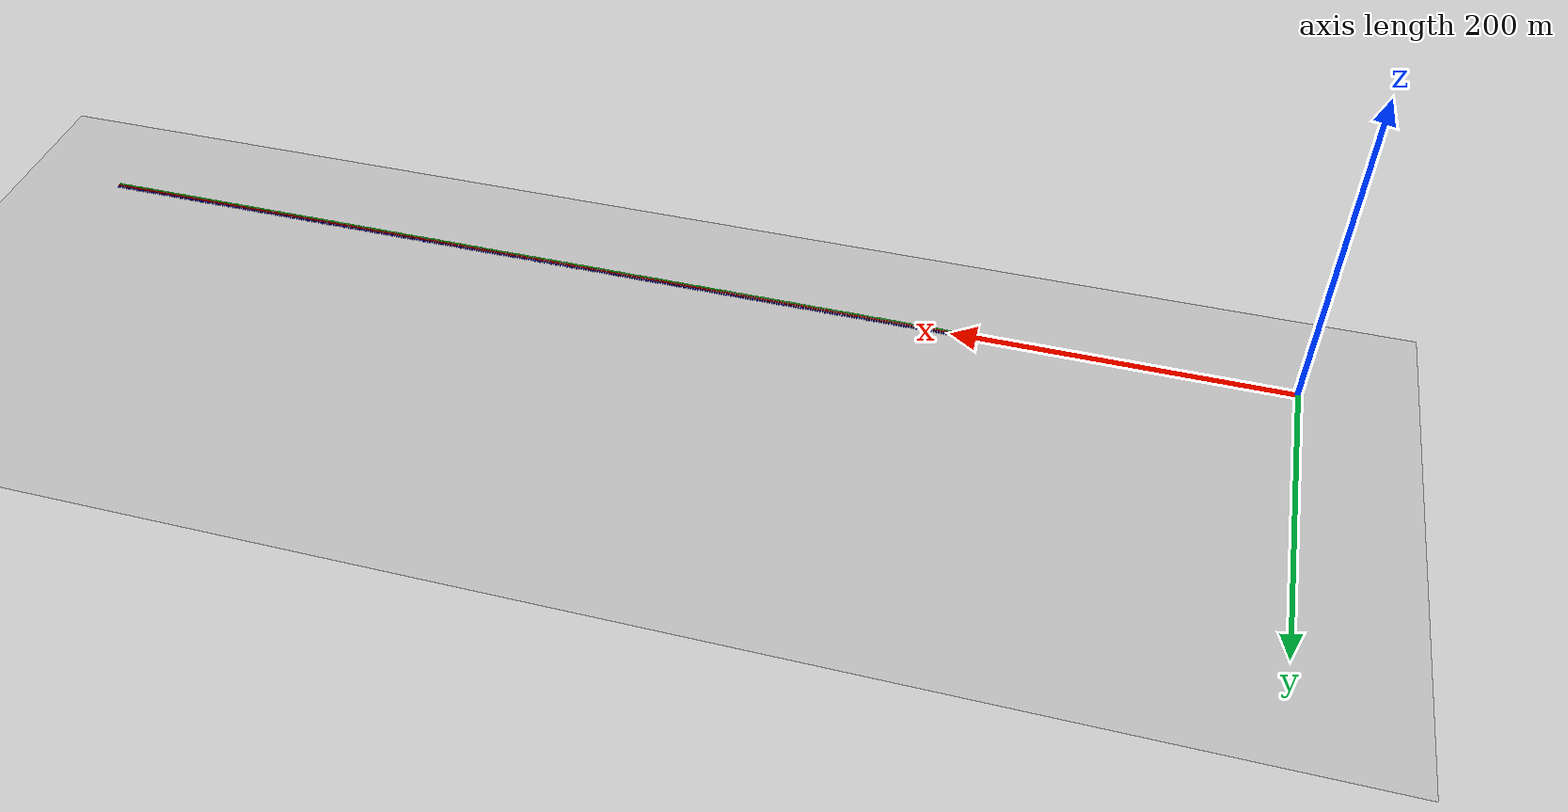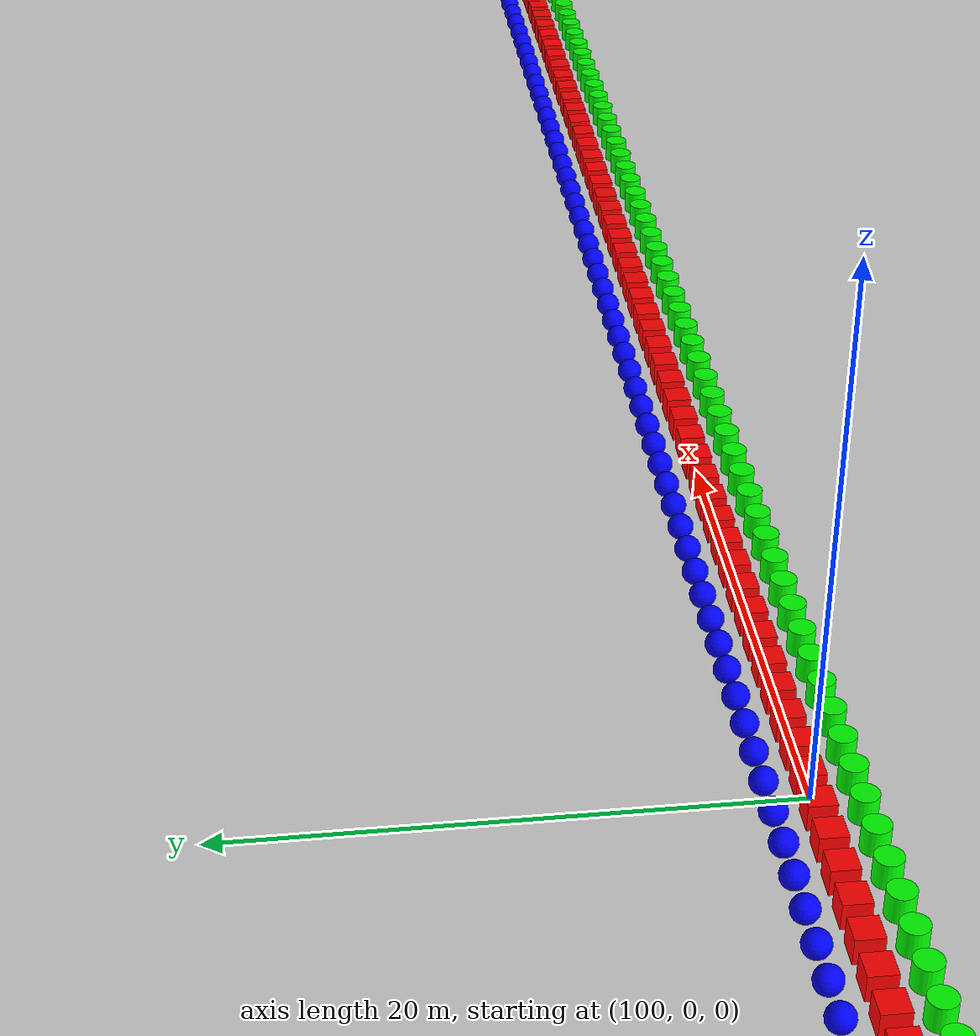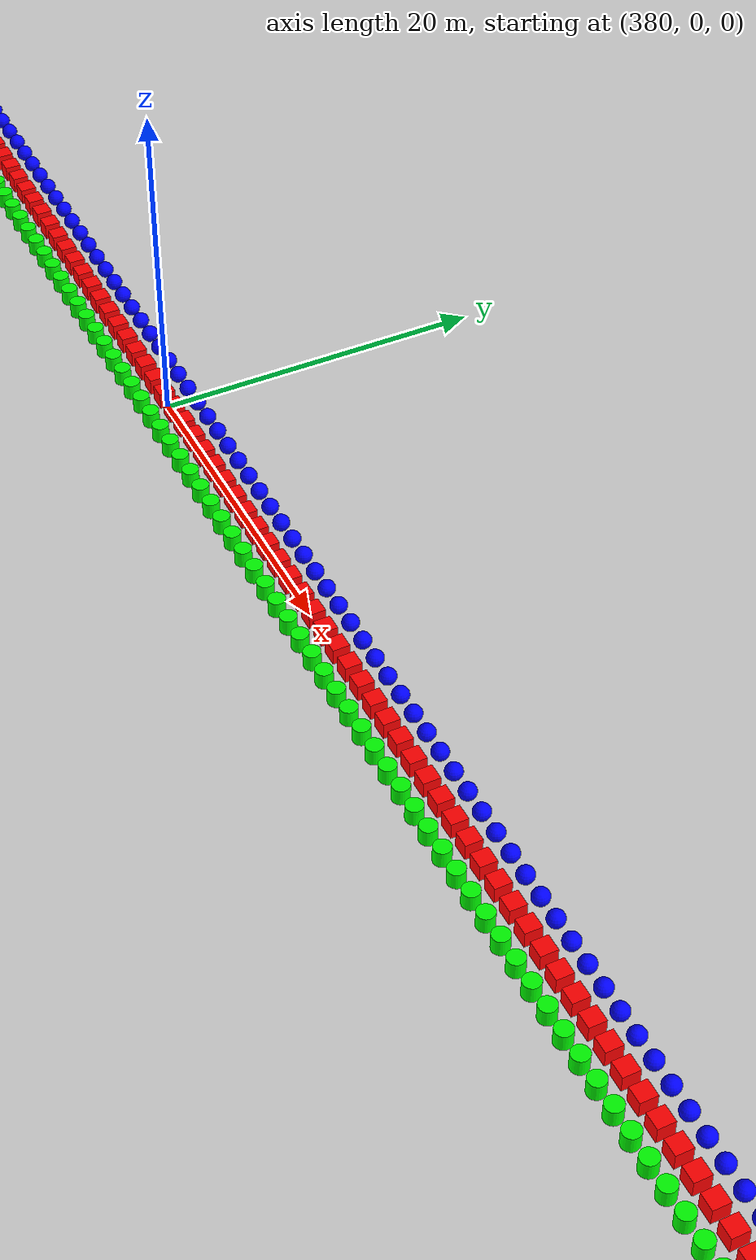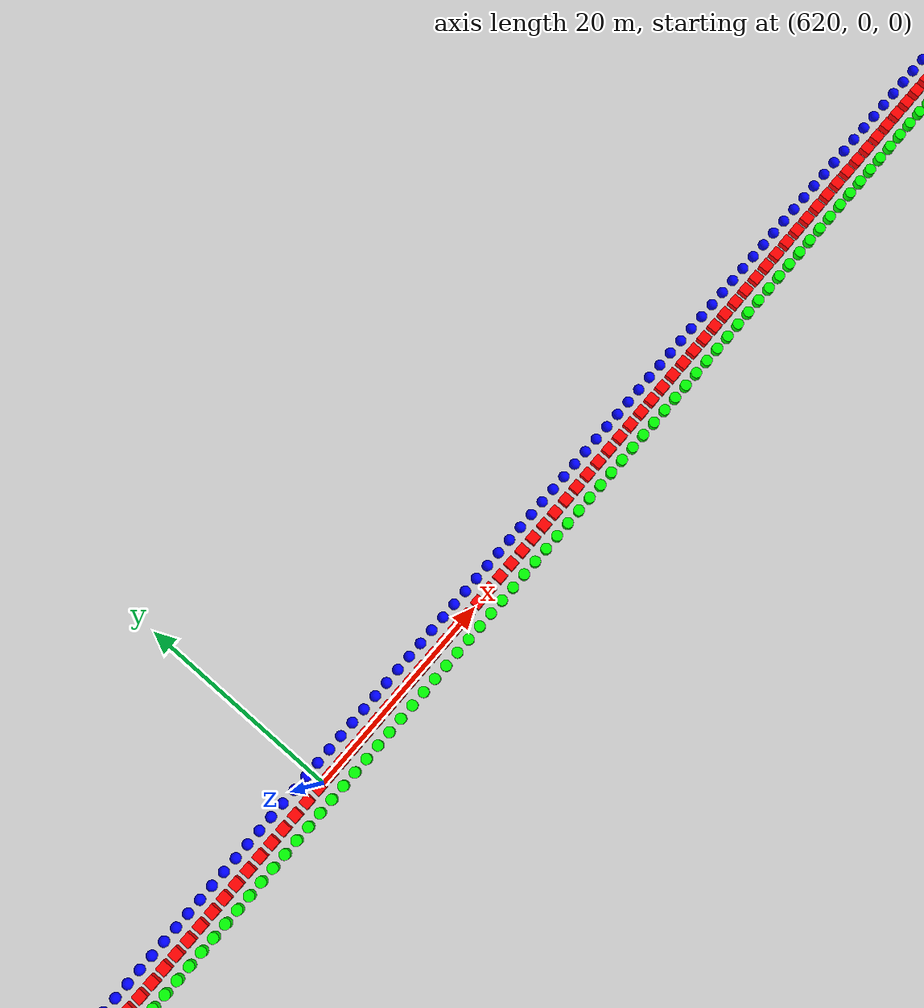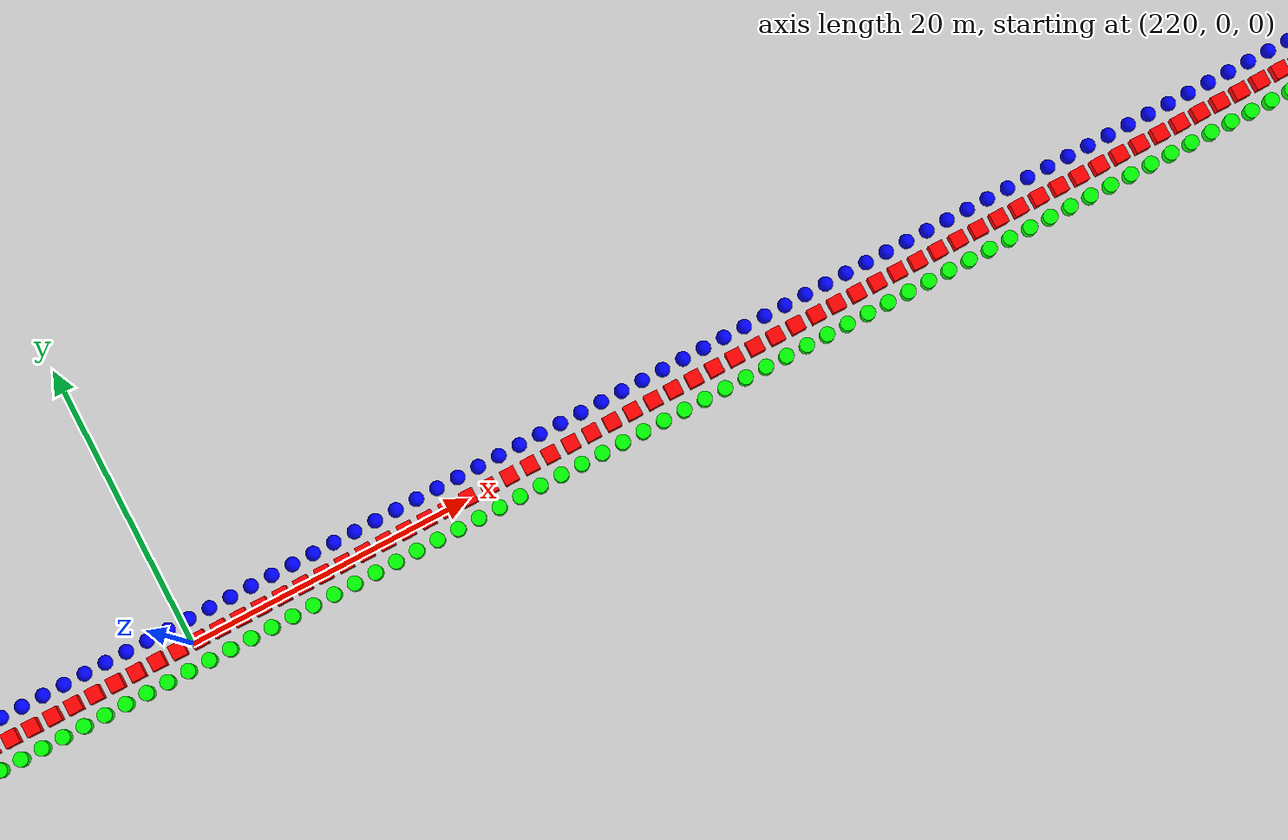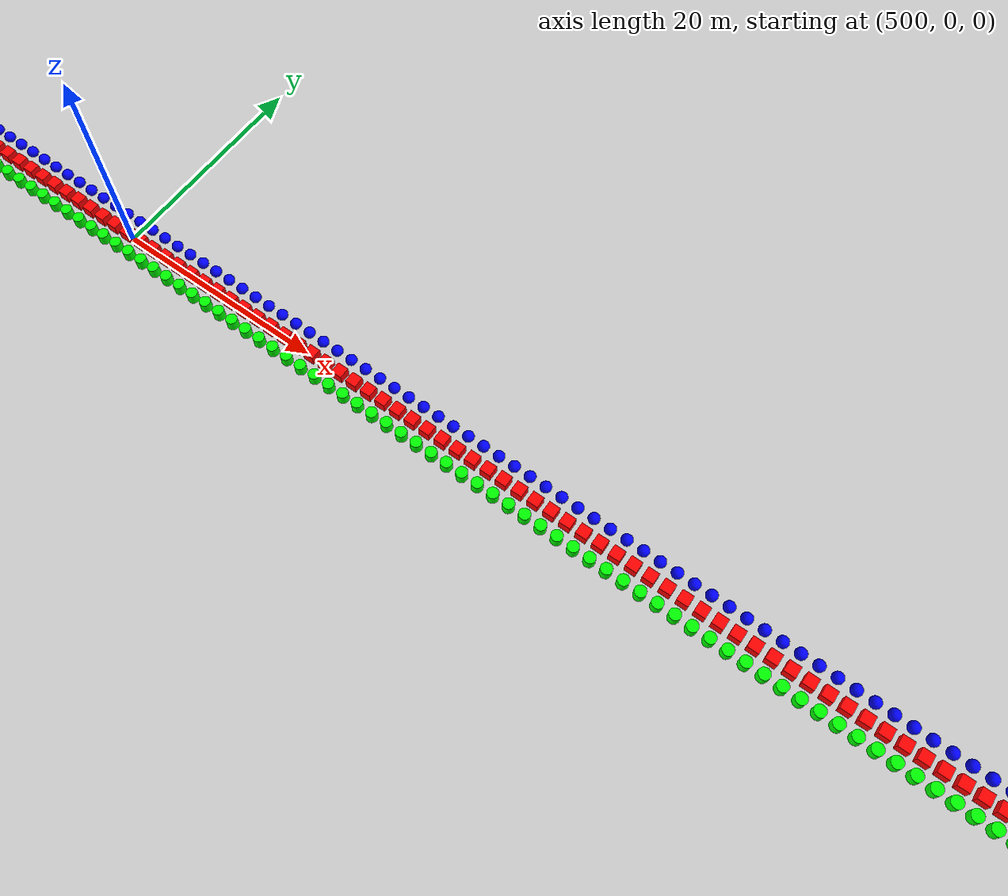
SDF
<sdf version="1.6">
 <world name="shapes">
  <model name="ground_plane">
   <static>true</static>
   <link name="link">
    <collision name="collision">
     <geometry><plane><normal>0 0 1</normal><size>100 100</size></plane></geometry>
    </collision>
    <visual name="visual">
     <geometry><plane><normal>0 0 1</normal><size>100 100</size></plane></geometry>
     <material>
      <ambient>0.8 0.8 0.8 1</ambient>
      <diffuse>0.8 0.8 0.8 1</diffuse>
      <specular>0.8 0.8 0.8 1</specular>
     </material>
    </visual>
   </link>
  </model>
  <model name="sphere_500">
   <static>false</static>
   <pose>0.0 1.5 0.5 0 0 0</pose>
   <link name="sphere_link">
    <inertial>
     <inertia><ixx>3</ixx><ixy>0</ixy><ixz>0</ixz><iyy>3</iyy><iyz>0</iyz><izz>3</izz></inertia>
     <mass>3.0</mass>
    </inertial>
    <collision name="sphere_collision"><geometry><sphere><radius>0.5</radius></sphere></geometry></collision>
    <visual name="sphere_visual">
     <geometry><sphere><radius>0.5</radius></sphere></geometry>
     <material><ambient>0 0 1 1</ambient><diffuse>0 0 1 1</diffuse><specular>0 0 1 1</specular></material>
    </visual>
   </link>
  </model>
  <model name="box_501">
   <static>false</static>
   <pose>1.5 0 0.5 0 0 0</pose>
   <link name="box_link">
    <inertial>
     <inertia><ixx>1</ixx><ixy>0</ixy><ixz>0</ixz><iyy>1</iyy><iyz>0</iyz><izz>1</izz></inertia>
     <mass>1.0</mass>
    </inertial>
    <collision name="box_collision"><geometry><box><size>1 1 1</size></box></geometry></collision>
    <visual name="box_visual">
     <geometry><box><size>1 1 1</size></box></geometry>
     <material><ambient>1 0 0 1</ambient><diffuse>1 0 0 1</diffuse><specular>1 0 0 1</specular></material>
    </visual>
   </link>
  </model>
  <model name="cylinder_501">
   <static>false</static>
   <pose>1.5 -1.5 0.5 0 0 0</pose>
   <link name="cylinder_link">
    <inertial>
     <inertia><ixx>2</ixx><ixy>0</ixy><ixz>0</ixz><iyy>2</iyy><iyz>0</iyz><izz>2</izz></inertia>
     <mass>2.0</mass>
    </inertial>
    <collision name="cylinder_collision">
     <geometry><cylinder><radius>0.5</radius><length>1.0</length></cylinder></geometry>
    </collision>
    <visual name="cylinder_visual">
     <geometry><cylinder><radius>0.5</radius><length>1.0</length></cylinder></geometry>
     <material><ambient>0 1 0 1</ambient><diffuse>0 1 0 1</diffuse><specular>0 1 0 1</specular></material>
    </visual>
   </link>
  </model>
  <model name="sphere_501">
   <static>false</static>
   <pose>1.5 1.5 0.5 0 0 0</pose>
   <link name="sphere_link">
    <inertial>
     <inertia><ixx>3</ixx><ixy>0</ixy><ixz>0</ixz><iyy>3</iyy><iyz>0</iyz><izz>3</izz></inertia>
     <mass>3.0</mass>
    </inertial>
    <collision name="sphere_collision"><geometry><sphere><radius>0.5</radius></sphere></geometry></collision>
    <visual name="sphere_visual">
     <geometry><sphere><radius>0.5</radius></sphere></geometry>
     <material><ambient>0 0 1 1</ambient><diffuse>0 0 1 1</diffuse><specular>0 0 1 1</specular></material>
    </visual>
   </link>
  </model>
  <model name="box_502">
   <static>false</static>
   <pose>3.0 0 0.5 0 0 0</pose>
   <link name="box_link">
    <inertial>
     <inertia><ixx>1</ixx><ixy>0</ixy><ixz>0</ixz><iyy>1</iyy><iyz>0</iyz><izz>1</izz></inertia>
     <mass>1.0</mass>
    </inertial>
    <collision name="box_collision"><geometry><box><size>1 1 1</size></box></geometry></collision>
    <visual name="box_visual">
     <geometry><box><size>1 1 1</size></box></geometry>
     <material><ambient>1 0 0 1</ambient><diffuse>1 0 0 1</diffuse><specular>1 0 0 1</specular></material>
    </visual>
   </link>
  </model>
  <model name="cylinder_502">
   <static>false</static>
   <pose>3.0 -1.5 0.5 0 0 0</pose>
   <link name="cylinder_link">
    <inertial>
     <inertia><ixx>2</ixx><ixy>0</ixy><ixz>0</ixz><iyy>2</iyy><iyz>0</iyz><izz>2</izz></inertia>
     <mass>2.0</mass>
    </inertial>
    <collision name="cylinder_collision">
     <geometry><cylinder><radius>0.5</radius><length>1.0</length></cylinder></geometry>
    </collision>
    <visual name="cylinder_visual">
     <geometry><cylinder><radius>0.5</radius><length>1.0</length></cylinder></geometry>
     <material><ambient>0 1 0 1</ambient><diffuse>0 1 0 1</diffuse><specular>0 1 0 1</specular></material>
    </visual>
   </link>
  </model>
  <model name="sphere_502">
   <static>false</static>
   <pose>3.0 1.5 0.5 0 0 0</pose>
   <link name="sphere_link">
    <inertial>
     <inertia><ixx>3</ixx><ixy>0</ixy><ixz>0</ixz><iyy>3</iyy><iyz>0</iyz><izz>3</izz></inertia>
     <mass>3.0</mass>
    </inertial>
    <collision name="sphere_collision"><geometry><sphere><radius>0.5</radius></sphere></geometry></collision>
    <visual name="sphere_visual">
     <geometry><sphere><radius>0.5</radius></sphere></geometry>
     <material><ambient>0 0 1 1</ambient><diffuse>0 0 1 1</diffuse><specular>0 0 1 1</specular></material>
    </visual>
   </link>
  </model>
  <model name="box_503">
   <static>false</static>
   <pose>4.5 0 0.5 0 0 0</pose>
   <link name="box_link">
    <inertial>
     <inertia><ixx>1</ixx><ixy>0</ixy><ixz>0</ixz><iyy>1</iyy><iyz>0</iyz><izz>1</izz></inertia>
     <mass>1.0</mass>
    </inertial>
    <collision name="box_collision"><geometry><box><size>1 1 1</size></box></geometry></collision>
    <visual name="box_visual">
     <geometry><box><size>1 1 1</size></box></geometry>
     <material><ambient>1 0 0 1</ambient><diffuse>1 0 0 1</diffuse><specular>1 0 0 1</specular></material>
    </visual>
   </link>
  </model>
  <model name="cylinder_503">
   <static>false</static>
   <pose>4.5 -1.5 0.5 0 0 0</pose>
   <link name="cylinder_link">
    <inertial>
     <inertia><ixx>2</ixx><ixy>0</ixy><ixz>0</ixz><iyy>2</iyy><iyz>0</iyz><izz>2</izz></inertia>
     <mass>2.0</mass>
    </inertial>
    <collision name="cylinder_collision">
     <geometry><cylinder><radius>0.5</radius><length>1.0</length></cylinder></geometry>
    </collision>
    <visual name="cylinder_visual">
     <geometry><cylinder><radius>0.5</radius><length>1.0</length></cylinder></geometry>
     <material><ambient>0 1 0 1</ambient><diffuse>0 1 0 1</diffuse><specular>0 1 0 1</specular></material>
    </visual>
   </link>
  </model>
  <model name="sphere_503">
   <static>false</static>
   <pose>4.5 1.5 0.5 0 0 0</pose>
   <link name="sphere_link">
    <inertial>
     <inertia><ixx>3</ixx><ixy>0</ixy><ixz>0</ixz><iyy>3</iyy><iyz>0</iyz><izz>3</izz></inertia>
     <mass>3.0</mass>
    </inertial>
    <collision name="sphere_collision"><geometry><sphere><radius>0.5</radius></sphere></geometry></collision>
    <visual name="sphere_visual">
     <geometry><sphere><radius>0.5</radius></sphere></geometry>
     <material><ambient>0 0 1 1</ambient><diffuse>0 0 1 1</diffuse><specular>0 0 1 1</specular></material>
    </visual>
   </link>
  </model>
  <model name="box_504">
   <static>false</static>
   <pose>6.0 0 0.5 0 0 0</pose>
   <link name="box_link">
    <inertial>
     <inertia><ixx>1</ixx><ixy>0</ixy><ixz>0</ixz><iyy>1</iyy><iyz>0</iyz><izz>1</izz></inertia>
     <mass>1.0</mass>
    </inertial>
    <collision name="box_collision"><geometry><box><size>1 1 1</size></box></geometry></collision>
    <visual name="box_visual">
     <geometry><box><size>1 1 1</size></box></geometry>
     <material><ambient>1 0 0 1</ambient><diffuse>1 0 0 1</diffuse><specular>1 0 0 1</specular></material>
    </visual>
   </link>
  </model>
  <model name="cylinder_504">
   <static>false</static>
   <pose>6.0 -1.5 0.5 0 0 0</pose>
   <link name="cylinder_link">
    <inertial>
     <inertia><ixx>2</ixx><ixy>0</ixy><ixz>0</ixz><iyy>2</iyy><iyz>0</iyz><izz>2</izz></inertia>
     <mass>2.0</mass>
    </inertial>
    <collision name="cylinder_collision">
     <geometry><cylinder><radius>0.5</radius><length>1.0</length></cylinder></geometry>
    </collision>
    <visual name="cylinder_visual">
     <geometry><cylinder><radius>0.5</radius><length>1.0</length></cylinder></geometry>
     <material><ambient>0 1 0 1</ambient><diffuse>0 1 0 1</diffuse><specular>0 1 0 1</specular></material>
    </visual>
   </link>
  </model>
  <model name="sphere_504">
   <static>false</static>
   <pose>6.0 1.5 0.5 0 0 0</pose>
   <link name="sphere_link">
    <inertial>
     <inertia><ixx>3</ixx><ixy>0</ixy><ixz>0</ixz><iyy>3</iyy><iyz>0</iyz><izz>3</izz></inertia>
     <mass>3.0</mass>
    </inertial>
    <collision name="sphere_collision"><geometry><sphere><radius>0.5</radius></sphere></geometry></collision>
    <visual name="sphere_visual">
     <geometry><sphere><radius>0.5</radius></sphere></geometry>
     <material><ambient>0 0 1 1</ambient><diffuse>0 0 1 1</diffuse><specular>0 0 1 1</specular></material>
    </visual>
   </link>
  </model>
  <model name="box_505">
   <static>false</static>
   <pose>7.5 0 0.5 0 0 0</pose>
   <link name="box_link">
    <inertial>
     <inertia><ixx>1</ixx><ixy>0</ixy><ixz>0</ixz><iyy>1</iyy><iyz>0</iyz><izz>1</izz></inertia>
     <mass>1.0</mass>
    </inertial>
    <collision name="box_collision"><geometry><box><size>1 1 1</size></box></geometry></collision>
    <visual name="box_visual">
     <geometry><box><size>1 1 1</size></box></geometry>
     <material><ambient>1 0 0 1</ambient><diffuse>1 0 0 1</diffuse><specular>1 0 0 1</specular></material>
    </visual>
   </link>
  </model>
  <model name="cylinder_505">
   <static>false</static>
   <pose>7.5 -1.5 0.5 0 0 0</pose>
   <link name="cylinder_link">
    <inertial>
     <inertia><ixx>2</ixx><ixy>0</ixy><ixz>0</ixz><iyy>2</iyy><iyz>0</iyz><izz>2</izz></inertia>
     <mass>2.0</mass>
    </inertial>
    <collision name="cylinder_collision">
     <geometry><cylinder><radius>0.5</radius><length>1.0</length></cylinder></geometry>
    </collision>
    <visual name="cylinder_visual">
     <geometry><cylinder><radius>0.5</radius><length>1.0</length></cylinder></geometry>
     <material><ambient>0 1 0 1</ambient><diffuse>0 1 0 1</diffuse><specular>0 1 0 1</specular></material>
    </visual>
   </link>
  </model>
  <model name="sphere_505">
   <static>false</static>
   <pose>7.5 1.5 0.5 0 0 0</pose>
   <link name="sphere_link">
    <inertial>
     <inertia><ixx>3</ixx><ixy>0</ixy><ixz>0</ixz><iyy>3</iyy><iyz>0</iyz><izz>3</izz></inertia>
     <mass>3.0</mass>
    </inertial>
    <collision name="sphere_collision"><geometry><sphere><radius>0.5</radius></sphere></geometry></collision>
    <visual name="sphere_visual">
     <geometry><sphere><radius>0.5</radius></sphere></geometry>
     <material><ambient>0 0 1 1</ambient><diffuse>0 0 1 1</diffuse><specular>0 0 1 1</specular></material>
    </visual>
   </link>
  </model>
  <model name="box_506">
   <static>false</static>
   <pose>9.0 0 0.5 0 0 0</pose>
   <link name="box_link">
    <inertial>
     <inertia><ixx>1</ixx><ixy>0</ixy><ixz>0</ixz><iyy>1</iyy><iyz>0</iyz><izz>1</izz></inertia>
     <mass>1.0</mass>
    </inertial>
    <collision name="box_collision"><geometry><box><size>1 1 1</size></box></geometry></collision>
    <visual name="box_visual">
     <geometry><box><size>1 1 1</size></box></geometry>
     <material><ambient>1 0 0 1</ambient><diffuse>1 0 0 1</diffuse><specular>1 0 0 1</specular></material>
    </visual>
   </link>
  </model>
  <model name="cylinder_506">
   <static>false</static>
   <pose>9.0 -1.5 0.5 0 0 0</pose>
   <link name="cylinder_link">
    <inertial>
     <inertia><ixx>2</ixx><ixy>0</ixy><ixz>0</ixz><iyy>2</iyy><iyz>0</iyz><izz>2</izz></inertia>
     <mass>2.0</mass>
    </inertial>
    <collision name="cylinder_collision">
     <geometry><cylinder><radius>0.5</radius><length>1.0</length></cylinder></geometry>
    </collision>
    <visual name="cylinder_visual">
     <geometry><cylinder><radius>0.5</radius><length>1.0</length></cylinder></geometry>
     <material><ambient>0 1 0 1</ambient><diffuse>0 1 0 1</diffuse><specular>0 1 0 1</specular></material>
    </visual>
   </link>
  </model>
  <model name="sphere_506">
   <static>false</static>
   <pose>9.0 1.5 0.5 0 0 0</pose>
   <link name="sphere_link">
    <inertial>
     <inertia><ixx>3</ixx><ixy>0</ixy><ixz>0</ixz><iyy>3</iyy><iyz>0</iyz><izz>3</izz></inertia>
     <mass>3.0</mass>
    </inertial>
    <collision name="sphere_collision"><geometry><sphere><radius>0.5</radius></sphere></geometry></collision>
    <visual name="sphere_visual">
     <geometry><sphere><radius>0.5</radius></sphere></geometry>
     <material><ambient>0 0 1 1</ambient><diffuse>0 0 1 1</diffuse><specular>0 0 1 1</specular></material>
    </visual>
   </link>
  </model>
  <model name="box_507">
   <static>false</static>
   <pose>10.5 0 0.5 0 0 0</pose>
   <link name="box_link">
    <inertial>
     <inertia><ixx>1</ixx><ixy>0</ixy><ixz>0</ixz><iyy>1</iyy><iyz>0</iyz><izz>1</izz></inertia>
     <mass>1.0</mass>
    </inertial>
    <collision name="box_collision"><geometry><box><size>1 1 1</size></box></geometry></collision>
    <visual name="box_visual">
     <geometry><box><size>1 1 1</size></box></geometry>
     <material><ambient>1 0 0 1</ambient><diffuse>1 0 0 1</diffuse><specular>1 0 0 1</specular></material>
    </visual>
   </link>
  </model>
  <model name="cylinder_507">
   <static>false</static>
   <pose>10.5 -1.5 0.5 0 0 0</pose>
   <link name="cylinder_link">
    <inertial>
     <inertia><ixx>2</ixx><ixy>0</ixy><ixz>0</ixz><iyy>2</iyy><iyz>0</iyz><izz>2</izz></inertia>
     <mass>2.0</mass>
    </inertial>
    <collision name="cylinder_collision">
     <geometry><cylinder><radius>0.5</radius><length>1.0</length></cylinder></geometry>
    </collision>
    <visual name="cylinder_visual">
     <geometry><cylinder><radius>0.5</radius><length>1.0</length></cylinder></geometry>
     <material><ambient>0 1 0 1</ambient><diffuse>0 1 0 1</diffuse><specular>0 1 0 1</specular></material>
    </visual>
   </link>
  </model>
  <model name="sphere_507">
   <static>false</static>
   <pose>10.5 1.5 0.5 0 0 0</pose>
   <link name="sphere_link">
    <inertial>
     <inertia><ixx>3</ixx><ixy>0</ixy><ixz>0</ixz><iyy>3</iyy><iyz>0</iyz><izz>3</izz></inertia>
     <mass>3.0</mass>
    </inertial>
    <collision name="sphere_collision"><geometry><sphere><radius>0.5</radius></sphere></geometry></collision>
    <visual name="sphere_visual">
     <geometry><sphere><radius>0.5</radius></sphere></geometry>
     <material><ambient>0 0 1 1</ambient><diffuse>0 0 1 1</diffuse><specular>0 0 1 1</specular></material>
    </visual>
   </link>
  </model>
  <model name="box_508">
   <static>false</static>
   <pose>12.0 0 0.5 0 0 0</pose>
   <link name="box_link">
    <inertial>
     <inertia><ixx>1</ixx><ixy>0</ixy><ixz>0</ixz><iyy>1</iyy><iyz>0</iyz><izz>1</izz></inertia>
     <mass>1.0</mass>
    </inertial>
    <collision name="box_collision"><geometry><box><size>1 1 1</size></box></geometry></collision>
    <visual name="box_visual">
     <geometry><box><size>1 1 1</size></box></geometry>
     <material><ambient>1 0 0 1</ambient><diffuse>1 0 0 1</diffuse><specular>1 0 0 1</specular></material>
    </visual>
   </link>
  </model>
  <model name="cylinder_508">
   <static>false</static>
   <pose>12.0 -1.5 0.5 0 0 0</pose>
   <link name="cylinder_link">
    <inertial>
     <inertia><ixx>2</ixx><ixy>0</ixy><ixz>0</ixz><iyy>2</iyy><iyz>0</iyz><izz>2</izz></inertia>
     <mass>2.0</mass>
    </inertial>
    <collision name="cylinder_collision">
     <geometry><cylinder><radius>0.5</radius><length>1.0</length></cylinder></geometry>
    </collision>
    <visual name="cylinder_visual">
     <geometry><cylinder><radius>0.5</radius><length>1.0</length></cylinder></geometry>
     <material><ambient>0 1 0 1</ambient><diffuse>0 1 0 1</diffuse><specular>0 1 0 1</specular></material>
    </visual>
   </link>
  </model>
  <model name="sphere_508">
   <static>false</static>
   <pose>12.0 1.5 0.5 0 0 0</pose>
   <link name="sphere_link">
    <inertial>
     <inertia><ixx>3</ixx><ixy>0</ixy><ixz>0</ixz><iyy>3</iyy><iyz>0</iyz><izz>3</izz></inertia>
     <mass>3.0</mass>
    </inertial>
    <collision name="sphere_collision"><geometry><sphere><radius>0.5</radius></sphere></geometry></collision>
    <visual name="sphere_visual">
     <geometry><sphere><radius>0.5</radius></sphere></geometry>
     <material><ambient>0 0 1 1</ambient><diffuse>0 0 1 1</diffuse><specular>0 0 1 1</specular></material>
    </visual>
   </link>
  </model>
  <model name="box_509">
   <static>false</static>
   <pose>13.5 0 0.5 0 0 0</pose>
   <link name="box_link">
    <inertial>
     <inertia><ixx>1</ixx><ixy>0</ixy><ixz>0</ixz><iyy>1</iyy><iyz>0</iyz><izz>1</izz></inertia>
     <mass>1.0</mass>
    </inertial>
    <collision name="box_collision"><geometry><box><size>1 1 1</size></box></geometry></collision>
    <visual name="box_visual">
     <geometry><box><size>1 1 1</size></box></geometry>
     <material><ambient>1 0 0 1</ambient><diffuse>1 0 0 1</diffuse><specular>1 0 0 1</specular></material>
    </visual>
   </link>
  </model>
  <model name="cylinder_509">
   <static>false</static>
   <pose>13.5 -1.5 0.5 0 0 0</pose>
   <link name="cylinder_link">
    <inertial>
     <inertia><ixx>2</ixx><ixy>0</ixy><ixz>0</ixz><iyy>2</iyy><iyz>0</iyz><izz>2</izz></inertia>
     <mass>2.0</mass>
    </inertial>
    <collision name="cylinder_collision">
     <geometry><cylinder><radius>0.5</radius><length>1.0</length></cylinder></geometry>
    </collision>
    <visual name="cylinder_visual">
     <geometry><cylinder><radius>0.5</radius><length>1.0</length></cylinder></geometry>
     <material><ambient>0 1 0 1</ambient><diffuse>0 1 0 1</diffuse><specular>0 1 0 1</specular></material>
    </visual>
   </link>
  </model>
  <model name="sphere_509">
   <static>false</static>
   <pose>13.5 1.5 0.5 0 0 0</pose>
   <link name="sphere_link">
    <inertial>
     <inertia><ixx>3</ixx><ixy>0</ixy><ixz>0</ixz><iyy>3</iyy><iyz>0</iyz><izz>3</izz></inertia>
     <mass>3.0</mass>
    </inertial>
    <collision name="sphere_collision"><geometry><sphere><radius>0.5</radius></sphere></geometry></collision>
    <visual name="sphere_visual">
     <geometry><sphere><radius>0.5</radius></sphere></geometry>
     <material><ambient>0 0 1 1</ambient><diffuse>0 0 1 1</diffuse><specular>0 0 1 1</specular></material>
    </visual>
   </link>
  </model>
  <model name="box_510">
   <static>false</static>
   <pose>15.0 0 0.5 0 0 0</pose>
   <link name="box_link">
    <inertial>
     <inertia><ixx>1</ixx><ixy>0</ixy><ixz>0</ixz><iyy>1</iyy><iyz>0</iyz><izz>1</izz></inertia>
     <mass>1.0</mass>
    </inertial>
    <collision name="box_collision"><geometry><box><size>1 1 1</size></box></geometry></collision>
    <visual name="box_visual">
     <geometry><box><size>1 1 1</size></box></geometry>
     <material><ambient>1 0 0 1</ambient><diffuse>1 0 0 1</diffuse><specular>1 0 0 1</specular></material>
    </visual>
   </link>
  </model>
  <model name="cylinder_510">
   <static>false</static>
   <pose>15.0 -1.5 0.5 0 0 0</pose>
   <link name="cylinder_link">
    <inertial>
     <inertia><ixx>2</ixx><ixy>0</ixy><ixz>0</ixz><iyy>2</iyy><iyz>0</iyz><izz>2</izz></inertia>
     <mass>2.0</mass>
    </inertial>
    <collision name="cylinder_collision">
     <geometry><cylinder><radius>0.5</radius><length>1.0</length></cylinder></geometry>
    </collision>
    <visual name="cylinder_visual">
     <geometry><cylinder><radius>0.5</radius><length>1.0</length></cylinder></geometry>
     <material><ambient>0 1 0 1</ambient><diffuse>0 1 0 1</diffuse><specular>0 1 0 1</specular></material>
    </visual>
   </link>
  </model>
  <model name="sphere_510">
   <static>false</static>
   <pose>15.0 1.5 0.5 0 0 0</pose>
   <link name="sphere_link">
    <inertial>
     <inertia><ixx>3</ixx><ixy>0</ixy><ixz>0</ixz><iyy>3</iyy><iyz>0</iyz><izz>3</izz></inertia>
     <mass>3.0</mass>
    </inertial>
    <collision name="sphere_collision"><geometry><sphere><radius>0.5</radius></sphere></geometry></collision>
    <visual name="sphere_visual">
     <geometry><sphere><radius>0.5</radius></sphere></geometry>
     <material><ambient>0 0 1 1</ambient><diffuse>0 0 1 1</diffuse><specular>0 0 1 1</specular></material>
    </visual>
   </link>
  </model>
  <model name="box_511">
   <static>false</static>
   <pose>16.5 0 0.5 0 0 0</pose>
   <link name="box_link">
    <inertial>
     <inertia><ixx>1</ixx><ixy>0</ixy><ixz>0</ixz><iyy>1</iyy><iyz>0</iyz><izz>1</izz></inertia>
     <mass>1.0</mass>
    </inertial>
    <collision name="box_collision"><geometry><box><size>1 1 1</size></box></geometry></collision>
    <visual name="box_visual">
     <geometry><box><size>1 1 1</size></box></geometry>
     <material><ambient>1 0 0 1</ambient><diffuse>1 0 0 1</diffuse><specular>1 0 0 1</specular></material>
    </visual>
   </link>
  </model>
  <model name="cylinder_511">
   <static>false</static>
   <pose>16.5 -1.5 0.5 0 0 0</pose>
   <link name="cylinder_link">
    <inertial>
     <inertia><ixx>2</ixx><ixy>0</ixy><ixz>0</ixz><iyy>2</iyy><iyz>0</iyz><izz>2</izz></inertia>
     <mass>2.0</mass>
    </inertial>
    <collision name="cylinder_collision">
     <geometry><cylinder><radius>0.5</radius><length>1.0</length></cylinder></geometry>
    </collision>
    <visual name="cylinder_visual">
     <geometry><cylinder><radius>0.5</radius><length>1.0</length></cylinder></geometry>
     <material><ambient>0 1 0 1</ambient><diffuse>0 1 0 1</diffuse><specular>0 1 0 1</specular></material>
    </visual>
   </link>
  </model>
  <model name="sphere_511">
   <static>false</static>
   <pose>16.5 1.5 0.5 0 0 0</pose>
   <link name="sphere_link">
    <inertial>
     <inertia><ixx>3</ixx><ixy>0</ixy><ixz>0</ixz><iyy>3</iyy><iyz>0</iyz><izz>3</izz></inertia>
     <mass>3.0</mass>
    </inertial>
    <collision name="sphere_collision"><geometry><sphere><radius>0.5</radius></sphere></geometry></collision>
    <visual name="sphere_visual">
     <geometry><sphere><radius>0.5</radius></sphere></geometry>
     <material><ambient>0 0 1 1</ambient><diffuse>0 0 1 1</diffuse><specular>0 0 1 1</specular></material>
    </visual>
   </link>
  </model>
  <model name="box_512">
   <static>false</static>
   <pose>18.0 0 0.5 0 0 0</pose>
   <link name="box_link">
    <inertial>
     <inertia><ixx>1</ixx><ixy>0</ixy><ixz>0</ixz><iyy>1</iyy><iyz>0</iyz><izz>1</izz></inertia>
     <mass>1.0</mass>
    </inertial>
    <collision name="box_collision"><geometry><box><size>1 1 1</size></box></geometry></collision>
    <visual name="box_visual">
     <geometry><box><size>1 1 1</size></box></geometry>
     <material><ambient>1 0 0 1</ambient><diffuse>1 0 0 1</diffuse><specular>1 0 0 1</specular></material>
    </visual>
   </link>
  </model>
  <model name="cylinder_512">
   <static>false</static>
   <pose>18.0 -1.5 0.5 0 0 0</pose>
   <link name="cylinder_link">
    <inertial>
     <inertia><ixx>2</ixx><ixy>0</ixy><ixz>0</ixz><iyy>2</iyy><iyz>0</iyz><izz>2</izz></inertia>
     <mass>2.0</mass>
    </inertial>
    <collision name="cylinder_collision">
     <geometry><cylinder><radius>0.5</radius><length>1.0</length></cylinder></geometry>
    </collision>
    <visual name="cylinder_visual">
     <geometry><cylinder><radius>0.5</radius><length>1.0</length></cylinder></geometry>
     <material><ambient>0 1 0 1</ambient><diffuse>0 1 0 1</diffuse><specular>0 1 0 1</specular></material>
    </visual>
   </link>
  </model>
  <model name="sphere_512">
   <static>false</static>
   <pose>18.0 1.5 0.5 0 0 0</pose>
   <link name="sphere_link">
    <inertial>
     <inertia><ixx>3</ixx><ixy>0</ixy><ixz>0</ixz><iyy>3</iyy><iyz>0</iyz><izz>3</izz></inertia>
     <mass>3.0</mass>
    </inertial>
    <collision name="sphere_collision"><geometry><sphere><radius>0.5</radius></sphere></geometry></collision>
    <visual name="sphere_visual">
     <geometry><sphere><radius>0.5</radius></sphere></geometry>
     <material><ambient>0 0 1 1</ambient><diffuse>0 0 1 1</diffuse><specular>0 0 1 1</specular></material>
    </visual>
   </link>
  </model>
  <model name="box_513">
   <static>false</static>
   <pose>19.5 0 0.5 0 0 0</pose>
   <link name="box_link">
    <inertial>
     <inertia><ixx>1</ixx><ixy>0</ixy><ixz>0</ixz><iyy>1</iyy><iyz>0</iyz><izz>1</izz></inertia>
     <mass>1.0</mass>
    </inertial>
    <collision name="box_collision"><geometry><box><size>1 1 1</size></box></geometry></collision>
    <visual name="box_visual">
     <geometry><box><size>1 1 1</size></box></geometry>
     <material><ambient>1 0 0 1</ambient><diffuse>1 0 0 1</diffuse><specular>1 0 0 1</specular></material>
    </visual>
   </link>
  </model>
  <model name="cylinder_513">
   <static>false</static>
   <pose>19.5 -1.5 0.5 0 0 0</pose>
   <link name="cylinder_link">
    <inertial>
     <inertia><ixx>2</ixx><ixy>0</ixy><ixz>0</ixz><iyy>2</iyy><iyz>0</iyz><izz>2</izz></inertia>
     <mass>2.0</mass>
    </inertial>
    <collision name="cylinder_collision">
     <geometry><cylinder><radius>0.5</radius><length>1.0</length></cylinder></geometry>
    </collision>
    <visual name="cylinder_visual">
     <geometry><cylinder><radius>0.5</radius><length>1.0</length></cylinder></geometry>
     <material><ambient>0 1 0 1</ambient><diffuse>0 1 0 1</diffuse><specular>0 1 0 1</specular></material>
    </visual>
   </link>
  </model>
  <model name="sphere_513">
   <static>false</static>
   <pose>19.5 1.5 0.5 0 0 0</pose>
   <link name="sphere_link">
    <inertial>
     <inertia><ixx>3</ixx><ixy>0</ixy><ixz>0</ixz><iyy>3</iyy><iyz>0</iyz><izz>3</izz></inertia>
     <mass>3.0</mass>
    </inertial>
    <collision name="sphere_collision"><geometry><sphere><radius>0.5</radius></sphere></geometry></collision>
    <visual name="sphere_visual">
     <geometry><sphere><radius>0.5</radius></sphere></geometry>
     <material><ambient>0 0 1 1</ambient><diffuse>0 0 1 1</diffuse><specular>0 0 1 1</specular></material>
    </visual>
   </link>
  </model>
  <model name="box_514">
   <static>false</static>
   <pose>21.0 0 0.5 0 0 0</pose>
   <link name="box_link">
    <inertial>
     <inertia><ixx>1</ixx><ixy>0</ixy><ixz>0</ixz><iyy>1</iyy><iyz>0</iyz><izz>1</izz></inertia>
     <mass>1.0</mass>
    </inertial>
    <collision name="box_collision"><geometry><box><size>1 1 1</size></box></geometry></collision>
    <visual name="box_visual">
     <geometry><box><size>1 1 1</size></box></geometry>
     <material><ambient>1 0 0 1</ambient><diffuse>1 0 0 1</diffuse><specular>1 0 0 1</specular></material>
    </visual>
   </link>
  </model>
  <model name="cylinder_514">
   <static>false</static>
   <pose>21.0 -1.5 0.5 0 0 0</pose>
   <link name="cylinder_link">
    <inertial>
     <inertia><ixx>2</ixx><ixy>0</ixy><ixz>0</ixz><iyy>2</iyy><iyz>0</iyz><izz>2</izz></inertia>
     <mass>2.0</mass>
    </inertial>
    <collision name="cylinder_collision">
     <geometry><cylinder><radius>0.5</radius><length>1.0</length></cylinder></geometry>
    </collision>
    <visual name="cylinder_visual">
     <geometry><cylinder><radius>0.5</radius><length>1.0</length></cylinder></geometry>
     <material><ambient>0 1 0 1</ambient><diffuse>0 1 0 1</diffuse><specular>0 1 0 1</specular></material>
    </visual>
   </link>
  </model>
  <model name="sphere_514">
   <static>false</static>
   <pose>21.0 1.5 0.5 0 0 0</pose>
   <link name="sphere_link">
    <inertial>
     <inertia><ixx>3</ixx><ixy>0</ixy><ixz>0</ixz><iyy>3</iyy><iyz>0</iyz><izz>3</izz></inertia>
     <mass>3.0</mass>
    </inertial>
    <collision name="sphere_collision"><geometry><sphere><radius>0.5</radius></sphere></geometry></collision>
    <visual name="sphere_visual">
     <geometry><sphere><radius>0.5</radius></sphere></geometry>
     <material><ambient>0 0 1 1</ambient><diffuse>0 0 1 1</diffuse><specular>0 0 1 1</specular></material>
    </visual>
   </link>
  </model>
  <model name="box_515">
   <static>false</static>
   <pose>22.5 0 0.5 0 0 0</pose>
   <link name="box_link">
    <inertial>
     <inertia><ixx>1</ixx><ixy>0</ixy><ixz>0</ixz><iyy>1</iyy><iyz>0</iyz><izz>1</izz></inertia>
     <mass>1.0</mass>
    </inertial>
    <collision name="box_collision"><geometry><box><size>1 1 1</size></box></geometry></collision>
    <visual name="box_visual">
     <geometry><box><size>1 1 1</size></box></geometry>
     <material><ambient>1 0 0 1</ambient><diffuse>1 0 0 1</diffuse><specular>1 0 0 1</specular></material>
    </visual>
   </link>
  </model>
  <model name="cylinder_515">
   <static>false</static>
   <pose>22.5 -1.5 0.5 0 0 0</pose>
   <link name="cylinder_link">
    <inertial>
     <inertia><ixx>2</ixx><ixy>0</ixy><ixz>0</ixz><iyy>2</iyy><iyz>0</iyz><izz>2</izz></inertia>
     <mass>2.0</mass>
    </inertial>
    <collision name="cylinder_collision">
     <geometry><cylinder><radius>0.5</radius><length>1.0</length></cylinder></geometry>
    </collision>
    <visual name="cylinder_visual">
     <geometry><cylinder><radius>0.5</radius><length>1.0</length></cylinder></geometry>
     <material><ambient>0 1 0 1</ambient><diffuse>0 1 0 1</diffuse><specular>0 1 0 1</specular></material>
    </visual>
   </link>
  </model>
  <model name="sphere_515">
   <static>false</static>
   <pose>22.5 1.5 0.5 0 0 0</pose>
   <link name="sphere_link">
    <inertial>
     <inertia><ixx>3</ixx><ixy>0</ixy><ixz>0</ixz><iyy>3</iyy><iyz>0</iyz><izz>3</izz></inertia>
     <mass>3.0</mass>
    </inertial>
    <collision name="sphere_collision"><geometry><sphere><radius>0.5</radius></sphere></geometry></collision>
    <visual name="sphere_visual">
     <geometry><sphere><radius>0.5</radius></sphere></geometry>
     <material><ambient>0 0 1 1</ambient><diffuse>0 0 1 1</diffuse><specular>0 0 1 1</specular></material>
    </visual>
   </link>
  </model>
  <model name="box_516">
   <static>false</static>
   <pose>24.0 0 0.5 0 0 0</pose>
   <link name="box_link">
    <inertial>
     <inertia><ixx>1</ixx><ixy>0</ixy><ixz>0</ixz><iyy>1</iyy><iyz>0</iyz><izz>1</izz></inertia>
     <mass>1.0</mass>
    </inertial>
    <collision name="box_collision"><geometry><box><size>1 1 1</size></box></geometry></collision>
    <visual name="box_visual">
     <geometry><box><size>1 1 1</size></box></geometry>
     <material><ambient>1 0 0 1</ambient><diffuse>1 0 0 1</diffuse><specular>1 0 0 1</specular></material>
    </visual>
   </link>
  </model>
  <model name="cylinder_516">
   <static>false</static>
   <pose>24.0 -1.5 0.5 0 0 0</pose>
   <link name="cylinder_link">
    <inertial>
     <inertia><ixx>2</ixx><ixy>0</ixy><ixz>0</ixz><iyy>2</iyy><iyz>0</iyz><izz>2</izz></inertia>
     <mass>2.0</mass>
    </inertial>
    <collision name="cylinder_collision">
     <geometry><cylinder><radius>0.5</radius><length>1.0</length></cylinder></geometry>
    </collision>
    <visual name="cylinder_visual">
     <geometry><cylinder><radius>0.5</radius><length>1.0</length></cylinder></geometry>
     <material><ambient>0 1 0 1</ambient><diffuse>0 1 0 1</diffuse><specular>0 1 0 1</specular></material>
    </visual>
   </link>
  </model>
  <model name="sphere_516">
   <static>false</static>
   <pose>24.0 1.5 0.5 0 0 0</pose>
   <link name="sphere_link">
    <inertial>
     <inertia><ixx>3</ixx><ixy>0</ixy><ixz>0</ixz><iyy>3</iyy><iyz>0</iyz><izz>3</izz></inertia>
     <mass>3.0</mass>
    </inertial>
    <collision name="sphere_collision"><geometry><sphere><radius>0.5</radius></sphere></geometry></collision>
    <visual name="sphere_visual">
     <geometry><sphere><radius>0.5</radius></sphere></geometry>
     <material><ambient>0 0 1 1</ambient><diffuse>0 0 1 1</diffuse><specular>0 0 1 1</specular></material>
    </visual>
   </link>
  </model>
  <model name="box_517">
   <static>false</static>
   <pose>25.5 0 0.5 0 0 0</pose>
   <link name="box_link">
    <inertial>
     <inertia><ixx>1</ixx><ixy>0</ixy><ixz>0</ixz><iyy>1</iyy><iyz>0</iyz><izz>1</izz></inertia>
     <mass>1.0</mass>
    </inertial>
    <collision name="box_collision"><geometry><box><size>1 1 1</size></box></geometry></collision>
    <visual name="box_visual">
     <geometry><box><size>1 1 1</size></box></geometry>
     <material><ambient>1 0 0 1</ambient><diffuse>1 0 0 1</diffuse><specular>1 0 0 1</specular></material>
    </visual>
   </link>
  </model>
  <model name="cylinder_517">
   <static>false</static>
   <pose>25.5 -1.5 0.5 0 0 0</pose>
   <link name="cylinder_link">
    <inertial>
     <inertia><ixx>2</ixx><ixy>0</ixy><ixz>0</ixz><iyy>2</iyy><iyz>0</iyz><izz>2</izz></inertia>
     <mass>2.0</mass>
    </inertial>
    <collision name="cylinder_collision">
     <geometry><cylinder><radius>0.5</radius><length>1.0</length></cylinder></geometry>
    </collision>
    <visual name="cylinder_visual">
     <geometry><cylinder><radius>0.5</radius><length>1.0</length></cylinder></geometry>
     <material><ambient>0 1 0 1</ambient><diffuse>0 1 0 1</diffuse><specular>0 1 0 1</specular></material>
    </visual>
   </link>
  </model>
  <model name="sphere_517">
   <static>false</static>
   <pose>25.5 1.5 0.5 0 0 0</pose>
   <link name="sphere_link">
    <inertial>
     <inertia><ixx>3</ixx><ixy>0</ixy><ixz>0</ixz><iyy>3</iyy><iyz>0</iyz><izz>3</izz></inertia>
     <mass>3.0</mass>
    </inertial>
    <collision name="sphere_collision"><geometry><sphere><radius>0.5</radius></sphere></geometry></collision>
    <visual name="sphere_visual">
     <geometry><sphere><radius>0.5</radius></sphere></geometry>
     <material><ambient>0 0 1 1</ambient><diffuse>0 0 1 1</diffuse><specular>0 0 1 1</specular></material>
    </visual>
   </link>
  </model>
  <model name="box_518">
   <static>false</static>
   <pose>27.0 0 0.5 0 0 0</pose>
   <link name="box_link">
    <inertial>
     <inertia><ixx>1</ixx><ixy>0</ixy><ixz>0</ixz><iyy>1</iyy><iyz>0</iyz><izz>1</izz></inertia>
     <mass>1.0</mass>
    </inertial>
    <collision name="box_collision"><geometry><box><size>1 1 1</size></box></geometry></collision>
    <visual name="box_visual">
     <geometry><box><size>1 1 1</size></box></geometry>
     <material><ambient>1 0 0 1</ambient><diffuse>1 0 0 1</diffuse><specular>1 0 0 1</specular></material>
    </visual>
   </link>
  </model>
  <model name="cylinder_518">
   <static>false</static>
   <pose>27.0 -1.5 0.5 0 0 0</pose>
   <link name="cylinder_link">
    <inertial>
     <inertia><ixx>2</ixx><ixy>0</ixy><ixz>0</ixz><iyy>2</iyy><iyz>0</iyz><izz>2</izz></inertia>
     <mass>2.0</mass>
    </inertial>
    <collision name="cylinder_collision">
     <geometry><cylinder><radius>0.5</radius><length>1.0</length></cylinder></geometry>
    </collision>
    <visual name="cylinder_visual">
     <geometry><cylinder><radius>0.5</radius><length>1.0</length></cylinder></geometry>
     <material><ambient>0 1 0 1</ambient><diffuse>0 1 0 1</diffuse><specular>0 1 0 1</specular></material>
    </visual>
   </link>
  </model>
  <model name="sphere_518">
   <static>false</static>
   <pose>27.0 1.5 0.5 0 0 0</pose>
   <link name="sphere_link">
    <inertial>
     <inertia><ixx>3</ixx><ixy>0</ixy><ixz>0</ixz><iyy>3</iyy><iyz>0</iyz><izz>3</izz></inertia>
     <mass>3.0</mass>
    </inertial>
    <collision name="sphere_collision"><geometry><sphere><radius>0.5</radius></sphere></geometry></collision>
    <visual name="sphere_visual">
     <geometry><sphere><radius>0.5</radius></sphere></geometry>
     <material><ambient>0 0 1 1</ambient><diffuse>0 0 1 1</diffuse><specular>0 0 1 1</specular></material>
    </visual>
   </link>
  </model>
  <model name="box_519">
   <static>false</static>
   <pose>28.5 0 0.5 0 0 0</pose>
   <link name="box_link">
    <inertial>
     <inertia><ixx>1</ixx><ixy>0</ixy><ixz>0</ixz><iyy>1</iyy><iyz>0</iyz><izz>1</izz></inertia>
     <mass>1.0</mass>
    </inertial>
    <collision name="box_collision"><geometry><box><size>1 1 1</size></box></geometry></collision>
    <visual name="box_visual">
     <geometry><box><size>1 1 1</size></box></geometry>
     <material><ambient>1 0 0 1</ambient><diffuse>1 0 0 1</diffuse><specular>1 0 0 1</specular></material>
    </visual>
   </link>
  </model>
  <model name="cylinder_519">
   <static>false</static>
   <pose>28.5 -1.5 0.5 0 0 0</pose>
   <link name="cylinder_link">
    <inertial>
     <inertia><ixx>2</ixx><ixy>0</ixy><ixz>0</ixz><iyy>2</iyy><iyz>0</iyz><izz>2</izz></inertia>
     <mass>2.0</mass>
    </inertial>
    <collision name="cylinder_collision">
     <geometry><cylinder><radius>0.5</radius><length>1.0</length></cylinder></geometry>
    </collision>
    <visual name="cylinder_visual">
     <geometry><cylinder><radius>0.5</radius><length>1.0</length></cylinder></geometry>
     <material><ambient>0 1 0 1</ambient><diffuse>0 1 0 1</diffuse><specular>0 1 0 1</specular></material>
    </visual>
   </link>
  </model>
  <model name="sphere_519">
   <static>false</static>
   <pose>28.5 1.5 0.5 0 0 0</pose>
   <link name="sphere_link">
    <inertial>
     <inertia><ixx>3</ixx><ixy>0</ixy><ixz>0</ixz><iyy>3</iyy><iyz>0</iyz><izz>3</izz></inertia>
     <mass>3.0</mass>
    </inertial>
    <collision name="sphere_collision"><geometry><sphere><radius>0.5</radius></sphere></geometry></collision>
    <visual name="sphere_visual">
     <geometry><sphere><radius>0.5</radius></sphere></geometry>
     <material><ambient>0 0 1 1</ambient><diffuse>0 0 1 1</diffuse><specular>0 0 1 1</specular></material>
    </visual>
   </link>
  </model>
  <model name="box_520">
   <static>false</static>
   <pose>30.0 0 0.5 0 0 0</pose>
   <link name="box_link">
    <inertial>
     <inertia><ixx>1</ixx><ixy>0</ixy><ixz>0</ixz><iyy>1</iyy><iyz>0</iyz><izz>1</izz></inertia>
     <mass>1.0</mass>
    </inertial>
    <collision name="box_collision"><geometry><box><size>1 1 1</size></box></geometry></collision>
    <visual name="box_visual">
     <geometry><box><size>1 1 1</size></box></geometry>
     <material><ambient>1 0 0 1</ambient><diffuse>1 0 0 1</diffuse><specular>1 0 0 1</specular></material>
    </visual>
   </link>
  </model>
  <model name="cylinder_520">
   <static>false</static>
   <pose>30.0 -1.5 0.5 0 0 0</pose>
   <link name="cylinder_link">
    <inertial>
     <inertia><ixx>2</ixx><ixy>0</ixy><ixz>0</ixz><iyy>2</iyy><iyz>0</iyz><izz>2</izz></inertia>
     <mass>2.0</mass>
    </inertial>
    <collision name="cylinder_collision">
     <geometry><cylinder><radius>0.5</radius><length>1.0</length></cylinder></geometry>
    </collision>
    <visual name="cylinder_visual">
     <geometry><cylinder><radius>0.5</radius><length>1.0</length></cylinder></geometry>
     <material><ambient>0 1 0 1</ambient><diffuse>0 1 0 1</diffuse><specular>0 1 0 1</specular></material>
    </visual>
   </link>
  </model>
  <model name="sphere_520">
   <static>false</static>
   <pose>30.0 1.5 0.5 0 0 0</pose>
   <link name="sphere_link">
    <inertial>
     <inertia><ixx>3</ixx><ixy>0</ixy><ixz>0</ixz><iyy>3</iyy><iyz>0</iyz><izz>3</izz></inertia>
     <mass>3.0</mass>
    </inertial>
    <collision name="sphere_collision"><geometry><sphere><radius>0.5</radius></sphere></geometry></collision>
    <visual name="sphere_visual">
     <geometry><sphere><radius>0.5</radius></sphere></geometry>
     <material><ambient>0 0 1 1</ambient><diffuse>0 0 1 1</diffuse><specular>0 0 1 1</specular></material>
    </visual>
   </link>
  </model>
  <model name="box_521">
   <static>false</static>
   <pose>31.5 0 0.5 0 0 0</pose>
   <link name="box_link">
    <inertial>
     <inertia><ixx>1</ixx><ixy>0</ixy><ixz>0</ixz><iyy>1</iyy><iyz>0</iyz><izz>1</izz></inertia>
     <mass>1.0</mass>
    </inertial>
    <collision name="box_collision"><geometry><box><size>1 1 1</size></box></geometry></collision>
    <visual name="box_visual">
     <geometry><box><size>1 1 1</size></box></geometry>
     <material><ambient>1 0 0 1</ambient><diffuse>1 0 0 1</diffuse><specular>1 0 0 1</specular></material>
    </visual>
   </link>
  </model>
  <model name="cylinder_521">
   <static>false</static>
   <pose>31.5 -1.5 0.5 0 0 0</pose>
   <link name="cylinder_link">
    <inertial>
     <inertia><ixx>2</ixx><ixy>0</ixy><ixz>0</ixz><iyy>2</iyy><iyz>0</iyz><izz>2</izz></inertia>
     <mass>2.0</mass>
    </inertial>
    <collision name="cylinder_collision">
     <geometry><cylinder><radius>0.5</radius><length>1.0</length></cylinder></geometry>
    </collision>
    <visual name="cylinder_visual">
     <geometry><cylinder><radius>0.5</radius><length>1.0</length></cylinder></geometry>
     <material><ambient>0 1 0 1</ambient><diffuse>0 1 0 1</diffuse><specular>0 1 0 1</specular></material>
    </visual>
   </link>
  </model>
  <model name="sphere_521">
   <static>false</static>
   <pose>31.5 1.5 0.5 0 0 0</pose>
   <link name="sphere_link">
    <inertial>
     <inertia><ixx>3</ixx><ixy>0</ixy><ixz>0</ixz><iyy>3</iyy><iyz>0</iyz><izz>3</izz></inertia>
     <mass>3.0</mass>
    </inertial>
    <collision name="sphere_collision"><geometry><sphere><radius>0.5</radius></sphere></geometry></collision>
    <visual name="sphere_visual">
     <geometry><sphere><radius>0.5</radius></sphere></geometry>
     <material><ambient>0 0 1 1</ambient><diffuse>0 0 1 1</diffuse><specular>0 0 1 1</specular></material>
    </visual>
   </link>
  </model>
  <model name="box_522">
   <static>false</static>
   <pose>33.0 0 0.5 0 0 0</pose>
   <link name="box_link">
    <inertial>
     <inertia><ixx>1</ixx><ixy>0</ixy><ixz>0</ixz><iyy>1</iyy><iyz>0</iyz><izz>1</izz></inertia>
     <mass>1.0</mass>
    </inertial>
    <collision name="box_collision"><geometry><box><size>1 1 1</size></box></geometry></collision>
    <visual name="box_visual">
     <geometry><box><size>1 1 1</size></box></geometry>
     <material><ambient>1 0 0 1</ambient><diffuse>1 0 0 1</diffuse><specular>1 0 0 1</specular></material>
    </visual>
   </link>
  </model>
  <model name="cylinder_522">
   <static>false</static>
   <pose>33.0 -1.5 0.5 0 0 0</pose>
   <link name="cylinder_link">
    <inertial>
     <inertia><ixx>2</ixx><ixy>0</ixy><ixz>0</ixz><iyy>2</iyy><iyz>0</iyz><izz>2</izz></inertia>
     <mass>2.0</mass>
    </inertial>
    <collision name="cylinder_collision">
     <geometry><cylinder><radius>0.5</radius><length>1.0</length></cylinder></geometry>
    </collision>
    <visual name="cylinder_visual">
     <geometry><cylinder><radius>0.5</radius><length>1.0</length></cylinder></geometry>
     <material><ambient>0 1 0 1</ambient><diffuse>0 1 0 1</diffuse><specular>0 1 0 1</specular></material>
    </visual>
   </link>
  </model>
  <model name="sphere_522">
   <static>false</static>
   <pose>33.0 1.5 0.5 0 0 0</pose>
   <link name="sphere_link">
    <inertial>
     <inertia><ixx>3</ixx><ixy>0</ixy><ixz>0</ixz><iyy>3</iyy><iyz>0</iyz><izz>3</izz></inertia>
     <mass>3.0</mass>
    </inertial>
    <collision name="sphere_collision"><geometry><sphere><radius>0.5</radius></sphere></geometry></collision>
    <visual name="sphere_visual">
     <geometry><sphere><radius>0.5</radius></sphere></geometry>
     <material><ambient>0 0 1 1</ambient><diffuse>0 0 1 1</diffuse><specular>0 0 1 1</specular></material>
    </visual>
   </link>
  </model>
  <model name="box_523">
   <static>false</static>
   <pose>34.5 0 0.5 0 0 0</pose>
   <link name="box_link">
    <inertial>
     <inertia><ixx>1</ixx><ixy>0</ixy><ixz>0</ixz><iyy>1</iyy><iyz>0</iyz><izz>1</izz></inertia>
     <mass>1.0</mass>
    </inertial>
    <collision name="box_collision"><geometry><box><size>1 1 1</size></box></geometry></collision>
    <visual name="box_visual">
     <geometry><box><size>1 1 1</size></box></geometry>
     <material><ambient>1 0 0 1</ambient><diffuse>1 0 0 1</diffuse><specular>1 0 0 1</specular></material>
    </visual>
   </link>
  </model>
  <model name="cylinder_523">
   <static>false</static>
   <pose>34.5 -1.5 0.5 0 0 0</pose>
   <link name="cylinder_link">
    <inertial>
     <inertia><ixx>2</ixx><ixy>0</ixy><ixz>0</ixz><iyy>2</iyy><iyz>0</iyz><izz>2</izz></inertia>
     <mass>2.0</mass>
    </inertial>
    <collision name="cylinder_collision">
     <geometry><cylinder><radius>0.5</radius><length>1.0</length></cylinder></geometry>
    </collision>
    <visual name="cylinder_visual">
     <geometry><cylinder><radius>0.5</radius><length>1.0</length></cylinder></geometry>
     <material><ambient>0 1 0 1</ambient><diffuse>0 1 0 1</diffuse><specular>0 1 0 1</specular></material>
    </visual>
   </link>
  </model>
  <model name="sphere_523">
   <static>false</static>
   <pose>34.5 1.5 0.5 0 0 0</pose>
   <link name="sphere_link">
    <inertial>
     <inertia><ixx>3</ixx><ixy>0</ixy><ixz>0</ixz><iyy>3</iyy><iyz>0</iyz><izz>3</izz></inertia>
     <mass>3.0</mass>
    </inertial>
    <collision name="sphere_collision"><geometry><sphere><radius>0.5</radius></sphere></geometry></collision>
    <visual name="sphere_visual">
     <geometry><sphere><radius>0.5</radius></sphere></geometry>
     <material><ambient>0 0 1 1</ambient><diffuse>0 0 1 1</diffuse><specular>0 0 1 1</specular></material>
    </visual>
   </link>
  </model>
  <model name="box_524">
   <static>false</static>
   <pose>36.0 0 0.5 0 0 0</pose>
   <link name="box_link">
    <inertial>
     <inertia><ixx>1</ixx><ixy>0</ixy><ixz>0</ixz><iyy>1</iyy><iyz>0</iyz><izz>1</izz></inertia>
     <mass>1.0</mass>
    </inertial>
    <collision name="box_collision"><geometry><box><size>1 1 1</size></box></geometry></collision>
    <visual name="box_visual">
     <geometry><box><size>1 1 1</size></box></geometry>
     <material><ambient>1 0 0 1</ambient><diffuse>1 0 0 1</diffuse><specular>1 0 0 1</specular></material>
    </visual>
   </link>
  </model>
  <model name="cylinder_524">
   <static>false</static>
   <pose>36.0 -1.5 0.5 0 0 0</pose>
   <link name="cylinder_link">
    <inertial>
     <inertia><ixx>2</ixx><ixy>0</ixy><ixz>0</ixz><iyy>2</iyy><iyz>0</iyz><izz>2</izz></inertia>
     <mass>2.0</mass>
    </inertial>
    <collision name="cylinder_collision">
     <geometry><cylinder><radius>0.5</radius><length>1.0</length></cylinder></geometry>
    </collision>
    <visual name="cylinder_visual">
     <geometry><cylinder><radius>0.5</radius><length>1.0</length></cylinder></geometry>
     <material><ambient>0 1 0 1</ambient><diffuse>0 1 0 1</diffuse><specular>0 1 0 1</specular></material>
    </visual>
   </link>
  </model>
  <model name="sphere_524">
   <static>false</static>
   <pose>36.0 1.5 0.5 0 0 0</pose>
   <link name="sphere_link">
    <inertial>
     <inertia><ixx>3</ixx><ixy>0</ixy><ixz>0</ixz><iyy>3</iyy><iyz>0</iyz><izz>3</izz></inertia>
     <mass>3.0</mass>
    </inertial>
    <collision name="sphere_collision"><geometry><sphere><radius>0.5</radius></sphere></geometry></collision>
    <visual name="sphere_visual">
     <geometry><sphere><radius>0.5</radius></sphere></geometry>
     <material><ambient>0 0 1 1</ambient><diffuse>0 0 1 1</diffuse><specular>0 0 1 1</specular></material>
    </visual>
   </link>
  </model>
  <model name="box_525">
   <static>false</static>
   <pose>37.5 0 0.5 0 0 0</pose>
   <link name="box_link">
    <inertial>
     <inertia><ixx>1</ixx><ixy>0</ixy><ixz>0</ixz><iyy>1</iyy><iyz>0</iyz><izz>1</izz></inertia>
     <mass>1.0</mass>
    </inertial>
    <collision name="box_collision"><geometry><box><size>1 1 1</size></box></geometry></collision>
    <visual name="box_visual">
     <geometry><box><size>1 1 1</size></box></geometry>
     <material><ambient>1 0 0 1</ambient><diffuse>1 0 0 1</diffuse><specular>1 0 0 1</specular></material>
    </visual>
   </link>
  </model>
  <model name="cylinder_525">
   <static>false</static>
   <pose>37.5 -1.5 0.5 0 0 0</pose>
   <link name="cylinder_link">
    <inertial>
     <inertia><ixx>2</ixx><ixy>0</ixy><ixz>0</ixz><iyy>2</iyy><iyz>0</iyz><izz>2</izz></inertia>
     <mass>2.0</mass>
    </inertial>
    <collision name="cylinder_collision">
     <geometry><cylinder><radius>0.5</radius><length>1.0</length></cylinder></geometry>
    </collision>
    <visual name="cylinder_visual">
     <geometry><cylinder><radius>0.5</radius><length>1.0</length></cylinder></geometry>
     <material><ambient>0 1 0 1</ambient><diffuse>0 1 0 1</diffuse><specular>0 1 0 1</specular></material>
    </visual>
   </link>
  </model>
  <model name="sphere_525">
   <static>false</static>
   <pose>37.5 1.5 0.5 0 0 0</pose>
   <link name="sphere_link">
    <inertial>
     <inertia><ixx>3</ixx><ixy>0</ixy><ixz>0</ixz><iyy>3</iyy><iyz>0</iyz><izz>3</izz></inertia>
     <mass>3.0</mass>
    </inertial>
    <collision name="sphere_collision"><geometry><sphere><radius>0.5</radius></sphere></geometry></collision>
    <visual name="sphere_visual">
     <geometry><sphere><radius>0.5</radius></sphere></geometry>
     <material><ambient>0 0 1 1</ambient><diffuse>0 0 1 1</diffuse><specular>0 0 1 1</specular></material>
    </visual>
   </link>
  </model>
  <model name="box_526">
   <static>false</static>
   <pose>39.0 0 0.5 0 0 0</pose>
   <link name="box_link">
    <inertial>
     <inertia><ixx>1</ixx><ixy>0</ixy><ixz>0</ixz><iyy>1</iyy><iyz>0</iyz><izz>1</izz></inertia>
     <mass>1.0</mass>
    </inertial>
    <collision name="box_collision"><geometry><box><size>1 1 1</size></box></geometry></collision>
    <visual name="box_visual">
     <geometry><box><size>1 1 1</size></box></geometry>
     <material><ambient>1 0 0 1</ambient><diffuse>1 0 0 1</diffuse><specular>1 0 0 1</specular></material>
    </visual>
   </link>
  </model>
  <model name="cylinder_526">
   <static>false</static>
   <pose>39.0 -1.5 0.5 0 0 0</pose>
   <link name="cylinder_link">
    <inertial>
     <inertia><ixx>2</ixx><ixy>0</ixy><ixz>0</ixz><iyy>2</iyy><iyz>0</iyz><izz>2</izz></inertia>
     <mass>2.0</mass>
    </inertial>
    <collision name="cylinder_collision">
     <geometry><cylinder><radius>0.5</radius><length>1.0</length></cylinder></geometry>
    </collision>
    <visual name="cylinder_visual">
     <geometry><cylinder><radius>0.5</radius><length>1.0</length></cylinder></geometry>
     <material><ambient>0 1 0 1</ambient><diffuse>0 1 0 1</diffuse><specular>0 1 0 1</specular></material>
    </visual>
   </link>
  </model>
  <model name="sphere_526">
   <static>false</static>
   <pose>39.0 1.5 0.5 0 0 0</pose>
   <link name="sphere_link">
    <inertial>
     <inertia><ixx>3</ixx><ixy>0</ixy><ixz>0</ixz><iyy>3</iyy><iyz>0</iyz><izz>3</izz></inertia>
     <mass>3.0</mass>
    </inertial>
    <collision name="sphere_collision"><geometry><sphere><radius>0.5</radius></sphere></geometry></collision>
    <visual name="sphere_visual">
     <geometry><sphere><radius>0.5</radius></sphere></geometry>
     <material><ambient>0 0 1 1</ambient><diffuse>0 0 1 1</diffuse><specular>0 0 1 1</specular></material>
    </visual>
   </link>
  </model>
  <model name="box_527">
   <static>false</static>
   <pose>40.5 0 0.5 0 0 0</pose>
   <link name="box_link">
    <inertial>
     <inertia><ixx>1</ixx><ixy>0</ixy><ixz>0</ixz><iyy>1</iyy><iyz>0</iyz><izz>1</izz></inertia>
     <mass>1.0</mass>
    </inertial>
    <collision name="box_collision"><geometry><box><size>1 1 1</size></box></geometry></collision>
    <visual name="box_visual">
     <geometry><box><size>1 1 1</size></box></geometry>
     <material><ambient>1 0 0 1</ambient><diffuse>1 0 0 1</diffuse><specular>1 0 0 1</specular></material>
    </visual>
   </link>
  </model>
  <model name="cylinder_527">
   <static>false</static>
   <pose>40.5 -1.5 0.5 0 0 0</pose>
   <link name="cylinder_link">
    <inertial>
     <inertia><ixx>2</ixx><ixy>0</ixy><ixz>0</ixz><iyy>2</iyy><iyz>0</iyz><izz>2</izz></inertia>
     <mass>2.0</mass>
    </inertial>
    <collision name="cylinder_collision">
     <geometry><cylinder><radius>0.5</radius><length>1.0</length></cylinder></geometry>
    </collision>
    <visual name="cylinder_visual">
     <geometry><cylinder><radius>0.5</radius><length>1.0</length></cylinder></geometry>
     <material><ambient>0 1 0 1</ambient><diffuse>0 1 0 1</diffuse><specular>0 1 0 1</specular></material>
    </visual>
   </link>
  </model>
  <model name="sphere_527">
   <static>false</static>
   <pose>40.5 1.5 0.5 0 0 0</pose>
   <link name="sphere_link">
    <inertial>
     <inertia><ixx>3</ixx><ixy>0</ixy><ixz>0</ixz><iyy>3</iyy><iyz>0</iyz><izz>3</izz></inertia>
     <mass>3.0</mass>
    </inertial>
    <collision name="sphere_collision"><geometry><sphere><radius>0.5</radius></sphere></geometry></collision>
    <visual name="sphere_visual">
     <geometry><sphere><radius>0.5</radius></sphere></geometry>
     <material><ambient>0 0 1 1</ambient><diffuse>0 0 1 1</diffuse><specular>0 0 1 1</specular></material>
    </visual>
   </link>
  </model>
  <model name="box_528">
   <static>false</static>
   <pose>42.0 0 0.5 0 0 0</pose>
   <link name="box_link">
    <inertial>
     <inertia><ixx>1</ixx><ixy>0</ixy><ixz>0</ixz><iyy>1</iyy><iyz>0</iyz><izz>1</izz></inertia>
     <mass>1.0</mass>
    </inertial>
    <collision name="box_collision"><geometry><box><size>1 1 1</size></box></geometry></collision>
    <visual name="box_visual">
     <geometry><box><size>1 1 1</size></box></geometry>
     <material><ambient>1 0 0 1</ambient><diffuse>1 0 0 1</diffuse><specular>1 0 0 1</specular></material>
    </visual>
   </link>
  </model>
  <model name="cylinder_528">
   <static>false</static>
   <pose>42.0 -1.5 0.5 0 0 0</pose>
   <link name="cylinder_link">
    <inertial>
     <inertia><ixx>2</ixx><ixy>0</ixy><ixz>0</ixz><iyy>2</iyy><iyz>0</iyz><izz>2</izz></inertia>
     <mass>2.0</mass>
    </inertial>
    <collision name="cylinder_collision">
     <geometry><cylinder><radius>0.5</radius><length>1.0</length></cylinder></geometry>
    </collision>
    <visual name="cylinder_visual">
     <geometry><cylinder><radius>0.5</radius><length>1.0</length></cylinder></geometry>
     <material><ambient>0 1 0 1</ambient><diffuse>0 1 0 1</diffuse><specular>0 1 0 1</specular></material>
    </visual>
   </link>
  </model>
  <model name="sphere_528">
   <static>false</static>
   <pose>42.0 1.5 0.5 0 0 0</pose>
   <link name="sphere_link">
    <inertial>
     <inertia><ixx>3</ixx><ixy>0</ixy><ixz>0</ixz><iyy>3</iyy><iyz>0</iyz><izz>3</izz></inertia>
     <mass>3.0</mass>
    </inertial>
    <collision name="sphere_collision"><geometry><sphere><radius>0.5</radius></sphere></geometry></collision>
    <visual name="sphere_visual">
     <geometry><sphere><radius>0.5</radius></sphere></geometry>
     <material><ambient>0 0 1 1</ambient><diffuse>0 0 1 1</diffuse><specular>0 0 1 1</specular></material>
    </visual>
   </link>
  </model>
  <model name="box_529">
   <static>false</static>
   <pose>43.5 0 0.5 0 0 0</pose>
   <link name="box_link">
    <inertial>
     <inertia><ixx>1</ixx><ixy>0</ixy><ixz>0</ixz><iyy>1</iyy><iyz>0</iyz><izz>1</izz></inertia>
     <mass>1.0</mass>
    </inertial>
    <collision name="box_collision"><geometry><box><size>1 1 1</size></box></geometry></collision>
    <visual name="box_visual">
     <geometry><box><size>1 1 1</size></box></geometry>
     <material><ambient>1 0 0 1</ambient><diffuse>1 0 0 1</diffuse><specular>1 0 0 1</specular></material>
    </visual>
   </link>
  </model>
  <model name="cylinder_529">
   <static>false</static>
   <pose>43.5 -1.5 0.5 0 0 0</pose>
   <link name="cylinder_link">
    <inertial>
     <inertia><ixx>2</ixx><ixy>0</ixy><ixz>0</ixz><iyy>2</iyy><iyz>0</iyz><izz>2</izz></inertia>
     <mass>2.0</mass>
    </inertial>
    <collision name="cylinder_collision">
     <geometry><cylinder><radius>0.5</radius><length>1.0</length></cylinder></geometry>
    </collision>
    <visual name="cylinder_visual">
     <geometry><cylinder><radius>0.5</radius><length>1.0</length></cylinder></geometry>
     <material><ambient>0 1 0 1</ambient><diffuse>0 1 0 1</diffuse><specular>0 1 0 1</specular></material>
    </visual>
   </link>
  </model>
  <model name="sphere_529">
   <static>false</static>
   <pose>43.5 1.5 0.5 0 0 0</pose>
   <link name="sphere_link">
    <inertial>
     <inertia><ixx>3</ixx><ixy>0</ixy><ixz>0</ixz><iyy>3</iyy><iyz>0</iyz><izz>3</izz></inertia>
     <mass>3.0</mass>
    </inertial>
    <collision name="sphere_collision"><geometry><sphere><radius>0.5</radius></sphere></geometry></collision>
    <visual name="sphere_visual">
     <geometry><sphere><radius>0.5</radius></sphere></geometry>
     <material><ambient>0 0 1 1</ambient><diffuse>0 0 1 1</diffuse><specular>0 0 1 1</specular></material>
    </visual>
   </link>
  </model>
  <model name="box_530">
   <static>false</static>
   <pose>45.0 0 0.5 0 0 0</pose>
   <link name="box_link">
    <inertial>
     <inertia><ixx>1</ixx><ixy>0</ixy><ixz>0</ixz><iyy>1</iyy><iyz>0</iyz><izz>1</izz></inertia>
     <mass>1.0</mass>
    </inertial>
    <collision name="box_collision"><geometry><box><size>1 1 1</size></box></geometry></collision>
    <visual name="box_visual">
     <geometry><box><size>1 1 1</size></box></geometry>
     <material><ambient>1 0 0 1</ambient><diffuse>1 0 0 1</diffuse><specular>1 0 0 1</specular></material>
    </visual>
   </link>
  </model>
  <model name="cylinder_530">
   <static>false</static>
   <pose>45.0 -1.5 0.5 0 0 0</pose>
   <link name="cylinder_link">
    <inertial>
     <inertia><ixx>2</ixx><ixy>0</ixy><ixz>0</ixz><iyy>2</iyy><iyz>0</iyz><izz>2</izz></inertia>
     <mass>2.0</mass>
    </inertial>
    <collision name="cylinder_collision">
     <geometry><cylinder><radius>0.5</radius><length>1.0</length></cylinder></geometry>
    </collision>
    <visual name="cylinder_visual">
     <geometry><cylinder><radius>0.5</radius><length>1.0</length></cylinder></geometry>
     <material><ambient>0 1 0 1</ambient><diffuse>0 1 0 1</diffuse><specular>0 1 0 1</specular></material>
    </visual>
   </link>
  </model>
  <model name="sphere_530">
   <static>false</static>
   <pose>45.0 1.5 0.5 0 0 0</pose>
   <link name="sphere_link">
    <inertial>
     <inertia><ixx>3</ixx><ixy>0</ixy><ixz>0</ixz><iyy>3</iyy><iyz>0</iyz><izz>3</izz></inertia>
     <mass>3.0</mass>
    </inertial>
    <collision name="sphere_collision"><geometry><sphere><radius>0.5</radius></sphere></geometry></collision>
    <visual name="sphere_visual">
     <geometry><sphere><radius>0.5</radius></sphere></geometry>
     <material><ambient>0 0 1 1</ambient><diffuse>0 0 1 1</diffuse><specular>0 0 1 1</specular></material>
    </visual>
   </link>
  </model>
  <model name="box_531">
   <static>false</static>
   <pose>46.5 0 0.5 0 0 0</pose>
   <link name="box_link">
    <inertial>
     <inertia><ixx>1</ixx><ixy>0</ixy><ixz>0</ixz><iyy>1</iyy><iyz>0</iyz><izz>1</izz></inertia>
     <mass>1.0</mass>
    </inertial>
    <collision name="box_collision"><geometry><box><size>1 1 1</size></box></geometry></collision>
    <visual name="box_visual">
     <geometry><box><size>1 1 1</size></box></geometry>
     <material><ambient>1 0 0 1</ambient><diffuse>1 0 0 1</diffuse><specular>1 0 0 1</specular></material>
    </visual>
   </link>
  </model>
  <model name="cylinder_531">
   <static>false</static>
   <pose>46.5 -1.5 0.5 0 0 0</pose>
   <link name="cylinder_link">
    <inertial>
     <inertia><ixx>2</ixx><ixy>0</ixy><ixz>0</ixz><iyy>2</iyy><iyz>0</iyz><izz>2</izz></inertia>
     <mass>2.0</mass>
    </inertial>
    <collision name="cylinder_collision">
     <geometry><cylinder><radius>0.5</radius><length>1.0</length></cylinder></geometry>
    </collision>
    <visual name="cylinder_visual">
     <geometry><cylinder><radius>0.5</radius><length>1.0</length></cylinder></geometry>
     <material><ambient>0 1 0 1</ambient><diffuse>0 1 0 1</diffuse><specular>0 1 0 1</specular></material>
    </visual>
   </link>
  </model>
  <model name="sphere_531">
   <static>false</static>
   <pose>46.5 1.5 0.5 0 0 0</pose>
   <link name="sphere_link">
    <inertial>
     <inertia><ixx>3</ixx><ixy>0</ixy><ixz>0</ixz><iyy>3</iyy><iyz>0</iyz><izz>3</izz></inertia>
     <mass>3.0</mass>
    </inertial>
    <collision name="sphere_collision"><geometry><sphere><radius>0.5</radius></sphere></geometry></collision>
    <visual name="sphere_visual">
     <geometry><sphere><radius>0.5</radius></sphere></geometry>
     <material><ambient>0 0 1 1</ambient><diffuse>0 0 1 1</diffuse><specular>0 0 1 1</specular></material>
    </visual>
   </link>
  </model>
  <model name="box_532">
   <static>false</static>
   <pose>48.0 0 0.5 0 0 0</pose>
   <link name="box_link">
    <inertial>
     <inertia><ixx>1</ixx><ixy>0</ixy><ixz>0</ixz><iyy>1</iyy><iyz>0</iyz><izz>1</izz></inertia>
     <mass>1.0</mass>
    </inertial>
    <collision name="box_collision"><geometry><box><size>1 1 1</size></box></geometry></collision>
    <visual name="box_visual">
     <geometry><box><size>1 1 1</size></box></geometry>
     <material><ambient>1 0 0 1</ambient><diffuse>1 0 0 1</diffuse><specular>1 0 0 1</specular></material>
    </visual>
   </link>
  </model>
  <model name="cylinder_532">
   <static>false</static>
   <pose>48.0 -1.5 0.5 0 0 0</pose>
   <link name="cylinder_link">
    <inertial>
     <inertia><ixx>2</ixx><ixy>0</ixy><ixz>0</ixz><iyy>2</iyy><iyz>0</iyz><izz>2</izz></inertia>
     <mass>2.0</mass>
    </inertial>
    <collision name="cylinder_collision">
     <geometry><cylinder><radius>0.5</radius><length>1.0</length></cylinder></geometry>
    </collision>
    <visual name="cylinder_visual">
     <geometry><cylinder><radius>0.5</radius><length>1.0</length></cylinder></geometry>
     <material><ambient>0 1 0 1</ambient><diffuse>0 1 0 1</diffuse><specular>0 1 0 1</specular></material>
    </visual>
   </link>
  </model>
  <model name="sphere_532">
   <static>false</static>
   <pose>48.0 1.5 0.5 0 0 0</pose>
   <link name="sphere_link">
    <inertial>
     <inertia><ixx>3</ixx><ixy>0</ixy><ixz>0</ixz><iyy>3</iyy><iyz>0</iyz><izz>3</izz></inertia>
     <mass>3.0</mass>
    </inertial>
    <collision name="sphere_collision"><geometry><sphere><radius>0.5</radius></sphere></geometry></collision>
    <visual name="sphere_visual">
     <geometry><sphere><radius>0.5</radius></sphere></geometry>
     <material><ambient>0 0 1 1</ambient><diffuse>0 0 1 1</diffuse><specular>0 0 1 1</specular></material>
    </visual>
   </link>
  </model>
  <model name="box_533">
   <static>false</static>
   <pose>49.5 0 0.5 0 0 0</pose>
   <link name="box_link">
    <inertial>
     <inertia><ixx>1</ixx><ixy>0</ixy><ixz>0</ixz><iyy>1</iyy><iyz>0</iyz><izz>1</izz></inertia>
     <mass>1.0</mass>
    </inertial>
    <collision name="box_collision"><geometry><box><size>1 1 1</size></box></geometry></collision>
    <visual name="box_visual">
     <geometry><box><size>1 1 1</size></box></geometry>
     <material><ambient>1 0 0 1</ambient><diffuse>1 0 0 1</diffuse><specular>1 0 0 1</specular></material>
    </visual>
   </link>
  </model>
  <model name="cylinder_533">
   <static>false</static>
   <pose>49.5 -1.5 0.5 0 0 0</pose>
   <link name="cylinder_link">
    <inertial>
     <inertia><ixx>2</ixx><ixy>0</ixy><ixz>0</ixz><iyy>2</iyy><iyz>0</iyz><izz>2</izz></inertia>
     <mass>2.0</mass>
    </inertial>
    <collision name="cylinder_collision">
     <geometry><cylinder><radius>0.5</radius><length>1.0</length></cylinder></geometry>
    </collision>
    <visual name="cylinder_visual">
     <geometry><cylinder><radius>0.5</radius><length>1.0</length></cylinder></geometry>
     <material><ambient>0 1 0 1</ambient><diffuse>0 1 0 1</diffuse><specular>0 1 0 1</specular></material>
    </visual>
   </link>
  </model>
  <model name="sphere_533">
   <static>false</static>
   <pose>49.5 1.5 0.5 0 0 0</pose>
   <link name="sphere_link">
    <inertial>
     <inertia><ixx>3</ixx><ixy>0</ixy><ixz>0</ixz><iyy>3</iyy><iyz>0</iyz><izz>3</izz></inertia>
     <mass>3.0</mass>
    </inertial>
    <collision name="sphere_collision"><geometry><sphere><radius>0.5</radius></sphere></geometry></collision>
    <visual name="sphere_visual">
     <geometry><sphere><radius>0.5</radius></sphere></geometry>
     <material><ambient>0 0 1 1</ambient><diffuse>0 0 1 1</diffuse><specular>0 0 1 1</specular></material>
    </visual>
   </link>
  </model>
  <model name="box_534">
   <static>false</static>
   <pose>51.0 0 0.5 0 0 0</pose>
   <link name="box_link">
    <inertial>
     <inertia><ixx>1</ixx><ixy>0</ixy><ixz>0</ixz><iyy>1</iyy><iyz>0</iyz><izz>1</izz></inertia>
     <mass>1.0</mass>
    </inertial>
    <collision name="box_collision"><geometry><box><size>1 1 1</size></box></geometry></collision>
    <visual name="box_visual">
     <geometry><box><size>1 1 1</size></box></geometry>
     <material><ambient>1 0 0 1</ambient><diffuse>1 0 0 1</diffuse><specular>1 0 0 1</specular></material>
    </visual>
   </link>
  </model>
  <model name="cylinder_534">
   <static>false</static>
   <pose>51.0 -1.5 0.5 0 0 0</pose>
   <link name="cylinder_link">
    <inertial>
     <inertia><ixx>2</ixx><ixy>0</ixy><ixz>0</ixz><iyy>2</iyy><iyz>0</iyz><izz>2</izz></inertia>
     <mass>2.0</mass>
    </inertial>
    <collision name="cylinder_collision">
     <geometry><cylinder><radius>0.5</radius><length>1.0</length></cylinder></geometry>
    </collision>
    <visual name="cylinder_visual">
     <geometry><cylinder><radius>0.5</radius><length>1.0</length></cylinder></geometry>
     <material><ambient>0 1 0 1</ambient><diffuse>0 1 0 1</diffuse><specular>0 1 0 1</specular></material>
    </visual>
   </link>
  </model>
  <model name="sphere_534">
   <static>false</static>
   <pose>51.0 1.5 0.5 0 0 0</pose>
   <link name="sphere_link">
    <inertial>
     <inertia><ixx>3</ixx><ixy>0</ixy><ixz>0</ixz><iyy>3</iyy><iyz>0</iyz><izz>3</izz></inertia>
     <mass>3.0</mass>
    </inertial>
    <collision name="sphere_collision"><geometry><sphere><radius>0.5</radius></sphere></geometry></collision>
    <visual name="sphere_visual">
     <geometry><sphere><radius>0.5</radius></sphere></geometry>
     <material><ambient>0 0 1 1</ambient><diffuse>0 0 1 1</diffuse><specular>0 0 1 1</specular></material>
    </visual>
   </link>
  </model>
  <model name="box_535">
   <static>false</static>
   <pose>52.5 0 0.5 0 0 0</pose>
   <link name="box_link">
    <inertial>
     <inertia><ixx>1</ixx><ixy>0</ixy><ixz>0</ixz><iyy>1</iyy><iyz>0</iyz><izz>1</izz></inertia>
     <mass>1.0</mass>
    </inertial>
    <collision name="box_collision"><geometry><box><size>1 1 1</size></box></geometry></collision>
    <visual name="box_visual">
     <geometry><box><size>1 1 1</size></box></geometry>
     <material><ambient>1 0 0 1</ambient><diffuse>1 0 0 1</diffuse><specular>1 0 0 1</specular></material>
    </visual>
   </link>
  </model>
  <model name="cylinder_535">
   <static>false</static>
   <pose>52.5 -1.5 0.5 0 0 0</pose>
   <link name="cylinder_link">
    <inertial>
     <inertia><ixx>2</ixx><ixy>0</ixy><ixz>0</ixz><iyy>2</iyy><iyz>0</iyz><izz>2</izz></inertia>
     <mass>2.0</mass>
    </inertial>
    <collision name="cylinder_collision">
     <geometry><cylinder><radius>0.5</radius><length>1.0</length></cylinder></geometry>
    </collision>
    <visual name="cylinder_visual">
     <geometry><cylinder><radius>0.5</radius><length>1.0</length></cylinder></geometry>
     <material><ambient>0 1 0 1</ambient><diffuse>0 1 0 1</diffuse><specular>0 1 0 1</specular></material>
    </visual>
   </link>
  </model>
  <model name="sphere_535">
   <static>false</static>
   <pose>52.5 1.5 0.5 0 0 0</pose>
   <link name="sphere_link">
    <inertial>
     <inertia><ixx>3</ixx><ixy>0</ixy><ixz>0</ixz><iyy>3</iyy><iyz>0</iyz><izz>3</izz></inertia>
     <mass>3.0</mass>
    </inertial>
    <collision name="sphere_collision"><geometry><sphere><radius>0.5</radius></sphere></geometry></collision>
    <visual name="sphere_visual">
     <geometry><sphere><radius>0.5</radius></sphere></geometry>
     <material><ambient>0 0 1 1</ambient><diffuse>0 0 1 1</diffuse><specular>0 0 1 1</specular></material>
    </visual>
   </link>
  </model>
  <model name="box_536">
   <static>false</static>
   <pose>54.0 0 0.5 0 0 0</pose>
   <link name="box_link">
    <inertial>
     <inertia><ixx>1</ixx><ixy>0</ixy><ixz>0</ixz><iyy>1</iyy><iyz>0</iyz><izz>1</izz></inertia>
     <mass>1.0</mass>
    </inertial>
    <collision name="box_collision"><geometry><box><size>1 1 1</size></box></geometry></collision>
    <visual name="box_visual">
     <geometry><box><size>1 1 1</size></box></geometry>
     <material><ambient>1 0 0 1</ambient><diffuse>1 0 0 1</diffuse><specular>1 0 0 1</specular></material>
    </visual>
   </link>
  </model>
  <model name="cylinder_536">
   <static>false</static>
   <pose>54.0 -1.5 0.5 0 0 0</pose>
   <link name="cylinder_link">
    <inertial>
     <inertia><ixx>2</ixx><ixy>0</ixy><ixz>0</ixz><iyy>2</iyy><iyz>0</iyz><izz>2</izz></inertia>
     <mass>2.0</mass>
    </inertial>
    <collision name="cylinder_collision">
     <geometry><cylinder><radius>0.5</radius><length>1.0</length></cylinder></geometry>
    </collision>
    <visual name="cylinder_visual">
     <geometry><cylinder><radius>0.5</radius><length>1.0</length></cylinder></geometry>
     <material><ambient>0 1 0 1</ambient><diffuse>0 1 0 1</diffuse><specular>0 1 0 1</specular></material>
    </visual>
   </link>
  </model>
  <model name="sphere_536">
   <static>false</static>
   <pose>54.0 1.5 0.5 0 0 0</pose>
   <link name="sphere_link">
    <inertial>
     <inertia><ixx>3</ixx><ixy>0</ixy><ixz>0</ixz><iyy>3</iyy><iyz>0</iyz><izz>3</izz></inertia>
     <mass>3.0</mass>
    </inertial>
    <collision name="sphere_collision"><geometry><sphere><radius>0.5</radius></sphere></geometry></collision>
    <visual name="sphere_visual">
     <geometry><sphere><radius>0.5</radius></sphere></geometry>
     <material><ambient>0 0 1 1</ambient><diffuse>0 0 1 1</diffuse><specular>0 0 1 1</specular></material>
    </visual>
   </link>
  </model>
  <model name="box_537">
   <static>false</static>
   <pose>55.5 0 0.5 0 0 0</pose>
   <link name="box_link">
    <inertial>
     <inertia><ixx>1</ixx><ixy>0</ixy><ixz>0</ixz><iyy>1</iyy><iyz>0</iyz><izz>1</izz></inertia>
     <mass>1.0</mass>
    </inertial>
    <collision name="box_collision"><geometry><box><size>1 1 1</size></box></geometry></collision>
    <visual name="box_visual">
     <geometry><box><size>1 1 1</size></box></geometry>
     <material><ambient>1 0 0 1</ambient><diffuse>1 0 0 1</diffuse><specular>1 0 0 1</specular></material>
    </visual>
   </link>
  </model>
  <model name="cylinder_537">
   <static>false</static>
   <pose>55.5 -1.5 0.5 0 0 0</pose>
   <link name="cylinder_link">
    <inertial>
     <inertia><ixx>2</ixx><ixy>0</ixy><ixz>0</ixz><iyy>2</iyy><iyz>0</iyz><izz>2</izz></inertia>
     <mass>2.0</mass>
    </inertial>
    <collision name="cylinder_collision">
     <geometry><cylinder><radius>0.5</radius><length>1.0</length></cylinder></geometry>
    </collision>
    <visual name="cylinder_visual">
     <geometry><cylinder><radius>0.5</radius><length>1.0</length></cylinder></geometry>
     <material><ambient>0 1 0 1</ambient><diffuse>0 1 0 1</diffuse><specular>0 1 0 1</specular></material>
    </visual>
   </link>
  </model>
  <model name="sphere_537">
   <static>false</static>
   <pose>55.5 1.5 0.5 0 0 0</pose>
   <link name="sphere_link">
    <inertial>
     <inertia><ixx>3</ixx><ixy>0</ixy><ixz>0</ixz><iyy>3</iyy><iyz>0</iyz><izz>3</izz></inertia>
     <mass>3.0</mass>
    </inertial>
    <collision name="sphere_collision"><geometry><sphere><radius>0.5</radius></sphere></geometry></collision>
    <visual name="sphere_visual">
     <geometry><sphere><radius>0.5</radius></sphere></geometry>
     <material><ambient>0 0 1 1</ambient><diffuse>0 0 1 1</diffuse><specular>0 0 1 1</specular></material>
    </visual>
   </link>
  </model>
  <model name="box_538">
   <static>false</static>
   <pose>57.0 0 0.5 0 0 0</pose>
   <link name="box_link">
    <inertial>
     <inertia><ixx>1</ixx><ixy>0</ixy><ixz>0</ixz><iyy>1</iyy><iyz>0</iyz><izz>1</izz></inertia>
     <mass>1.0</mass>
    </inertial>
    <collision name="box_collision"><geometry><box><size>1 1 1</size></box></geometry></collision>
    <visual name="box_visual">
     <geometry><box><size>1 1 1</size></box></geometry>
     <material><ambient>1 0 0 1</ambient><diffuse>1 0 0 1</diffuse><specular>1 0 0 1</specular></material>
    </visual>
   </link>
  </model>
  <model name="cylinder_538">
   <static>false</static>
   <pose>57.0 -1.5 0.5 0 0 0</pose>
   <link name="cylinder_link">
    <inertial>
     <inertia><ixx>2</ixx><ixy>0</ixy><ixz>0</ixz><iyy>2</iyy><iyz>0</iyz><izz>2</izz></inertia>
     <mass>2.0</mass>
    </inertial>
    <collision name="cylinder_collision">
     <geometry><cylinder><radius>0.5</radius><length>1.0</length></cylinder></geometry>
    </collision>
    <visual name="cylinder_visual">
     <geometry><cylinder><radius>0.5</radius><length>1.0</length></cylinder></geometry>
     <material><ambient>0 1 0 1</ambient><diffuse>0 1 0 1</diffuse><specular>0 1 0 1</specular></material>
    </visual>
   </link>
  </model>
  <model name="sphere_538">
   <static>false</static>
   <pose>57.0 1.5 0.5 0 0 0</pose>
   <link name="sphere_link">
    <inertial>
     <inertia><ixx>3</ixx><ixy>0</ixy><ixz>0</ixz><iyy>3</iyy><iyz>0</iyz><izz>3</izz></inertia>
     <mass>3.0</mass>
    </inertial>
    <collision name="sphere_collision"><geometry><sphere><radius>0.5</radius></sphere></geometry></collision>
    <visual name="sphere_visual">
     <geometry><sphere><radius>0.5</radius></sphere></geometry>
     <material><ambient>0 0 1 1</ambient><diffuse>0 0 1 1</diffuse><specular>0 0 1 1</specular></material>
    </visual>
   </link>
  </model>
  <model name="box_539">
   <static>false</static>
   <pose>58.5 0 0.5 0 0 0</pose>
   <link name="box_link">
    <inertial>
     <inertia><ixx>1</ixx><ixy>0</ixy><ixz>0</ixz><iyy>1</iyy><iyz>0</iyz><izz>1</izz></inertia>
     <mass>1.0</mass>
    </inertial>
    <collision name="box_collision"><geometry><box><size>1 1 1</size></box></geometry></collision>
    <visual name="box_visual">
     <geometry><box><size>1 1 1</size></box></geometry>
     <material><ambient>1 0 0 1</ambient><diffuse>1 0 0 1</diffuse><specular>1 0 0 1</specular></material>
    </visual>
   </link>
  </model>
  <model name="cylinder_539">
   <static>false</static>
   <pose>58.5 -1.5 0.5 0 0 0</pose>
   <link name="cylinder_link">
    <inertial>
     <inertia><ixx>2</ixx><ixy>0</ixy><ixz>0</ixz><iyy>2</iyy><iyz>0</iyz><izz>2</izz></inertia>
     <mass>2.0</mass>
    </inertial>
    <collision name="cylinder_collision">
     <geometry><cylinder><radius>0.5</radius><length>1.0</length></cylinder></geometry>
    </collision>
    <visual name="cylinder_visual">
     <geometry><cylinder><radius>0.5</radius><length>1.0</length></cylinder></geometry>
     <material><ambient>0 1 0 1</ambient><diffuse>0 1 0 1</diffuse><specular>0 1 0 1</specular></material>
    </visual>
   </link>
  </model>
  <model name="sphere_539">
   <static>false</static>
   <pose>58.5 1.5 0.5 0 0 0</pose>
   <link name="sphere_link">
    <inertial>
     <inertia><ixx>3</ixx><ixy>0</ixy><ixz>0</ixz><iyy>3</iyy><iyz>0</iyz><izz>3</izz></inertia>
     <mass>3.0</mass>
    </inertial>
    <collision name="sphere_collision"><geometry><sphere><radius>0.5</radius></sphere></geometry></collision>
    <visual name="sphere_visual">
     <geometry><sphere><radius>0.5</radius></sphere></geometry>
     <material><ambient>0 0 1 1</ambient><diffuse>0 0 1 1</diffuse><specular>0 0 1 1</specular></material>
    </visual>
   </link>
  </model>
  <model name="box_540">
   <static>false</static>
   <pose>60.0 0 0.5 0 0 0</pose>
   <link name="box_link">
    <inertial>
     <inertia><ixx>1</ixx><ixy>0</ixy><ixz>0</ixz><iyy>1</iyy><iyz>0</iyz><izz>1</izz></inertia>
     <mass>1.0</mass>
    </inertial>
    <collision name="box_collision"><geometry><box><size>1 1 1</size></box></geometry></collision>
    <visual name="box_visual">
     <geometry><box><size>1 1 1</size></box></geometry>
     <material><ambient>1 0 0 1</ambient><diffuse>1 0 0 1</diffuse><specular>1 0 0 1</specular></material>
    </visual>
   </link>
  </model>
  <model name="cylinder_540">
   <static>false</static>
   <pose>60.0 -1.5 0.5 0 0 0</pose>
   <link name="cylinder_link">
    <inertial>
     <inertia><ixx>2</ixx><ixy>0</ixy><ixz>0</ixz><iyy>2</iyy><iyz>0</iyz><izz>2</izz></inertia>
     <mass>2.0</mass>
    </inertial>
    <collision name="cylinder_collision">
     <geometry><cylinder><radius>0.5</radius><length>1.0</length></cylinder></geometry>
    </collision>
    <visual name="cylinder_visual">
     <geometry><cylinder><radius>0.5</radius><length>1.0</length></cylinder></geometry>
     <material><ambient>0 1 0 1</ambient><diffuse>0 1 0 1</diffuse><specular>0 1 0 1</specular></material>
    </visual>
   </link>
  </model>
  <model name="sphere_540">
   <static>false</static>
   <pose>60.0 1.5 0.5 0 0 0</pose>
   <link name="sphere_link">
    <inertial>
     <inertia><ixx>3</ixx><ixy>0</ixy><ixz>0</ixz><iyy>3</iyy><iyz>0</iyz><izz>3</izz></inertia>
     <mass>3.0</mass>
    </inertial>
    <collision name="sphere_collision"><geometry><sphere><radius>0.5</radius></sphere></geometry></collision>
    <visual name="sphere_visual">
     <geometry><sphere><radius>0.5</radius></sphere></geometry>
     <material><ambient>0 0 1 1</ambient><diffuse>0 0 1 1</diffuse><specular>0 0 1 1</specular></material>
    </visual>
   </link>
  </model>
  <model name="box_541">
   <static>false</static>
   <pose>61.5 0 0.5 0 0 0</pose>
   <link name="box_link">
    <inertial>
     <inertia><ixx>1</ixx><ixy>0</ixy><ixz>0</ixz><iyy>1</iyy><iyz>0</iyz><izz>1</izz></inertia>
     <mass>1.0</mass>
    </inertial>
    <collision name="box_collision"><geometry><box><size>1 1 1</size></box></geometry></collision>
    <visual name="box_visual">
     <geometry><box><size>1 1 1</size></box></geometry>
     <material><ambient>1 0 0 1</ambient><diffuse>1 0 0 1</diffuse><specular>1 0 0 1</specular></material>
    </visual>
   </link>
  </model>
  <model name="cylinder_541">
   <static>false</static>
   <pose>61.5 -1.5 0.5 0 0 0</pose>
   <link name="cylinder_link">
    <inertial>
     <inertia><ixx>2</ixx><ixy>0</ixy><ixz>0</ixz><iyy>2</iyy><iyz>0</iyz><izz>2</izz></inertia>
     <mass>2.0</mass>
    </inertial>
    <collision name="cylinder_collision">
     <geometry><cylinder><radius>0.5</radius><length>1.0</length></cylinder></geometry>
    </collision>
    <visual name="cylinder_visual">
     <geometry><cylinder><radius>0.5</radius><length>1.0</length></cylinder></geometry>
     <material><ambient>0 1 0 1</ambient><diffuse>0 1 0 1</diffuse><specular>0 1 0 1</specular></material>
    </visual>
   </link>
  </model>
  <model name="sphere_541">
   <static>false</static>
   <pose>61.5 1.5 0.5 0 0 0</pose>
   <link name="sphere_link">
    <inertial>
     <inertia><ixx>3</ixx><ixy>0</ixy><ixz>0</ixz><iyy>3</iyy><iyz>0</iyz><izz>3</izz></inertia>
     <mass>3.0</mass>
    </inertial>
    <collision name="sphere_collision"><geometry><sphere><radius>0.5</radius></sphere></geometry></collision>
    <visual name="sphere_visual">
     <geometry><sphere><radius>0.5</radius></sphere></geometry>
     <material><ambient>0 0 1 1</ambient><diffuse>0 0 1 1</diffuse><specular>0 0 1 1</specular></material>
    </visual>
   </link>
  </model>
  <model name="box_542">
   <static>false</static>
   <pose>63.0 0 0.5 0 0 0</pose>
   <link name="box_link">
    <inertial>
     <inertia><ixx>1</ixx><ixy>0</ixy><ixz>0</ixz><iyy>1</iyy><iyz>0</iyz><izz>1</izz></inertia>
     <mass>1.0</mass>
    </inertial>
    <collision name="box_collision"><geometry><box><size>1 1 1</size></box></geometry></collision>
    <visual name="box_visual">
     <geometry><box><size>1 1 1</size></box></geometry>
     <material><ambient>1 0 0 1</ambient><diffuse>1 0 0 1</diffuse><specular>1 0 0 1</specular></material>
    </visual>
   </link>
  </model>
  <model name="cylinder_542">
   <static>false</static>
   <pose>63.0 -1.5 0.5 0 0 0</pose>
   <link name="cylinder_link">
    <inertial>
     <inertia><ixx>2</ixx><ixy>0</ixy><ixz>0</ixz><iyy>2</iyy><iyz>0</iyz><izz>2</izz></inertia>
     <mass>2.0</mass>
    </inertial>
    <collision name="cylinder_collision">
     <geometry><cylinder><radius>0.5</radius><length>1.0</length></cylinder></geometry>
    </collision>
    <visual name="cylinder_visual">
     <geometry><cylinder><radius>0.5</radius><length>1.0</length></cylinder></geometry>
     <material><ambient>0 1 0 1</ambient><diffuse>0 1 0 1</diffuse><specular>0 1 0 1</specular></material>
    </visual>
   </link>
  </model>
  <model name="sphere_542">
   <static>false</static>
   <pose>63.0 1.5 0.5 0 0 0</pose>
   <link name="sphere_link">
    <inertial>
     <inertia><ixx>3</ixx><ixy>0</ixy><ixz>0</ixz><iyy>3</iyy><iyz>0</iyz><izz>3</izz></inertia>
     <mass>3.0</mass>
    </inertial>
    <collision name="sphere_collision"><geometry><sphere><radius>0.5</radius></sphere></geometry></collision>
    <visual name="sphere_visual">
     <geometry><sphere><radius>0.5</radius></sphere></geometry>
     <material><ambient>0 0 1 1</ambient><diffuse>0 0 1 1</diffuse><specular>0 0 1 1</specular></material>
    </visual>
   </link>
  </model>
  <model name="box_543">
   <static>false</static>
   <pose>64.5 0 0.5 0 0 0</pose>
   <link name="box_link">
    <inertial>
     <inertia><ixx>1</ixx><ixy>0</ixy><ixz>0</ixz><iyy>1</iyy><iyz>0</iyz><izz>1</izz></inertia>
     <mass>1.0</mass>
    </inertial>
    <collision name="box_collision"><geometry><box><size>1 1 1</size></box></geometry></collision>
    <visual name="box_visual">
     <geometry><box><size>1 1 1</size></box></geometry>
     <material><ambient>1 0 0 1</ambient><diffuse>1 0 0 1</diffuse><specular>1 0 0 1</specular></material>
    </visual>
   </link>
  </model>
  <model name="cylinder_543">
   <static>false</static>
   <pose>64.5 -1.5 0.5 0 0 0</pose>
   <link name="cylinder_link">
    <inertial>
     <inertia><ixx>2</ixx><ixy>0</ixy><ixz>0</ixz><iyy>2</iyy><iyz>0</iyz><izz>2</izz></inertia>
     <mass>2.0</mass>
    </inertial>
    <collision name="cylinder_collision">
     <geometry><cylinder><radius>0.5</radius><length>1.0</length></cylinder></geometry>
    </collision>
    <visual name="cylinder_visual">
     <geometry><cylinder><radius>0.5</radius><length>1.0</length></cylinder></geometry>
     <material><ambient>0 1 0 1</ambient><diffuse>0 1 0 1</diffuse><specular>0 1 0 1</specular></material>
    </visual>
   </link>
  </model>
  <model name="sphere_543">
   <static>false</static>
   <pose>64.5 1.5 0.5 0 0 0</pose>
   <link name="sphere_link">
    <inertial>
     <inertia><ixx>3</ixx><ixy>0</ixy><ixz>0</ixz><iyy>3</iyy><iyz>0</iyz><izz>3</izz></inertia>
     <mass>3.0</mass>
    </inertial>
    <collision name="sphere_collision"><geometry><sphere><radius>0.5</radius></sphere></geometry></collision>
    <visual name="sphere_visual">
     <geometry><sphere><radius>0.5</radius></sphere></geometry>
     <material><ambient>0 0 1 1</ambient><diffuse>0 0 1 1</diffuse><specular>0 0 1 1</specular></material>
    </visual>
   </link>
  </model>
  <model name="box_544">
   <static>false</static>
   <pose>66.0 0 0.5 0 0 0</pose>
   <link name="box_link">
    <inertial>
     <inertia><ixx>1</ixx><ixy>0</ixy><ixz>0</ixz><iyy>1</iyy><iyz>0</iyz><izz>1</izz></inertia>
     <mass>1.0</mass>
    </inertial>
    <collision name="box_collision"><geometry><box><size>1 1 1</size></box></geometry></collision>
    <visual name="box_visual">
     <geometry><box><size>1 1 1</size></box></geometry>
     <material><ambient>1 0 0 1</ambient><diffuse>1 0 0 1</diffuse><specular>1 0 0 1</specular></material>
    </visual>
   </link>
  </model>
  <model name="cylinder_544">
   <static>false</static>
   <pose>66.0 -1.5 0.5 0 0 0</pose>
   <link name="cylinder_link">
    <inertial>
     <inertia><ixx>2</ixx><ixy>0</ixy><ixz>0</ixz><iyy>2</iyy><iyz>0</iyz><izz>2</izz></inertia>
     <mass>2.0</mass>
    </inertial>
    <collision name="cylinder_collision">
     <geometry><cylinder><radius>0.5</radius><length>1.0</length></cylinder></geometry>
    </collision>
    <visual name="cylinder_visual">
     <geometry><cylinder><radius>0.5</radius><length>1.0</length></cylinder></geometry>
     <material><ambient>0 1 0 1</ambient><diffuse>0 1 0 1</diffuse><specular>0 1 0 1</specular></material>
    </visual>
   </link>
  </model>
  <model name="sphere_544">
   <static>false</static>
   <pose>66.0 1.5 0.5 0 0 0</pose>
   <link name="sphere_link">
    <inertial>
     <inertia><ixx>3</ixx><ixy>0</ixy><ixz>0</ixz><iyy>3</iyy><iyz>0</iyz><izz>3</izz></inertia>
     <mass>3.0</mass>
    </inertial>
    <collision name="sphere_collision"><geometry><sphere><radius>0.5</radius></sphere></geometry></collision>
    <visual name="sphere_visual">
     <geometry><sphere><radius>0.5</radius></sphere></geometry>
     <material><ambient>0 0 1 1</ambient><diffuse>0 0 1 1</diffuse><specular>0 0 1 1</specular></material>
    </visual>
   </link>
  </model>
  <model name="box_545">
   <static>false</static>
   <pose>67.5 0 0.5 0 0 0</pose>
   <link name="box_link">
    <inertial>
     <inertia><ixx>1</ixx><ixy>0</ixy><ixz>0</ixz><iyy>1</iyy><iyz>0</iyz><izz>1</izz></inertia>
     <mass>1.0</mass>
    </inertial>
    <collision name="box_collision"><geometry><box><size>1 1 1</size></box></geometry></collision>
    <visual name="box_visual">
     <geometry><box><size>1 1 1</size></box></geometry>
     <material><ambient>1 0 0 1</ambient><diffuse>1 0 0 1</diffuse><specular>1 0 0 1</specular></material>
    </visual>
   </link>
  </model>
  <model name="cylinder_545">
   <static>false</static>
   <pose>67.5 -1.5 0.5 0 0 0</pose>
   <link name="cylinder_link">
    <inertial>
     <inertia><ixx>2</ixx><ixy>0</ixy><ixz>0</ixz><iyy>2</iyy><iyz>0</iyz><izz>2</izz></inertia>
     <mass>2.0</mass>
    </inertial>
    <collision name="cylinder_collision">
     <geometry><cylinder><radius>0.5</radius><length>1.0</length></cylinder></geometry>
    </collision>
    <visual name="cylinder_visual">
     <geometry><cylinder><radius>0.5</radius><length>1.0</length></cylinder></geometry>
     <material><ambient>0 1 0 1</ambient><diffuse>0 1 0 1</diffuse><specular>0 1 0 1</specular></material>
    </visual>
   </link>
  </model>
  <model name="sphere_545">
   <static>false</static>
   <pose>67.5 1.5 0.5 0 0 0</pose>
   <link name="sphere_link">
    <inertial>
     <inertia><ixx>3</ixx><ixy>0</ixy><ixz>0</ixz><iyy>3</iyy><iyz>0</iyz><izz>3</izz></inertia>
     <mass>3.0</mass>
    </inertial>
    <collision name="sphere_collision"><geometry><sphere><radius>0.5</radius></sphere></geometry></collision>
    <visual name="sphere_visual">
     <geometry><sphere><radius>0.5</radius></sphere></geometry>
     <material><ambient>0 0 1 1</ambient><diffuse>0 0 1 1</diffuse><specular>0 0 1 1</specular></material>
    </visual>
   </link>
  </model>
  <model name="box_546">
   <static>false</static>
   <pose>69.0 0 0.5 0 0 0</pose>
   <link name="box_link">
    <inertial>
     <inertia><ixx>1</ixx><ixy>0</ixy><ixz>0</ixz><iyy>1</iyy><iyz>0</iyz><izz>1</izz></inertia>
     <mass>1.0</mass>
    </inertial>
    <collision name="box_collision"><geometry><box><size>1 1 1</size></box></geometry></collision>
    <visual name="box_visual">
     <geometry><box><size>1 1 1</size></box></geometry>
     <material><ambient>1 0 0 1</ambient><diffuse>1 0 0 1</diffuse><specular>1 0 0 1</specular></material>
    </visual>
   </link>
  </model>
  <model name="cylinder_546">
   <static>false</static>
   <pose>69.0 -1.5 0.5 0 0 0</pose>
   <link name="cylinder_link">
    <inertial>
     <inertia><ixx>2</ixx><ixy>0</ixy><ixz>0</ixz><iyy>2</iyy><iyz>0</iyz><izz>2</izz></inertia>
     <mass>2.0</mass>
    </inertial>
    <collision name="cylinder_collision">
     <geometry><cylinder><radius>0.5</radius><length>1.0</length></cylinder></geometry>
    </collision>
    <visual name="cylinder_visual">
     <geometry><cylinder><radius>0.5</radius><length>1.0</length></cylinder></geometry>
     <material><ambient>0 1 0 1</ambient><diffuse>0 1 0 1</diffuse><specular>0 1 0 1</specular></material>
    </visual>
   </link>
  </model>
  <model name="sphere_546">
   <static>false</static>
   <pose>69.0 1.5 0.5 0 0 0</pose>
   <link name="sphere_link">
    <inertial>
     <inertia><ixx>3</ixx><ixy>0</ixy><ixz>0</ixz><iyy>3</iyy><iyz>0</iyz><izz>3</izz></inertia>
     <mass>3.0</mass>
    </inertial>
    <collision name="sphere_collision"><geometry><sphere><radius>0.5</radius></sphere></geometry></collision>
    <visual name="sphere_visual">
     <geometry><sphere><radius>0.5</radius></sphere></geometry>
     <material><ambient>0 0 1 1</ambient><diffuse>0 0 1 1</diffuse><specular>0 0 1 1</specular></material>
    </visual>
   </link>
  </model>
  <model name="box_547">
   <static>false</static>
   <pose>70.5 0 0.5 0 0 0</pose>
   <link name="box_link">
    <inertial>
     <inertia><ixx>1</ixx><ixy>0</ixy><ixz>0</ixz><iyy>1</iyy><iyz>0</iyz><izz>1</izz></inertia>
     <mass>1.0</mass>
    </inertial>
    <collision name="box_collision"><geometry><box><size>1 1 1</size></box></geometry></collision>
    <visual name="box_visual">
     <geometry><box><size>1 1 1</size></box></geometry>
     <material><ambient>1 0 0 1</ambient><diffuse>1 0 0 1</diffuse><specular>1 0 0 1</specular></material>
    </visual>
   </link>
  </model>
  <model name="cylinder_547">
   <static>false</static>
   <pose>70.5 -1.5 0.5 0 0 0</pose>
   <link name="cylinder_link">
    <inertial>
     <inertia><ixx>2</ixx><ixy>0</ixy><ixz>0</ixz><iyy>2</iyy><iyz>0</iyz><izz>2</izz></inertia>
     <mass>2.0</mass>
    </inertial>
    <collision name="cylinder_collision">
     <geometry><cylinder><radius>0.5</radius><length>1.0</length></cylinder></geometry>
    </collision>
    <visual name="cylinder_visual">
     <geometry><cylinder><radius>0.5</radius><length>1.0</length></cylinder></geometry>
     <material><ambient>0 1 0 1</ambient><diffuse>0 1 0 1</diffuse><specular>0 1 0 1</specular></material>
    </visual>
   </link>
  </model>
  <model name="sphere_547">
   <static>false</static>
   <pose>70.5 1.5 0.5 0 0 0</pose>
   <link name="sphere_link">
    <inertial>
     <inertia><ixx>3</ixx><ixy>0</ixy><ixz>0</ixz><iyy>3</iyy><iyz>0</iyz><izz>3</izz></inertia>
     <mass>3.0</mass>
    </inertial>
    <collision name="sphere_collision"><geometry><sphere><radius>0.5</radius></sphere></geometry></collision>
    <visual name="sphere_visual">
     <geometry><sphere><radius>0.5</radius></sphere></geometry>
     <material><ambient>0 0 1 1</ambient><diffuse>0 0 1 1</diffuse><specular>0 0 1 1</specular></material>
    </visual>
   </link>
  </model>
  <model name="box_548">
   <static>false</static>
   <pose>72.0 0 0.5 0 0 0</pose>
   <link name="box_link">
    <inertial>
     <inertia><ixx>1</ixx><ixy>0</ixy><ixz>0</ixz><iyy>1</iyy><iyz>0</iyz><izz>1</izz></inertia>
     <mass>1.0</mass>
    </inertial>
    <collision name="box_collision"><geometry><box><size>1 1 1</size></box></geometry></collision>
    <visual name="box_visual">
     <geometry><box><size>1 1 1</size></box></geometry>
     <material><ambient>1 0 0 1</ambient><diffuse>1 0 0 1</diffuse><specular>1 0 0 1</specular></material>
    </visual>
   </link>
  </model>
  <model name="cylinder_548">
   <static>false</static>
   <pose>72.0 -1.5 0.5 0 0 0</pose>
   <link name="cylinder_link">
    <inertial>
     <inertia><ixx>2</ixx><ixy>0</ixy><ixz>0</ixz><iyy>2</iyy><iyz>0</iyz><izz>2</izz></inertia>
     <mass>2.0</mass>
    </inertial>
    <collision name="cylinder_collision">
     <geometry><cylinder><radius>0.5</radius><length>1.0</length></cylinder></geometry>
    </collision>
    <visual name="cylinder_visual">
     <geometry><cylinder><radius>0.5</radius><length>1.0</length></cylinder></geometry>
     <material><ambient>0 1 0 1</ambient><diffuse>0 1 0 1</diffuse><specular>0 1 0 1</specular></material>
    </visual>
   </link>
  </model>
  <model name="sphere_548">
   <static>false</static>
   <pose>72.0 1.5 0.5 0 0 0</pose>
   <link name="sphere_link">
    <inertial>
     <inertia><ixx>3</ixx><ixy>0</ixy><ixz>0</ixz><iyy>3</iyy><iyz>0</iyz><izz>3</izz></inertia>
     <mass>3.0</mass>
    </inertial>
    <collision name="sphere_collision"><geometry><sphere><radius>0.5</radius></sphere></geometry></collision>
    <visual name="sphere_visual">
     <geometry><sphere><radius>0.5</radius></sphere></geometry>
     <material><ambient>0 0 1 1</ambient><diffuse>0 0 1 1</diffuse><specular>0 0 1 1</specular></material>
    </visual>
   </link>
  </model>
  <model name="box_549">
   <static>false</static>
   <pose>73.5 0 0.5 0 0 0</pose>
   <link name="box_link">
    <inertial>
     <inertia><ixx>1</ixx><ixy>0</ixy><ixz>0</ixz><iyy>1</iyy><iyz>0</iyz><izz>1</izz></inertia>
     <mass>1.0</mass>
    </inertial>
    <collision name="box_collision"><geometry><box><size>1 1 1</size></box></geometry></collision>
    <visual name="box_visual">
     <geometry><box><size>1 1 1</size></box></geometry>
     <material><ambient>1 0 0 1</ambient><diffuse>1 0 0 1</diffuse><specular>1 0 0 1</specular></material>
    </visual>
   </link>
  </model>
  <model name="cylinder_549">
   <static>false</static>
   <pose>73.5 -1.5 0.5 0 0 0</pose>
   <link name="cylinder_link">
    <inertial>
     <inertia><ixx>2</ixx><ixy>0</ixy><ixz>0</ixz><iyy>2</iyy><iyz>0</iyz><izz>2</izz></inertia>
     <mass>2.0</mass>
    </inertial>
    <collision name="cylinder_collision">
     <geometry><cylinder><radius>0.5</radius><length>1.0</length></cylinder></geometry>
    </collision>
    <visual name="cylinder_visual">
     <geometry><cylinder><radius>0.5</radius><length>1.0</length></cylinder></geometry>
     <material><ambient>0 1 0 1</ambient><diffuse>0 1 0 1</diffuse><specular>0 1 0 1</specular></material>
    </visual>
   </link>
  </model>
  <model name="sphere_549">
   <static>false</static>
   <pose>73.5 1.5 0.5 0 0 0</pose>
   <link name="sphere_link">
    <inertial>
     <inertia><ixx>3</ixx><ixy>0</ixy><ixz>0</ixz><iyy>3</iyy><iyz>0</iyz><izz>3</izz></inertia>
     <mass>3.0</mass>
    </inertial>
    <collision name="sphere_collision"><geometry><sphere><radius>0.5</radius></sphere></geometry></collision>
    <visual name="sphere_visual">
     <geometry><sphere><radius>0.5</radius></sphere></geometry>
     <material><ambient>0 0 1 1</ambient><diffuse>0 0 1 1</diffuse><specular>0 0 1 1</specular></material>
    </visual>
   </link>
  </model>
  <model name="box_550">
   <static>false</static>
   <pose>75.0 0 0.5 0 0 0</pose>
   <link name="box_link">
    <inertial>
     <inertia><ixx>1</ixx><ixy>0</ixy><ixz>0</ixz><iyy>1</iyy><iyz>0</iyz><izz>1</izz></inertia>
     <mass>1.0</mass>
    </inertial>
    <collision name="box_collision"><geometry><box><size>1 1 1</size></box></geometry></collision>
    <visual name="box_visual">
     <geometry><box><size>1 1 1</size></box></geometry>
     <material><ambient>1 0 0 1</ambient><diffuse>1 0 0 1</diffuse><specular>1 0 0 1</specular></material>
    </visual>
   </link>
  </model>
  <model name="cylinder_550">
   <static>false</static>
   <pose>75.0 -1.5 0.5 0 0 0</pose>
   <link name="cylinder_link">
    <inertial>
     <inertia><ixx>2</ixx><ixy>0</ixy><ixz>0</ixz><iyy>2</iyy><iyz>0</iyz><izz>2</izz></inertia>
     <mass>2.0</mass>
    </inertial>
    <collision name="cylinder_collision">
     <geometry><cylinder><radius>0.5</radius><length>1.0</length></cylinder></geometry>
    </collision>
    <visual name="cylinder_visual">
     <geometry><cylinder><radius>0.5</radius><length>1.0</length></cylinder></geometry>
     <material><ambient>0 1 0 1</ambient><diffuse>0 1 0 1</diffuse><specular>0 1 0 1</specular></material>
    </visual>
   </link>
  </model>
  <model name="sphere_550">
   <static>false</static>
   <pose>75.0 1.5 0.5 0 0 0</pose>
   <link name="sphere_link">
    <inertial>
     <inertia><ixx>3</ixx><ixy>0</ixy><ixz>0</ixz><iyy>3</iyy><iyz>0</iyz><izz>3</izz></inertia>
     <mass>3.0</mass>
    </inertial>
    <collision name="sphere_collision"><geometry><sphere><radius>0.5</radius></sphere></geometry></collision>
    <visual name="sphere_visual">
     <geometry><sphere><radius>0.5</radius></sphere></geometry>
     <material><ambient>0 0 1 1</ambient><diffuse>0 0 1 1</diffuse><specular>0 0 1 1</specular></material>
    </visual>
   </link>
  </model>
  <model name="box_551">
   <static>false</static>
   <pose>76.5 0 0.5 0 0 0</pose>
   <link name="box_link">
    <inertial>
     <inertia><ixx>1</ixx><ixy>0</ixy><ixz>0</ixz><iyy>1</iyy><iyz>0</iyz><izz>1</izz></inertia>
     <mass>1.0</mass>
    </inertial>
    <collision name="box_collision"><geometry><box><size>1 1 1</size></box></geometry></collision>
    <visual name="box_visual">
     <geometry><box><size>1 1 1</size></box></geometry>
     <material><ambient>1 0 0 1</ambient><diffuse>1 0 0 1</diffuse><specular>1 0 0 1</specular></material>
    </visual>
   </link>
  </model>
  <model name="cylinder_551">
   <static>false</static>
   <pose>76.5 -1.5 0.5 0 0 0</pose>
   <link name="cylinder_link">
    <inertial>
     <inertia><ixx>2</ixx><ixy>0</ixy><ixz>0</ixz><iyy>2</iyy><iyz>0</iyz><izz>2</izz></inertia>
     <mass>2.0</mass>
    </inertial>
    <collision name="cylinder_collision">
     <geometry><cylinder><radius>0.5</radius><length>1.0</length></cylinder></geometry>
    </collision>
    <visual name="cylinder_visual">
     <geometry><cylinder><radius>0.5</radius><length>1.0</length></cylinder></geometry>
     <material><ambient>0 1 0 1</ambient><diffuse>0 1 0 1</diffuse><specular>0 1 0 1</specular></material>
    </visual>
   </link>
  </model>
  <model name="sphere_551">
   <static>false</static>
   <pose>76.5 1.5 0.5 0 0 0</pose>
   <link name="sphere_link">
    <inertial>
     <inertia><ixx>3</ixx><ixy>0</ixy><ixz>0</ixz><iyy>3</iyy><iyz>0</iyz><izz>3</izz></inertia>
     <mass>3.0</mass>
    </inertial>
    <collision name="sphere_collision"><geometry><sphere><radius>0.5</radius></sphere></geometry></collision>
    <visual name="sphere_visual">
     <geometry><sphere><radius>0.5</radius></sphere></geometry>
     <material><ambient>0 0 1 1</ambient><diffuse>0 0 1 1</diffuse><specular>0 0 1 1</specular></material>
    </visual>
   </link>
  </model>
  <model name="box_552">
   <static>false</static>
   <pose>78.0 0 0.5 0 0 0</pose>
   <link name="box_link">
    <inertial>
     <inertia><ixx>1</ixx><ixy>0</ixy><ixz>0</ixz><iyy>1</iyy><iyz>0</iyz><izz>1</izz></inertia>
     <mass>1.0</mass>
    </inertial>
    <collision name="box_collision"><geometry><box><size>1 1 1</size></box></geometry></collision>
    <visual name="box_visual">
     <geometry><box><size>1 1 1</size></box></geometry>
     <material><ambient>1 0 0 1</ambient><diffuse>1 0 0 1</diffuse><specular>1 0 0 1</specular></material>
    </visual>
   </link>
  </model>
  <model name="cylinder_552">
   <static>false</static>
   <pose>78.0 -1.5 0.5 0 0 0</pose>
   <link name="cylinder_link">
    <inertial>
     <inertia><ixx>2</ixx><ixy>0</ixy><ixz>0</ixz><iyy>2</iyy><iyz>0</iyz><izz>2</izz></inertia>
     <mass>2.0</mass>
    </inertial>
    <collision name="cylinder_collision">
     <geometry><cylinder><radius>0.5</radius><length>1.0</length></cylinder></geometry>
    </collision>
    <visual name="cylinder_visual">
     <geometry><cylinder><radius>0.5</radius><length>1.0</length></cylinder></geometry>
     <material><ambient>0 1 0 1</ambient><diffuse>0 1 0 1</diffuse><specular>0 1 0 1</specular></material>
    </visual>
   </link>
  </model>
  <model name="sphere_552">
   <static>false</static>
   <pose>78.0 1.5 0.5 0 0 0</pose>
   <link name="sphere_link">
    <inertial>
     <inertia><ixx>3</ixx><ixy>0</ixy><ixz>0</ixz><iyy>3</iyy><iyz>0</iyz><izz>3</izz></inertia>
     <mass>3.0</mass>
    </inertial>
    <collision name="sphere_collision"><geometry><sphere><radius>0.5</radius></sphere></geometry></collision>
    <visual name="sphere_visual">
     <geometry><sphere><radius>0.5</radius></sphere></geometry>
     <material><ambient>0 0 1 1</ambient><diffuse>0 0 1 1</diffuse><specular>0 0 1 1</specular></material>
    </visual>
   </link>
  </model>
  <model name="box_553">
   <static>false</static>
   <pose>79.5 0 0.5 0 0 0</pose>
   <link name="box_link">
    <inertial>
     <inertia><ixx>1</ixx><ixy>0</ixy><ixz>0</ixz><iyy>1</iyy><iyz>0</iyz><izz>1</izz></inertia>
     <mass>1.0</mass>
    </inertial>
    <collision name="box_collision"><geometry><box><size>1 1 1</size></box></geometry></collision>
    <visual name="box_visual">
     <geometry><box><size>1 1 1</size></box></geometry>
     <material><ambient>1 0 0 1</ambient><diffuse>1 0 0 1</diffuse><specular>1 0 0 1</specular></material>
    </visual>
   </link>
  </model>
  <model name="cylinder_553">
   <static>false</static>
   <pose>79.5 -1.5 0.5 0 0 0</pose>
   <link name="cylinder_link">
    <inertial>
     <inertia><ixx>2</ixx><ixy>0</ixy><ixz>0</ixz><iyy>2</iyy><iyz>0</iyz><izz>2</izz></inertia>
     <mass>2.0</mass>
    </inertial>
    <collision name="cylinder_collision">
     <geometry><cylinder><radius>0.5</radius><length>1.0</length></cylinder></geometry>
    </collision>
    <visual name="cylinder_visual">
     <geometry><cylinder><radius>0.5</radius><length>1.0</length></cylinder></geometry>
     <material><ambient>0 1 0 1</ambient><diffuse>0 1 0 1</diffuse><specular>0 1 0 1</specular></material>
    </visual>
   </link>
  </model>
  <model name="sphere_553">
   <static>false</static>
   <pose>79.5 1.5 0.5 0 0 0</pose>
   <link name="sphere_link">
    <inertial>
     <inertia><ixx>3</ixx><ixy>0</ixy><ixz>0</ixz><iyy>3</iyy><iyz>0</iyz><izz>3</izz></inertia>
     <mass>3.0</mass>
    </inertial>
    <collision name="sphere_collision"><geometry><sphere><radius>0.5</radius></sphere></geometry></collision>
    <visual name="sphere_visual">
     <geometry><sphere><radius>0.5</radius></sphere></geometry>
     <material><ambient>0 0 1 1</ambient><diffuse>0 0 1 1</diffuse><specular>0 0 1 1</specular></material>
    </visual>
   </link>
  </model>
  <model name="box_554">
   <static>false</static>
   <pose>81.0 0 0.5 0 0 0</pose>
   <link name="box_link">
    <inertial>
     <inertia><ixx>1</ixx><ixy>0</ixy><ixz>0</ixz><iyy>1</iyy><iyz>0</iyz><izz>1</izz></inertia>
     <mass>1.0</mass>
    </inertial>
    <collision name="box_collision"><geometry><box><size>1 1 1</size></box></geometry></collision>
    <visual name="box_visual">
     <geometry><box><size>1 1 1</size></box></geometry>
     <material><ambient>1 0 0 1</ambient><diffuse>1 0 0 1</diffuse><specular>1 0 0 1</specular></material>
    </visual>
   </link>
  </model>
  <model name="cylinder_554">
   <static>false</static>
   <pose>81.0 -1.5 0.5 0 0 0</pose>
   <link name="cylinder_link">
    <inertial>
     <inertia><ixx>2</ixx><ixy>0</ixy><ixz>0</ixz><iyy>2</iyy><iyz>0</iyz><izz>2</izz></inertia>
     <mass>2.0</mass>
    </inertial>
    <collision name="cylinder_collision">
     <geometry><cylinder><radius>0.5</radius><length>1.0</length></cylinder></geometry>
    </collision>
    <visual name="cylinder_visual">
     <geometry><cylinder><radius>0.5</radius><length>1.0</length></cylinder></geometry>
     <material><ambient>0 1 0 1</ambient><diffuse>0 1 0 1</diffuse><specular>0 1 0 1</specular></material>
    </visual>
   </link>
  </model>
  <model name="sphere_554">
   <static>false</static>
   <pose>81.0 1.5 0.5 0 0 0</pose>
   <link name="sphere_link">
    <inertial>
     <inertia><ixx>3</ixx><ixy>0</ixy><ixz>0</ixz><iyy>3</iyy><iyz>0</iyz><izz>3</izz></inertia>
     <mass>3.0</mass>
    </inertial>
    <collision name="sphere_collision"><geometry><sphere><radius>0.5</radius></sphere></geometry></collision>
    <visual name="sphere_visual">
     <geometry><sphere><radius>0.5</radius></sphere></geometry>
     <material><ambient>0 0 1 1</ambient><diffuse>0 0 1 1</diffuse><specular>0 0 1 1</specular></material>
    </visual>
   </link>
  </model>
  <model name="box_555">
   <static>false</static>
   <pose>82.5 0 0.5 0 0 0</pose>
   <link name="box_link">
    <inertial>
     <inertia><ixx>1</ixx><ixy>0</ixy><ixz>0</ixz><iyy>1</iyy><iyz>0</iyz><izz>1</izz></inertia>
     <mass>1.0</mass>
    </inertial>
    <collision name="box_collision"><geometry><box><size>1 1 1</size></box></geometry></collision>
    <visual name="box_visual">
     <geometry><box><size>1 1 1</size></box></geometry>
     <material><ambient>1 0 0 1</ambient><diffuse>1 0 0 1</diffuse><specular>1 0 0 1</specular></material>
    </visual>
   </link>
  </model>
  <model name="cylinder_555">
   <static>false</static>
   <pose>82.5 -1.5 0.5 0 0 0</pose>
   <link name="cylinder_link">
    <inertial>
     <inertia><ixx>2</ixx><ixy>0</ixy><ixz>0</ixz><iyy>2</iyy><iyz>0</iyz><izz>2</izz></inertia>
     <mass>2.0</mass>
    </inertial>
    <collision name="cylinder_collision">
     <geometry><cylinder><radius>0.5</radius><length>1.0</length></cylinder></geometry>
    </collision>
    <visual name="cylinder_visual">
     <geometry><cylinder><radius>0.5</radius><length>1.0</length></cylinder></geometry>
     <material><ambient>0 1 0 1</ambient><diffuse>0 1 0 1</diffuse><specular>0 1 0 1</specular></material>
    </visual>
   </link>
  </model>
  <model name="sphere_555">
   <static>false</static>
   <pose>82.5 1.5 0.5 0 0 0</pose>
   <link name="sphere_link">
    <inertial>
     <inertia><ixx>3</ixx><ixy>0</ixy><ixz>0</ixz><iyy>3</iyy><iyz>0</iyz><izz>3</izz></inertia>
     <mass>3.0</mass>
    </inertial>
    <collision name="sphere_collision"><geometry><sphere><radius>0.5</radius></sphere></geometry></collision>
    <visual name="sphere_visual">
     <geometry><sphere><radius>0.5</radius></sphere></geometry>
     <material><ambient>0 0 1 1</ambient><diffuse>0 0 1 1</diffuse><specular>0 0 1 1</specular></material>
    </visual>
   </link>
  </model>
  <model name="box_556">
   <static>false</static>
   <pose>84.0 0 0.5 0 0 0</pose>
   <link name="box_link">
    <inertial>
     <inertia><ixx>1</ixx><ixy>0</ixy><ixz>0</ixz><iyy>1</iyy><iyz>0</iyz><izz>1</izz></inertia>
     <mass>1.0</mass>
    </inertial>
    <collision name="box_collision"><geometry><box><size>1 1 1</size></box></geometry></collision>
    <visual name="box_visual">
     <geometry><box><size>1 1 1</size></box></geometry>
     <material><ambient>1 0 0 1</ambient><diffuse>1 0 0 1</diffuse><specular>1 0 0 1</specular></material>
    </visual>
   </link>
  </model>
  <model name="cylinder_556">
   <static>false</static>
   <pose>84.0 -1.5 0.5 0 0 0</pose>
   <link name="cylinder_link">
    <inertial>
     <inertia><ixx>2</ixx><ixy>0</ixy><ixz>0</ixz><iyy>2</iyy><iyz>0</iyz><izz>2</izz></inertia>
     <mass>2.0</mass>
    </inertial>
    <collision name="cylinder_collision">
     <geometry><cylinder><radius>0.5</radius><length>1.0</length></cylinder></geometry>
    </collision>
    <visual name="cylinder_visual">
     <geometry><cylinder><radius>0.5</radius><length>1.0</length></cylinder></geometry>
     <material><ambient>0 1 0 1</ambient><diffuse>0 1 0 1</diffuse><specular>0 1 0 1</specular></material>
    </visual>
   </link>
  </model>
  <model name="sphere_556">
   <static>false</static>
   <pose>84.0 1.5 0.5 0 0 0</pose>
   <link name="sphere_link">
    <inertial>
     <inertia><ixx>3</ixx><ixy>0</ixy><ixz>0</ixz><iyy>3</iyy><iyz>0</iyz><izz>3</izz></inertia>
     <mass>3.0</mass>
    </inertial>
    <collision name="sphere_collision"><geometry><sphere><radius>0.5</radius></sphere></geometry></collision>
    <visual name="sphere_visual">
     <geometry><sphere><radius>0.5</radius></sphere></geometry>
     <material><ambient>0 0 1 1</ambient><diffuse>0 0 1 1</diffuse><specular>0 0 1 1</specular></material>
    </visual>
   </link>
  </model>
  <model name="box_557">
   <static>false</static>
   <pose>85.5 0 0.5 0 0 0</pose>
   <link name="box_link">
    <inertial>
     <inertia><ixx>1</ixx><ixy>0</ixy><ixz>0</ixz><iyy>1</iyy><iyz>0</iyz><izz>1</izz></inertia>
     <mass>1.0</mass>
    </inertial>
    <collision name="box_collision"><geometry><box><size>1 1 1</size></box></geometry></collision>
    <visual name="box_visual">
     <geometry><box><size>1 1 1</size></box></geometry>
     <material><ambient>1 0 0 1</ambient><diffuse>1 0 0 1</diffuse><specular>1 0 0 1</specular></material>
    </visual>
   </link>
  </model>
  <model name="cylinder_557">
   <static>false</static>
   <pose>85.5 -1.5 0.5 0 0 0</pose>
   <link name="cylinder_link">
    <inertial>
     <inertia><ixx>2</ixx><ixy>0</ixy><ixz>0</ixz><iyy>2</iyy><iyz>0</iyz><izz>2</izz></inertia>
     <mass>2.0</mass>
    </inertial>
    <collision name="cylinder_collision">
     <geometry><cylinder><radius>0.5</radius><length>1.0</length></cylinder></geometry>
    </collision>
    <visual name="cylinder_visual">
     <geometry><cylinder><radius>0.5</radius><length>1.0</length></cylinder></geometry>
     <material><ambient>0 1 0 1</ambient><diffuse>0 1 0 1</diffuse><specular>0 1 0 1</specular></material>
    </visual>
   </link>
  </model>
  <model name="sphere_557">
   <static>false</static>
   <pose>85.5 1.5 0.5 0 0 0</pose>
   <link name="sphere_link">
    <inertial>
     <inertia><ixx>3</ixx><ixy>0</ixy><ixz>0</ixz><iyy>3</iyy><iyz>0</iyz><izz>3</izz></inertia>
     <mass>3.0</mass>
    </inertial>
    <collision name="sphere_collision"><geometry><sphere><radius>0.5</radius></sphere></geometry></collision>
    <visual name="sphere_visual">
     <geometry><sphere><radius>0.5</radius></sphere></geometry>
     <material><ambient>0 0 1 1</ambient><diffuse>0 0 1 1</diffuse><specular>0 0 1 1</specular></material>
    </visual>
   </link>
  </model>
  <model name="box_558">
   <static>false</static>
   <pose>87.0 0 0.5 0 0 0</pose>
   <link name="box_link">
    <inertial>
     <inertia><ixx>1</ixx><ixy>0</ixy><ixz>0</ixz><iyy>1</iyy><iyz>0</iyz><izz>1</izz></inertia>
     <mass>1.0</mass>
    </inertial>
    <collision name="box_collision"><geometry><box><size>1 1 1</size></box></geometry></collision>
    <visual name="box_visual">
     <geometry><box><size>1 1 1</size></box></geometry>
     <material><ambient>1 0 0 1</ambient><diffuse>1 0 0 1</diffuse><specular>1 0 0 1</specular></material>
    </visual>
   </link>
  </model>
  <model name="cylinder_558">
   <static>false</static>
   <pose>87.0 -1.5 0.5 0 0 0</pose>
   <link name="cylinder_link">
    <inertial>
     <inertia><ixx>2</ixx><ixy>0</ixy><ixz>0</ixz><iyy>2</iyy><iyz>0</iyz><izz>2</izz></inertia>
     <mass>2.0</mass>
    </inertial>
    <collision name="cylinder_collision">
     <geometry><cylinder><radius>0.5</radius><length>1.0</length></cylinder></geometry>
    </collision>
    <visual name="cylinder_visual">
     <geometry><cylinder><radius>0.5</radius><length>1.0</length></cylinder></geometry>
     <material><ambient>0 1 0 1</ambient><diffuse>0 1 0 1</diffuse><specular>0 1 0 1</specular></material>
    </visual>
   </link>
  </model>
  <model name="sphere_558">
   <static>false</static>
   <pose>87.0 1.5 0.5 0 0 0</pose>
   <link name="sphere_link">
    <inertial>
     <inertia><ixx>3</ixx><ixy>0</ixy><ixz>0</ixz><iyy>3</iyy><iyz>0</iyz><izz>3</izz></inertia>
     <mass>3.0</mass>
    </inertial>
    <collision name="sphere_collision"><geometry><sphere><radius>0.5</radius></sphere></geometry></collision>
    <visual name="sphere_visual">
     <geometry><sphere><radius>0.5</radius></sphere></geometry>
     <material><ambient>0 0 1 1</ambient><diffuse>0 0 1 1</diffuse><specular>0 0 1 1</specular></material>
    </visual>
   </link>
  </model>
  <model name="box_559">
   <static>false</static>
   <pose>88.5 0 0.5 0 0 0</pose>
   <link name="box_link">
    <inertial>
     <inertia><ixx>1</ixx><ixy>0</ixy><ixz>0</ixz><iyy>1</iyy><iyz>0</iyz><izz>1</izz></inertia>
     <mass>1.0</mass>
    </inertial>
    <collision name="box_collision"><geometry><box><size>1 1 1</size></box></geometry></collision>
    <visual name="box_visual">
     <geometry><box><size>1 1 1</size></box></geometry>
     <material><ambient>1 0 0 1</ambient><diffuse>1 0 0 1</diffuse><specular>1 0 0 1</specular></material>
    </visual>
   </link>
  </model>
  <model name="cylinder_559">
   <static>false</static>
   <pose>88.5 -1.5 0.5 0 0 0</pose>
   <link name="cylinder_link">
    <inertial>
     <inertia><ixx>2</ixx><ixy>0</ixy><ixz>0</ixz><iyy>2</iyy><iyz>0</iyz><izz>2</izz></inertia>
     <mass>2.0</mass>
    </inertial>
    <collision name="cylinder_collision">
     <geometry><cylinder><radius>0.5</radius><length>1.0</length></cylinder></geometry>
    </collision>
    <visual name="cylinder_visual">
     <geometry><cylinder><radius>0.5</radius><length>1.0</length></cylinder></geometry>
     <material><ambient>0 1 0 1</ambient><diffuse>0 1 0 1</diffuse><specular>0 1 0 1</specular></material>
    </visual>
   </link>
  </model>
  <model name="sphere_559">
   <static>false</static>
   <pose>88.5 1.5 0.5 0 0 0</pose>
   <link name="sphere_link">
    <inertial>
     <inertia><ixx>3</ixx><ixy>0</ixy><ixz>0</ixz><iyy>3</iyy><iyz>0</iyz><izz>3</izz></inertia>
     <mass>3.0</mass>
    </inertial>
    <collision name="sphere_collision"><geometry><sphere><radius>0.5</radius></sphere></geometry></collision>
    <visual name="sphere_visual">
     <geometry><sphere><radius>0.5</radius></sphere></geometry>
     <material><ambient>0 0 1 1</ambient><diffuse>0 0 1 1</diffuse><specular>0 0 1 1</specular></material>
    </visual>
   </link>
  </model>
  <model name="box_560">
   <static>false</static>
   <pose>90.0 0 0.5 0 0 0</pose>
   <link name="box_link">
    <inertial>
     <inertia><ixx>1</ixx><ixy>0</ixy><ixz>0</ixz><iyy>1</iyy><iyz>0</iyz><izz>1</izz></inertia>
     <mass>1.0</mass>
    </inertial>
    <collision name="box_collision"><geometry><box><size>1 1 1</size></box></geometry></collision>
    <visual name="box_visual">
     <geometry><box><size>1 1 1</size></box></geometry>
     <material><ambient>1 0 0 1</ambient><diffuse>1 0 0 1</diffuse><specular>1 0 0 1</specular></material>
    </visual>
   </link>
  </model>
  <model name="cylinder_560">
   <static>false</static>
   <pose>90.0 -1.5 0.5 0 0 0</pose>
   <link name="cylinder_link">
    <inertial>
     <inertia><ixx>2</ixx><ixy>0</ixy><ixz>0</ixz><iyy>2</iyy><iyz>0</iyz><izz>2</izz></inertia>
     <mass>2.0</mass>
    </inertial>
    <collision name="cylinder_collision">
     <geometry><cylinder><radius>0.5</radius><length>1.0</length></cylinder></geometry>
    </collision>
    <visual name="cylinder_visual">
     <geometry><cylinder><radius>0.5</radius><length>1.0</length></cylinder></geometry>
     <material><ambient>0 1 0 1</ambient><diffuse>0 1 0 1</diffuse><specular>0 1 0 1</specular></material>
    </visual>
   </link>
  </model>
  <model name="sphere_560">
   <static>false</static>
   <pose>90.0 1.5 0.5 0 0 0</pose>
   <link name="sphere_link">
    <inertial>
     <inertia><ixx>3</ixx><ixy>0</ixy><ixz>0</ixz><iyy>3</iyy><iyz>0</iyz><izz>3</izz></inertia>
     <mass>3.0</mass>
    </inertial>
    <collision name="sphere_collision"><geometry><sphere><radius>0.5</radius></sphere></geometry></collision>
    <visual name="sphere_visual">
     <geometry><sphere><radius>0.5</radius></sphere></geometry>
     <material><ambient>0 0 1 1</ambient><diffuse>0 0 1 1</diffuse><specular>0 0 1 1</specular></material>
    </visual>
   </link>
  </model>
  <model name="box_561">
   <static>false</static>
   <pose>91.5 0 0.5 0 0 0</pose>
   <link name="box_link">
    <inertial>
     <inertia><ixx>1</ixx><ixy>0</ixy><ixz>0</ixz><iyy>1</iyy><iyz>0</iyz><izz>1</izz></inertia>
     <mass>1.0</mass>
    </inertial>
    <collision name="box_collision"><geometry><box><size>1 1 1</size></box></geometry></collision>
    <visual name="box_visual">
     <geometry><box><size>1 1 1</size></box></geometry>
     <material><ambient>1 0 0 1</ambient><diffuse>1 0 0 1</diffuse><specular>1 0 0 1</specular></material>
    </visual>
   </link>
  </model>
  <model name="cylinder_561">
   <static>false</static>
   <pose>91.5 -1.5 0.5 0 0 0</pose>
   <link name="cylinder_link">
    <inertial>
     <inertia><ixx>2</ixx><ixy>0</ixy><ixz>0</ixz><iyy>2</iyy><iyz>0</iyz><izz>2</izz></inertia>
     <mass>2.0</mass>
    </inertial>
    <collision name="cylinder_collision">
     <geometry><cylinder><radius>0.5</radius><length>1.0</length></cylinder></geometry>
    </collision>
    <visual name="cylinder_visual">
     <geometry><cylinder><radius>0.5</radius><length>1.0</length></cylinder></geometry>
     <material><ambient>0 1 0 1</ambient><diffuse>0 1 0 1</diffuse><specular>0 1 0 1</specular></material>
    </visual>
   </link>
  </model>
  <model name="sphere_561">
   <static>false</static>
   <pose>91.5 1.5 0.5 0 0 0</pose>
   <link name="sphere_link">
    <inertial>
     <inertia><ixx>3</ixx><ixy>0</ixy><ixz>0</ixz><iyy>3</iyy><iyz>0</iyz><izz>3</izz></inertia>
     <mass>3.0</mass>
    </inertial>
    <collision name="sphere_collision"><geometry><sphere><radius>0.5</radius></sphere></geometry></collision>
    <visual name="sphere_visual">
     <geometry><sphere><radius>0.5</radius></sphere></geometry>
     <material><ambient>0 0 1 1</ambient><diffuse>0 0 1 1</diffuse><specular>0 0 1 1</specular></material>
    </visual>
   </link>
  </model>
  <model name="box_562">
   <static>false</static>
   <pose>93.0 0 0.5 0 0 0</pose>
   <link name="box_link">
    <inertial>
     <inertia><ixx>1</ixx><ixy>0</ixy><ixz>0</ixz><iyy>1</iyy><iyz>0</iyz><izz>1</izz></inertia>
     <mass>1.0</mass>
    </inertial>
    <collision name="box_collision"><geometry><box><size>1 1 1</size></box></geometry></collision>
    <visual name="box_visual">
     <geometry><box><size>1 1 1</size></box></geometry>
     <material><ambient>1 0 0 1</ambient><diffuse>1 0 0 1</diffuse><specular>1 0 0 1</specular></material>
    </visual>
   </link>
  </model>
  <model name="cylinder_562">
   <static>false</static>
   <pose>93.0 -1.5 0.5 0 0 0</pose>
   <link name="cylinder_link">
    <inertial>
     <inertia><ixx>2</ixx><ixy>0</ixy><ixz>0</ixz><iyy>2</iyy><iyz>0</iyz><izz>2</izz></inertia>
     <mass>2.0</mass>
    </inertial>
    <collision name="cylinder_collision">
     <geometry><cylinder><radius>0.5</radius><length>1.0</length></cylinder></geometry>
    </collision>
    <visual name="cylinder_visual">
     <geometry><cylinder><radius>0.5</radius><length>1.0</length></cylinder></geometry>
     <material><ambient>0 1 0 1</ambient><diffuse>0 1 0 1</diffuse><specular>0 1 0 1</specular></material>
    </visual>
   </link>
  </model>
  <model name="sphere_562">
   <static>false</static>
   <pose>93.0 1.5 0.5 0 0 0</pose>
   <link name="sphere_link">
    <inertial>
     <inertia><ixx>3</ixx><ixy>0</ixy><ixz>0</ixz><iyy>3</iyy><iyz>0</iyz><izz>3</izz></inertia>
     <mass>3.0</mass>
    </inertial>
    <collision name="sphere_collision"><geometry><sphere><radius>0.5</radius></sphere></geometry></collision>
    <visual name="sphere_visual">
     <geometry><sphere><radius>0.5</radius></sphere></geometry>
     <material><ambient>0 0 1 1</ambient><diffuse>0 0 1 1</diffuse><specular>0 0 1 1</specular></material>
    </visual>
   </link>
  </model>
  <model name="box_563">
   <static>false</static>
   <pose>94.5 0 0.5 0 0 0</pose>
   <link name="box_link">
    <inertial>
     <inertia><ixx>1</ixx><ixy>0</ixy><ixz>0</ixz><iyy>1</iyy><iyz>0</iyz><izz>1</izz></inertia>
     <mass>1.0</mass>
    </inertial>
    <collision name="box_collision"><geometry><box><size>1 1 1</size></box></geometry></collision>
    <visual name="box_visual">
     <geometry><box><size>1 1 1</size></box></geometry>
     <material><ambient>1 0 0 1</ambient><diffuse>1 0 0 1</diffuse><specular>1 0 0 1</specular></material>
    </visual>
   </link>
  </model>
  <model name="cylinder_563">
   <static>false</static>
   <pose>94.5 -1.5 0.5 0 0 0</pose>
   <link name="cylinder_link">
    <inertial>
     <inertia><ixx>2</ixx><ixy>0</ixy><ixz>0</ixz><iyy>2</iyy><iyz>0</iyz><izz>2</izz></inertia>
     <mass>2.0</mass>
    </inertial>
    <collision name="cylinder_collision">
     <geometry><cylinder><radius>0.5</radius><length>1.0</length></cylinder></geometry>
    </collision>
    <visual name="cylinder_visual">
     <geometry><cylinder><radius>0.5</radius><length>1.0</length></cylinder></geometry>
     <material><ambient>0 1 0 1</ambient><diffuse>0 1 0 1</diffuse><specular>0 1 0 1</specular></material>
    </visual>
   </link>
  </model>
  <model name="sphere_563">
   <static>false</static>
   <pose>94.5 1.5 0.5 0 0 0</pose>
   <link name="sphere_link">
    <inertial>
     <inertia><ixx>3</ixx><ixy>0</ixy><ixz>0</ixz><iyy>3</iyy><iyz>0</iyz><izz>3</izz></inertia>
     <mass>3.0</mass>
    </inertial>
    <collision name="sphere_collision"><geometry><sphere><radius>0.5</radius></sphere></geometry></collision>
    <visual name="sphere_visual">
     <geometry><sphere><radius>0.5</radius></sphere></geometry>
     <material><ambient>0 0 1 1</ambient><diffuse>0 0 1 1</diffuse><specular>0 0 1 1</specular></material>
    </visual>
   </link>
  </model>
  <model name="box_564">
   <static>false</static>
   <pose>96.0 0 0.5 0 0 0</pose>
   <link name="box_link">
    <inertial>
     <inertia><ixx>1</ixx><ixy>0</ixy><ixz>0</ixz><iyy>1</iyy><iyz>0</iyz><izz>1</izz></inertia>
     <mass>1.0</mass>
    </inertial>
    <collision name="box_collision"><geometry><box><size>1 1 1</size></box></geometry></collision>
    <visual name="box_visual">
     <geometry><box><size>1 1 1</size></box></geometry>
     <material><ambient>1 0 0 1</ambient><diffuse>1 0 0 1</diffuse><specular>1 0 0 1</specular></material>
    </visual>
   </link>
  </model>
  <model name="cylinder_564">
   <static>false</static>
   <pose>96.0 -1.5 0.5 0 0 0</pose>
   <link name="cylinder_link">
    <inertial>
     <inertia><ixx>2</ixx><ixy>0</ixy><ixz>0</ixz><iyy>2</iyy><iyz>0</iyz><izz>2</izz></inertia>
     <mass>2.0</mass>
    </inertial>
    <collision name="cylinder_collision">
     <geometry><cylinder><radius>0.5</radius><length>1.0</length></cylinder></geometry>
    </collision>
    <visual name="cylinder_visual">
     <geometry><cylinder><radius>0.5</radius><length>1.0</length></cylinder></geometry>
     <material><ambient>0 1 0 1</ambient><diffuse>0 1 0 1</diffuse><specular>0 1 0 1</specular></material>
    </visual>
   </link>
  </model>
  <model name="sphere_564">
   <static>false</static>
   <pose>96.0 1.5 0.5 0 0 0</pose>
   <link name="sphere_link">
    <inertial>
     <inertia><ixx>3</ixx><ixy>0</ixy><ixz>0</ixz><iyy>3</iyy><iyz>0</iyz><izz>3</izz></inertia>
     <mass>3.0</mass>
    </inertial>
    <collision name="sphere_collision"><geometry><sphere><radius>0.5</radius></sphere></geometry></collision>
    <visual name="sphere_visual">
     <geometry><sphere><radius>0.5</radius></sphere></geometry>
     <material><ambient>0 0 1 1</ambient><diffuse>0 0 1 1</diffuse><specular>0 0 1 1</specular></material>
    </visual>
   </link>
  </model>
  <model name="box_565">
   <static>false</static>
   <pose>97.5 0 0.5 0 0 0</pose>
   <link name="box_link">
    <inertial>
     <inertia><ixx>1</ixx><ixy>0</ixy><ixz>0</ixz><iyy>1</iyy><iyz>0</iyz><izz>1</izz></inertia>
     <mass>1.0</mass>
    </inertial>
    <collision name="box_collision"><geometry><box><size>1 1 1</size></box></geometry></collision>
    <visual name="box_visual">
     <geometry><box><size>1 1 1</size></box></geometry>
     <material><ambient>1 0 0 1</ambient><diffuse>1 0 0 1</diffuse><specular>1 0 0 1</specular></material>
    </visual>
   </link>
  </model>
  <model name="cylinder_565">
   <static>false</static>
   <pose>97.5 -1.5 0.5 0 0 0</pose>
   <link name="cylinder_link">
    <inertial>
     <inertia><ixx>2</ixx><ixy>0</ixy><ixz>0</ixz><iyy>2</iyy><iyz>0</iyz><izz>2</izz></inertia>
     <mass>2.0</mass>
    </inertial>
    <collision name="cylinder_collision">
     <geometry><cylinder><radius>0.5</radius><length>1.0</length></cylinder></geometry>
    </collision>
    <visual name="cylinder_visual">
     <geometry><cylinder><radius>0.5</radius><length>1.0</length></cylinder></geometry>
     <material><ambient>0 1 0 1</ambient><diffuse>0 1 0 1</diffuse><specular>0 1 0 1</specular></material>
    </visual>
   </link>
  </model>
  <model name="sphere_565">
   <static>false</static>
   <pose>97.5 1.5 0.5 0 0 0</pose>
   <link name="sphere_link">
    <inertial>
     <inertia><ixx>3</ixx><ixy>0</ixy><ixz>0</ixz><iyy>3</iyy><iyz>0</iyz><izz>3</izz></inertia>
     <mass>3.0</mass>
    </inertial>
    <collision name="sphere_collision"><geometry><sphere><radius>0.5</radius></sphere></geometry></collision>
    <visual name="sphere_visual">
     <geometry><sphere><radius>0.5</radius></sphere></geometry>
     <material><ambient>0 0 1 1</ambient><diffuse>0 0 1 1</diffuse><specular>0 0 1 1</specular></material>
    </visual>
   </link>
  </model>
  <model name="box_566">
   <static>false</static>
   <pose>99.0 0 0.5 0 0 0</pose>
   <link name="box_link">
    <inertial>
     <inertia><ixx>1</ixx><ixy>0</ixy><ixz>0</ixz><iyy>1</iyy><iyz>0</iyz><izz>1</izz></inertia>
     <mass>1.0</mass>
    </inertial>
    <collision name="box_collision"><geometry><box><size>1 1 1</size></box></geometry></collision>
    <visual name="box_visual">
     <geometry><box><size>1 1 1</size></box></geometry>
     <material><ambient>1 0 0 1</ambient><diffuse>1 0 0 1</diffuse><specular>1 0 0 1</specular></material>
    </visual>
   </link>
  </model>
  <model name="cylinder_566">
   <static>false</static>
   <pose>99.0 -1.5 0.5 0 0 0</pose>
   <link name="cylinder_link">
    <inertial>
     <inertia><ixx>2</ixx><ixy>0</ixy><ixz>0</ixz><iyy>2</iyy><iyz>0</iyz><izz>2</izz></inertia>
     <mass>2.0</mass>
    </inertial>
    <collision name="cylinder_collision">
     <geometry><cylinder><radius>0.5</radius><length>1.0</length></cylinder></geometry>
    </collision>
    <visual name="cylinder_visual">
     <geometry><cylinder><radius>0.5</radius><length>1.0</length></cylinder></geometry>
     <material><ambient>0 1 0 1</ambient><diffuse>0 1 0 1</diffuse><specular>0 1 0 1</specular></material>
    </visual>
   </link>
  </model>
  <model name="sphere_566">
   <static>false</static>
   <pose>99.0 1.5 0.5 0 0 0</pose>
   <link name="sphere_link">
    <inertial>
     <inertia><ixx>3</ixx><ixy>0</ixy><ixz>0</ixz><iyy>3</iyy><iyz>0</iyz><izz>3</izz></inertia>
     <mass>3.0</mass>
    </inertial>
    <collision name="sphere_collision"><geometry><sphere><radius>0.5</radius></sphere></geometry></collision>
    <visual name="sphere_visual">
     <geometry><sphere><radius>0.5</radius></sphere></geometry>
     <material><ambient>0 0 1 1</ambient><diffuse>0 0 1 1</diffuse><specular>0 0 1 1</specular></material>
    </visual>
   </link>
  </model>
  <model name="box_567">
   <static>false</static>
   <pose>100.5 0 0.5 0 0 0</pose>
   <link name="box_link">
    <inertial>
     <inertia><ixx>1</ixx><ixy>0</ixy><ixz>0</ixz><iyy>1</iyy><iyz>0</iyz><izz>1</izz></inertia>
     <mass>1.0</mass>
    </inertial>
    <collision name="box_collision"><geometry><box><size>1 1 1</size></box></geometry></collision>
    <visual name="box_visual">
     <geometry><box><size>1 1 1</size></box></geometry>
     <material><ambient>1 0 0 1</ambient><diffuse>1 0 0 1</diffuse><specular>1 0 0 1</specular></material>
    </visual>
   </link>
  </model>
  <model name="cylinder_567">
   <static>false</static>
   <pose>100.5 -1.5 0.5 0 0 0</pose>
   <link name="cylinder_link">
    <inertial>
     <inertia><ixx>2</ixx><ixy>0</ixy><ixz>0</ixz><iyy>2</iyy><iyz>0</iyz><izz>2</izz></inertia>
     <mass>2.0</mass>
    </inertial>
    <collision name="cylinder_collision">
     <geometry><cylinder><radius>0.5</radius><length>1.0</length></cylinder></geometry>
    </collision>
    <visual name="cylinder_visual">
     <geometry><cylinder><radius>0.5</radius><length>1.0</length></cylinder></geometry>
     <material><ambient>0 1 0 1</ambient><diffuse>0 1 0 1</diffuse><specular>0 1 0 1</specular></material>
    </visual>
   </link>
  </model>
  <model name="sphere_567">
   <static>false</static>
   <pose>100.5 1.5 0.5 0 0 0</pose>
   <link name="sphere_link">
    <inertial>
     <inertia><ixx>3</ixx><ixy>0</ixy><ixz>0</ixz><iyy>3</iyy><iyz>0</iyz><izz>3</izz></inertia>
     <mass>3.0</mass>
    </inertial>
    <collision name="sphere_collision"><geometry><sphere><radius>0.5</radius></sphere></geometry></collision>
    <visual name="sphere_visual">
     <geometry><sphere><radius>0.5</radius></sphere></geometry>
     <material><ambient>0 0 1 1</ambient><diffuse>0 0 1 1</diffuse><specular>0 0 1 1</specular></material>
    </visual>
   </link>
  </model>
  <model name="box_568">
   <static>false</static>
   <pose>102.0 0 0.5 0 0 0</pose>
   <link name="box_link">
    <inertial>
     <inertia><ixx>1</ixx><ixy>0</ixy><ixz>0</ixz><iyy>1</iyy><iyz>0</iyz><izz>1</izz></inertia>
     <mass>1.0</mass>
    </inertial>
    <collision name="box_collision"><geometry><box><size>1 1 1</size></box></geometry></collision>
    <visual name="box_visual">
     <geometry><box><size>1 1 1</size></box></geometry>
     <material><ambient>1 0 0 1</ambient><diffuse>1 0 0 1</diffuse><specular>1 0 0 1</specular></material>
    </visual>
   </link>
  </model>
  <model name="cylinder_568">
   <static>false</static>
   <pose>102.0 -1.5 0.5 0 0 0</pose>
   <link name="cylinder_link">
    <inertial>
     <inertia><ixx>2</ixx><ixy>0</ixy><ixz>0</ixz><iyy>2</iyy><iyz>0</iyz><izz>2</izz></inertia>
     <mass>2.0</mass>
    </inertial>
    <collision name="cylinder_collision">
     <geometry><cylinder><radius>0.5</radius><length>1.0</length></cylinder></geometry>
    </collision>
    <visual name="cylinder_visual">
     <geometry><cylinder><radius>0.5</radius><length>1.0</length></cylinder></geometry>
     <material><ambient>0 1 0 1</ambient><diffuse>0 1 0 1</diffuse><specular>0 1 0 1</specular></material>
    </visual>
   </link>
  </model>
  <model name="sphere_568">
   <static>false</static>
   <pose>102.0 1.5 0.5 0 0 0</pose>
   <link name="sphere_link">
    <inertial>
     <inertia><ixx>3</ixx><ixy>0</ixy><ixz>0</ixz><iyy>3</iyy><iyz>0</iyz><izz>3</izz></inertia>
     <mass>3.0</mass>
    </inertial>
    <collision name="sphere_collision"><geometry><sphere><radius>0.5</radius></sphere></geometry></collision>
    <visual name="sphere_visual">
     <geometry><sphere><radius>0.5</radius></sphere></geometry>
     <material><ambient>0 0 1 1</ambient><diffuse>0 0 1 1</diffuse><specular>0 0 1 1</specular></material>
    </visual>
   </link>
  </model>
  <model name="box_569">
   <static>false</static>
   <pose>103.5 0 0.5 0 0 0</pose>
   <link name="box_link">
    <inertial>
     <inertia><ixx>1</ixx><ixy>0</ixy><ixz>0</ixz><iyy>1</iyy><iyz>0</iyz><izz>1</izz></inertia>
     <mass>1.0</mass>
    </inertial>
    <collision name="box_collision"><geometry><box><size>1 1 1</size></box></geometry></collision>
    <visual name="box_visual">
     <geometry><box><size>1 1 1</size></box></geometry>
     <material><ambient>1 0 0 1</ambient><diffuse>1 0 0 1</diffuse><specular>1 0 0 1</specular></material>
    </visual>
   </link>
  </model>
  <model name="cylinder_569">
   <static>false</static>
   <pose>103.5 -1.5 0.5 0 0 0</pose>
   <link name="cylinder_link">
    <inertial>
     <inertia><ixx>2</ixx><ixy>0</ixy><ixz>0</ixz><iyy>2</iyy><iyz>0</iyz><izz>2</izz></inertia>
     <mass>2.0</mass>
    </inertial>
    <collision name="cylinder_collision">
     <geometry><cylinder><radius>0.5</radius><length>1.0</length></cylinder></geometry>
    </collision>
    <visual name="cylinder_visual">
     <geometry><cylinder><radius>0.5</radius><length>1.0</length></cylinder></geometry>
     <material><ambient>0 1 0 1</ambient><diffuse>0 1 0 1</diffuse><specular>0 1 0 1</specular></material>
    </visual>
   </link>
  </model>
  <model name="sphere_569">
   <static>false</static>
   <pose>103.5 1.5 0.5 0 0 0</pose>
   <link name="sphere_link">
    <inertial>
     <inertia><ixx>3</ixx><ixy>0</ixy><ixz>0</ixz><iyy>3</iyy><iyz>0</iyz><izz>3</izz></inertia>
     <mass>3.0</mass>
    </inertial>
    <collision name="sphere_collision"><geometry><sphere><radius>0.5</radius></sphere></geometry></collision>
    <visual name="sphere_visual">
     <geometry><sphere><radius>0.5</radius></sphere></geometry>
     <material><ambient>0 0 1 1</ambient><diffuse>0 0 1 1</diffuse><specular>0 0 1 1</specular></material>
    </visual>
   </link>
  </model>
  <model name="box_570">
   <static>false</static>
   <pose>105.0 0 0.5 0 0 0</pose>
   <link name="box_link">
    <inertial>
     <inertia><ixx>1</ixx><ixy>0</ixy><ixz>0</ixz><iyy>1</iyy><iyz>0</iyz><izz>1</izz></inertia>
     <mass>1.0</mass>
    </inertial>
    <collision name="box_collision"><geometry><box><size>1 1 1</size></box></geometry></collision>
    <visual name="box_visual">
     <geometry><box><size>1 1 1</size></box></geometry>
     <material><ambient>1 0 0 1</ambient><diffuse>1 0 0 1</diffuse><specular>1 0 0 1</specular></material>
    </visual>
   </link>
  </model>
  <model name="cylinder_570">
   <static>false</static>
   <pose>105.0 -1.5 0.5 0 0 0</pose>
   <link name="cylinder_link">
    <inertial>
     <inertia><ixx>2</ixx><ixy>0</ixy><ixz>0</ixz><iyy>2</iyy><iyz>0</iyz><izz>2</izz></inertia>
     <mass>2.0</mass>
    </inertial>
    <collision name="cylinder_collision">
     <geometry><cylinder><radius>0.5</radius><length>1.0</length></cylinder></geometry>
    </collision>
    <visual name="cylinder_visual">
     <geometry><cylinder><radius>0.5</radius><length>1.0</length></cylinder></geometry>
     <material><ambient>0 1 0 1</ambient><diffuse>0 1 0 1</diffuse><specular>0 1 0 1</specular></material>
    </visual>
   </link>
  </model>
  <model name="sphere_570">
   <static>false</static>
   <pose>105.0 1.5 0.5 0 0 0</pose>
   <link name="sphere_link">
    <inertial>
     <inertia><ixx>3</ixx><ixy>0</ixy><ixz>0</ixz><iyy>3</iyy><iyz>0</iyz><izz>3</izz></inertia>
     <mass>3.0</mass>
    </inertial>
    <collision name="sphere_collision"><geometry><sphere><radius>0.5</radius></sphere></geometry></collision>
    <visual name="sphere_visual">
     <geometry><sphere><radius>0.5</radius></sphere></geometry>
     <material><ambient>0 0 1 1</ambient><diffuse>0 0 1 1</diffuse><specular>0 0 1 1</specular></material>
    </visual>
   </link>
  </model>
  <model name="box_571">
   <static>false</static>
   <pose>106.5 0 0.5 0 0 0</pose>
   <link name="box_link">
    <inertial>
     <inertia><ixx>1</ixx><ixy>0</ixy><ixz>0</ixz><iyy>1</iyy><iyz>0</iyz><izz>1</izz></inertia>
     <mass>1.0</mass>
    </inertial>
    <collision name="box_collision"><geometry><box><size>1 1 1</size></box></geometry></collision>
    <visual name="box_visual">
     <geometry><box><size>1 1 1</size></box></geometry>
     <material><ambient>1 0 0 1</ambient><diffuse>1 0 0 1</diffuse><specular>1 0 0 1</specular></material>
    </visual>
   </link>
  </model>
  <model name="cylinder_571">
   <static>false</static>
   <pose>106.5 -1.5 0.5 0 0 0</pose>
   <link name="cylinder_link">
    <inertial>
     <inertia><ixx>2</ixx><ixy>0</ixy><ixz>0</ixz><iyy>2</iyy><iyz>0</iyz><izz>2</izz></inertia>
     <mass>2.0</mass>
    </inertial>
    <collision name="cylinder_collision">
     <geometry><cylinder><radius>0.5</radius><length>1.0</length></cylinder></geometry>
    </collision>
    <visual name="cylinder_visual">
     <geometry><cylinder><radius>0.5</radius><length>1.0</length></cylinder></geometry>
     <material><ambient>0 1 0 1</ambient><diffuse>0 1 0 1</diffuse><specular>0 1 0 1</specular></material>
    </visual>
   </link>
  </model>
  <model name="sphere_571">
   <static>false</static>
   <pose>106.5 1.5 0.5 0 0 0</pose>
   <link name="sphere_link">
    <inertial>
     <inertia><ixx>3</ixx><ixy>0</ixy><ixz>0</ixz><iyy>3</iyy><iyz>0</iyz><izz>3</izz></inertia>
     <mass>3.0</mass>
    </inertial>
    <collision name="sphere_collision"><geometry><sphere><radius>0.5</radius></sphere></geometry></collision>
    <visual name="sphere_visual">
     <geometry><sphere><radius>0.5</radius></sphere></geometry>
     <material><ambient>0 0 1 1</ambient><diffuse>0 0 1 1</diffuse><specular>0 0 1 1</specular></material>
    </visual>
   </link>
  </model>
  <model name="box_572">
   <static>false</static>
   <pose>108.0 0 0.5 0 0 0</pose>
   <link name="box_link">
    <inertial>
     <inertia><ixx>1</ixx><ixy>0</ixy><ixz>0</ixz><iyy>1</iyy><iyz>0</iyz><izz>1</izz></inertia>
     <mass>1.0</mass>
    </inertial>
    <collision name="box_collision"><geometry><box><size>1 1 1</size></box></geometry></collision>
    <visual name="box_visual">
     <geometry><box><size>1 1 1</size></box></geometry>
     <material><ambient>1 0 0 1</ambient><diffuse>1 0 0 1</diffuse><specular>1 0 0 1</specular></material>
    </visual>
   </link>
  </model>
  <model name="cylinder_572">
   <static>false</static>
   <pose>108.0 -1.5 0.5 0 0 0</pose>
   <link name="cylinder_link">
    <inertial>
     <inertia><ixx>2</ixx><ixy>0</ixy><ixz>0</ixz><iyy>2</iyy><iyz>0</iyz><izz>2</izz></inertia>
     <mass>2.0</mass>
    </inertial>
    <collision name="cylinder_collision">
     <geometry><cylinder><radius>0.5</radius><length>1.0</length></cylinder></geometry>
    </collision>
    <visual name="cylinder_visual">
     <geometry><cylinder><radius>0.5</radius><length>1.0</length></cylinder></geometry>
     <material><ambient>0 1 0 1</ambient><diffuse>0 1 0 1</diffuse><specular>0 1 0 1</specular></material>
    </visual>
   </link>
  </model>
  <model name="sphere_572">
   <static>false</static>
   <pose>108.0 1.5 0.5 0 0 0</pose>
   <link name="sphere_link">
    <inertial>
     <inertia><ixx>3</ixx><ixy>0</ixy><ixz>0</ixz><iyy>3</iyy><iyz>0</iyz><izz>3</izz></inertia>
     <mass>3.0</mass>
    </inertial>
    <collision name="sphere_collision"><geometry><sphere><radius>0.5</radius></sphere></geometry></collision>
    <visual name="sphere_visual">
     <geometry><sphere><radius>0.5</radius></sphere></geometry>
     <material><ambient>0 0 1 1</ambient><diffuse>0 0 1 1</diffuse><specular>0 0 1 1</specular></material>
    </visual>
   </link>
  </model>
  <model name="box_573">
   <static>false</static>
   <pose>109.5 0 0.5 0 0 0</pose>
   <link name="box_link">
    <inertial>
     <inertia><ixx>1</ixx><ixy>0</ixy><ixz>0</ixz><iyy>1</iyy><iyz>0</iyz><izz>1</izz></inertia>
     <mass>1.0</mass>
    </inertial>
    <collision name="box_collision"><geometry><box><size>1 1 1</size></box></geometry></collision>
    <visual name="box_visual">
     <geometry><box><size>1 1 1</size></box></geometry>
     <material><ambient>1 0 0 1</ambient><diffuse>1 0 0 1</diffuse><specular>1 0 0 1</specular></material>
    </visual>
   </link>
  </model>
  <model name="cylinder_573">
   <static>false</static>
   <pose>109.5 -1.5 0.5 0 0 0</pose>
   <link name="cylinder_link">
    <inertial>
     <inertia><ixx>2</ixx><ixy>0</ixy><ixz>0</ixz><iyy>2</iyy><iyz>0</iyz><izz>2</izz></inertia>
     <mass>2.0</mass>
    </inertial>
    <collision name="cylinder_collision">
     <geometry><cylinder><radius>0.5</radius><length>1.0</length></cylinder></geometry>
    </collision>
    <visual name="cylinder_visual">
     <geometry><cylinder><radius>0.5</radius><length>1.0</length></cylinder></geometry>
     <material><ambient>0 1 0 1</ambient><diffuse>0 1 0 1</diffuse><specular>0 1 0 1</specular></material>
    </visual>
   </link>
  </model>
  <model name="sphere_573">
   <static>false</static>
   <pose>109.5 1.5 0.5 0 0 0</pose>
   <link name="sphere_link">
    <inertial>
     <inertia><ixx>3</ixx><ixy>0</ixy><ixz>0</ixz><iyy>3</iyy><iyz>0</iyz><izz>3</izz></inertia>
     <mass>3.0</mass>
    </inertial>
    <collision name="sphere_collision"><geometry><sphere><radius>0.5</radius></sphere></geometry></collision>
    <visual name="sphere_visual">
     <geometry><sphere><radius>0.5</radius></sphere></geometry>
     <material><ambient>0 0 1 1</ambient><diffuse>0 0 1 1</diffuse><specular>0 0 1 1</specular></material>
    </visual>
   </link>
  </model>
  <model name="box_574">
   <static>false</static>
   <pose>111.0 0 0.5 0 0 0</pose>
   <link name="box_link">
    <inertial>
     <inertia><ixx>1</ixx><ixy>0</ixy><ixz>0</ixz><iyy>1</iyy><iyz>0</iyz><izz>1</izz></inertia>
     <mass>1.0</mass>
    </inertial>
    <collision name="box_collision"><geometry><box><size>1 1 1</size></box></geometry></collision>
    <visual name="box_visual">
     <geometry><box><size>1 1 1</size></box></geometry>
     <material><ambient>1 0 0 1</ambient><diffuse>1 0 0 1</diffuse><specular>1 0 0 1</specular></material>
    </visual>
   </link>
  </model>
  <model name="cylinder_574">
   <static>false</static>
   <pose>111.0 -1.5 0.5 0 0 0</pose>
   <link name="cylinder_link">
    <inertial>
     <inertia><ixx>2</ixx><ixy>0</ixy><ixz>0</ixz><iyy>2</iyy><iyz>0</iyz><izz>2</izz></inertia>
     <mass>2.0</mass>
    </inertial>
    <collision name="cylinder_collision">
     <geometry><cylinder><radius>0.5</radius><length>1.0</length></cylinder></geometry>
    </collision>
    <visual name="cylinder_visual">
     <geometry><cylinder><radius>0.5</radius><length>1.0</length></cylinder></geometry>
     <material><ambient>0 1 0 1</ambient><diffuse>0 1 0 1</diffuse><specular>0 1 0 1</specular></material>
    </visual>
   </link>
  </model>
  <model name="sphere_574">
   <static>false</static>
   <pose>111.0 1.5 0.5 0 0 0</pose>
   <link name="sphere_link">
    <inertial>
     <inertia><ixx>3</ixx><ixy>0</ixy><ixz>0</ixz><iyy>3</iyy><iyz>0</iyz><izz>3</izz></inertia>
     <mass>3.0</mass>
    </inertial>
    <collision name="sphere_collision"><geometry><sphere><radius>0.5</radius></sphere></geometry></collision>
    <visual name="sphere_visual">
     <geometry><sphere><radius>0.5</radius></sphere></geometry>
     <material><ambient>0 0 1 1</ambient><diffuse>0 0 1 1</diffuse><specular>0 0 1 1</specular></material>
    </visual>
   </link>
  </model>
  <model name="box_575">
   <static>false</static>
   <pose>112.5 0 0.5 0 0 0</pose>
   <link name="box_link">
    <inertial>
     <inertia><ixx>1</ixx><ixy>0</ixy><ixz>0</ixz><iyy>1</iyy><iyz>0</iyz><izz>1</izz></inertia>
     <mass>1.0</mass>
    </inertial>
    <collision name="box_collision"><geometry><box><size>1 1 1</size></box></geometry></collision>
    <visual name="box_visual">
     <geometry><box><size>1 1 1</size></box></geometry>
     <material><ambient>1 0 0 1</ambient><diffuse>1 0 0 1</diffuse><specular>1 0 0 1</specular></material>
    </visual>
   </link>
  </model>
  <model name="cylinder_575">
   <static>false</static>
   <pose>112.5 -1.5 0.5 0 0 0</pose>
   <link name="cylinder_link">
    <inertial>
     <inertia><ixx>2</ixx><ixy>0</ixy><ixz>0</ixz><iyy>2</iyy><iyz>0</iyz><izz>2</izz></inertia>
     <mass>2.0</mass>
    </inertial>
    <collision name="cylinder_collision">
     <geometry><cylinder><radius>0.5</radius><length>1.0</length></cylinder></geometry>
    </collision>
    <visual name="cylinder_visual">
     <geometry><cylinder><radius>0.5</radius><length>1.0</length></cylinder></geometry>
     <material><ambient>0 1 0 1</ambient><diffuse>0 1 0 1</diffuse><specular>0 1 0 1</specular></material>
    </visual>
   </link>
  </model>
  <model name="sphere_575">
   <static>false</static>
   <pose>112.5 1.5 0.5 0 0 0</pose>
   <link name="sphere_link">
    <inertial>
     <inertia><ixx>3</ixx><ixy>0</ixy><ixz>0</ixz><iyy>3</iyy><iyz>0</iyz><izz>3</izz></inertia>
     <mass>3.0</mass>
    </inertial>
    <collision name="sphere_collision"><geometry><sphere><radius>0.5</radius></sphere></geometry></collision>
    <visual name="sphere_visual">
     <geometry><sphere><radius>0.5</radius></sphere></geometry>
     <material><ambient>0 0 1 1</ambient><diffuse>0 0 1 1</diffuse><specular>0 0 1 1</specular></material>
    </visual>
   </link>
  </model>
  <model name="box_576">
   <static>false</static>
   <pose>114.0 0 0.5 0 0 0</pose>
   <link name="box_link">
    <inertial>
     <inertia><ixx>1</ixx><ixy>0</ixy><ixz>0</ixz><iyy>1</iyy><iyz>0</iyz><izz>1</izz></inertia>
     <mass>1.0</mass>
    </inertial>
    <collision name="box_collision"><geometry><box><size>1 1 1</size></box></geometry></collision>
    <visual name="box_visual">
     <geometry><box><size>1 1 1</size></box></geometry>
     <material><ambient>1 0 0 1</ambient><diffuse>1 0 0 1</diffuse><specular>1 0 0 1</specular></material>
    </visual>
   </link>
  </model>
  <model name="cylinder_576">
   <static>false</static>
   <pose>114.0 -1.5 0.5 0 0 0</pose>
   <link name="cylinder_link">
    <inertial>
     <inertia><ixx>2</ixx><ixy>0</ixy><ixz>0</ixz><iyy>2</iyy><iyz>0</iyz><izz>2</izz></inertia>
     <mass>2.0</mass>
    </inertial>
    <collision name="cylinder_collision">
     <geometry><cylinder><radius>0.5</radius><length>1.0</length></cylinder></geometry>
    </collision>
    <visual name="cylinder_visual">
     <geometry><cylinder><radius>0.5</radius><length>1.0</length></cylinder></geometry>
     <material><ambient>0 1 0 1</ambient><diffuse>0 1 0 1</diffuse><specular>0 1 0 1</specular></material>
    </visual>
   </link>
  </model>
  <model name="sphere_576">
   <static>false</static>
   <pose>114.0 1.5 0.5 0 0 0</pose>
   <link name="sphere_link">
    <inertial>
     <inertia><ixx>3</ixx><ixy>0</ixy><ixz>0</ixz><iyy>3</iyy><iyz>0</iyz><izz>3</izz></inertia>
     <mass>3.0</mass>
    </inertial>
    <collision name="sphere_collision"><geometry><sphere><radius>0.5</radius></sphere></geometry></collision>
    <visual name="sphere_visual">
     <geometry><sphere><radius>0.5</radius></sphere></geometry>
     <material><ambient>0 0 1 1</ambient><diffuse>0 0 1 1</diffuse><specular>0 0 1 1</specular></material>
    </visual>
   </link>
  </model>
  <model name="box_577">
   <static>false</static>
   <pose>115.5 0 0.5 0 0 0</pose>
   <link name="box_link">
    <inertial>
     <inertia><ixx>1</ixx><ixy>0</ixy><ixz>0</ixz><iyy>1</iyy><iyz>0</iyz><izz>1</izz></inertia>
     <mass>1.0</mass>
    </inertial>
    <collision name="box_collision"><geometry><box><size>1 1 1</size></box></geometry></collision>
    <visual name="box_visual">
     <geometry><box><size>1 1 1</size></box></geometry>
     <material><ambient>1 0 0 1</ambient><diffuse>1 0 0 1</diffuse><specular>1 0 0 1</specular></material>
    </visual>
   </link>
  </model>
  <model name="cylinder_577">
   <static>false</static>
   <pose>115.5 -1.5 0.5 0 0 0</pose>
   <link name="cylinder_link">
    <inertial>
     <inertia><ixx>2</ixx><ixy>0</ixy><ixz>0</ixz><iyy>2</iyy><iyz>0</iyz><izz>2</izz></inertia>
     <mass>2.0</mass>
    </inertial>
    <collision name="cylinder_collision">
     <geometry><cylinder><radius>0.5</radius><length>1.0</length></cylinder></geometry>
    </collision>
    <visual name="cylinder_visual">
     <geometry><cylinder><radius>0.5</radius><length>1.0</length></cylinder></geometry>
     <material><ambient>0 1 0 1</ambient><diffuse>0 1 0 1</diffuse><specular>0 1 0 1</specular></material>
    </visual>
   </link>
  </model>
  <model name="sphere_577">
   <static>false</static>
   <pose>115.5 1.5 0.5 0 0 0</pose>
   <link name="sphere_link">
    <inertial>
     <inertia><ixx>3</ixx><ixy>0</ixy><ixz>0</ixz><iyy>3</iyy><iyz>0</iyz><izz>3</izz></inertia>
     <mass>3.0</mass>
    </inertial>
    <collision name="sphere_collision"><geometry><sphere><radius>0.5</radius></sphere></geometry></collision>
    <visual name="sphere_visual">
     <geometry><sphere><radius>0.5</radius></sphere></geometry>
     <material><ambient>0 0 1 1</ambient><diffuse>0 0 1 1</diffuse><specular>0 0 1 1</specular></material>
    </visual>
   </link>
  </model>
  <model name="box_578">
   <static>false</static>
   <pose>117.0 0 0.5 0 0 0</pose>
   <link name="box_link">
    <inertial>
     <inertia><ixx>1</ixx><ixy>0</ixy><ixz>0</ixz><iyy>1</iyy><iyz>0</iyz><izz>1</izz></inertia>
     <mass>1.0</mass>
    </inertial>
    <collision name="box_collision"><geometry><box><size>1 1 1</size></box></geometry></collision>
    <visual name="box_visual">
     <geometry><box><size>1 1 1</size></box></geometry>
     <material><ambient>1 0 0 1</ambient><diffuse>1 0 0 1</diffuse><specular>1 0 0 1</specular></material>
    </visual>
   </link>
  </model>
  <model name="cylinder_578">
   <static>false</static>
   <pose>117.0 -1.5 0.5 0 0 0</pose>
   <link name="cylinder_link">
    <inertial>
     <inertia><ixx>2</ixx><ixy>0</ixy><ixz>0</ixz><iyy>2</iyy><iyz>0</iyz><izz>2</izz></inertia>
     <mass>2.0</mass>
    </inertial>
    <collision name="cylinder_collision">
     <geometry><cylinder><radius>0.5</radius><length>1.0</length></cylinder></geometry>
    </collision>
    <visual name="cylinder_visual">
     <geometry><cylinder><radius>0.5</radius><length>1.0</length></cylinder></geometry>
     <material><ambient>0 1 0 1</ambient><diffuse>0 1 0 1</diffuse><specular>0 1 0 1</specular></material>
    </visual>
   </link>
  </model>
  <model name="sphere_578">
   <static>false</static>
   <pose>117.0 1.5 0.5 0 0 0</pose>
   <link name="sphere_link">
    <inertial>
     <inertia><ixx>3</ixx><ixy>0</ixy><ixz>0</ixz><iyy>3</iyy><iyz>0</iyz><izz>3</izz></inertia>
     <mass>3.0</mass>
    </inertial>
    <collision name="sphere_collision"><geometry><sphere><radius>0.5</radius></sphere></geometry></collision>
    <visual name="sphere_visual">
     <geometry><sphere><radius>0.5</radius></sphere></geometry>
     <material><ambient>0 0 1 1</ambient><diffuse>0 0 1 1</diffuse><specular>0 0 1 1</specular></material>
    </visual>
   </link>
  </model>
  <model name="box_579">
   <static>false</static>
   <pose>118.5 0 0.5 0 0 0</pose>
   <link name="box_link">
    <inertial>
     <inertia><ixx>1</ixx><ixy>0</ixy><ixz>0</ixz><iyy>1</iyy><iyz>0</iyz><izz>1</izz></inertia>
     <mass>1.0</mass>
    </inertial>
    <collision name="box_collision"><geometry><box><size>1 1 1</size></box></geometry></collision>
    <visual name="box_visual">
     <geometry><box><size>1 1 1</size></box></geometry>
     <material><ambient>1 0 0 1</ambient><diffuse>1 0 0 1</diffuse><specular>1 0 0 1</specular></material>
    </visual>
   </link>
  </model>
  <model name="cylinder_579">
   <static>false</static>
   <pose>118.5 -1.5 0.5 0 0 0</pose>
   <link name="cylinder_link">
    <inertial>
     <inertia><ixx>2</ixx><ixy>0</ixy><ixz>0</ixz><iyy>2</iyy><iyz>0</iyz><izz>2</izz></inertia>
     <mass>2.0</mass>
    </inertial>
    <collision name="cylinder_collision">
     <geometry><cylinder><radius>0.5</radius><length>1.0</length></cylinder></geometry>
    </collision>
    <visual name="cylinder_visual">
     <geometry><cylinder><radius>0.5</radius><length>1.0</length></cylinder></geometry>
     <material><ambient>0 1 0 1</ambient><diffuse>0 1 0 1</diffuse><specular>0 1 0 1</specular></material>
    </visual>
   </link>
  </model>
  <model name="sphere_579">
   <static>false</static>
   <pose>118.5 1.5 0.5 0 0 0</pose>
   <link name="sphere_link">
    <inertial>
     <inertia><ixx>3</ixx><ixy>0</ixy><ixz>0</ixz><iyy>3</iyy><iyz>0</iyz><izz>3</izz></inertia>
     <mass>3.0</mass>
    </inertial>
    <collision name="sphere_collision"><geometry><sphere><radius>0.5</radius></sphere></geometry></collision>
    <visual name="sphere_visual">
     <geometry><sphere><radius>0.5</radius></sphere></geometry>
     <material><ambient>0 0 1 1</ambient><diffuse>0 0 1 1</diffuse><specular>0 0 1 1</specular></material>
    </visual>
   </link>
  </model>
  <model name="box_580">
   <static>false</static>
   <pose>120.0 0 0.5 0 0 0</pose>
   <link name="box_link">
    <inertial>
     <inertia><ixx>1</ixx><ixy>0</ixy><ixz>0</ixz><iyy>1</iyy><iyz>0</iyz><izz>1</izz></inertia>
     <mass>1.0</mass>
    </inertial>
    <collision name="box_collision"><geometry><box><size>1 1 1</size></box></geometry></collision>
    <visual name="box_visual">
     <geometry><box><size>1 1 1</size></box></geometry>
     <material><ambient>1 0 0 1</ambient><diffuse>1 0 0 1</diffuse><specular>1 0 0 1</specular></material>
    </visual>
   </link>
  </model>
  <model name="cylinder_580">
   <static>false</static>
   <pose>120.0 -1.5 0.5 0 0 0</pose>
   <link name="cylinder_link">
    <inertial>
     <inertia><ixx>2</ixx><ixy>0</ixy><ixz>0</ixz><iyy>2</iyy><iyz>0</iyz><izz>2</izz></inertia>
     <mass>2.0</mass>
    </inertial>
    <collision name="cylinder_collision">
     <geometry><cylinder><radius>0.5</radius><length>1.0</length></cylinder></geometry>
    </collision>
    <visual name="cylinder_visual">
     <geometry><cylinder><radius>0.5</radius><length>1.0</length></cylinder></geometry>
     <material><ambient>0 1 0 1</ambient><diffuse>0 1 0 1</diffuse><specular>0 1 0 1</specular></material>
    </visual>
   </link>
  </model>
  <model name="sphere_580">
   <static>false</static>
   <pose>120.0 1.5 0.5 0 0 0</pose>
   <link name="sphere_link">
    <inertial>
     <inertia><ixx>3</ixx><ixy>0</ixy><ixz>0</ixz><iyy>3</iyy><iyz>0</iyz><izz>3</izz></inertia>
     <mass>3.0</mass>
    </inertial>
    <collision name="sphere_collision"><geometry><sphere><radius>0.5</radius></sphere></geometry></collision>
    <visual name="sphere_visual">
     <geometry><sphere><radius>0.5</radius></sphere></geometry>
     <material><ambient>0 0 1 1</ambient><diffuse>0 0 1 1</diffuse><specular>0 0 1 1</specular></material>
    </visual>
   </link>
  </model>
  <model name="box_581">
   <static>false</static>
   <pose>121.5 0 0.5 0 0 0</pose>
   <link name="box_link">
    <inertial>
     <inertia><ixx>1</ixx><ixy>0</ixy><ixz>0</ixz><iyy>1</iyy><iyz>0</iyz><izz>1</izz></inertia>
     <mass>1.0</mass>
    </inertial>
    <collision name="box_collision"><geometry><box><size>1 1 1</size></box></geometry></collision>
    <visual name="box_visual">
     <geometry><box><size>1 1 1</size></box></geometry>
     <material><ambient>1 0 0 1</ambient><diffuse>1 0 0 1</diffuse><specular>1 0 0 1</specular></material>
    </visual>
   </link>
  </model>
  <model name="cylinder_581">
   <static>false</static>
   <pose>121.5 -1.5 0.5 0 0 0</pose>
   <link name="cylinder_link">
    <inertial>
     <inertia><ixx>2</ixx><ixy>0</ixy><ixz>0</ixz><iyy>2</iyy><iyz>0</iyz><izz>2</izz></inertia>
     <mass>2.0</mass>
    </inertial>
    <collision name="cylinder_collision">
     <geometry><cylinder><radius>0.5</radius><length>1.0</length></cylinder></geometry>
    </collision>
    <visual name="cylinder_visual">
     <geometry><cylinder><radius>0.5</radius><length>1.0</length></cylinder></geometry>
     <material><ambient>0 1 0 1</ambient><diffuse>0 1 0 1</diffuse><specular>0 1 0 1</specular></material>
    </visual>
   </link>
  </model>
  <model name="sphere_581">
   <static>false</static>
   <pose>121.5 1.5 0.5 0 0 0</pose>
   <link name="sphere_link">
    <inertial>
     <inertia><ixx>3</ixx><ixy>0</ixy><ixz>0</ixz><iyy>3</iyy><iyz>0</iyz><izz>3</izz></inertia>
     <mass>3.0</mass>
    </inertial>
    <collision name="sphere_collision"><geometry><sphere><radius>0.5</radius></sphere></geometry></collision>
    <visual name="sphere_visual">
     <geometry><sphere><radius>0.5</radius></sphere></geometry>
     <material><ambient>0 0 1 1</ambient><diffuse>0 0 1 1</diffuse><specular>0 0 1 1</specular></material>
    </visual>
   </link>
  </model>
  <model name="box_582">
   <static>false</static>
   <pose>123.0 0 0.5 0 0 0</pose>
   <link name="box_link">
    <inertial>
     <inertia><ixx>1</ixx><ixy>0</ixy><ixz>0</ixz><iyy>1</iyy><iyz>0</iyz><izz>1</izz></inertia>
     <mass>1.0</mass>
    </inertial>
    <collision name="box_collision"><geometry><box><size>1 1 1</size></box></geometry></collision>
    <visual name="box_visual">
     <geometry><box><size>1 1 1</size></box></geometry>
     <material><ambient>1 0 0 1</ambient><diffuse>1 0 0 1</diffuse><specular>1 0 0 1</specular></material>
    </visual>
   </link>
  </model>
  <model name="cylinder_582">
   <static>false</static>
   <pose>123.0 -1.5 0.5 0 0 0</pose>
   <link name="cylinder_link">
    <inertial>
     <inertia><ixx>2</ixx><ixy>0</ixy><ixz>0</ixz><iyy>2</iyy><iyz>0</iyz><izz>2</izz></inertia>
     <mass>2.0</mass>
    </inertial>
    <collision name="cylinder_collision">
     <geometry><cylinder><radius>0.5</radius><length>1.0</length></cylinder></geometry>
    </collision>
    <visual name="cylinder_visual">
     <geometry><cylinder><radius>0.5</radius><length>1.0</length></cylinder></geometry>
     <material><ambient>0 1 0 1</ambient><diffuse>0 1 0 1</diffuse><specular>0 1 0 1</specular></material>
    </visual>
   </link>
  </model>
  <model name="sphere_582">
   <static>false</static>
   <pose>123.0 1.5 0.5 0 0 0</pose>
   <link name="sphere_link">
    <inertial>
     <inertia><ixx>3</ixx><ixy>0</ixy><ixz>0</ixz><iyy>3</iyy><iyz>0</iyz><izz>3</izz></inertia>
     <mass>3.0</mass>
    </inertial>
    <collision name="sphere_collision"><geometry><sphere><radius>0.5</radius></sphere></geometry></collision>
    <visual name="sphere_visual">
     <geometry><sphere><radius>0.5</radius></sphere></geometry>
     <material><ambient>0 0 1 1</ambient><diffuse>0 0 1 1</diffuse><specular>0 0 1 1</specular></material>
    </visual>
   </link>
  </model>
  <model name="box_583">
   <static>false</static>
   <pose>124.5 0 0.5 0 0 0</pose>
   <link name="box_link">
    <inertial>
     <inertia><ixx>1</ixx><ixy>0</ixy><ixz>0</ixz><iyy>1</iyy><iyz>0</iyz><izz>1</izz></inertia>
     <mass>1.0</mass>
    </inertial>
    <collision name="box_collision"><geometry><box><size>1 1 1</size></box></geometry></collision>
    <visual name="box_visual">
     <geometry><box><size>1 1 1</size></box></geometry>
     <material><ambient>1 0 0 1</ambient><diffuse>1 0 0 1</diffuse><specular>1 0 0 1</specular></material>
    </visual>
   </link>
  </model>
  <model name="cylinder_583">
   <static>false</static>
   <pose>124.5 -1.5 0.5 0 0 0</pose>
   <link name="cylinder_link">
    <inertial>
     <inertia><ixx>2</ixx><ixy>0</ixy><ixz>0</ixz><iyy>2</iyy><iyz>0</iyz><izz>2</izz></inertia>
     <mass>2.0</mass>
    </inertial>
    <collision name="cylinder_collision">
     <geometry><cylinder><radius>0.5</radius><length>1.0</length></cylinder></geometry>
    </collision>
    <visual name="cylinder_visual">
     <geometry><cylinder><radius>0.5</radius><length>1.0</length></cylinder></geometry>
     <material><ambient>0 1 0 1</ambient><diffuse>0 1 0 1</diffuse><specular>0 1 0 1</specular></material>
    </visual>
   </link>
  </model>
  <model name="sphere_583">
   <static>false</static>
   <pose>124.5 1.5 0.5 0 0 0</pose>
   <link name="sphere_link">
    <inertial>
     <inertia><ixx>3</ixx><ixy>0</ixy><ixz>0</ixz><iyy>3</iyy><iyz>0</iyz><izz>3</izz></inertia>
     <mass>3.0</mass>
    </inertial>
    <collision name="sphere_collision"><geometry><sphere><radius>0.5</radius></sphere></geometry></collision>
    <visual name="sphere_visual">
     <geometry><sphere><radius>0.5</radius></sphere></geometry>
     <material><ambient>0 0 1 1</ambient><diffuse>0 0 1 1</diffuse><specular>0 0 1 1</specular></material>
    </visual>
   </link>
  </model>
  <model name="box_584">
   <static>false</static>
   <pose>126.0 0 0.5 0 0 0</pose>
   <link name="box_link">
    <inertial>
     <inertia><ixx>1</ixx><ixy>0</ixy><ixz>0</ixz><iyy>1</iyy><iyz>0</iyz><izz>1</izz></inertia>
     <mass>1.0</mass>
    </inertial>
    <collision name="box_collision"><geometry><box><size>1 1 1</size></box></geometry></collision>
    <visual name="box_visual">
     <geometry><box><size>1 1 1</size></box></geometry>
     <material><ambient>1 0 0 1</ambient><diffuse>1 0 0 1</diffuse><specular>1 0 0 1</specular></material>
    </visual>
   </link>
  </model>
  <model name="cylinder_584">
   <static>false</static>
   <pose>126.0 -1.5 0.5 0 0 0</pose>
   <link name="cylinder_link">
    <inertial>
     <inertia><ixx>2</ixx><ixy>0</ixy><ixz>0</ixz><iyy>2</iyy><iyz>0</iyz><izz>2</izz></inertia>
     <mass>2.0</mass>
    </inertial>
    <collision name="cylinder_collision">
     <geometry><cylinder><radius>0.5</radius><length>1.0</length></cylinder></geometry>
    </collision>
    <visual name="cylinder_visual">
     <geometry><cylinder><radius>0.5</radius><length>1.0</length></cylinder></geometry>
     <material><ambient>0 1 0 1</ambient><diffuse>0 1 0 1</diffuse><specular>0 1 0 1</specular></material>
    </visual>
   </link>
  </model>
  <model name="sphere_584">
   <static>false</static>
   <pose>126.0 1.5 0.5 0 0 0</pose>
   <link name="sphere_link">
    <inertial>
     <inertia><ixx>3</ixx><ixy>0</ixy><ixz>0</ixz><iyy>3</iyy><iyz>0</iyz><izz>3</izz></inertia>
     <mass>3.0</mass>
    </inertial>
    <collision name="sphere_collision"><geometry><sphere><radius>0.5</radius></sphere></geometry></collision>
    <visual name="sphere_visual">
     <geometry><sphere><radius>0.5</radius></sphere></geometry>
     <material><ambient>0 0 1 1</ambient><diffuse>0 0 1 1</diffuse><specular>0 0 1 1</specular></material>
    </visual>
   </link>
  </model>
  <model name="box_585">
   <static>false</static>
   <pose>127.5 0 0.5 0 0 0</pose>
   <link name="box_link">
    <inertial>
     <inertia><ixx>1</ixx><ixy>0</ixy><ixz>0</ixz><iyy>1</iyy><iyz>0</iyz><izz>1</izz></inertia>
     <mass>1.0</mass>
    </inertial>
    <collision name="box_collision"><geometry><box><size>1 1 1</size></box></geometry></collision>
    <visual name="box_visual">
     <geometry><box><size>1 1 1</size></box></geometry>
     <material><ambient>1 0 0 1</ambient><diffuse>1 0 0 1</diffuse><specular>1 0 0 1</specular></material>
    </visual>
   </link>
  </model>
  <model name="cylinder_585">
   <static>false</static>
   <pose>127.5 -1.5 0.5 0 0 0</pose>
   <link name="cylinder_link">
    <inertial>
     <inertia><ixx>2</ixx><ixy>0</ixy><ixz>0</ixz><iyy>2</iyy><iyz>0</iyz><izz>2</izz></inertia>
     <mass>2.0</mass>
    </inertial>
    <collision name="cylinder_collision">
     <geometry><cylinder><radius>0.5</radius><length>1.0</length></cylinder></geometry>
    </collision>
    <visual name="cylinder_visual">
     <geometry><cylinder><radius>0.5</radius><length>1.0</length></cylinder></geometry>
     <material><ambient>0 1 0 1</ambient><diffuse>0 1 0 1</diffuse><specular>0 1 0 1</specular></material>
    </visual>
   </link>
  </model>
  <model name="sphere_585">
   <static>false</static>
   <pose>127.5 1.5 0.5 0 0 0</pose>
   <link name="sphere_link">
    <inertial>
     <inertia><ixx>3</ixx><ixy>0</ixy><ixz>0</ixz><iyy>3</iyy><iyz>0</iyz><izz>3</izz></inertia>
     <mass>3.0</mass>
    </inertial>
    <collision name="sphere_collision"><geometry><sphere><radius>0.5</radius></sphere></geometry></collision>
    <visual name="sphere_visual">
     <geometry><sphere><radius>0.5</radius></sphere></geometry>
     <material><ambient>0 0 1 1</ambient><diffuse>0 0 1 1</diffuse><specular>0 0 1 1</specular></material>
    </visual>
   </link>
  </model>
  <model name="box_586">
   <static>false</static>
   <pose>129.0 0 0.5 0 0 0</pose>
   <link name="box_link">
    <inertial>
     <inertia><ixx>1</ixx><ixy>0</ixy><ixz>0</ixz><iyy>1</iyy><iyz>0</iyz><izz>1</izz></inertia>
     <mass>1.0</mass>
    </inertial>
    <collision name="box_collision"><geometry><box><size>1 1 1</size></box></geometry></collision>
    <visual name="box_visual">
     <geometry><box><size>1 1 1</size></box></geometry>
     <material><ambient>1 0 0 1</ambient><diffuse>1 0 0 1</diffuse><specular>1 0 0 1</specular></material>
    </visual>
   </link>
  </model>
  <model name="cylinder_586">
   <static>false</static>
   <pose>129.0 -1.5 0.5 0 0 0</pose>
   <link name="cylinder_link">
    <inertial>
     <inertia><ixx>2</ixx><ixy>0</ixy><ixz>0</ixz><iyy>2</iyy><iyz>0</iyz><izz>2</izz></inertia>
     <mass>2.0</mass>
    </inertial>
    <collision name="cylinder_collision">
     <geometry><cylinder><radius>0.5</radius><length>1.0</length></cylinder></geometry>
    </collision>
    <visual name="cylinder_visual">
     <geometry><cylinder><radius>0.5</radius><length>1.0</length></cylinder></geometry>
     <material><ambient>0 1 0 1</ambient><diffuse>0 1 0 1</diffuse><specular>0 1 0 1</specular></material>
    </visual>
   </link>
  </model>
  <model name="sphere_586">
   <static>false</static>
   <pose>129.0 1.5 0.5 0 0 0</pose>
   <link name="sphere_link">
    <inertial>
     <inertia><ixx>3</ixx><ixy>0</ixy><ixz>0</ixz><iyy>3</iyy><iyz>0</iyz><izz>3</izz></inertia>
     <mass>3.0</mass>
    </inertial>
    <collision name="sphere_collision"><geometry><sphere><radius>0.5</radius></sphere></geometry></collision>
    <visual name="sphere_visual">
     <geometry><sphere><radius>0.5</radius></sphere></geometry>
     <material><ambient>0 0 1 1</ambient><diffuse>0 0 1 1</diffuse><specular>0 0 1 1</specular></material>
    </visual>
   </link>
  </model>
  <model name="box_587">
   <static>false</static>
   <pose>130.5 0 0.5 0 0 0</pose>
   <link name="box_link">
    <inertial>
     <inertia><ixx>1</ixx><ixy>0</ixy><ixz>0</ixz><iyy>1</iyy><iyz>0</iyz><izz>1</izz></inertia>
     <mass>1.0</mass>
    </inertial>
    <collision name="box_collision"><geometry><box><size>1 1 1</size></box></geometry></collision>
    <visual name="box_visual">
     <geometry><box><size>1 1 1</size></box></geometry>
     <material><ambient>1 0 0 1</ambient><diffuse>1 0 0 1</diffuse><specular>1 0 0 1</specular></material>
    </visual>
   </link>
  </model>
  <model name="cylinder_587">
   <static>false</static>
   <pose>130.5 -1.5 0.5 0 0 0</pose>
   <link name="cylinder_link">
    <inertial>
     <inertia><ixx>2</ixx><ixy>0</ixy><ixz>0</ixz><iyy>2</iyy><iyz>0</iyz><izz>2</izz></inertia>
     <mass>2.0</mass>
    </inertial>
    <collision name="cylinder_collision">
     <geometry><cylinder><radius>0.5</radius><length>1.0</length></cylinder></geometry>
    </collision>
    <visual name="cylinder_visual">
     <geometry><cylinder><radius>0.5</radius><length>1.0</length></cylinder></geometry>
     <material><ambient>0 1 0 1</ambient><diffuse>0 1 0 1</diffuse><specular>0 1 0 1</specular></material>
    </visual>
   </link>
  </model>
  <model name="sphere_587">
   <static>false</static>
   <pose>130.5 1.5 0.5 0 0 0</pose>
   <link name="sphere_link">
    <inertial>
     <inertia><ixx>3</ixx><ixy>0</ixy><ixz>0</ixz><iyy>3</iyy><iyz>0</iyz><izz>3</izz></inertia>
     <mass>3.0</mass>
    </inertial>
    <collision name="sphere_collision"><geometry><sphere><radius>0.5</radius></sphere></geometry></collision>
    <visual name="sphere_visual">
     <geometry><sphere><radius>0.5</radius></sphere></geometry>
     <material><ambient>0 0 1 1</ambient><diffuse>0 0 1 1</diffuse><specular>0 0 1 1</specular></material>
    </visual>
   </link>
  </model>
  <model name="box_588">
   <static>false</static>
   <pose>132.0 0 0.5 0 0 0</pose>
   <link name="box_link">
    <inertial>
     <inertia><ixx>1</ixx><ixy>0</ixy><ixz>0</ixz><iyy>1</iyy><iyz>0</iyz><izz>1</izz></inertia>
     <mass>1.0</mass>
    </inertial>
    <collision name="box_collision"><geometry><box><size>1 1 1</size></box></geometry></collision>
    <visual name="box_visual">
     <geometry><box><size>1 1 1</size></box></geometry>
     <material><ambient>1 0 0 1</ambient><diffuse>1 0 0 1</diffuse><specular>1 0 0 1</specular></material>
    </visual>
   </link>
  </model>
  <model name="cylinder_588">
   <static>false</static>
   <pose>132.0 -1.5 0.5 0 0 0</pose>
   <link name="cylinder_link">
    <inertial>
     <inertia><ixx>2</ixx><ixy>0</ixy><ixz>0</ixz><iyy>2</iyy><iyz>0</iyz><izz>2</izz></inertia>
     <mass>2.0</mass>
    </inertial>
    <collision name="cylinder_collision">
     <geometry><cylinder><radius>0.5</radius><length>1.0</length></cylinder></geometry>
    </collision>
    <visual name="cylinder_visual">
     <geometry><cylinder><radius>0.5</radius><length>1.0</length></cylinder></geometry>
     <material><ambient>0 1 0 1</ambient><diffuse>0 1 0 1</diffuse><specular>0 1 0 1</specular></material>
    </visual>
   </link>
  </model>
  <model name="sphere_588">
   <static>false</static>
   <pose>132.0 1.5 0.5 0 0 0</pose>
   <link name="sphere_link">
    <inertial>
     <inertia><ixx>3</ixx><ixy>0</ixy><ixz>0</ixz><iyy>3</iyy><iyz>0</iyz><izz>3</izz></inertia>
     <mass>3.0</mass>
    </inertial>
    <collision name="sphere_collision"><geometry><sphere><radius>0.5</radius></sphere></geometry></collision>
    <visual name="sphere_visual">
     <geometry><sphere><radius>0.5</radius></sphere></geometry>
     <material><ambient>0 0 1 1</ambient><diffuse>0 0 1 1</diffuse><specular>0 0 1 1</specular></material>
    </visual>
   </link>
  </model>
  <model name="box_589">
   <static>false</static>
   <pose>133.5 0 0.5 0 0 0</pose>
   <link name="box_link">
    <inertial>
     <inertia><ixx>1</ixx><ixy>0</ixy><ixz>0</ixz><iyy>1</iyy><iyz>0</iyz><izz>1</izz></inertia>
     <mass>1.0</mass>
    </inertial>
    <collision name="box_collision"><geometry><box><size>1 1 1</size></box></geometry></collision>
    <visual name="box_visual">
     <geometry><box><size>1 1 1</size></box></geometry>
     <material><ambient>1 0 0 1</ambient><diffuse>1 0 0 1</diffuse><specular>1 0 0 1</specular></material>
    </visual>
   </link>
  </model>
  <model name="cylinder_589">
   <static>false</static>
   <pose>133.5 -1.5 0.5 0 0 0</pose>
   <link name="cylinder_link">
    <inertial>
     <inertia><ixx>2</ixx><ixy>0</ixy><ixz>0</ixz><iyy>2</iyy><iyz>0</iyz><izz>2</izz></inertia>
     <mass>2.0</mass>
    </inertial>
    <collision name="cylinder_collision">
     <geometry><cylinder><radius>0.5</radius><length>1.0</length></cylinder></geometry>
    </collision>
    <visual name="cylinder_visual">
     <geometry><cylinder><radius>0.5</radius><length>1.0</length></cylinder></geometry>
     <material><ambient>0 1 0 1</ambient><diffuse>0 1 0 1</diffuse><specular>0 1 0 1</specular></material>
    </visual>
   </link>
  </model>
  <model name="sphere_589">
   <static>false</static>
   <pose>133.5 1.5 0.5 0 0 0</pose>
   <link name="sphere_link">
    <inertial>
     <inertia><ixx>3</ixx><ixy>0</ixy><ixz>0</ixz><iyy>3</iyy><iyz>0</iyz><izz>3</izz></inertia>
     <mass>3.0</mass>
    </inertial>
    <collision name="sphere_collision"><geometry><sphere><radius>0.5</radius></sphere></geometry></collision>
    <visual name="sphere_visual">
     <geometry><sphere><radius>0.5</radius></sphere></geometry>
     <material><ambient>0 0 1 1</ambient><diffuse>0 0 1 1</diffuse><specular>0 0 1 1</specular></material>
    </visual>
   </link>
  </model>
  <model name="box_590">
   <static>false</static>
   <pose>135.0 0 0.5 0 0 0</pose>
   <link name="box_link">
    <inertial>
     <inertia><ixx>1</ixx><ixy>0</ixy><ixz>0</ixz><iyy>1</iyy><iyz>0</iyz><izz>1</izz></inertia>
     <mass>1.0</mass>
    </inertial>
    <collision name="box_collision"><geometry><box><size>1 1 1</size></box></geometry></collision>
    <visual name="box_visual">
     <geometry><box><size>1 1 1</size></box></geometry>
     <material><ambient>1 0 0 1</ambient><diffuse>1 0 0 1</diffuse><specular>1 0 0 1</specular></material>
    </visual>
   </link>
  </model>
  <model name="cylinder_590">
   <static>false</static>
   <pose>135.0 -1.5 0.5 0 0 0</pose>
   <link name="cylinder_link">
    <inertial>
     <inertia><ixx>2</ixx><ixy>0</ixy><ixz>0</ixz><iyy>2</iyy><iyz>0</iyz><izz>2</izz></inertia>
     <mass>2.0</mass>
    </inertial>
    <collision name="cylinder_collision">
     <geometry><cylinder><radius>0.5</radius><length>1.0</length></cylinder></geometry>
    </collision>
    <visual name="cylinder_visual">
     <geometry><cylinder><radius>0.5</radius><length>1.0</length></cylinder></geometry>
     <material><ambient>0 1 0 1</ambient><diffuse>0 1 0 1</diffuse><specular>0 1 0 1</specular></material>
    </visual>
   </link>
  </model>
  <model name="sphere_590">
   <static>false</static>
   <pose>135.0 1.5 0.5 0 0 0</pose>
   <link name="sphere_link">
    <inertial>
     <inertia><ixx>3</ixx><ixy>0</ixy><ixz>0</ixz><iyy>3</iyy><iyz>0</iyz><izz>3</izz></inertia>
     <mass>3.0</mass>
    </inertial>
    <collision name="sphere_collision"><geometry><sphere><radius>0.5</radius></sphere></geometry></collision>
    <visual name="sphere_visual">
     <geometry><sphere><radius>0.5</radius></sphere></geometry>
     <material><ambient>0 0 1 1</ambient><diffuse>0 0 1 1</diffuse><specular>0 0 1 1</specular></material>
    </visual>
   </link>
  </model>
  <model name="box_591">
   <static>false</static>
   <pose>136.5 0 0.5 0 0 0</pose>
   <link name="box_link">
    <inertial>
     <inertia><ixx>1</ixx><ixy>0</ixy><ixz>0</ixz><iyy>1</iyy><iyz>0</iyz><izz>1</izz></inertia>
     <mass>1.0</mass>
    </inertial>
    <collision name="box_collision"><geometry><box><size>1 1 1</size></box></geometry></collision>
    <visual name="box_visual">
     <geometry><box><size>1 1 1</size></box></geometry>
     <material><ambient>1 0 0 1</ambient><diffuse>1 0 0 1</diffuse><specular>1 0 0 1</specular></material>
    </visual>
   </link>
  </model>
  <model name="cylinder_591">
   <static>false</static>
   <pose>136.5 -1.5 0.5 0 0 0</pose>
   <link name="cylinder_link">
    <inertial>
     <inertia><ixx>2</ixx><ixy>0</ixy><ixz>0</ixz><iyy>2</iyy><iyz>0</iyz><izz>2</izz></inertia>
     <mass>2.0</mass>
    </inertial>
    <collision name="cylinder_collision">
     <geometry><cylinder><radius>0.5</radius><length>1.0</length></cylinder></geometry>
    </collision>
    <visual name="cylinder_visual">
     <geometry><cylinder><radius>0.5</radius><length>1.0</length></cylinder></geometry>
     <material><ambient>0 1 0 1</ambient><diffuse>0 1 0 1</diffuse><specular>0 1 0 1</specular></material>
    </visual>
   </link>
  </model>
  <model name="sphere_591">
   <static>false</static>
   <pose>136.5 1.5 0.5 0 0 0</pose>
   <link name="sphere_link">
    <inertial>
     <inertia><ixx>3</ixx><ixy>0</ixy><ixz>0</ixz><iyy>3</iyy><iyz>0</iyz><izz>3</izz></inertia>
     <mass>3.0</mass>
    </inertial>
    <collision name="sphere_collision"><geometry><sphere><radius>0.5</radius></sphere></geometry></collision>
    <visual name="sphere_visual">
     <geometry><sphere><radius>0.5</radius></sphere></geometry>
     <material><ambient>0 0 1 1</ambient><diffuse>0 0 1 1</diffuse><specular>0 0 1 1</specular></material>
    </visual>
   </link>
  </model>
  <model name="box_592">
   <static>false</static>
   <pose>138.0 0 0.5 0 0 0</pose>
   <link name="box_link">
    <inertial>
     <inertia><ixx>1</ixx><ixy>0</ixy><ixz>0</ixz><iyy>1</iyy><iyz>0</iyz><izz>1</izz></inertia>
     <mass>1.0</mass>
    </inertial>
    <collision name="box_collision"><geometry><box><size>1 1 1</size></box></geometry></collision>
    <visual name="box_visual">
     <geometry><box><size>1 1 1</size></box></geometry>
     <material><ambient>1 0 0 1</ambient><diffuse>1 0 0 1</diffuse><specular>1 0 0 1</specular></material>
    </visual>
   </link>
  </model>
  <model name="cylinder_592">
   <static>false</static>
   <pose>138.0 -1.5 0.5 0 0 0</pose>
   <link name="cylinder_link">
    <inertial>
     <inertia><ixx>2</ixx><ixy>0</ixy><ixz>0</ixz><iyy>2</iyy><iyz>0</iyz><izz>2</izz></inertia>
     <mass>2.0</mass>
    </inertial>
    <collision name="cylinder_collision">
     <geometry><cylinder><radius>0.5</radius><length>1.0</length></cylinder></geometry>
    </collision>
    <visual name="cylinder_visual">
     <geometry><cylinder><radius>0.5</radius><length>1.0</length></cylinder></geometry>
     <material><ambient>0 1 0 1</ambient><diffuse>0 1 0 1</diffuse><specular>0 1 0 1</specular></material>
    </visual>
   </link>
  </model>
  <model name="sphere_592">
   <static>false</static>
   <pose>138.0 1.5 0.5 0 0 0</pose>
   <link name="sphere_link">
    <inertial>
     <inertia><ixx>3</ixx><ixy>0</ixy><ixz>0</ixz><iyy>3</iyy><iyz>0</iyz><izz>3</izz></inertia>
     <mass>3.0</mass>
    </inertial>
    <collision name="sphere_collision"><geometry><sphere><radius>0.5</radius></sphere></geometry></collision>
    <visual name="sphere_visual">
     <geometry><sphere><radius>0.5</radius></sphere></geometry>
     <material><ambient>0 0 1 1</ambient><diffuse>0 0 1 1</diffuse><specular>0 0 1 1</specular></material>
    </visual>
   </link>
  </model>
  <model name="box_593">
   <static>false</static>
   <pose>139.5 0 0.5 0 0 0</pose>
   <link name="box_link">
    <inertial>
     <inertia><ixx>1</ixx><ixy>0</ixy><ixz>0</ixz><iyy>1</iyy><iyz>0</iyz><izz>1</izz></inertia>
     <mass>1.0</mass>
    </inertial>
    <collision name="box_collision"><geometry><box><size>1 1 1</size></box></geometry></collision>
    <visual name="box_visual">
     <geometry><box><size>1 1 1</size></box></geometry>
     <material><ambient>1 0 0 1</ambient><diffuse>1 0 0 1</diffuse><specular>1 0 0 1</specular></material>
    </visual>
   </link>
  </model>
  <model name="cylinder_593">
   <static>false</static>
   <pose>139.5 -1.5 0.5 0 0 0</pose>
   <link name="cylinder_link">
    <inertial>
     <inertia><ixx>2</ixx><ixy>0</ixy><ixz>0</ixz><iyy>2</iyy><iyz>0</iyz><izz>2</izz></inertia>
     <mass>2.0</mass>
    </inertial>
    <collision name="cylinder_collision">
     <geometry><cylinder><radius>0.5</radius><length>1.0</length></cylinder></geometry>
    </collision>
    <visual name="cylinder_visual">
     <geometry><cylinder><radius>0.5</radius><length>1.0</length></cylinder></geometry>
     <material><ambient>0 1 0 1</ambient><diffuse>0 1 0 1</diffuse><specular>0 1 0 1</specular></material>
    </visual>
   </link>
  </model>
  <model name="sphere_593">
   <static>false</static>
   <pose>139.5 1.5 0.5 0 0 0</pose>
   <link name="sphere_link">
    <inertial>
     <inertia><ixx>3</ixx><ixy>0</ixy><ixz>0</ixz><iyy>3</iyy><iyz>0</iyz><izz>3</izz></inertia>
     <mass>3.0</mass>
    </inertial>
    <collision name="sphere_collision"><geometry><sphere><radius>0.5</radius></sphere></geometry></collision>
    <visual name="sphere_visual">
     <geometry><sphere><radius>0.5</radius></sphere></geometry>
     <material><ambient>0 0 1 1</ambient><diffuse>0 0 1 1</diffuse><specular>0 0 1 1</specular></material>
    </visual>
   </link>
  </model>
  <model name="box_594">
   <static>false</static>
   <pose>141.0 0 0.5 0 0 0</pose>
   <link name="box_link">
    <inertial>
     <inertia><ixx>1</ixx><ixy>0</ixy><ixz>0</ixz><iyy>1</iyy><iyz>0</iyz><izz>1</izz></inertia>
     <mass>1.0</mass>
    </inertial>
    <collision name="box_collision"><geometry><box><size>1 1 1</size></box></geometry></collision>
    <visual name="box_visual">
     <geometry><box><size>1 1 1</size></box></geometry>
     <material><ambient>1 0 0 1</ambient><diffuse>1 0 0 1</diffuse><specular>1 0 0 1</specular></material>
    </visual>
   </link>
  </model>
  <model name="cylinder_594">
   <static>false</static>
   <pose>141.0 -1.5 0.5 0 0 0</pose>
   <link name="cylinder_link">
    <inertial>
     <inertia><ixx>2</ixx><ixy>0</ixy><ixz>0</ixz><iyy>2</iyy><iyz>0</iyz><izz>2</izz></inertia>
     <mass>2.0</mass>
    </inertial>
    <collision name="cylinder_collision">
     <geometry><cylinder><radius>0.5</radius><length>1.0</length></cylinder></geometry>
    </collision>
    <visual name="cylinder_visual">
     <geometry><cylinder><radius>0.5</radius><length>1.0</length></cylinder></geometry>
     <material><ambient>0 1 0 1</ambient><diffuse>0 1 0 1</diffuse><specular>0 1 0 1</specular></material>
    </visual>
   </link>
  </model>
  <model name="sphere_594">
   <static>false</static>
   <pose>141.0 1.5 0.5 0 0 0</pose>
   <link name="sphere_link">
    <inertial>
     <inertia><ixx>3</ixx><ixy>0</ixy><ixz>0</ixz><iyy>3</iyy><iyz>0</iyz><izz>3</izz></inertia>
     <mass>3.0</mass>
    </inertial>
    <collision name="sphere_collision"><geometry><sphere><radius>0.5</radius></sphere></geometry></collision>
    <visual name="sphere_visual">
     <geometry><sphere><radius>0.5</radius></sphere></geometry>
     <material><ambient>0 0 1 1</ambient><diffuse>0 0 1 1</diffuse><specular>0 0 1 1</specular></material>
    </visual>
   </link>
  </model>
  <model name="box_595">
   <static>false</static>
   <pose>142.5 0 0.5 0 0 0</pose>
   <link name="box_link">
    <inertial>
     <inertia><ixx>1</ixx><ixy>0</ixy><ixz>0</ixz><iyy>1</iyy><iyz>0</iyz><izz>1</izz></inertia>
     <mass>1.0</mass>
    </inertial>
    <collision name="box_collision"><geometry><box><size>1 1 1</size></box></geometry></collision>
    <visual name="box_visual">
     <geometry><box><size>1 1 1</size></box></geometry>
     <material><ambient>1 0 0 1</ambient><diffuse>1 0 0 1</diffuse><specular>1 0 0 1</specular></material>
    </visual>
   </link>
  </model>
  <model name="cylinder_595">
   <static>false</static>
   <pose>142.5 -1.5 0.5 0 0 0</pose>
   <link name="cylinder_link">
    <inertial>
     <inertia><ixx>2</ixx><ixy>0</ixy><ixz>0</ixz><iyy>2</iyy><iyz>0</iyz><izz>2</izz></inertia>
     <mass>2.0</mass>
    </inertial>
    <collision name="cylinder_collision">
     <geometry><cylinder><radius>0.5</radius><length>1.0</length></cylinder></geometry>
    </collision>
    <visual name="cylinder_visual">
     <geometry><cylinder><radius>0.5</radius><length>1.0</length></cylinder></geometry>
     <material><ambient>0 1 0 1</ambient><diffuse>0 1 0 1</diffuse><specular>0 1 0 1</specular></material>
    </visual>
   </link>
  </model>
  <model name="sphere_595">
   <static>false</static>
   <pose>142.5 1.5 0.5 0 0 0</pose>
   <link name="sphere_link">
    <inertial>
     <inertia><ixx>3</ixx><ixy>0</ixy><ixz>0</ixz><iyy>3</iyy><iyz>0</iyz><izz>3</izz></inertia>
     <mass>3.0</mass>
    </inertial>
    <collision name="sphere_collision"><geometry><sphere><radius>0.5</radius></sphere></geometry></collision>
    <visual name="sphere_visual">
     <geometry><sphere><radius>0.5</radius></sphere></geometry>
     <material><ambient>0 0 1 1</ambient><diffuse>0 0 1 1</diffuse><specular>0 0 1 1</specular></material>
    </visual>
   </link>
  </model>
  <model name="box_596">
   <static>false</static>
   <pose>144.0 0 0.5 0 0 0</pose>
   <link name="box_link">
    <inertial>
     <inertia><ixx>1</ixx><ixy>0</ixy><ixz>0</ixz><iyy>1</iyy><iyz>0</iyz><izz>1</izz></inertia>
     <mass>1.0</mass>
    </inertial>
    <collision name="box_collision"><geometry><box><size>1 1 1</size></box></geometry></collision>
    <visual name="box_visual">
     <geometry><box><size>1 1 1</size></box></geometry>
     <material><ambient>1 0 0 1</ambient><diffuse>1 0 0 1</diffuse><specular>1 0 0 1</specular></material>
    </visual>
   </link>
  </model>
  <model name="cylinder_596">
   <static>false</static>
   <pose>144.0 -1.5 0.5 0 0 0</pose>
   <link name="cylinder_link">
    <inertial>
     <inertia><ixx>2</ixx><ixy>0</ixy><ixz>0</ixz><iyy>2</iyy><iyz>0</iyz><izz>2</izz></inertia>
     <mass>2.0</mass>
    </inertial>
    <collision name="cylinder_collision">
     <geometry><cylinder><radius>0.5</radius><length>1.0</length></cylinder></geometry>
    </collision>
    <visual name="cylinder_visual">
     <geometry><cylinder><radius>0.5</radius><length>1.0</length></cylinder></geometry>
     <material><ambient>0 1 0 1</ambient><diffuse>0 1 0 1</diffuse><specular>0 1 0 1</specular></material>
    </visual>
   </link>
  </model>
  <model name="sphere_596">
   <static>false</static>
   <pose>144.0 1.5 0.5 0 0 0</pose>
   <link name="sphere_link">
    <inertial>
     <inertia><ixx>3</ixx><ixy>0</ixy><ixz>0</ixz><iyy>3</iyy><iyz>0</iyz><izz>3</izz></inertia>
     <mass>3.0</mass>
    </inertial>
    <collision name="sphere_collision"><geometry><sphere><radius>0.5</radius></sphere></geometry></collision>
    <visual name="sphere_visual">
     <geometry><sphere><radius>0.5</radius></sphere></geometry>
     <material><ambient>0 0 1 1</ambient><diffuse>0 0 1 1</diffuse><specular>0 0 1 1</specular></material>
    </visual>
   </link>
  </model>
  <model name="box_597">
   <static>false</static>
   <pose>145.5 0 0.5 0 0 0</pose>
   <link name="box_link">
    <inertial>
     <inertia><ixx>1</ixx><ixy>0</ixy><ixz>0</ixz><iyy>1</iyy><iyz>0</iyz><izz>1</izz></inertia>
     <mass>1.0</mass>
    </inertial>
    <collision name="box_collision"><geometry><box><size>1 1 1</size></box></geometry></collision>
    <visual name="box_visual">
     <geometry><box><size>1 1 1</size></box></geometry>
     <material><ambient>1 0 0 1</ambient><diffuse>1 0 0 1</diffuse><specular>1 0 0 1</specular></material>
    </visual>
   </link>
  </model>
  <model name="cylinder_597">
   <static>false</static>
   <pose>145.5 -1.5 0.5 0 0 0</pose>
   <link name="cylinder_link">
    <inertial>
     <inertia><ixx>2</ixx><ixy>0</ixy><ixz>0</ixz><iyy>2</iyy><iyz>0</iyz><izz>2</izz></inertia>
     <mass>2.0</mass>
    </inertial>
    <collision name="cylinder_collision">
     <geometry><cylinder><radius>0.5</radius><length>1.0</length></cylinder></geometry>
    </collision>
    <visual name="cylinder_visual">
     <geometry><cylinder><radius>0.5</radius><length>1.0</length></cylinder></geometry>
     <material><ambient>0 1 0 1</ambient><diffuse>0 1 0 1</diffuse><specular>0 1 0 1</specular></material>
    </visual>
   </link>
  </model>
  <model name="sphere_597">
   <static>false</static>
   <pose>145.5 1.5 0.5 0 0 0</pose>
   <link name="sphere_link">
    <inertial>
     <inertia><ixx>3</ixx><ixy>0</ixy><ixz>0</ixz><iyy>3</iyy><iyz>0</iyz><izz>3</izz></inertia>
     <mass>3.0</mass>
    </inertial>
    <collision name="sphere_collision"><geometry><sphere><radius>0.5</radius></sphere></geometry></collision>
    <visual name="sphere_visual">
     <geometry><sphere><radius>0.5</radius></sphere></geometry>
     <material><ambient>0 0 1 1</ambient><diffuse>0 0 1 1</diffuse><specular>0 0 1 1</specular></material>
    </visual>
   </link>
  </model>
  <model name="box_598">
   <static>false</static>
   <pose>147.0 0 0.5 0 0 0</pose>
   <link name="box_link">
    <inertial>
     <inertia><ixx>1</ixx><ixy>0</ixy><ixz>0</ixz><iyy>1</iyy><iyz>0</iyz><izz>1</izz></inertia>
     <mass>1.0</mass>
    </inertial>
    <collision name="box_collision"><geometry><box><size>1 1 1</size></box></geometry></collision>
    <visual name="box_visual">
     <geometry><box><size>1 1 1</size></box></geometry>
     <material><ambient>1 0 0 1</ambient><diffuse>1 0 0 1</diffuse><specular>1 0 0 1</specular></material>
    </visual>
   </link>
  </model>
  <model name="cylinder_598">
   <static>false</static>
   <pose>147.0 -1.5 0.5 0 0 0</pose>
   <link name="cylinder_link">
    <inertial>
     <inertia><ixx>2</ixx><ixy>0</ixy><ixz>0</ixz><iyy>2</iyy><iyz>0</iyz><izz>2</izz></inertia>
     <mass>2.0</mass>
    </inertial>
    <collision name="cylinder_collision">
     <geometry><cylinder><radius>0.5</radius><length>1.0</length></cylinder></geometry>
    </collision>
    <visual name="cylinder_visual">
     <geometry><cylinder><radius>0.5</radius><length>1.0</length></cylinder></geometry>
     <material><ambient>0 1 0 1</ambient><diffuse>0 1 0 1</diffuse><specular>0 1 0 1</specular></material>
    </visual>
   </link>
  </model>
  <model name="sphere_598">
   <static>false</static>
   <pose>147.0 1.5 0.5 0 0 0</pose>
   <link name="sphere_link">
    <inertial>
     <inertia><ixx>3</ixx><ixy>0</ixy><ixz>0</ixz><iyy>3</iyy><iyz>0</iyz><izz>3</izz></inertia>
     <mass>3.0</mass>
    </inertial>
    <collision name="sphere_collision"><geometry><sphere><radius>0.5</radius></sphere></geometry></collision>
    <visual name="sphere_visual">
     <geometry><sphere><radius>0.5</radius></sphere></geometry>
     <material><ambient>0 0 1 1</ambient><diffuse>0 0 1 1</diffuse><specular>0 0 1 1</specular></material>
    </visual>
   </link>
  </model>
  <model name="box_599">
   <static>false</static>
   <pose>148.5 0 0.5 0 0 0</pose>
   <link name="box_link">
    <inertial>
     <inertia><ixx>1</ixx><ixy>0</ixy><ixz>0</ixz><iyy>1</iyy><iyz>0</iyz><izz>1</izz></inertia>
     <mass>1.0</mass>
    </inertial>
    <collision name="box_collision"><geometry><box><size>1 1 1</size></box></geometry></collision>
    <visual name="box_visual">
     <geometry><box><size>1 1 1</size></box></geometry>
     <material><ambient>1 0 0 1</ambient><diffuse>1 0 0 1</diffuse><specular>1 0 0 1</specular></material>
    </visual>
   </link>
  </model>
  <model name="cylinder_599">
   <static>false</static>
   <pose>148.5 -1.5 0.5 0 0 0</pose>
   <link name="cylinder_link">
    <inertial>
     <inertia><ixx>2</ixx><ixy>0</ixy><ixz>0</ixz><iyy>2</iyy><iyz>0</iyz><izz>2</izz></inertia>
     <mass>2.0</mass>
    </inertial>
    <collision name="cylinder_collision">
     <geometry><cylinder><radius>0.5</radius><length>1.0</length></cylinder></geometry>
    </collision>
    <visual name="cylinder_visual">
     <geometry><cylinder><radius>0.5</radius><length>1.0</length></cylinder></geometry>
     <material><ambient>0 1 0 1</ambient><diffuse>0 1 0 1</diffuse><specular>0 1 0 1</specular></material>
    </visual>
   </link>
  </model>
  <model name="sphere_599">
   <static>false</static>
   <pose>148.5 1.5 0.5 0 0 0</pose>
   <link name="sphere_link">
    <inertial>
     <inertia><ixx>3</ixx><ixy>0</ixy><ixz>0</ixz><iyy>3</iyy><iyz>0</iyz><izz>3</izz></inertia>
     <mass>3.0</mass>
    </inertial>
    <collision name="sphere_collision"><geometry><sphere><radius>0.5</radius></sphere></geometry></collision>
    <visual name="sphere_visual">
     <geometry><sphere><radius>0.5</radius></sphere></geometry>
     <material><ambient>0 0 1 1</ambient><diffuse>0 0 1 1</diffuse><specular>0 0 1 1</specular></material>
    </visual>
   </link>
  </model>
  <model name="box_600">
   <static>false</static>
   <pose>150.0 0 0.5 0 0 0</pose>
   <link name="box_link">
    <inertial>
     <inertia><ixx>1</ixx><ixy>0</ixy><ixz>0</ixz><iyy>1</iyy><iyz>0</iyz><izz>1</izz></inertia>
     <mass>1.0</mass>
    </inertial>
    <collision name="box_collision"><geometry><box><size>1 1 1</size></box></geometry></collision>
    <visual name="box_visual">
     <geometry><box><size>1 1 1</size></box></geometry>
     <material><ambient>1 0 0 1</ambient><diffuse>1 0 0 1</diffuse><specular>1 0 0 1</specular></material>
    </visual>
   </link>
  </model>
  <model name="cylinder_600">
   <static>false</static>
   <pose>150.0 -1.5 0.5 0 0 0</pose>
   <link name="cylinder_link">
    <inertial>
     <inertia><ixx>2</ixx><ixy>0</ixy><ixz>0</ixz><iyy>2</iyy><iyz>0</iyz><izz>2</izz></inertia>
     <mass>2.0</mass>
    </inertial>
    <collision name="cylinder_collision">
     <geometry><cylinder><radius>0.5</radius><length>1.0</length></cylinder></geometry>
    </collision>
    <visual name="cylinder_visual">
     <geometry><cylinder><radius>0.5</radius><length>1.0</length></cylinder></geometry>
     <material><ambient>0 1 0 1</ambient><diffuse>0 1 0 1</diffuse><specular>0 1 0 1</specular></material>
    </visual>
   </link>
  </model>
  <model name="sphere_600">
   <static>false</static>
   <pose>150.0 1.5 0.5 0 0 0</pose>
   <link name="sphere_link">
    <inertial>
     <inertia><ixx>3</ixx><ixy>0</ixy><ixz>0</ixz><iyy>3</iyy><iyz>0</iyz><izz>3</izz></inertia>
     <mass>3.0</mass>
    </inertial>
    <collision name="sphere_collision"><geometry><sphere><radius>0.5</radius></sphere></geometry></collision>
    <visual name="sphere_visual">
     <geometry><sphere><radius>0.5</radius></sphere></geometry>
     <material><ambient>0 0 1 1</ambient><diffuse>0 0 1 1</diffuse><specular>0 0 1 1</specular></material>
    </visual>
   </link>
  </model>
  <model name="box_601">
   <static>false</static>
   <pose>151.5 0 0.5 0 0 0</pose>
   <link name="box_link">
    <inertial>
     <inertia><ixx>1</ixx><ixy>0</ixy><ixz>0</ixz><iyy>1</iyy><iyz>0</iyz><izz>1</izz></inertia>
     <mass>1.0</mass>
    </inertial>
    <collision name="box_collision"><geometry><box><size>1 1 1</size></box></geometry></collision>
    <visual name="box_visual">
     <geometry><box><size>1 1 1</size></box></geometry>
     <material><ambient>1 0 0 1</ambient><diffuse>1 0 0 1</diffuse><specular>1 0 0 1</specular></material>
    </visual>
   </link>
  </model>
  <model name="cylinder_601">
   <static>false</static>
   <pose>151.5 -1.5 0.5 0 0 0</pose>
   <link name="cylinder_link">
    <inertial>
     <inertia><ixx>2</ixx><ixy>0</ixy><ixz>0</ixz><iyy>2</iyy><iyz>0</iyz><izz>2</izz></inertia>
     <mass>2.0</mass>
    </inertial>
    <collision name="cylinder_collision">
     <geometry><cylinder><radius>0.5</radius><length>1.0</length></cylinder></geometry>
    </collision>
    <visual name="cylinder_visual">
     <geometry><cylinder><radius>0.5</radius><length>1.0</length></cylinder></geometry>
     <material><ambient>0 1 0 1</ambient><diffuse>0 1 0 1</diffuse><specular>0 1 0 1</specular></material>
    </visual>
   </link>
  </model>
  <model name="sphere_601">
   <static>false</static>
   <pose>151.5 1.5 0.5 0 0 0</pose>
   <link name="sphere_link">
    <inertial>
     <inertia><ixx>3</ixx><ixy>0</ixy><ixz>0</ixz><iyy>3</iyy><iyz>0</iyz><izz>3</izz></inertia>
     <mass>3.0</mass>
    </inertial>
    <collision name="sphere_collision"><geometry><sphere><radius>0.5</radius></sphere></geometry></collision>
    <visual name="sphere_visual">
     <geometry><sphere><radius>0.5</radius></sphere></geometry>
     <material><ambient>0 0 1 1</ambient><diffuse>0 0 1 1</diffuse><specular>0 0 1 1</specular></material>
    </visual>
   </link>
  </model>
  <model name="box_602">
   <static>false</static>
   <pose>153.0 0 0.5 0 0 0</pose>
   <link name="box_link">
    <inertial>
     <inertia><ixx>1</ixx><ixy>0</ixy><ixz>0</ixz><iyy>1</iyy><iyz>0</iyz><izz>1</izz></inertia>
     <mass>1.0</mass>
    </inertial>
    <collision name="box_collision"><geometry><box><size>1 1 1</size></box></geometry></collision>
    <visual name="box_visual">
     <geometry><box><size>1 1 1</size></box></geometry>
     <material><ambient>1 0 0 1</ambient><diffuse>1 0 0 1</diffuse><specular>1 0 0 1</specular></material>
    </visual>
   </link>
  </model>
  <model name="cylinder_602">
   <static>false</static>
   <pose>153.0 -1.5 0.5 0 0 0</pose>
   <link name="cylinder_link">
    <inertial>
     <inertia><ixx>2</ixx><ixy>0</ixy><ixz>0</ixz><iyy>2</iyy><iyz>0</iyz><izz>2</izz></inertia>
     <mass>2.0</mass>
    </inertial>
    <collision name="cylinder_collision">
     <geometry><cylinder><radius>0.5</radius><length>1.0</length></cylinder></geometry>
    </collision>
    <visual name="cylinder_visual">
     <geometry><cylinder><radius>0.5</radius><length>1.0</length></cylinder></geometry>
     <material><ambient>0 1 0 1</ambient><diffuse>0 1 0 1</diffuse><specular>0 1 0 1</specular></material>
    </visual>
   </link>
  </model>
  <model name="sphere_602">
   <static>false</static>
   <pose>153.0 1.5 0.5 0 0 0</pose>
   <link name="sphere_link">
    <inertial>
     <inertia><ixx>3</ixx><ixy>0</ixy><ixz>0</ixz><iyy>3</iyy><iyz>0</iyz><izz>3</izz></inertia>
     <mass>3.0</mass>
    </inertial>
    <collision name="sphere_collision"><geometry><sphere><radius>0.5</radius></sphere></geometry></collision>
    <visual name="sphere_visual">
     <geometry><sphere><radius>0.5</radius></sphere></geometry>
     <material><ambient>0 0 1 1</ambient><diffuse>0 0 1 1</diffuse><specular>0 0 1 1</specular></material>
    </visual>
   </link>
  </model>
  <model name="box_603">
   <static>false</static>
   <pose>154.5 0 0.5 0 0 0</pose>
   <link name="box_link">
    <inertial>
     <inertia><ixx>1</ixx><ixy>0</ixy><ixz>0</ixz><iyy>1</iyy><iyz>0</iyz><izz>1</izz></inertia>
     <mass>1.0</mass>
    </inertial>
    <collision name="box_collision"><geometry><box><size>1 1 1</size></box></geometry></collision>
    <visual name="box_visual">
     <geometry><box><size>1 1 1</size></box></geometry>
     <material><ambient>1 0 0 1</ambient><diffuse>1 0 0 1</diffuse><specular>1 0 0 1</specular></material>
    </visual>
   </link>
  </model>
  <model name="cylinder_603">
   <static>false</static>
   <pose>154.5 -1.5 0.5 0 0 0</pose>
   <link name="cylinder_link">
    <inertial>
     <inertia><ixx>2</ixx><ixy>0</ixy><ixz>0</ixz><iyy>2</iyy><iyz>0</iyz><izz>2</izz></inertia>
     <mass>2.0</mass>
    </inertial>
    <collision name="cylinder_collision">
     <geometry><cylinder><radius>0.5</radius><length>1.0</length></cylinder></geometry>
    </collision>
    <visual name="cylinder_visual">
     <geometry><cylinder><radius>0.5</radius><length>1.0</length></cylinder></geometry>
     <material><ambient>0 1 0 1</ambient><diffuse>0 1 0 1</diffuse><specular>0 1 0 1</specular></material>
    </visual>
   </link>
  </model>
  <model name="sphere_603">
   <static>false</static>
   <pose>154.5 1.5 0.5 0 0 0</pose>
   <link name="sphere_link">
    <inertial>
     <inertia><ixx>3</ixx><ixy>0</ixy><ixz>0</ixz><iyy>3</iyy><iyz>0</iyz><izz>3</izz></inertia>
     <mass>3.0</mass>
    </inertial>
    <collision name="sphere_collision"><geometry><sphere><radius>0.5</radius></sphere></geometry></collision>
    <visual name="sphere_visual">
     <geometry><sphere><radius>0.5</radius></sphere></geometry>
     <material><ambient>0 0 1 1</ambient><diffuse>0 0 1 1</diffuse><specular>0 0 1 1</specular></material>
    </visual>
   </link>
  </model>
  <model name="box_604">
   <static>false</static>
   <pose>156.0 0 0.5 0 0 0</pose>
   <link name="box_link">
    <inertial>
     <inertia><ixx>1</ixx><ixy>0</ixy><ixz>0</ixz><iyy>1</iyy><iyz>0</iyz><izz>1</izz></inertia>
     <mass>1.0</mass>
    </inertial>
    <collision name="box_collision"><geometry><box><size>1 1 1</size></box></geometry></collision>
    <visual name="box_visual">
     <geometry><box><size>1 1 1</size></box></geometry>
     <material><ambient>1 0 0 1</ambient><diffuse>1 0 0 1</diffuse><specular>1 0 0 1</specular></material>
    </visual>
   </link>
  </model>
  <model name="cylinder_604">
   <static>false</static>
   <pose>156.0 -1.5 0.5 0 0 0</pose>
   <link name="cylinder_link">
    <inertial>
     <inertia><ixx>2</ixx><ixy>0</ixy><ixz>0</ixz><iyy>2</iyy><iyz>0</iyz><izz>2</izz></inertia>
     <mass>2.0</mass>
    </inertial>
    <collision name="cylinder_collision">
     <geometry><cylinder><radius>0.5</radius><length>1.0</length></cylinder></geometry>
    </collision>
    <visual name="cylinder_visual">
     <geometry><cylinder><radius>0.5</radius><length>1.0</length></cylinder></geometry>
     <material><ambient>0 1 0 1</ambient><diffuse>0 1 0 1</diffuse><specular>0 1 0 1</specular></material>
    </visual>
   </link>
  </model>
  <model name="sphere_604">
   <static>false</static>
   <pose>156.0 1.5 0.5 0 0 0</pose>
   <link name="sphere_link">
    <inertial>
     <inertia><ixx>3</ixx><ixy>0</ixy><ixz>0</ixz><iyy>3</iyy><iyz>0</iyz><izz>3</izz></inertia>
     <mass>3.0</mass>
    </inertial>
    <collision name="sphere_collision"><geometry><sphere><radius>0.5</radius></sphere></geometry></collision>
    <visual name="sphere_visual">
     <geometry><sphere><radius>0.5</radius></sphere></geometry>
     <material><ambient>0 0 1 1</ambient><diffuse>0 0 1 1</diffuse><specular>0 0 1 1</specular></material>
    </visual>
   </link>
  </model>
  <model name="box_605">
   <static>false</static>
   <pose>157.5 0 0.5 0 0 0</pose>
   <link name="box_link">
    <inertial>
     <inertia><ixx>1</ixx><ixy>0</ixy><ixz>0</ixz><iyy>1</iyy><iyz>0</iyz><izz>1</izz></inertia>
     <mass>1.0</mass>
    </inertial>
    <collision name="box_collision"><geometry><box><size>1 1 1</size></box></geometry></collision>
    <visual name="box_visual">
     <geometry><box><size>1 1 1</size></box></geometry>
     <material><ambient>1 0 0 1</ambient><diffuse>1 0 0 1</diffuse><specular>1 0 0 1</specular></material>
    </visual>
   </link>
  </model>
  <model name="cylinder_605">
   <static>false</static>
   <pose>157.5 -1.5 0.5 0 0 0</pose>
   <link name="cylinder_link">
    <inertial>
     <inertia><ixx>2</ixx><ixy>0</ixy><ixz>0</ixz><iyy>2</iyy><iyz>0</iyz><izz>2</izz></inertia>
     <mass>2.0</mass>
    </inertial>
    <collision name="cylinder_collision">
     <geometry><cylinder><radius>0.5</radius><length>1.0</length></cylinder></geometry>
    </collision>
    <visual name="cylinder_visual">
     <geometry><cylinder><radius>0.5</radius><length>1.0</length></cylinder></geometry>
     <material><ambient>0 1 0 1</ambient><diffuse>0 1 0 1</diffuse><specular>0 1 0 1</specular></material>
    </visual>
   </link>
  </model>
  <model name="sphere_605">
   <static>false</static>
   <pose>157.5 1.5 0.5 0 0 0</pose>
   <link name="sphere_link">
    <inertial>
     <inertia><ixx>3</ixx><ixy>0</ixy><ixz>0</ixz><iyy>3</iyy><iyz>0</iyz><izz>3</izz></inertia>
     <mass>3.0</mass>
    </inertial>
    <collision name="sphere_collision"><geometry><sphere><radius>0.5</radius></sphere></geometry></collision>
    <visual name="sphere_visual">
     <geometry><sphere><radius>0.5</radius></sphere></geometry>
     <material><ambient>0 0 1 1</ambient><diffuse>0 0 1 1</diffuse><specular>0 0 1 1</specular></material>
    </visual>
   </link>
  </model>
  <model name="box_606">
   <static>false</static>
   <pose>159.0 0 0.5 0 0 0</pose>
   <link name="box_link">
    <inertial>
     <inertia><ixx>1</ixx><ixy>0</ixy><ixz>0</ixz><iyy>1</iyy><iyz>0</iyz><izz>1</izz></inertia>
     <mass>1.0</mass>
    </inertial>
    <collision name="box_collision"><geometry><box><size>1 1 1</size></box></geometry></collision>
    <visual name="box_visual">
     <geometry><box><size>1 1 1</size></box></geometry>
     <material><ambient>1 0 0 1</ambient><diffuse>1 0 0 1</diffuse><specular>1 0 0 1</specular></material>
    </visual>
   </link>
  </model>
  <model name="cylinder_606">
   <static>false</static>
   <pose>159.0 -1.5 0.5 0 0 0</pose>
   <link name="cylinder_link">
    <inertial>
     <inertia><ixx>2</ixx><ixy>0</ixy><ixz>0</ixz><iyy>2</iyy><iyz>0</iyz><izz>2</izz></inertia>
     <mass>2.0</mass>
    </inertial>
    <collision name="cylinder_collision">
     <geometry><cylinder><radius>0.5</radius><length>1.0</length></cylinder></geometry>
    </collision>
    <visual name="cylinder_visual">
     <geometry><cylinder><radius>0.5</radius><length>1.0</length></cylinder></geometry>
     <material><ambient>0 1 0 1</ambient><diffuse>0 1 0 1</diffuse><specular>0 1 0 1</specular></material>
    </visual>
   </link>
  </model>
  <model name="sphere_606">
   <static>false</static>
   <pose>159.0 1.5 0.5 0 0 0</pose>
   <link name="sphere_link">
    <inertial>
     <inertia><ixx>3</ixx><ixy>0</ixy><ixz>0</ixz><iyy>3</iyy><iyz>0</iyz><izz>3</izz></inertia>
     <mass>3.0</mass>
    </inertial>
    <collision name="sphere_collision"><geometry><sphere><radius>0.5</radius></sphere></geometry></collision>
    <visual name="sphere_visual">
     <geometry><sphere><radius>0.5</radius></sphere></geometry>
     <material><ambient>0 0 1 1</ambient><diffuse>0 0 1 1</diffuse><specular>0 0 1 1</specular></material>
    </visual>
   </link>
  </model>
  <model name="box_607">
   <static>false</static>
   <pose>160.5 0 0.5 0 0 0</pose>
   <link name="box_link">
    <inertial>
     <inertia><ixx>1</ixx><ixy>0</ixy><ixz>0</ixz><iyy>1</iyy><iyz>0</iyz><izz>1</izz></inertia>
     <mass>1.0</mass>
    </inertial>
    <collision name="box_collision"><geometry><box><size>1 1 1</size></box></geometry></collision>
    <visual name="box_visual">
     <geometry><box><size>1 1 1</size></box></geometry>
     <material><ambient>1 0 0 1</ambient><diffuse>1 0 0 1</diffuse><specular>1 0 0 1</specular></material>
    </visual>
   </link>
  </model>
  <model name="cylinder_607">
   <static>false</static>
   <pose>160.5 -1.5 0.5 0 0 0</pose>
   <link name="cylinder_link">
    <inertial>
     <inertia><ixx>2</ixx><ixy>0</ixy><ixz>0</ixz><iyy>2</iyy><iyz>0</iyz><izz>2</izz></inertia>
     <mass>2.0</mass>
    </inertial>
    <collision name="cylinder_collision">
     <geometry><cylinder><radius>0.5</radius><length>1.0</length></cylinder></geometry>
    </collision>
    <visual name="cylinder_visual">
     <geometry><cylinder><radius>0.5</radius><length>1.0</length></cylinder></geometry>
     <material><ambient>0 1 0 1</ambient><diffuse>0 1 0 1</diffuse><specular>0 1 0 1</specular></material>
    </visual>
   </link>
  </model>
  <model name="sphere_607">
   <static>false</static>
   <pose>160.5 1.5 0.5 0 0 0</pose>
   <link name="sphere_link">
    <inertial>
     <inertia><ixx>3</ixx><ixy>0</ixy><ixz>0</ixz><iyy>3</iyy><iyz>0</iyz><izz>3</izz></inertia>
     <mass>3.0</mass>
    </inertial>
    <collision name="sphere_collision"><geometry><sphere><radius>0.5</radius></sphere></geometry></collision>
    <visual name="sphere_visual">
     <geometry><sphere><radius>0.5</radius></sphere></geometry>
     <material><ambient>0 0 1 1</ambient><diffuse>0 0 1 1</diffuse><specular>0 0 1 1</specular></material>
    </visual>
   </link>
  </model>
  <model name="box_608">
   <static>false</static>
   <pose>162.0 0 0.5 0 0 0</pose>
   <link name="box_link">
    <inertial>
     <inertia><ixx>1</ixx><ixy>0</ixy><ixz>0</ixz><iyy>1</iyy><iyz>0</iyz><izz>1</izz></inertia>
     <mass>1.0</mass>
    </inertial>
    <collision name="box_collision"><geometry><box><size>1 1 1</size></box></geometry></collision>
    <visual name="box_visual">
     <geometry><box><size>1 1 1</size></box></geometry>
     <material><ambient>1 0 0 1</ambient><diffuse>1 0 0 1</diffuse><specular>1 0 0 1</specular></material>
    </visual>
   </link>
  </model>
  <model name="cylinder_608">
   <static>false</static>
   <pose>162.0 -1.5 0.5 0 0 0</pose>
   <link name="cylinder_link">
    <inertial>
     <inertia><ixx>2</ixx><ixy>0</ixy><ixz>0</ixz><iyy>2</iyy><iyz>0</iyz><izz>2</izz></inertia>
     <mass>2.0</mass>
    </inertial>
    <collision name="cylinder_collision">
     <geometry><cylinder><radius>0.5</radius><length>1.0</length></cylinder></geometry>
    </collision>
    <visual name="cylinder_visual">
     <geometry><cylinder><radius>0.5</radius><length>1.0</length></cylinder></geometry>
     <material><ambient>0 1 0 1</ambient><diffuse>0 1 0 1</diffuse><specular>0 1 0 1</specular></material>
    </visual>
   </link>
  </model>
  <model name="sphere_608">
   <static>false</static>
   <pose>162.0 1.5 0.5 0 0 0</pose>
   <link name="sphere_link">
    <inertial>
     <inertia><ixx>3</ixx><ixy>0</ixy><ixz>0</ixz><iyy>3</iyy><iyz>0</iyz><izz>3</izz></inertia>
     <mass>3.0</mass>
    </inertial>
    <collision name="sphere_collision"><geometry><sphere><radius>0.5</radius></sphere></geometry></collision>
    <visual name="sphere_visual">
     <geometry><sphere><radius>0.5</radius></sphere></geometry>
     <material><ambient>0 0 1 1</ambient><diffuse>0 0 1 1</diffuse><specular>0 0 1 1</specular></material>
    </visual>
   </link>
  </model>
  <model name="box_609">
   <static>false</static>
   <pose>163.5 0 0.5 0 0 0</pose>
   <link name="box_link">
    <inertial>
     <inertia><ixx>1</ixx><ixy>0</ixy><ixz>0</ixz><iyy>1</iyy><iyz>0</iyz><izz>1</izz></inertia>
     <mass>1.0</mass>
    </inertial>
    <collision name="box_collision"><geometry><box><size>1 1 1</size></box></geometry></collision>
    <visual name="box_visual">
     <geometry><box><size>1 1 1</size></box></geometry>
     <material><ambient>1 0 0 1</ambient><diffuse>1 0 0 1</diffuse><specular>1 0 0 1</specular></material>
    </visual>
   </link>
  </model>
  <model name="cylinder_609">
   <static>false</static>
   <pose>163.5 -1.5 0.5 0 0 0</pose>
   <link name="cylinder_link">
    <inertial>
     <inertia><ixx>2</ixx><ixy>0</ixy><ixz>0</ixz><iyy>2</iyy><iyz>0</iyz><izz>2</izz></inertia>
     <mass>2.0</mass>
    </inertial>
    <collision name="cylinder_collision">
     <geometry><cylinder><radius>0.5</radius><length>1.0</length></cylinder></geometry>
    </collision>
    <visual name="cylinder_visual">
     <geometry><cylinder><radius>0.5</radius><length>1.0</length></cylinder></geometry>
     <material><ambient>0 1 0 1</ambient><diffuse>0 1 0 1</diffuse><specular>0 1 0 1</specular></material>
    </visual>
   </link>
  </model>
  <model name="sphere_609">
   <static>false</static>
   <pose>163.5 1.5 0.5 0 0 0</pose>
   <link name="sphere_link">
    <inertial>
     <inertia><ixx>3</ixx><ixy>0</ixy><ixz>0</ixz><iyy>3</iyy><iyz>0</iyz><izz>3</izz></inertia>
     <mass>3.0</mass>
    </inertial>
    <collision name="sphere_collision"><geometry><sphere><radius>0.5</radius></sphere></geometry></collision>
    <visual name="sphere_visual">
     <geometry><sphere><radius>0.5</radius></sphere></geometry>
     <material><ambient>0 0 1 1</ambient><diffuse>0 0 1 1</diffuse><specular>0 0 1 1</specular></material>
    </visual>
   </link>
  </model>
  <model name="box_610">
   <static>false</static>
   <pose>165.0 0 0.5 0 0 0</pose>
   <link name="box_link">
    <inertial>
     <inertia><ixx>1</ixx><ixy>0</ixy><ixz>0</ixz><iyy>1</iyy><iyz>0</iyz><izz>1</izz></inertia>
     <mass>1.0</mass>
    </inertial>
    <collision name="box_collision"><geometry><box><size>1 1 1</size></box></geometry></collision>
    <visual name="box_visual">
     <geometry><box><size>1 1 1</size></box></geometry>
     <material><ambient>1 0 0 1</ambient><diffuse>1 0 0 1</diffuse><specular>1 0 0 1</specular></material>
    </visual>
   </link>
  </model>
  <model name="cylinder_610">
   <static>false</static>
   <pose>165.0 -1.5 0.5 0 0 0</pose>
   <link name="cylinder_link">
    <inertial>
     <inertia><ixx>2</ixx><ixy>0</ixy><ixz>0</ixz><iyy>2</iyy><iyz>0</iyz><izz>2</izz></inertia>
     <mass>2.0</mass>
    </inertial>
    <collision name="cylinder_collision">
     <geometry><cylinder><radius>0.5</radius><length>1.0</length></cylinder></geometry>
    </collision>
    <visual name="cylinder_visual">
     <geometry><cylinder><radius>0.5</radius><length>1.0</length></cylinder></geometry>
     <material><ambient>0 1 0 1</ambient><diffuse>0 1 0 1</diffuse><specular>0 1 0 1</specular></material>
    </visual>
   </link>
  </model>
  <model name="sphere_610">
   <static>false</static>
   <pose>165.0 1.5 0.5 0 0 0</pose>
   <link name="sphere_link">
    <inertial>
     <inertia><ixx>3</ixx><ixy>0</ixy><ixz>0</ixz><iyy>3</iyy><iyz>0</iyz><izz>3</izz></inertia>
     <mass>3.0</mass>
    </inertial>
    <collision name="sphere_collision"><geometry><sphere><radius>0.5</radius></sphere></geometry></collision>
    <visual name="sphere_visual">
     <geometry><sphere><radius>0.5</radius></sphere></geometry>
     <material><ambient>0 0 1 1</ambient><diffuse>0 0 1 1</diffuse><specular>0 0 1 1</specular></material>
    </visual>
   </link>
  </model>
  <model name="box_611">
   <static>false</static>
   <pose>166.5 0 0.5 0 0 0</pose>
   <link name="box_link">
    <inertial>
     <inertia><ixx>1</ixx><ixy>0</ixy><ixz>0</ixz><iyy>1</iyy><iyz>0</iyz><izz>1</izz></inertia>
     <mass>1.0</mass>
    </inertial>
    <collision name="box_collision"><geometry><box><size>1 1 1</size></box></geometry></collision>
    <visual name="box_visual">
     <geometry><box><size>1 1 1</size></box></geometry>
     <material><ambient>1 0 0 1</ambient><diffuse>1 0 0 1</diffuse><specular>1 0 0 1</specular></material>
    </visual>
   </link>
  </model>
  <model name="cylinder_611">
   <static>false</static>
   <pose>166.5 -1.5 0.5 0 0 0</pose>
   <link name="cylinder_link">
    <inertial>
     <inertia><ixx>2</ixx><ixy>0</ixy><ixz>0</ixz><iyy>2</iyy><iyz>0</iyz><izz>2</izz></inertia>
     <mass>2.0</mass>
    </inertial>
    <collision name="cylinder_collision">
     <geometry><cylinder><radius>0.5</radius><length>1.0</length></cylinder></geometry>
    </collision>
    <visual name="cylinder_visual">
     <geometry><cylinder><radius>0.5</radius><length>1.0</length></cylinder></geometry>
     <material><ambient>0 1 0 1</ambient><diffuse>0 1 0 1</diffuse><specular>0 1 0 1</specular></material>
    </visual>
   </link>
  </model>
  <model name="sphere_611">
   <static>false</static>
   <pose>166.5 1.5 0.5 0 0 0</pose>
   <link name="sphere_link">
    <inertial>
     <inertia><ixx>3</ixx><ixy>0</ixy><ixz>0</ixz><iyy>3</iyy><iyz>0</iyz><izz>3</izz></inertia>
     <mass>3.0</mass>
    </inertial>
    <collision name="sphere_collision"><geometry><sphere><radius>0.5</radius></sphere></geometry></collision>
    <visual name="sphere_visual">
     <geometry><sphere><radius>0.5</radius></sphere></geometry>
     <material><ambient>0 0 1 1</ambient><diffuse>0 0 1 1</diffuse><specular>0 0 1 1</specular></material>
    </visual>
   </link>
  </model>
  <model name="box_612">
   <static>false</static>
   <pose>168.0 0 0.5 0 0 0</pose>
   <link name="box_link">
    <inertial>
     <inertia><ixx>1</ixx><ixy>0</ixy><ixz>0</ixz><iyy>1</iyy><iyz>0</iyz><izz>1</izz></inertia>
     <mass>1.0</mass>
    </inertial>
    <collision name="box_collision"><geometry><box><size>1 1 1</size></box></geometry></collision>
    <visual name="box_visual">
     <geometry><box><size>1 1 1</size></box></geometry>
     <material><ambient>1 0 0 1</ambient><diffuse>1 0 0 1</diffuse><specular>1 0 0 1</specular></material>
    </visual>
   </link>
  </model>
  <model name="cylinder_612">
   <static>false</static>
   <pose>168.0 -1.5 0.5 0 0 0</pose>
   <link name="cylinder_link">
    <inertial>
     <inertia><ixx>2</ixx><ixy>0</ixy><ixz>0</ixz><iyy>2</iyy><iyz>0</iyz><izz>2</izz></inertia>
     <mass>2.0</mass>
    </inertial>
    <collision name="cylinder_collision">
     <geometry><cylinder><radius>0.5</radius><length>1.0</length></cylinder></geometry>
    </collision>
    <visual name="cylinder_visual">
     <geometry><cylinder><radius>0.5</radius><length>1.0</length></cylinder></geometry>
     <material><ambient>0 1 0 1</ambient><diffuse>0 1 0 1</diffuse><specular>0 1 0 1</specular></material>
    </visual>
   </link>
  </model>
  <model name="sphere_612">
   <static>false</static>
   <pose>168.0 1.5 0.5 0 0 0</pose>
   <link name="sphere_link">
    <inertial>
     <inertia><ixx>3</ixx><ixy>0</ixy><ixz>0</ixz><iyy>3</iyy><iyz>0</iyz><izz>3</izz></inertia>
     <mass>3.0</mass>
    </inertial>
    <collision name="sphere_collision"><geometry><sphere><radius>0.5</radius></sphere></geometry></collision>
    <visual name="sphere_visual">
     <geometry><sphere><radius>0.5</radius></sphere></geometry>
     <material><ambient>0 0 1 1</ambient><diffuse>0 0 1 1</diffuse><specular>0 0 1 1</specular></material>
    </visual>
   </link>
  </model>
  <model name="box_613">
   <static>false</static>
   <pose>169.5 0 0.5 0 0 0</pose>
   <link name="box_link">
    <inertial>
     <inertia><ixx>1</ixx><ixy>0</ixy><ixz>0</ixz><iyy>1</iyy><iyz>0</iyz><izz>1</izz></inertia>
     <mass>1.0</mass>
    </inertial>
    <collision name="box_collision"><geometry><box><size>1 1 1</size></box></geometry></collision>
    <visual name="box_visual">
     <geometry><box><size>1 1 1</size></box></geometry>
     <material><ambient>1 0 0 1</ambient><diffuse>1 0 0 1</diffuse><specular>1 0 0 1</specular></material>
    </visual>
   </link>
  </model>
  <model name="cylinder_613">
   <static>false</static>
   <pose>169.5 -1.5 0.5 0 0 0</pose>
   <link name="cylinder_link">
    <inertial>
     <inertia><ixx>2</ixx><ixy>0</ixy><ixz>0</ixz><iyy>2</iyy><iyz>0</iyz><izz>2</izz></inertia>
     <mass>2.0</mass>
    </inertial>
    <collision name="cylinder_collision">
     <geometry><cylinder><radius>0.5</radius><length>1.0</length></cylinder></geometry>
    </collision>
    <visual name="cylinder_visual">
     <geometry><cylinder><radius>0.5</radius><length>1.0</length></cylinder></geometry>
     <material><ambient>0 1 0 1</ambient><diffuse>0 1 0 1</diffuse><specular>0 1 0 1</specular></material>
    </visual>
   </link>
  </model>
  <model name="sphere_613">
   <static>false</static>
   <pose>169.5 1.5 0.5 0 0 0</pose>
   <link name="sphere_link">
    <inertial>
     <inertia><ixx>3</ixx><ixy>0</ixy><ixz>0</ixz><iyy>3</iyy><iyz>0</iyz><izz>3</izz></inertia>
     <mass>3.0</mass>
    </inertial>
    <collision name="sphere_collision"><geometry><sphere><radius>0.5</radius></sphere></geometry></collision>
    <visual name="sphere_visual">
     <geometry><sphere><radius>0.5</radius></sphere></geometry>
     <material><ambient>0 0 1 1</ambient><diffuse>0 0 1 1</diffuse><specular>0 0 1 1</specular></material>
    </visual>
   </link>
  </model>
  <model name="box_614">
   <static>false</static>
   <pose>171.0 0 0.5 0 0 0</pose>
   <link name="box_link">
    <inertial>
     <inertia><ixx>1</ixx><ixy>0</ixy><ixz>0</ixz><iyy>1</iyy><iyz>0</iyz><izz>1</izz></inertia>
     <mass>1.0</mass>
    </inertial>
    <collision name="box_collision"><geometry><box><size>1 1 1</size></box></geometry></collision>
    <visual name="box_visual">
     <geometry><box><size>1 1 1</size></box></geometry>
     <material><ambient>1 0 0 1</ambient><diffuse>1 0 0 1</diffuse><specular>1 0 0 1</specular></material>
    </visual>
   </link>
  </model>
  <model name="cylinder_614">
   <static>false</static>
   <pose>171.0 -1.5 0.5 0 0 0</pose>
   <link name="cylinder_link">
    <inertial>
     <inertia><ixx>2</ixx><ixy>0</ixy><ixz>0</ixz><iyy>2</iyy><iyz>0</iyz><izz>2</izz></inertia>
     <mass>2.0</mass>
    </inertial>
    <collision name="cylinder_collision">
     <geometry><cylinder><radius>0.5</radius><length>1.0</length></cylinder></geometry>
    </collision>
    <visual name="cylinder_visual">
     <geometry><cylinder><radius>0.5</radius><length>1.0</length></cylinder></geometry>
     <material><ambient>0 1 0 1</ambient><diffuse>0 1 0 1</diffuse><specular>0 1 0 1</specular></material>
    </visual>
   </link>
  </model>
  <model name="sphere_614">
   <static>false</static>
   <pose>171.0 1.5 0.5 0 0 0</pose>
   <link name="sphere_link">
    <inertial>
     <inertia><ixx>3</ixx><ixy>0</ixy><ixz>0</ixz><iyy>3</iyy><iyz>0</iyz><izz>3</izz></inertia>
     <mass>3.0</mass>
    </inertial>
    <collision name="sphere_collision"><geometry><sphere><radius>0.5</radius></sphere></geometry></collision>
    <visual name="sphere_visual">
     <geometry><sphere><radius>0.5</radius></sphere></geometry>
     <material><ambient>0 0 1 1</ambient><diffuse>0 0 1 1</diffuse><specular>0 0 1 1</specular></material>
    </visual>
   </link>
  </model>
  <model name="box_615">
   <static>false</static>
   <pose>172.5 0 0.5 0 0 0</pose>
   <link name="box_link">
    <inertial>
     <inertia><ixx>1</ixx><ixy>0</ixy><ixz>0</ixz><iyy>1</iyy><iyz>0</iyz><izz>1</izz></inertia>
     <mass>1.0</mass>
    </inertial>
    <collision name="box_collision"><geometry><box><size>1 1 1</size></box></geometry></collision>
    <visual name="box_visual">
     <geometry><box><size>1 1 1</size></box></geometry>
     <material><ambient>1 0 0 1</ambient><diffuse>1 0 0 1</diffuse><specular>1 0 0 1</specular></material>
    </visual>
   </link>
  </model>
  <model name="cylinder_615">
   <static>false</static>
   <pose>172.5 -1.5 0.5 0 0 0</pose>
   <link name="cylinder_link">
    <inertial>
     <inertia><ixx>2</ixx><ixy>0</ixy><ixz>0</ixz><iyy>2</iyy><iyz>0</iyz><izz>2</izz></inertia>
     <mass>2.0</mass>
    </inertial>
    <collision name="cylinder_collision">
     <geometry><cylinder><radius>0.5</radius><length>1.0</length></cylinder></geometry>
    </collision>
    <visual name="cylinder_visual">
     <geometry><cylinder><radius>0.5</radius><length>1.0</length></cylinder></geometry>
     <material><ambient>0 1 0 1</ambient><diffuse>0 1 0 1</diffuse><specular>0 1 0 1</specular></material>
    </visual>
   </link>
  </model>
  <model name="sphere_615">
   <static>false</static>
   <pose>172.5 1.5 0.5 0 0 0</pose>
   <link name="sphere_link">
    <inertial>
     <inertia><ixx>3</ixx><ixy>0</ixy><ixz>0</ixz><iyy>3</iyy><iyz>0</iyz><izz>3</izz></inertia>
     <mass>3.0</mass>
    </inertial>
    <collision name="sphere_collision"><geometry><sphere><radius>0.5</radius></sphere></geometry></collision>
    <visual name="sphere_visual">
     <geometry><sphere><radius>0.5</radius></sphere></geometry>
     <material><ambient>0 0 1 1</ambient><diffuse>0 0 1 1</diffuse><specular>0 0 1 1</specular></material>
    </visual>
   </link>
  </model>
  <model name="box_616">
   <static>false</static>
   <pose>174.0 0 0.5 0 0 0</pose>
   <link name="box_link">
    <inertial>
     <inertia><ixx>1</ixx><ixy>0</ixy><ixz>0</ixz><iyy>1</iyy><iyz>0</iyz><izz>1</izz></inertia>
     <mass>1.0</mass>
    </inertial>
    <collision name="box_collision"><geometry><box><size>1 1 1</size></box></geometry></collision>
    <visual name="box_visual">
     <geometry><box><size>1 1 1</size></box></geometry>
     <material><ambient>1 0 0 1</ambient><diffuse>1 0 0 1</diffuse><specular>1 0 0 1</specular></material>
    </visual>
   </link>
  </model>
  <model name="cylinder_616">
   <static>false</static>
   <pose>174.0 -1.5 0.5 0 0 0</pose>
   <link name="cylinder_link">
    <inertial>
     <inertia><ixx>2</ixx><ixy>0</ixy><ixz>0</ixz><iyy>2</iyy><iyz>0</iyz><izz>2</izz></inertia>
     <mass>2.0</mass>
    </inertial>
    <collision name="cylinder_collision">
     <geometry><cylinder><radius>0.5</radius><length>1.0</length></cylinder></geometry>
    </collision>
    <visual name="cylinder_visual">
     <geometry><cylinder><radius>0.5</radius><length>1.0</length></cylinder></geometry>
     <material><ambient>0 1 0 1</ambient><diffuse>0 1 0 1</diffuse><specular>0 1 0 1</specular></material>
    </visual>
   </link>
  </model>
  <model name="sphere_616">
   <static>false</static>
   <pose>174.0 1.5 0.5 0 0 0</pose>
   <link name="sphere_link">
    <inertial>
     <inertia><ixx>3</ixx><ixy>0</ixy><ixz>0</ixz><iyy>3</iyy><iyz>0</iyz><izz>3</izz></inertia>
     <mass>3.0</mass>
    </inertial>
    <collision name="sphere_collision"><geometry><sphere><radius>0.5</radius></sphere></geometry></collision>
    <visual name="sphere_visual">
     <geometry><sphere><radius>0.5</radius></sphere></geometry>
     <material><ambient>0 0 1 1</ambient><diffuse>0 0 1 1</diffuse><specular>0 0 1 1</specular></material>
    </visual>
   </link>
  </model>
  <model name="box_617">
   <static>false</static>
   <pose>175.5 0 0.5 0 0 0</pose>
   <link name="box_link">
    <inertial>
     <inertia><ixx>1</ixx><ixy>0</ixy><ixz>0</ixz><iyy>1</iyy><iyz>0</iyz><izz>1</izz></inertia>
     <mass>1.0</mass>
    </inertial>
    <collision name="box_collision"><geometry><box><size>1 1 1</size></box></geometry></collision>
    <visual name="box_visual">
     <geometry><box><size>1 1 1</size></box></geometry>
     <material><ambient>1 0 0 1</ambient><diffuse>1 0 0 1</diffuse><specular>1 0 0 1</specular></material>
    </visual>
   </link>
  </model>
  <model name="cylinder_617">
   <static>false</static>
   <pose>175.5 -1.5 0.5 0 0 0</pose>
   <link name="cylinder_link">
    <inertial>
     <inertia><ixx>2</ixx><ixy>0</ixy><ixz>0</ixz><iyy>2</iyy><iyz>0</iyz><izz>2</izz></inertia>
     <mass>2.0</mass>
    </inertial>
    <collision name="cylinder_collision">
     <geometry><cylinder><radius>0.5</radius><length>1.0</length></cylinder></geometry>
    </collision>
    <visual name="cylinder_visual">
     <geometry><cylinder><radius>0.5</radius><length>1.0</length></cylinder></geometry>
     <material><ambient>0 1 0 1</ambient><diffuse>0 1 0 1</diffuse><specular>0 1 0 1</specular></material>
    </visual>
   </link>
  </model>
  <model name="sphere_617">
   <static>false</static>
   <pose>175.5 1.5 0.5 0 0 0</pose>
   <link name="sphere_link">
    <inertial>
     <inertia><ixx>3</ixx><ixy>0</ixy><ixz>0</ixz><iyy>3</iyy><iyz>0</iyz><izz>3</izz></inertia>
     <mass>3.0</mass>
    </inertial>
    <collision name="sphere_collision"><geometry><sphere><radius>0.5</radius></sphere></geometry></collision>
    <visual name="sphere_visual">
     <geometry><sphere><radius>0.5</radius></sphere></geometry>
     <material><ambient>0 0 1 1</ambient><diffuse>0 0 1 1</diffuse><specular>0 0 1 1</specular></material>
    </visual>
   </link>
  </model>
  <model name="box_618">
   <static>false</static>
   <pose>177.0 0 0.5 0 0 0</pose>
   <link name="box_link">
    <inertial>
     <inertia><ixx>1</ixx><ixy>0</ixy><ixz>0</ixz><iyy>1</iyy><iyz>0</iyz><izz>1</izz></inertia>
     <mass>1.0</mass>
    </inertial>
    <collision name="box_collision"><geometry><box><size>1 1 1</size></box></geometry></collision>
    <visual name="box_visual">
     <geometry><box><size>1 1 1</size></box></geometry>
     <material><ambient>1 0 0 1</ambient><diffuse>1 0 0 1</diffuse><specular>1 0 0 1</specular></material>
    </visual>
   </link>
  </model>
  <model name="cylinder_618">
   <static>false</static>
   <pose>177.0 -1.5 0.5 0 0 0</pose>
   <link name="cylinder_link">
    <inertial>
     <inertia><ixx>2</ixx><ixy>0</ixy><ixz>0</ixz><iyy>2</iyy><iyz>0</iyz><izz>2</izz></inertia>
     <mass>2.0</mass>
    </inertial>
    <collision name="cylinder_collision">
     <geometry><cylinder><radius>0.5</radius><length>1.0</length></cylinder></geometry>
    </collision>
    <visual name="cylinder_visual">
     <geometry><cylinder><radius>0.5</radius><length>1.0</length></cylinder></geometry>
     <material><ambient>0 1 0 1</ambient><diffuse>0 1 0 1</diffuse><specular>0 1 0 1</specular></material>
    </visual>
   </link>
  </model>
  <model name="sphere_618">
   <static>false</static>
   <pose>177.0 1.5 0.5 0 0 0</pose>
   <link name="sphere_link">
    <inertial>
     <inertia><ixx>3</ixx><ixy>0</ixy><ixz>0</ixz><iyy>3</iyy><iyz>0</iyz><izz>3</izz></inertia>
     <mass>3.0</mass>
    </inertial>
    <collision name="sphere_collision"><geometry><sphere><radius>0.5</radius></sphere></geometry></collision>
    <visual name="sphere_visual">
     <geometry><sphere><radius>0.5</radius></sphere></geometry>
     <material><ambient>0 0 1 1</ambient><diffuse>0 0 1 1</diffuse><specular>0 0 1 1</specular></material>
    </visual>
   </link>
  </model>
  <model name="box_619">
   <static>false</static>
   <pose>178.5 0 0.5 0 0 0</pose>
   <link name="box_link">
    <inertial>
     <inertia><ixx>1</ixx><ixy>0</ixy><ixz>0</ixz><iyy>1</iyy><iyz>0</iyz><izz>1</izz></inertia>
     <mass>1.0</mass>
    </inertial>
    <collision name="box_collision"><geometry><box><size>1 1 1</size></box></geometry></collision>
    <visual name="box_visual">
     <geometry><box><size>1 1 1</size></box></geometry>
     <material><ambient>1 0 0 1</ambient><diffuse>1 0 0 1</diffuse><specular>1 0 0 1</specular></material>
    </visual>
   </link>
  </model>
  <model name="cylinder_619">
   <static>false</static>
   <pose>178.5 -1.5 0.5 0 0 0</pose>
   <link name="cylinder_link">
    <inertial>
     <inertia><ixx>2</ixx><ixy>0</ixy><ixz>0</ixz><iyy>2</iyy><iyz>0</iyz><izz>2</izz></inertia>
     <mass>2.0</mass>
    </inertial>
    <collision name="cylinder_collision">
     <geometry><cylinder><radius>0.5</radius><length>1.0</length></cylinder></geometry>
    </collision>
    <visual name="cylinder_visual">
     <geometry><cylinder><radius>0.5</radius><length>1.0</length></cylinder></geometry>
     <material><ambient>0 1 0 1</ambient><diffuse>0 1 0 1</diffuse><specular>0 1 0 1</specular></material>
    </visual>
   </link>
  </model>
  <model name="sphere_619">
   <static>false</static>
   <pose>178.5 1.5 0.5 0 0 0</pose>
   <link name="sphere_link">
    <inertial>
     <inertia><ixx>3</ixx><ixy>0</ixy><ixz>0</ixz><iyy>3</iyy><iyz>0</iyz><izz>3</izz></inertia>
     <mass>3.0</mass>
    </inertial>
    <collision name="sphere_collision"><geometry><sphere><radius>0.5</radius></sphere></geometry></collision>
    <visual name="sphere_visual">
     <geometry><sphere><radius>0.5</radius></sphere></geometry>
     <material><ambient>0 0 1 1</ambient><diffuse>0 0 1 1</diffuse><specular>0 0 1 1</specular></material>
    </visual>
   </link>
  </model>
  <model name="box_620">
   <static>false</static>
   <pose>180.0 0 0.5 0 0 0</pose>
   <link name="box_link">
    <inertial>
     <inertia><ixx>1</ixx><ixy>0</ixy><ixz>0</ixz><iyy>1</iyy><iyz>0</iyz><izz>1</izz></inertia>
     <mass>1.0</mass>
    </inertial>
    <collision name="box_collision"><geometry><box><size>1 1 1</size></box></geometry></collision>
    <visual name="box_visual">
     <geometry><box><size>1 1 1</size></box></geometry>
     <material><ambient>1 0 0 1</ambient><diffuse>1 0 0 1</diffuse><specular>1 0 0 1</specular></material>
    </visual>
   </link>
  </model>
  <model name="cylinder_620">
   <static>false</static>
   <pose>180.0 -1.5 0.5 0 0 0</pose>
   <link name="cylinder_link">
    <inertial>
     <inertia><ixx>2</ixx><ixy>0</ixy><ixz>0</ixz><iyy>2</iyy><iyz>0</iyz><izz>2</izz></inertia>
     <mass>2.0</mass>
    </inertial>
    <collision name="cylinder_collision">
     <geometry><cylinder><radius>0.5</radius><length>1.0</length></cylinder></geometry>
    </collision>
    <visual name="cylinder_visual">
     <geometry><cylinder><radius>0.5</radius><length>1.0</length></cylinder></geometry>
     <material><ambient>0 1 0 1</ambient><diffuse>0 1 0 1</diffuse><specular>0 1 0 1</specular></material>
    </visual>
   </link>
  </model>
  <model name="sphere_620">
   <static>false</static>
   <pose>180.0 1.5 0.5 0 0 0</pose>
   <link name="sphere_link">
    <inertial>
     <inertia><ixx>3</ixx><ixy>0</ixy><ixz>0</ixz><iyy>3</iyy><iyz>0</iyz><izz>3</izz></inertia>
     <mass>3.0</mass>
    </inertial>
    <collision name="sphere_collision"><geometry><sphere><radius>0.5</radius></sphere></geometry></collision>
    <visual name="sphere_visual">
     <geometry><sphere><radius>0.5</radius></sphere></geometry>
     <material><ambient>0 0 1 1</ambient><diffuse>0 0 1 1</diffuse><specular>0 0 1 1</specular></material>
    </visual>
   </link>
  </model>
  <model name="box_621">
   <static>false</static>
   <pose>181.5 0 0.5 0 0 0</pose>
   <link name="box_link">
    <inertial>
     <inertia><ixx>1</ixx><ixy>0</ixy><ixz>0</ixz><iyy>1</iyy><iyz>0</iyz><izz>1</izz></inertia>
     <mass>1.0</mass>
    </inertial>
    <collision name="box_collision"><geometry><box><size>1 1 1</size></box></geometry></collision>
    <visual name="box_visual">
     <geometry><box><size>1 1 1</size></box></geometry>
     <material><ambient>1 0 0 1</ambient><diffuse>1 0 0 1</diffuse><specular>1 0 0 1</specular></material>
    </visual>
   </link>
  </model>
  <model name="cylinder_621">
   <static>false</static>
   <pose>181.5 -1.5 0.5 0 0 0</pose>
   <link name="cylinder_link">
    <inertial>
     <inertia><ixx>2</ixx><ixy>0</ixy><ixz>0</ixz><iyy>2</iyy><iyz>0</iyz><izz>2</izz></inertia>
     <mass>2.0</mass>
    </inertial>
    <collision name="cylinder_collision">
     <geometry><cylinder><radius>0.5</radius><length>1.0</length></cylinder></geometry>
    </collision>
    <visual name="cylinder_visual">
     <geometry><cylinder><radius>0.5</radius><length>1.0</length></cylinder></geometry>
     <material><ambient>0 1 0 1</ambient><diffuse>0 1 0 1</diffuse><specular>0 1 0 1</specular></material>
    </visual>
   </link>
  </model>
  <model name="sphere_621">
   <static>false</static>
   <pose>181.5 1.5 0.5 0 0 0</pose>
   <link name="sphere_link">
    <inertial>
     <inertia><ixx>3</ixx><ixy>0</ixy><ixz>0</ixz><iyy>3</iyy><iyz>0</iyz><izz>3</izz></inertia>
     <mass>3.0</mass>
    </inertial>
    <collision name="sphere_collision"><geometry><sphere><radius>0.5</radius></sphere></geometry></collision>
    <visual name="sphere_visual">
     <geometry><sphere><radius>0.5</radius></sphere></geometry>
     <material><ambient>0 0 1 1</ambient><diffuse>0 0 1 1</diffuse><specular>0 0 1 1</specular></material>
    </visual>
   </link>
  </model>
  <model name="box_622">
   <static>false</static>
   <pose>183.0 0 0.5 0 0 0</pose>
   <link name="box_link">
    <inertial>
     <inertia><ixx>1</ixx><ixy>0</ixy><ixz>0</ixz><iyy>1</iyy><iyz>0</iyz><izz>1</izz></inertia>
     <mass>1.0</mass>
    </inertial>
    <collision name="box_collision"><geometry><box><size>1 1 1</size></box></geometry></collision>
    <visual name="box_visual">
     <geometry><box><size>1 1 1</size></box></geometry>
     <material><ambient>1 0 0 1</ambient><diffuse>1 0 0 1</diffuse><specular>1 0 0 1</specular></material>
    </visual>
   </link>
  </model>
  <model name="cylinder_622">
   <static>false</static>
   <pose>183.0 -1.5 0.5 0 0 0</pose>
   <link name="cylinder_link">
    <inertial>
     <inertia><ixx>2</ixx><ixy>0</ixy><ixz>0</ixz><iyy>2</iyy><iyz>0</iyz><izz>2</izz></inertia>
     <mass>2.0</mass>
    </inertial>
    <collision name="cylinder_collision">
     <geometry><cylinder><radius>0.5</radius><length>1.0</length></cylinder></geometry>
    </collision>
    <visual name="cylinder_visual">
     <geometry><cylinder><radius>0.5</radius><length>1.0</length></cylinder></geometry>
     <material><ambient>0 1 0 1</ambient><diffuse>0 1 0 1</diffuse><specular>0 1 0 1</specular></material>
    </visual>
   </link>
  </model>
  <model name="sphere_622">
   <static>false</static>
   <pose>183.0 1.5 0.5 0 0 0</pose>
   <link name="sphere_link">
    <inertial>
     <inertia><ixx>3</ixx><ixy>0</ixy><ixz>0</ixz><iyy>3</iyy><iyz>0</iyz><izz>3</izz></inertia>
     <mass>3.0</mass>
    </inertial>
    <collision name="sphere_collision"><geometry><sphere><radius>0.5</radius></sphere></geometry></collision>
    <visual name="sphere_visual">
     <geometry><sphere><radius>0.5</radius></sphere></geometry>
     <material><ambient>0 0 1 1</ambient><diffuse>0 0 1 1</diffuse><specular>0 0 1 1</specular></material>
    </visual>
   </link>
  </model>
  <model name="box_623">
   <static>false</static>
   <pose>184.5 0 0.5 0 0 0</pose>
   <link name="box_link">
    <inertial>
     <inertia><ixx>1</ixx><ixy>0</ixy><ixz>0</ixz><iyy>1</iyy><iyz>0</iyz><izz>1</izz></inertia>
     <mass>1.0</mass>
    </inertial>
    <collision name="box_collision"><geometry><box><size>1 1 1</size></box></geometry></collision>
    <visual name="box_visual">
     <geometry><box><size>1 1 1</size></box></geometry>
     <material><ambient>1 0 0 1</ambient><diffuse>1 0 0 1</diffuse><specular>1 0 0 1</specular></material>
    </visual>
   </link>
  </model>
  <model name="cylinder_623">
   <static>false</static>
   <pose>184.5 -1.5 0.5 0 0 0</pose>
   <link name="cylinder_link">
    <inertial>
     <inertia><ixx>2</ixx><ixy>0</ixy><ixz>0</ixz><iyy>2</iyy><iyz>0</iyz><izz>2</izz></inertia>
     <mass>2.0</mass>
    </inertial>
    <collision name="cylinder_collision">
     <geometry><cylinder><radius>0.5</radius><length>1.0</length></cylinder></geometry>
    </collision>
    <visual name="cylinder_visual">
     <geometry><cylinder><radius>0.5</radius><length>1.0</length></cylinder></geometry>
     <material><ambient>0 1 0 1</ambient><diffuse>0 1 0 1</diffuse><specular>0 1 0 1</specular></material>
    </visual>
   </link>
  </model>
  <model name="sphere_623">
   <static>false</static>
   <pose>184.5 1.5 0.5 0 0 0</pose>
   <link name="sphere_link">
    <inertial>
     <inertia><ixx>3</ixx><ixy>0</ixy><ixz>0</ixz><iyy>3</iyy><iyz>0</iyz><izz>3</izz></inertia>
     <mass>3.0</mass>
    </inertial>
    <collision name="sphere_collision"><geometry><sphere><radius>0.5</radius></sphere></geometry></collision>
    <visual name="sphere_visual">
     <geometry><sphere><radius>0.5</radius></sphere></geometry>
     <material><ambient>0 0 1 1</ambient><diffuse>0 0 1 1</diffuse><specular>0 0 1 1</specular></material>
    </visual>
   </link>
  </model>
  <model name="box_624">
   <static>false</static>
   <pose>186.0 0 0.5 0 0 0</pose>
   <link name="box_link">
    <inertial>
     <inertia><ixx>1</ixx><ixy>0</ixy><ixz>0</ixz><iyy>1</iyy><iyz>0</iyz><izz>1</izz></inertia>
     <mass>1.0</mass>
    </inertial>
    <collision name="box_collision"><geometry><box><size>1 1 1</size></box></geometry></collision>
    <visual name="box_visual">
     <geometry><box><size>1 1 1</size></box></geometry>
     <material><ambient>1 0 0 1</ambient><diffuse>1 0 0 1</diffuse><specular>1 0 0 1</specular></material>
    </visual>
   </link>
  </model>
  <model name="cylinder_624">
   <static>false</static>
   <pose>186.0 -1.5 0.5 0 0 0</pose>
   <link name="cylinder_link">
    <inertial>
     <inertia><ixx>2</ixx><ixy>0</ixy><ixz>0</ixz><iyy>2</iyy><iyz>0</iyz><izz>2</izz></inertia>
     <mass>2.0</mass>
    </inertial>
    <collision name="cylinder_collision">
     <geometry><cylinder><radius>0.5</radius><length>1.0</length></cylinder></geometry>
    </collision>
    <visual name="cylinder_visual">
     <geometry><cylinder><radius>0.5</radius><length>1.0</length></cylinder></geometry>
     <material><ambient>0 1 0 1</ambient><diffuse>0 1 0 1</diffuse><specular>0 1 0 1</specular></material>
    </visual>
   </link>
  </model>
  <model name="sphere_624">
   <static>false</static>
   <pose>186.0 1.5 0.5 0 0 0</pose>
   <link name="sphere_link">
    <inertial>
     <inertia><ixx>3</ixx><ixy>0</ixy><ixz>0</ixz><iyy>3</iyy><iyz>0</iyz><izz>3</izz></inertia>
     <mass>3.0</mass>
    </inertial>
    <collision name="sphere_collision"><geometry><sphere><radius>0.5</radius></sphere></geometry></collision>
    <visual name="sphere_visual">
     <geometry><sphere><radius>0.5</radius></sphere></geometry>
     <material><ambient>0 0 1 1</ambient><diffuse>0 0 1 1</diffuse><specular>0 0 1 1</specular></material>
    </visual>
   </link>
  </model>
  <model name="box_625">
   <static>false</static>
   <pose>187.5 0 0.5 0 0 0</pose>
   <link name="box_link">
    <inertial>
     <inertia><ixx>1</ixx><ixy>0</ixy><ixz>0</ixz><iyy>1</iyy><iyz>0</iyz><izz>1</izz></inertia>
     <mass>1.0</mass>
    </inertial>
    <collision name="box_collision"><geometry><box><size>1 1 1</size></box></geometry></collision>
    <visual name="box_visual">
     <geometry><box><size>1 1 1</size></box></geometry>
     <material><ambient>1 0 0 1</ambient><diffuse>1 0 0 1</diffuse><specular>1 0 0 1</specular></material>
    </visual>
   </link>
  </model>
  <model name="cylinder_625">
   <static>false</static>
   <pose>187.5 -1.5 0.5 0 0 0</pose>
   <link name="cylinder_link">
    <inertial>
     <inertia><ixx>2</ixx><ixy>0</ixy><ixz>0</ixz><iyy>2</iyy><iyz>0</iyz><izz>2</izz></inertia>
     <mass>2.0</mass>
    </inertial>
    <collision name="cylinder_collision">
     <geometry><cylinder><radius>0.5</radius><length>1.0</length></cylinder></geometry>
    </collision>
    <visual name="cylinder_visual">
     <geometry><cylinder><radius>0.5</radius><length>1.0</length></cylinder></geometry>
     <material><ambient>0 1 0 1</ambient><diffuse>0 1 0 1</diffuse><specular>0 1 0 1</specular></material>
    </visual>
   </link>
  </model>
  <model name="sphere_625">
   <static>false</static>
   <pose>187.5 1.5 0.5 0 0 0</pose>
   <link name="sphere_link">
    <inertial>
     <inertia><ixx>3</ixx><ixy>0</ixy><ixz>0</ixz><iyy>3</iyy><iyz>0</iyz><izz>3</izz></inertia>
     <mass>3.0</mass>
    </inertial>
    <collision name="sphere_collision"><geometry><sphere><radius>0.5</radius></sphere></geometry></collision>
    <visual name="sphere_visual">
     <geometry><sphere><radius>0.5</radius></sphere></geometry>
     <material><ambient>0 0 1 1</ambient><diffuse>0 0 1 1</diffuse><specular>0 0 1 1</specular></material>
    </visual>
   </link>
  </model>
  <model name="box_626">
   <static>false</static>
   <pose>189.0 0 0.5 0 0 0</pose>
   <link name="box_link">
    <inertial>
     <inertia><ixx>1</ixx><ixy>0</ixy><ixz>0</ixz><iyy>1</iyy><iyz>0</iyz><izz>1</izz></inertia>
     <mass>1.0</mass>
    </inertial>
    <collision name="box_collision"><geometry><box><size>1 1 1</size></box></geometry></collision>
    <visual name="box_visual">
     <geometry><box><size>1 1 1</size></box></geometry>
     <material><ambient>1 0 0 1</ambient><diffuse>1 0 0 1</diffuse><specular>1 0 0 1</specular></material>
    </visual>
   </link>
  </model>
  <model name="cylinder_626">
   <static>false</static>
   <pose>189.0 -1.5 0.5 0 0 0</pose>
   <link name="cylinder_link">
    <inertial>
     <inertia><ixx>2</ixx><ixy>0</ixy><ixz>0</ixz><iyy>2</iyy><iyz>0</iyz><izz>2</izz></inertia>
     <mass>2.0</mass>
    </inertial>
    <collision name="cylinder_collision">
     <geometry><cylinder><radius>0.5</radius><length>1.0</length></cylinder></geometry>
    </collision>
    <visual name="cylinder_visual">
     <geometry><cylinder><radius>0.5</radius><length>1.0</length></cylinder></geometry>
     <material><ambient>0 1 0 1</ambient><diffuse>0 1 0 1</diffuse><specular>0 1 0 1</specular></material>
    </visual>
   </link>
  </model>
  <model name="sphere_626">
   <static>false</static>
   <pose>189.0 1.5 0.5 0 0 0</pose>
   <link name="sphere_link">
    <inertial>
     <inertia><ixx>3</ixx><ixy>0</ixy><ixz>0</ixz><iyy>3</iyy><iyz>0</iyz><izz>3</izz></inertia>
     <mass>3.0</mass>
    </inertial>
    <collision name="sphere_collision"><geometry><sphere><radius>0.5</radius></sphere></geometry></collision>
    <visual name="sphere_visual">
     <geometry><sphere><radius>0.5</radius></sphere></geometry>
     <material><ambient>0 0 1 1</ambient><diffuse>0 0 1 1</diffuse><specular>0 0 1 1</specular></material>
    </visual>
   </link>
  </model>
  <model name="box_627">
   <static>false</static>
   <pose>190.5 0 0.5 0 0 0</pose>
   <link name="box_link">
    <inertial>
     <inertia><ixx>1</ixx><ixy>0</ixy><ixz>0</ixz><iyy>1</iyy><iyz>0</iyz><izz>1</izz></inertia>
     <mass>1.0</mass>
    </inertial>
    <collision name="box_collision"><geometry><box><size>1 1 1</size></box></geometry></collision>
    <visual name="box_visual">
     <geometry><box><size>1 1 1</size></box></geometry>
     <material><ambient>1 0 0 1</ambient><diffuse>1 0 0 1</diffuse><specular>1 0 0 1</specular></material>
    </visual>
   </link>
  </model>
  <model name="cylinder_627">
   <static>false</static>
   <pose>190.5 -1.5 0.5 0 0 0</pose>
   <link name="cylinder_link">
    <inertial>
     <inertia><ixx>2</ixx><ixy>0</ixy><ixz>0</ixz><iyy>2</iyy><iyz>0</iyz><izz>2</izz></inertia>
     <mass>2.0</mass>
    </inertial>
    <collision name="cylinder_collision">
     <geometry><cylinder><radius>0.5</radius><length>1.0</length></cylinder></geometry>
    </collision>
    <visual name="cylinder_visual">
     <geometry><cylinder><radius>0.5</radius><length>1.0</length></cylinder></geometry>
     <material><ambient>0 1 0 1</ambient><diffuse>0 1 0 1</diffuse><specular>0 1 0 1</specular></material>
    </visual>
   </link>
  </model>
  <model name="sphere_627">
   <static>false</static>
   <pose>190.5 1.5 0.5 0 0 0</pose>
   <link name="sphere_link">
    <inertial>
     <inertia><ixx>3</ixx><ixy>0</ixy><ixz>0</ixz><iyy>3</iyy><iyz>0</iyz><izz>3</izz></inertia>
     <mass>3.0</mass>
    </inertial>
    <collision name="sphere_collision"><geometry><sphere><radius>0.5</radius></sphere></geometry></collision>
    <visual name="sphere_visual">
     <geometry><sphere><radius>0.5</radius></sphere></geometry>
     <material><ambient>0 0 1 1</ambient><diffuse>0 0 1 1</diffuse><specular>0 0 1 1</specular></material>
    </visual>
   </link>
  </model>
  <model name="box_628">
   <static>false</static>
   <pose>192.0 0 0.5 0 0 0</pose>
   <link name="box_link">
    <inertial>
     <inertia><ixx>1</ixx><ixy>0</ixy><ixz>0</ixz><iyy>1</iyy><iyz>0</iyz><izz>1</izz></inertia>
     <mass>1.0</mass>
    </inertial>
    <collision name="box_collision"><geometry><box><size>1 1 1</size></box></geometry></collision>
    <visual name="box_visual">
     <geometry><box><size>1 1 1</size></box></geometry>
     <material><ambient>1 0 0 1</ambient><diffuse>1 0 0 1</diffuse><specular>1 0 0 1</specular></material>
    </visual>
   </link>
  </model>
  <model name="cylinder_628">
   <static>false</static>
   <pose>192.0 -1.5 0.5 0 0 0</pose>
   <link name="cylinder_link">
    <inertial>
     <inertia><ixx>2</ixx><ixy>0</ixy><ixz>0</ixz><iyy>2</iyy><iyz>0</iyz><izz>2</izz></inertia>
     <mass>2.0</mass>
    </inertial>
    <collision name="cylinder_collision">
     <geometry><cylinder><radius>0.5</radius><length>1.0</length></cylinder></geometry>
    </collision>
    <visual name="cylinder_visual">
     <geometry><cylinder><radius>0.5</radius><length>1.0</length></cylinder></geometry>
     <material><ambient>0 1 0 1</ambient><diffuse>0 1 0 1</diffuse><specular>0 1 0 1</specular></material>
    </visual>
   </link>
  </model>
  <model name="sphere_628">
   <static>false</static>
   <pose>192.0 1.5 0.5 0 0 0</pose>
   <link name="sphere_link">
    <inertial>
     <inertia><ixx>3</ixx><ixy>0</ixy><ixz>0</ixz><iyy>3</iyy><iyz>0</iyz><izz>3</izz></inertia>
     <mass>3.0</mass>
    </inertial>
    <collision name="sphere_collision"><geometry><sphere><radius>0.5</radius></sphere></geometry></collision>
    <visual name="sphere_visual">
     <geometry><sphere><radius>0.5</radius></sphere></geometry>
     <material><ambient>0 0 1 1</ambient><diffuse>0 0 1 1</diffuse><specular>0 0 1 1</specular></material>
    </visual>
   </link>
  </model>
  <model name="box_629">
   <static>false</static>
   <pose>193.5 0 0.5 0 0 0</pose>
   <link name="box_link">
    <inertial>
     <inertia><ixx>1</ixx><ixy>0</ixy><ixz>0</ixz><iyy>1</iyy><iyz>0</iyz><izz>1</izz></inertia>
     <mass>1.0</mass>
    </inertial>
    <collision name="box_collision"><geometry><box><size>1 1 1</size></box></geometry></collision>
    <visual name="box_visual">
     <geometry><box><size>1 1 1</size></box></geometry>
     <material><ambient>1 0 0 1</ambient><diffuse>1 0 0 1</diffuse><specular>1 0 0 1</specular></material>
    </visual>
   </link>
  </model>
  <model name="cylinder_629">
   <static>false</static>
   <pose>193.5 -1.5 0.5 0 0 0</pose>
   <link name="cylinder_link">
    <inertial>
     <inertia><ixx>2</ixx><ixy>0</ixy><ixz>0</ixz><iyy>2</iyy><iyz>0</iyz><izz>2</izz></inertia>
     <mass>2.0</mass>
    </inertial>
    <collision name="cylinder_collision">
     <geometry><cylinder><radius>0.5</radius><length>1.0</length></cylinder></geometry>
    </collision>
    <visual name="cylinder_visual">
     <geometry><cylinder><radius>0.5</radius><length>1.0</length></cylinder></geometry>
     <material><ambient>0 1 0 1</ambient><diffuse>0 1 0 1</diffuse><specular>0 1 0 1</specular></material>
    </visual>
   </link>
  </model>
  <model name="sphere_629">
   <static>false</static>
   <pose>193.5 1.5 0.5 0 0 0</pose>
   <link name="sphere_link">
    <inertial>
     <inertia><ixx>3</ixx><ixy>0</ixy><ixz>0</ixz><iyy>3</iyy><iyz>0</iyz><izz>3</izz></inertia>
     <mass>3.0</mass>
    </inertial>
    <collision name="sphere_collision"><geometry><sphere><radius>0.5</radius></sphere></geometry></collision>
    <visual name="sphere_visual">
     <geometry><sphere><radius>0.5</radius></sphere></geometry>
     <material><ambient>0 0 1 1</ambient><diffuse>0 0 1 1</diffuse><specular>0 0 1 1</specular></material>
    </visual>
   </link>
  </model>
  <model name="box_630">
   <static>false</static>
   <pose>195.0 0 0.5 0 0 0</pose>
   <link name="box_link">
    <inertial>
     <inertia><ixx>1</ixx><ixy>0</ixy><ixz>0</ixz><iyy>1</iyy><iyz>0</iyz><izz>1</izz></inertia>
     <mass>1.0</mass>
    </inertial>
    <collision name="box_collision"><geometry><box><size>1 1 1</size></box></geometry></collision>
    <visual name="box_visual">
     <geometry><box><size>1 1 1</size></box></geometry>
     <material><ambient>1 0 0 1</ambient><diffuse>1 0 0 1</diffuse><specular>1 0 0 1</specular></material>
    </visual>
   </link>
  </model>
  <model name="cylinder_630">
   <static>false</static>
   <pose>195.0 -1.5 0.5 0 0 0</pose>
   <link name="cylinder_link">
    <inertial>
     <inertia><ixx>2</ixx><ixy>0</ixy><ixz>0</ixz><iyy>2</iyy><iyz>0</iyz><izz>2</izz></inertia>
     <mass>2.0</mass>
    </inertial>
    <collision name="cylinder_collision">
     <geometry><cylinder><radius>0.5</radius><length>1.0</length></cylinder></geometry>
    </collision>
    <visual name="cylinder_visual">
     <geometry><cylinder><radius>0.5</radius><length>1.0</length></cylinder></geometry>
     <material><ambient>0 1 0 1</ambient><diffuse>0 1 0 1</diffuse><specular>0 1 0 1</specular></material>
    </visual>
   </link>
  </model>
  <model name="sphere_630">
   <static>false</static>
   <pose>195.0 1.5 0.5 0 0 0</pose>
   <link name="sphere_link">
    <inertial>
     <inertia><ixx>3</ixx><ixy>0</ixy><ixz>0</ixz><iyy>3</iyy><iyz>0</iyz><izz>3</izz></inertia>
     <mass>3.0</mass>
    </inertial>
    <collision name="sphere_collision"><geometry><sphere><radius>0.5</radius></sphere></geometry></collision>
    <visual name="sphere_visual">
     <geometry><sphere><radius>0.5</radius></sphere></geometry>
     <material><ambient>0 0 1 1</ambient><diffuse>0 0 1 1</diffuse><specular>0 0 1 1</specular></material>
    </visual>
   </link>
  </model>
  <model name="box_631">
   <static>false</static>
   <pose>196.5 0 0.5 0 0 0</pose>
   <link name="box_link">
    <inertial>
     <inertia><ixx>1</ixx><ixy>0</ixy><ixz>0</ixz><iyy>1</iyy><iyz>0</iyz><izz>1</izz></inertia>
     <mass>1.0</mass>
    </inertial>
    <collision name="box_collision"><geometry><box><size>1 1 1</size></box></geometry></collision>
    <visual name="box_visual">
     <geometry><box><size>1 1 1</size></box></geometry>
     <material><ambient>1 0 0 1</ambient><diffuse>1 0 0 1</diffuse><specular>1 0 0 1</specular></material>
    </visual>
   </link>
  </model>
  <model name="cylinder_631">
   <static>false</static>
   <pose>196.5 -1.5 0.5 0 0 0</pose>
   <link name="cylinder_link">
    <inertial>
     <inertia><ixx>2</ixx><ixy>0</ixy><ixz>0</ixz><iyy>2</iyy><iyz>0</iyz><izz>2</izz></inertia>
     <mass>2.0</mass>
    </inertial>
    <collision name="cylinder_collision">
     <geometry><cylinder><radius>0.5</radius><length>1.0</length></cylinder></geometry>
    </collision>
    <visual name="cylinder_visual">
     <geometry><cylinder><radius>0.5</radius><length>1.0</length></cylinder></geometry>
     <material><ambient>0 1 0 1</ambient><diffuse>0 1 0 1</diffuse><specular>0 1 0 1</specular></material>
    </visual>
   </link>
  </model>
  <model name="sphere_631">
   <static>false</static>
   <pose>196.5 1.5 0.5 0 0 0</pose>
   <link name="sphere_link">
    <inertial>
     <inertia><ixx>3</ixx><ixy>0</ixy><ixz>0</ixz><iyy>3</iyy><iyz>0</iyz><izz>3</izz></inertia>
     <mass>3.0</mass>
    </inertial>
    <collision name="sphere_collision"><geometry><sphere><radius>0.5</radius></sphere></geometry></collision>
    <visual name="sphere_visual">
     <geometry><sphere><radius>0.5</radius></sphere></geometry>
     <material><ambient>0 0 1 1</ambient><diffuse>0 0 1 1</diffuse><specular>0 0 1 1</specular></material>
    </visual>
   </link>
  </model>
  <model name="box_632">
   <static>false</static>
   <pose>198.0 0 0.5 0 0 0</pose>
   <link name="box_link">
    <inertial>
     <inertia><ixx>1</ixx><ixy>0</ixy><ixz>0</ixz><iyy>1</iyy><iyz>0</iyz><izz>1</izz></inertia>
     <mass>1.0</mass>
    </inertial>
    <collision name="box_collision"><geometry><box><size>1 1 1</size></box></geometry></collision>
    <visual name="box_visual">
     <geometry><box><size>1 1 1</size></box></geometry>
     <material><ambient>1 0 0 1</ambient><diffuse>1 0 0 1</diffuse><specular>1 0 0 1</specular></material>
    </visual>
   </link>
  </model>
  <model name="cylinder_632">
   <static>false</static>
   <pose>198.0 -1.5 0.5 0 0 0</pose>
   <link name="cylinder_link">
    <inertial>
     <inertia><ixx>2</ixx><ixy>0</ixy><ixz>0</ixz><iyy>2</iyy><iyz>0</iyz><izz>2</izz></inertia>
     <mass>2.0</mass>
    </inertial>
    <collision name="cylinder_collision">
     <geometry><cylinder><radius>0.5</radius><length>1.0</length></cylinder></geometry>
    </collision>
    <visual name="cylinder_visual">
     <geometry><cylinder><radius>0.5</radius><length>1.0</length></cylinder></geometry>
     <material><ambient>0 1 0 1</ambient><diffuse>0 1 0 1</diffuse><specular>0 1 0 1</specular></material>
    </visual>
   </link>
  </model>
  <model name="sphere_632">
   <static>false</static>
   <pose>198.0 1.5 0.5 0 0 0</pose>
   <link name="sphere_link">
    <inertial>
     <inertia><ixx>3</ixx><ixy>0</ixy><ixz>0</ixz><iyy>3</iyy><iyz>0</iyz><izz>3</izz></inertia>
     <mass>3.0</mass>
    </inertial>
    <collision name="sphere_collision"><geometry><sphere><radius>0.5</radius></sphere></geometry></collision>
    <visual name="sphere_visual">
     <geometry><sphere><radius>0.5</radius></sphere></geometry>
     <material><ambient>0 0 1 1</ambient><diffuse>0 0 1 1</diffuse><specular>0 0 1 1</specular></material>
    </visual>
   </link>
  </model>
  <model name="box_633">
   <static>false</static>
   <pose>199.5 0 0.5 0 0 0</pose>
   <link name="box_link">
    <inertial>
     <inertia><ixx>1</ixx><ixy>0</ixy><ixz>0</ixz><iyy>1</iyy><iyz>0</iyz><izz>1</izz></inertia>
     <mass>1.0</mass>
    </inertial>
    <collision name="box_collision"><geometry><box><size>1 1 1</size></box></geometry></collision>
    <visual name="box_visual">
     <geometry><box><size>1 1 1</size></box></geometry>
     <material><ambient>1 0 0 1</ambient><diffuse>1 0 0 1</diffuse><specular>1 0 0 1</specular></material>
    </visual>
   </link>
  </model>
  <model name="cylinder_633">
   <static>false</static>
   <pose>199.5 -1.5 0.5 0 0 0</pose>
   <link name="cylinder_link">
    <inertial>
     <inertia><ixx>2</ixx><ixy>0</ixy><ixz>0</ixz><iyy>2</iyy><iyz>0</iyz><izz>2</izz></inertia>
     <mass>2.0</mass>
    </inertial>
    <collision name="cylinder_collision">
     <geometry><cylinder><radius>0.5</radius><length>1.0</length></cylinder></geometry>
    </collision>
    <visual name="cylinder_visual">
     <geometry><cylinder><radius>0.5</radius><length>1.0</length></cylinder></geometry>
     <material><ambient>0 1 0 1</ambient><diffuse>0 1 0 1</diffuse><specular>0 1 0 1</specular></material>
    </visual>
   </link>
  </model>
  <model name="sphere_633">
   <static>false</static>
   <pose>199.5 1.5 0.5 0 0 0</pose>
   <link name="sphere_link">
    <inertial>
     <inertia><ixx>3</ixx><ixy>0</ixy><ixz>0</ixz><iyy>3</iyy><iyz>0</iyz><izz>3</izz></inertia>
     <mass>3.0</mass>
    </inertial>
    <collision name="sphere_collision"><geometry><sphere><radius>0.5</radius></sphere></geometry></collision>
    <visual name="sphere_visual">
     <geometry><sphere><radius>0.5</radius></sphere></geometry>
     <material><ambient>0 0 1 1</ambient><diffuse>0 0 1 1</diffuse><specular>0 0 1 1</specular></material>
    </visual>
   </link>
  </model>
  <model name="box_634">
   <static>false</static>
   <pose>201.0 0 0.5 0 0 0</pose>
   <link name="box_link">
    <inertial>
     <inertia><ixx>1</ixx><ixy>0</ixy><ixz>0</ixz><iyy>1</iyy><iyz>0</iyz><izz>1</izz></inertia>
     <mass>1.0</mass>
    </inertial>
    <collision name="box_collision"><geometry><box><size>1 1 1</size></box></geometry></collision>
    <visual name="box_visual">
     <geometry><box><size>1 1 1</size></box></geometry>
     <material><ambient>1 0 0 1</ambient><diffuse>1 0 0 1</diffuse><specular>1 0 0 1</specular></material>
    </visual>
   </link>
  </model>
  <model name="cylinder_634">
   <static>false</static>
   <pose>201.0 -1.5 0.5 0 0 0</pose>
   <link name="cylinder_link">
    <inertial>
     <inertia><ixx>2</ixx><ixy>0</ixy><ixz>0</ixz><iyy>2</iyy><iyz>0</iyz><izz>2</izz></inertia>
     <mass>2.0</mass>
    </inertial>
    <collision name="cylinder_collision">
     <geometry><cylinder><radius>0.5</radius><length>1.0</length></cylinder></geometry>
    </collision>
    <visual name="cylinder_visual">
     <geometry><cylinder><radius>0.5</radius><length>1.0</length></cylinder></geometry>
     <material><ambient>0 1 0 1</ambient><diffuse>0 1 0 1</diffuse><specular>0 1 0 1</specular></material>
    </visual>
   </link>
  </model>
  <model name="sphere_634">
   <static>false</static>
   <pose>201.0 1.5 0.5 0 0 0</pose>
   <link name="sphere_link">
    <inertial>
     <inertia><ixx>3</ixx><ixy>0</ixy><ixz>0</ixz><iyy>3</iyy><iyz>0</iyz><izz>3</izz></inertia>
     <mass>3.0</mass>
    </inertial>
    <collision name="sphere_collision"><geometry><sphere><radius>0.5</radius></sphere></geometry></collision>
    <visual name="sphere_visual">
     <geometry><sphere><radius>0.5</radius></sphere></geometry>
     <material><ambient>0 0 1 1</ambient><diffuse>0 0 1 1</diffuse><specular>0 0 1 1</specular></material>
    </visual>
   </link>
  </model>
  <model name="box_635">
   <static>false</static>
   <pose>202.5 0 0.5 0 0 0</pose>
   <link name="box_link">
    <inertial>
     <inertia><ixx>1</ixx><ixy>0</ixy><ixz>0</ixz><iyy>1</iyy><iyz>0</iyz><izz>1</izz></inertia>
     <mass>1.0</mass>
    </inertial>
    <collision name="box_collision"><geometry><box><size>1 1 1</size></box></geometry></collision>
    <visual name="box_visual">
     <geometry><box><size>1 1 1</size></box></geometry>
     <material><ambient>1 0 0 1</ambient><diffuse>1 0 0 1</diffuse><specular>1 0 0 1</specular></material>
    </visual>
   </link>
  </model>
  <model name="cylinder_635">
   <static>false</static>
   <pose>202.5 -1.5 0.5 0 0 0</pose>
   <link name="cylinder_link">
    <inertial>
     <inertia><ixx>2</ixx><ixy>0</ixy><ixz>0</ixz><iyy>2</iyy><iyz>0</iyz><izz>2</izz></inertia>
     <mass>2.0</mass>
    </inertial>
    <collision name="cylinder_collision">
     <geometry><cylinder><radius>0.5</radius><length>1.0</length></cylinder></geometry>
    </collision>
    <visual name="cylinder_visual">
     <geometry><cylinder><radius>0.5</radius><length>1.0</length></cylinder></geometry>
     <material><ambient>0 1 0 1</ambient><diffuse>0 1 0 1</diffuse><specular>0 1 0 1</specular></material>
    </visual>
   </link>
  </model>
  <model name="sphere_635">
   <static>false</static>
   <pose>202.5 1.5 0.5 0 0 0</pose>
   <link name="sphere_link">
    <inertial>
     <inertia><ixx>3</ixx><ixy>0</ixy><ixz>0</ixz><iyy>3</iyy><iyz>0</iyz><izz>3</izz></inertia>
     <mass>3.0</mass>
    </inertial>
    <collision name="sphere_collision"><geometry><sphere><radius>0.5</radius></sphere></geometry></collision>
    <visual name="sphere_visual">
     <geometry><sphere><radius>0.5</radius></sphere></geometry>
     <material><ambient>0 0 1 1</ambient><diffuse>0 0 1 1</diffuse><specular>0 0 1 1</specular></material>
    </visual>
   </link>
  </model>
  <model name="box_636">
   <static>false</static>
   <pose>204.0 0 0.5 0 0 0</pose>
   <link name="box_link">
    <inertial>
     <inertia><ixx>1</ixx><ixy>0</ixy><ixz>0</ixz><iyy>1</iyy><iyz>0</iyz><izz>1</izz></inertia>
     <mass>1.0</mass>
    </inertial>
    <collision name="box_collision"><geometry><box><size>1 1 1</size></box></geometry></collision>
    <visual name="box_visual">
     <geometry><box><size>1 1 1</size></box></geometry>
     <material><ambient>1 0 0 1</ambient><diffuse>1 0 0 1</diffuse><specular>1 0 0 1</specular></material>
    </visual>
   </link>
  </model>
  <model name="cylinder_636">
   <static>false</static>
   <pose>204.0 -1.5 0.5 0 0 0</pose>
   <link name="cylinder_link">
    <inertial>
     <inertia><ixx>2</ixx><ixy>0</ixy><ixz>0</ixz><iyy>2</iyy><iyz>0</iyz><izz>2</izz></inertia>
     <mass>2.0</mass>
    </inertial>
    <collision name="cylinder_collision">
     <geometry><cylinder><radius>0.5</radius><length>1.0</length></cylinder></geometry>
    </collision>
    <visual name="cylinder_visual">
     <geometry><cylinder><radius>0.5</radius><length>1.0</length></cylinder></geometry>
     <material><ambient>0 1 0 1</ambient><diffuse>0 1 0 1</diffuse><specular>0 1 0 1</specular></material>
    </visual>
   </link>
  </model>
  <model name="sphere_636">
   <static>false</static>
   <pose>204.0 1.5 0.5 0 0 0</pose>
   <link name="sphere_link">
    <inertial>
     <inertia><ixx>3</ixx><ixy>0</ixy><ixz>0</ixz><iyy>3</iyy><iyz>0</iyz><izz>3</izz></inertia>
     <mass>3.0</mass>
    </inertial>
    <collision name="sphere_collision"><geometry><sphere><radius>0.5</radius></sphere></geometry></collision>
    <visual name="sphere_visual">
     <geometry><sphere><radius>0.5</radius></sphere></geometry>
     <material><ambient>0 0 1 1</ambient><diffuse>0 0 1 1</diffuse><specular>0 0 1 1</specular></material>
    </visual>
   </link>
  </model>
  <model name="box_637">
   <static>false</static>
   <pose>205.5 0 0.5 0 0 0</pose>
   <link name="box_link">
    <inertial>
     <inertia><ixx>1</ixx><ixy>0</ixy><ixz>0</ixz><iyy>1</iyy><iyz>0</iyz><izz>1</izz></inertia>
     <mass>1.0</mass>
    </inertial>
    <collision name="box_collision"><geometry><box><size>1 1 1</size></box></geometry></collision>
    <visual name="box_visual">
     <geometry><box><size>1 1 1</size></box></geometry>
     <material><ambient>1 0 0 1</ambient><diffuse>1 0 0 1</diffuse><specular>1 0 0 1</specular></material>
    </visual>
   </link>
  </model>
  <model name="cylinder_637">
   <static>false</static>
   <pose>205.5 -1.5 0.5 0 0 0</pose>
   <link name="cylinder_link">
    <inertial>
     <inertia><ixx>2</ixx><ixy>0</ixy><ixz>0</ixz><iyy>2</iyy><iyz>0</iyz><izz>2</izz></inertia>
     <mass>2.0</mass>
    </inertial>
    <collision name="cylinder_collision">
     <geometry><cylinder><radius>0.5</radius><length>1.0</length></cylinder></geometry>
    </collision>
    <visual name="cylinder_visual">
     <geometry><cylinder><radius>0.5</radius><length>1.0</length></cylinder></geometry>
     <material><ambient>0 1 0 1</ambient><diffuse>0 1 0 1</diffuse><specular>0 1 0 1</specular></material>
    </visual>
   </link>
  </model>
  <model name="sphere_637">
   <static>false</static>
   <pose>205.5 1.5 0.5 0 0 0</pose>
   <link name="sphere_link">
    <inertial>
     <inertia><ixx>3</ixx><ixy>0</ixy><ixz>0</ixz><iyy>3</iyy><iyz>0</iyz><izz>3</izz></inertia>
     <mass>3.0</mass>
    </inertial>
    <collision name="sphere_collision"><geometry><sphere><radius>0.5</radius></sphere></geometry></collision>
    <visual name="sphere_visual">
     <geometry><sphere><radius>0.5</radius></sphere></geometry>
     <material><ambient>0 0 1 1</ambient><diffuse>0 0 1 1</diffuse><specular>0 0 1 1</specular></material>
    </visual>
   </link>
  </model>
  <model name="box_638">
   <static>false</static>
   <pose>207.0 0 0.5 0 0 0</pose>
   <link name="box_link">
    <inertial>
     <inertia><ixx>1</ixx><ixy>0</ixy><ixz>0</ixz><iyy>1</iyy><iyz>0</iyz><izz>1</izz></inertia>
     <mass>1.0</mass>
    </inertial>
    <collision name="box_collision"><geometry><box><size>1 1 1</size></box></geometry></collision>
    <visual name="box_visual">
     <geometry><box><size>1 1 1</size></box></geometry>
     <material><ambient>1 0 0 1</ambient><diffuse>1 0 0 1</diffuse><specular>1 0 0 1</specular></material>
    </visual>
   </link>
  </model>
  <model name="cylinder_638">
   <static>false</static>
   <pose>207.0 -1.5 0.5 0 0 0</pose>
   <link name="cylinder_link">
    <inertial>
     <inertia><ixx>2</ixx><ixy>0</ixy><ixz>0</ixz><iyy>2</iyy><iyz>0</iyz><izz>2</izz></inertia>
     <mass>2.0</mass>
    </inertial>
    <collision name="cylinder_collision">
     <geometry><cylinder><radius>0.5</radius><length>1.0</length></cylinder></geometry>
    </collision>
    <visual name="cylinder_visual">
     <geometry><cylinder><radius>0.5</radius><length>1.0</length></cylinder></geometry>
     <material><ambient>0 1 0 1</ambient><diffuse>0 1 0 1</diffuse><specular>0 1 0 1</specular></material>
    </visual>
   </link>
  </model>
  <model name="sphere_638">
   <static>false</static>
   <pose>207.0 1.5 0.5 0 0 0</pose>
   <link name="sphere_link">
    <inertial>
     <inertia><ixx>3</ixx><ixy>0</ixy><ixz>0</ixz><iyy>3</iyy><iyz>0</iyz><izz>3</izz></inertia>
     <mass>3.0</mass>
    </inertial>
    <collision name="sphere_collision"><geometry><sphere><radius>0.5</radius></sphere></geometry></collision>
    <visual name="sphere_visual">
     <geometry><sphere><radius>0.5</radius></sphere></geometry>
     <material><ambient>0 0 1 1</ambient><diffuse>0 0 1 1</diffuse><specular>0 0 1 1</specular></material>
    </visual>
   </link>
  </model>
  <model name="box_639">
   <static>false</static>
   <pose>208.5 0 0.5 0 0 0</pose>
   <link name="box_link">
    <inertial>
     <inertia><ixx>1</ixx><ixy>0</ixy><ixz>0</ixz><iyy>1</iyy><iyz>0</iyz><izz>1</izz></inertia>
     <mass>1.0</mass>
    </inertial>
    <collision name="box_collision"><geometry><box><size>1 1 1</size></box></geometry></collision>
    <visual name="box_visual">
     <geometry><box><size>1 1 1</size></box></geometry>
     <material><ambient>1 0 0 1</ambient><diffuse>1 0 0 1</diffuse><specular>1 0 0 1</specular></material>
    </visual>
   </link>
  </model>
  <model name="cylinder_639">
   <static>false</static>
   <pose>208.5 -1.5 0.5 0 0 0</pose>
   <link name="cylinder_link">
    <inertial>
     <inertia><ixx>2</ixx><ixy>0</ixy><ixz>0</ixz><iyy>2</iyy><iyz>0</iyz><izz>2</izz></inertia>
     <mass>2.0</mass>
    </inertial>
    <collision name="cylinder_collision">
     <geometry><cylinder><radius>0.5</radius><length>1.0</length></cylinder></geometry>
    </collision>
    <visual name="cylinder_visual">
     <geometry><cylinder><radius>0.5</radius><length>1.0</length></cylinder></geometry>
     <material><ambient>0 1 0 1</ambient><diffuse>0 1 0 1</diffuse><specular>0 1 0 1</specular></material>
    </visual>
   </link>
  </model>
  <model name="sphere_639">
   <static>false</static>
   <pose>208.5 1.5 0.5 0 0 0</pose>
   <link name="sphere_link">
    <inertial>
     <inertia><ixx>3</ixx><ixy>0</ixy><ixz>0</ixz><iyy>3</iyy><iyz>0</iyz><izz>3</izz></inertia>
     <mass>3.0</mass>
    </inertial>
    <collision name="sphere_collision"><geometry><sphere><radius>0.5</radius></sphere></geometry></collision>
    <visual name="sphere_visual">
     <geometry><sphere><radius>0.5</radius></sphere></geometry>
     <material><ambient>0 0 1 1</ambient><diffuse>0 0 1 1</diffuse><specular>0 0 1 1</specular></material>
    </visual>
   </link>
  </model>
  <model name="box_640">
   <static>false</static>
   <pose>210.0 0 0.5 0 0 0</pose>
   <link name="box_link">
    <inertial>
     <inertia><ixx>1</ixx><ixy>0</ixy><ixz>0</ixz><iyy>1</iyy><iyz>0</iyz><izz>1</izz></inertia>
     <mass>1.0</mass>
    </inertial>
    <collision name="box_collision"><geometry><box><size>1 1 1</size></box></geometry></collision>
    <visual name="box_visual">
     <geometry><box><size>1 1 1</size></box></geometry>
     <material><ambient>1 0 0 1</ambient><diffuse>1 0 0 1</diffuse><specular>1 0 0 1</specular></material>
    </visual>
   </link>
  </model>
  <model name="cylinder_640">
   <static>false</static>
   <pose>210.0 -1.5 0.5 0 0 0</pose>
   <link name="cylinder_link">
    <inertial>
     <inertia><ixx>2</ixx><ixy>0</ixy><ixz>0</ixz><iyy>2</iyy><iyz>0</iyz><izz>2</izz></inertia>
     <mass>2.0</mass>
    </inertial>
    <collision name="cylinder_collision">
     <geometry><cylinder><radius>0.5</radius><length>1.0</length></cylinder></geometry>
    </collision>
    <visual name="cylinder_visual">
     <geometry><cylinder><radius>0.5</radius><length>1.0</length></cylinder></geometry>
     <material><ambient>0 1 0 1</ambient><diffuse>0 1 0 1</diffuse><specular>0 1 0 1</specular></material>
    </visual>
   </link>
  </model>
  <model name="sphere_640">
   <static>false</static>
   <pose>210.0 1.5 0.5 0 0 0</pose>
   <link name="sphere_link">
    <inertial>
     <inertia><ixx>3</ixx><ixy>0</ixy><ixz>0</ixz><iyy>3</iyy><iyz>0</iyz><izz>3</izz></inertia>
     <mass>3.0</mass>
    </inertial>
    <collision name="sphere_collision"><geometry><sphere><radius>0.5</radius></sphere></geometry></collision>
    <visual name="sphere_visual">
     <geometry><sphere><radius>0.5</radius></sphere></geometry>
     <material><ambient>0 0 1 1</ambient><diffuse>0 0 1 1</diffuse><specular>0 0 1 1</specular></material>
    </visual>
   </link>
  </model>
  <model name="box_641">
   <static>false</static>
   <pose>211.5 0 0.5 0 0 0</pose>
   <link name="box_link">
    <inertial>
     <inertia><ixx>1</ixx><ixy>0</ixy><ixz>0</ixz><iyy>1</iyy><iyz>0</iyz><izz>1</izz></inertia>
     <mass>1.0</mass>
    </inertial>
    <collision name="box_collision"><geometry><box><size>1 1 1</size></box></geometry></collision>
    <visual name="box_visual">
     <geometry><box><size>1 1 1</size></box></geometry>
     <material><ambient>1 0 0 1</ambient><diffuse>1 0 0 1</diffuse><specular>1 0 0 1</specular></material>
    </visual>
   </link>
  </model>
  <model name="cylinder_641">
   <static>false</static>
   <pose>211.5 -1.5 0.5 0 0 0</pose>
   <link name="cylinder_link">
    <inertial>
     <inertia><ixx>2</ixx><ixy>0</ixy><ixz>0</ixz><iyy>2</iyy><iyz>0</iyz><izz>2</izz></inertia>
     <mass>2.0</mass>
    </inertial>
    <collision name="cylinder_collision">
     <geometry><cylinder><radius>0.5</radius><length>1.0</length></cylinder></geometry>
    </collision>
    <visual name="cylinder_visual">
     <geometry><cylinder><radius>0.5</radius><length>1.0</length></cylinder></geometry>
     <material><ambient>0 1 0 1</ambient><diffuse>0 1 0 1</diffuse><specular>0 1 0 1</specular></material>
    </visual>
   </link>
  </model>
  <model name="sphere_641">
   <static>false</static>
   <pose>211.5 1.5 0.5 0 0 0</pose>
   <link name="sphere_link">
    <inertial>
     <inertia><ixx>3</ixx><ixy>0</ixy><ixz>0</ixz><iyy>3</iyy><iyz>0</iyz><izz>3</izz></inertia>
     <mass>3.0</mass>
    </inertial>
    <collision name="sphere_collision"><geometry><sphere><radius>0.5</radius></sphere></geometry></collision>
    <visual name="sphere_visual">
     <geometry><sphere><radius>0.5</radius></sphere></geometry>
     <material><ambient>0 0 1 1</ambient><diffuse>0 0 1 1</diffuse><specular>0 0 1 1</specular></material>
    </visual>
   </link>
  </model>
  <model name="box_642">
   <static>false</static>
   <pose>213.0 0 0.5 0 0 0</pose>
   <link name="box_link">
    <inertial>
     <inertia><ixx>1</ixx><ixy>0</ixy><ixz>0</ixz><iyy>1</iyy><iyz>0</iyz><izz>1</izz></inertia>
     <mass>1.0</mass>
    </inertial>
    <collision name="box_collision"><geometry><box><size>1 1 1</size></box></geometry></collision>
    <visual name="box_visual">
     <geometry><box><size>1 1 1</size></box></geometry>
     <material><ambient>1 0 0 1</ambient><diffuse>1 0 0 1</diffuse><specular>1 0 0 1</specular></material>
    </visual>
   </link>
  </model>
  <model name="cylinder_642">
   <static>false</static>
   <pose>213.0 -1.5 0.5 0 0 0</pose>
   <link name="cylinder_link">
    <inertial>
     <inertia><ixx>2</ixx><ixy>0</ixy><ixz>0</ixz><iyy>2</iyy><iyz>0</iyz><izz>2</izz></inertia>
     <mass>2.0</mass>
    </inertial>
    <collision name="cylinder_collision">
     <geometry><cylinder><radius>0.5</radius><length>1.0</length></cylinder></geometry>
    </collision>
    <visual name="cylinder_visual">
     <geometry><cylinder><radius>0.5</radius><length>1.0</length></cylinder></geometry>
     <material><ambient>0 1 0 1</ambient><diffuse>0 1 0 1</diffuse><specular>0 1 0 1</specular></material>
    </visual>
   </link>
  </model>
  <model name="sphere_642">
   <static>false</static>
   <pose>213.0 1.5 0.5 0 0 0</pose>
   <link name="sphere_link">
    <inertial>
     <inertia><ixx>3</ixx><ixy>0</ixy><ixz>0</ixz><iyy>3</iyy><iyz>0</iyz><izz>3</izz></inertia>
     <mass>3.0</mass>
    </inertial>
    <collision name="sphere_collision"><geometry><sphere><radius>0.5</radius></sphere></geometry></collision>
    <visual name="sphere_visual">
     <geometry><sphere><radius>0.5</radius></sphere></geometry>
     <material><ambient>0 0 1 1</ambient><diffuse>0 0 1 1</diffuse><specular>0 0 1 1</specular></material>
    </visual>
   </link>
  </model>
  <model name="box_643">
   <static>false</static>
   <pose>214.5 0 0.5 0 0 0</pose>
   <link name="box_link">
    <inertial>
     <inertia><ixx>1</ixx><ixy>0</ixy><ixz>0</ixz><iyy>1</iyy><iyz>0</iyz><izz>1</izz></inertia>
     <mass>1.0</mass>
    </inertial>
    <collision name="box_collision"><geometry><box><size>1 1 1</size></box></geometry></collision>
    <visual name="box_visual">
     <geometry><box><size>1 1 1</size></box></geometry>
     <material><ambient>1 0 0 1</ambient><diffuse>1 0 0 1</diffuse><specular>1 0 0 1</specular></material>
    </visual>
   </link>
  </model>
  <model name="cylinder_643">
   <static>false</static>
   <pose>214.5 -1.5 0.5 0 0 0</pose>
   <link name="cylinder_link">
    <inertial>
     <inertia><ixx>2</ixx><ixy>0</ixy><ixz>0</ixz><iyy>2</iyy><iyz>0</iyz><izz>2</izz></inertia>
     <mass>2.0</mass>
    </inertial>
    <collision name="cylinder_collision">
     <geometry><cylinder><radius>0.5</radius><length>1.0</length></cylinder></geometry>
    </collision>
    <visual name="cylinder_visual">
     <geometry><cylinder><radius>0.5</radius><length>1.0</length></cylinder></geometry>
     <material><ambient>0 1 0 1</ambient><diffuse>0 1 0 1</diffuse><specular>0 1 0 1</specular></material>
    </visual>
   </link>
  </model>
  <model name="sphere_643">
   <static>false</static>
   <pose>214.5 1.5 0.5 0 0 0</pose>
   <link name="sphere_link">
    <inertial>
     <inertia><ixx>3</ixx><ixy>0</ixy><ixz>0</ixz><iyy>3</iyy><iyz>0</iyz><izz>3</izz></inertia>
     <mass>3.0</mass>
    </inertial>
    <collision name="sphere_collision"><geometry><sphere><radius>0.5</radius></sphere></geometry></collision>
    <visual name="sphere_visual">
     <geometry><sphere><radius>0.5</radius></sphere></geometry>
     <material><ambient>0 0 1 1</ambient><diffuse>0 0 1 1</diffuse><specular>0 0 1 1</specular></material>
    </visual>
   </link>
  </model>
  <model name="box_644">
   <static>false</static>
   <pose>216.0 0 0.5 0 0 0</pose>
   <link name="box_link">
    <inertial>
     <inertia><ixx>1</ixx><ixy>0</ixy><ixz>0</ixz><iyy>1</iyy><iyz>0</iyz><izz>1</izz></inertia>
     <mass>1.0</mass>
    </inertial>
    <collision name="box_collision"><geometry><box><size>1 1 1</size></box></geometry></collision>
    <visual name="box_visual">
     <geometry><box><size>1 1 1</size></box></geometry>
     <material><ambient>1 0 0 1</ambient><diffuse>1 0 0 1</diffuse><specular>1 0 0 1</specular></material>
    </visual>
   </link>
  </model>
  <model name="cylinder_644">
   <static>false</static>
   <pose>216.0 -1.5 0.5 0 0 0</pose>
   <link name="cylinder_link">
    <inertial>
     <inertia><ixx>2</ixx><ixy>0</ixy><ixz>0</ixz><iyy>2</iyy><iyz>0</iyz><izz>2</izz></inertia>
     <mass>2.0</mass>
    </inertial>
    <collision name="cylinder_collision">
     <geometry><cylinder><radius>0.5</radius><length>1.0</length></cylinder></geometry>
    </collision>
    <visual name="cylinder_visual">
     <geometry><cylinder><radius>0.5</radius><length>1.0</length></cylinder></geometry>
     <material><ambient>0 1 0 1</ambient><diffuse>0 1 0 1</diffuse><specular>0 1 0 1</specular></material>
    </visual>
   </link>
  </model>
  <model name="sphere_644">
   <static>false</static>
   <pose>216.0 1.5 0.5 0 0 0</pose>
   <link name="sphere_link">
    <inertial>
     <inertia><ixx>3</ixx><ixy>0</ixy><ixz>0</ixz><iyy>3</iyy><iyz>0</iyz><izz>3</izz></inertia>
     <mass>3.0</mass>
    </inertial>
    <collision name="sphere_collision"><geometry><sphere><radius>0.5</radius></sphere></geometry></collision>
    <visual name="sphere_visual">
     <geometry><sphere><radius>0.5</radius></sphere></geometry>
     <material><ambient>0 0 1 1</ambient><diffuse>0 0 1 1</diffuse><specular>0 0 1 1</specular></material>
    </visual>
   </link>
  </model>
  <model name="box_645">
   <static>false</static>
   <pose>217.5 0 0.5 0 0 0</pose>
   <link name="box_link">
    <inertial>
     <inertia><ixx>1</ixx><ixy>0</ixy><ixz>0</ixz><iyy>1</iyy><iyz>0</iyz><izz>1</izz></inertia>
     <mass>1.0</mass>
    </inertial>
    <collision name="box_collision"><geometry><box><size>1 1 1</size></box></geometry></collision>
    <visual name="box_visual">
     <geometry><box><size>1 1 1</size></box></geometry>
     <material><ambient>1 0 0 1</ambient><diffuse>1 0 0 1</diffuse><specular>1 0 0 1</specular></material>
    </visual>
   </link>
  </model>
  <model name="cylinder_645">
   <static>false</static>
   <pose>217.5 -1.5 0.5 0 0 0</pose>
   <link name="cylinder_link">
    <inertial>
     <inertia><ixx>2</ixx><ixy>0</ixy><ixz>0</ixz><iyy>2</iyy><iyz>0</iyz><izz>2</izz></inertia>
     <mass>2.0</mass>
    </inertial>
    <collision name="cylinder_collision">
     <geometry><cylinder><radius>0.5</radius><length>1.0</length></cylinder></geometry>
    </collision>
    <visual name="cylinder_visual">
     <geometry><cylinder><radius>0.5</radius><length>1.0</length></cylinder></geometry>
     <material><ambient>0 1 0 1</ambient><diffuse>0 1 0 1</diffuse><specular>0 1 0 1</specular></material>
    </visual>
   </link>
  </model>
  <model name="sphere_645">
   <static>false</static>
   <pose>217.5 1.5 0.5 0 0 0</pose>
   <link name="sphere_link">
    <inertial>
     <inertia><ixx>3</ixx><ixy>0</ixy><ixz>0</ixz><iyy>3</iyy><iyz>0</iyz><izz>3</izz></inertia>
     <mass>3.0</mass>
    </inertial>
    <collision name="sphere_collision"><geometry><sphere><radius>0.5</radius></sphere></geometry></collision>
    <visual name="sphere_visual">
     <geometry><sphere><radius>0.5</radius></sphere></geometry>
     <material><ambient>0 0 1 1</ambient><diffuse>0 0 1 1</diffuse><specular>0 0 1 1</specular></material>
    </visual>
   </link>
  </model>
  <model name="box_646">
   <static>false</static>
   <pose>219.0 0 0.5 0 0 0</pose>
   <link name="box_link">
    <inertial>
     <inertia><ixx>1</ixx><ixy>0</ixy><ixz>0</ixz><iyy>1</iyy><iyz>0</iyz><izz>1</izz></inertia>
     <mass>1.0</mass>
    </inertial>
    <collision name="box_collision"><geometry><box><size>1 1 1</size></box></geometry></collision>
    <visual name="box_visual">
     <geometry><box><size>1 1 1</size></box></geometry>
     <material><ambient>1 0 0 1</ambient><diffuse>1 0 0 1</diffuse><specular>1 0 0 1</specular></material>
    </visual>
   </link>
  </model>
  <model name="cylinder_646">
   <static>false</static>
   <pose>219.0 -1.5 0.5 0 0 0</pose>
   <link name="cylinder_link">
    <inertial>
     <inertia><ixx>2</ixx><ixy>0</ixy><ixz>0</ixz><iyy>2</iyy><iyz>0</iyz><izz>2</izz></inertia>
     <mass>2.0</mass>
    </inertial>
    <collision name="cylinder_collision">
     <geometry><cylinder><radius>0.5</radius><length>1.0</length></cylinder></geometry>
    </collision>
    <visual name="cylinder_visual">
     <geometry><cylinder><radius>0.5</radius><length>1.0</length></cylinder></geometry>
     <material><ambient>0 1 0 1</ambient><diffuse>0 1 0 1</diffuse><specular>0 1 0 1</specular></material>
    </visual>
   </link>
  </model>
  <model name="sphere_646">
   <static>false</static>
   <pose>219.0 1.5 0.5 0 0 0</pose>
   <link name="sphere_link">
    <inertial>
     <inertia><ixx>3</ixx><ixy>0</ixy><ixz>0</ixz><iyy>3</iyy><iyz>0</iyz><izz>3</izz></inertia>
     <mass>3.0</mass>
    </inertial>
    <collision name="sphere_collision"><geometry><sphere><radius>0.5</radius></sphere></geometry></collision>
    <visual name="sphere_visual">
     <geometry><sphere><radius>0.5</radius></sphere></geometry>
     <material><ambient>0 0 1 1</ambient><diffuse>0 0 1 1</diffuse><specular>0 0 1 1</specular></material>
    </visual>
   </link>
  </model>
  <model name="box_647">
   <static>false</static>
   <pose>220.5 0 0.5 0 0 0</pose>
   <link name="box_link">
    <inertial>
     <inertia><ixx>1</ixx><ixy>0</ixy><ixz>0</ixz><iyy>1</iyy><iyz>0</iyz><izz>1</izz></inertia>
     <mass>1.0</mass>
    </inertial>
    <collision name="box_collision"><geometry><box><size>1 1 1</size></box></geometry></collision>
    <visual name="box_visual">
     <geometry><box><size>1 1 1</size></box></geometry>
     <material><ambient>1 0 0 1</ambient><diffuse>1 0 0 1</diffuse><specular>1 0 0 1</specular></material>
    </visual>
   </link>
  </model>
  <model name="cylinder_647">
   <static>false</static>
   <pose>220.5 -1.5 0.5 0 0 0</pose>
   <link name="cylinder_link">
    <inertial>
     <inertia><ixx>2</ixx><ixy>0</ixy><ixz>0</ixz><iyy>2</iyy><iyz>0</iyz><izz>2</izz></inertia>
     <mass>2.0</mass>
    </inertial>
    <collision name="cylinder_collision">
     <geometry><cylinder><radius>0.5</radius><length>1.0</length></cylinder></geometry>
    </collision>
    <visual name="cylinder_visual">
     <geometry><cylinder><radius>0.5</radius><length>1.0</length></cylinder></geometry>
     <material><ambient>0 1 0 1</ambient><diffuse>0 1 0 1</diffuse><specular>0 1 0 1</specular></material>
    </visual>
   </link>
  </model>
  <model name="sphere_647">
   <static>false</static>
   <pose>220.5 1.5 0.5 0 0 0</pose>
   <link name="sphere_link">
    <inertial>
     <inertia><ixx>3</ixx><ixy>0</ixy><ixz>0</ixz><iyy>3</iyy><iyz>0</iyz><izz>3</izz></inertia>
     <mass>3.0</mass>
    </inertial>
    <collision name="sphere_collision"><geometry><sphere><radius>0.5</radius></sphere></geometry></collision>
    <visual name="sphere_visual">
     <geometry><sphere><radius>0.5</radius></sphere></geometry>
     <material><ambient>0 0 1 1</ambient><diffuse>0 0 1 1</diffuse><specular>0 0 1 1</specular></material>
    </visual>
   </link>
  </model>
  <model name="box_648">
   <static>false</static>
   <pose>222.0 0 0.5 0 0 0</pose>
   <link name="box_link">
    <inertial>
     <inertia><ixx>1</ixx><ixy>0</ixy><ixz>0</ixz><iyy>1</iyy><iyz>0</iyz><izz>1</izz></inertia>
     <mass>1.0</mass>
    </inertial>
    <collision name="box_collision"><geometry><box><size>1 1 1</size></box></geometry></collision>
    <visual name="box_visual">
     <geometry><box><size>1 1 1</size></box></geometry>
     <material><ambient>1 0 0 1</ambient><diffuse>1 0 0 1</diffuse><specular>1 0 0 1</specular></material>
    </visual>
   </link>
  </model>
  <model name="cylinder_648">
   <static>false</static>
   <pose>222.0 -1.5 0.5 0 0 0</pose>
   <link name="cylinder_link">
    <inertial>
     <inertia><ixx>2</ixx><ixy>0</ixy><ixz>0</ixz><iyy>2</iyy><iyz>0</iyz><izz>2</izz></inertia>
     <mass>2.0</mass>
    </inertial>
    <collision name="cylinder_collision">
     <geometry><cylinder><radius>0.5</radius><length>1.0</length></cylinder></geometry>
    </collision>
    <visual name="cylinder_visual">
     <geometry><cylinder><radius>0.5</radius><length>1.0</length></cylinder></geometry>
     <material><ambient>0 1 0 1</ambient><diffuse>0 1 0 1</diffuse><specular>0 1 0 1</specular></material>
    </visual>
   </link>
  </model>
  <model name="sphere_648">
   <static>false</static>
   <pose>222.0 1.5 0.5 0 0 0</pose>
   <link name="sphere_link">
    <inertial>
     <inertia><ixx>3</ixx><ixy>0</ixy><ixz>0</ixz><iyy>3</iyy><iyz>0</iyz><izz>3</izz></inertia>
     <mass>3.0</mass>
    </inertial>
    <collision name="sphere_collision"><geometry><sphere><radius>0.5</radius></sphere></geometry></collision>
    <visual name="sphere_visual">
     <geometry><sphere><radius>0.5</radius></sphere></geometry>
     <material><ambient>0 0 1 1</ambient><diffuse>0 0 1 1</diffuse><specular>0 0 1 1</specular></material>
    </visual>
   </link>
  </model>
  <model name="box_649">
   <static>false</static>
   <pose>223.5 0 0.5 0 0 0</pose>
   <link name="box_link">
    <inertial>
     <inertia><ixx>1</ixx><ixy>0</ixy><ixz>0</ixz><iyy>1</iyy><iyz>0</iyz><izz>1</izz></inertia>
     <mass>1.0</mass>
    </inertial>
    <collision name="box_collision"><geometry><box><size>1 1 1</size></box></geometry></collision>
    <visual name="box_visual">
     <geometry><box><size>1 1 1</size></box></geometry>
     <material><ambient>1 0 0 1</ambient><diffuse>1 0 0 1</diffuse><specular>1 0 0 1</specular></material>
    </visual>
   </link>
  </model>
  <model name="cylinder_649">
   <static>false</static>
   <pose>223.5 -1.5 0.5 0 0 0</pose>
   <link name="cylinder_link">
    <inertial>
     <inertia><ixx>2</ixx><ixy>0</ixy><ixz>0</ixz><iyy>2</iyy><iyz>0</iyz><izz>2</izz></inertia>
     <mass>2.0</mass>
    </inertial>
    <collision name="cylinder_collision">
     <geometry><cylinder><radius>0.5</radius><length>1.0</length></cylinder></geometry>
    </collision>
    <visual name="cylinder_visual">
     <geometry><cylinder><radius>0.5</radius><length>1.0</length></cylinder></geometry>
     <material><ambient>0 1 0 1</ambient><diffuse>0 1 0 1</diffuse><specular>0 1 0 1</specular></material>
    </visual>
   </link>
  </model>
  <model name="sphere_649">
   <static>false</static>
   <pose>223.5 1.5 0.5 0 0 0</pose>
   <link name="sphere_link">
    <inertial>
     <inertia><ixx>3</ixx><ixy>0</ixy><ixz>0</ixz><iyy>3</iyy><iyz>0</iyz><izz>3</izz></inertia>
     <mass>3.0</mass>
    </inertial>
    <collision name="sphere_collision"><geometry><sphere><radius>0.5</radius></sphere></geometry></collision>
    <visual name="sphere_visual">
     <geometry><sphere><radius>0.5</radius></sphere></geometry>
     <material><ambient>0 0 1 1</ambient><diffuse>0 0 1 1</diffuse><specular>0 0 1 1</specular></material>
    </visual>
   </link>
  </model>
  <model name="box_650">
   <static>false</static>
   <pose>225.0 0 0.5 0 0 0</pose>
   <link name="box_link">
    <inertial>
     <inertia><ixx>1</ixx><ixy>0</ixy><ixz>0</ixz><iyy>1</iyy><iyz>0</iyz><izz>1</izz></inertia>
     <mass>1.0</mass>
    </inertial>
    <collision name="box_collision"><geometry><box><size>1 1 1</size></box></geometry></collision>
    <visual name="box_visual">
     <geometry><box><size>1 1 1</size></box></geometry>
     <material><ambient>1 0 0 1</ambient><diffuse>1 0 0 1</diffuse><specular>1 0 0 1</specular></material>
    </visual>
   </link>
  </model>
  <model name="cylinder_650">
   <static>false</static>
   <pose>225.0 -1.5 0.5 0 0 0</pose>
   <link name="cylinder_link">
    <inertial>
     <inertia><ixx>2</ixx><ixy>0</ixy><ixz>0</ixz><iyy>2</iyy><iyz>0</iyz><izz>2</izz></inertia>
     <mass>2.0</mass>
    </inertial>
    <collision name="cylinder_collision">
     <geometry><cylinder><radius>0.5</radius><length>1.0</length></cylinder></geometry>
    </collision>
    <visual name="cylinder_visual">
     <geometry><cylinder><radius>0.5</radius><length>1.0</length></cylinder></geometry>
     <material><ambient>0 1 0 1</ambient><diffuse>0 1 0 1</diffuse><specular>0 1 0 1</specular></material>
    </visual>
   </link>
  </model>
  <model name="sphere_650">
   <static>false</static>
   <pose>225.0 1.5 0.5 0 0 0</pose>
   <link name="sphere_link">
    <inertial>
     <inertia><ixx>3</ixx><ixy>0</ixy><ixz>0</ixz><iyy>3</iyy><iyz>0</iyz><izz>3</izz></inertia>
     <mass>3.0</mass>
    </inertial>
    <collision name="sphere_collision"><geometry><sphere><radius>0.5</radius></sphere></geometry></collision>
    <visual name="sphere_visual">
     <geometry><sphere><radius>0.5</radius></sphere></geometry>
     <material><ambient>0 0 1 1</ambient><diffuse>0 0 1 1</diffuse><specular>0 0 1 1</specular></material>
    </visual>
   </link>
  </model>
  <model name="box_651">
   <static>false</static>
   <pose>226.5 0 0.5 0 0 0</pose>
   <link name="box_link">
    <inertial>
     <inertia><ixx>1</ixx><ixy>0</ixy><ixz>0</ixz><iyy>1</iyy><iyz>0</iyz><izz>1</izz></inertia>
     <mass>1.0</mass>
    </inertial>
    <collision name="box_collision"><geometry><box><size>1 1 1</size></box></geometry></collision>
    <visual name="box_visual">
     <geometry><box><size>1 1 1</size></box></geometry>
     <material><ambient>1 0 0 1</ambient><diffuse>1 0 0 1</diffuse><specular>1 0 0 1</specular></material>
    </visual>
   </link>
  </model>
  <model name="cylinder_651">
   <static>false</static>
   <pose>226.5 -1.5 0.5 0 0 0</pose>
   <link name="cylinder_link">
    <inertial>
     <inertia><ixx>2</ixx><ixy>0</ixy><ixz>0</ixz><iyy>2</iyy><iyz>0</iyz><izz>2</izz></inertia>
     <mass>2.0</mass>
    </inertial>
    <collision name="cylinder_collision">
     <geometry><cylinder><radius>0.5</radius><length>1.0</length></cylinder></geometry>
    </collision>
    <visual name="cylinder_visual">
     <geometry><cylinder><radius>0.5</radius><length>1.0</length></cylinder></geometry>
     <material><ambient>0 1 0 1</ambient><diffuse>0 1 0 1</diffuse><specular>0 1 0 1</specular></material>
    </visual>
   </link>
  </model>
  <model name="sphere_651">
   <static>false</static>
   <pose>226.5 1.5 0.5 0 0 0</pose>
   <link name="sphere_link">
    <inertial>
     <inertia><ixx>3</ixx><ixy>0</ixy><ixz>0</ixz><iyy>3</iyy><iyz>0</iyz><izz>3</izz></inertia>
     <mass>3.0</mass>
    </inertial>
    <collision name="sphere_collision"><geometry><sphere><radius>0.5</radius></sphere></geometry></collision>
    <visual name="sphere_visual">
     <geometry><sphere><radius>0.5</radius></sphere></geometry>
     <material><ambient>0 0 1 1</ambient><diffuse>0 0 1 1</diffuse><specular>0 0 1 1</specular></material>
    </visual>
   </link>
  </model>
  <model name="box_652">
   <static>false</static>
   <pose>228.0 0 0.5 0 0 0</pose>
   <link name="box_link">
    <inertial>
     <inertia><ixx>1</ixx><ixy>0</ixy><ixz>0</ixz><iyy>1</iyy><iyz>0</iyz><izz>1</izz></inertia>
     <mass>1.0</mass>
    </inertial>
    <collision name="box_collision"><geometry><box><size>1 1 1</size></box></geometry></collision>
    <visual name="box_visual">
     <geometry><box><size>1 1 1</size></box></geometry>
     <material><ambient>1 0 0 1</ambient><diffuse>1 0 0 1</diffuse><specular>1 0 0 1</specular></material>
    </visual>
   </link>
  </model>
  <model name="cylinder_652">
   <static>false</static>
   <pose>228.0 -1.5 0.5 0 0 0</pose>
   <link name="cylinder_link">
    <inertial>
     <inertia><ixx>2</ixx><ixy>0</ixy><ixz>0</ixz><iyy>2</iyy><iyz>0</iyz><izz>2</izz></inertia>
     <mass>2.0</mass>
    </inertial>
    <collision name="cylinder_collision">
     <geometry><cylinder><radius>0.5</radius><length>1.0</length></cylinder></geometry>
    </collision>
    <visual name="cylinder_visual">
     <geometry><cylinder><radius>0.5</radius><length>1.0</length></cylinder></geometry>
     <material><ambient>0 1 0 1</ambient><diffuse>0 1 0 1</diffuse><specular>0 1 0 1</specular></material>
    </visual>
   </link>
  </model>
  <model name="sphere_652">
   <static>false</static>
   <pose>228.0 1.5 0.5 0 0 0</pose>
   <link name="sphere_link">
    <inertial>
     <inertia><ixx>3</ixx><ixy>0</ixy><ixz>0</ixz><iyy>3</iyy><iyz>0</iyz><izz>3</izz></inertia>
     <mass>3.0</mass>
    </inertial>
    <collision name="sphere_collision"><geometry><sphere><radius>0.5</radius></sphere></geometry></collision>
    <visual name="sphere_visual">
     <geometry><sphere><radius>0.5</radius></sphere></geometry>
     <material><ambient>0 0 1 1</ambient><diffuse>0 0 1 1</diffuse><specular>0 0 1 1</specular></material>
    </visual>
   </link>
  </model>
  <model name="box_653">
   <static>false</static>
   <pose>229.5 0 0.5 0 0 0</pose>
   <link name="box_link">
    <inertial>
     <inertia><ixx>1</ixx><ixy>0</ixy><ixz>0</ixz><iyy>1</iyy><iyz>0</iyz><izz>1</izz></inertia>
     <mass>1.0</mass>
    </inertial>
    <collision name="box_collision"><geometry><box><size>1 1 1</size></box></geometry></collision>
    <visual name="box_visual">
     <geometry><box><size>1 1 1</size></box></geometry>
     <material><ambient>1 0 0 1</ambient><diffuse>1 0 0 1</diffuse><specular>1 0 0 1</specular></material>
    </visual>
   </link>
  </model>
  <model name="cylinder_653">
   <static>false</static>
   <pose>229.5 -1.5 0.5 0 0 0</pose>
   <link name="cylinder_link">
    <inertial>
     <inertia><ixx>2</ixx><ixy>0</ixy><ixz>0</ixz><iyy>2</iyy><iyz>0</iyz><izz>2</izz></inertia>
     <mass>2.0</mass>
    </inertial>
    <collision name="cylinder_collision">
     <geometry><cylinder><radius>0.5</radius><length>1.0</length></cylinder></geometry>
    </collision>
    <visual name="cylinder_visual">
     <geometry><cylinder><radius>0.5</radius><length>1.0</length></cylinder></geometry>
     <material><ambient>0 1 0 1</ambient><diffuse>0 1 0 1</diffuse><specular>0 1 0 1</specular></material>
    </visual>
   </link>
  </model>
  <model name="sphere_653">
   <static>false</static>
   <pose>229.5 1.5 0.5 0 0 0</pose>
   <link name="sphere_link">
    <inertial>
     <inertia><ixx>3</ixx><ixy>0</ixy><ixz>0</ixz><iyy>3</iyy><iyz>0</iyz><izz>3</izz></inertia>
     <mass>3.0</mass>
    </inertial>
    <collision name="sphere_collision"><geometry><sphere><radius>0.5</radius></sphere></geometry></collision>
    <visual name="sphere_visual">
     <geometry><sphere><radius>0.5</radius></sphere></geometry>
     <material><ambient>0 0 1 1</ambient><diffuse>0 0 1 1</diffuse><specular>0 0 1 1</specular></material>
    </visual>
   </link>
  </model>
  <model name="box_654">
   <static>false</static>
   <pose>231.0 0 0.5 0 0 0</pose>
   <link name="box_link">
    <inertial>
     <inertia><ixx>1</ixx><ixy>0</ixy><ixz>0</ixz><iyy>1</iyy><iyz>0</iyz><izz>1</izz></inertia>
     <mass>1.0</mass>
    </inertial>
    <collision name="box_collision"><geometry><box><size>1 1 1</size></box></geometry></collision>
    <visual name="box_visual">
     <geometry><box><size>1 1 1</size></box></geometry>
     <material><ambient>1 0 0 1</ambient><diffuse>1 0 0 1</diffuse><specular>1 0 0 1</specular></material>
    </visual>
   </link>
  </model>
  <model name="cylinder_654">
   <static>false</static>
   <pose>231.0 -1.5 0.5 0 0 0</pose>
   <link name="cylinder_link">
    <inertial>
     <inertia><ixx>2</ixx><ixy>0</ixy><ixz>0</ixz><iyy>2</iyy><iyz>0</iyz><izz>2</izz></inertia>
     <mass>2.0</mass>
    </inertial>
    <collision name="cylinder_collision">
     <geometry><cylinder><radius>0.5</radius><length>1.0</length></cylinder></geometry>
    </collision>
    <visual name="cylinder_visual">
     <geometry><cylinder><radius>0.5</radius><length>1.0</length></cylinder></geometry>
     <material><ambient>0 1 0 1</ambient><diffuse>0 1 0 1</diffuse><specular>0 1 0 1</specular></material>
    </visual>
   </link>
  </model>
  <model name="sphere_654">
   <static>false</static>
   <pose>231.0 1.5 0.5 0 0 0</pose>
   <link name="sphere_link">
    <inertial>
     <inertia><ixx>3</ixx><ixy>0</ixy><ixz>0</ixz><iyy>3</iyy><iyz>0</iyz><izz>3</izz></inertia>
     <mass>3.0</mass>
    </inertial>
    <collision name="sphere_collision"><geometry><sphere><radius>0.5</radius></sphere></geometry></collision>
    <visual name="sphere_visual">
     <geometry><sphere><radius>0.5</radius></sphere></geometry>
     <material><ambient>0 0 1 1</ambient><diffuse>0 0 1 1</diffuse><specular>0 0 1 1</specular></material>
    </visual>
   </link>
  </model>
  <model name="box_655">
   <static>false</static>
   <pose>232.5 0 0.5 0 0 0</pose>
   <link name="box_link">
    <inertial>
     <inertia><ixx>1</ixx><ixy>0</ixy><ixz>0</ixz><iyy>1</iyy><iyz>0</iyz><izz>1</izz></inertia>
     <mass>1.0</mass>
    </inertial>
    <collision name="box_collision"><geometry><box><size>1 1 1</size></box></geometry></collision>
    <visual name="box_visual">
     <geometry><box><size>1 1 1</size></box></geometry>
     <material><ambient>1 0 0 1</ambient><diffuse>1 0 0 1</diffuse><specular>1 0 0 1</specular></material>
    </visual>
   </link>
  </model>
  <model name="cylinder_655">
   <static>false</static>
   <pose>232.5 -1.5 0.5 0 0 0</pose>
   <link name="cylinder_link">
    <inertial>
     <inertia><ixx>2</ixx><ixy>0</ixy><ixz>0</ixz><iyy>2</iyy><iyz>0</iyz><izz>2</izz></inertia>
     <mass>2.0</mass>
    </inertial>
    <collision name="cylinder_collision">
     <geometry><cylinder><radius>0.5</radius><length>1.0</length></cylinder></geometry>
    </collision>
    <visual name="cylinder_visual">
     <geometry><cylinder><radius>0.5</radius><length>1.0</length></cylinder></geometry>
     <material><ambient>0 1 0 1</ambient><diffuse>0 1 0 1</diffuse><specular>0 1 0 1</specular></material>
    </visual>
   </link>
  </model>
  <model name="sphere_655">
   <static>false</static>
   <pose>232.5 1.5 0.5 0 0 0</pose>
   <link name="sphere_link">
    <inertial>
     <inertia><ixx>3</ixx><ixy>0</ixy><ixz>0</ixz><iyy>3</iyy><iyz>0</iyz><izz>3</izz></inertia>
     <mass>3.0</mass>
    </inertial>
    <collision name="sphere_collision"><geometry><sphere><radius>0.5</radius></sphere></geometry></collision>
    <visual name="sphere_visual">
     <geometry><sphere><radius>0.5</radius></sphere></geometry>
     <material><ambient>0 0 1 1</ambient><diffuse>0 0 1 1</diffuse><specular>0 0 1 1</specular></material>
    </visual>
   </link>
  </model>
  <model name="box_656">
   <static>false</static>
   <pose>234.0 0 0.5 0 0 0</pose>
   <link name="box_link">
    <inertial>
     <inertia><ixx>1</ixx><ixy>0</ixy><ixz>0</ixz><iyy>1</iyy><iyz>0</iyz><izz>1</izz></inertia>
     <mass>1.0</mass>
    </inertial>
    <collision name="box_collision"><geometry><box><size>1 1 1</size></box></geometry></collision>
    <visual name="box_visual">
     <geometry><box><size>1 1 1</size></box></geometry>
     <material><ambient>1 0 0 1</ambient><diffuse>1 0 0 1</diffuse><specular>1 0 0 1</specular></material>
    </visual>
   </link>
  </model>
  <model name="cylinder_656">
   <static>false</static>
   <pose>234.0 -1.5 0.5 0 0 0</pose>
   <link name="cylinder_link">
    <inertial>
     <inertia><ixx>2</ixx><ixy>0</ixy><ixz>0</ixz><iyy>2</iyy><iyz>0</iyz><izz>2</izz></inertia>
     <mass>2.0</mass>
    </inertial>
    <collision name="cylinder_collision">
     <geometry><cylinder><radius>0.5</radius><length>1.0</length></cylinder></geometry>
    </collision>
    <visual name="cylinder_visual">
     <geometry><cylinder><radius>0.5</radius><length>1.0</length></cylinder></geometry>
     <material><ambient>0 1 0 1</ambient><diffuse>0 1 0 1</diffuse><specular>0 1 0 1</specular></material>
    </visual>
   </link>
  </model>
  <model name="sphere_656">
   <static>false</static>
   <pose>234.0 1.5 0.5 0 0 0</pose>
   <link name="sphere_link">
    <inertial>
     <inertia><ixx>3</ixx><ixy>0</ixy><ixz>0</ixz><iyy>3</iyy><iyz>0</iyz><izz>3</izz></inertia>
     <mass>3.0</mass>
    </inertial>
    <collision name="sphere_collision"><geometry><sphere><radius>0.5</radius></sphere></geometry></collision>
    <visual name="sphere_visual">
     <geometry><sphere><radius>0.5</radius></sphere></geometry>
     <material><ambient>0 0 1 1</ambient><diffuse>0 0 1 1</diffuse><specular>0 0 1 1</specular></material>
    </visual>
   </link>
  </model>
  <model name="box_657">
   <static>false</static>
   <pose>235.5 0 0.5 0 0 0</pose>
   <link name="box_link">
    <inertial>
     <inertia><ixx>1</ixx><ixy>0</ixy><ixz>0</ixz><iyy>1</iyy><iyz>0</iyz><izz>1</izz></inertia>
     <mass>1.0</mass>
    </inertial>
    <collision name="box_collision"><geometry><box><size>1 1 1</size></box></geometry></collision>
    <visual name="box_visual">
     <geometry><box><size>1 1 1</size></box></geometry>
     <material><ambient>1 0 0 1</ambient><diffuse>1 0 0 1</diffuse><specular>1 0 0 1</specular></material>
    </visual>
   </link>
  </model>
  <model name="cylinder_657">
   <static>false</static>
   <pose>235.5 -1.5 0.5 0 0 0</pose>
   <link name="cylinder_link">
    <inertial>
     <inertia><ixx>2</ixx><ixy>0</ixy><ixz>0</ixz><iyy>2</iyy><iyz>0</iyz><izz>2</izz></inertia>
     <mass>2.0</mass>
    </inertial>
    <collision name="cylinder_collision">
     <geometry><cylinder><radius>0.5</radius><length>1.0</length></cylinder></geometry>
    </collision>
    <visual name="cylinder_visual">
     <geometry><cylinder><radius>0.5</radius><length>1.0</length></cylinder></geometry>
     <material><ambient>0 1 0 1</ambient><diffuse>0 1 0 1</diffuse><specular>0 1 0 1</specular></material>
    </visual>
   </link>
  </model>
  <model name="sphere_657">
   <static>false</static>
   <pose>235.5 1.5 0.5 0 0 0</pose>
   <link name="sphere_link">
    <inertial>
     <inertia><ixx>3</ixx><ixy>0</ixy><ixz>0</ixz><iyy>3</iyy><iyz>0</iyz><izz>3</izz></inertia>
     <mass>3.0</mass>
    </inertial>
    <collision name="sphere_collision"><geometry><sphere><radius>0.5</radius></sphere></geometry></collision>
    <visual name="sphere_visual">
     <geometry><sphere><radius>0.5</radius></sphere></geometry>
     <material><ambient>0 0 1 1</ambient><diffuse>0 0 1 1</diffuse><specular>0 0 1 1</specular></material>
    </visual>
   </link>
  </model>
  <model name="box_658">
   <static>false</static>
   <pose>237.0 0 0.5 0 0 0</pose>
   <link name="box_link">
    <inertial>
     <inertia><ixx>1</ixx><ixy>0</ixy><ixz>0</ixz><iyy>1</iyy><iyz>0</iyz><izz>1</izz></inertia>
     <mass>1.0</mass>
    </inertial>
    <collision name="box_collision"><geometry><box><size>1 1 1</size></box></geometry></collision>
    <visual name="box_visual">
     <geometry><box><size>1 1 1</size></box></geometry>
     <material><ambient>1 0 0 1</ambient><diffuse>1 0 0 1</diffuse><specular>1 0 0 1</specular></material>
    </visual>
   </link>
  </model>
  <model name="cylinder_658">
   <static>false</static>
   <pose>237.0 -1.5 0.5 0 0 0</pose>
   <link name="cylinder_link">
    <inertial>
     <inertia><ixx>2</ixx><ixy>0</ixy><ixz>0</ixz><iyy>2</iyy><iyz>0</iyz><izz>2</izz></inertia>
     <mass>2.0</mass>
    </inertial>
    <collision name="cylinder_collision">
     <geometry><cylinder><radius>0.5</radius><length>1.0</length></cylinder></geometry>
    </collision>
    <visual name="cylinder_visual">
     <geometry><cylinder><radius>0.5</radius><length>1.0</length></cylinder></geometry>
     <material><ambient>0 1 0 1</ambient><diffuse>0 1 0 1</diffuse><specular>0 1 0 1</specular></material>
    </visual>
   </link>
  </model>
  <model name="sphere_658">
   <static>false</static>
   <pose>237.0 1.5 0.5 0 0 0</pose>
   <link name="sphere_link">
    <inertial>
     <inertia><ixx>3</ixx><ixy>0</ixy><ixz>0</ixz><iyy>3</iyy><iyz>0</iyz><izz>3</izz></inertia>
     <mass>3.0</mass>
    </inertial>
    <collision name="sphere_collision"><geometry><sphere><radius>0.5</radius></sphere></geometry></collision>
    <visual name="sphere_visual">
     <geometry><sphere><radius>0.5</radius></sphere></geometry>
     <material><ambient>0 0 1 1</ambient><diffuse>0 0 1 1</diffuse><specular>0 0 1 1</specular></material>
    </visual>
   </link>
  </model>
  <model name="box_659">
   <static>false</static>
   <pose>238.5 0 0.5 0 0 0</pose>
   <link name="box_link">
    <inertial>
     <inertia><ixx>1</ixx><ixy>0</ixy><ixz>0</ixz><iyy>1</iyy><iyz>0</iyz><izz>1</izz></inertia>
     <mass>1.0</mass>
    </inertial>
    <collision name="box_collision"><geometry><box><size>1 1 1</size></box></geometry></collision>
    <visual name="box_visual">
     <geometry><box><size>1 1 1</size></box></geometry>
     <material><ambient>1 0 0 1</ambient><diffuse>1 0 0 1</diffuse><specular>1 0 0 1</specular></material>
    </visual>
   </link>
  </model>
  <model name="cylinder_659">
   <static>false</static>
   <pose>238.5 -1.5 0.5 0 0 0</pose>
   <link name="cylinder_link">
    <inertial>
     <inertia><ixx>2</ixx><ixy>0</ixy><ixz>0</ixz><iyy>2</iyy><iyz>0</iyz><izz>2</izz></inertia>
     <mass>2.0</mass>
    </inertial>
    <collision name="cylinder_collision">
     <geometry><cylinder><radius>0.5</radius><length>1.0</length></cylinder></geometry>
    </collision>
    <visual name="cylinder_visual">
     <geometry><cylinder><radius>0.5</radius><length>1.0</length></cylinder></geometry>
     <material><ambient>0 1 0 1</ambient><diffuse>0 1 0 1</diffuse><specular>0 1 0 1</specular></material>
    </visual>
   </link>
  </model>
  <model name="sphere_659">
   <static>false</static>
   <pose>238.5 1.5 0.5 0 0 0</pose>
   <link name="sphere_link">
    <inertial>
     <inertia><ixx>3</ixx><ixy>0</ixy><ixz>0</ixz><iyy>3</iyy><iyz>0</iyz><izz>3</izz></inertia>
     <mass>3.0</mass>
    </inertial>
    <collision name="sphere_collision"><geometry><sphere><radius>0.5</radius></sphere></geometry></collision>
    <visual name="sphere_visual">
     <geometry><sphere><radius>0.5</radius></sphere></geometry>
     <material><ambient>0 0 1 1</ambient><diffuse>0 0 1 1</diffuse><specular>0 0 1 1</specular></material>
    </visual>
   </link>
  </model>
  <model name="box_660">
   <static>false</static>
   <pose>240.0 0 0.5 0 0 0</pose>
   <link name="box_link">
    <inertial>
     <inertia><ixx>1</ixx><ixy>0</ixy><ixz>0</ixz><iyy>1</iyy><iyz>0</iyz><izz>1</izz></inertia>
     <mass>1.0</mass>
    </inertial>
    <collision name="box_collision"><geometry><box><size>1 1 1</size></box></geometry></collision>
    <visual name="box_visual">
     <geometry><box><size>1 1 1</size></box></geometry>
     <material><ambient>1 0 0 1</ambient><diffuse>1 0 0 1</diffuse><specular>1 0 0 1</specular></material>
    </visual>
   </link>
  </model>
  <model name="cylinder_660">
   <static>false</static>
   <pose>240.0 -1.5 0.5 0 0 0</pose>
   <link name="cylinder_link">
    <inertial>
     <inertia><ixx>2</ixx><ixy>0</ixy><ixz>0</ixz><iyy>2</iyy><iyz>0</iyz><izz>2</izz></inertia>
     <mass>2.0</mass>
    </inertial>
    <collision name="cylinder_collision">
     <geometry><cylinder><radius>0.5</radius><length>1.0</length></cylinder></geometry>
    </collision>
    <visual name="cylinder_visual">
     <geometry><cylinder><radius>0.5</radius><length>1.0</length></cylinder></geometry>
     <material><ambient>0 1 0 1</ambient><diffuse>0 1 0 1</diffuse><specular>0 1 0 1</specular></material>
    </visual>
   </link>
  </model>
  <model name="sphere_660">
   <static>false</static>
   <pose>240.0 1.5 0.5 0 0 0</pose>
   <link name="sphere_link">
    <inertial>
     <inertia><ixx>3</ixx><ixy>0</ixy><ixz>0</ixz><iyy>3</iyy><iyz>0</iyz><izz>3</izz></inertia>
     <mass>3.0</mass>
    </inertial>
    <collision name="sphere_collision"><geometry><sphere><radius>0.5</radius></sphere></geometry></collision>
    <visual name="sphere_visual">
     <geometry><sphere><radius>0.5</radius></sphere></geometry>
     <material><ambient>0 0 1 1</ambient><diffuse>0 0 1 1</diffuse><specular>0 0 1 1</specular></material>
    </visual>
   </link>
  </model>
  <model name="box_661">
   <static>false</static>
   <pose>241.5 0 0.5 0 0 0</pose>
   <link name="box_link">
    <inertial>
     <inertia><ixx>1</ixx><ixy>0</ixy><ixz>0</ixz><iyy>1</iyy><iyz>0</iyz><izz>1</izz></inertia>
     <mass>1.0</mass>
    </inertial>
    <collision name="box_collision"><geometry><box><size>1 1 1</size></box></geometry></collision>
    <visual name="box_visual">
     <geometry><box><size>1 1 1</size></box></geometry>
     <material><ambient>1 0 0 1</ambient><diffuse>1 0 0 1</diffuse><specular>1 0 0 1</specular></material>
    </visual>
   </link>
  </model>
  <model name="cylinder_661">
   <static>false</static>
   <pose>241.5 -1.5 0.5 0 0 0</pose>
   <link name="cylinder_link">
    <inertial>
     <inertia><ixx>2</ixx><ixy>0</ixy><ixz>0</ixz><iyy>2</iyy><iyz>0</iyz><izz>2</izz></inertia>
     <mass>2.0</mass>
    </inertial>
    <collision name="cylinder_collision">
     <geometry><cylinder><radius>0.5</radius><length>1.0</length></cylinder></geometry>
    </collision>
    <visual name="cylinder_visual">
     <geometry><cylinder><radius>0.5</radius><length>1.0</length></cylinder></geometry>
     <material><ambient>0 1 0 1</ambient><diffuse>0 1 0 1</diffuse><specular>0 1 0 1</specular></material>
    </visual>
   </link>
  </model>
  <model name="sphere_661">
   <static>false</static>
   <pose>241.5 1.5 0.5 0 0 0</pose>
   <link name="sphere_link">
    <inertial>
     <inertia><ixx>3</ixx><ixy>0</ixy><ixz>0</ixz><iyy>3</iyy><iyz>0</iyz><izz>3</izz></inertia>
     <mass>3.0</mass>
    </inertial>
    <collision name="sphere_collision"><geometry><sphere><radius>0.5</radius></sphere></geometry></collision>
    <visual name="sphere_visual">
     <geometry><sphere><radius>0.5</radius></sphere></geometry>
     <material><ambient>0 0 1 1</ambient><diffuse>0 0 1 1</diffuse><specular>0 0 1 1</specular></material>
    </visual>
   </link>
  </model>
  <model name="box_662">
   <static>false</static>
   <pose>243.0 0 0.5 0 0 0</pose>
   <link name="box_link">
    <inertial>
     <inertia><ixx>1</ixx><ixy>0</ixy><ixz>0</ixz><iyy>1</iyy><iyz>0</iyz><izz>1</izz></inertia>
     <mass>1.0</mass>
    </inertial>
    <collision name="box_collision"><geometry><box><size>1 1 1</size></box></geometry></collision>
    <visual name="box_visual">
     <geometry><box><size>1 1 1</size></box></geometry>
     <material><ambient>1 0 0 1</ambient><diffuse>1 0 0 1</diffuse><specular>1 0 0 1</specular></material>
    </visual>
   </link>
  </model>
  <model name="cylinder_662">
   <static>false</static>
   <pose>243.0 -1.5 0.5 0 0 0</pose>
   <link name="cylinder_link">
    <inertial>
     <inertia><ixx>2</ixx><ixy>0</ixy><ixz>0</ixz><iyy>2</iyy><iyz>0</iyz><izz>2</izz></inertia>
     <mass>2.0</mass>
    </inertial>
    <collision name="cylinder_collision">
     <geometry><cylinder><radius>0.5</radius><length>1.0</length></cylinder></geometry>
    </collision>
    <visual name="cylinder_visual">
     <geometry><cylinder><radius>0.5</radius><length>1.0</length></cylinder></geometry>
     <material><ambient>0 1 0 1</ambient><diffuse>0 1 0 1</diffuse><specular>0 1 0 1</specular></material>
    </visual>
   </link>
  </model>
  <model name="sphere_662">
   <static>false</static>
   <pose>243.0 1.5 0.5 0 0 0</pose>
   <link name="sphere_link">
    <inertial>
     <inertia><ixx>3</ixx><ixy>0</ixy><ixz>0</ixz><iyy>3</iyy><iyz>0</iyz><izz>3</izz></inertia>
     <mass>3.0</mass>
    </inertial>
    <collision name="sphere_collision"><geometry><sphere><radius>0.5</radius></sphere></geometry></collision>
    <visual name="sphere_visual">
     <geometry><sphere><radius>0.5</radius></sphere></geometry>
     <material><ambient>0 0 1 1</ambient><diffuse>0 0 1 1</diffuse><specular>0 0 1 1</specular></material>
    </visual>
   </link>
  </model>
  <model name="box_663">
   <static>false</static>
   <pose>244.5 0 0.5 0 0 0</pose>
   <link name="box_link">
    <inertial>
     <inertia><ixx>1</ixx><ixy>0</ixy><ixz>0</ixz><iyy>1</iyy><iyz>0</iyz><izz>1</izz></inertia>
     <mass>1.0</mass>
    </inertial>
    <collision name="box_collision"><geometry><box><size>1 1 1</size></box></geometry></collision>
    <visual name="box_visual">
     <geometry><box><size>1 1 1</size></box></geometry>
     <material><ambient>1 0 0 1</ambient><diffuse>1 0 0 1</diffuse><specular>1 0 0 1</specular></material>
    </visual>
   </link>
  </model>
  <model name="cylinder_663">
   <static>false</static>
   <pose>244.5 -1.5 0.5 0 0 0</pose>
   <link name="cylinder_link">
    <inertial>
     <inertia><ixx>2</ixx><ixy>0</ixy><ixz>0</ixz><iyy>2</iyy><iyz>0</iyz><izz>2</izz></inertia>
     <mass>2.0</mass>
    </inertial>
    <collision name="cylinder_collision">
     <geometry><cylinder><radius>0.5</radius><length>1.0</length></cylinder></geometry>
    </collision>
    <visual name="cylinder_visual">
     <geometry><cylinder><radius>0.5</radius><length>1.0</length></cylinder></geometry>
     <material><ambient>0 1 0 1</ambient><diffuse>0 1 0 1</diffuse><specular>0 1 0 1</specular></material>
    </visual>
   </link>
  </model>
  <model name="sphere_663">
   <static>false</static>
   <pose>244.5 1.5 0.5 0 0 0</pose>
   <link name="sphere_link">
    <inertial>
     <inertia><ixx>3</ixx><ixy>0</ixy><ixz>0</ixz><iyy>3</iyy><iyz>0</iyz><izz>3</izz></inertia>
     <mass>3.0</mass>
    </inertial>
    <collision name="sphere_collision"><geometry><sphere><radius>0.5</radius></sphere></geometry></collision>
    <visual name="sphere_visual">
     <geometry><sphere><radius>0.5</radius></sphere></geometry>
     <material><ambient>0 0 1 1</ambient><diffuse>0 0 1 1</diffuse><specular>0 0 1 1</specular></material>
    </visual>
   </link>
  </model>
  <model name="box_664">
   <static>false</static>
   <pose>246.0 0 0.5 0 0 0</pose>
   <link name="box_link">
    <inertial>
     <inertia><ixx>1</ixx><ixy>0</ixy><ixz>0</ixz><iyy>1</iyy><iyz>0</iyz><izz>1</izz></inertia>
     <mass>1.0</mass>
    </inertial>
    <collision name="box_collision"><geometry><box><size>1 1 1</size></box></geometry></collision>
    <visual name="box_visual">
     <geometry><box><size>1 1 1</size></box></geometry>
     <material><ambient>1 0 0 1</ambient><diffuse>1 0 0 1</diffuse><specular>1 0 0 1</specular></material>
    </visual>
   </link>
  </model>
  <model name="cylinder_664">
   <static>false</static>
   <pose>246.0 -1.5 0.5 0 0 0</pose>
   <link name="cylinder_link">
    <inertial>
     <inertia><ixx>2</ixx><ixy>0</ixy><ixz>0</ixz><iyy>2</iyy><iyz>0</iyz><izz>2</izz></inertia>
     <mass>2.0</mass>
    </inertial>
    <collision name="cylinder_collision">
     <geometry><cylinder><radius>0.5</radius><length>1.0</length></cylinder></geometry>
    </collision>
    <visual name="cylinder_visual">
     <geometry><cylinder><radius>0.5</radius><length>1.0</length></cylinder></geometry>
     <material><ambient>0 1 0 1</ambient><diffuse>0 1 0 1</diffuse><specular>0 1 0 1</specular></material>
    </visual>
   </link>
  </model>
  <model name="sphere_664">
   <static>false</static>
   <pose>246.0 1.5 0.5 0 0 0</pose>
   <link name="sphere_link">
    <inertial>
     <inertia><ixx>3</ixx><ixy>0</ixy><ixz>0</ixz><iyy>3</iyy><iyz>0</iyz><izz>3</izz></inertia>
     <mass>3.0</mass>
    </inertial>
    <collision name="sphere_collision"><geometry><sphere><radius>0.5</radius></sphere></geometry></collision>
    <visual name="sphere_visual">
     <geometry><sphere><radius>0.5</radius></sphere></geometry>
     <material><ambient>0 0 1 1</ambient><diffuse>0 0 1 1</diffuse><specular>0 0 1 1</specular></material>
    </visual>
   </link>
  </model>
  <model name="box_665">
   <static>false</static>
   <pose>247.5 0 0.5 0 0 0</pose>
   <link name="box_link">
    <inertial>
     <inertia><ixx>1</ixx><ixy>0</ixy><ixz>0</ixz><iyy>1</iyy><iyz>0</iyz><izz>1</izz></inertia>
     <mass>1.0</mass>
    </inertial>
    <collision name="box_collision"><geometry><box><size>1 1 1</size></box></geometry></collision>
    <visual name="box_visual">
     <geometry><box><size>1 1 1</size></box></geometry>
     <material><ambient>1 0 0 1</ambient><diffuse>1 0 0 1</diffuse><specular>1 0 0 1</specular></material>
    </visual>
   </link>
  </model>
  <model name="cylinder_665">
   <static>false</static>
   <pose>247.5 -1.5 0.5 0 0 0</pose>
   <link name="cylinder_link">
    <inertial>
     <inertia><ixx>2</ixx><ixy>0</ixy><ixz>0</ixz><iyy>2</iyy><iyz>0</iyz><izz>2</izz></inertia>
     <mass>2.0</mass>
    </inertial>
    <collision name="cylinder_collision">
     <geometry><cylinder><radius>0.5</radius><length>1.0</length></cylinder></geometry>
    </collision>
    <visual name="cylinder_visual">
     <geometry><cylinder><radius>0.5</radius><length>1.0</length></cylinder></geometry>
     <material><ambient>0 1 0 1</ambient><diffuse>0 1 0 1</diffuse><specular>0 1 0 1</specular></material>
    </visual>
   </link>
  </model>
  <model name="sphere_665">
   <static>false</static>
   <pose>247.5 1.5 0.5 0 0 0</pose>
   <link name="sphere_link">
    <inertial>
     <inertia><ixx>3</ixx><ixy>0</ixy><ixz>0</ixz><iyy>3</iyy><iyz>0</iyz><izz>3</izz></inertia>
     <mass>3.0</mass>
    </inertial>
    <collision name="sphere_collision"><geometry><sphere><radius>0.5</radius></sphere></geometry></collision>
    <visual name="sphere_visual">
     <geometry><sphere><radius>0.5</radius></sphere></geometry>
     <material><ambient>0 0 1 1</ambient><diffuse>0 0 1 1</diffuse><specular>0 0 1 1</specular></material>
    </visual>
   </link>
  </model>
  <model name="box_666">
   <static>false</static>
   <pose>249.0 0 0.5 0 0 0</pose>
   <link name="box_link">
    <inertial>
     <inertia><ixx>1</ixx><ixy>0</ixy><ixz>0</ixz><iyy>1</iyy><iyz>0</iyz><izz>1</izz></inertia>
     <mass>1.0</mass>
    </inertial>
    <collision name="box_collision"><geometry><box><size>1 1 1</size></box></geometry></collision>
    <visual name="box_visual">
     <geometry><box><size>1 1 1</size></box></geometry>
     <material><ambient>1 0 0 1</ambient><diffuse>1 0 0 1</diffuse><specular>1 0 0 1</specular></material>
    </visual>
   </link>
  </model>
  <model name="cylinder_666">
   <static>false</static>
   <pose>249.0 -1.5 0.5 0 0 0</pose>
   <link name="cylinder_link">
    <inertial>
     <inertia><ixx>2</ixx><ixy>0</ixy><ixz>0</ixz><iyy>2</iyy><iyz>0</iyz><izz>2</izz></inertia>
     <mass>2.0</mass>
    </inertial>
    <collision name="cylinder_collision">
     <geometry><cylinder><radius>0.5</radius><length>1.0</length></cylinder></geometry>
    </collision>
    <visual name="cylinder_visual">
     <geometry><cylinder><radius>0.5</radius><length>1.0</length></cylinder></geometry>
     <material><ambient>0 1 0 1</ambient><diffuse>0 1 0 1</diffuse><specular>0 1 0 1</specular></material>
    </visual>
   </link>
  </model>
  <model name="sphere_666">
   <static>false</static>
   <pose>249.0 1.5 0.5 0 0 0</pose>
   <link name="sphere_link">
    <inertial>
     <inertia><ixx>3</ixx><ixy>0</ixy><ixz>0</ixz><iyy>3</iyy><iyz>0</iyz><izz>3</izz></inertia>
     <mass>3.0</mass>
    </inertial>
    <collision name="sphere_collision"><geometry><sphere><radius>0.5</radius></sphere></geometry></collision>
    <visual name="sphere_visual">
     <geometry><sphere><radius>0.5</radius></sphere></geometry>
     <material><ambient>0 0 1 1</ambient><diffuse>0 0 1 1</diffuse><specular>0 0 1 1</specular></material>
    </visual>
   </link>
  </model>
  <model name="box_667">
   <static>false</static>
   <pose>250.5 0 0.5 0 0 0</pose>
   <link name="box_link">
    <inertial>
     <inertia><ixx>1</ixx><ixy>0</ixy><ixz>0</ixz><iyy>1</iyy><iyz>0</iyz><izz>1</izz></inertia>
     <mass>1.0</mass>
    </inertial>
    <collision name="box_collision"><geometry><box><size>1 1 1</size></box></geometry></collision>
    <visual name="box_visual">
     <geometry><box><size>1 1 1</size></box></geometry>
     <material><ambient>1 0 0 1</ambient><diffuse>1 0 0 1</diffuse><specular>1 0 0 1</specular></material>
    </visual>
   </link>
  </model>
  <model name="cylinder_667">
   <static>false</static>
   <pose>250.5 -1.5 0.5 0 0 0</pose>
   <link name="cylinder_link">
    <inertial>
     <inertia><ixx>2</ixx><ixy>0</ixy><ixz>0</ixz><iyy>2</iyy><iyz>0</iyz><izz>2</izz></inertia>
     <mass>2.0</mass>
    </inertial>
    <collision name="cylinder_collision">
     <geometry><cylinder><radius>0.5</radius><length>1.0</length></cylinder></geometry>
    </collision>
    <visual name="cylinder_visual">
     <geometry><cylinder><radius>0.5</radius><length>1.0</length></cylinder></geometry>
     <material><ambient>0 1 0 1</ambient><diffuse>0 1 0 1</diffuse><specular>0 1 0 1</specular></material>
    </visual>
   </link>
  </model>
  <model name="sphere_667">
   <static>false</static>
   <pose>250.5 1.5 0.5 0 0 0</pose>
   <link name="sphere_link">
    <inertial>
     <inertia><ixx>3</ixx><ixy>0</ixy><ixz>0</ixz><iyy>3</iyy><iyz>0</iyz><izz>3</izz></inertia>
     <mass>3.0</mass>
    </inertial>
    <collision name="sphere_collision"><geometry><sphere><radius>0.5</radius></sphere></geometry></collision>
    <visual name="sphere_visual">
     <geometry><sphere><radius>0.5</radius></sphere></geometry>
     <material><ambient>0 0 1 1</ambient><diffuse>0 0 1 1</diffuse><specular>0 0 1 1</specular></material>
    </visual>
   </link>
  </model>
  <model name="box_668">
   <static>false</static>
   <pose>252.0 0 0.5 0 0 0</pose>
   <link name="box_link">
    <inertial>
     <inertia><ixx>1</ixx><ixy>0</ixy><ixz>0</ixz><iyy>1</iyy><iyz>0</iyz><izz>1</izz></inertia>
     <mass>1.0</mass>
    </inertial>
    <collision name="box_collision"><geometry><box><size>1 1 1</size></box></geometry></collision>
    <visual name="box_visual">
     <geometry><box><size>1 1 1</size></box></geometry>
     <material><ambient>1 0 0 1</ambient><diffuse>1 0 0 1</diffuse><specular>1 0 0 1</specular></material>
    </visual>
   </link>
  </model>
  <model name="cylinder_668">
   <static>false</static>
   <pose>252.0 -1.5 0.5 0 0 0</pose>
   <link name="cylinder_link">
    <inertial>
     <inertia><ixx>2</ixx><ixy>0</ixy><ixz>0</ixz><iyy>2</iyy><iyz>0</iyz><izz>2</izz></inertia>
     <mass>2.0</mass>
    </inertial>
    <collision name="cylinder_collision">
     <geometry><cylinder><radius>0.5</radius><length>1.0</length></cylinder></geometry>
    </collision>
    <visual name="cylinder_visual">
     <geometry><cylinder><radius>0.5</radius><length>1.0</length></cylinder></geometry>
     <material><ambient>0 1 0 1</ambient><diffuse>0 1 0 1</diffuse><specular>0 1 0 1</specular></material>
    </visual>
   </link>
  </model>
  <model name="sphere_668">
   <static>false</static>
   <pose>252.0 1.5 0.5 0 0 0</pose>
   <link name="sphere_link">
    <inertial>
     <inertia><ixx>3</ixx><ixy>0</ixy><ixz>0</ixz><iyy>3</iyy><iyz>0</iyz><izz>3</izz></inertia>
     <mass>3.0</mass>
    </inertial>
    <collision name="sphere_collision"><geometry><sphere><radius>0.5</radius></sphere></geometry></collision>
    <visual name="sphere_visual">
     <geometry><sphere><radius>0.5</radius></sphere></geometry>
     <material><ambient>0 0 1 1</ambient><diffuse>0 0 1 1</diffuse><specular>0 0 1 1</specular></material>
    </visual>
   </link>
  </model>
  <model name="box_669">
   <static>false</static>
   <pose>253.5 0 0.5 0 0 0</pose>
   <link name="box_link">
    <inertial>
     <inertia><ixx>1</ixx><ixy>0</ixy><ixz>0</ixz><iyy>1</iyy><iyz>0</iyz><izz>1</izz></inertia>
     <mass>1.0</mass>
    </inertial>
    <collision name="box_collision"><geometry><box><size>1 1 1</size></box></geometry></collision>
    <visual name="box_visual">
     <geometry><box><size>1 1 1</size></box></geometry>
     <material><ambient>1 0 0 1</ambient><diffuse>1 0 0 1</diffuse><specular>1 0 0 1</specular></material>
    </visual>
   </link>
  </model>
  <model name="cylinder_669">
   <static>false</static>
   <pose>253.5 -1.5 0.5 0 0 0</pose>
   <link name="cylinder_link">
    <inertial>
     <inertia><ixx>2</ixx><ixy>0</ixy><ixz>0</ixz><iyy>2</iyy><iyz>0</iyz><izz>2</izz></inertia>
     <mass>2.0</mass>
    </inertial>
    <collision name="cylinder_collision">
     <geometry><cylinder><radius>0.5</radius><length>1.0</length></cylinder></geometry>
    </collision>
    <visual name="cylinder_visual">
     <geometry><cylinder><radius>0.5</radius><length>1.0</length></cylinder></geometry>
     <material><ambient>0 1 0 1</ambient><diffuse>0 1 0 1</diffuse><specular>0 1 0 1</specular></material>
    </visual>
   </link>
  </model>
  <model name="sphere_669">
   <static>false</static>
   <pose>253.5 1.5 0.5 0 0 0</pose>
   <link name="sphere_link">
    <inertial>
     <inertia><ixx>3</ixx><ixy>0</ixy><ixz>0</ixz><iyy>3</iyy><iyz>0</iyz><izz>3</izz></inertia>
     <mass>3.0</mass>
    </inertial>
    <collision name="sphere_collision"><geometry><sphere><radius>0.5</radius></sphere></geometry></collision>
    <visual name="sphere_visual">
     <geometry><sphere><radius>0.5</radius></sphere></geometry>
     <material><ambient>0 0 1 1</ambient><diffuse>0 0 1 1</diffuse><specular>0 0 1 1</specular></material>
    </visual>
   </link>
  </model>
  <model name="box_670">
   <static>false</static>
   <pose>255.0 0 0.5 0 0 0</pose>
   <link name="box_link">
    <inertial>
     <inertia><ixx>1</ixx><ixy>0</ixy><ixz>0</ixz><iyy>1</iyy><iyz>0</iyz><izz>1</izz></inertia>
     <mass>1.0</mass>
    </inertial>
    <collision name="box_collision"><geometry><box><size>1 1 1</size></box></geometry></collision>
    <visual name="box_visual">
     <geometry><box><size>1 1 1</size></box></geometry>
     <material><ambient>1 0 0 1</ambient><diffuse>1 0 0 1</diffuse><specular>1 0 0 1</specular></material>
    </visual>
   </link>
  </model>
  <model name="cylinder_670">
   <static>false</static>
   <pose>255.0 -1.5 0.5 0 0 0</pose>
   <link name="cylinder_link">
    <inertial>
     <inertia><ixx>2</ixx><ixy>0</ixy><ixz>0</ixz><iyy>2</iyy><iyz>0</iyz><izz>2</izz></inertia>
     <mass>2.0</mass>
    </inertial>
    <collision name="cylinder_collision">
     <geometry><cylinder><radius>0.5</radius><length>1.0</length></cylinder></geometry>
    </collision>
    <visual name="cylinder_visual">
     <geometry><cylinder><radius>0.5</radius><length>1.0</length></cylinder></geometry>
     <material><ambient>0 1 0 1</ambient><diffuse>0 1 0 1</diffuse><specular>0 1 0 1</specular></material>
    </visual>
   </link>
  </model>
  <model name="sphere_670">
   <static>false</static>
   <pose>255.0 1.5 0.5 0 0 0</pose>
   <link name="sphere_link">
    <inertial>
     <inertia><ixx>3</ixx><ixy>0</ixy><ixz>0</ixz><iyy>3</iyy><iyz>0</iyz><izz>3</izz></inertia>
     <mass>3.0</mass>
    </inertial>
    <collision name="sphere_collision"><geometry><sphere><radius>0.5</radius></sphere></geometry></collision>
    <visual name="sphere_visual">
     <geometry><sphere><radius>0.5</radius></sphere></geometry>
     <material><ambient>0 0 1 1</ambient><diffuse>0 0 1 1</diffuse><specular>0 0 1 1</specular></material>
    </visual>
   </link>
  </model>
  <model name="box_671">
   <static>false</static>
   <pose>256.5 0 0.5 0 0 0</pose>
   <link name="box_link">
    <inertial>
     <inertia><ixx>1</ixx><ixy>0</ixy><ixz>0</ixz><iyy>1</iyy><iyz>0</iyz><izz>1</izz></inertia>
     <mass>1.0</mass>
    </inertial>
    <collision name="box_collision"><geometry><box><size>1 1 1</size></box></geometry></collision>
    <visual name="box_visual">
     <geometry><box><size>1 1 1</size></box></geometry>
     <material><ambient>1 0 0 1</ambient><diffuse>1 0 0 1</diffuse><specular>1 0 0 1</specular></material>
    </visual>
   </link>
  </model>
  <model name="cylinder_671">
   <static>false</static>
   <pose>256.5 -1.5 0.5 0 0 0</pose>
   <link name="cylinder_link">
    <inertial>
     <inertia><ixx>2</ixx><ixy>0</ixy><ixz>0</ixz><iyy>2</iyy><iyz>0</iyz><izz>2</izz></inertia>
     <mass>2.0</mass>
    </inertial>
    <collision name="cylinder_collision">
     <geometry><cylinder><radius>0.5</radius><length>1.0</length></cylinder></geometry>
    </collision>
    <visual name="cylinder_visual">
     <geometry><cylinder><radius>0.5</radius><length>1.0</length></cylinder></geometry>
     <material><ambient>0 1 0 1</ambient><diffuse>0 1 0 1</diffuse><specular>0 1 0 1</specular></material>
    </visual>
   </link>
  </model>
  <model name="sphere_671">
   <static>false</static>
   <pose>256.5 1.5 0.5 0 0 0</pose>
   <link name="sphere_link">
    <inertial>
     <inertia><ixx>3</ixx><ixy>0</ixy><ixz>0</ixz><iyy>3</iyy><iyz>0</iyz><izz>3</izz></inertia>
     <mass>3.0</mass>
    </inertial>
    <collision name="sphere_collision"><geometry><sphere><radius>0.5</radius></sphere></geometry></collision>
    <visual name="sphere_visual">
     <geometry><sphere><radius>0.5</radius></sphere></geometry>
     <material><ambient>0 0 1 1</ambient><diffuse>0 0 1 1</diffuse><specular>0 0 1 1</specular></material>
    </visual>
   </link>
  </model>
  <model name="box_672">
   <static>false</static>
   <pose>258.0 0 0.5 0 0 0</pose>
   <link name="box_link">
    <inertial>
     <inertia><ixx>1</ixx><ixy>0</ixy><ixz>0</ixz><iyy>1</iyy><iyz>0</iyz><izz>1</izz></inertia>
     <mass>1.0</mass>
    </inertial>
    <collision name="box_collision"><geometry><box><size>1 1 1</size></box></geometry></collision>
    <visual name="box_visual">
     <geometry><box><size>1 1 1</size></box></geometry>
     <material><ambient>1 0 0 1</ambient><diffuse>1 0 0 1</diffuse><specular>1 0 0 1</specular></material>
    </visual>
   </link>
  </model>
  <model name="cylinder_672">
   <static>false</static>
   <pose>258.0 -1.5 0.5 0 0 0</pose>
   <link name="cylinder_link">
    <inertial>
     <inertia><ixx>2</ixx><ixy>0</ixy><ixz>0</ixz><iyy>2</iyy><iyz>0</iyz><izz>2</izz></inertia>
     <mass>2.0</mass>
    </inertial>
    <collision name="cylinder_collision">
     <geometry><cylinder><radius>0.5</radius><length>1.0</length></cylinder></geometry>
    </collision>
    <visual name="cylinder_visual">
     <geometry><cylinder><radius>0.5</radius><length>1.0</length></cylinder></geometry>
     <material><ambient>0 1 0 1</ambient><diffuse>0 1 0 1</diffuse><specular>0 1 0 1</specular></material>
    </visual>
   </link>
  </model>
  <model name="sphere_672">
   <static>false</static>
   <pose>258.0 1.5 0.5 0 0 0</pose>
   <link name="sphere_link">
    <inertial>
     <inertia><ixx>3</ixx><ixy>0</ixy><ixz>0</ixz><iyy>3</iyy><iyz>0</iyz><izz>3</izz></inertia>
     <mass>3.0</mass>
    </inertial>
    <collision name="sphere_collision"><geometry><sphere><radius>0.5</radius></sphere></geometry></collision>
    <visual name="sphere_visual">
     <geometry><sphere><radius>0.5</radius></sphere></geometry>
     <material><ambient>0 0 1 1</ambient><diffuse>0 0 1 1</diffuse><specular>0 0 1 1</specular></material>
    </visual>
   </link>
  </model>
  <model name="box_673">
   <static>false</static>
   <pose>259.5 0 0.5 0 0 0</pose>
   <link name="box_link">
    <inertial>
     <inertia><ixx>1</ixx><ixy>0</ixy><ixz>0</ixz><iyy>1</iyy><iyz>0</iyz><izz>1</izz></inertia>
     <mass>1.0</mass>
    </inertial>
    <collision name="box_collision"><geometry><box><size>1 1 1</size></box></geometry></collision>
    <visual name="box_visual">
     <geometry><box><size>1 1 1</size></box></geometry>
     <material><ambient>1 0 0 1</ambient><diffuse>1 0 0 1</diffuse><specular>1 0 0 1</specular></material>
    </visual>
   </link>
  </model>
  <model name="cylinder_673">
   <static>false</static>
   <pose>259.5 -1.5 0.5 0 0 0</pose>
   <link name="cylinder_link">
    <inertial>
     <inertia><ixx>2</ixx><ixy>0</ixy><ixz>0</ixz><iyy>2</iyy><iyz>0</iyz><izz>2</izz></inertia>
     <mass>2.0</mass>
    </inertial>
    <collision name="cylinder_collision">
     <geometry><cylinder><radius>0.5</radius><length>1.0</length></cylinder></geometry>
    </collision>
    <visual name="cylinder_visual">
     <geometry><cylinder><radius>0.5</radius><length>1.0</length></cylinder></geometry>
     <material><ambient>0 1 0 1</ambient><diffuse>0 1 0 1</diffuse><specular>0 1 0 1</specular></material>
    </visual>
   </link>
  </model>
  <model name="sphere_673">
   <static>false</static>
   <pose>259.5 1.5 0.5 0 0 0</pose>
   <link name="sphere_link">
    <inertial>
     <inertia><ixx>3</ixx><ixy>0</ixy><ixz>0</ixz><iyy>3</iyy><iyz>0</iyz><izz>3</izz></inertia>
     <mass>3.0</mass>
    </inertial>
    <collision name="sphere_collision"><geometry><sphere><radius>0.5</radius></sphere></geometry></collision>
    <visual name="sphere_visual">
     <geometry><sphere><radius>0.5</radius></sphere></geometry>
     <material><ambient>0 0 1 1</ambient><diffuse>0 0 1 1</diffuse><specular>0 0 1 1</specular></material>
    </visual>
   </link>
  </model>
  <model name="box_674">
   <static>false</static>
   <pose>261.0 0 0.5 0 0 0</pose>
   <link name="box_link">
    <inertial>
     <inertia><ixx>1</ixx><ixy>0</ixy><ixz>0</ixz><iyy>1</iyy><iyz>0</iyz><izz>1</izz></inertia>
     <mass>1.0</mass>
    </inertial>
    <collision name="box_collision"><geometry><box><size>1 1 1</size></box></geometry></collision>
    <visual name="box_visual">
     <geometry><box><size>1 1 1</size></box></geometry>
     <material><ambient>1 0 0 1</ambient><diffuse>1 0 0 1</diffuse><specular>1 0 0 1</specular></material>
    </visual>
   </link>
  </model>
  <model name="cylinder_674">
   <static>false</static>
   <pose>261.0 -1.5 0.5 0 0 0</pose>
   <link name="cylinder_link">
    <inertial>
     <inertia><ixx>2</ixx><ixy>0</ixy><ixz>0</ixz><iyy>2</iyy><iyz>0</iyz><izz>2</izz></inertia>
     <mass>2.0</mass>
    </inertial>
    <collision name="cylinder_collision">
     <geometry><cylinder><radius>0.5</radius><length>1.0</length></cylinder></geometry>
    </collision>
    <visual name="cylinder_visual">
     <geometry><cylinder><radius>0.5</radius><length>1.0</length></cylinder></geometry>
     <material><ambient>0 1 0 1</ambient><diffuse>0 1 0 1</diffuse><specular>0 1 0 1</specular></material>
    </visual>
   </link>
  </model>
  <model name="sphere_674">
   <static>false</static>
   <pose>261.0 1.5 0.5 0 0 0</pose>
   <link name="sphere_link">
    <inertial>
     <inertia><ixx>3</ixx><ixy>0</ixy><ixz>0</ixz><iyy>3</iyy><iyz>0</iyz><izz>3</izz></inertia>
     <mass>3.0</mass>
    </inertial>
    <collision name="sphere_collision"><geometry><sphere><radius>0.5</radius></sphere></geometry></collision>
    <visual name="sphere_visual">
     <geometry><sphere><radius>0.5</radius></sphere></geometry>
     <material><ambient>0 0 1 1</ambient><diffuse>0 0 1 1</diffuse><specular>0 0 1 1</specular></material>
    </visual>
   </link>
  </model>
  <model name="box_675">
   <static>false</static>
   <pose>262.5 0 0.5 0 0 0</pose>
   <link name="box_link">
    <inertial>
     <inertia><ixx>1</ixx><ixy>0</ixy><ixz>0</ixz><iyy>1</iyy><iyz>0</iyz><izz>1</izz></inertia>
     <mass>1.0</mass>
    </inertial>
    <collision name="box_collision"><geometry><box><size>1 1 1</size></box></geometry></collision>
    <visual name="box_visual">
     <geometry><box><size>1 1 1</size></box></geometry>
     <material><ambient>1 0 0 1</ambient><diffuse>1 0 0 1</diffuse><specular>1 0 0 1</specular></material>
    </visual>
   </link>
  </model>
  <model name="cylinder_675">
   <static>false</static>
   <pose>262.5 -1.5 0.5 0 0 0</pose>
   <link name="cylinder_link">
    <inertial>
     <inertia><ixx>2</ixx><ixy>0</ixy><ixz>0</ixz><iyy>2</iyy><iyz>0</iyz><izz>2</izz></inertia>
     <mass>2.0</mass>
    </inertial>
    <collision name="cylinder_collision">
     <geometry><cylinder><radius>0.5</radius><length>1.0</length></cylinder></geometry>
    </collision>
    <visual name="cylinder_visual">
     <geometry><cylinder><radius>0.5</radius><length>1.0</length></cylinder></geometry>
     <material><ambient>0 1 0 1</ambient><diffuse>0 1 0 1</diffuse><specular>0 1 0 1</specular></material>
    </visual>
   </link>
  </model>
  <model name="sphere_675">
   <static>false</static>
   <pose>262.5 1.5 0.5 0 0 0</pose>
   <link name="sphere_link">
    <inertial>
     <inertia><ixx>3</ixx><ixy>0</ixy><ixz>0</ixz><iyy>3</iyy><iyz>0</iyz><izz>3</izz></inertia>
     <mass>3.0</mass>
    </inertial>
    <collision name="sphere_collision"><geometry><sphere><radius>0.5</radius></sphere></geometry></collision>
    <visual name="sphere_visual">
     <geometry><sphere><radius>0.5</radius></sphere></geometry>
     <material><ambient>0 0 1 1</ambient><diffuse>0 0 1 1</diffuse><specular>0 0 1 1</specular></material>
    </visual>
   </link>
  </model>
  <model name="box_676">
   <static>false</static>
   <pose>264.0 0 0.5 0 0 0</pose>
   <link name="box_link">
    <inertial>
     <inertia><ixx>1</ixx><ixy>0</ixy><ixz>0</ixz><iyy>1</iyy><iyz>0</iyz><izz>1</izz></inertia>
     <mass>1.0</mass>
    </inertial>
    <collision name="box_collision"><geometry><box><size>1 1 1</size></box></geometry></collision>
    <visual name="box_visual">
     <geometry><box><size>1 1 1</size></box></geometry>
     <material><ambient>1 0 0 1</ambient><diffuse>1 0 0 1</diffuse><specular>1 0 0 1</specular></material>
    </visual>
   </link>
  </model>
  <model name="cylinder_676">
   <static>false</static>
   <pose>264.0 -1.5 0.5 0 0 0</pose>
   <link name="cylinder_link">
    <inertial>
     <inertia><ixx>2</ixx><ixy>0</ixy><ixz>0</ixz><iyy>2</iyy><iyz>0</iyz><izz>2</izz></inertia>
     <mass>2.0</mass>
    </inertial>
    <collision name="cylinder_collision">
     <geometry><cylinder><radius>0.5</radius><length>1.0</length></cylinder></geometry>
    </collision>
    <visual name="cylinder_visual">
     <geometry><cylinder><radius>0.5</radius><length>1.0</length></cylinder></geometry>
     <material><ambient>0 1 0 1</ambient><diffuse>0 1 0 1</diffuse><specular>0 1 0 1</specular></material>
    </visual>
   </link>
  </model>
  <model name="sphere_676">
   <static>false</static>
   <pose>264.0 1.5 0.5 0 0 0</pose>
   <link name="sphere_link">
    <inertial>
     <inertia><ixx>3</ixx><ixy>0</ixy><ixz>0</ixz><iyy>3</iyy><iyz>0</iyz><izz>3</izz></inertia>
     <mass>3.0</mass>
    </inertial>
    <collision name="sphere_collision"><geometry><sphere><radius>0.5</radius></sphere></geometry></collision>
    <visual name="sphere_visual">
     <geometry><sphere><radius>0.5</radius></sphere></geometry>
     <material><ambient>0 0 1 1</ambient><diffuse>0 0 1 1</diffuse><specular>0 0 1 1</specular></material>
    </visual>
   </link>
  </model>
  <model name="box_677">
   <static>false</static>
   <pose>265.5 0 0.5 0 0 0</pose>
   <link name="box_link">
    <inertial>
     <inertia><ixx>1</ixx><ixy>0</ixy><ixz>0</ixz><iyy>1</iyy><iyz>0</iyz><izz>1</izz></inertia>
     <mass>1.0</mass>
    </inertial>
    <collision name="box_collision"><geometry><box><size>1 1 1</size></box></geometry></collision>
    <visual name="box_visual">
     <geometry><box><size>1 1 1</size></box></geometry>
     <material><ambient>1 0 0 1</ambient><diffuse>1 0 0 1</diffuse><specular>1 0 0 1</specular></material>
    </visual>
   </link>
  </model>
  <model name="cylinder_677">
   <static>false</static>
   <pose>265.5 -1.5 0.5 0 0 0</pose>
   <link name="cylinder_link">
    <inertial>
     <inertia><ixx>2</ixx><ixy>0</ixy><ixz>0</ixz><iyy>2</iyy><iyz>0</iyz><izz>2</izz></inertia>
     <mass>2.0</mass>
    </inertial>
    <collision name="cylinder_collision">
     <geometry><cylinder><radius>0.5</radius><length>1.0</length></cylinder></geometry>
    </collision>
    <visual name="cylinder_visual">
     <geometry><cylinder><radius>0.5</radius><length>1.0</length></cylinder></geometry>
     <material><ambient>0 1 0 1</ambient><diffuse>0 1 0 1</diffuse><specular>0 1 0 1</specular></material>
    </visual>
   </link>
  </model>
  <model name="sphere_677">
   <static>false</static>
   <pose>265.5 1.5 0.5 0 0 0</pose>
   <link name="sphere_link">
    <inertial>
     <inertia><ixx>3</ixx><ixy>0</ixy><ixz>0</ixz><iyy>3</iyy><iyz>0</iyz><izz>3</izz></inertia>
     <mass>3.0</mass>
    </inertial>
    <collision name="sphere_collision"><geometry><sphere><radius>0.5</radius></sphere></geometry></collision>
    <visual name="sphere_visual">
     <geometry><sphere><radius>0.5</radius></sphere></geometry>
     <material><ambient>0 0 1 1</ambient><diffuse>0 0 1 1</diffuse><specular>0 0 1 1</specular></material>
    </visual>
   </link>
  </model>
  <model name="box_678">
   <static>false</static>
   <pose>267.0 0 0.5 0 0 0</pose>
   <link name="box_link">
    <inertial>
     <inertia><ixx>1</ixx><ixy>0</ixy><ixz>0</ixz><iyy>1</iyy><iyz>0</iyz><izz>1</izz></inertia>
     <mass>1.0</mass>
    </inertial>
    <collision name="box_collision"><geometry><box><size>1 1 1</size></box></geometry></collision>
    <visual name="box_visual">
     <geometry><box><size>1 1 1</size></box></geometry>
     <material><ambient>1 0 0 1</ambient><diffuse>1 0 0 1</diffuse><specular>1 0 0 1</specular></material>
    </visual>
   </link>
  </model>
  <model name="cylinder_678">
   <static>false</static>
   <pose>267.0 -1.5 0.5 0 0 0</pose>
   <link name="cylinder_link">
    <inertial>
     <inertia><ixx>2</ixx><ixy>0</ixy><ixz>0</ixz><iyy>2</iyy><iyz>0</iyz><izz>2</izz></inertia>
     <mass>2.0</mass>
    </inertial>
    <collision name="cylinder_collision">
     <geometry><cylinder><radius>0.5</radius><length>1.0</length></cylinder></geometry>
    </collision>
    <visual name="cylinder_visual">
     <geometry><cylinder><radius>0.5</radius><length>1.0</length></cylinder></geometry>
     <material><ambient>0 1 0 1</ambient><diffuse>0 1 0 1</diffuse><specular>0 1 0 1</specular></material>
    </visual>
   </link>
  </model>
  <model name="sphere_678">
   <static>false</static>
   <pose>267.0 1.5 0.5 0 0 0</pose>
   <link name="sphere_link">
    <inertial>
     <inertia><ixx>3</ixx><ixy>0</ixy><ixz>0</ixz><iyy>3</iyy><iyz>0</iyz><izz>3</izz></inertia>
     <mass>3.0</mass>
    </inertial>
    <collision name="sphere_collision"><geometry><sphere><radius>0.5</radius></sphere></geometry></collision>
    <visual name="sphere_visual">
     <geometry><sphere><radius>0.5</radius></sphere></geometry>
     <material><ambient>0 0 1 1</ambient><diffuse>0 0 1 1</diffuse><specular>0 0 1 1</specular></material>
    </visual>
   </link>
  </model>
  <model name="box_679">
   <static>false</static>
   <pose>268.5 0 0.5 0 0 0</pose>
   <link name="box_link">
    <inertial>
     <inertia><ixx>1</ixx><ixy>0</ixy><ixz>0</ixz><iyy>1</iyy><iyz>0</iyz><izz>1</izz></inertia>
     <mass>1.0</mass>
    </inertial>
    <collision name="box_collision"><geometry><box><size>1 1 1</size></box></geometry></collision>
    <visual name="box_visual">
     <geometry><box><size>1 1 1</size></box></geometry>
     <material><ambient>1 0 0 1</ambient><diffuse>1 0 0 1</diffuse><specular>1 0 0 1</specular></material>
    </visual>
   </link>
  </model>
  <model name="cylinder_679">
   <static>false</static>
   <pose>268.5 -1.5 0.5 0 0 0</pose>
   <link name="cylinder_link">
    <inertial>
     <inertia><ixx>2</ixx><ixy>0</ixy><ixz>0</ixz><iyy>2</iyy><iyz>0</iyz><izz>2</izz></inertia>
     <mass>2.0</mass>
    </inertial>
    <collision name="cylinder_collision">
     <geometry><cylinder><radius>0.5</radius><length>1.0</length></cylinder></geometry>
    </collision>
    <visual name="cylinder_visual">
     <geometry><cylinder><radius>0.5</radius><length>1.0</length></cylinder></geometry>
     <material><ambient>0 1 0 1</ambient><diffuse>0 1 0 1</diffuse><specular>0 1 0 1</specular></material>
    </visual>
   </link>
  </model>
  <model name="sphere_679">
   <static>false</static>
   <pose>268.5 1.5 0.5 0 0 0</pose>
   <link name="sphere_link">
    <inertial>
     <inertia><ixx>3</ixx><ixy>0</ixy><ixz>0</ixz><iyy>3</iyy><iyz>0</iyz><izz>3</izz></inertia>
     <mass>3.0</mass>
    </inertial>
    <collision name="sphere_collision"><geometry><sphere><radius>0.5</radius></sphere></geometry></collision>
    <visual name="sphere_visual">
     <geometry><sphere><radius>0.5</radius></sphere></geometry>
     <material><ambient>0 0 1 1</ambient><diffuse>0 0 1 1</diffuse><specular>0 0 1 1</specular></material>
    </visual>
   </link>
  </model>
  <model name="box_680">
   <static>false</static>
   <pose>270.0 0 0.5 0 0 0</pose>
   <link name="box_link">
    <inertial>
     <inertia><ixx>1</ixx><ixy>0</ixy><ixz>0</ixz><iyy>1</iyy><iyz>0</iyz><izz>1</izz></inertia>
     <mass>1.0</mass>
    </inertial>
    <collision name="box_collision"><geometry><box><size>1 1 1</size></box></geometry></collision>
    <visual name="box_visual">
     <geometry><box><size>1 1 1</size></box></geometry>
     <material><ambient>1 0 0 1</ambient><diffuse>1 0 0 1</diffuse><specular>1 0 0 1</specular></material>
    </visual>
   </link>
  </model>
  <model name="cylinder_680">
   <static>false</static>
   <pose>270.0 -1.5 0.5 0 0 0</pose>
   <link name="cylinder_link">
    <inertial>
     <inertia><ixx>2</ixx><ixy>0</ixy><ixz>0</ixz><iyy>2</iyy><iyz>0</iyz><izz>2</izz></inertia>
     <mass>2.0</mass>
    </inertial>
    <collision name="cylinder_collision">
     <geometry><cylinder><radius>0.5</radius><length>1.0</length></cylinder></geometry>
    </collision>
    <visual name="cylinder_visual">
     <geometry><cylinder><radius>0.5</radius><length>1.0</length></cylinder></geometry>
     <material><ambient>0 1 0 1</ambient><diffuse>0 1 0 1</diffuse><specular>0 1 0 1</specular></material>
    </visual>
   </link>
  </model>
  <model name="sphere_680">
   <static>false</static>
   <pose>270.0 1.5 0.5 0 0 0</pose>
   <link name="sphere_link">
    <inertial>
     <inertia><ixx>3</ixx><ixy>0</ixy><ixz>0</ixz><iyy>3</iyy><iyz>0</iyz><izz>3</izz></inertia>
     <mass>3.0</mass>
    </inertial>
    <collision name="sphere_collision"><geometry><sphere><radius>0.5</radius></sphere></geometry></collision>
    <visual name="sphere_visual">
     <geometry><sphere><radius>0.5</radius></sphere></geometry>
     <material><ambient>0 0 1 1</ambient><diffuse>0 0 1 1</diffuse><specular>0 0 1 1</specular></material>
    </visual>
   </link>
  </model>
  <model name="box_681">
   <static>false</static>
   <pose>271.5 0 0.5 0 0 0</pose>
   <link name="box_link">
    <inertial>
     <inertia><ixx>1</ixx><ixy>0</ixy><ixz>0</ixz><iyy>1</iyy><iyz>0</iyz><izz>1</izz></inertia>
     <mass>1.0</mass>
    </inertial>
    <collision name="box_collision"><geometry><box><size>1 1 1</size></box></geometry></collision>
    <visual name="box_visual">
     <geometry><box><size>1 1 1</size></box></geometry>
     <material><ambient>1 0 0 1</ambient><diffuse>1 0 0 1</diffuse><specular>1 0 0 1</specular></material>
    </visual>
   </link>
  </model>
  <model name="cylinder_681">
   <static>false</static>
   <pose>271.5 -1.5 0.5 0 0 0</pose>
   <link name="cylinder_link">
    <inertial>
     <inertia><ixx>2</ixx><ixy>0</ixy><ixz>0</ixz><iyy>2</iyy><iyz>0</iyz><izz>2</izz></inertia>
     <mass>2.0</mass>
    </inertial>
    <collision name="cylinder_collision">
     <geometry><cylinder><radius>0.5</radius><length>1.0</length></cylinder></geometry>
    </collision>
    <visual name="cylinder_visual">
     <geometry><cylinder><radius>0.5</radius><length>1.0</length></cylinder></geometry>
     <material><ambient>0 1 0 1</ambient><diffuse>0 1 0 1</diffuse><specular>0 1 0 1</specular></material>
    </visual>
   </link>
  </model>
  <model name="sphere_681">
   <static>false</static>
   <pose>271.5 1.5 0.5 0 0 0</pose>
   <link name="sphere_link">
    <inertial>
     <inertia><ixx>3</ixx><ixy>0</ixy><ixz>0</ixz><iyy>3</iyy><iyz>0</iyz><izz>3</izz></inertia>
     <mass>3.0</mass>
    </inertial>
    <collision name="sphere_collision"><geometry><sphere><radius>0.5</radius></sphere></geometry></collision>
    <visual name="sphere_visual">
     <geometry><sphere><radius>0.5</radius></sphere></geometry>
     <material><ambient>0 0 1 1</ambient><diffuse>0 0 1 1</diffuse><specular>0 0 1 1</specular></material>
    </visual>
   </link>
  </model>
  <model name="box_682">
   <static>false</static>
   <pose>273.0 0 0.5 0 0 0</pose>
   <link name="box_link">
    <inertial>
     <inertia><ixx>1</ixx><ixy>0</ixy><ixz>0</ixz><iyy>1</iyy><iyz>0</iyz><izz>1</izz></inertia>
     <mass>1.0</mass>
    </inertial>
    <collision name="box_collision"><geometry><box><size>1 1 1</size></box></geometry></collision>
    <visual name="box_visual">
     <geometry><box><size>1 1 1</size></box></geometry>
     <material><ambient>1 0 0 1</ambient><diffuse>1 0 0 1</diffuse><specular>1 0 0 1</specular></material>
    </visual>
   </link>
  </model>
  <model name="cylinder_682">
   <static>false</static>
   <pose>273.0 -1.5 0.5 0 0 0</pose>
   <link name="cylinder_link">
    <inertial>
     <inertia><ixx>2</ixx><ixy>0</ixy><ixz>0</ixz><iyy>2</iyy><iyz>0</iyz><izz>2</izz></inertia>
     <mass>2.0</mass>
    </inertial>
    <collision name="cylinder_collision">
     <geometry><cylinder><radius>0.5</radius><length>1.0</length></cylinder></geometry>
    </collision>
    <visual name="cylinder_visual">
     <geometry><cylinder><radius>0.5</radius><length>1.0</length></cylinder></geometry>
     <material><ambient>0 1 0 1</ambient><diffuse>0 1 0 1</diffuse><specular>0 1 0 1</specular></material>
    </visual>
   </link>
  </model>
  <model name="sphere_682">
   <static>false</static>
   <pose>273.0 1.5 0.5 0 0 0</pose>
   <link name="sphere_link">
    <inertial>
     <inertia><ixx>3</ixx><ixy>0</ixy><ixz>0</ixz><iyy>3</iyy><iyz>0</iyz><izz>3</izz></inertia>
     <mass>3.0</mass>
    </inertial>
    <collision name="sphere_collision"><geometry><sphere><radius>0.5</radius></sphere></geometry></collision>
    <visual name="sphere_visual">
     <geometry><sphere><radius>0.5</radius></sphere></geometry>
     <material><ambient>0 0 1 1</ambient><diffuse>0 0 1 1</diffuse><specular>0 0 1 1</specular></material>
    </visual>
   </link>
  </model>
  <model name="box_683">
   <static>false</static>
   <pose>274.5 0 0.5 0 0 0</pose>
   <link name="box_link">
    <inertial>
     <inertia><ixx>1</ixx><ixy>0</ixy><ixz>0</ixz><iyy>1</iyy><iyz>0</iyz><izz>1</izz></inertia>
     <mass>1.0</mass>
    </inertial>
    <collision name="box_collision"><geometry><box><size>1 1 1</size></box></geometry></collision>
    <visual name="box_visual">
     <geometry><box><size>1 1 1</size></box></geometry>
     <material><ambient>1 0 0 1</ambient><diffuse>1 0 0 1</diffuse><specular>1 0 0 1</specular></material>
    </visual>
   </link>
  </model>
  <model name="cylinder_683">
   <static>false</static>
   <pose>274.5 -1.5 0.5 0 0 0</pose>
   <link name="cylinder_link">
    <inertial>
     <inertia><ixx>2</ixx><ixy>0</ixy><ixz>0</ixz><iyy>2</iyy><iyz>0</iyz><izz>2</izz></inertia>
     <mass>2.0</mass>
    </inertial>
    <collision name="cylinder_collision">
     <geometry><cylinder><radius>0.5</radius><length>1.0</length></cylinder></geometry>
    </collision>
    <visual name="cylinder_visual">
     <geometry><cylinder><radius>0.5</radius><length>1.0</length></cylinder></geometry>
     <material><ambient>0 1 0 1</ambient><diffuse>0 1 0 1</diffuse><specular>0 1 0 1</specular></material>
    </visual>
   </link>
  </model>
  <model name="sphere_683">
   <static>false</static>
   <pose>274.5 1.5 0.5 0 0 0</pose>
   <link name="sphere_link">
    <inertial>
     <inertia><ixx>3</ixx><ixy>0</ixy><ixz>0</ixz><iyy>3</iyy><iyz>0</iyz><izz>3</izz></inertia>
     <mass>3.0</mass>
    </inertial>
    <collision name="sphere_collision"><geometry><sphere><radius>0.5</radius></sphere></geometry></collision>
    <visual name="sphere_visual">
     <geometry><sphere><radius>0.5</radius></sphere></geometry>
     <material><ambient>0 0 1 1</ambient><diffuse>0 0 1 1</diffuse><specular>0 0 1 1</specular></material>
    </visual>
   </link>
  </model>
  <model name="box_684">
   <static>false</static>
   <pose>276.0 0 0.5 0 0 0</pose>
   <link name="box_link">
    <inertial>
     <inertia><ixx>1</ixx><ixy>0</ixy><ixz>0</ixz><iyy>1</iyy><iyz>0</iyz><izz>1</izz></inertia>
     <mass>1.0</mass>
    </inertial>
    <collision name="box_collision"><geometry><box><size>1 1 1</size></box></geometry></collision>
    <visual name="box_visual">
     <geometry><box><size>1 1 1</size></box></geometry>
     <material><ambient>1 0 0 1</ambient><diffuse>1 0 0 1</diffuse><specular>1 0 0 1</specular></material>
    </visual>
   </link>
  </model>
  <model name="cylinder_684">
   <static>false</static>
   <pose>276.0 -1.5 0.5 0 0 0</pose>
   <link name="cylinder_link">
    <inertial>
     <inertia><ixx>2</ixx><ixy>0</ixy><ixz>0</ixz><iyy>2</iyy><iyz>0</iyz><izz>2</izz></inertia>
     <mass>2.0</mass>
    </inertial>
    <collision name="cylinder_collision">
     <geometry><cylinder><radius>0.5</radius><length>1.0</length></cylinder></geometry>
    </collision>
    <visual name="cylinder_visual">
     <geometry><cylinder><radius>0.5</radius><length>1.0</length></cylinder></geometry>
     <material><ambient>0 1 0 1</ambient><diffuse>0 1 0 1</diffuse><specular>0 1 0 1</specular></material>
    </visual>
   </link>
  </model>
  <model name="sphere_684">
   <static>false</static>
   <pose>276.0 1.5 0.5 0 0 0</pose>
   <link name="sphere_link">
    <inertial>
     <inertia><ixx>3</ixx><ixy>0</ixy><ixz>0</ixz><iyy>3</iyy><iyz>0</iyz><izz>3</izz></inertia>
     <mass>3.0</mass>
    </inertial>
    <collision name="sphere_collision"><geometry><sphere><radius>0.5</radius></sphere></geometry></collision>
    <visual name="sphere_visual">
     <geometry><sphere><radius>0.5</radius></sphere></geometry>
     <material><ambient>0 0 1 1</ambient><diffuse>0 0 1 1</diffuse><specular>0 0 1 1</specular></material>
    </visual>
   </link>
  </model>
  <model name="box_685">
   <static>false</static>
   <pose>277.5 0 0.5 0 0 0</pose>
   <link name="box_link">
    <inertial>
     <inertia><ixx>1</ixx><ixy>0</ixy><ixz>0</ixz><iyy>1</iyy><iyz>0</iyz><izz>1</izz></inertia>
     <mass>1.0</mass>
    </inertial>
    <collision name="box_collision"><geometry><box><size>1 1 1</size></box></geometry></collision>
    <visual name="box_visual">
     <geometry><box><size>1 1 1</size></box></geometry>
     <material><ambient>1 0 0 1</ambient><diffuse>1 0 0 1</diffuse><specular>1 0 0 1</specular></material>
    </visual>
   </link>
  </model>
  <model name="cylinder_685">
   <static>false</static>
   <pose>277.5 -1.5 0.5 0 0 0</pose>
   <link name="cylinder_link">
    <inertial>
     <inertia><ixx>2</ixx><ixy>0</ixy><ixz>0</ixz><iyy>2</iyy><iyz>0</iyz><izz>2</izz></inertia>
     <mass>2.0</mass>
    </inertial>
    <collision name="cylinder_collision">
     <geometry><cylinder><radius>0.5</radius><length>1.0</length></cylinder></geometry>
    </collision>
    <visual name="cylinder_visual">
     <geometry><cylinder><radius>0.5</radius><length>1.0</length></cylinder></geometry>
     <material><ambient>0 1 0 1</ambient><diffuse>0 1 0 1</diffuse><specular>0 1 0 1</specular></material>
    </visual>
   </link>
  </model>
  <model name="sphere_685">
   <static>false</static>
   <pose>277.5 1.5 0.5 0 0 0</pose>
   <link name="sphere_link">
    <inertial>
     <inertia><ixx>3</ixx><ixy>0</ixy><ixz>0</ixz><iyy>3</iyy><iyz>0</iyz><izz>3</izz></inertia>
     <mass>3.0</mass>
    </inertial>
    <collision name="sphere_collision"><geometry><sphere><radius>0.5</radius></sphere></geometry></collision>
    <visual name="sphere_visual">
     <geometry><sphere><radius>0.5</radius></sphere></geometry>
     <material><ambient>0 0 1 1</ambient><diffuse>0 0 1 1</diffuse><specular>0 0 1 1</specular></material>
    </visual>
   </link>
  </model>
  <model name="box_686">
   <static>false</static>
   <pose>279.0 0 0.5 0 0 0</pose>
   <link name="box_link">
    <inertial>
     <inertia><ixx>1</ixx><ixy>0</ixy><ixz>0</ixz><iyy>1</iyy><iyz>0</iyz><izz>1</izz></inertia>
     <mass>1.0</mass>
    </inertial>
    <collision name="box_collision"><geometry><box><size>1 1 1</size></box></geometry></collision>
    <visual name="box_visual">
     <geometry><box><size>1 1 1</size></box></geometry>
     <material><ambient>1 0 0 1</ambient><diffuse>1 0 0 1</diffuse><specular>1 0 0 1</specular></material>
    </visual>
   </link>
  </model>
  <model name="cylinder_686">
   <static>false</static>
   <pose>279.0 -1.5 0.5 0 0 0</pose>
   <link name="cylinder_link">
    <inertial>
     <inertia><ixx>2</ixx><ixy>0</ixy><ixz>0</ixz><iyy>2</iyy><iyz>0</iyz><izz>2</izz></inertia>
     <mass>2.0</mass>
    </inertial>
    <collision name="cylinder_collision">
     <geometry><cylinder><radius>0.5</radius><length>1.0</length></cylinder></geometry>
    </collision>
    <visual name="cylinder_visual">
     <geometry><cylinder><radius>0.5</radius><length>1.0</length></cylinder></geometry>
     <material><ambient>0 1 0 1</ambient><diffuse>0 1 0 1</diffuse><specular>0 1 0 1</specular></material>
    </visual>
   </link>
  </model>
  <model name="sphere_686">
   <static>false</static>
   <pose>279.0 1.5 0.5 0 0 0</pose>
   <link name="sphere_link">
    <inertial>
     <inertia><ixx>3</ixx><ixy>0</ixy><ixz>0</ixz><iyy>3</iyy><iyz>0</iyz><izz>3</izz></inertia>
     <mass>3.0</mass>
    </inertial>
    <collision name="sphere_collision"><geometry><sphere><radius>0.5</radius></sphere></geometry></collision>
    <visual name="sphere_visual">
     <geometry><sphere><radius>0.5</radius></sphere></geometry>
     <material><ambient>0 0 1 1</ambient><diffuse>0 0 1 1</diffuse><specular>0 0 1 1</specular></material>
    </visual>
   </link>
  </model>
  <model name="box_687">
   <static>false</static>
   <pose>280.5 0 0.5 0 0 0</pose>
   <link name="box_link">
    <inertial>
     <inertia><ixx>1</ixx><ixy>0</ixy><ixz>0</ixz><iyy>1</iyy><iyz>0</iyz><izz>1</izz></inertia>
     <mass>1.0</mass>
    </inertial>
    <collision name="box_collision"><geometry><box><size>1 1 1</size></box></geometry></collision>
    <visual name="box_visual">
     <geometry><box><size>1 1 1</size></box></geometry>
     <material><ambient>1 0 0 1</ambient><diffuse>1 0 0 1</diffuse><specular>1 0 0 1</specular></material>
    </visual>
   </link>
  </model>
  <model name="cylinder_687">
   <static>false</static>
   <pose>280.5 -1.5 0.5 0 0 0</pose>
   <link name="cylinder_link">
    <inertial>
     <inertia><ixx>2</ixx><ixy>0</ixy><ixz>0</ixz><iyy>2</iyy><iyz>0</iyz><izz>2</izz></inertia>
     <mass>2.0</mass>
    </inertial>
    <collision name="cylinder_collision">
     <geometry><cylinder><radius>0.5</radius><length>1.0</length></cylinder></geometry>
    </collision>
    <visual name="cylinder_visual">
     <geometry><cylinder><radius>0.5</radius><length>1.0</length></cylinder></geometry>
     <material><ambient>0 1 0 1</ambient><diffuse>0 1 0 1</diffuse><specular>0 1 0 1</specular></material>
    </visual>
   </link>
  </model>
  <model name="sphere_687">
   <static>false</static>
   <pose>280.5 1.5 0.5 0 0 0</pose>
   <link name="sphere_link">
    <inertial>
     <inertia><ixx>3</ixx><ixy>0</ixy><ixz>0</ixz><iyy>3</iyy><iyz>0</iyz><izz>3</izz></inertia>
     <mass>3.0</mass>
    </inertial>
    <collision name="sphere_collision"><geometry><sphere><radius>0.5</radius></sphere></geometry></collision>
    <visual name="sphere_visual">
     <geometry><sphere><radius>0.5</radius></sphere></geometry>
     <material><ambient>0 0 1 1</ambient><diffuse>0 0 1 1</diffuse><specular>0 0 1 1</specular></material>
    </visual>
   </link>
  </model>
  <model name="box_688">
   <static>false</static>
   <pose>282.0 0 0.5 0 0 0</pose>
   <link name="box_link">
    <inertial>
     <inertia><ixx>1</ixx><ixy>0</ixy><ixz>0</ixz><iyy>1</iyy><iyz>0</iyz><izz>1</izz></inertia>
     <mass>1.0</mass>
    </inertial>
    <collision name="box_collision"><geometry><box><size>1 1 1</size></box></geometry></collision>
    <visual name="box_visual">
     <geometry><box><size>1 1 1</size></box></geometry>
     <material><ambient>1 0 0 1</ambient><diffuse>1 0 0 1</diffuse><specular>1 0 0 1</specular></material>
    </visual>
   </link>
  </model>
  <model name="cylinder_688">
   <static>false</static>
   <pose>282.0 -1.5 0.5 0 0 0</pose>
   <link name="cylinder_link">
    <inertial>
     <inertia><ixx>2</ixx><ixy>0</ixy><ixz>0</ixz><iyy>2</iyy><iyz>0</iyz><izz>2</izz></inertia>
     <mass>2.0</mass>
    </inertial>
    <collision name="cylinder_collision">
     <geometry><cylinder><radius>0.5</radius><length>1.0</length></cylinder></geometry>
    </collision>
    <visual name="cylinder_visual">
     <geometry><cylinder><radius>0.5</radius><length>1.0</length></cylinder></geometry>
     <material><ambient>0 1 0 1</ambient><diffuse>0 1 0 1</diffuse><specular>0 1 0 1</specular></material>
    </visual>
   </link>
  </model>
  <model name="sphere_688">
   <static>false</static>
   <pose>282.0 1.5 0.5 0 0 0</pose>
   <link name="sphere_link">
    <inertial>
     <inertia><ixx>3</ixx><ixy>0</ixy><ixz>0</ixz><iyy>3</iyy><iyz>0</iyz><izz>3</izz></inertia>
     <mass>3.0</mass>
    </inertial>
    <collision name="sphere_collision"><geometry><sphere><radius>0.5</radius></sphere></geometry></collision>
    <visual name="sphere_visual">
     <geometry><sphere><radius>0.5</radius></sphere></geometry>
     <material><ambient>0 0 1 1</ambient><diffuse>0 0 1 1</diffuse><specular>0 0 1 1</specular></material>
    </visual>
   </link>
  </model>
  <model name="box_689">
   <static>false</static>
   <pose>283.5 0 0.5 0 0 0</pose>
   <link name="box_link">
    <inertial>
     <inertia><ixx>1</ixx><ixy>0</ixy><ixz>0</ixz><iyy>1</iyy><iyz>0</iyz><izz>1</izz></inertia>
     <mass>1.0</mass>
    </inertial>
    <collision name="box_collision"><geometry><box><size>1 1 1</size></box></geometry></collision>
    <visual name="box_visual">
     <geometry><box><size>1 1 1</size></box></geometry>
     <material><ambient>1 0 0 1</ambient><diffuse>1 0 0 1</diffuse><specular>1 0 0 1</specular></material>
    </visual>
   </link>
  </model>
  <model name="cylinder_689">
   <static>false</static>
   <pose>283.5 -1.5 0.5 0 0 0</pose>
   <link name="cylinder_link">
    <inertial>
     <inertia><ixx>2</ixx><ixy>0</ixy><ixz>0</ixz><iyy>2</iyy><iyz>0</iyz><izz>2</izz></inertia>
     <mass>2.0</mass>
    </inertial>
    <collision name="cylinder_collision">
     <geometry><cylinder><radius>0.5</radius><length>1.0</length></cylinder></geometry>
    </collision>
    <visual name="cylinder_visual">
     <geometry><cylinder><radius>0.5</radius><length>1.0</length></cylinder></geometry>
     <material><ambient>0 1 0 1</ambient><diffuse>0 1 0 1</diffuse><specular>0 1 0 1</specular></material>
    </visual>
   </link>
  </model>
  <model name="sphere_689">
   <static>false</static>
   <pose>283.5 1.5 0.5 0 0 0</pose>
   <link name="sphere_link">
    <inertial>
     <inertia><ixx>3</ixx><ixy>0</ixy><ixz>0</ixz><iyy>3</iyy><iyz>0</iyz><izz>3</izz></inertia>
     <mass>3.0</mass>
    </inertial>
    <collision name="sphere_collision"><geometry><sphere><radius>0.5</radius></sphere></geometry></collision>
    <visual name="sphere_visual">
     <geometry><sphere><radius>0.5</radius></sphere></geometry>
     <material><ambient>0 0 1 1</ambient><diffuse>0 0 1 1</diffuse><specular>0 0 1 1</specular></material>
    </visual>
   </link>
  </model>
  <model name="box_690">
   <static>false</static>
   <pose>285.0 0 0.5 0 0 0</pose>
   <link name="box_link">
    <inertial>
     <inertia><ixx>1</ixx><ixy>0</ixy><ixz>0</ixz><iyy>1</iyy><iyz>0</iyz><izz>1</izz></inertia>
     <mass>1.0</mass>
    </inertial>
    <collision name="box_collision"><geometry><box><size>1 1 1</size></box></geometry></collision>
    <visual name="box_visual">
     <geometry><box><size>1 1 1</size></box></geometry>
     <material><ambient>1 0 0 1</ambient><diffuse>1 0 0 1</diffuse><specular>1 0 0 1</specular></material>
    </visual>
   </link>
  </model>
  <model name="cylinder_690">
   <static>false</static>
   <pose>285.0 -1.5 0.5 0 0 0</pose>
   <link name="cylinder_link">
    <inertial>
     <inertia><ixx>2</ixx><ixy>0</ixy><ixz>0</ixz><iyy>2</iyy><iyz>0</iyz><izz>2</izz></inertia>
     <mass>2.0</mass>
    </inertial>
    <collision name="cylinder_collision">
     <geometry><cylinder><radius>0.5</radius><length>1.0</length></cylinder></geometry>
    </collision>
    <visual name="cylinder_visual">
     <geometry><cylinder><radius>0.5</radius><length>1.0</length></cylinder></geometry>
     <material><ambient>0 1 0 1</ambient><diffuse>0 1 0 1</diffuse><specular>0 1 0 1</specular></material>
    </visual>
   </link>
  </model>
  <model name="sphere_690">
   <static>false</static>
   <pose>285.0 1.5 0.5 0 0 0</pose>
   <link name="sphere_link">
    <inertial>
     <inertia><ixx>3</ixx><ixy>0</ixy><ixz>0</ixz><iyy>3</iyy><iyz>0</iyz><izz>3</izz></inertia>
     <mass>3.0</mass>
    </inertial>
    <collision name="sphere_collision"><geometry><sphere><radius>0.5</radius></sphere></geometry></collision>
    <visual name="sphere_visual">
     <geometry><sphere><radius>0.5</radius></sphere></geometry>
     <material><ambient>0 0 1 1</ambient><diffuse>0 0 1 1</diffuse><specular>0 0 1 1</specular></material>
    </visual>
   </link>
  </model>
  <model name="box_691">
   <static>false</static>
   <pose>286.5 0 0.5 0 0 0</pose>
   <link name="box_link">
    <inertial>
     <inertia><ixx>1</ixx><ixy>0</ixy><ixz>0</ixz><iyy>1</iyy><iyz>0</iyz><izz>1</izz></inertia>
     <mass>1.0</mass>
    </inertial>
    <collision name="box_collision"><geometry><box><size>1 1 1</size></box></geometry></collision>
    <visual name="box_visual">
     <geometry><box><size>1 1 1</size></box></geometry>
     <material><ambient>1 0 0 1</ambient><diffuse>1 0 0 1</diffuse><specular>1 0 0 1</specular></material>
    </visual>
   </link>
  </model>
  <model name="cylinder_691">
   <static>false</static>
   <pose>286.5 -1.5 0.5 0 0 0</pose>
   <link name="cylinder_link">
    <inertial>
     <inertia><ixx>2</ixx><ixy>0</ixy><ixz>0</ixz><iyy>2</iyy><iyz>0</iyz><izz>2</izz></inertia>
     <mass>2.0</mass>
    </inertial>
    <collision name="cylinder_collision">
     <geometry><cylinder><radius>0.5</radius><length>1.0</length></cylinder></geometry>
    </collision>
    <visual name="cylinder_visual">
     <geometry><cylinder><radius>0.5</radius><length>1.0</length></cylinder></geometry>
     <material><ambient>0 1 0 1</ambient><diffuse>0 1 0 1</diffuse><specular>0 1 0 1</specular></material>
    </visual>
   </link>
  </model>
  <model name="sphere_691">
   <static>false</static>
   <pose>286.5 1.5 0.5 0 0 0</pose>
   <link name="sphere_link">
    <inertial>
     <inertia><ixx>3</ixx><ixy>0</ixy><ixz>0</ixz><iyy>3</iyy><iyz>0</iyz><izz>3</izz></inertia>
     <mass>3.0</mass>
    </inertial>
    <collision name="sphere_collision"><geometry><sphere><radius>0.5</radius></sphere></geometry></collision>
    <visual name="sphere_visual">
     <geometry><sphere><radius>0.5</radius></sphere></geometry>
     <material><ambient>0 0 1 1</ambient><diffuse>0 0 1 1</diffuse><specular>0 0 1 1</specular></material>
    </visual>
   </link>
  </model>
  <model name="box_692">
   <static>false</static>
   <pose>288.0 0 0.5 0 0 0</pose>
   <link name="box_link">
    <inertial>
     <inertia><ixx>1</ixx><ixy>0</ixy><ixz>0</ixz><iyy>1</iyy><iyz>0</iyz><izz>1</izz></inertia>
     <mass>1.0</mass>
    </inertial>
    <collision name="box_collision"><geometry><box><size>1 1 1</size></box></geometry></collision>
    <visual name="box_visual">
     <geometry><box><size>1 1 1</size></box></geometry>
     <material><ambient>1 0 0 1</ambient><diffuse>1 0 0 1</diffuse><specular>1 0 0 1</specular></material>
    </visual>
   </link>
  </model>
  <model name="cylinder_692">
   <static>false</static>
   <pose>288.0 -1.5 0.5 0 0 0</pose>
   <link name="cylinder_link">
    <inertial>
     <inertia><ixx>2</ixx><ixy>0</ixy><ixz>0</ixz><iyy>2</iyy><iyz>0</iyz><izz>2</izz></inertia>
     <mass>2.0</mass>
    </inertial>
    <collision name="cylinder_collision">
     <geometry><cylinder><radius>0.5</radius><length>1.0</length></cylinder></geometry>
    </collision>
    <visual name="cylinder_visual">
     <geometry><cylinder><radius>0.5</radius><length>1.0</length></cylinder></geometry>
     <material><ambient>0 1 0 1</ambient><diffuse>0 1 0 1</diffuse><specular>0 1 0 1</specular></material>
    </visual>
   </link>
  </model>
  <model name="sphere_692">
   <static>false</static>
   <pose>288.0 1.5 0.5 0 0 0</pose>
   <link name="sphere_link">
    <inertial>
     <inertia><ixx>3</ixx><ixy>0</ixy><ixz>0</ixz><iyy>3</iyy><iyz>0</iyz><izz>3</izz></inertia>
     <mass>3.0</mass>
    </inertial>
    <collision name="sphere_collision"><geometry><sphere><radius>0.5</radius></sphere></geometry></collision>
    <visual name="sphere_visual">
     <geometry><sphere><radius>0.5</radius></sphere></geometry>
     <material><ambient>0 0 1 1</ambient><diffuse>0 0 1 1</diffuse><specular>0 0 1 1</specular></material>
    </visual>
   </link>
  </model>
  <model name="box_693">
   <static>false</static>
   <pose>289.5 0 0.5 0 0 0</pose>
   <link name="box_link">
    <inertial>
     <inertia><ixx>1</ixx><ixy>0</ixy><ixz>0</ixz><iyy>1</iyy><iyz>0</iyz><izz>1</izz></inertia>
     <mass>1.0</mass>
    </inertial>
    <collision name="box_collision"><geometry><box><size>1 1 1</size></box></geometry></collision>
    <visual name="box_visual">
     <geometry><box><size>1 1 1</size></box></geometry>
     <material><ambient>1 0 0 1</ambient><diffuse>1 0 0 1</diffuse><specular>1 0 0 1</specular></material>
    </visual>
   </link>
  </model>
  <model name="cylinder_693">
   <static>false</static>
   <pose>289.5 -1.5 0.5 0 0 0</pose>
   <link name="cylinder_link">
    <inertial>
     <inertia><ixx>2</ixx><ixy>0</ixy><ixz>0</ixz><iyy>2</iyy><iyz>0</iyz><izz>2</izz></inertia>
     <mass>2.0</mass>
    </inertial>
    <collision name="cylinder_collision">
     <geometry><cylinder><radius>0.5</radius><length>1.0</length></cylinder></geometry>
    </collision>
    <visual name="cylinder_visual">
     <geometry><cylinder><radius>0.5</radius><length>1.0</length></cylinder></geometry>
     <material><ambient>0 1 0 1</ambient><diffuse>0 1 0 1</diffuse><specular>0 1 0 1</specular></material>
    </visual>
   </link>
  </model>
  <model name="sphere_693">
   <static>false</static>
   <pose>289.5 1.5 0.5 0 0 0</pose>
   <link name="sphere_link">
    <inertial>
     <inertia><ixx>3</ixx><ixy>0</ixy><ixz>0</ixz><iyy>3</iyy><iyz>0</iyz><izz>3</izz></inertia>
     <mass>3.0</mass>
    </inertial>
    <collision name="sphere_collision"><geometry><sphere><radius>0.5</radius></sphere></geometry></collision>
    <visual name="sphere_visual">
     <geometry><sphere><radius>0.5</radius></sphere></geometry>
     <material><ambient>0 0 1 1</ambient><diffuse>0 0 1 1</diffuse><specular>0 0 1 1</specular></material>
    </visual>
   </link>
  </model>
  <model name="box_694">
   <static>false</static>
   <pose>291.0 0 0.5 0 0 0</pose>
   <link name="box_link">
    <inertial>
     <inertia><ixx>1</ixx><ixy>0</ixy><ixz>0</ixz><iyy>1</iyy><iyz>0</iyz><izz>1</izz></inertia>
     <mass>1.0</mass>
    </inertial>
    <collision name="box_collision"><geometry><box><size>1 1 1</size></box></geometry></collision>
    <visual name="box_visual">
     <geometry><box><size>1 1 1</size></box></geometry>
     <material><ambient>1 0 0 1</ambient><diffuse>1 0 0 1</diffuse><specular>1 0 0 1</specular></material>
    </visual>
   </link>
  </model>
  <model name="cylinder_694">
   <static>false</static>
   <pose>291.0 -1.5 0.5 0 0 0</pose>
   <link name="cylinder_link">
    <inertial>
     <inertia><ixx>2</ixx><ixy>0</ixy><ixz>0</ixz><iyy>2</iyy><iyz>0</iyz><izz>2</izz></inertia>
     <mass>2.0</mass>
    </inertial>
    <collision name="cylinder_collision">
     <geometry><cylinder><radius>0.5</radius><length>1.0</length></cylinder></geometry>
    </collision>
    <visual name="cylinder_visual">
     <geometry><cylinder><radius>0.5</radius><length>1.0</length></cylinder></geometry>
     <material><ambient>0 1 0 1</ambient><diffuse>0 1 0 1</diffuse><specular>0 1 0 1</specular></material>
    </visual>
   </link>
  </model>
  <model name="sphere_694">
   <static>false</static>
   <pose>291.0 1.5 0.5 0 0 0</pose>
   <link name="sphere_link">
    <inertial>
     <inertia><ixx>3</ixx><ixy>0</ixy><ixz>0</ixz><iyy>3</iyy><iyz>0</iyz><izz>3</izz></inertia>
     <mass>3.0</mass>
    </inertial>
    <collision name="sphere_collision"><geometry><sphere><radius>0.5</radius></sphere></geometry></collision>
    <visual name="sphere_visual">
     <geometry><sphere><radius>0.5</radius></sphere></geometry>
     <material><ambient>0 0 1 1</ambient><diffuse>0 0 1 1</diffuse><specular>0 0 1 1</specular></material>
    </visual>
   </link>
  </model>
  <model name="box_695">
   <static>false</static>
   <pose>292.5 0 0.5 0 0 0</pose>
   <link name="box_link">
    <inertial>
     <inertia><ixx>1</ixx><ixy>0</ixy><ixz>0</ixz><iyy>1</iyy><iyz>0</iyz><izz>1</izz></inertia>
     <mass>1.0</mass>
    </inertial>
    <collision name="box_collision"><geometry><box><size>1 1 1</size></box></geometry></collision>
    <visual name="box_visual">
     <geometry><box><size>1 1 1</size></box></geometry>
     <material><ambient>1 0 0 1</ambient><diffuse>1 0 0 1</diffuse><specular>1 0 0 1</specular></material>
    </visual>
   </link>
  </model>
  <model name="cylinder_695">
   <static>false</static>
   <pose>292.5 -1.5 0.5 0 0 0</pose>
   <link name="cylinder_link">
    <inertial>
     <inertia><ixx>2</ixx><ixy>0</ixy><ixz>0</ixz><iyy>2</iyy><iyz>0</iyz><izz>2</izz></inertia>
     <mass>2.0</mass>
    </inertial>
    <collision name="cylinder_collision">
     <geometry><cylinder><radius>0.5</radius><length>1.0</length></cylinder></geometry>
    </collision>
    <visual name="cylinder_visual">
     <geometry><cylinder><radius>0.5</radius><length>1.0</length></cylinder></geometry>
     <material><ambient>0 1 0 1</ambient><diffuse>0 1 0 1</diffuse><specular>0 1 0 1</specular></material>
    </visual>
   </link>
  </model>
  <model name="sphere_695">
   <static>false</static>
   <pose>292.5 1.5 0.5 0 0 0</pose>
   <link name="sphere_link">
    <inertial>
     <inertia><ixx>3</ixx><ixy>0</ixy><ixz>0</ixz><iyy>3</iyy><iyz>0</iyz><izz>3</izz></inertia>
     <mass>3.0</mass>
    </inertial>
    <collision name="sphere_collision"><geometry><sphere><radius>0.5</radius></sphere></geometry></collision>
    <visual name="sphere_visual">
     <geometry><sphere><radius>0.5</radius></sphere></geometry>
     <material><ambient>0 0 1 1</ambient><diffuse>0 0 1 1</diffuse><specular>0 0 1 1</specular></material>
    </visual>
   </link>
  </model>
  <model name="box_696">
   <static>false</static>
   <pose>294.0 0 0.5 0 0 0</pose>
   <link name="box_link">
    <inertial>
     <inertia><ixx>1</ixx><ixy>0</ixy><ixz>0</ixz><iyy>1</iyy><iyz>0</iyz><izz>1</izz></inertia>
     <mass>1.0</mass>
    </inertial>
    <collision name="box_collision"><geometry><box><size>1 1 1</size></box></geometry></collision>
    <visual name="box_visual">
     <geometry><box><size>1 1 1</size></box></geometry>
     <material><ambient>1 0 0 1</ambient><diffuse>1 0 0 1</diffuse><specular>1 0 0 1</specular></material>
    </visual>
   </link>
  </model>
  <model name="cylinder_696">
   <static>false</static>
   <pose>294.0 -1.5 0.5 0 0 0</pose>
   <link name="cylinder_link">
    <inertial>
     <inertia><ixx>2</ixx><ixy>0</ixy><ixz>0</ixz><iyy>2</iyy><iyz>0</iyz><izz>2</izz></inertia>
     <mass>2.0</mass>
    </inertial>
    <collision name="cylinder_collision">
     <geometry><cylinder><radius>0.5</radius><length>1.0</length></cylinder></geometry>
    </collision>
    <visual name="cylinder_visual">
     <geometry><cylinder><radius>0.5</radius><length>1.0</length></cylinder></geometry>
     <material><ambient>0 1 0 1</ambient><diffuse>0 1 0 1</diffuse><specular>0 1 0 1</specular></material>
    </visual>
   </link>
  </model>
  <model name="sphere_696">
   <static>false</static>
   <pose>294.0 1.5 0.5 0 0 0</pose>
   <link name="sphere_link">
    <inertial>
     <inertia><ixx>3</ixx><ixy>0</ixy><ixz>0</ixz><iyy>3</iyy><iyz>0</iyz><izz>3</izz></inertia>
     <mass>3.0</mass>
    </inertial>
    <collision name="sphere_collision"><geometry><sphere><radius>0.5</radius></sphere></geometry></collision>
    <visual name="sphere_visual">
     <geometry><sphere><radius>0.5</radius></sphere></geometry>
     <material><ambient>0 0 1 1</ambient><diffuse>0 0 1 1</diffuse><specular>0 0 1 1</specular></material>
    </visual>
   </link>
  </model>
  <model name="box_697">
   <static>false</static>
   <pose>295.5 0 0.5 0 0 0</pose>
   <link name="box_link">
    <inertial>
     <inertia><ixx>1</ixx><ixy>0</ixy><ixz>0</ixz><iyy>1</iyy><iyz>0</iyz><izz>1</izz></inertia>
     <mass>1.0</mass>
    </inertial>
    <collision name="box_collision"><geometry><box><size>1 1 1</size></box></geometry></collision>
    <visual name="box_visual">
     <geometry><box><size>1 1 1</size></box></geometry>
     <material><ambient>1 0 0 1</ambient><diffuse>1 0 0 1</diffuse><specular>1 0 0 1</specular></material>
    </visual>
   </link>
  </model>
  <model name="cylinder_697">
   <static>false</static>
   <pose>295.5 -1.5 0.5 0 0 0</pose>
   <link name="cylinder_link">
    <inertial>
     <inertia><ixx>2</ixx><ixy>0</ixy><ixz>0</ixz><iyy>2</iyy><iyz>0</iyz><izz>2</izz></inertia>
     <mass>2.0</mass>
    </inertial>
    <collision name="cylinder_collision">
     <geometry><cylinder><radius>0.5</radius><length>1.0</length></cylinder></geometry>
    </collision>
    <visual name="cylinder_visual">
     <geometry><cylinder><radius>0.5</radius><length>1.0</length></cylinder></geometry>
     <material><ambient>0 1 0 1</ambient><diffuse>0 1 0 1</diffuse><specular>0 1 0 1</specular></material>
    </visual>
   </link>
  </model>
  <model name="sphere_697">
   <static>false</static>
   <pose>295.5 1.5 0.5 0 0 0</pose>
   <link name="sphere_link">
    <inertial>
     <inertia><ixx>3</ixx><ixy>0</ixy><ixz>0</ixz><iyy>3</iyy><iyz>0</iyz><izz>3</izz></inertia>
     <mass>3.0</mass>
    </inertial>
    <collision name="sphere_collision"><geometry><sphere><radius>0.5</radius></sphere></geometry></collision>
    <visual name="sphere_visual">
     <geometry><sphere><radius>0.5</radius></sphere></geometry>
     <material><ambient>0 0 1 1</ambient><diffuse>0 0 1 1</diffuse><specular>0 0 1 1</specular></material>
    </visual>
   </link>
  </model>
  <model name="box_698">
   <static>false</static>
   <pose>297.0 0 0.5 0 0 0</pose>
   <link name="box_link">
    <inertial>
     <inertia><ixx>1</ixx><ixy>0</ixy><ixz>0</ixz><iyy>1</iyy><iyz>0</iyz><izz>1</izz></inertia>
     <mass>1.0</mass>
    </inertial>
    <collision name="box_collision"><geometry><box><size>1 1 1</size></box></geometry></collision>
    <visual name="box_visual">
     <geometry><box><size>1 1 1</size></box></geometry>
     <material><ambient>1 0 0 1</ambient><diffuse>1 0 0 1</diffuse><specular>1 0 0 1</specular></material>
    </visual>
   </link>
  </model>
  <model name="cylinder_698">
   <static>false</static>
   <pose>297.0 -1.5 0.5 0 0 0</pose>
   <link name="cylinder_link">
    <inertial>
     <inertia><ixx>2</ixx><ixy>0</ixy><ixz>0</ixz><iyy>2</iyy><iyz>0</iyz><izz>2</izz></inertia>
     <mass>2.0</mass>
    </inertial>
    <collision name="cylinder_collision">
     <geometry><cylinder><radius>0.5</radius><length>1.0</length></cylinder></geometry>
    </collision>
    <visual name="cylinder_visual">
     <geometry><cylinder><radius>0.5</radius><length>1.0</length></cylinder></geometry>
     <material><ambient>0 1 0 1</ambient><diffuse>0 1 0 1</diffuse><specular>0 1 0 1</specular></material>
    </visual>
   </link>
  </model>
  <model name="sphere_698">
   <static>false</static>
   <pose>297.0 1.5 0.5 0 0 0</pose>
   <link name="sphere_link">
    <inertial>
     <inertia><ixx>3</ixx><ixy>0</ixy><ixz>0</ixz><iyy>3</iyy><iyz>0</iyz><izz>3</izz></inertia>
     <mass>3.0</mass>
    </inertial>
    <collision name="sphere_collision"><geometry><sphere><radius>0.5</radius></sphere></geometry></collision>
    <visual name="sphere_visual">
     <geometry><sphere><radius>0.5</radius></sphere></geometry>
     <material><ambient>0 0 1 1</ambient><diffuse>0 0 1 1</diffuse><specular>0 0 1 1</specular></material>
    </visual>
   </link>
  </model>
  <model name="box_699">
   <static>false</static>
   <pose>298.5 0 0.5 0 0 0</pose>
   <link name="box_link">
    <inertial>
     <inertia><ixx>1</ixx><ixy>0</ixy><ixz>0</ixz><iyy>1</iyy><iyz>0</iyz><izz>1</izz></inertia>
     <mass>1.0</mass>
    </inertial>
    <collision name="box_collision"><geometry><box><size>1 1 1</size></box></geometry></collision>
    <visual name="box_visual">
     <geometry><box><size>1 1 1</size></box></geometry>
     <material><ambient>1 0 0 1</ambient><diffuse>1 0 0 1</diffuse><specular>1 0 0 1</specular></material>
    </visual>
   </link>
  </model>
  <model name="cylinder_699">
   <static>false</static>
   <pose>298.5 -1.5 0.5 0 0 0</pose>
   <link name="cylinder_link">
    <inertial>
     <inertia><ixx>2</ixx><ixy>0</ixy><ixz>0</ixz><iyy>2</iyy><iyz>0</iyz><izz>2</izz></inertia>
     <mass>2.0</mass>
    </inertial>
    <collision name="cylinder_collision">
     <geometry><cylinder><radius>0.5</radius><length>1.0</length></cylinder></geometry>
    </collision>
    <visual name="cylinder_visual">
     <geometry><cylinder><radius>0.5</radius><length>1.0</length></cylinder></geometry>
     <material><ambient>0 1 0 1</ambient><diffuse>0 1 0 1</diffuse><specular>0 1 0 1</specular></material>
    </visual>
   </link>
  </model>
  <model name="sphere_699">
   <static>false</static>
   <pose>298.5 1.5 0.5 0 0 0</pose>
   <link name="sphere_link">
    <inertial>
     <inertia><ixx>3</ixx><ixy>0</ixy><ixz>0</ixz><iyy>3</iyy><iyz>0</iyz><izz>3</izz></inertia>
     <mass>3.0</mass>
    </inertial>
    <collision name="sphere_collision"><geometry><sphere><radius>0.5</radius></sphere></geometry></collision>
    <visual name="sphere_visual">
     <geometry><sphere><radius>0.5</radius></sphere></geometry>
     <material><ambient>0 0 1 1</ambient><diffuse>0 0 1 1</diffuse><specular>0 0 1 1</specular></material>
    </visual>
   </link>
  </model>
  <model name="box_700">
   <static>false</static>
   <pose>300.0 0 0.5 0 0 0</pose>
   <link name="box_link">
    <inertial>
     <inertia><ixx>1</ixx><ixy>0</ixy><ixz>0</ixz><iyy>1</iyy><iyz>0</iyz><izz>1</izz></inertia>
     <mass>1.0</mass>
    </inertial>
    <collision name="box_collision"><geometry><box><size>1 1 1</size></box></geometry></collision>
    <visual name="box_visual">
     <geometry><box><size>1 1 1</size></box></geometry>
     <material><ambient>1 0 0 1</ambient><diffuse>1 0 0 1</diffuse><specular>1 0 0 1</specular></material>
    </visual>
   </link>
  </model>
  <model name="cylinder_700">
   <static>false</static>
   <pose>300.0 -1.5 0.5 0 0 0</pose>
   <link name="cylinder_link">
    <inertial>
     <inertia><ixx>2</ixx><ixy>0</ixy><ixz>0</ixz><iyy>2</iyy><iyz>0</iyz><izz>2</izz></inertia>
     <mass>2.0</mass>
    </inertial>
    <collision name="cylinder_collision">
     <geometry><cylinder><radius>0.5</radius><length>1.0</length></cylinder></geometry>
    </collision>
    <visual name="cylinder_visual">
     <geometry><cylinder><radius>0.5</radius><length>1.0</length></cylinder></geometry>
     <material><ambient>0 1 0 1</ambient><diffuse>0 1 0 1</diffuse><specular>0 1 0 1</specular></material>
    </visual>
   </link>
  </model>
  <model name="sphere_700">
   <static>false</static>
   <pose>300.0 1.5 0.5 0 0 0</pose>
   <link name="sphere_link">
    <inertial>
     <inertia><ixx>3</ixx><ixy>0</ixy><ixz>0</ixz><iyy>3</iyy><iyz>0</iyz><izz>3</izz></inertia>
     <mass>3.0</mass>
    </inertial>
    <collision name="sphere_collision"><geometry><sphere><radius>0.5</radius></sphere></geometry></collision>
    <visual name="sphere_visual">
     <geometry><sphere><radius>0.5</radius></sphere></geometry>
     <material><ambient>0 0 1 1</ambient><diffuse>0 0 1 1</diffuse><specular>0 0 1 1</specular></material>
    </visual>
   </link>
  </model>
  <model name="box_701">
   <static>false</static>
   <pose>301.5 0 0.5 0 0 0</pose>
   <link name="box_link">
    <inertial>
     <inertia><ixx>1</ixx><ixy>0</ixy><ixz>0</ixz><iyy>1</iyy><iyz>0</iyz><izz>1</izz></inertia>
     <mass>1.0</mass>
    </inertial>
    <collision name="box_collision"><geometry><box><size>1 1 1</size></box></geometry></collision>
    <visual name="box_visual">
     <geometry><box><size>1 1 1</size></box></geometry>
     <material><ambient>1 0 0 1</ambient><diffuse>1 0 0 1</diffuse><specular>1 0 0 1</specular></material>
    </visual>
   </link>
  </model>
  <model name="cylinder_701">
   <static>false</static>
   <pose>301.5 -1.5 0.5 0 0 0</pose>
   <link name="cylinder_link">
    <inertial>
     <inertia><ixx>2</ixx><ixy>0</ixy><ixz>0</ixz><iyy>2</iyy><iyz>0</iyz><izz>2</izz></inertia>
     <mass>2.0</mass>
    </inertial>
    <collision name="cylinder_collision">
     <geometry><cylinder><radius>0.5</radius><length>1.0</length></cylinder></geometry>
    </collision>
    <visual name="cylinder_visual">
     <geometry><cylinder><radius>0.5</radius><length>1.0</length></cylinder></geometry>
     <material><ambient>0 1 0 1</ambient><diffuse>0 1 0 1</diffuse><specular>0 1 0 1</specular></material>
    </visual>
   </link>
  </model>
  <model name="sphere_701">
   <static>false</static>
   <pose>301.5 1.5 0.5 0 0 0</pose>
   <link name="sphere_link">
    <inertial>
     <inertia><ixx>3</ixx><ixy>0</ixy><ixz>0</ixz><iyy>3</iyy><iyz>0</iyz><izz>3</izz></inertia>
     <mass>3.0</mass>
    </inertial>
    <collision name="sphere_collision"><geometry><sphere><radius>0.5</radius></sphere></geometry></collision>
    <visual name="sphere_visual">
     <geometry><sphere><radius>0.5</radius></sphere></geometry>
     <material><ambient>0 0 1 1</ambient><diffuse>0 0 1 1</diffuse><specular>0 0 1 1</specular></material>
    </visual>
   </link>
  </model>
  <model name="box_702">
   <static>false</static>
   <pose>303.0 0 0.5 0 0 0</pose>
   <link name="box_link">
    <inertial>
     <inertia><ixx>1</ixx><ixy>0</ixy><ixz>0</ixz><iyy>1</iyy><iyz>0</iyz><izz>1</izz></inertia>
     <mass>1.0</mass>
    </inertial>
    <collision name="box_collision"><geometry><box><size>1 1 1</size></box></geometry></collision>
    <visual name="box_visual">
     <geometry><box><size>1 1 1</size></box></geometry>
     <material><ambient>1 0 0 1</ambient><diffuse>1 0 0 1</diffuse><specular>1 0 0 1</specular></material>
    </visual>
   </link>
  </model>
  <model name="cylinder_702">
   <static>false</static>
   <pose>303.0 -1.5 0.5 0 0 0</pose>
   <link name="cylinder_link">
    <inertial>
     <inertia><ixx>2</ixx><ixy>0</ixy><ixz>0</ixz><iyy>2</iyy><iyz>0</iyz><izz>2</izz></inertia>
     <mass>2.0</mass>
    </inertial>
    <collision name="cylinder_collision">
     <geometry><cylinder><radius>0.5</radius><length>1.0</length></cylinder></geometry>
    </collision>
    <visual name="cylinder_visual">
     <geometry><cylinder><radius>0.5</radius><length>1.0</length></cylinder></geometry>
     <material><ambient>0 1 0 1</ambient><diffuse>0 1 0 1</diffuse><specular>0 1 0 1</specular></material>
    </visual>
   </link>
  </model>
  <model name="sphere_702">
   <static>false</static>
   <pose>303.0 1.5 0.5 0 0 0</pose>
   <link name="sphere_link">
    <inertial>
     <inertia><ixx>3</ixx><ixy>0</ixy><ixz>0</ixz><iyy>3</iyy><iyz>0</iyz><izz>3</izz></inertia>
     <mass>3.0</mass>
    </inertial>
    <collision name="sphere_collision"><geometry><sphere><radius>0.5</radius></sphere></geometry></collision>
    <visual name="sphere_visual">
     <geometry><sphere><radius>0.5</radius></sphere></geometry>
     <material><ambient>0 0 1 1</ambient><diffuse>0 0 1 1</diffuse><specular>0 0 1 1</specular></material>
    </visual>
   </link>
  </model>
  <model name="box_703">
   <static>false</static>
   <pose>304.5 0 0.5 0 0 0</pose>
   <link name="box_link">
    <inertial>
     <inertia><ixx>1</ixx><ixy>0</ixy><ixz>0</ixz><iyy>1</iyy><iyz>0</iyz><izz>1</izz></inertia>
     <mass>1.0</mass>
    </inertial>
    <collision name="box_collision"><geometry><box><size>1 1 1</size></box></geometry></collision>
    <visual name="box_visual">
     <geometry><box><size>1 1 1</size></box></geometry>
     <material><ambient>1 0 0 1</ambient><diffuse>1 0 0 1</diffuse><specular>1 0 0 1</specular></material>
    </visual>
   </link>
  </model>
  <model name="cylinder_703">
   <static>false</static>
   <pose>304.5 -1.5 0.5 0 0 0</pose>
   <link name="cylinder_link">
    <inertial>
     <inertia><ixx>2</ixx><ixy>0</ixy><ixz>0</ixz><iyy>2</iyy><iyz>0</iyz><izz>2</izz></inertia>
     <mass>2.0</mass>
    </inertial>
    <collision name="cylinder_collision">
     <geometry><cylinder><radius>0.5</radius><length>1.0</length></cylinder></geometry>
    </collision>
    <visual name="cylinder_visual">
     <geometry><cylinder><radius>0.5</radius><length>1.0</length></cylinder></geometry>
     <material><ambient>0 1 0 1</ambient><diffuse>0 1 0 1</diffuse><specular>0 1 0 1</specular></material>
    </visual>
   </link>
  </model>
  <model name="sphere_703">
   <static>false</static>
   <pose>304.5 1.5 0.5 0 0 0</pose>
   <link name="sphere_link">
    <inertial>
     <inertia><ixx>3</ixx><ixy>0</ixy><ixz>0</ixz><iyy>3</iyy><iyz>0</iyz><izz>3</izz></inertia>
     <mass>3.0</mass>
    </inertial>
    <collision name="sphere_collision"><geometry><sphere><radius>0.5</radius></sphere></geometry></collision>
    <visual name="sphere_visual">
     <geometry><sphere><radius>0.5</radius></sphere></geometry>
     <material><ambient>0 0 1 1</ambient><diffuse>0 0 1 1</diffuse><specular>0 0 1 1</specular></material>
    </visual>
   </link>
  </model>
  <model name="box_704">
   <static>false</static>
   <pose>306.0 0 0.5 0 0 0</pose>
   <link name="box_link">
    <inertial>
     <inertia><ixx>1</ixx><ixy>0</ixy><ixz>0</ixz><iyy>1</iyy><iyz>0</iyz><izz>1</izz></inertia>
     <mass>1.0</mass>
    </inertial>
    <collision name="box_collision"><geometry><box><size>1 1 1</size></box></geometry></collision>
    <visual name="box_visual">
     <geometry><box><size>1 1 1</size></box></geometry>
     <material><ambient>1 0 0 1</ambient><diffuse>1 0 0 1</diffuse><specular>1 0 0 1</specular></material>
    </visual>
   </link>
  </model>
  <model name="cylinder_704">
   <static>false</static>
   <pose>306.0 -1.5 0.5 0 0 0</pose>
   <link name="cylinder_link">
    <inertial>
     <inertia><ixx>2</ixx><ixy>0</ixy><ixz>0</ixz><iyy>2</iyy><iyz>0</iyz><izz>2</izz></inertia>
     <mass>2.0</mass>
    </inertial>
    <collision name="cylinder_collision">
     <geometry><cylinder><radius>0.5</radius><length>1.0</length></cylinder></geometry>
    </collision>
    <visual name="cylinder_visual">
     <geometry><cylinder><radius>0.5</radius><length>1.0</length></cylinder></geometry>
     <material><ambient>0 1 0 1</ambient><diffuse>0 1 0 1</diffuse><specular>0 1 0 1</specular></material>
    </visual>
   </link>
  </model>
  <model name="sphere_704">
   <static>false</static>
   <pose>306.0 1.5 0.5 0 0 0</pose>
   <link name="sphere_link">
    <inertial>
     <inertia><ixx>3</ixx><ixy>0</ixy><ixz>0</ixz><iyy>3</iyy><iyz>0</iyz><izz>3</izz></inertia>
     <mass>3.0</mass>
    </inertial>
    <collision name="sphere_collision"><geometry><sphere><radius>0.5</radius></sphere></geometry></collision>
    <visual name="sphere_visual">
     <geometry><sphere><radius>0.5</radius></sphere></geometry>
     <material><ambient>0 0 1 1</ambient><diffuse>0 0 1 1</diffuse><specular>0 0 1 1</specular></material>
    </visual>
   </link>
  </model>
  <model name="box_705">
   <static>false</static>
   <pose>307.5 0 0.5 0 0 0</pose>
   <link name="box_link">
    <inertial>
     <inertia><ixx>1</ixx><ixy>0</ixy><ixz>0</ixz><iyy>1</iyy><iyz>0</iyz><izz>1</izz></inertia>
     <mass>1.0</mass>
    </inertial>
    <collision name="box_collision"><geometry><box><size>1 1 1</size></box></geometry></collision>
    <visual name="box_visual">
     <geometry><box><size>1 1 1</size></box></geometry>
     <material><ambient>1 0 0 1</ambient><diffuse>1 0 0 1</diffuse><specular>1 0 0 1</specular></material>
    </visual>
   </link>
  </model>
  <model name="cylinder_705">
   <static>false</static>
   <pose>307.5 -1.5 0.5 0 0 0</pose>
   <link name="cylinder_link">
    <inertial>
     <inertia><ixx>2</ixx><ixy>0</ixy><ixz>0</ixz><iyy>2</iyy><iyz>0</iyz><izz>2</izz></inertia>
     <mass>2.0</mass>
    </inertial>
    <collision name="cylinder_collision">
     <geometry><cylinder><radius>0.5</radius><length>1.0</length></cylinder></geometry>
    </collision>
    <visual name="cylinder_visual">
     <geometry><cylinder><radius>0.5</radius><length>1.0</length></cylinder></geometry>
     <material><ambient>0 1 0 1</ambient><diffuse>0 1 0 1</diffuse><specular>0 1 0 1</specular></material>
    </visual>
   </link>
  </model>
  <model name="sphere_705">
   <static>false</static>
   <pose>307.5 1.5 0.5 0 0 0</pose>
   <link name="sphere_link">
    <inertial>
     <inertia><ixx>3</ixx><ixy>0</ixy><ixz>0</ixz><iyy>3</iyy><iyz>0</iyz><izz>3</izz></inertia>
     <mass>3.0</mass>
    </inertial>
    <collision name="sphere_collision"><geometry><sphere><radius>0.5</radius></sphere></geometry></collision>
    <visual name="sphere_visual">
     <geometry><sphere><radius>0.5</radius></sphere></geometry>
     <material><ambient>0 0 1 1</ambient><diffuse>0 0 1 1</diffuse><specular>0 0 1 1</specular></material>
    </visual>
   </link>
  </model>
  <model name="box_706">
   <static>false</static>
   <pose>309.0 0 0.5 0 0 0</pose>
   <link name="box_link">
    <inertial>
     <inertia><ixx>1</ixx><ixy>0</ixy><ixz>0</ixz><iyy>1</iyy><iyz>0</iyz><izz>1</izz></inertia>
     <mass>1.0</mass>
    </inertial>
    <collision name="box_collision"><geometry><box><size>1 1 1</size></box></geometry></collision>
    <visual name="box_visual">
     <geometry><box><size>1 1 1</size></box></geometry>
     <material><ambient>1 0 0 1</ambient><diffuse>1 0 0 1</diffuse><specular>1 0 0 1</specular></material>
    </visual>
   </link>
  </model>
  <model name="cylinder_706">
   <static>false</static>
   <pose>309.0 -1.5 0.5 0 0 0</pose>
   <link name="cylinder_link">
    <inertial>
     <inertia><ixx>2</ixx><ixy>0</ixy><ixz>0</ixz><iyy>2</iyy><iyz>0</iyz><izz>2</izz></inertia>
     <mass>2.0</mass>
    </inertial>
    <collision name="cylinder_collision">
     <geometry><cylinder><radius>0.5</radius><length>1.0</length></cylinder></geometry>
    </collision>
    <visual name="cylinder_visual">
     <geometry><cylinder><radius>0.5</radius><length>1.0</length></cylinder></geometry>
     <material><ambient>0 1 0 1</ambient><diffuse>0 1 0 1</diffuse><specular>0 1 0 1</specular></material>
    </visual>
   </link>
  </model>
  <model name="sphere_706">
   <static>false</static>
   <pose>309.0 1.5 0.5 0 0 0</pose>
   <link name="sphere_link">
    <inertial>
     <inertia><ixx>3</ixx><ixy>0</ixy><ixz>0</ixz><iyy>3</iyy><iyz>0</iyz><izz>3</izz></inertia>
     <mass>3.0</mass>
    </inertial>
    <collision name="sphere_collision"><geometry><sphere><radius>0.5</radius></sphere></geometry></collision>
    <visual name="sphere_visual">
     <geometry><sphere><radius>0.5</radius></sphere></geometry>
     <material><ambient>0 0 1 1</ambient><diffuse>0 0 1 1</diffuse><specular>0 0 1 1</specular></material>
    </visual>
   </link>
  </model>
  <model name="box_707">
   <static>false</static>
   <pose>310.5 0 0.5 0 0 0</pose>
   <link name="box_link">
    <inertial>
     <inertia><ixx>1</ixx><ixy>0</ixy><ixz>0</ixz><iyy>1</iyy><iyz>0</iyz><izz>1</izz></inertia>
     <mass>1.0</mass>
    </inertial>
    <collision name="box_collision"><geometry><box><size>1 1 1</size></box></geometry></collision>
    <visual name="box_visual">
     <geometry><box><size>1 1 1</size></box></geometry>
     <material><ambient>1 0 0 1</ambient><diffuse>1 0 0 1</diffuse><specular>1 0 0 1</specular></material>
    </visual>
   </link>
  </model>
  <model name="cylinder_707">
   <static>false</static>
   <pose>310.5 -1.5 0.5 0 0 0</pose>
   <link name="cylinder_link">
    <inertial>
     <inertia><ixx>2</ixx><ixy>0</ixy><ixz>0</ixz><iyy>2</iyy><iyz>0</iyz><izz>2</izz></inertia>
     <mass>2.0</mass>
    </inertial>
    <collision name="cylinder_collision">
     <geometry><cylinder><radius>0.5</radius><length>1.0</length></cylinder></geometry>
    </collision>
    <visual name="cylinder_visual">
     <geometry><cylinder><radius>0.5</radius><length>1.0</length></cylinder></geometry>
     <material><ambient>0 1 0 1</ambient><diffuse>0 1 0 1</diffuse><specular>0 1 0 1</specular></material>
    </visual>
   </link>
  </model>
  <model name="sphere_707">
   <static>false</static>
   <pose>310.5 1.5 0.5 0 0 0</pose>
   <link name="sphere_link">
    <inertial>
     <inertia><ixx>3</ixx><ixy>0</ixy><ixz>0</ixz><iyy>3</iyy><iyz>0</iyz><izz>3</izz></inertia>
     <mass>3.0</mass>
    </inertial>
    <collision name="sphere_collision"><geometry><sphere><radius>0.5</radius></sphere></geometry></collision>
    <visual name="sphere_visual">
     <geometry><sphere><radius>0.5</radius></sphere></geometry>
     <material><ambient>0 0 1 1</ambient><diffuse>0 0 1 1</diffuse><specular>0 0 1 1</specular></material>
    </visual>
   </link>
  </model>
  <model name="box_708">
   <static>false</static>
   <pose>312.0 0 0.5 0 0 0</pose>
   <link name="box_link">
    <inertial>
     <inertia><ixx>1</ixx><ixy>0</ixy><ixz>0</ixz><iyy>1</iyy><iyz>0</iyz><izz>1</izz></inertia>
     <mass>1.0</mass>
    </inertial>
    <collision name="box_collision"><geometry><box><size>1 1 1</size></box></geometry></collision>
    <visual name="box_visual">
     <geometry><box><size>1 1 1</size></box></geometry>
     <material><ambient>1 0 0 1</ambient><diffuse>1 0 0 1</diffuse><specular>1 0 0 1</specular></material>
    </visual>
   </link>
  </model>
  <model name="cylinder_708">
   <static>false</static>
   <pose>312.0 -1.5 0.5 0 0 0</pose>
   <link name="cylinder_link">
    <inertial>
     <inertia><ixx>2</ixx><ixy>0</ixy><ixz>0</ixz><iyy>2</iyy><iyz>0</iyz><izz>2</izz></inertia>
     <mass>2.0</mass>
    </inertial>
    <collision name="cylinder_collision">
     <geometry><cylinder><radius>0.5</radius><length>1.0</length></cylinder></geometry>
    </collision>
    <visual name="cylinder_visual">
     <geometry><cylinder><radius>0.5</radius><length>1.0</length></cylinder></geometry>
     <material><ambient>0 1 0 1</ambient><diffuse>0 1 0 1</diffuse><specular>0 1 0 1</specular></material>
    </visual>
   </link>
  </model>
  <model name="sphere_708">
   <static>false</static>
   <pose>312.0 1.5 0.5 0 0 0</pose>
   <link name="sphere_link">
    <inertial>
     <inertia><ixx>3</ixx><ixy>0</ixy><ixz>0</ixz><iyy>3</iyy><iyz>0</iyz><izz>3</izz></inertia>
     <mass>3.0</mass>
    </inertial>
    <collision name="sphere_collision"><geometry><sphere><radius>0.5</radius></sphere></geometry></collision>
    <visual name="sphere_visual">
     <geometry><sphere><radius>0.5</radius></sphere></geometry>
     <material><ambient>0 0 1 1</ambient><diffuse>0 0 1 1</diffuse><specular>0 0 1 1</specular></material>
    </visual>
   </link>
  </model>
  <model name="box_709">
   <static>false</static>
   <pose>313.5 0 0.5 0 0 0</pose>
   <link name="box_link">
    <inertial>
     <inertia><ixx>1</ixx><ixy>0</ixy><ixz>0</ixz><iyy>1</iyy><iyz>0</iyz><izz>1</izz></inertia>
     <mass>1.0</mass>
    </inertial>
    <collision name="box_collision"><geometry><box><size>1 1 1</size></box></geometry></collision>
    <visual name="box_visual">
     <geometry><box><size>1 1 1</size></box></geometry>
     <material><ambient>1 0 0 1</ambient><diffuse>1 0 0 1</diffuse><specular>1 0 0 1</specular></material>
    </visual>
   </link>
  </model>
  <model name="cylinder_709">
   <static>false</static>
   <pose>313.5 -1.5 0.5 0 0 0</pose>
   <link name="cylinder_link">
    <inertial>
     <inertia><ixx>2</ixx><ixy>0</ixy><ixz>0</ixz><iyy>2</iyy><iyz>0</iyz><izz>2</izz></inertia>
     <mass>2.0</mass>
    </inertial>
    <collision name="cylinder_collision">
     <geometry><cylinder><radius>0.5</radius><length>1.0</length></cylinder></geometry>
    </collision>
    <visual name="cylinder_visual">
     <geometry><cylinder><radius>0.5</radius><length>1.0</length></cylinder></geometry>
     <material><ambient>0 1 0 1</ambient><diffuse>0 1 0 1</diffuse><specular>0 1 0 1</specular></material>
    </visual>
   </link>
  </model>
  <model name="sphere_709">
   <static>false</static>
   <pose>313.5 1.5 0.5 0 0 0</pose>
   <link name="sphere_link">
    <inertial>
     <inertia><ixx>3</ixx><ixy>0</ixy><ixz>0</ixz><iyy>3</iyy><iyz>0</iyz><izz>3</izz></inertia>
     <mass>3.0</mass>
    </inertial>
    <collision name="sphere_collision"><geometry><sphere><radius>0.5</radius></sphere></geometry></collision>
    <visual name="sphere_visual">
     <geometry><sphere><radius>0.5</radius></sphere></geometry>
     <material><ambient>0 0 1 1</ambient><diffuse>0 0 1 1</diffuse><specular>0 0 1 1</specular></material>
    </visual>
   </link>
  </model>
  <model name="box_710">
   <static>false</static>
   <pose>315.0 0 0.5 0 0 0</pose>
   <link name="box_link">
    <inertial>
     <inertia><ixx>1</ixx><ixy>0</ixy><ixz>0</ixz><iyy>1</iyy><iyz>0</iyz><izz>1</izz></inertia>
     <mass>1.0</mass>
    </inertial>
    <collision name="box_collision"><geometry><box><size>1 1 1</size></box></geometry></collision>
    <visual name="box_visual">
     <geometry><box><size>1 1 1</size></box></geometry>
     <material><ambient>1 0 0 1</ambient><diffuse>1 0 0 1</diffuse><specular>1 0 0 1</specular></material>
    </visual>
   </link>
  </model>
  <model name="cylinder_710">
   <static>false</static>
   <pose>315.0 -1.5 0.5 0 0 0</pose>
   <link name="cylinder_link">
    <inertial>
     <inertia><ixx>2</ixx><ixy>0</ixy><ixz>0</ixz><iyy>2</iyy><iyz>0</iyz><izz>2</izz></inertia>
     <mass>2.0</mass>
    </inertial>
    <collision name="cylinder_collision">
     <geometry><cylinder><radius>0.5</radius><length>1.0</length></cylinder></geometry>
    </collision>
    <visual name="cylinder_visual">
     <geometry><cylinder><radius>0.5</radius><length>1.0</length></cylinder></geometry>
     <material><ambient>0 1 0 1</ambient><diffuse>0 1 0 1</diffuse><specular>0 1 0 1</specular></material>
    </visual>
   </link>
  </model>
  <model name="sphere_710">
   <static>false</static>
   <pose>315.0 1.5 0.5 0 0 0</pose>
   <link name="sphere_link">
    <inertial>
     <inertia><ixx>3</ixx><ixy>0</ixy><ixz>0</ixz><iyy>3</iyy><iyz>0</iyz><izz>3</izz></inertia>
     <mass>3.0</mass>
    </inertial>
    <collision name="sphere_collision"><geometry><sphere><radius>0.5</radius></sphere></geometry></collision>
    <visual name="sphere_visual">
     <geometry><sphere><radius>0.5</radius></sphere></geometry>
     <material><ambient>0 0 1 1</ambient><diffuse>0 0 1 1</diffuse><specular>0 0 1 1</specular></material>
    </visual>
   </link>
  </model>
  <model name="box_711">
   <static>false</static>
   <pose>316.5 0 0.5 0 0 0</pose>
   <link name="box_link">
    <inertial>
     <inertia><ixx>1</ixx><ixy>0</ixy><ixz>0</ixz><iyy>1</iyy><iyz>0</iyz><izz>1</izz></inertia>
     <mass>1.0</mass>
    </inertial>
    <collision name="box_collision"><geometry><box><size>1 1 1</size></box></geometry></collision>
    <visual name="box_visual">
     <geometry><box><size>1 1 1</size></box></geometry>
     <material><ambient>1 0 0 1</ambient><diffuse>1 0 0 1</diffuse><specular>1 0 0 1</specular></material>
    </visual>
   </link>
  </model>
  <model name="cylinder_711">
   <static>false</static>
   <pose>316.5 -1.5 0.5 0 0 0</pose>
   <link name="cylinder_link">
    <inertial>
     <inertia><ixx>2</ixx><ixy>0</ixy><ixz>0</ixz><iyy>2</iyy><iyz>0</iyz><izz>2</izz></inertia>
     <mass>2.0</mass>
    </inertial>
    <collision name="cylinder_collision">
     <geometry><cylinder><radius>0.5</radius><length>1.0</length></cylinder></geometry>
    </collision>
    <visual name="cylinder_visual">
     <geometry><cylinder><radius>0.5</radius><length>1.0</length></cylinder></geometry>
     <material><ambient>0 1 0 1</ambient><diffuse>0 1 0 1</diffuse><specular>0 1 0 1</specular></material>
    </visual>
   </link>
  </model>
  <model name="sphere_711">
   <static>false</static>
   <pose>316.5 1.5 0.5 0 0 0</pose>
   <link name="sphere_link">
    <inertial>
     <inertia><ixx>3</ixx><ixy>0</ixy><ixz>0</ixz><iyy>3</iyy><iyz>0</iyz><izz>3</izz></inertia>
     <mass>3.0</mass>
    </inertial>
    <collision name="sphere_collision"><geometry><sphere><radius>0.5</radius></sphere></geometry></collision>
    <visual name="sphere_visual">
     <geometry><sphere><radius>0.5</radius></sphere></geometry>
     <material><ambient>0 0 1 1</ambient><diffuse>0 0 1 1</diffuse><specular>0 0 1 1</specular></material>
    </visual>
   </link>
  </model>
  <model name="box_712">
   <static>false</static>
   <pose>318.0 0 0.5 0 0 0</pose>
   <link name="box_link">
    <inertial>
     <inertia><ixx>1</ixx><ixy>0</ixy><ixz>0</ixz><iyy>1</iyy><iyz>0</iyz><izz>1</izz></inertia>
     <mass>1.0</mass>
    </inertial>
    <collision name="box_collision"><geometry><box><size>1 1 1</size></box></geometry></collision>
    <visual name="box_visual">
     <geometry><box><size>1 1 1</size></box></geometry>
     <material><ambient>1 0 0 1</ambient><diffuse>1 0 0 1</diffuse><specular>1 0 0 1</specular></material>
    </visual>
   </link>
  </model>
  <model name="cylinder_712">
   <static>false</static>
   <pose>318.0 -1.5 0.5 0 0 0</pose>
   <link name="cylinder_link">
    <inertial>
     <inertia><ixx>2</ixx><ixy>0</ixy><ixz>0</ixz><iyy>2</iyy><iyz>0</iyz><izz>2</izz></inertia>
     <mass>2.0</mass>
    </inertial>
    <collision name="cylinder_collision">
     <geometry><cylinder><radius>0.5</radius><length>1.0</length></cylinder></geometry>
    </collision>
    <visual name="cylinder_visual">
     <geometry><cylinder><radius>0.5</radius><length>1.0</length></cylinder></geometry>
     <material><ambient>0 1 0 1</ambient><diffuse>0 1 0 1</diffuse><specular>0 1 0 1</specular></material>
    </visual>
   </link>
  </model>
  <model name="sphere_712">
   <static>false</static>
   <pose>318.0 1.5 0.5 0 0 0</pose>
   <link name="sphere_link">
    <inertial>
     <inertia><ixx>3</ixx><ixy>0</ixy><ixz>0</ixz><iyy>3</iyy><iyz>0</iyz><izz>3</izz></inertia>
     <mass>3.0</mass>
    </inertial>
    <collision name="sphere_collision"><geometry><sphere><radius>0.5</radius></sphere></geometry></collision>
    <visual name="sphere_visual">
     <geometry><sphere><radius>0.5</radius></sphere></geometry>
     <material><ambient>0 0 1 1</ambient><diffuse>0 0 1 1</diffuse><specular>0 0 1 1</specular></material>
    </visual>
   </link>
  </model>
  <model name="box_713">
   <static>false</static>
   <pose>319.5 0 0.5 0 0 0</pose>
   <link name="box_link">
    <inertial>
     <inertia><ixx>1</ixx><ixy>0</ixy><ixz>0</ixz><iyy>1</iyy><iyz>0</iyz><izz>1</izz></inertia>
     <mass>1.0</mass>
    </inertial>
    <collision name="box_collision"><geometry><box><size>1 1 1</size></box></geometry></collision>
    <visual name="box_visual">
     <geometry><box><size>1 1 1</size></box></geometry>
     <material><ambient>1 0 0 1</ambient><diffuse>1 0 0 1</diffuse><specular>1 0 0 1</specular></material>
    </visual>
   </link>
  </model>
  <model name="cylinder_713">
   <static>false</static>
   <pose>319.5 -1.5 0.5 0 0 0</pose>
   <link name="cylinder_link">
    <inertial>
     <inertia><ixx>2</ixx><ixy>0</ixy><ixz>0</ixz><iyy>2</iyy><iyz>0</iyz><izz>2</izz></inertia>
     <mass>2.0</mass>
    </inertial>
    <collision name="cylinder_collision">
     <geometry><cylinder><radius>0.5</radius><length>1.0</length></cylinder></geometry>
    </collision>
    <visual name="cylinder_visual">
     <geometry><cylinder><radius>0.5</radius><length>1.0</length></cylinder></geometry>
     <material><ambient>0 1 0 1</ambient><diffuse>0 1 0 1</diffuse><specular>0 1 0 1</specular></material>
    </visual>
   </link>
  </model>
  <model name="sphere_713">
   <static>false</static>
   <pose>319.5 1.5 0.5 0 0 0</pose>
   <link name="sphere_link">
    <inertial>
     <inertia><ixx>3</ixx><ixy>0</ixy><ixz>0</ixz><iyy>3</iyy><iyz>0</iyz><izz>3</izz></inertia>
     <mass>3.0</mass>
    </inertial>
    <collision name="sphere_collision"><geometry><sphere><radius>0.5</radius></sphere></geometry></collision>
    <visual name="sphere_visual">
     <geometry><sphere><radius>0.5</radius></sphere></geometry>
     <material><ambient>0 0 1 1</ambient><diffuse>0 0 1 1</diffuse><specular>0 0 1 1</specular></material>
    </visual>
   </link>
  </model>
  <model name="box_714">
   <static>false</static>
   <pose>321.0 0 0.5 0 0 0</pose>
   <link name="box_link">
    <inertial>
     <inertia><ixx>1</ixx><ixy>0</ixy><ixz>0</ixz><iyy>1</iyy><iyz>0</iyz><izz>1</izz></inertia>
     <mass>1.0</mass>
    </inertial>
    <collision name="box_collision"><geometry><box><size>1 1 1</size></box></geometry></collision>
    <visual name="box_visual">
     <geometry><box><size>1 1 1</size></box></geometry>
     <material><ambient>1 0 0 1</ambient><diffuse>1 0 0 1</diffuse><specular>1 0 0 1</specular></material>
    </visual>
   </link>
  </model>
  <model name="cylinder_714">
   <static>false</static>
   <pose>321.0 -1.5 0.5 0 0 0</pose>
   <link name="cylinder_link">
    <inertial>
     <inertia><ixx>2</ixx><ixy>0</ixy><ixz>0</ixz><iyy>2</iyy><iyz>0</iyz><izz>2</izz></inertia>
     <mass>2.0</mass>
    </inertial>
    <collision name="cylinder_collision">
     <geometry><cylinder><radius>0.5</radius><length>1.0</length></cylinder></geometry>
    </collision>
    <visual name="cylinder_visual">
     <geometry><cylinder><radius>0.5</radius><length>1.0</length></cylinder></geometry>
     <material><ambient>0 1 0 1</ambient><diffuse>0 1 0 1</diffuse><specular>0 1 0 1</specular></material>
    </visual>
   </link>
  </model>
  <model name="sphere_714">
   <static>false</static>
   <pose>321.0 1.5 0.5 0 0 0</pose>
   <link name="sphere_link">
    <inertial>
     <inertia><ixx>3</ixx><ixy>0</ixy><ixz>0</ixz><iyy>3</iyy><iyz>0</iyz><izz>3</izz></inertia>
     <mass>3.0</mass>
    </inertial>
    <collision name="sphere_collision"><geometry><sphere><radius>0.5</radius></sphere></geometry></collision>
    <visual name="sphere_visual">
     <geometry><sphere><radius>0.5</radius></sphere></geometry>
     <material><ambient>0 0 1 1</ambient><diffuse>0 0 1 1</diffuse><specular>0 0 1 1</specular></material>
    </visual>
   </link>
  </model>
  <model name="box_715">
   <static>false</static>
   <pose>322.5 0 0.5 0 0 0</pose>
   <link name="box_link">
    <inertial>
     <inertia><ixx>1</ixx><ixy>0</ixy><ixz>0</ixz><iyy>1</iyy><iyz>0</iyz><izz>1</izz></inertia>
     <mass>1.0</mass>
    </inertial>
    <collision name="box_collision"><geometry><box><size>1 1 1</size></box></geometry></collision>
    <visual name="box_visual">
     <geometry><box><size>1 1 1</size></box></geometry>
     <material><ambient>1 0 0 1</ambient><diffuse>1 0 0 1</diffuse><specular>1 0 0 1</specular></material>
    </visual>
   </link>
  </model>
  <model name="cylinder_715">
   <static>false</static>
   <pose>322.5 -1.5 0.5 0 0 0</pose>
   <link name="cylinder_link">
    <inertial>
     <inertia><ixx>2</ixx><ixy>0</ixy><ixz>0</ixz><iyy>2</iyy><iyz>0</iyz><izz>2</izz></inertia>
     <mass>2.0</mass>
    </inertial>
    <collision name="cylinder_collision">
     <geometry><cylinder><radius>0.5</radius><length>1.0</length></cylinder></geometry>
    </collision>
    <visual name="cylinder_visual">
     <geometry><cylinder><radius>0.5</radius><length>1.0</length></cylinder></geometry>
     <material><ambient>0 1 0 1</ambient><diffuse>0 1 0 1</diffuse><specular>0 1 0 1</specular></material>
    </visual>
   </link>
  </model>
  <model name="sphere_715">
   <static>false</static>
   <pose>322.5 1.5 0.5 0 0 0</pose>
   <link name="sphere_link">
    <inertial>
     <inertia><ixx>3</ixx><ixy>0</ixy><ixz>0</ixz><iyy>3</iyy><iyz>0</iyz><izz>3</izz></inertia>
     <mass>3.0</mass>
    </inertial>
    <collision name="sphere_collision"><geometry><sphere><radius>0.5</radius></sphere></geometry></collision>
    <visual name="sphere_visual">
     <geometry><sphere><radius>0.5</radius></sphere></geometry>
     <material><ambient>0 0 1 1</ambient><diffuse>0 0 1 1</diffuse><specular>0 0 1 1</specular></material>
    </visual>
   </link>
  </model>
  <model name="box_716">
   <static>false</static>
   <pose>324.0 0 0.5 0 0 0</pose>
   <link name="box_link">
    <inertial>
     <inertia><ixx>1</ixx><ixy>0</ixy><ixz>0</ixz><iyy>1</iyy><iyz>0</iyz><izz>1</izz></inertia>
     <mass>1.0</mass>
    </inertial>
    <collision name="box_collision"><geometry><box><size>1 1 1</size></box></geometry></collision>
    <visual name="box_visual">
     <geometry><box><size>1 1 1</size></box></geometry>
     <material><ambient>1 0 0 1</ambient><diffuse>1 0 0 1</diffuse><specular>1 0 0 1</specular></material>
    </visual>
   </link>
  </model>
  <model name="cylinder_716">
   <static>false</static>
   <pose>324.0 -1.5 0.5 0 0 0</pose>
   <link name="cylinder_link">
    <inertial>
     <inertia><ixx>2</ixx><ixy>0</ixy><ixz>0</ixz><iyy>2</iyy><iyz>0</iyz><izz>2</izz></inertia>
     <mass>2.0</mass>
    </inertial>
    <collision name="cylinder_collision">
     <geometry><cylinder><radius>0.5</radius><length>1.0</length></cylinder></geometry>
    </collision>
    <visual name="cylinder_visual">
     <geometry><cylinder><radius>0.5</radius><length>1.0</length></cylinder></geometry>
     <material><ambient>0 1 0 1</ambient><diffuse>0 1 0 1</diffuse><specular>0 1 0 1</specular></material>
    </visual>
   </link>
  </model>
  <model name="sphere_716">
   <static>false</static>
   <pose>324.0 1.5 0.5 0 0 0</pose>
   <link name="sphere_link">
    <inertial>
     <inertia><ixx>3</ixx><ixy>0</ixy><ixz>0</ixz><iyy>3</iyy><iyz>0</iyz><izz>3</izz></inertia>
     <mass>3.0</mass>
    </inertial>
    <collision name="sphere_collision"><geometry><sphere><radius>0.5</radius></sphere></geometry></collision>
    <visual name="sphere_visual">
     <geometry><sphere><radius>0.5</radius></sphere></geometry>
     <material><ambient>0 0 1 1</ambient><diffuse>0 0 1 1</diffuse><specular>0 0 1 1</specular></material>
    </visual>
   </link>
  </model>
  <model name="box_717">
   <static>false</static>
   <pose>325.5 0 0.5 0 0 0</pose>
   <link name="box_link">
    <inertial>
     <inertia><ixx>1</ixx><ixy>0</ixy><ixz>0</ixz><iyy>1</iyy><iyz>0</iyz><izz>1</izz></inertia>
     <mass>1.0</mass>
    </inertial>
    <collision name="box_collision"><geometry><box><size>1 1 1</size></box></geometry></collision>
    <visual name="box_visual">
     <geometry><box><size>1 1 1</size></box></geometry>
     <material><ambient>1 0 0 1</ambient><diffuse>1 0 0 1</diffuse><specular>1 0 0 1</specular></material>
    </visual>
   </link>
  </model>
  <model name="cylinder_717">
   <static>false</static>
   <pose>325.5 -1.5 0.5 0 0 0</pose>
   <link name="cylinder_link">
    <inertial>
     <inertia><ixx>2</ixx><ixy>0</ixy><ixz>0</ixz><iyy>2</iyy><iyz>0</iyz><izz>2</izz></inertia>
     <mass>2.0</mass>
    </inertial>
    <collision name="cylinder_collision">
     <geometry><cylinder><radius>0.5</radius><length>1.0</length></cylinder></geometry>
    </collision>
    <visual name="cylinder_visual">
     <geometry><cylinder><radius>0.5</radius><length>1.0</length></cylinder></geometry>
     <material><ambient>0 1 0 1</ambient><diffuse>0 1 0 1</diffuse><specular>0 1 0 1</specular></material>
    </visual>
   </link>
  </model>
  <model name="sphere_717">
   <static>false</static>
   <pose>325.5 1.5 0.5 0 0 0</pose>
   <link name="sphere_link">
    <inertial>
     <inertia><ixx>3</ixx><ixy>0</ixy><ixz>0</ixz><iyy>3</iyy><iyz>0</iyz><izz>3</izz></inertia>
     <mass>3.0</mass>
    </inertial>
    <collision name="sphere_collision"><geometry><sphere><radius>0.5</radius></sphere></geometry></collision>
    <visual name="sphere_visual">
     <geometry><sphere><radius>0.5</radius></sphere></geometry>
     <material><ambient>0 0 1 1</ambient><diffuse>0 0 1 1</diffuse><specular>0 0 1 1</specular></material>
    </visual>
   </link>
  </model>
  <model name="box_718">
   <static>false</static>
   <pose>327.0 0 0.5 0 0 0</pose>
   <link name="box_link">
    <inertial>
     <inertia><ixx>1</ixx><ixy>0</ixy><ixz>0</ixz><iyy>1</iyy><iyz>0</iyz><izz>1</izz></inertia>
     <mass>1.0</mass>
    </inertial>
    <collision name="box_collision"><geometry><box><size>1 1 1</size></box></geometry></collision>
    <visual name="box_visual">
     <geometry><box><size>1 1 1</size></box></geometry>
     <material><ambient>1 0 0 1</ambient><diffuse>1 0 0 1</diffuse><specular>1 0 0 1</specular></material>
    </visual>
   </link>
  </model>
  <model name="cylinder_718">
   <static>false</static>
   <pose>327.0 -1.5 0.5 0 0 0</pose>
   <link name="cylinder_link">
    <inertial>
     <inertia><ixx>2</ixx><ixy>0</ixy><ixz>0</ixz><iyy>2</iyy><iyz>0</iyz><izz>2</izz></inertia>
     <mass>2.0</mass>
    </inertial>
    <collision name="cylinder_collision">
     <geometry><cylinder><radius>0.5</radius><length>1.0</length></cylinder></geometry>
    </collision>
    <visual name="cylinder_visual">
     <geometry><cylinder><radius>0.5</radius><length>1.0</length></cylinder></geometry>
     <material><ambient>0 1 0 1</ambient><diffuse>0 1 0 1</diffuse><specular>0 1 0 1</specular></material>
    </visual>
   </link>
  </model>
  <model name="sphere_718">
   <static>false</static>
   <pose>327.0 1.5 0.5 0 0 0</pose>
   <link name="sphere_link">
    <inertial>
     <inertia><ixx>3</ixx><ixy>0</ixy><ixz>0</ixz><iyy>3</iyy><iyz>0</iyz><izz>3</izz></inertia>
     <mass>3.0</mass>
    </inertial>
    <collision name="sphere_collision"><geometry><sphere><radius>0.5</radius></sphere></geometry></collision>
    <visual name="sphere_visual">
     <geometry><sphere><radius>0.5</radius></sphere></geometry>
     <material><ambient>0 0 1 1</ambient><diffuse>0 0 1 1</diffuse><specular>0 0 1 1</specular></material>
    </visual>
   </link>
  </model>
  <model name="box_719">
   <static>false</static>
   <pose>328.5 0 0.5 0 0 0</pose>
   <link name="box_link">
    <inertial>
     <inertia><ixx>1</ixx><ixy>0</ixy><ixz>0</ixz><iyy>1</iyy><iyz>0</iyz><izz>1</izz></inertia>
     <mass>1.0</mass>
    </inertial>
    <collision name="box_collision"><geometry><box><size>1 1 1</size></box></geometry></collision>
    <visual name="box_visual">
     <geometry><box><size>1 1 1</size></box></geometry>
     <material><ambient>1 0 0 1</ambient><diffuse>1 0 0 1</diffuse><specular>1 0 0 1</specular></material>
    </visual>
   </link>
  </model>
  <model name="cylinder_719">
   <static>false</static>
   <pose>328.5 -1.5 0.5 0 0 0</pose>
   <link name="cylinder_link">
    <inertial>
     <inertia><ixx>2</ixx><ixy>0</ixy><ixz>0</ixz><iyy>2</iyy><iyz>0</iyz><izz>2</izz></inertia>
     <mass>2.0</mass>
    </inertial>
    <collision name="cylinder_collision">
     <geometry><cylinder><radius>0.5</radius><length>1.0</length></cylinder></geometry>
    </collision>
    <visual name="cylinder_visual">
     <geometry><cylinder><radius>0.5</radius><length>1.0</length></cylinder></geometry>
     <material><ambient>0 1 0 1</ambient><diffuse>0 1 0 1</diffuse><specular>0 1 0 1</specular></material>
    </visual>
   </link>
  </model>
  <model name="sphere_719">
   <static>false</static>
   <pose>328.5 1.5 0.5 0 0 0</pose>
   <link name="sphere_link">
    <inertial>
     <inertia><ixx>3</ixx><ixy>0</ixy><ixz>0</ixz><iyy>3</iyy><iyz>0</iyz><izz>3</izz></inertia>
     <mass>3.0</mass>
    </inertial>
    <collision name="sphere_collision"><geometry><sphere><radius>0.5</radius></sphere></geometry></collision>
    <visual name="sphere_visual">
     <geometry><sphere><radius>0.5</radius></sphere></geometry>
     <material><ambient>0 0 1 1</ambient><diffuse>0 0 1 1</diffuse><specular>0 0 1 1</specular></material>
    </visual>
   </link>
  </model>
  <model name="box_720">
   <static>false</static>
   <pose>330.0 0 0.5 0 0 0</pose>
   <link name="box_link">
    <inertial>
     <inertia><ixx>1</ixx><ixy>0</ixy><ixz>0</ixz><iyy>1</iyy><iyz>0</iyz><izz>1</izz></inertia>
     <mass>1.0</mass>
    </inertial>
    <collision name="box_collision"><geometry><box><size>1 1 1</size></box></geometry></collision>
    <visual name="box_visual">
     <geometry><box><size>1 1 1</size></box></geometry>
     <material><ambient>1 0 0 1</ambient><diffuse>1 0 0 1</diffuse><specular>1 0 0 1</specular></material>
    </visual>
   </link>
  </model>
  <model name="cylinder_720">
   <static>false</static>
   <pose>330.0 -1.5 0.5 0 0 0</pose>
   <link name="cylinder_link">
    <inertial>
     <inertia><ixx>2</ixx><ixy>0</ixy><ixz>0</ixz><iyy>2</iyy><iyz>0</iyz><izz>2</izz></inertia>
     <mass>2.0</mass>
    </inertial>
    <collision name="cylinder_collision">
     <geometry><cylinder><radius>0.5</radius><length>1.0</length></cylinder></geometry>
    </collision>
    <visual name="cylinder_visual">
     <geometry><cylinder><radius>0.5</radius><length>1.0</length></cylinder></geometry>
     <material><ambient>0 1 0 1</ambient><diffuse>0 1 0 1</diffuse><specular>0 1 0 1</specular></material>
    </visual>
   </link>
  </model>
  <model name="sphere_720">
   <static>false</static>
   <pose>330.0 1.5 0.5 0 0 0</pose>
   <link name="sphere_link">
    <inertial>
     <inertia><ixx>3</ixx><ixy>0</ixy><ixz>0</ixz><iyy>3</iyy><iyz>0</iyz><izz>3</izz></inertia>
     <mass>3.0</mass>
    </inertial>
    <collision name="sphere_collision"><geometry><sphere><radius>0.5</radius></sphere></geometry></collision>
    <visual name="sphere_visual">
     <geometry><sphere><radius>0.5</radius></sphere></geometry>
     <material><ambient>0 0 1 1</ambient><diffuse>0 0 1 1</diffuse><specular>0 0 1 1</specular></material>
    </visual>
   </link>
  </model>
  <model name="box_721">
   <static>false</static>
   <pose>331.5 0 0.5 0 0 0</pose>
   <link name="box_link">
    <inertial>
     <inertia><ixx>1</ixx><ixy>0</ixy><ixz>0</ixz><iyy>1</iyy><iyz>0</iyz><izz>1</izz></inertia>
     <mass>1.0</mass>
    </inertial>
    <collision name="box_collision"><geometry><box><size>1 1 1</size></box></geometry></collision>
    <visual name="box_visual">
     <geometry><box><size>1 1 1</size></box></geometry>
     <material><ambient>1 0 0 1</ambient><diffuse>1 0 0 1</diffuse><specular>1 0 0 1</specular></material>
    </visual>
   </link>
  </model>
  <model name="cylinder_721">
   <static>false</static>
   <pose>331.5 -1.5 0.5 0 0 0</pose>
   <link name="cylinder_link">
    <inertial>
     <inertia><ixx>2</ixx><ixy>0</ixy><ixz>0</ixz><iyy>2</iyy><iyz>0</iyz><izz>2</izz></inertia>
     <mass>2.0</mass>
    </inertial>
    <collision name="cylinder_collision">
     <geometry><cylinder><radius>0.5</radius><length>1.0</length></cylinder></geometry>
    </collision>
    <visual name="cylinder_visual">
     <geometry><cylinder><radius>0.5</radius><length>1.0</length></cylinder></geometry>
     <material><ambient>0 1 0 1</ambient><diffuse>0 1 0 1</diffuse><specular>0 1 0 1</specular></material>
    </visual>
   </link>
  </model>
  <model name="sphere_721">
   <static>false</static>
   <pose>331.5 1.5 0.5 0 0 0</pose>
   <link name="sphere_link">
    <inertial>
     <inertia><ixx>3</ixx><ixy>0</ixy><ixz>0</ixz><iyy>3</iyy><iyz>0</iyz><izz>3</izz></inertia>
     <mass>3.0</mass>
    </inertial>
    <collision name="sphere_collision"><geometry><sphere><radius>0.5</radius></sphere></geometry></collision>
    <visual name="sphere_visual">
     <geometry><sphere><radius>0.5</radius></sphere></geometry>
     <material><ambient>0 0 1 1</ambient><diffuse>0 0 1 1</diffuse><specular>0 0 1 1</specular></material>
    </visual>
   </link>
  </model>
  <model name="box_722">
   <static>false</static>
   <pose>333.0 0 0.5 0 0 0</pose>
   <link name="box_link">
    <inertial>
     <inertia><ixx>1</ixx><ixy>0</ixy><ixz>0</ixz><iyy>1</iyy><iyz>0</iyz><izz>1</izz></inertia>
     <mass>1.0</mass>
    </inertial>
    <collision name="box_collision"><geometry><box><size>1 1 1</size></box></geometry></collision>
    <visual name="box_visual">
     <geometry><box><size>1 1 1</size></box></geometry>
     <material><ambient>1 0 0 1</ambient><diffuse>1 0 0 1</diffuse><specular>1 0 0 1</specular></material>
    </visual>
   </link>
  </model>
  <model name="cylinder_722">
   <static>false</static>
   <pose>333.0 -1.5 0.5 0 0 0</pose>
   <link name="cylinder_link">
    <inertial>
     <inertia><ixx>2</ixx><ixy>0</ixy><ixz>0</ixz><iyy>2</iyy><iyz>0</iyz><izz>2</izz></inertia>
     <mass>2.0</mass>
    </inertial>
    <collision name="cylinder_collision">
     <geometry><cylinder><radius>0.5</radius><length>1.0</length></cylinder></geometry>
    </collision>
    <visual name="cylinder_visual">
     <geometry><cylinder><radius>0.5</radius><length>1.0</length></cylinder></geometry>
     <material><ambient>0 1 0 1</ambient><diffuse>0 1 0 1</diffuse><specular>0 1 0 1</specular></material>
    </visual>
   </link>
  </model>
  <model name="sphere_722">
   <static>false</static>
   <pose>333.0 1.5 0.5 0 0 0</pose>
   <link name="sphere_link">
    <inertial>
     <inertia><ixx>3</ixx><ixy>0</ixy><ixz>0</ixz><iyy>3</iyy><iyz>0</iyz><izz>3</izz></inertia>
     <mass>3.0</mass>
    </inertial>
    <collision name="sphere_collision"><geometry><sphere><radius>0.5</radius></sphere></geometry></collision>
    <visual name="sphere_visual">
     <geometry><sphere><radius>0.5</radius></sphere></geometry>
     <material><ambient>0 0 1 1</ambient><diffuse>0 0 1 1</diffuse><specular>0 0 1 1</specular></material>
    </visual>
   </link>
  </model>
  <model name="box_723">
   <static>false</static>
   <pose>334.5 0 0.5 0 0 0</pose>
   <link name="box_link">
    <inertial>
     <inertia><ixx>1</ixx><ixy>0</ixy><ixz>0</ixz><iyy>1</iyy><iyz>0</iyz><izz>1</izz></inertia>
     <mass>1.0</mass>
    </inertial>
    <collision name="box_collision"><geometry><box><size>1 1 1</size></box></geometry></collision>
    <visual name="box_visual">
     <geometry><box><size>1 1 1</size></box></geometry>
     <material><ambient>1 0 0 1</ambient><diffuse>1 0 0 1</diffuse><specular>1 0 0 1</specular></material>
    </visual>
   </link>
  </model>
  <model name="cylinder_723">
   <static>false</static>
   <pose>334.5 -1.5 0.5 0 0 0</pose>
   <link name="cylinder_link">
    <inertial>
     <inertia><ixx>2</ixx><ixy>0</ixy><ixz>0</ixz><iyy>2</iyy><iyz>0</iyz><izz>2</izz></inertia>
     <mass>2.0</mass>
    </inertial>
    <collision name="cylinder_collision">
     <geometry><cylinder><radius>0.5</radius><length>1.0</length></cylinder></geometry>
    </collision>
    <visual name="cylinder_visual">
     <geometry><cylinder><radius>0.5</radius><length>1.0</length></cylinder></geometry>
     <material><ambient>0 1 0 1</ambient><diffuse>0 1 0 1</diffuse><specular>0 1 0 1</specular></material>
    </visual>
   </link>
  </model>
  <model name="sphere_723">
   <static>false</static>
   <pose>334.5 1.5 0.5 0 0 0</pose>
   <link name="sphere_link">
    <inertial>
     <inertia><ixx>3</ixx><ixy>0</ixy><ixz>0</ixz><iyy>3</iyy><iyz>0</iyz><izz>3</izz></inertia>
     <mass>3.0</mass>
    </inertial>
    <collision name="sphere_collision"><geometry><sphere><radius>0.5</radius></sphere></geometry></collision>
    <visual name="sphere_visual">
     <geometry><sphere><radius>0.5</radius></sphere></geometry>
     <material><ambient>0 0 1 1</ambient><diffuse>0 0 1 1</diffuse><specular>0 0 1 1</specular></material>
    </visual>
   </link>
  </model>
  <model name="box_724">
   <static>false</static>
   <pose>336.0 0 0.5 0 0 0</pose>
   <link name="box_link">
    <inertial>
     <inertia><ixx>1</ixx><ixy>0</ixy><ixz>0</ixz><iyy>1</iyy><iyz>0</iyz><izz>1</izz></inertia>
     <mass>1.0</mass>
    </inertial>
    <collision name="box_collision"><geometry><box><size>1 1 1</size></box></geometry></collision>
    <visual name="box_visual">
     <geometry><box><size>1 1 1</size></box></geometry>
     <material><ambient>1 0 0 1</ambient><diffuse>1 0 0 1</diffuse><specular>1 0 0 1</specular></material>
    </visual>
   </link>
  </model>
  <model name="cylinder_724">
   <static>false</static>
   <pose>336.0 -1.5 0.5 0 0 0</pose>
   <link name="cylinder_link">
    <inertial>
     <inertia><ixx>2</ixx><ixy>0</ixy><ixz>0</ixz><iyy>2</iyy><iyz>0</iyz><izz>2</izz></inertia>
     <mass>2.0</mass>
    </inertial>
    <collision name="cylinder_collision">
     <geometry><cylinder><radius>0.5</radius><length>1.0</length></cylinder></geometry>
    </collision>
    <visual name="cylinder_visual">
     <geometry><cylinder><radius>0.5</radius><length>1.0</length></cylinder></geometry>
     <material><ambient>0 1 0 1</ambient><diffuse>0 1 0 1</diffuse><specular>0 1 0 1</specular></material>
    </visual>
   </link>
  </model>
  <model name="sphere_724">
   <static>false</static>
   <pose>336.0 1.5 0.5 0 0 0</pose>
   <link name="sphere_link">
    <inertial>
     <inertia><ixx>3</ixx><ixy>0</ixy><ixz>0</ixz><iyy>3</iyy><iyz>0</iyz><izz>3</izz></inertia>
     <mass>3.0</mass>
    </inertial>
    <collision name="sphere_collision"><geometry><sphere><radius>0.5</radius></sphere></geometry></collision>
    <visual name="sphere_visual">
     <geometry><sphere><radius>0.5</radius></sphere></geometry>
     <material><ambient>0 0 1 1</ambient><diffuse>0 0 1 1</diffuse><specular>0 0 1 1</specular></material>
    </visual>
   </link>
  </model>
  <model name="box_725">
   <static>false</static>
   <pose>337.5 0 0.5 0 0 0</pose>
   <link name="box_link">
    <inertial>
     <inertia><ixx>1</ixx><ixy>0</ixy><ixz>0</ixz><iyy>1</iyy><iyz>0</iyz><izz>1</izz></inertia>
     <mass>1.0</mass>
    </inertial>
    <collision name="box_collision"><geometry><box><size>1 1 1</size></box></geometry></collision>
    <visual name="box_visual">
     <geometry><box><size>1 1 1</size></box></geometry>
     <material><ambient>1 0 0 1</ambient><diffuse>1 0 0 1</diffuse><specular>1 0 0 1</specular></material>
    </visual>
   </link>
  </model>
  <model name="cylinder_725">
   <static>false</static>
   <pose>337.5 -1.5 0.5 0 0 0</pose>
   <link name="cylinder_link">
    <inertial>
     <inertia><ixx>2</ixx><ixy>0</ixy><ixz>0</ixz><iyy>2</iyy><iyz>0</iyz><izz>2</izz></inertia>
     <mass>2.0</mass>
    </inertial>
    <collision name="cylinder_collision">
     <geometry><cylinder><radius>0.5</radius><length>1.0</length></cylinder></geometry>
    </collision>
    <visual name="cylinder_visual">
     <geometry><cylinder><radius>0.5</radius><length>1.0</length></cylinder></geometry>
     <material><ambient>0 1 0 1</ambient><diffuse>0 1 0 1</diffuse><specular>0 1 0 1</specular></material>
    </visual>
   </link>
  </model>
  <model name="sphere_725">
   <static>false</static>
   <pose>337.5 1.5 0.5 0 0 0</pose>
   <link name="sphere_link">
    <inertial>
     <inertia><ixx>3</ixx><ixy>0</ixy><ixz>0</ixz><iyy>3</iyy><iyz>0</iyz><izz>3</izz></inertia>
     <mass>3.0</mass>
    </inertial>
    <collision name="sphere_collision"><geometry><sphere><radius>0.5</radius></sphere></geometry></collision>
    <visual name="sphere_visual">
     <geometry><sphere><radius>0.5</radius></sphere></geometry>
     <material><ambient>0 0 1 1</ambient><diffuse>0 0 1 1</diffuse><specular>0 0 1 1</specular></material>
    </visual>
   </link>
  </model>
  <model name="box_726">
   <static>false</static>
   <pose>339.0 0 0.5 0 0 0</pose>
   <link name="box_link">
    <inertial>
     <inertia><ixx>1</ixx><ixy>0</ixy><ixz>0</ixz><iyy>1</iyy><iyz>0</iyz><izz>1</izz></inertia>
     <mass>1.0</mass>
    </inertial>
    <collision name="box_collision"><geometry><box><size>1 1 1</size></box></geometry></collision>
    <visual name="box_visual">
     <geometry><box><size>1 1 1</size></box></geometry>
     <material><ambient>1 0 0 1</ambient><diffuse>1 0 0 1</diffuse><specular>1 0 0 1</specular></material>
    </visual>
   </link>
  </model>
  <model name="cylinder_726">
   <static>false</static>
   <pose>339.0 -1.5 0.5 0 0 0</pose>
   <link name="cylinder_link">
    <inertial>
     <inertia><ixx>2</ixx><ixy>0</ixy><ixz>0</ixz><iyy>2</iyy><iyz>0</iyz><izz>2</izz></inertia>
     <mass>2.0</mass>
    </inertial>
    <collision name="cylinder_collision">
     <geometry><cylinder><radius>0.5</radius><length>1.0</length></cylinder></geometry>
    </collision>
    <visual name="cylinder_visual">
     <geometry><cylinder><radius>0.5</radius><length>1.0</length></cylinder></geometry>
     <material><ambient>0 1 0 1</ambient><diffuse>0 1 0 1</diffuse><specular>0 1 0 1</specular></material>
    </visual>
   </link>
  </model>
  <model name="sphere_726">
   <static>false</static>
   <pose>339.0 1.5 0.5 0 0 0</pose>
   <link name="sphere_link">
    <inertial>
     <inertia><ixx>3</ixx><ixy>0</ixy><ixz>0</ixz><iyy>3</iyy><iyz>0</iyz><izz>3</izz></inertia>
     <mass>3.0</mass>
    </inertial>
    <collision name="sphere_collision"><geometry><sphere><radius>0.5</radius></sphere></geometry></collision>
    <visual name="sphere_visual">
     <geometry><sphere><radius>0.5</radius></sphere></geometry>
     <material><ambient>0 0 1 1</ambient><diffuse>0 0 1 1</diffuse><specular>0 0 1 1</specular></material>
    </visual>
   </link>
  </model>
  <model name="box_727">
   <static>false</static>
   <pose>340.5 0 0.5 0 0 0</pose>
   <link name="box_link">
    <inertial>
     <inertia><ixx>1</ixx><ixy>0</ixy><ixz>0</ixz><iyy>1</iyy><iyz>0</iyz><izz>1</izz></inertia>
     <mass>1.0</mass>
    </inertial>
    <collision name="box_collision"><geometry><box><size>1 1 1</size></box></geometry></collision>
    <visual name="box_visual">
     <geometry><box><size>1 1 1</size></box></geometry>
     <material><ambient>1 0 0 1</ambient><diffuse>1 0 0 1</diffuse><specular>1 0 0 1</specular></material>
    </visual>
   </link>
  </model>
  <model name="cylinder_727">
   <static>false</static>
   <pose>340.5 -1.5 0.5 0 0 0</pose>
   <link name="cylinder_link">
    <inertial>
     <inertia><ixx>2</ixx><ixy>0</ixy><ixz>0</ixz><iyy>2</iyy><iyz>0</iyz><izz>2</izz></inertia>
     <mass>2.0</mass>
    </inertial>
    <collision name="cylinder_collision">
     <geometry><cylinder><radius>0.5</radius><length>1.0</length></cylinder></geometry>
    </collision>
    <visual name="cylinder_visual">
     <geometry><cylinder><radius>0.5</radius><length>1.0</length></cylinder></geometry>
     <material><ambient>0 1 0 1</ambient><diffuse>0 1 0 1</diffuse><specular>0 1 0 1</specular></material>
    </visual>
   </link>
  </model>
  <model name="sphere_727">
   <static>false</static>
   <pose>340.5 1.5 0.5 0 0 0</pose>
   <link name="sphere_link">
    <inertial>
     <inertia><ixx>3</ixx><ixy>0</ixy><ixz>0</ixz><iyy>3</iyy><iyz>0</iyz><izz>3</izz></inertia>
     <mass>3.0</mass>
    </inertial>
    <collision name="sphere_collision"><geometry><sphere><radius>0.5</radius></sphere></geometry></collision>
    <visual name="sphere_visual">
     <geometry><sphere><radius>0.5</radius></sphere></geometry>
     <material><ambient>0 0 1 1</ambient><diffuse>0 0 1 1</diffuse><specular>0 0 1 1</specular></material>
    </visual>
   </link>
  </model>
  <model name="box_728">
   <static>false</static>
   <pose>342.0 0 0.5 0 0 0</pose>
   <link name="box_link">
    <inertial>
     <inertia><ixx>1</ixx><ixy>0</ixy><ixz>0</ixz><iyy>1</iyy><iyz>0</iyz><izz>1</izz></inertia>
     <mass>1.0</mass>
    </inertial>
    <collision name="box_collision"><geometry><box><size>1 1 1</size></box></geometry></collision>
    <visual name="box_visual">
     <geometry><box><size>1 1 1</size></box></geometry>
     <material><ambient>1 0 0 1</ambient><diffuse>1 0 0 1</diffuse><specular>1 0 0 1</specular></material>
    </visual>
   </link>
  </model>
  <model name="cylinder_728">
   <static>false</static>
   <pose>342.0 -1.5 0.5 0 0 0</pose>
   <link name="cylinder_link">
    <inertial>
     <inertia><ixx>2</ixx><ixy>0</ixy><ixz>0</ixz><iyy>2</iyy><iyz>0</iyz><izz>2</izz></inertia>
     <mass>2.0</mass>
    </inertial>
    <collision name="cylinder_collision">
     <geometry><cylinder><radius>0.5</radius><length>1.0</length></cylinder></geometry>
    </collision>
    <visual name="cylinder_visual">
     <geometry><cylinder><radius>0.5</radius><length>1.0</length></cylinder></geometry>
     <material><ambient>0 1 0 1</ambient><diffuse>0 1 0 1</diffuse><specular>0 1 0 1</specular></material>
    </visual>
   </link>
  </model>
  <model name="sphere_728">
   <static>false</static>
   <pose>342.0 1.5 0.5 0 0 0</pose>
   <link name="sphere_link">
    <inertial>
     <inertia><ixx>3</ixx><ixy>0</ixy><ixz>0</ixz><iyy>3</iyy><iyz>0</iyz><izz>3</izz></inertia>
     <mass>3.0</mass>
    </inertial>
    <collision name="sphere_collision"><geometry><sphere><radius>0.5</radius></sphere></geometry></collision>
    <visual name="sphere_visual">
     <geometry><sphere><radius>0.5</radius></sphere></geometry>
     <material><ambient>0 0 1 1</ambient><diffuse>0 0 1 1</diffuse><specular>0 0 1 1</specular></material>
    </visual>
   </link>
  </model>
  <model name="box_729">
   <static>false</static>
   <pose>343.5 0 0.5 0 0 0</pose>
   <link name="box_link">
    <inertial>
     <inertia><ixx>1</ixx><ixy>0</ixy><ixz>0</ixz><iyy>1</iyy><iyz>0</iyz><izz>1</izz></inertia>
     <mass>1.0</mass>
    </inertial>
    <collision name="box_collision"><geometry><box><size>1 1 1</size></box></geometry></collision>
    <visual name="box_visual">
     <geometry><box><size>1 1 1</size></box></geometry>
     <material><ambient>1 0 0 1</ambient><diffuse>1 0 0 1</diffuse><specular>1 0 0 1</specular></material>
    </visual>
   </link>
  </model>
  <model name="cylinder_729">
   <static>false</static>
   <pose>343.5 -1.5 0.5 0 0 0</pose>
   <link name="cylinder_link">
    <inertial>
     <inertia><ixx>2</ixx><ixy>0</ixy><ixz>0</ixz><iyy>2</iyy><iyz>0</iyz><izz>2</izz></inertia>
     <mass>2.0</mass>
    </inertial>
    <collision name="cylinder_collision">
     <geometry><cylinder><radius>0.5</radius><length>1.0</length></cylinder></geometry>
    </collision>
    <visual name="cylinder_visual">
     <geometry><cylinder><radius>0.5</radius><length>1.0</length></cylinder></geometry>
     <material><ambient>0 1 0 1</ambient><diffuse>0 1 0 1</diffuse><specular>0 1 0 1</specular></material>
    </visual>
   </link>
  </model>
  <model name="sphere_729">
   <static>false</static>
   <pose>343.5 1.5 0.5 0 0 0</pose>
   <link name="sphere_link">
    <inertial>
     <inertia><ixx>3</ixx><ixy>0</ixy><ixz>0</ixz><iyy>3</iyy><iyz>0</iyz><izz>3</izz></inertia>
     <mass>3.0</mass>
    </inertial>
    <collision name="sphere_collision"><geometry><sphere><radius>0.5</radius></sphere></geometry></collision>
    <visual name="sphere_visual">
     <geometry><sphere><radius>0.5</radius></sphere></geometry>
     <material><ambient>0 0 1 1</ambient><diffuse>0 0 1 1</diffuse><specular>0 0 1 1</specular></material>
    </visual>
   </link>
  </model>
  <model name="box_730">
   <static>false</static>
   <pose>345.0 0 0.5 0 0 0</pose>
   <link name="box_link">
    <inertial>
     <inertia><ixx>1</ixx><ixy>0</ixy><ixz>0</ixz><iyy>1</iyy><iyz>0</iyz><izz>1</izz></inertia>
     <mass>1.0</mass>
    </inertial>
    <collision name="box_collision"><geometry><box><size>1 1 1</size></box></geometry></collision>
    <visual name="box_visual">
     <geometry><box><size>1 1 1</size></box></geometry>
     <material><ambient>1 0 0 1</ambient><diffuse>1 0 0 1</diffuse><specular>1 0 0 1</specular></material>
    </visual>
   </link>
  </model>
  <model name="cylinder_730">
   <static>false</static>
   <pose>345.0 -1.5 0.5 0 0 0</pose>
   <link name="cylinder_link">
    <inertial>
     <inertia><ixx>2</ixx><ixy>0</ixy><ixz>0</ixz><iyy>2</iyy><iyz>0</iyz><izz>2</izz></inertia>
     <mass>2.0</mass>
    </inertial>
    <collision name="cylinder_collision">
     <geometry><cylinder><radius>0.5</radius><length>1.0</length></cylinder></geometry>
    </collision>
    <visual name="cylinder_visual">
     <geometry><cylinder><radius>0.5</radius><length>1.0</length></cylinder></geometry>
     <material><ambient>0 1 0 1</ambient><diffuse>0 1 0 1</diffuse><specular>0 1 0 1</specular></material>
    </visual>
   </link>
  </model>
  <model name="sphere_730">
   <static>false</static>
   <pose>345.0 1.5 0.5 0 0 0</pose>
   <link name="sphere_link">
    <inertial>
     <inertia><ixx>3</ixx><ixy>0</ixy><ixz>0</ixz><iyy>3</iyy><iyz>0</iyz><izz>3</izz></inertia>
     <mass>3.0</mass>
    </inertial>
    <collision name="sphere_collision"><geometry><sphere><radius>0.5</radius></sphere></geometry></collision>
    <visual name="sphere_visual">
     <geometry><sphere><radius>0.5</radius></sphere></geometry>
     <material><ambient>0 0 1 1</ambient><diffuse>0 0 1 1</diffuse><specular>0 0 1 1</specular></material>
    </visual>
   </link>
  </model>
  <model name="box_731">
   <static>false</static>
   <pose>346.5 0 0.5 0 0 0</pose>
   <link name="box_link">
    <inertial>
     <inertia><ixx>1</ixx><ixy>0</ixy><ixz>0</ixz><iyy>1</iyy><iyz>0</iyz><izz>1</izz></inertia>
     <mass>1.0</mass>
    </inertial>
    <collision name="box_collision"><geometry><box><size>1 1 1</size></box></geometry></collision>
    <visual name="box_visual">
     <geometry><box><size>1 1 1</size></box></geometry>
     <material><ambient>1 0 0 1</ambient><diffuse>1 0 0 1</diffuse><specular>1 0 0 1</specular></material>
    </visual>
   </link>
  </model>
  <model name="cylinder_731">
   <static>false</static>
   <pose>346.5 -1.5 0.5 0 0 0</pose>
   <link name="cylinder_link">
    <inertial>
     <inertia><ixx>2</ixx><ixy>0</ixy><ixz>0</ixz><iyy>2</iyy><iyz>0</iyz><izz>2</izz></inertia>
     <mass>2.0</mass>
    </inertial>
    <collision name="cylinder_collision">
     <geometry><cylinder><radius>0.5</radius><length>1.0</length></cylinder></geometry>
    </collision>
    <visual name="cylinder_visual">
     <geometry><cylinder><radius>0.5</radius><length>1.0</length></cylinder></geometry>
     <material><ambient>0 1 0 1</ambient><diffuse>0 1 0 1</diffuse><specular>0 1 0 1</specular></material>
    </visual>
   </link>
  </model>
  <model name="sphere_731">
   <static>false</static>
   <pose>346.5 1.5 0.5 0 0 0</pose>
   <link name="sphere_link">
    <inertial>
     <inertia><ixx>3</ixx><ixy>0</ixy><ixz>0</ixz><iyy>3</iyy><iyz>0</iyz><izz>3</izz></inertia>
     <mass>3.0</mass>
    </inertial>
    <collision name="sphere_collision"><geometry><sphere><radius>0.5</radius></sphere></geometry></collision>
    <visual name="sphere_visual">
     <geometry><sphere><radius>0.5</radius></sphere></geometry>
     <material><ambient>0 0 1 1</ambient><diffuse>0 0 1 1</diffuse><specular>0 0 1 1</specular></material>
    </visual>
   </link>
  </model>
  <model name="box_732">
   <static>false</static>
   <pose>348.0 0 0.5 0 0 0</pose>
   <link name="box_link">
    <inertial>
     <inertia><ixx>1</ixx><ixy>0</ixy><ixz>0</ixz><iyy>1</iyy><iyz>0</iyz><izz>1</izz></inertia>
     <mass>1.0</mass>
    </inertial>
    <collision name="box_collision"><geometry><box><size>1 1 1</size></box></geometry></collision>
    <visual name="box_visual">
     <geometry><box><size>1 1 1</size></box></geometry>
     <material><ambient>1 0 0 1</ambient><diffuse>1 0 0 1</diffuse><specular>1 0 0 1</specular></material>
    </visual>
   </link>
  </model>
  <model name="cylinder_732">
   <static>false</static>
   <pose>348.0 -1.5 0.5 0 0 0</pose>
   <link name="cylinder_link">
    <inertial>
     <inertia><ixx>2</ixx><ixy>0</ixy><ixz>0</ixz><iyy>2</iyy><iyz>0</iyz><izz>2</izz></inertia>
     <mass>2.0</mass>
    </inertial>
    <collision name="cylinder_collision">
     <geometry><cylinder><radius>0.5</radius><length>1.0</length></cylinder></geometry>
    </collision>
    <visual name="cylinder_visual">
     <geometry><cylinder><radius>0.5</radius><length>1.0</length></cylinder></geometry>
     <material><ambient>0 1 0 1</ambient><diffuse>0 1 0 1</diffuse><specular>0 1 0 1</specular></material>
    </visual>
   </link>
  </model>
  <model name="sphere_732">
   <static>false</static>
   <pose>348.0 1.5 0.5 0 0 0</pose>
   <link name="sphere_link">
    <inertial>
     <inertia><ixx>3</ixx><ixy>0</ixy><ixz>0</ixz><iyy>3</iyy><iyz>0</iyz><izz>3</izz></inertia>
     <mass>3.0</mass>
    </inertial>
    <collision name="sphere_collision"><geometry><sphere><radius>0.5</radius></sphere></geometry></collision>
    <visual name="sphere_visual">
     <geometry><sphere><radius>0.5</radius></sphere></geometry>
     <material><ambient>0 0 1 1</ambient><diffuse>0 0 1 1</diffuse><specular>0 0 1 1</specular></material>
    </visual>
   </link>
  </model>
  <model name="box_733">
   <static>false</static>
   <pose>349.5 0 0.5 0 0 0</pose>
   <link name="box_link">
    <inertial>
     <inertia><ixx>1</ixx><ixy>0</ixy><ixz>0</ixz><iyy>1</iyy><iyz>0</iyz><izz>1</izz></inertia>
     <mass>1.0</mass>
    </inertial>
    <collision name="box_collision"><geometry><box><size>1 1 1</size></box></geometry></collision>
    <visual name="box_visual">
     <geometry><box><size>1 1 1</size></box></geometry>
     <material><ambient>1 0 0 1</ambient><diffuse>1 0 0 1</diffuse><specular>1 0 0 1</specular></material>
    </visual>
   </link>
  </model>
  <model name="cylinder_733">
   <static>false</static>
   <pose>349.5 -1.5 0.5 0 0 0</pose>
   <link name="cylinder_link">
    <inertial>
     <inertia><ixx>2</ixx><ixy>0</ixy><ixz>0</ixz><iyy>2</iyy><iyz>0</iyz><izz>2</izz></inertia>
     <mass>2.0</mass>
    </inertial>
    <collision name="cylinder_collision">
     <geometry><cylinder><radius>0.5</radius><length>1.0</length></cylinder></geometry>
    </collision>
    <visual name="cylinder_visual">
     <geometry><cylinder><radius>0.5</radius><length>1.0</length></cylinder></geometry>
     <material><ambient>0 1 0 1</ambient><diffuse>0 1 0 1</diffuse><specular>0 1 0 1</specular></material>
    </visual>
   </link>
  </model>
  <model name="sphere_733">
   <static>false</static>
   <pose>349.5 1.5 0.5 0 0 0</pose>
   <link name="sphere_link">
    <inertial>
     <inertia><ixx>3</ixx><ixy>0</ixy><ixz>0</ixz><iyy>3</iyy><iyz>0</iyz><izz>3</izz></inertia>
     <mass>3.0</mass>
    </inertial>
    <collision name="sphere_collision"><geometry><sphere><radius>0.5</radius></sphere></geometry></collision>
    <visual name="sphere_visual">
     <geometry><sphere><radius>0.5</radius></sphere></geometry>
     <material><ambient>0 0 1 1</ambient><diffuse>0 0 1 1</diffuse><specular>0 0 1 1</specular></material>
    </visual>
   </link>
  </model>
  <model name="box_734">
   <static>false</static>
   <pose>351.0 0 0.5 0 0 0</pose>
   <link name="box_link">
    <inertial>
     <inertia><ixx>1</ixx><ixy>0</ixy><ixz>0</ixz><iyy>1</iyy><iyz>0</iyz><izz>1</izz></inertia>
     <mass>1.0</mass>
    </inertial>
    <collision name="box_collision"><geometry><box><size>1 1 1</size></box></geometry></collision>
    <visual name="box_visual">
     <geometry><box><size>1 1 1</size></box></geometry>
     <material><ambient>1 0 0 1</ambient><diffuse>1 0 0 1</diffuse><specular>1 0 0 1</specular></material>
    </visual>
   </link>
  </model>
  <model name="cylinder_734">
   <static>false</static>
   <pose>351.0 -1.5 0.5 0 0 0</pose>
   <link name="cylinder_link">
    <inertial>
     <inertia><ixx>2</ixx><ixy>0</ixy><ixz>0</ixz><iyy>2</iyy><iyz>0</iyz><izz>2</izz></inertia>
     <mass>2.0</mass>
    </inertial>
    <collision name="cylinder_collision">
     <geometry><cylinder><radius>0.5</radius><length>1.0</length></cylinder></geometry>
    </collision>
    <visual name="cylinder_visual">
     <geometry><cylinder><radius>0.5</radius><length>1.0</length></cylinder></geometry>
     <material><ambient>0 1 0 1</ambient><diffuse>0 1 0 1</diffuse><specular>0 1 0 1</specular></material>
    </visual>
   </link>
  </model>
  <model name="sphere_734">
   <static>false</static>
   <pose>351.0 1.5 0.5 0 0 0</pose>
   <link name="sphere_link">
    <inertial>
     <inertia><ixx>3</ixx><ixy>0</ixy><ixz>0</ixz><iyy>3</iyy><iyz>0</iyz><izz>3</izz></inertia>
     <mass>3.0</mass>
    </inertial>
    <collision name="sphere_collision"><geometry><sphere><radius>0.5</radius></sphere></geometry></collision>
    <visual name="sphere_visual">
     <geometry><sphere><radius>0.5</radius></sphere></geometry>
     <material><ambient>0 0 1 1</ambient><diffuse>0 0 1 1</diffuse><specular>0 0 1 1</specular></material>
    </visual>
   </link>
  </model>
  <model name="box_735">
   <static>false</static>
   <pose>352.5 0 0.5 0 0 0</pose>
   <link name="box_link">
    <inertial>
     <inertia><ixx>1</ixx><ixy>0</ixy><ixz>0</ixz><iyy>1</iyy><iyz>0</iyz><izz>1</izz></inertia>
     <mass>1.0</mass>
    </inertial>
    <collision name="box_collision"><geometry><box><size>1 1 1</size></box></geometry></collision>
    <visual name="box_visual">
     <geometry><box><size>1 1 1</size></box></geometry>
     <material><ambient>1 0 0 1</ambient><diffuse>1 0 0 1</diffuse><specular>1 0 0 1</specular></material>
    </visual>
   </link>
  </model>
  <model name="cylinder_735">
   <static>false</static>
   <pose>352.5 -1.5 0.5 0 0 0</pose>
   <link name="cylinder_link">
    <inertial>
     <inertia><ixx>2</ixx><ixy>0</ixy><ixz>0</ixz><iyy>2</iyy><iyz>0</iyz><izz>2</izz></inertia>
     <mass>2.0</mass>
    </inertial>
    <collision name="cylinder_collision">
     <geometry><cylinder><radius>0.5</radius><length>1.0</length></cylinder></geometry>
    </collision>
    <visual name="cylinder_visual">
     <geometry><cylinder><radius>0.5</radius><length>1.0</length></cylinder></geometry>
     <material><ambient>0 1 0 1</ambient><diffuse>0 1 0 1</diffuse><specular>0 1 0 1</specular></material>
    </visual>
   </link>
  </model>
  <model name="sphere_735">
   <static>false</static>
   <pose>352.5 1.5 0.5 0 0 0</pose>
   <link name="sphere_link">
    <inertial>
     <inertia><ixx>3</ixx><ixy>0</ixy><ixz>0</ixz><iyy>3</iyy><iyz>0</iyz><izz>3</izz></inertia>
     <mass>3.0</mass>
    </inertial>
    <collision name="sphere_collision"><geometry><sphere><radius>0.5</radius></sphere></geometry></collision>
    <visual name="sphere_visual">
     <geometry><sphere><radius>0.5</radius></sphere></geometry>
     <material><ambient>0 0 1 1</ambient><diffuse>0 0 1 1</diffuse><specular>0 0 1 1</specular></material>
    </visual>
   </link>
  </model>
  <model name="box_736">
   <static>false</static>
   <pose>354.0 0 0.5 0 0 0</pose>
   <link name="box_link">
    <inertial>
     <inertia><ixx>1</ixx><ixy>0</ixy><ixz>0</ixz><iyy>1</iyy><iyz>0</iyz><izz>1</izz></inertia>
     <mass>1.0</mass>
    </inertial>
    <collision name="box_collision"><geometry><box><size>1 1 1</size></box></geometry></collision>
    <visual name="box_visual">
     <geometry><box><size>1 1 1</size></box></geometry>
     <material><ambient>1 0 0 1</ambient><diffuse>1 0 0 1</diffuse><specular>1 0 0 1</specular></material>
    </visual>
   </link>
  </model>
  <model name="cylinder_736">
   <static>false</static>
   <pose>354.0 -1.5 0.5 0 0 0</pose>
   <link name="cylinder_link">
    <inertial>
     <inertia><ixx>2</ixx><ixy>0</ixy><ixz>0</ixz><iyy>2</iyy><iyz>0</iyz><izz>2</izz></inertia>
     <mass>2.0</mass>
    </inertial>
    <collision name="cylinder_collision">
     <geometry><cylinder><radius>0.5</radius><length>1.0</length></cylinder></geometry>
    </collision>
    <visual name="cylinder_visual">
     <geometry><cylinder><radius>0.5</radius><length>1.0</length></cylinder></geometry>
     <material><ambient>0 1 0 1</ambient><diffuse>0 1 0 1</diffuse><specular>0 1 0 1</specular></material>
    </visual>
   </link>
  </model>
  <model name="sphere_736">
   <static>false</static>
   <pose>354.0 1.5 0.5 0 0 0</pose>
   <link name="sphere_link">
    <inertial>
     <inertia><ixx>3</ixx><ixy>0</ixy><ixz>0</ixz><iyy>3</iyy><iyz>0</iyz><izz>3</izz></inertia>
     <mass>3.0</mass>
    </inertial>
    <collision name="sphere_collision"><geometry><sphere><radius>0.5</radius></sphere></geometry></collision>
    <visual name="sphere_visual">
     <geometry><sphere><radius>0.5</radius></sphere></geometry>
     <material><ambient>0 0 1 1</ambient><diffuse>0 0 1 1</diffuse><specular>0 0 1 1</specular></material>
    </visual>
   </link>
  </model>
  <model name="box_737">
   <static>false</static>
   <pose>355.5 0 0.5 0 0 0</pose>
   <link name="box_link">
    <inertial>
     <inertia><ixx>1</ixx><ixy>0</ixy><ixz>0</ixz><iyy>1</iyy><iyz>0</iyz><izz>1</izz></inertia>
     <mass>1.0</mass>
    </inertial>
    <collision name="box_collision"><geometry><box><size>1 1 1</size></box></geometry></collision>
    <visual name="box_visual">
     <geometry><box><size>1 1 1</size></box></geometry>
     <material><ambient>1 0 0 1</ambient><diffuse>1 0 0 1</diffuse><specular>1 0 0 1</specular></material>
    </visual>
   </link>
  </model>
  <model name="cylinder_737">
   <static>false</static>
   <pose>355.5 -1.5 0.5 0 0 0</pose>
   <link name="cylinder_link">
    <inertial>
     <inertia><ixx>2</ixx><ixy>0</ixy><ixz>0</ixz><iyy>2</iyy><iyz>0</iyz><izz>2</izz></inertia>
     <mass>2.0</mass>
    </inertial>
    <collision name="cylinder_collision">
     <geometry><cylinder><radius>0.5</radius><length>1.0</length></cylinder></geometry>
    </collision>
    <visual name="cylinder_visual">
     <geometry><cylinder><radius>0.5</radius><length>1.0</length></cylinder></geometry>
     <material><ambient>0 1 0 1</ambient><diffuse>0 1 0 1</diffuse><specular>0 1 0 1</specular></material>
    </visual>
   </link>
  </model>
  <model name="sphere_737">
   <static>false</static>
   <pose>355.5 1.5 0.5 0 0 0</pose>
   <link name="sphere_link">
    <inertial>
     <inertia><ixx>3</ixx><ixy>0</ixy><ixz>0</ixz><iyy>3</iyy><iyz>0</iyz><izz>3</izz></inertia>
     <mass>3.0</mass>
    </inertial>
    <collision name="sphere_collision"><geometry><sphere><radius>0.5</radius></sphere></geometry></collision>
    <visual name="sphere_visual">
     <geometry><sphere><radius>0.5</radius></sphere></geometry>
     <material><ambient>0 0 1 1</ambient><diffuse>0 0 1 1</diffuse><specular>0 0 1 1</specular></material>
    </visual>
   </link>
  </model>
  <model name="box_738">
   <static>false</static>
   <pose>357.0 0 0.5 0 0 0</pose>
   <link name="box_link">
    <inertial>
     <inertia><ixx>1</ixx><ixy>0</ixy><ixz>0</ixz><iyy>1</iyy><iyz>0</iyz><izz>1</izz></inertia>
     <mass>1.0</mass>
    </inertial>
    <collision name="box_collision"><geometry><box><size>1 1 1</size></box></geometry></collision>
    <visual name="box_visual">
     <geometry><box><size>1 1 1</size></box></geometry>
     <material><ambient>1 0 0 1</ambient><diffuse>1 0 0 1</diffuse><specular>1 0 0 1</specular></material>
    </visual>
   </link>
  </model>
  <model name="cylinder_738">
   <static>false</static>
   <pose>357.0 -1.5 0.5 0 0 0</pose>
   <link name="cylinder_link">
    <inertial>
     <inertia><ixx>2</ixx><ixy>0</ixy><ixz>0</ixz><iyy>2</iyy><iyz>0</iyz><izz>2</izz></inertia>
     <mass>2.0</mass>
    </inertial>
    <collision name="cylinder_collision">
     <geometry><cylinder><radius>0.5</radius><length>1.0</length></cylinder></geometry>
    </collision>
    <visual name="cylinder_visual">
     <geometry><cylinder><radius>0.5</radius><length>1.0</length></cylinder></geometry>
     <material><ambient>0 1 0 1</ambient><diffuse>0 1 0 1</diffuse><specular>0 1 0 1</specular></material>
    </visual>
   </link>
  </model>
  <model name="sphere_738">
   <static>false</static>
   <pose>357.0 1.5 0.5 0 0 0</pose>
   <link name="sphere_link">
    <inertial>
     <inertia><ixx>3</ixx><ixy>0</ixy><ixz>0</ixz><iyy>3</iyy><iyz>0</iyz><izz>3</izz></inertia>
     <mass>3.0</mass>
    </inertial>
    <collision name="sphere_collision"><geometry><sphere><radius>0.5</radius></sphere></geometry></collision>
    <visual name="sphere_visual">
     <geometry><sphere><radius>0.5</radius></sphere></geometry>
     <material><ambient>0 0 1 1</ambient><diffuse>0 0 1 1</diffuse><specular>0 0 1 1</specular></material>
    </visual>
   </link>
  </model>
  <model name="box_739">
   <static>false</static>
   <pose>358.5 0 0.5 0 0 0</pose>
   <link name="box_link">
    <inertial>
     <inertia><ixx>1</ixx><ixy>0</ixy><ixz>0</ixz><iyy>1</iyy><iyz>0</iyz><izz>1</izz></inertia>
     <mass>1.0</mass>
    </inertial>
    <collision name="box_collision"><geometry><box><size>1 1 1</size></box></geometry></collision>
    <visual name="box_visual">
     <geometry><box><size>1 1 1</size></box></geometry>
     <material><ambient>1 0 0 1</ambient><diffuse>1 0 0 1</diffuse><specular>1 0 0 1</specular></material>
    </visual>
   </link>
  </model>
  <model name="cylinder_739">
   <static>false</static>
   <pose>358.5 -1.5 0.5 0 0 0</pose>
   <link name="cylinder_link">
    <inertial>
     <inertia><ixx>2</ixx><ixy>0</ixy><ixz>0</ixz><iyy>2</iyy><iyz>0</iyz><izz>2</izz></inertia>
     <mass>2.0</mass>
    </inertial>
    <collision name="cylinder_collision">
     <geometry><cylinder><radius>0.5</radius><length>1.0</length></cylinder></geometry>
    </collision>
    <visual name="cylinder_visual">
     <geometry><cylinder><radius>0.5</radius><length>1.0</length></cylinder></geometry>
     <material><ambient>0 1 0 1</ambient><diffuse>0 1 0 1</diffuse><specular>0 1 0 1</specular></material>
    </visual>
   </link>
  </model>
  <model name="sphere_739">
   <static>false</static>
   <pose>358.5 1.5 0.5 0 0 0</pose>
   <link name="sphere_link">
    <inertial>
     <inertia><ixx>3</ixx><ixy>0</ixy><ixz>0</ixz><iyy>3</iyy><iyz>0</iyz><izz>3</izz></inertia>
     <mass>3.0</mass>
    </inertial>
    <collision name="sphere_collision"><geometry><sphere><radius>0.5</radius></sphere></geometry></collision>
    <visual name="sphere_visual">
     <geometry><sphere><radius>0.5</radius></sphere></geometry>
     <material><ambient>0 0 1 1</ambient><diffuse>0 0 1 1</diffuse><specular>0 0 1 1</specular></material>
    </visual>
   </link>
  </model>
  <model name="box_740">
   <static>false</static>
   <pose>360.0 0 0.5 0 0 0</pose>
   <link name="box_link">
    <inertial>
     <inertia><ixx>1</ixx><ixy>0</ixy><ixz>0</ixz><iyy>1</iyy><iyz>0</iyz><izz>1</izz></inertia>
     <mass>1.0</mass>
    </inertial>
    <collision name="box_collision"><geometry><box><size>1 1 1</size></box></geometry></collision>
    <visual name="box_visual">
     <geometry><box><size>1 1 1</size></box></geometry>
     <material><ambient>1 0 0 1</ambient><diffuse>1 0 0 1</diffuse><specular>1 0 0 1</specular></material>
    </visual>
   </link>
  </model>
  <model name="cylinder_740">
   <static>false</static>
   <pose>360.0 -1.5 0.5 0 0 0</pose>
   <link name="cylinder_link">
    <inertial>
     <inertia><ixx>2</ixx><ixy>0</ixy><ixz>0</ixz><iyy>2</iyy><iyz>0</iyz><izz>2</izz></inertia>
     <mass>2.0</mass>
    </inertial>
    <collision name="cylinder_collision">
     <geometry><cylinder><radius>0.5</radius><length>1.0</length></cylinder></geometry>
    </collision>
    <visual name="cylinder_visual">
     <geometry><cylinder><radius>0.5</radius><length>1.0</length></cylinder></geometry>
     <material><ambient>0 1 0 1</ambient><diffuse>0 1 0 1</diffuse><specular>0 1 0 1</specular></material>
    </visual>
   </link>
  </model>
  <model name="sphere_740">
   <static>false</static>
   <pose>360.0 1.5 0.5 0 0 0</pose>
   <link name="sphere_link">
    <inertial>
     <inertia><ixx>3</ixx><ixy>0</ixy><ixz>0</ixz><iyy>3</iyy><iyz>0</iyz><izz>3</izz></inertia>
     <mass>3.0</mass>
    </inertial>
    <collision name="sphere_collision"><geometry><sphere><radius>0.5</radius></sphere></geometry></collision>
    <visual name="sphere_visual">
     <geometry><sphere><radius>0.5</radius></sphere></geometry>
     <material><ambient>0 0 1 1</ambient><diffuse>0 0 1 1</diffuse><specular>0 0 1 1</specular></material>
    </visual>
   </link>
  </model>
  <model name="box_741">
   <static>false</static>
   <pose>361.5 0 0.5 0 0 0</pose>
   <link name="box_link">
    <inertial>
     <inertia><ixx>1</ixx><ixy>0</ixy><ixz>0</ixz><iyy>1</iyy><iyz>0</iyz><izz>1</izz></inertia>
     <mass>1.0</mass>
    </inertial>
    <collision name="box_collision"><geometry><box><size>1 1 1</size></box></geometry></collision>
    <visual name="box_visual">
     <geometry><box><size>1 1 1</size></box></geometry>
     <material><ambient>1 0 0 1</ambient><diffuse>1 0 0 1</diffuse><specular>1 0 0 1</specular></material>
    </visual>
   </link>
  </model>
  <model name="cylinder_741">
   <static>false</static>
   <pose>361.5 -1.5 0.5 0 0 0</pose>
   <link name="cylinder_link">
    <inertial>
     <inertia><ixx>2</ixx><ixy>0</ixy><ixz>0</ixz><iyy>2</iyy><iyz>0</iyz><izz>2</izz></inertia>
     <mass>2.0</mass>
    </inertial>
    <collision name="cylinder_collision">
     <geometry><cylinder><radius>0.5</radius><length>1.0</length></cylinder></geometry>
    </collision>
    <visual name="cylinder_visual">
     <geometry><cylinder><radius>0.5</radius><length>1.0</length></cylinder></geometry>
     <material><ambient>0 1 0 1</ambient><diffuse>0 1 0 1</diffuse><specular>0 1 0 1</specular></material>
    </visual>
   </link>
  </model>
  <model name="sphere_741">
   <static>false</static>
   <pose>361.5 1.5 0.5 0 0 0</pose>
   <link name="sphere_link">
    <inertial>
     <inertia><ixx>3</ixx><ixy>0</ixy><ixz>0</ixz><iyy>3</iyy><iyz>0</iyz><izz>3</izz></inertia>
     <mass>3.0</mass>
    </inertial>
    <collision name="sphere_collision"><geometry><sphere><radius>0.5</radius></sphere></geometry></collision>
    <visual name="sphere_visual">
     <geometry><sphere><radius>0.5</radius></sphere></geometry>
     <material><ambient>0 0 1 1</ambient><diffuse>0 0 1 1</diffuse><specular>0 0 1 1</specular></material>
    </visual>
   </link>
  </model>
  <model name="box_742">
   <static>false</static>
   <pose>363.0 0 0.5 0 0 0</pose>
   <link name="box_link">
    <inertial>
     <inertia><ixx>1</ixx><ixy>0</ixy><ixz>0</ixz><iyy>1</iyy><iyz>0</iyz><izz>1</izz></inertia>
     <mass>1.0</mass>
    </inertial>
    <collision name="box_collision"><geometry><box><size>1 1 1</size></box></geometry></collision>
    <visual name="box_visual">
     <geometry><box><size>1 1 1</size></box></geometry>
     <material><ambient>1 0 0 1</ambient><diffuse>1 0 0 1</diffuse><specular>1 0 0 1</specular></material>
    </visual>
   </link>
  </model>
  <model name="cylinder_742">
   <static>false</static>
   <pose>363.0 -1.5 0.5 0 0 0</pose>
   <link name="cylinder_link">
    <inertial>
     <inertia><ixx>2</ixx><ixy>0</ixy><ixz>0</ixz><iyy>2</iyy><iyz>0</iyz><izz>2</izz></inertia>
     <mass>2.0</mass>
    </inertial>
    <collision name="cylinder_collision">
     <geometry><cylinder><radius>0.5</radius><length>1.0</length></cylinder></geometry>
    </collision>
    <visual name="cylinder_visual">
     <geometry><cylinder><radius>0.5</radius><length>1.0</length></cylinder></geometry>
     <material><ambient>0 1 0 1</ambient><diffuse>0 1 0 1</diffuse><specular>0 1 0 1</specular></material>
    </visual>
   </link>
  </model>
  <model name="sphere_742">
   <static>false</static>
   <pose>363.0 1.5 0.5 0 0 0</pose>
   <link name="sphere_link">
    <inertial>
     <inertia><ixx>3</ixx><ixy>0</ixy><ixz>0</ixz><iyy>3</iyy><iyz>0</iyz><izz>3</izz></inertia>
     <mass>3.0</mass>
    </inertial>
    <collision name="sphere_collision"><geometry><sphere><radius>0.5</radius></sphere></geometry></collision>
    <visual name="sphere_visual">
     <geometry><sphere><radius>0.5</radius></sphere></geometry>
     <material><ambient>0 0 1 1</ambient><diffuse>0 0 1 1</diffuse><specular>0 0 1 1</specular></material>
    </visual>
   </link>
  </model>
  <model name="box_743">
   <static>false</static>
   <pose>364.5 0 0.5 0 0 0</pose>
   <link name="box_link">
    <inertial>
     <inertia><ixx>1</ixx><ixy>0</ixy><ixz>0</ixz><iyy>1</iyy><iyz>0</iyz><izz>1</izz></inertia>
     <mass>1.0</mass>
    </inertial>
    <collision name="box_collision"><geometry><box><size>1 1 1</size></box></geometry></collision>
    <visual name="box_visual">
     <geometry><box><size>1 1 1</size></box></geometry>
     <material><ambient>1 0 0 1</ambient><diffuse>1 0 0 1</diffuse><specular>1 0 0 1</specular></material>
    </visual>
   </link>
  </model>
  <model name="cylinder_743">
   <static>false</static>
   <pose>364.5 -1.5 0.5 0 0 0</pose>
   <link name="cylinder_link">
    <inertial>
     <inertia><ixx>2</ixx><ixy>0</ixy><ixz>0</ixz><iyy>2</iyy><iyz>0</iyz><izz>2</izz></inertia>
     <mass>2.0</mass>
    </inertial>
    <collision name="cylinder_collision">
     <geometry><cylinder><radius>0.5</radius><length>1.0</length></cylinder></geometry>
    </collision>
    <visual name="cylinder_visual">
     <geometry><cylinder><radius>0.5</radius><length>1.0</length></cylinder></geometry>
     <material><ambient>0 1 0 1</ambient><diffuse>0 1 0 1</diffuse><specular>0 1 0 1</specular></material>
    </visual>
   </link>
  </model>
  <model name="sphere_743">
   <static>false</static>
   <pose>364.5 1.5 0.5 0 0 0</pose>
   <link name="sphere_link">
    <inertial>
     <inertia><ixx>3</ixx><ixy>0</ixy><ixz>0</ixz><iyy>3</iyy><iyz>0</iyz><izz>3</izz></inertia>
     <mass>3.0</mass>
    </inertial>
    <collision name="sphere_collision"><geometry><sphere><radius>0.5</radius></sphere></geometry></collision>
    <visual name="sphere_visual">
     <geometry><sphere><radius>0.5</radius></sphere></geometry>
     <material><ambient>0 0 1 1</ambient><diffuse>0 0 1 1</diffuse><specular>0 0 1 1</specular></material>
    </visual>
   </link>
  </model>
  <model name="box_744">
   <static>false</static>
   <pose>366.0 0 0.5 0 0 0</pose>
   <link name="box_link">
    <inertial>
     <inertia><ixx>1</ixx><ixy>0</ixy><ixz>0</ixz><iyy>1</iyy><iyz>0</iyz><izz>1</izz></inertia>
     <mass>1.0</mass>
    </inertial>
    <collision name="box_collision"><geometry><box><size>1 1 1</size></box></geometry></collision>
    <visual name="box_visual">
     <geometry><box><size>1 1 1</size></box></geometry>
     <material><ambient>1 0 0 1</ambient><diffuse>1 0 0 1</diffuse><specular>1 0 0 1</specular></material>
    </visual>
   </link>
  </model>
  <model name="cylinder_744">
   <static>false</static>
   <pose>366.0 -1.5 0.5 0 0 0</pose>
   <link name="cylinder_link">
    <inertial>
     <inertia><ixx>2</ixx><ixy>0</ixy><ixz>0</ixz><iyy>2</iyy><iyz>0</iyz><izz>2</izz></inertia>
     <mass>2.0</mass>
    </inertial>
    <collision name="cylinder_collision">
     <geometry><cylinder><radius>0.5</radius><length>1.0</length></cylinder></geometry>
    </collision>
    <visual name="cylinder_visual">
     <geometry><cylinder><radius>0.5</radius><length>1.0</length></cylinder></geometry>
     <material><ambient>0 1 0 1</ambient><diffuse>0 1 0 1</diffuse><specular>0 1 0 1</specular></material>
    </visual>
   </link>
  </model>
  <model name="sphere_744">
   <static>false</static>
   <pose>366.0 1.5 0.5 0 0 0</pose>
   <link name="sphere_link">
    <inertial>
     <inertia><ixx>3</ixx><ixy>0</ixy><ixz>0</ixz><iyy>3</iyy><iyz>0</iyz><izz>3</izz></inertia>
     <mass>3.0</mass>
    </inertial>
    <collision name="sphere_collision"><geometry><sphere><radius>0.5</radius></sphere></geometry></collision>
    <visual name="sphere_visual">
     <geometry><sphere><radius>0.5</radius></sphere></geometry>
     <material><ambient>0 0 1 1</ambient><diffuse>0 0 1 1</diffuse><specular>0 0 1 1</specular></material>
    </visual>
   </link>
  </model>
  <model name="box_745">
   <static>false</static>
   <pose>367.5 0 0.5 0 0 0</pose>
   <link name="box_link">
    <inertial>
     <inertia><ixx>1</ixx><ixy>0</ixy><ixz>0</ixz><iyy>1</iyy><iyz>0</iyz><izz>1</izz></inertia>
     <mass>1.0</mass>
    </inertial>
    <collision name="box_collision"><geometry><box><size>1 1 1</size></box></geometry></collision>
    <visual name="box_visual">
     <geometry><box><size>1 1 1</size></box></geometry>
     <material><ambient>1 0 0 1</ambient><diffuse>1 0 0 1</diffuse><specular>1 0 0 1</specular></material>
    </visual>
   </link>
  </model>
  <model name="cylinder_745">
   <static>false</static>
   <pose>367.5 -1.5 0.5 0 0 0</pose>
   <link name="cylinder_link">
    <inertial>
     <inertia><ixx>2</ixx><ixy>0</ixy><ixz>0</ixz><iyy>2</iyy><iyz>0</iyz><izz>2</izz></inertia>
     <mass>2.0</mass>
    </inertial>
    <collision name="cylinder_collision">
     <geometry><cylinder><radius>0.5</radius><length>1.0</length></cylinder></geometry>
    </collision>
    <visual name="cylinder_visual">
     <geometry><cylinder><radius>0.5</radius><length>1.0</length></cylinder></geometry>
     <material><ambient>0 1 0 1</ambient><diffuse>0 1 0 1</diffuse><specular>0 1 0 1</specular></material>
    </visual>
   </link>
  </model>
  <model name="sphere_745">
   <static>false</static>
   <pose>367.5 1.5 0.5 0 0 0</pose>
   <link name="sphere_link">
    <inertial>
     <inertia><ixx>3</ixx><ixy>0</ixy><ixz>0</ixz><iyy>3</iyy><iyz>0</iyz><izz>3</izz></inertia>
     <mass>3.0</mass>
    </inertial>
    <collision name="sphere_collision"><geometry><sphere><radius>0.5</radius></sphere></geometry></collision>
    <visual name="sphere_visual">
     <geometry><sphere><radius>0.5</radius></sphere></geometry>
     <material><ambient>0 0 1 1</ambient><diffuse>0 0 1 1</diffuse><specular>0 0 1 1</specular></material>
    </visual>
   </link>
  </model>
  <model name="box_746">
   <static>false</static>
   <pose>369.0 0 0.5 0 0 0</pose>
   <link name="box_link">
    <inertial>
     <inertia><ixx>1</ixx><ixy>0</ixy><ixz>0</ixz><iyy>1</iyy><iyz>0</iyz><izz>1</izz></inertia>
     <mass>1.0</mass>
    </inertial>
    <collision name="box_collision"><geometry><box><size>1 1 1</size></box></geometry></collision>
    <visual name="box_visual">
     <geometry><box><size>1 1 1</size></box></geometry>
     <material><ambient>1 0 0 1</ambient><diffuse>1 0 0 1</diffuse><specular>1 0 0 1</specular></material>
    </visual>
   </link>
  </model>
  <model name="cylinder_746">
   <static>false</static>
   <pose>369.0 -1.5 0.5 0 0 0</pose>
   <link name="cylinder_link">
    <inertial>
     <inertia><ixx>2</ixx><ixy>0</ixy><ixz>0</ixz><iyy>2</iyy><iyz>0</iyz><izz>2</izz></inertia>
     <mass>2.0</mass>
    </inertial>
    <collision name="cylinder_collision">
     <geometry><cylinder><radius>0.5</radius><length>1.0</length></cylinder></geometry>
    </collision>
    <visual name="cylinder_visual">
     <geometry><cylinder><radius>0.5</radius><length>1.0</length></cylinder></geometry>
     <material><ambient>0 1 0 1</ambient><diffuse>0 1 0 1</diffuse><specular>0 1 0 1</specular></material>
    </visual>
   </link>
  </model>
  <model name="sphere_746">
   <static>false</static>
   <pose>369.0 1.5 0.5 0 0 0</pose>
   <link name="sphere_link">
    <inertial>
     <inertia><ixx>3</ixx><ixy>0</ixy><ixz>0</ixz><iyy>3</iyy><iyz>0</iyz><izz>3</izz></inertia>
     <mass>3.0</mass>
    </inertial>
    <collision name="sphere_collision"><geometry><sphere><radius>0.5</radius></sphere></geometry></collision>
    <visual name="sphere_visual">
     <geometry><sphere><radius>0.5</radius></sphere></geometry>
     <material><ambient>0 0 1 1</ambient><diffuse>0 0 1 1</diffuse><specular>0 0 1 1</specular></material>
    </visual>
   </link>
  </model>
  <model name="box_747">
   <static>false</static>
   <pose>370.5 0 0.5 0 0 0</pose>
   <link name="box_link">
    <inertial>
     <inertia><ixx>1</ixx><ixy>0</ixy><ixz>0</ixz><iyy>1</iyy><iyz>0</iyz><izz>1</izz></inertia>
     <mass>1.0</mass>
    </inertial>
    <collision name="box_collision"><geometry><box><size>1 1 1</size></box></geometry></collision>
    <visual name="box_visual">
     <geometry><box><size>1 1 1</size></box></geometry>
     <material><ambient>1 0 0 1</ambient><diffuse>1 0 0 1</diffuse><specular>1 0 0 1</specular></material>
    </visual>
   </link>
  </model>
  <model name="cylinder_747">
   <static>false</static>
   <pose>370.5 -1.5 0.5 0 0 0</pose>
   <link name="cylinder_link">
    <inertial>
     <inertia><ixx>2</ixx><ixy>0</ixy><ixz>0</ixz><iyy>2</iyy><iyz>0</iyz><izz>2</izz></inertia>
     <mass>2.0</mass>
    </inertial>
    <collision name="cylinder_collision">
     <geometry><cylinder><radius>0.5</radius><length>1.0</length></cylinder></geometry>
    </collision>
    <visual name="cylinder_visual">
     <geometry><cylinder><radius>0.5</radius><length>1.0</length></cylinder></geometry>
     <material><ambient>0 1 0 1</ambient><diffuse>0 1 0 1</diffuse><specular>0 1 0 1</specular></material>
    </visual>
   </link>
  </model>
  <model name="sphere_747">
   <static>false</static>
   <pose>370.5 1.5 0.5 0 0 0</pose>
   <link name="sphere_link">
    <inertial>
     <inertia><ixx>3</ixx><ixy>0</ixy><ixz>0</ixz><iyy>3</iyy><iyz>0</iyz><izz>3</izz></inertia>
     <mass>3.0</mass>
    </inertial>
    <collision name="sphere_collision"><geometry><sphere><radius>0.5</radius></sphere></geometry></collision>
    <visual name="sphere_visual">
     <geometry><sphere><radius>0.5</radius></sphere></geometry>
     <material><ambient>0 0 1 1</ambient><diffuse>0 0 1 1</diffuse><specular>0 0 1 1</specular></material>
    </visual>
   </link>
  </model>
  <model name="box_748">
   <static>false</static>
   <pose>372.0 0 0.5 0 0 0</pose>
   <link name="box_link">
    <inertial>
     <inertia><ixx>1</ixx><ixy>0</ixy><ixz>0</ixz><iyy>1</iyy><iyz>0</iyz><izz>1</izz></inertia>
     <mass>1.0</mass>
    </inertial>
    <collision name="box_collision"><geometry><box><size>1 1 1</size></box></geometry></collision>
    <visual name="box_visual">
     <geometry><box><size>1 1 1</size></box></geometry>
     <material><ambient>1 0 0 1</ambient><diffuse>1 0 0 1</diffuse><specular>1 0 0 1</specular></material>
    </visual>
   </link>
  </model>
  <model name="cylinder_748">
   <static>false</static>
   <pose>372.0 -1.5 0.5 0 0 0</pose>
   <link name="cylinder_link">
    <inertial>
     <inertia><ixx>2</ixx><ixy>0</ixy><ixz>0</ixz><iyy>2</iyy><iyz>0</iyz><izz>2</izz></inertia>
     <mass>2.0</mass>
    </inertial>
    <collision name="cylinder_collision">
     <geometry><cylinder><radius>0.5</radius><length>1.0</length></cylinder></geometry>
    </collision>
    <visual name="cylinder_visual">
     <geometry><cylinder><radius>0.5</radius><length>1.0</length></cylinder></geometry>
     <material><ambient>0 1 0 1</ambient><diffuse>0 1 0 1</diffuse><specular>0 1 0 1</specular></material>
    </visual>
   </link>
  </model>
  <model name="sphere_748">
   <static>false</static>
   <pose>372.0 1.5 0.5 0 0 0</pose>
   <link name="sphere_link">
    <inertial>
     <inertia><ixx>3</ixx><ixy>0</ixy><ixz>0</ixz><iyy>3</iyy><iyz>0</iyz><izz>3</izz></inertia>
     <mass>3.0</mass>
    </inertial>
    <collision name="sphere_collision"><geometry><sphere><radius>0.5</radius></sphere></geometry></collision>
    <visual name="sphere_visual">
     <geometry><sphere><radius>0.5</radius></sphere></geometry>
     <material><ambient>0 0 1 1</ambient><diffuse>0 0 1 1</diffuse><specular>0 0 1 1</specular></material>
    </visual>
   </link>
  </model>
  <model name="box_749">
   <static>false</static>
   <pose>373.5 0 0.5 0 0 0</pose>
   <link name="box_link">
    <inertial>
     <inertia><ixx>1</ixx><ixy>0</ixy><ixz>0</ixz><iyy>1</iyy><iyz>0</iyz><izz>1</izz></inertia>
     <mass>1.0</mass>
    </inertial>
    <collision name="box_collision"><geometry><box><size>1 1 1</size></box></geometry></collision>
    <visual name="box_visual">
     <geometry><box><size>1 1 1</size></box></geometry>
     <material><ambient>1 0 0 1</ambient><diffuse>1 0 0 1</diffuse><specular>1 0 0 1</specular></material>
    </visual>
   </link>
  </model>
  <model name="cylinder_749">
   <static>false</static>
   <pose>373.5 -1.5 0.5 0 0 0</pose>
   <link name="cylinder_link">
    <inertial>
     <inertia><ixx>2</ixx><ixy>0</ixy><ixz>0</ixz><iyy>2</iyy><iyz>0</iyz><izz>2</izz></inertia>
     <mass>2.0</mass>
    </inertial>
    <collision name="cylinder_collision">
     <geometry><cylinder><radius>0.5</radius><length>1.0</length></cylinder></geometry>
    </collision>
    <visual name="cylinder_visual">
     <geometry><cylinder><radius>0.5</radius><length>1.0</length></cylinder></geometry>
     <material><ambient>0 1 0 1</ambient><diffuse>0 1 0 1</diffuse><specular>0 1 0 1</specular></material>
    </visual>
   </link>
  </model>
  <model name="sphere_749">
   <static>false</static>
   <pose>373.5 1.5 0.5 0 0 0</pose>
   <link name="sphere_link">
    <inertial>
     <inertia><ixx>3</ixx><ixy>0</ixy><ixz>0</ixz><iyy>3</iyy><iyz>0</iyz><izz>3</izz></inertia>
     <mass>3.0</mass>
    </inertial>
    <collision name="sphere_collision"><geometry><sphere><radius>0.5</radius></sphere></geometry></collision>
    <visual name="sphere_visual">
     <geometry><sphere><radius>0.5</radius></sphere></geometry>
     <material><ambient>0 0 1 1</ambient><diffuse>0 0 1 1</diffuse><specular>0 0 1 1</specular></material>
    </visual>
   </link>
  </model>
  <model name="box_750">
   <static>false</static>
   <pose>375.0 0 0.5 0 0 0</pose>
   <link name="box_link">
    <inertial>
     <inertia><ixx>1</ixx><ixy>0</ixy><ixz>0</ixz><iyy>1</iyy><iyz>0</iyz><izz>1</izz></inertia>
     <mass>1.0</mass>
    </inertial>
    <collision name="box_collision"><geometry><box><size>1 1 1</size></box></geometry></collision>
    <visual name="box_visual">
     <geometry><box><size>1 1 1</size></box></geometry>
     <material><ambient>1 0 0 1</ambient><diffuse>1 0 0 1</diffuse><specular>1 0 0 1</specular></material>
    </visual>
   </link>
  </model>
  <model name="cylinder_750">
   <static>false</static>
   <pose>375.0 -1.5 0.5 0 0 0</pose>
   <link name="cylinder_link">
    <inertial>
     <inertia><ixx>2</ixx><ixy>0</ixy><ixz>0</ixz><iyy>2</iyy><iyz>0</iyz><izz>2</izz></inertia>
     <mass>2.0</mass>
    </inertial>
    <collision name="cylinder_collision">
     <geometry><cylinder><radius>0.5</radius><length>1.0</length></cylinder></geometry>
    </collision>
    <visual name="cylinder_visual">
     <geometry><cylinder><radius>0.5</radius><length>1.0</length></cylinder></geometry>
     <material><ambient>0 1 0 1</ambient><diffuse>0 1 0 1</diffuse><specular>0 1 0 1</specular></material>
    </visual>
   </link>
  </model>
  <model name="sphere_750">
   <static>false</static>
   <pose>375.0 1.5 0.5 0 0 0</pose>
   <link name="sphere_link">
    <inertial>
     <inertia><ixx>3</ixx><ixy>0</ixy><ixz>0</ixz><iyy>3</iyy><iyz>0</iyz><izz>3</izz></inertia>
     <mass>3.0</mass>
    </inertial>
    <collision name="sphere_collision"><geometry><sphere><radius>0.5</radius></sphere></geometry></collision>
    <visual name="sphere_visual">
     <geometry><sphere><radius>0.5</radius></sphere></geometry>
     <material><ambient>0 0 1 1</ambient><diffuse>0 0 1 1</diffuse><specular>0 0 1 1</specular></material>
    </visual>
   </link>
  </model>
  <model name="box_751">
   <static>false</static>
   <pose>376.5 0 0.5 0 0 0</pose>
   <link name="box_link">
    <inertial>
     <inertia><ixx>1</ixx><ixy>0</ixy><ixz>0</ixz><iyy>1</iyy><iyz>0</iyz><izz>1</izz></inertia>
     <mass>1.0</mass>
    </inertial>
    <collision name="box_collision"><geometry><box><size>1 1 1</size></box></geometry></collision>
    <visual name="box_visual">
     <geometry><box><size>1 1 1</size></box></geometry>
     <material><ambient>1 0 0 1</ambient><diffuse>1 0 0 1</diffuse><specular>1 0 0 1</specular></material>
    </visual>
   </link>
  </model>
  <model name="cylinder_751">
   <static>false</static>
   <pose>376.5 -1.5 0.5 0 0 0</pose>
   <link name="cylinder_link">
    <inertial>
     <inertia><ixx>2</ixx><ixy>0</ixy><ixz>0</ixz><iyy>2</iyy><iyz>0</iyz><izz>2</izz></inertia>
     <mass>2.0</mass>
    </inertial>
    <collision name="cylinder_collision">
     <geometry><cylinder><radius>0.5</radius><length>1.0</length></cylinder></geometry>
    </collision>
    <visual name="cylinder_visual">
     <geometry><cylinder><radius>0.5</radius><length>1.0</length></cylinder></geometry>
     <material><ambient>0 1 0 1</ambient><diffuse>0 1 0 1</diffuse><specular>0 1 0 1</specular></material>
    </visual>
   </link>
  </model>
  <model name="sphere_751">
   <static>false</static>
   <pose>376.5 1.5 0.5 0 0 0</pose>
   <link name="sphere_link">
    <inertial>
     <inertia><ixx>3</ixx><ixy>0</ixy><ixz>0</ixz><iyy>3</iyy><iyz>0</iyz><izz>3</izz></inertia>
     <mass>3.0</mass>
    </inertial>
    <collision name="sphere_collision"><geometry><sphere><radius>0.5</radius></sphere></geometry></collision>
    <visual name="sphere_visual">
     <geometry><sphere><radius>0.5</radius></sphere></geometry>
     <material><ambient>0 0 1 1</ambient><diffuse>0 0 1 1</diffuse><specular>0 0 1 1</specular></material>
    </visual>
   </link>
  </model>
  <model name="box_752">
   <static>false</static>
   <pose>378.0 0 0.5 0 0 0</pose>
   <link name="box_link">
    <inertial>
     <inertia><ixx>1</ixx><ixy>0</ixy><ixz>0</ixz><iyy>1</iyy><iyz>0</iyz><izz>1</izz></inertia>
     <mass>1.0</mass>
    </inertial>
    <collision name="box_collision"><geometry><box><size>1 1 1</size></box></geometry></collision>
    <visual name="box_visual">
     <geometry><box><size>1 1 1</size></box></geometry>
     <material><ambient>1 0 0 1</ambient><diffuse>1 0 0 1</diffuse><specular>1 0 0 1</specular></material>
    </visual>
   </link>
  </model>
  <model name="cylinder_752">
   <static>false</static>
   <pose>378.0 -1.5 0.5 0 0 0</pose>
   <link name="cylinder_link">
    <inertial>
     <inertia><ixx>2</ixx><ixy>0</ixy><ixz>0</ixz><iyy>2</iyy><iyz>0</iyz><izz>2</izz></inertia>
     <mass>2.0</mass>
    </inertial>
    <collision name="cylinder_collision">
     <geometry><cylinder><radius>0.5</radius><length>1.0</length></cylinder></geometry>
    </collision>
    <visual name="cylinder_visual">
     <geometry><cylinder><radius>0.5</radius><length>1.0</length></cylinder></geometry>
     <material><ambient>0 1 0 1</ambient><diffuse>0 1 0 1</diffuse><specular>0 1 0 1</specular></material>
    </visual>
   </link>
  </model>
  <model name="sphere_752">
   <static>false</static>
   <pose>378.0 1.5 0.5 0 0 0</pose>
   <link name="sphere_link">
    <inertial>
     <inertia><ixx>3</ixx><ixy>0</ixy><ixz>0</ixz><iyy>3</iyy><iyz>0</iyz><izz>3</izz></inertia>
     <mass>3.0</mass>
    </inertial>
    <collision name="sphere_collision"><geometry><sphere><radius>0.5</radius></sphere></geometry></collision>
    <visual name="sphere_visual">
     <geometry><sphere><radius>0.5</radius></sphere></geometry>
     <material><ambient>0 0 1 1</ambient><diffuse>0 0 1 1</diffuse><specular>0 0 1 1</specular></material>
    </visual>
   </link>
  </model>
  <model name="box_753">
   <static>false</static>
   <pose>379.5 0 0.5 0 0 0</pose>
   <link name="box_link">
    <inertial>
     <inertia><ixx>1</ixx><ixy>0</ixy><ixz>0</ixz><iyy>1</iyy><iyz>0</iyz><izz>1</izz></inertia>
     <mass>1.0</mass>
    </inertial>
    <collision name="box_collision"><geometry><box><size>1 1 1</size></box></geometry></collision>
    <visual name="box_visual">
     <geometry><box><size>1 1 1</size></box></geometry>
     <material><ambient>1 0 0 1</ambient><diffuse>1 0 0 1</diffuse><specular>1 0 0 1</specular></material>
    </visual>
   </link>
  </model>
  <model name="cylinder_753">
   <static>false</static>
   <pose>379.5 -1.5 0.5 0 0 0</pose>
   <link name="cylinder_link">
    <inertial>
     <inertia><ixx>2</ixx><ixy>0</ixy><ixz>0</ixz><iyy>2</iyy><iyz>0</iyz><izz>2</izz></inertia>
     <mass>2.0</mass>
    </inertial>
    <collision name="cylinder_collision">
     <geometry><cylinder><radius>0.5</radius><length>1.0</length></cylinder></geometry>
    </collision>
    <visual name="cylinder_visual">
     <geometry><cylinder><radius>0.5</radius><length>1.0</length></cylinder></geometry>
     <material><ambient>0 1 0 1</ambient><diffuse>0 1 0 1</diffuse><specular>0 1 0 1</specular></material>
    </visual>
   </link>
  </model>
  <model name="sphere_753">
   <static>false</static>
   <pose>379.5 1.5 0.5 0 0 0</pose>
   <link name="sphere_link">
    <inertial>
     <inertia><ixx>3</ixx><ixy>0</ixy><ixz>0</ixz><iyy>3</iyy><iyz>0</iyz><izz>3</izz></inertia>
     <mass>3.0</mass>
    </inertial>
    <collision name="sphere_collision"><geometry><sphere><radius>0.5</radius></sphere></geometry></collision>
    <visual name="sphere_visual">
     <geometry><sphere><radius>0.5</radius></sphere></geometry>
     <material><ambient>0 0 1 1</ambient><diffuse>0 0 1 1</diffuse><specular>0 0 1 1</specular></material>
    </visual>
   </link>
  </model>
  <model name="box_754">
   <static>false</static>
   <pose>381.0 0 0.5 0 0 0</pose>
   <link name="box_link">
    <inertial>
     <inertia><ixx>1</ixx><ixy>0</ixy><ixz>0</ixz><iyy>1</iyy><iyz>0</iyz><izz>1</izz></inertia>
     <mass>1.0</mass>
    </inertial>
    <collision name="box_collision"><geometry><box><size>1 1 1</size></box></geometry></collision>
    <visual name="box_visual">
     <geometry><box><size>1 1 1</size></box></geometry>
     <material><ambient>1 0 0 1</ambient><diffuse>1 0 0 1</diffuse><specular>1 0 0 1</specular></material>
    </visual>
   </link>
  </model>
  <model name="cylinder_754">
   <static>false</static>
   <pose>381.0 -1.5 0.5 0 0 0</pose>
   <link name="cylinder_link">
    <inertial>
     <inertia><ixx>2</ixx><ixy>0</ixy><ixz>0</ixz><iyy>2</iyy><iyz>0</iyz><izz>2</izz></inertia>
     <mass>2.0</mass>
    </inertial>
    <collision name="cylinder_collision">
     <geometry><cylinder><radius>0.5</radius><length>1.0</length></cylinder></geometry>
    </collision>
    <visual name="cylinder_visual">
     <geometry><cylinder><radius>0.5</radius><length>1.0</length></cylinder></geometry>
     <material><ambient>0 1 0 1</ambient><diffuse>0 1 0 1</diffuse><specular>0 1 0 1</specular></material>
    </visual>
   </link>
  </model>
  <model name="sphere_754">
   <static>false</static>
   <pose>381.0 1.5 0.5 0 0 0</pose>
   <link name="sphere_link">
    <inertial>
     <inertia><ixx>3</ixx><ixy>0</ixy><ixz>0</ixz><iyy>3</iyy><iyz>0</iyz><izz>3</izz></inertia>
     <mass>3.0</mass>
    </inertial>
    <collision name="sphere_collision"><geometry><sphere><radius>0.5</radius></sphere></geometry></collision>
    <visual name="sphere_visual">
     <geometry><sphere><radius>0.5</radius></sphere></geometry>
     <material><ambient>0 0 1 1</ambient><diffuse>0 0 1 1</diffuse><specular>0 0 1 1</specular></material>
    </visual>
   </link>
  </model>
  <model name="box_755">
   <static>false</static>
   <pose>382.5 0 0.5 0 0 0</pose>
   <link name="box_link">
    <inertial>
     <inertia><ixx>1</ixx><ixy>0</ixy><ixz>0</ixz><iyy>1</iyy><iyz>0</iyz><izz>1</izz></inertia>
     <mass>1.0</mass>
    </inertial>
    <collision name="box_collision"><geometry><box><size>1 1 1</size></box></geometry></collision>
    <visual name="box_visual">
     <geometry><box><size>1 1 1</size></box></geometry>
     <material><ambient>1 0 0 1</ambient><diffuse>1 0 0 1</diffuse><specular>1 0 0 1</specular></material>
    </visual>
   </link>
  </model>
  <model name="cylinder_755">
   <static>false</static>
   <pose>382.5 -1.5 0.5 0 0 0</pose>
   <link name="cylinder_link">
    <inertial>
     <inertia><ixx>2</ixx><ixy>0</ixy><ixz>0</ixz><iyy>2</iyy><iyz>0</iyz><izz>2</izz></inertia>
     <mass>2.0</mass>
    </inertial>
    <collision name="cylinder_collision">
     <geometry><cylinder><radius>0.5</radius><length>1.0</length></cylinder></geometry>
    </collision>
    <visual name="cylinder_visual">
     <geometry><cylinder><radius>0.5</radius><length>1.0</length></cylinder></geometry>
     <material><ambient>0 1 0 1</ambient><diffuse>0 1 0 1</diffuse><specular>0 1 0 1</specular></material>
    </visual>
   </link>
  </model>
  <model name="sphere_755">
   <static>false</static>
   <pose>382.5 1.5 0.5 0 0 0</pose>
   <link name="sphere_link">
    <inertial>
     <inertia><ixx>3</ixx><ixy>0</ixy><ixz>0</ixz><iyy>3</iyy><iyz>0</iyz><izz>3</izz></inertia>
     <mass>3.0</mass>
    </inertial>
    <collision name="sphere_collision"><geometry><sphere><radius>0.5</radius></sphere></geometry></collision>
    <visual name="sphere_visual">
     <geometry><sphere><radius>0.5</radius></sphere></geometry>
     <material><ambient>0 0 1 1</ambient><diffuse>0 0 1 1</diffuse><specular>0 0 1 1</specular></material>
    </visual>
   </link>
  </model>
  <model name="box_756">
   <static>false</static>
   <pose>384.0 0 0.5 0 0 0</pose>
   <link name="box_link">
    <inertial>
     <inertia><ixx>1</ixx><ixy>0</ixy><ixz>0</ixz><iyy>1</iyy><iyz>0</iyz><izz>1</izz></inertia>
     <mass>1.0</mass>
    </inertial>
    <collision name="box_collision"><geometry><box><size>1 1 1</size></box></geometry></collision>
    <visual name="box_visual">
     <geometry><box><size>1 1 1</size></box></geometry>
     <material><ambient>1 0 0 1</ambient><diffuse>1 0 0 1</diffuse><specular>1 0 0 1</specular></material>
    </visual>
   </link>
  </model>
  <model name="cylinder_756">
   <static>false</static>
   <pose>384.0 -1.5 0.5 0 0 0</pose>
   <link name="cylinder_link">
    <inertial>
     <inertia><ixx>2</ixx><ixy>0</ixy><ixz>0</ixz><iyy>2</iyy><iyz>0</iyz><izz>2</izz></inertia>
     <mass>2.0</mass>
    </inertial>
    <collision name="cylinder_collision">
     <geometry><cylinder><radius>0.5</radius><length>1.0</length></cylinder></geometry>
    </collision>
    <visual name="cylinder_visual">
     <geometry><cylinder><radius>0.5</radius><length>1.0</length></cylinder></geometry>
     <material><ambient>0 1 0 1</ambient><diffuse>0 1 0 1</diffuse><specular>0 1 0 1</specular></material>
    </visual>
   </link>
  </model>
  <model name="sphere_756">
   <static>false</static>
   <pose>384.0 1.5 0.5 0 0 0</pose>
   <link name="sphere_link">
    <inertial>
     <inertia><ixx>3</ixx><ixy>0</ixy><ixz>0</ixz><iyy>3</iyy><iyz>0</iyz><izz>3</izz></inertia>
     <mass>3.0</mass>
    </inertial>
    <collision name="sphere_collision"><geometry><sphere><radius>0.5</radius></sphere></geometry></collision>
    <visual name="sphere_visual">
     <geometry><sphere><radius>0.5</radius></sphere></geometry>
     <material><ambient>0 0 1 1</ambient><diffuse>0 0 1 1</diffuse><specular>0 0 1 1</specular></material>
    </visual>
   </link>
  </model>
  <model name="box_757">
   <static>false</static>
   <pose>385.5 0 0.5 0 0 0</pose>
   <link name="box_link">
    <inertial>
     <inertia><ixx>1</ixx><ixy>0</ixy><ixz>0</ixz><iyy>1</iyy><iyz>0</iyz><izz>1</izz></inertia>
     <mass>1.0</mass>
    </inertial>
    <collision name="box_collision"><geometry><box><size>1 1 1</size></box></geometry></collision>
    <visual name="box_visual">
     <geometry><box><size>1 1 1</size></box></geometry>
     <material><ambient>1 0 0 1</ambient><diffuse>1 0 0 1</diffuse><specular>1 0 0 1</specular></material>
    </visual>
   </link>
  </model>
  <model name="cylinder_757">
   <static>false</static>
   <pose>385.5 -1.5 0.5 0 0 0</pose>
   <link name="cylinder_link">
    <inertial>
     <inertia><ixx>2</ixx><ixy>0</ixy><ixz>0</ixz><iyy>2</iyy><iyz>0</iyz><izz>2</izz></inertia>
     <mass>2.0</mass>
    </inertial>
    <collision name="cylinder_collision">
     <geometry><cylinder><radius>0.5</radius><length>1.0</length></cylinder></geometry>
    </collision>
    <visual name="cylinder_visual">
     <geometry><cylinder><radius>0.5</radius><length>1.0</length></cylinder></geometry>
     <material><ambient>0 1 0 1</ambient><diffuse>0 1 0 1</diffuse><specular>0 1 0 1</specular></material>
    </visual>
   </link>
  </model>
  <model name="sphere_757">
   <static>false</static>
   <pose>385.5 1.5 0.5 0 0 0</pose>
   <link name="sphere_link">
    <inertial>
     <inertia><ixx>3</ixx><ixy>0</ixy><ixz>0</ixz><iyy>3</iyy><iyz>0</iyz><izz>3</izz></inertia>
     <mass>3.0</mass>
    </inertial>
    <collision name="sphere_collision"><geometry><sphere><radius>0.5</radius></sphere></geometry></collision>
    <visual name="sphere_visual">
     <geometry><sphere><radius>0.5</radius></sphere></geometry>
     <material><ambient>0 0 1 1</ambient><diffuse>0 0 1 1</diffuse><specular>0 0 1 1</specular></material>
    </visual>
   </link>
  </model>
  <model name="box_758">
   <static>false</static>
   <pose>387.0 0 0.5 0 0 0</pose>
   <link name="box_link">
    <inertial>
     <inertia><ixx>1</ixx><ixy>0</ixy><ixz>0</ixz><iyy>1</iyy><iyz>0</iyz><izz>1</izz></inertia>
     <mass>1.0</mass>
    </inertial>
    <collision name="box_collision"><geometry><box><size>1 1 1</size></box></geometry></collision>
    <visual name="box_visual">
     <geometry><box><size>1 1 1</size></box></geometry>
     <material><ambient>1 0 0 1</ambient><diffuse>1 0 0 1</diffuse><specular>1 0 0 1</specular></material>
    </visual>
   </link>
  </model>
  <model name="cylinder_758">
   <static>false</static>
   <pose>387.0 -1.5 0.5 0 0 0</pose>
   <link name="cylinder_link">
    <inertial>
     <inertia><ixx>2</ixx><ixy>0</ixy><ixz>0</ixz><iyy>2</iyy><iyz>0</iyz><izz>2</izz></inertia>
     <mass>2.0</mass>
    </inertial>
    <collision name="cylinder_collision">
     <geometry><cylinder><radius>0.5</radius><length>1.0</length></cylinder></geometry>
    </collision>
    <visual name="cylinder_visual">
     <geometry><cylinder><radius>0.5</radius><length>1.0</length></cylinder></geometry>
     <material><ambient>0 1 0 1</ambient><diffuse>0 1 0 1</diffuse><specular>0 1 0 1</specular></material>
    </visual>
   </link>
  </model>
  <model name="sphere_758">
   <static>false</static>
   <pose>387.0 1.5 0.5 0 0 0</pose>
   <link name="sphere_link">
    <inertial>
     <inertia><ixx>3</ixx><ixy>0</ixy><ixz>0</ixz><iyy>3</iyy><iyz>0</iyz><izz>3</izz></inertia>
     <mass>3.0</mass>
    </inertial>
    <collision name="sphere_collision"><geometry><sphere><radius>0.5</radius></sphere></geometry></collision>
    <visual name="sphere_visual">
     <geometry><sphere><radius>0.5</radius></sphere></geometry>
     <material><ambient>0 0 1 1</ambient><diffuse>0 0 1 1</diffuse><specular>0 0 1 1</specular></material>
    </visual>
   </link>
  </model>
  <model name="box_759">
   <static>false</static>
   <pose>388.5 0 0.5 0 0 0</pose>
   <link name="box_link">
    <inertial>
     <inertia><ixx>1</ixx><ixy>0</ixy><ixz>0</ixz><iyy>1</iyy><iyz>0</iyz><izz>1</izz></inertia>
     <mass>1.0</mass>
    </inertial>
    <collision name="box_collision"><geometry><box><size>1 1 1</size></box></geometry></collision>
    <visual name="box_visual">
     <geometry><box><size>1 1 1</size></box></geometry>
     <material><ambient>1 0 0 1</ambient><diffuse>1 0 0 1</diffuse><specular>1 0 0 1</specular></material>
    </visual>
   </link>
  </model>
  <model name="cylinder_759">
   <static>false</static>
   <pose>388.5 -1.5 0.5 0 0 0</pose>
   <link name="cylinder_link">
    <inertial>
     <inertia><ixx>2</ixx><ixy>0</ixy><ixz>0</ixz><iyy>2</iyy><iyz>0</iyz><izz>2</izz></inertia>
     <mass>2.0</mass>
    </inertial>
    <collision name="cylinder_collision">
     <geometry><cylinder><radius>0.5</radius><length>1.0</length></cylinder></geometry>
    </collision>
    <visual name="cylinder_visual">
     <geometry><cylinder><radius>0.5</radius><length>1.0</length></cylinder></geometry>
     <material><ambient>0 1 0 1</ambient><diffuse>0 1 0 1</diffuse><specular>0 1 0 1</specular></material>
    </visual>
   </link>
  </model>
  <model name="sphere_759">
   <static>false</static>
   <pose>388.5 1.5 0.5 0 0 0</pose>
   <link name="sphere_link">
    <inertial>
     <inertia><ixx>3</ixx><ixy>0</ixy><ixz>0</ixz><iyy>3</iyy><iyz>0</iyz><izz>3</izz></inertia>
     <mass>3.0</mass>
    </inertial>
    <collision name="sphere_collision"><geometry><sphere><radius>0.5</radius></sphere></geometry></collision>
    <visual name="sphere_visual">
     <geometry><sphere><radius>0.5</radius></sphere></geometry>
     <material><ambient>0 0 1 1</ambient><diffuse>0 0 1 1</diffuse><specular>0 0 1 1</specular></material>
    </visual>
   </link>
  </model>
  <model name="box_760">
   <static>false</static>
   <pose>390.0 0 0.5 0 0 0</pose>
   <link name="box_link">
    <inertial>
     <inertia><ixx>1</ixx><ixy>0</ixy><ixz>0</ixz><iyy>1</iyy><iyz>0</iyz><izz>1</izz></inertia>
     <mass>1.0</mass>
    </inertial>
    <collision name="box_collision"><geometry><box><size>1 1 1</size></box></geometry></collision>
    <visual name="box_visual">
     <geometry><box><size>1 1 1</size></box></geometry>
     <material><ambient>1 0 0 1</ambient><diffuse>1 0 0 1</diffuse><specular>1 0 0 1</specular></material>
    </visual>
   </link>
  </model>
  <model name="cylinder_760">
   <static>false</static>
   <pose>390.0 -1.5 0.5 0 0 0</pose>
   <link name="cylinder_link">
    <inertial>
     <inertia><ixx>2</ixx><ixy>0</ixy><ixz>0</ixz><iyy>2</iyy><iyz>0</iyz><izz>2</izz></inertia>
     <mass>2.0</mass>
    </inertial>
    <collision name="cylinder_collision">
     <geometry><cylinder><radius>0.5</radius><length>1.0</length></cylinder></geometry>
    </collision>
    <visual name="cylinder_visual">
     <geometry><cylinder><radius>0.5</radius><length>1.0</length></cylinder></geometry>
     <material><ambient>0 1 0 1</ambient><diffuse>0 1 0 1</diffuse><specular>0 1 0 1</specular></material>
    </visual>
   </link>
  </model>
  <model name="sphere_760">
   <static>false</static>
   <pose>390.0 1.5 0.5 0 0 0</pose>
   <link name="sphere_link">
    <inertial>
     <inertia><ixx>3</ixx><ixy>0</ixy><ixz>0</ixz><iyy>3</iyy><iyz>0</iyz><izz>3</izz></inertia>
     <mass>3.0</mass>
    </inertial>
    <collision name="sphere_collision"><geometry><sphere><radius>0.5</radius></sphere></geometry></collision>
    <visual name="sphere_visual">
     <geometry><sphere><radius>0.5</radius></sphere></geometry>
     <material><ambient>0 0 1 1</ambient><diffuse>0 0 1 1</diffuse><specular>0 0 1 1</specular></material>
    </visual>
   </link>
  </model>
  <model name="box_761">
   <static>false</static>
   <pose>391.5 0 0.5 0 0 0</pose>
   <link name="box_link">
    <inertial>
     <inertia><ixx>1</ixx><ixy>0</ixy><ixz>0</ixz><iyy>1</iyy><iyz>0</iyz><izz>1</izz></inertia>
     <mass>1.0</mass>
    </inertial>
    <collision name="box_collision"><geometry><box><size>1 1 1</size></box></geometry></collision>
    <visual name="box_visual">
     <geometry><box><size>1 1 1</size></box></geometry>
     <material><ambient>1 0 0 1</ambient><diffuse>1 0 0 1</diffuse><specular>1 0 0 1</specular></material>
    </visual>
   </link>
  </model>
  <model name="cylinder_761">
   <static>false</static>
   <pose>391.5 -1.5 0.5 0 0 0</pose>
   <link name="cylinder_link">
    <inertial>
     <inertia><ixx>2</ixx><ixy>0</ixy><ixz>0</ixz><iyy>2</iyy><iyz>0</iyz><izz>2</izz></inertia>
     <mass>2.0</mass>
    </inertial>
    <collision name="cylinder_collision">
     <geometry><cylinder><radius>0.5</radius><length>1.0</length></cylinder></geometry>
    </collision>
    <visual name="cylinder_visual">
     <geometry><cylinder><radius>0.5</radius><length>1.0</length></cylinder></geometry>
     <material><ambient>0 1 0 1</ambient><diffuse>0 1 0 1</diffuse><specular>0 1 0 1</specular></material>
    </visual>
   </link>
  </model>
  <model name="sphere_761">
   <static>false</static>
   <pose>391.5 1.5 0.5 0 0 0</pose>
   <link name="sphere_link">
    <inertial>
     <inertia><ixx>3</ixx><ixy>0</ixy><ixz>0</ixz><iyy>3</iyy><iyz>0</iyz><izz>3</izz></inertia>
     <mass>3.0</mass>
    </inertial>
    <collision name="sphere_collision"><geometry><sphere><radius>0.5</radius></sphere></geometry></collision>
    <visual name="sphere_visual">
     <geometry><sphere><radius>0.5</radius></sphere></geometry>
     <material><ambient>0 0 1 1</ambient><diffuse>0 0 1 1</diffuse><specular>0 0 1 1</specular></material>
    </visual>
   </link>
  </model>
  <model name="box_762">
   <static>false</static>
   <pose>393.0 0 0.5 0 0 0</pose>
   <link name="box_link">
    <inertial>
     <inertia><ixx>1</ixx><ixy>0</ixy><ixz>0</ixz><iyy>1</iyy><iyz>0</iyz><izz>1</izz></inertia>
     <mass>1.0</mass>
    </inertial>
    <collision name="box_collision"><geometry><box><size>1 1 1</size></box></geometry></collision>
    <visual name="box_visual">
     <geometry><box><size>1 1 1</size></box></geometry>
     <material><ambient>1 0 0 1</ambient><diffuse>1 0 0 1</diffuse><specular>1 0 0 1</specular></material>
    </visual>
   </link>
  </model>
  <model name="cylinder_762">
   <static>false</static>
   <pose>393.0 -1.5 0.5 0 0 0</pose>
   <link name="cylinder_link">
    <inertial>
     <inertia><ixx>2</ixx><ixy>0</ixy><ixz>0</ixz><iyy>2</iyy><iyz>0</iyz><izz>2</izz></inertia>
     <mass>2.0</mass>
    </inertial>
    <collision name="cylinder_collision">
     <geometry><cylinder><radius>0.5</radius><length>1.0</length></cylinder></geometry>
    </collision>
    <visual name="cylinder_visual">
     <geometry><cylinder><radius>0.5</radius><length>1.0</length></cylinder></geometry>
     <material><ambient>0 1 0 1</ambient><diffuse>0 1 0 1</diffuse><specular>0 1 0 1</specular></material>
    </visual>
   </link>
  </model>
  <model name="sphere_762">
   <static>false</static>
   <pose>393.0 1.5 0.5 0 0 0</pose>
   <link name="sphere_link">
    <inertial>
     <inertia><ixx>3</ixx><ixy>0</ixy><ixz>0</ixz><iyy>3</iyy><iyz>0</iyz><izz>3</izz></inertia>
     <mass>3.0</mass>
    </inertial>
    <collision name="sphere_collision"><geometry><sphere><radius>0.5</radius></sphere></geometry></collision>
    <visual name="sphere_visual">
     <geometry><sphere><radius>0.5</radius></sphere></geometry>
     <material><ambient>0 0 1 1</ambient><diffuse>0 0 1 1</diffuse><specular>0 0 1 1</specular></material>
    </visual>
   </link>
  </model>
  <model name="box_763">
   <static>false</static>
   <pose>394.5 0 0.5 0 0 0</pose>
   <link name="box_link">
    <inertial>
     <inertia><ixx>1</ixx><ixy>0</ixy><ixz>0</ixz><iyy>1</iyy><iyz>0</iyz><izz>1</izz></inertia>
     <mass>1.0</mass>
    </inertial>
    <collision name="box_collision"><geometry><box><size>1 1 1</size></box></geometry></collision>
    <visual name="box_visual">
     <geometry><box><size>1 1 1</size></box></geometry>
     <material><ambient>1 0 0 1</ambient><diffuse>1 0 0 1</diffuse><specular>1 0 0 1</specular></material>
    </visual>
   </link>
  </model>
  <model name="cylinder_763">
   <static>false</static>
   <pose>394.5 -1.5 0.5 0 0 0</pose>
   <link name="cylinder_link">
    <inertial>
     <inertia><ixx>2</ixx><ixy>0</ixy><ixz>0</ixz><iyy>2</iyy><iyz>0</iyz><izz>2</izz></inertia>
     <mass>2.0</mass>
    </inertial>
    <collision name="cylinder_collision">
     <geometry><cylinder><radius>0.5</radius><length>1.0</length></cylinder></geometry>
    </collision>
    <visual name="cylinder_visual">
     <geometry><cylinder><radius>0.5</radius><length>1.0</length></cylinder></geometry>
     <material><ambient>0 1 0 1</ambient><diffuse>0 1 0 1</diffuse><specular>0 1 0 1</specular></material>
    </visual>
   </link>
  </model>
  <model name="sphere_763">
   <static>false</static>
   <pose>394.5 1.5 0.5 0 0 0</pose>
   <link name="sphere_link">
    <inertial>
     <inertia><ixx>3</ixx><ixy>0</ixy><ixz>0</ixz><iyy>3</iyy><iyz>0</iyz><izz>3</izz></inertia>
     <mass>3.0</mass>
    </inertial>
    <collision name="sphere_collision"><geometry><sphere><radius>0.5</radius></sphere></geometry></collision>
    <visual name="sphere_visual">
     <geometry><sphere><radius>0.5</radius></sphere></geometry>
     <material><ambient>0 0 1 1</ambient><diffuse>0 0 1 1</diffuse><specular>0 0 1 1</specular></material>
    </visual>
   </link>
  </model>
  <model name="box_764">
   <static>false</static>
   <pose>396.0 0 0.5 0 0 0</pose>
   <link name="box_link">
    <inertial>
     <inertia><ixx>1</ixx><ixy>0</ixy><ixz>0</ixz><iyy>1</iyy><iyz>0</iyz><izz>1</izz></inertia>
     <mass>1.0</mass>
    </inertial>
    <collision name="box_collision"><geometry><box><size>1 1 1</size></box></geometry></collision>
    <visual name="box_visual">
     <geometry><box><size>1 1 1</size></box></geometry>
     <material><ambient>1 0 0 1</ambient><diffuse>1 0 0 1</diffuse><specular>1 0 0 1</specular></material>
    </visual>
   </link>
  </model>
  <model name="cylinder_764">
   <static>false</static>
   <pose>396.0 -1.5 0.5 0 0 0</pose>
   <link name="cylinder_link">
    <inertial>
     <inertia><ixx>2</ixx><ixy>0</ixy><ixz>0</ixz><iyy>2</iyy><iyz>0</iyz><izz>2</izz></inertia>
     <mass>2.0</mass>
    </inertial>
    <collision name="cylinder_collision">
     <geometry><cylinder><radius>0.5</radius><length>1.0</length></cylinder></geometry>
    </collision>
    <visual name="cylinder_visual">
     <geometry><cylinder><radius>0.5</radius><length>1.0</length></cylinder></geometry>
     <material><ambient>0 1 0 1</ambient><diffuse>0 1 0 1</diffuse><specular>0 1 0 1</specular></material>
    </visual>
   </link>
  </model>
  <model name="sphere_764">
   <static>false</static>
   <pose>396.0 1.5 0.5 0 0 0</pose>
   <link name="sphere_link">
    <inertial>
     <inertia><ixx>3</ixx><ixy>0</ixy><ixz>0</ixz><iyy>3</iyy><iyz>0</iyz><izz>3</izz></inertia>
     <mass>3.0</mass>
    </inertial>
    <collision name="sphere_collision"><geometry><sphere><radius>0.5</radius></sphere></geometry></collision>
    <visual name="sphere_visual">
     <geometry><sphere><radius>0.5</radius></sphere></geometry>
     <material><ambient>0 0 1 1</ambient><diffuse>0 0 1 1</diffuse><specular>0 0 1 1</specular></material>
    </visual>
   </link>
  </model>
  <model name="box_765">
   <static>false</static>
   <pose>397.5 0 0.5 0 0 0</pose>
   <link name="box_link">
    <inertial>
     <inertia><ixx>1</ixx><ixy>0</ixy><ixz>0</ixz><iyy>1</iyy><iyz>0</iyz><izz>1</izz></inertia>
     <mass>1.0</mass>
    </inertial>
    <collision name="box_collision"><geometry><box><size>1 1 1</size></box></geometry></collision>
    <visual name="box_visual">
     <geometry><box><size>1 1 1</size></box></geometry>
     <material><ambient>1 0 0 1</ambient><diffuse>1 0 0 1</diffuse><specular>1 0 0 1</specular></material>
    </visual>
   </link>
  </model>
  <model name="cylinder_765">
   <static>false</static>
   <pose>397.5 -1.5 0.5 0 0 0</pose>
   <link name="cylinder_link">
    <inertial>
     <inertia><ixx>2</ixx><ixy>0</ixy><ixz>0</ixz><iyy>2</iyy><iyz>0</iyz><izz>2</izz></inertia>
     <mass>2.0</mass>
    </inertial>
    <collision name="cylinder_collision">
     <geometry><cylinder><radius>0.5</radius><length>1.0</length></cylinder></geometry>
    </collision>
    <visual name="cylinder_visual">
     <geometry><cylinder><radius>0.5</radius><length>1.0</length></cylinder></geometry>
     <material><ambient>0 1 0 1</ambient><diffuse>0 1 0 1</diffuse><specular>0 1 0 1</specular></material>
    </visual>
   </link>
  </model>
  <model name="sphere_765">
   <static>false</static>
   <pose>397.5 1.5 0.5 0 0 0</pose>
   <link name="sphere_link">
    <inertial>
     <inertia><ixx>3</ixx><ixy>0</ixy><ixz>0</ixz><iyy>3</iyy><iyz>0</iyz><izz>3</izz></inertia>
     <mass>3.0</mass>
    </inertial>
    <collision name="sphere_collision"><geometry><sphere><radius>0.5</radius></sphere></geometry></collision>
    <visual name="sphere_visual">
     <geometry><sphere><radius>0.5</radius></sphere></geometry>
     <material><ambient>0 0 1 1</ambient><diffuse>0 0 1 1</diffuse><specular>0 0 1 1</specular></material>
    </visual>
   </link>
  </model>
  <model name="box_766">
   <static>false</static>
   <pose>399.0 0 0.5 0 0 0</pose>
   <link name="box_link">
    <inertial>
     <inertia><ixx>1</ixx><ixy>0</ixy><ixz>0</ixz><iyy>1</iyy><iyz>0</iyz><izz>1</izz></inertia>
     <mass>1.0</mass>
    </inertial>
    <collision name="box_collision"><geometry><box><size>1 1 1</size></box></geometry></collision>
    <visual name="box_visual">
     <geometry><box><size>1 1 1</size></box></geometry>
     <material><ambient>1 0 0 1</ambient><diffuse>1 0 0 1</diffuse><specular>1 0 0 1</specular></material>
    </visual>
   </link>
  </model>
  <model name="cylinder_766">
   <static>false</static>
   <pose>399.0 -1.5 0.5 0 0 0</pose>
   <link name="cylinder_link">
    <inertial>
     <inertia><ixx>2</ixx><ixy>0</ixy><ixz>0</ixz><iyy>2</iyy><iyz>0</iyz><izz>2</izz></inertia>
     <mass>2.0</mass>
    </inertial>
    <collision name="cylinder_collision">
     <geometry><cylinder><radius>0.5</radius><length>1.0</length></cylinder></geometry>
    </collision>
    <visual name="cylinder_visual">
     <geometry><cylinder><radius>0.5</radius><length>1.0</length></cylinder></geometry>
     <material><ambient>0 1 0 1</ambient><diffuse>0 1 0 1</diffuse><specular>0 1 0 1</specular></material>
    </visual>
   </link>
  </model>
  <model name="sphere_766">
   <static>false</static>
   <pose>399.0 1.5 0.5 0 0 0</pose>
   <link name="sphere_link">
    <inertial>
     <inertia><ixx>3</ixx><ixy>0</ixy><ixz>0</ixz><iyy>3</iyy><iyz>0</iyz><izz>3</izz></inertia>
     <mass>3.0</mass>
    </inertial>
    <collision name="sphere_collision"><geometry><sphere><radius>0.5</radius></sphere></geometry></collision>
    <visual name="sphere_visual">
     <geometry><sphere><radius>0.5</radius></sphere></geometry>
     <material><ambient>0 0 1 1</ambient><diffuse>0 0 1 1</diffuse><specular>0 0 1 1</specular></material>
    </visual>
   </link>
  </model>
  <model name="box_767">
   <static>false</static>
   <pose>400.5 0 0.5 0 0 0</pose>
   <link name="box_link">
    <inertial>
     <inertia><ixx>1</ixx><ixy>0</ixy><ixz>0</ixz><iyy>1</iyy><iyz>0</iyz><izz>1</izz></inertia>
     <mass>1.0</mass>
    </inertial>
    <collision name="box_collision"><geometry><box><size>1 1 1</size></box></geometry></collision>
    <visual name="box_visual">
     <geometry><box><size>1 1 1</size></box></geometry>
     <material><ambient>1 0 0 1</ambient><diffuse>1 0 0 1</diffuse><specular>1 0 0 1</specular></material>
    </visual>
   </link>
  </model>
  <model name="cylinder_767">
   <static>false</static>
   <pose>400.5 -1.5 0.5 0 0 0</pose>
   <link name="cylinder_link">
    <inertial>
     <inertia><ixx>2</ixx><ixy>0</ixy><ixz>0</ixz><iyy>2</iyy><iyz>0</iyz><izz>2</izz></inertia>
     <mass>2.0</mass>
    </inertial>
    <collision name="cylinder_collision">
     <geometry><cylinder><radius>0.5</radius><length>1.0</length></cylinder></geometry>
    </collision>
    <visual name="cylinder_visual">
     <geometry><cylinder><radius>0.5</radius><length>1.0</length></cylinder></geometry>
     <material><ambient>0 1 0 1</ambient><diffuse>0 1 0 1</diffuse><specular>0 1 0 1</specular></material>
    </visual>
   </link>
  </model>
  <model name="sphere_767">
   <static>false</static>
   <pose>400.5 1.5 0.5 0 0 0</pose>
   <link name="sphere_link">
    <inertial>
     <inertia><ixx>3</ixx><ixy>0</ixy><ixz>0</ixz><iyy>3</iyy><iyz>0</iyz><izz>3</izz></inertia>
     <mass>3.0</mass>
    </inertial>
    <collision name="sphere_collision"><geometry><sphere><radius>0.5</radius></sphere></geometry></collision>
    <visual name="sphere_visual">
     <geometry><sphere><radius>0.5</radius></sphere></geometry>
     <material><ambient>0 0 1 1</ambient><diffuse>0 0 1 1</diffuse><specular>0 0 1 1</specular></material>
    </visual>
   </link>
  </model>
  <model name="box_768">
   <static>false</static>
   <pose>402.0 0 0.5 0 0 0</pose>
   <link name="box_link">
    <inertial>
     <inertia><ixx>1</ixx><ixy>0</ixy><ixz>0</ixz><iyy>1</iyy><iyz>0</iyz><izz>1</izz></inertia>
     <mass>1.0</mass>
    </inertial>
    <collision name="box_collision"><geometry><box><size>1 1 1</size></box></geometry></collision>
    <visual name="box_visual">
     <geometry><box><size>1 1 1</size></box></geometry>
     <material><ambient>1 0 0 1</ambient><diffuse>1 0 0 1</diffuse><specular>1 0 0 1</specular></material>
    </visual>
   </link>
  </model>
  <model name="cylinder_768">
   <static>false</static>
   <pose>402.0 -1.5 0.5 0 0 0</pose>
   <link name="cylinder_link">
    <inertial>
     <inertia><ixx>2</ixx><ixy>0</ixy><ixz>0</ixz><iyy>2</iyy><iyz>0</iyz><izz>2</izz></inertia>
     <mass>2.0</mass>
    </inertial>
    <collision name="cylinder_collision">
     <geometry><cylinder><radius>0.5</radius><length>1.0</length></cylinder></geometry>
    </collision>
    <visual name="cylinder_visual">
     <geometry><cylinder><radius>0.5</radius><length>1.0</length></cylinder></geometry>
     <material><ambient>0 1 0 1</ambient><diffuse>0 1 0 1</diffuse><specular>0 1 0 1</specular></material>
    </visual>
   </link>
  </model>
  <model name="sphere_768">
   <static>false</static>
   <pose>402.0 1.5 0.5 0 0 0</pose>
   <link name="sphere_link">
    <inertial>
     <inertia><ixx>3</ixx><ixy>0</ixy><ixz>0</ixz><iyy>3</iyy><iyz>0</iyz><izz>3</izz></inertia>
     <mass>3.0</mass>
    </inertial>
    <collision name="sphere_collision"><geometry><sphere><radius>0.5</radius></sphere></geometry></collision>
    <visual name="sphere_visual">
     <geometry><sphere><radius>0.5</radius></sphere></geometry>
     <material><ambient>0 0 1 1</ambient><diffuse>0 0 1 1</diffuse><specular>0 0 1 1</specular></material>
    </visual>
   </link>
  </model>
  <model name="box_769">
   <static>false</static>
   <pose>403.5 0 0.5 0 0 0</pose>
   <link name="box_link">
    <inertial>
     <inertia><ixx>1</ixx><ixy>0</ixy><ixz>0</ixz><iyy>1</iyy><iyz>0</iyz><izz>1</izz></inertia>
     <mass>1.0</mass>
    </inertial>
    <collision name="box_collision"><geometry><box><size>1 1 1</size></box></geometry></collision>
    <visual name="box_visual">
     <geometry><box><size>1 1 1</size></box></geometry>
     <material><ambient>1 0 0 1</ambient><diffuse>1 0 0 1</diffuse><specular>1 0 0 1</specular></material>
    </visual>
   </link>
  </model>
  <model name="cylinder_769">
   <static>false</static>
   <pose>403.5 -1.5 0.5 0 0 0</pose>
   <link name="cylinder_link">
    <inertial>
     <inertia><ixx>2</ixx><ixy>0</ixy><ixz>0</ixz><iyy>2</iyy><iyz>0</iyz><izz>2</izz></inertia>
     <mass>2.0</mass>
    </inertial>
    <collision name="cylinder_collision">
     <geometry><cylinder><radius>0.5</radius><length>1.0</length></cylinder></geometry>
    </collision>
    <visual name="cylinder_visual">
     <geometry><cylinder><radius>0.5</radius><length>1.0</length></cylinder></geometry>
     <material><ambient>0 1 0 1</ambient><diffuse>0 1 0 1</diffuse><specular>0 1 0 1</specular></material>
    </visual>
   </link>
  </model>
  <model name="sphere_769">
   <static>false</static>
   <pose>403.5 1.5 0.5 0 0 0</pose>
   <link name="sphere_link">
    <inertial>
     <inertia><ixx>3</ixx><ixy>0</ixy><ixz>0</ixz><iyy>3</iyy><iyz>0</iyz><izz>3</izz></inertia>
     <mass>3.0</mass>
    </inertial>
    <collision name="sphere_collision"><geometry><sphere><radius>0.5</radius></sphere></geometry></collision>
    <visual name="sphere_visual">
     <geometry><sphere><radius>0.5</radius></sphere></geometry>
     <material><ambient>0 0 1 1</ambient><diffuse>0 0 1 1</diffuse><specular>0 0 1 1</specular></material>
    </visual>
   </link>
  </model>
  <model name="box_770">
   <static>false</static>
   <pose>405.0 0 0.5 0 0 0</pose>
   <link name="box_link">
    <inertial>
     <inertia><ixx>1</ixx><ixy>0</ixy><ixz>0</ixz><iyy>1</iyy><iyz>0</iyz><izz>1</izz></inertia>
     <mass>1.0</mass>
    </inertial>
    <collision name="box_collision"><geometry><box><size>1 1 1</size></box></geometry></collision>
    <visual name="box_visual">
     <geometry><box><size>1 1 1</size></box></geometry>
     <material><ambient>1 0 0 1</ambient><diffuse>1 0 0 1</diffuse><specular>1 0 0 1</specular></material>
    </visual>
   </link>
  </model>
  <model name="cylinder_770">
   <static>false</static>
   <pose>405.0 -1.5 0.5 0 0 0</pose>
   <link name="cylinder_link">
    <inertial>
     <inertia><ixx>2</ixx><ixy>0</ixy><ixz>0</ixz><iyy>2</iyy><iyz>0</iyz><izz>2</izz></inertia>
     <mass>2.0</mass>
    </inertial>
    <collision name="cylinder_collision">
     <geometry><cylinder><radius>0.5</radius><length>1.0</length></cylinder></geometry>
    </collision>
    <visual name="cylinder_visual">
     <geometry><cylinder><radius>0.5</radius><length>1.0</length></cylinder></geometry>
     <material><ambient>0 1 0 1</ambient><diffuse>0 1 0 1</diffuse><specular>0 1 0 1</specular></material>
    </visual>
   </link>
  </model>
  <model name="sphere_770">
   <static>false</static>
   <pose>405.0 1.5 0.5 0 0 0</pose>
   <link name="sphere_link">
    <inertial>
     <inertia><ixx>3</ixx><ixy>0</ixy><ixz>0</ixz><iyy>3</iyy><iyz>0</iyz><izz>3</izz></inertia>
     <mass>3.0</mass>
    </inertial>
    <collision name="sphere_collision"><geometry><sphere><radius>0.5</radius></sphere></geometry></collision>
    <visual name="sphere_visual">
     <geometry><sphere><radius>0.5</radius></sphere></geometry>
     <material><ambient>0 0 1 1</ambient><diffuse>0 0 1 1</diffuse><specular>0 0 1 1</specular></material>
    </visual>
   </link>
  </model>
  <model name="box_771">
   <static>false</static>
   <pose>406.5 0 0.5 0 0 0</pose>
   <link name="box_link">
    <inertial>
     <inertia><ixx>1</ixx><ixy>0</ixy><ixz>0</ixz><iyy>1</iyy><iyz>0</iyz><izz>1</izz></inertia>
     <mass>1.0</mass>
    </inertial>
    <collision name="box_collision"><geometry><box><size>1 1 1</size></box></geometry></collision>
    <visual name="box_visual">
     <geometry><box><size>1 1 1</size></box></geometry>
     <material><ambient>1 0 0 1</ambient><diffuse>1 0 0 1</diffuse><specular>1 0 0 1</specular></material>
    </visual>
   </link>
  </model>
  <model name="cylinder_771">
   <static>false</static>
   <pose>406.5 -1.5 0.5 0 0 0</pose>
   <link name="cylinder_link">
    <inertial>
     <inertia><ixx>2</ixx><ixy>0</ixy><ixz>0</ixz><iyy>2</iyy><iyz>0</iyz><izz>2</izz></inertia>
     <mass>2.0</mass>
    </inertial>
    <collision name="cylinder_collision">
     <geometry><cylinder><radius>0.5</radius><length>1.0</length></cylinder></geometry>
    </collision>
    <visual name="cylinder_visual">
     <geometry><cylinder><radius>0.5</radius><length>1.0</length></cylinder></geometry>
     <material><ambient>0 1 0 1</ambient><diffuse>0 1 0 1</diffuse><specular>0 1 0 1</specular></material>
    </visual>
   </link>
  </model>
  <model name="sphere_771">
   <static>false</static>
   <pose>406.5 1.5 0.5 0 0 0</pose>
   <link name="sphere_link">
    <inertial>
     <inertia><ixx>3</ixx><ixy>0</ixy><ixz>0</ixz><iyy>3</iyy><iyz>0</iyz><izz>3</izz></inertia>
     <mass>3.0</mass>
    </inertial>
    <collision name="sphere_collision"><geometry><sphere><radius>0.5</radius></sphere></geometry></collision>
    <visual name="sphere_visual">
     <geometry><sphere><radius>0.5</radius></sphere></geometry>
     <material><ambient>0 0 1 1</ambient><diffuse>0 0 1 1</diffuse><specular>0 0 1 1</specular></material>
    </visual>
   </link>
  </model>
  <model name="box_772">
   <static>false</static>
   <pose>408.0 0 0.5 0 0 0</pose>
   <link name="box_link">
    <inertial>
     <inertia><ixx>1</ixx><ixy>0</ixy><ixz>0</ixz><iyy>1</iyy><iyz>0</iyz><izz>1</izz></inertia>
     <mass>1.0</mass>
    </inertial>
    <collision name="box_collision"><geometry><box><size>1 1 1</size></box></geometry></collision>
    <visual name="box_visual">
     <geometry><box><size>1 1 1</size></box></geometry>
     <material><ambient>1 0 0 1</ambient><diffuse>1 0 0 1</diffuse><specular>1 0 0 1</specular></material>
    </visual>
   </link>
  </model>
  <model name="cylinder_772">
   <static>false</static>
   <pose>408.0 -1.5 0.5 0 0 0</pose>
   <link name="cylinder_link">
    <inertial>
     <inertia><ixx>2</ixx><ixy>0</ixy><ixz>0</ixz><iyy>2</iyy><iyz>0</iyz><izz>2</izz></inertia>
     <mass>2.0</mass>
    </inertial>
    <collision name="cylinder_collision">
     <geometry><cylinder><radius>0.5</radius><length>1.0</length></cylinder></geometry>
    </collision>
    <visual name="cylinder_visual">
     <geometry><cylinder><radius>0.5</radius><length>1.0</length></cylinder></geometry>
     <material><ambient>0 1 0 1</ambient><diffuse>0 1 0 1</diffuse><specular>0 1 0 1</specular></material>
    </visual>
   </link>
  </model>
  <model name="sphere_772">
   <static>false</static>
   <pose>408.0 1.5 0.5 0 0 0</pose>
   <link name="sphere_link">
    <inertial>
     <inertia><ixx>3</ixx><ixy>0</ixy><ixz>0</ixz><iyy>3</iyy><iyz>0</iyz><izz>3</izz></inertia>
     <mass>3.0</mass>
    </inertial>
    <collision name="sphere_collision"><geometry><sphere><radius>0.5</radius></sphere></geometry></collision>
    <visual name="sphere_visual">
     <geometry><sphere><radius>0.5</radius></sphere></geometry>
     <material><ambient>0 0 1 1</ambient><diffuse>0 0 1 1</diffuse><specular>0 0 1 1</specular></material>
    </visual>
   </link>
  </model>
  <model name="box_773">
   <static>false</static>
   <pose>409.5 0 0.5 0 0 0</pose>
   <link name="box_link">
    <inertial>
     <inertia><ixx>1</ixx><ixy>0</ixy><ixz>0</ixz><iyy>1</iyy><iyz>0</iyz><izz>1</izz></inertia>
     <mass>1.0</mass>
    </inertial>
    <collision name="box_collision"><geometry><box><size>1 1 1</size></box></geometry></collision>
    <visual name="box_visual">
     <geometry><box><size>1 1 1</size></box></geometry>
     <material><ambient>1 0 0 1</ambient><diffuse>1 0 0 1</diffuse><specular>1 0 0 1</specular></material>
    </visual>
   </link>
  </model>
  <model name="cylinder_773">
   <static>false</static>
   <pose>409.5 -1.5 0.5 0 0 0</pose>
   <link name="cylinder_link">
    <inertial>
     <inertia><ixx>2</ixx><ixy>0</ixy><ixz>0</ixz><iyy>2</iyy><iyz>0</iyz><izz>2</izz></inertia>
     <mass>2.0</mass>
    </inertial>
    <collision name="cylinder_collision">
     <geometry><cylinder><radius>0.5</radius><length>1.0</length></cylinder></geometry>
    </collision>
    <visual name="cylinder_visual">
     <geometry><cylinder><radius>0.5</radius><length>1.0</length></cylinder></geometry>
     <material><ambient>0 1 0 1</ambient><diffuse>0 1 0 1</diffuse><specular>0 1 0 1</specular></material>
    </visual>
   </link>
  </model>
  <model name="sphere_773">
   <static>false</static>
   <pose>409.5 1.5 0.5 0 0 0</pose>
   <link name="sphere_link">
    <inertial>
     <inertia><ixx>3</ixx><ixy>0</ixy><ixz>0</ixz><iyy>3</iyy><iyz>0</iyz><izz>3</izz></inertia>
     <mass>3.0</mass>
    </inertial>
    <collision name="sphere_collision"><geometry><sphere><radius>0.5</radius></sphere></geometry></collision>
    <visual name="sphere_visual">
     <geometry><sphere><radius>0.5</radius></sphere></geometry>
     <material><ambient>0 0 1 1</ambient><diffuse>0 0 1 1</diffuse><specular>0 0 1 1</specular></material>
    </visual>
   </link>
  </model>
  <model name="box_774">
   <static>false</static>
   <pose>411.0 0 0.5 0 0 0</pose>
   <link name="box_link">
    <inertial>
     <inertia><ixx>1</ixx><ixy>0</ixy><ixz>0</ixz><iyy>1</iyy><iyz>0</iyz><izz>1</izz></inertia>
     <mass>1.0</mass>
    </inertial>
    <collision name="box_collision"><geometry><box><size>1 1 1</size></box></geometry></collision>
    <visual name="box_visual">
     <geometry><box><size>1 1 1</size></box></geometry>
     <material><ambient>1 0 0 1</ambient><diffuse>1 0 0 1</diffuse><specular>1 0 0 1</specular></material>
    </visual>
   </link>
  </model>
  <model name="cylinder_774">
   <static>false</static>
   <pose>411.0 -1.5 0.5 0 0 0</pose>
   <link name="cylinder_link">
    <inertial>
     <inertia><ixx>2</ixx><ixy>0</ixy><ixz>0</ixz><iyy>2</iyy><iyz>0</iyz><izz>2</izz></inertia>
     <mass>2.0</mass>
    </inertial>
    <collision name="cylinder_collision">
     <geometry><cylinder><radius>0.5</radius><length>1.0</length></cylinder></geometry>
    </collision>
    <visual name="cylinder_visual">
     <geometry><cylinder><radius>0.5</radius><length>1.0</length></cylinder></geometry>
     <material><ambient>0 1 0 1</ambient><diffuse>0 1 0 1</diffuse><specular>0 1 0 1</specular></material>
    </visual>
   </link>
  </model>
  <model name="sphere_774">
   <static>false</static>
   <pose>411.0 1.5 0.5 0 0 0</pose>
   <link name="sphere_link">
    <inertial>
     <inertia><ixx>3</ixx><ixy>0</ixy><ixz>0</ixz><iyy>3</iyy><iyz>0</iyz><izz>3</izz></inertia>
     <mass>3.0</mass>
    </inertial>
    <collision name="sphere_collision"><geometry><sphere><radius>0.5</radius></sphere></geometry></collision>
    <visual name="sphere_visual">
     <geometry><sphere><radius>0.5</radius></sphere></geometry>
     <material><ambient>0 0 1 1</ambient><diffuse>0 0 1 1</diffuse><specular>0 0 1 1</specular></material>
    </visual>
   </link>
  </model>
  <model name="box_775">
   <static>false</static>
   <pose>412.5 0 0.5 0 0 0</pose>
   <link name="box_link">
    <inertial>
     <inertia><ixx>1</ixx><ixy>0</ixy><ixz>0</ixz><iyy>1</iyy><iyz>0</iyz><izz>1</izz></inertia>
     <mass>1.0</mass>
    </inertial>
    <collision name="box_collision"><geometry><box><size>1 1 1</size></box></geometry></collision>
    <visual name="box_visual">
     <geometry><box><size>1 1 1</size></box></geometry>
     <material><ambient>1 0 0 1</ambient><diffuse>1 0 0 1</diffuse><specular>1 0 0 1</specular></material>
    </visual>
   </link>
  </model>
  <model name="cylinder_775">
   <static>false</static>
   <pose>412.5 -1.5 0.5 0 0 0</pose>
   <link name="cylinder_link">
    <inertial>
     <inertia><ixx>2</ixx><ixy>0</ixy><ixz>0</ixz><iyy>2</iyy><iyz>0</iyz><izz>2</izz></inertia>
     <mass>2.0</mass>
    </inertial>
    <collision name="cylinder_collision">
     <geometry><cylinder><radius>0.5</radius><length>1.0</length></cylinder></geometry>
    </collision>
    <visual name="cylinder_visual">
     <geometry><cylinder><radius>0.5</radius><length>1.0</length></cylinder></geometry>
     <material><ambient>0 1 0 1</ambient><diffuse>0 1 0 1</diffuse><specular>0 1 0 1</specular></material>
    </visual>
   </link>
  </model>
  <model name="sphere_775">
   <static>false</static>
   <pose>412.5 1.5 0.5 0 0 0</pose>
   <link name="sphere_link">
    <inertial>
     <inertia><ixx>3</ixx><ixy>0</ixy><ixz>0</ixz><iyy>3</iyy><iyz>0</iyz><izz>3</izz></inertia>
     <mass>3.0</mass>
    </inertial>
    <collision name="sphere_collision"><geometry><sphere><radius>0.5</radius></sphere></geometry></collision>
    <visual name="sphere_visual">
     <geometry><sphere><radius>0.5</radius></sphere></geometry>
     <material><ambient>0 0 1 1</ambient><diffuse>0 0 1 1</diffuse><specular>0 0 1 1</specular></material>
    </visual>
   </link>
  </model>
  <model name="box_776">
   <static>false</static>
   <pose>414.0 0 0.5 0 0 0</pose>
   <link name="box_link">
    <inertial>
     <inertia><ixx>1</ixx><ixy>0</ixy><ixz>0</ixz><iyy>1</iyy><iyz>0</iyz><izz>1</izz></inertia>
     <mass>1.0</mass>
    </inertial>
    <collision name="box_collision"><geometry><box><size>1 1 1</size></box></geometry></collision>
    <visual name="box_visual">
     <geometry><box><size>1 1 1</size></box></geometry>
     <material><ambient>1 0 0 1</ambient><diffuse>1 0 0 1</diffuse><specular>1 0 0 1</specular></material>
    </visual>
   </link>
  </model>
  <model name="cylinder_776">
   <static>false</static>
   <pose>414.0 -1.5 0.5 0 0 0</pose>
   <link name="cylinder_link">
    <inertial>
     <inertia><ixx>2</ixx><ixy>0</ixy><ixz>0</ixz><iyy>2</iyy><iyz>0</iyz><izz>2</izz></inertia>
     <mass>2.0</mass>
    </inertial>
    <collision name="cylinder_collision">
     <geometry><cylinder><radius>0.5</radius><length>1.0</length></cylinder></geometry>
    </collision>
    <visual name="cylinder_visual">
     <geometry><cylinder><radius>0.5</radius><length>1.0</length></cylinder></geometry>
     <material><ambient>0 1 0 1</ambient><diffuse>0 1 0 1</diffuse><specular>0 1 0 1</specular></material>
    </visual>
   </link>
  </model>
  <model name="sphere_776">
   <static>false</static>
   <pose>414.0 1.5 0.5 0 0 0</pose>
   <link name="sphere_link">
    <inertial>
     <inertia><ixx>3</ixx><ixy>0</ixy><ixz>0</ixz><iyy>3</iyy><iyz>0</iyz><izz>3</izz></inertia>
     <mass>3.0</mass>
    </inertial>
    <collision name="sphere_collision"><geometry><sphere><radius>0.5</radius></sphere></geometry></collision>
    <visual name="sphere_visual">
     <geometry><sphere><radius>0.5</radius></sphere></geometry>
     <material><ambient>0 0 1 1</ambient><diffuse>0 0 1 1</diffuse><specular>0 0 1 1</specular></material>
    </visual>
   </link>
  </model>
  <model name="box_777">
   <static>false</static>
   <pose>415.5 0 0.5 0 0 0</pose>
   <link name="box_link">
    <inertial>
     <inertia><ixx>1</ixx><ixy>0</ixy><ixz>0</ixz><iyy>1</iyy><iyz>0</iyz><izz>1</izz></inertia>
     <mass>1.0</mass>
    </inertial>
    <collision name="box_collision"><geometry><box><size>1 1 1</size></box></geometry></collision>
    <visual name="box_visual">
     <geometry><box><size>1 1 1</size></box></geometry>
     <material><ambient>1 0 0 1</ambient><diffuse>1 0 0 1</diffuse><specular>1 0 0 1</specular></material>
    </visual>
   </link>
  </model>
  <model name="cylinder_777">
   <static>false</static>
   <pose>415.5 -1.5 0.5 0 0 0</pose>
   <link name="cylinder_link">
    <inertial>
     <inertia><ixx>2</ixx><ixy>0</ixy><ixz>0</ixz><iyy>2</iyy><iyz>0</iyz><izz>2</izz></inertia>
     <mass>2.0</mass>
    </inertial>
    <collision name="cylinder_collision">
     <geometry><cylinder><radius>0.5</radius><length>1.0</length></cylinder></geometry>
    </collision>
    <visual name="cylinder_visual">
     <geometry><cylinder><radius>0.5</radius><length>1.0</length></cylinder></geometry>
     <material><ambient>0 1 0 1</ambient><diffuse>0 1 0 1</diffuse><specular>0 1 0 1</specular></material>
    </visual>
   </link>
  </model>
  <model name="sphere_777">
   <static>false</static>
   <pose>415.5 1.5 0.5 0 0 0</pose>
   <link name="sphere_link">
    <inertial>
     <inertia><ixx>3</ixx><ixy>0</ixy><ixz>0</ixz><iyy>3</iyy><iyz>0</iyz><izz>3</izz></inertia>
     <mass>3.0</mass>
    </inertial>
    <collision name="sphere_collision"><geometry><sphere><radius>0.5</radius></sphere></geometry></collision>
    <visual name="sphere_visual">
     <geometry><sphere><radius>0.5</radius></sphere></geometry>
     <material><ambient>0 0 1 1</ambient><diffuse>0 0 1 1</diffuse><specular>0 0 1 1</specular></material>
    </visual>
   </link>
  </model>
  <model name="box_778">
   <static>false</static>
   <pose>417.0 0 0.5 0 0 0</pose>
   <link name="box_link">
    <inertial>
     <inertia><ixx>1</ixx><ixy>0</ixy><ixz>0</ixz><iyy>1</iyy><iyz>0</iyz><izz>1</izz></inertia>
     <mass>1.0</mass>
    </inertial>
    <collision name="box_collision"><geometry><box><size>1 1 1</size></box></geometry></collision>
    <visual name="box_visual">
     <geometry><box><size>1 1 1</size></box></geometry>
     <material><ambient>1 0 0 1</ambient><diffuse>1 0 0 1</diffuse><specular>1 0 0 1</specular></material>
    </visual>
   </link>
  </model>
  <model name="cylinder_778">
   <static>false</static>
   <pose>417.0 -1.5 0.5 0 0 0</pose>
   <link name="cylinder_link">
    <inertial>
     <inertia><ixx>2</ixx><ixy>0</ixy><ixz>0</ixz><iyy>2</iyy><iyz>0</iyz><izz>2</izz></inertia>
     <mass>2.0</mass>
    </inertial>
    <collision name="cylinder_collision">
     <geometry><cylinder><radius>0.5</radius><length>1.0</length></cylinder></geometry>
    </collision>
    <visual name="cylinder_visual">
     <geometry><cylinder><radius>0.5</radius><length>1.0</length></cylinder></geometry>
     <material><ambient>0 1 0 1</ambient><diffuse>0 1 0 1</diffuse><specular>0 1 0 1</specular></material>
    </visual>
   </link>
  </model>
  <model name="sphere_778">
   <static>false</static>
   <pose>417.0 1.5 0.5 0 0 0</pose>
   <link name="sphere_link">
    <inertial>
     <inertia><ixx>3</ixx><ixy>0</ixy><ixz>0</ixz><iyy>3</iyy><iyz>0</iyz><izz>3</izz></inertia>
     <mass>3.0</mass>
    </inertial>
    <collision name="sphere_collision"><geometry><sphere><radius>0.5</radius></sphere></geometry></collision>
    <visual name="sphere_visual">
     <geometry><sphere><radius>0.5</radius></sphere></geometry>
     <material><ambient>0 0 1 1</ambient><diffuse>0 0 1 1</diffuse><specular>0 0 1 1</specular></material>
    </visual>
   </link>
  </model>
  <model name="box_779">
   <static>false</static>
   <pose>418.5 0 0.5 0 0 0</pose>
   <link name="box_link">
    <inertial>
     <inertia><ixx>1</ixx><ixy>0</ixy><ixz>0</ixz><iyy>1</iyy><iyz>0</iyz><izz>1</izz></inertia>
     <mass>1.0</mass>
    </inertial>
    <collision name="box_collision"><geometry><box><size>1 1 1</size></box></geometry></collision>
    <visual name="box_visual">
     <geometry><box><size>1 1 1</size></box></geometry>
     <material><ambient>1 0 0 1</ambient><diffuse>1 0 0 1</diffuse><specular>1 0 0 1</specular></material>
    </visual>
   </link>
  </model>
  <model name="cylinder_779">
   <static>false</static>
   <pose>418.5 -1.5 0.5 0 0 0</pose>
   <link name="cylinder_link">
    <inertial>
     <inertia><ixx>2</ixx><ixy>0</ixy><ixz>0</ixz><iyy>2</iyy><iyz>0</iyz><izz>2</izz></inertia>
     <mass>2.0</mass>
    </inertial>
    <collision name="cylinder_collision">
     <geometry><cylinder><radius>0.5</radius><length>1.0</length></cylinder></geometry>
    </collision>
    <visual name="cylinder_visual">
     <geometry><cylinder><radius>0.5</radius><length>1.0</length></cylinder></geometry>
     <material><ambient>0 1 0 1</ambient><diffuse>0 1 0 1</diffuse><specular>0 1 0 1</specular></material>
    </visual>
   </link>
  </model>
  <model name="sphere_779">
   <static>false</static>
   <pose>418.5 1.5 0.5 0 0 0</pose>
   <link name="sphere_link">
    <inertial>
     <inertia><ixx>3</ixx><ixy>0</ixy><ixz>0</ixz><iyy>3</iyy><iyz>0</iyz><izz>3</izz></inertia>
     <mass>3.0</mass>
    </inertial>
    <collision name="sphere_collision"><geometry><sphere><radius>0.5</radius></sphere></geometry></collision>
    <visual name="sphere_visual">
     <geometry><sphere><radius>0.5</radius></sphere></geometry>
     <material><ambient>0 0 1 1</ambient><diffuse>0 0 1 1</diffuse><specular>0 0 1 1</specular></material>
    </visual>
   </link>
  </model>
  <model name="box_780">
   <static>false</static>
   <pose>420.0 0 0.5 0 0 0</pose>
   <link name="box_link">
    <inertial>
     <inertia><ixx>1</ixx><ixy>0</ixy><ixz>0</ixz><iyy>1</iyy><iyz>0</iyz><izz>1</izz></inertia>
     <mass>1.0</mass>
    </inertial>
    <collision name="box_collision"><geometry><box><size>1 1 1</size></box></geometry></collision>
    <visual name="box_visual">
     <geometry><box><size>1 1 1</size></box></geometry>
     <material><ambient>1 0 0 1</ambient><diffuse>1 0 0 1</diffuse><specular>1 0 0 1</specular></material>
    </visual>
   </link>
  </model>
  <model name="cylinder_780">
   <static>false</static>
   <pose>420.0 -1.5 0.5 0 0 0</pose>
   <link name="cylinder_link">
    <inertial>
     <inertia><ixx>2</ixx><ixy>0</ixy><ixz>0</ixz><iyy>2</iyy><iyz>0</iyz><izz>2</izz></inertia>
     <mass>2.0</mass>
    </inertial>
    <collision name="cylinder_collision">
     <geometry><cylinder><radius>0.5</radius><length>1.0</length></cylinder></geometry>
    </collision>
    <visual name="cylinder_visual">
     <geometry><cylinder><radius>0.5</radius><length>1.0</length></cylinder></geometry>
     <material><ambient>0 1 0 1</ambient><diffuse>0 1 0 1</diffuse><specular>0 1 0 1</specular></material>
    </visual>
   </link>
  </model>
  <model name="sphere_780">
   <static>false</static>
   <pose>420.0 1.5 0.5 0 0 0</pose>
   <link name="sphere_link">
    <inertial>
     <inertia><ixx>3</ixx><ixy>0</ixy><ixz>0</ixz><iyy>3</iyy><iyz>0</iyz><izz>3</izz></inertia>
     <mass>3.0</mass>
    </inertial>
    <collision name="sphere_collision"><geometry><sphere><radius>0.5</radius></sphere></geometry></collision>
    <visual name="sphere_visual">
     <geometry><sphere><radius>0.5</radius></sphere></geometry>
     <material><ambient>0 0 1 1</ambient><diffuse>0 0 1 1</diffuse><specular>0 0 1 1</specular></material>
    </visual>
   </link>
  </model>
  <model name="box_781">
   <static>false</static>
   <pose>421.5 0 0.5 0 0 0</pose>
   <link name="box_link">
    <inertial>
     <inertia><ixx>1</ixx><ixy>0</ixy><ixz>0</ixz><iyy>1</iyy><iyz>0</iyz><izz>1</izz></inertia>
     <mass>1.0</mass>
    </inertial>
    <collision name="box_collision"><geometry><box><size>1 1 1</size></box></geometry></collision>
    <visual name="box_visual">
     <geometry><box><size>1 1 1</size></box></geometry>
     <material><ambient>1 0 0 1</ambient><diffuse>1 0 0 1</diffuse><specular>1 0 0 1</specular></material>
    </visual>
   </link>
  </model>
  <model name="cylinder_781">
   <static>false</static>
   <pose>421.5 -1.5 0.5 0 0 0</pose>
   <link name="cylinder_link">
    <inertial>
     <inertia><ixx>2</ixx><ixy>0</ixy><ixz>0</ixz><iyy>2</iyy><iyz>0</iyz><izz>2</izz></inertia>
     <mass>2.0</mass>
    </inertial>
    <collision name="cylinder_collision">
     <geometry><cylinder><radius>0.5</radius><length>1.0</length></cylinder></geometry>
    </collision>
    <visual name="cylinder_visual">
     <geometry><cylinder><radius>0.5</radius><length>1.0</length></cylinder></geometry>
     <material><ambient>0 1 0 1</ambient><diffuse>0 1 0 1</diffuse><specular>0 1 0 1</specular></material>
    </visual>
   </link>
  </model>
  <model name="sphere_781">
   <static>false</static>
   <pose>421.5 1.5 0.5 0 0 0</pose>
   <link name="sphere_link">
    <inertial>
     <inertia><ixx>3</ixx><ixy>0</ixy><ixz>0</ixz><iyy>3</iyy><iyz>0</iyz><izz>3</izz></inertia>
     <mass>3.0</mass>
    </inertial>
    <collision name="sphere_collision"><geometry><sphere><radius>0.5</radius></sphere></geometry></collision>
    <visual name="sphere_visual">
     <geometry><sphere><radius>0.5</radius></sphere></geometry>
     <material><ambient>0 0 1 1</ambient><diffuse>0 0 1 1</diffuse><specular>0 0 1 1</specular></material>
    </visual>
   </link>
  </model>
  <model name="box_782">
   <static>false</static>
   <pose>423.0 0 0.5 0 0 0</pose>
   <link name="box_link">
    <inertial>
     <inertia><ixx>1</ixx><ixy>0</ixy><ixz>0</ixz><iyy>1</iyy><iyz>0</iyz><izz>1</izz></inertia>
     <mass>1.0</mass>
    </inertial>
    <collision name="box_collision"><geometry><box><size>1 1 1</size></box></geometry></collision>
    <visual name="box_visual">
     <geometry><box><size>1 1 1</size></box></geometry>
     <material><ambient>1 0 0 1</ambient><diffuse>1 0 0 1</diffuse><specular>1 0 0 1</specular></material>
    </visual>
   </link>
  </model>
  <model name="cylinder_782">
   <static>false</static>
   <pose>423.0 -1.5 0.5 0 0 0</pose>
   <link name="cylinder_link">
    <inertial>
     <inertia><ixx>2</ixx><ixy>0</ixy><ixz>0</ixz><iyy>2</iyy><iyz>0</iyz><izz>2</izz></inertia>
     <mass>2.0</mass>
    </inertial>
    <collision name="cylinder_collision">
     <geometry><cylinder><radius>0.5</radius><length>1.0</length></cylinder></geometry>
    </collision>
    <visual name="cylinder_visual">
     <geometry><cylinder><radius>0.5</radius><length>1.0</length></cylinder></geometry>
     <material><ambient>0 1 0 1</ambient><diffuse>0 1 0 1</diffuse><specular>0 1 0 1</specular></material>
    </visual>
   </link>
  </model>
  <model name="sphere_782">
   <static>false</static>
   <pose>423.0 1.5 0.5 0 0 0</pose>
   <link name="sphere_link">
    <inertial>
     <inertia><ixx>3</ixx><ixy>0</ixy><ixz>0</ixz><iyy>3</iyy><iyz>0</iyz><izz>3</izz></inertia>
     <mass>3.0</mass>
    </inertial>
    <collision name="sphere_collision"><geometry><sphere><radius>0.5</radius></sphere></geometry></collision>
    <visual name="sphere_visual">
     <geometry><sphere><radius>0.5</radius></sphere></geometry>
     <material><ambient>0 0 1 1</ambient><diffuse>0 0 1 1</diffuse><specular>0 0 1 1</specular></material>
    </visual>
   </link>
  </model>
  <model name="box_783">
   <static>false</static>
   <pose>424.5 0 0.5 0 0 0</pose>
   <link name="box_link">
    <inertial>
     <inertia><ixx>1</ixx><ixy>0</ixy><ixz>0</ixz><iyy>1</iyy><iyz>0</iyz><izz>1</izz></inertia>
     <mass>1.0</mass>
    </inertial>
    <collision name="box_collision"><geometry><box><size>1 1 1</size></box></geometry></collision>
    <visual name="box_visual">
     <geometry><box><size>1 1 1</size></box></geometry>
     <material><ambient>1 0 0 1</ambient><diffuse>1 0 0 1</diffuse><specular>1 0 0 1</specular></material>
    </visual>
   </link>
  </model>
  <model name="cylinder_783">
   <static>false</static>
   <pose>424.5 -1.5 0.5 0 0 0</pose>
   <link name="cylinder_link">
    <inertial>
     <inertia><ixx>2</ixx><ixy>0</ixy><ixz>0</ixz><iyy>2</iyy><iyz>0</iyz><izz>2</izz></inertia>
     <mass>2.0</mass>
    </inertial>
    <collision name="cylinder_collision">
     <geometry><cylinder><radius>0.5</radius><length>1.0</length></cylinder></geometry>
    </collision>
    <visual name="cylinder_visual">
     <geometry><cylinder><radius>0.5</radius><length>1.0</length></cylinder></geometry>
     <material><ambient>0 1 0 1</ambient><diffuse>0 1 0 1</diffuse><specular>0 1 0 1</specular></material>
    </visual>
   </link>
  </model>
  <model name="sphere_783">
   <static>false</static>
   <pose>424.5 1.5 0.5 0 0 0</pose>
   <link name="sphere_link">
    <inertial>
     <inertia><ixx>3</ixx><ixy>0</ixy><ixz>0</ixz><iyy>3</iyy><iyz>0</iyz><izz>3</izz></inertia>
     <mass>3.0</mass>
    </inertial>
    <collision name="sphere_collision"><geometry><sphere><radius>0.5</radius></sphere></geometry></collision>
    <visual name="sphere_visual">
     <geometry><sphere><radius>0.5</radius></sphere></geometry>
     <material><ambient>0 0 1 1</ambient><diffuse>0 0 1 1</diffuse><specular>0 0 1 1</specular></material>
    </visual>
   </link>
  </model>
  <model name="box_784">
   <static>false</static>
   <pose>426.0 0 0.5 0 0 0</pose>
   <link name="box_link">
    <inertial>
     <inertia><ixx>1</ixx><ixy>0</ixy><ixz>0</ixz><iyy>1</iyy><iyz>0</iyz><izz>1</izz></inertia>
     <mass>1.0</mass>
    </inertial>
    <collision name="box_collision"><geometry><box><size>1 1 1</size></box></geometry></collision>
    <visual name="box_visual">
     <geometry><box><size>1 1 1</size></box></geometry>
     <material><ambient>1 0 0 1</ambient><diffuse>1 0 0 1</diffuse><specular>1 0 0 1</specular></material>
    </visual>
   </link>
  </model>
  <model name="cylinder_784">
   <static>false</static>
   <pose>426.0 -1.5 0.5 0 0 0</pose>
   <link name="cylinder_link">
    <inertial>
     <inertia><ixx>2</ixx><ixy>0</ixy><ixz>0</ixz><iyy>2</iyy><iyz>0</iyz><izz>2</izz></inertia>
     <mass>2.0</mass>
    </inertial>
    <collision name="cylinder_collision">
     <geometry><cylinder><radius>0.5</radius><length>1.0</length></cylinder></geometry>
    </collision>
    <visual name="cylinder_visual">
     <geometry><cylinder><radius>0.5</radius><length>1.0</length></cylinder></geometry>
     <material><ambient>0 1 0 1</ambient><diffuse>0 1 0 1</diffuse><specular>0 1 0 1</specular></material>
    </visual>
   </link>
  </model>
  <model name="sphere_784">
   <static>false</static>
   <pose>426.0 1.5 0.5 0 0 0</pose>
   <link name="sphere_link">
    <inertial>
     <inertia><ixx>3</ixx><ixy>0</ixy><ixz>0</ixz><iyy>3</iyy><iyz>0</iyz><izz>3</izz></inertia>
     <mass>3.0</mass>
    </inertial>
    <collision name="sphere_collision"><geometry><sphere><radius>0.5</radius></sphere></geometry></collision>
    <visual name="sphere_visual">
     <geometry><sphere><radius>0.5</radius></sphere></geometry>
     <material><ambient>0 0 1 1</ambient><diffuse>0 0 1 1</diffuse><specular>0 0 1 1</specular></material>
    </visual>
   </link>
  </model>
  <model name="box_785">
   <static>false</static>
   <pose>427.5 0 0.5 0 0 0</pose>
   <link name="box_link">
    <inertial>
     <inertia><ixx>1</ixx><ixy>0</ixy><ixz>0</ixz><iyy>1</iyy><iyz>0</iyz><izz>1</izz></inertia>
     <mass>1.0</mass>
    </inertial>
    <collision name="box_collision"><geometry><box><size>1 1 1</size></box></geometry></collision>
    <visual name="box_visual">
     <geometry><box><size>1 1 1</size></box></geometry>
     <material><ambient>1 0 0 1</ambient><diffuse>1 0 0 1</diffuse><specular>1 0 0 1</specular></material>
    </visual>
   </link>
  </model>
  <model name="cylinder_785">
   <static>false</static>
   <pose>427.5 -1.5 0.5 0 0 0</pose>
   <link name="cylinder_link">
    <inertial>
     <inertia><ixx>2</ixx><ixy>0</ixy><ixz>0</ixz><iyy>2</iyy><iyz>0</iyz><izz>2</izz></inertia>
     <mass>2.0</mass>
    </inertial>
    <collision name="cylinder_collision">
     <geometry><cylinder><radius>0.5</radius><length>1.0</length></cylinder></geometry>
    </collision>
    <visual name="cylinder_visual">
     <geometry><cylinder><radius>0.5</radius><length>1.0</length></cylinder></geometry>
     <material><ambient>0 1 0 1</ambient><diffuse>0 1 0 1</diffuse><specular>0 1 0 1</specular></material>
    </visual>
   </link>
  </model>
  <model name="sphere_785">
   <static>false</static>
   <pose>427.5 1.5 0.5 0 0 0</pose>
   <link name="sphere_link">
    <inertial>
     <inertia><ixx>3</ixx><ixy>0</ixy><ixz>0</ixz><iyy>3</iyy><iyz>0</iyz><izz>3</izz></inertia>
     <mass>3.0</mass>
    </inertial>
    <collision name="sphere_collision"><geometry><sphere><radius>0.5</radius></sphere></geometry></collision>
    <visual name="sphere_visual">
     <geometry><sphere><radius>0.5</radius></sphere></geometry>
     <material><ambient>0 0 1 1</ambient><diffuse>0 0 1 1</diffuse><specular>0 0 1 1</specular></material>
    </visual>
   </link>
  </model>
  <model name="box_786">
   <static>false</static>
   <pose>429.0 0 0.5 0 0 0</pose>
   <link name="box_link">
    <inertial>
     <inertia><ixx>1</ixx><ixy>0</ixy><ixz>0</ixz><iyy>1</iyy><iyz>0</iyz><izz>1</izz></inertia>
     <mass>1.0</mass>
    </inertial>
    <collision name="box_collision"><geometry><box><size>1 1 1</size></box></geometry></collision>
    <visual name="box_visual">
     <geometry><box><size>1 1 1</size></box></geometry>
     <material><ambient>1 0 0 1</ambient><diffuse>1 0 0 1</diffuse><specular>1 0 0 1</specular></material>
    </visual>
   </link>
  </model>
  <model name="cylinder_786">
   <static>false</static>
   <pose>429.0 -1.5 0.5 0 0 0</pose>
   <link name="cylinder_link">
    <inertial>
     <inertia><ixx>2</ixx><ixy>0</ixy><ixz>0</ixz><iyy>2</iyy><iyz>0</iyz><izz>2</izz></inertia>
     <mass>2.0</mass>
    </inertial>
    <collision name="cylinder_collision">
     <geometry><cylinder><radius>0.5</radius><length>1.0</length></cylinder></geometry>
    </collision>
    <visual name="cylinder_visual">
     <geometry><cylinder><radius>0.5</radius><length>1.0</length></cylinder></geometry>
     <material><ambient>0 1 0 1</ambient><diffuse>0 1 0 1</diffuse><specular>0 1 0 1</specular></material>
    </visual>
   </link>
  </model>
  <model name="sphere_786">
   <static>false</static>
   <pose>429.0 1.5 0.5 0 0 0</pose>
   <link name="sphere_link">
    <inertial>
     <inertia><ixx>3</ixx><ixy>0</ixy><ixz>0</ixz><iyy>3</iyy><iyz>0</iyz><izz>3</izz></inertia>
     <mass>3.0</mass>
    </inertial>
    <collision name="sphere_collision"><geometry><sphere><radius>0.5</radius></sphere></geometry></collision>
    <visual name="sphere_visual">
     <geometry><sphere><radius>0.5</radius></sphere></geometry>
     <material><ambient>0 0 1 1</ambient><diffuse>0 0 1 1</diffuse><specular>0 0 1 1</specular></material>
    </visual>
   </link>
  </model>
  <model name="box_787">
   <static>false</static>
   <pose>430.5 0 0.5 0 0 0</pose>
   <link name="box_link">
    <inertial>
     <inertia><ixx>1</ixx><ixy>0</ixy><ixz>0</ixz><iyy>1</iyy><iyz>0</iyz><izz>1</izz></inertia>
     <mass>1.0</mass>
    </inertial>
    <collision name="box_collision"><geometry><box><size>1 1 1</size></box></geometry></collision>
    <visual name="box_visual">
     <geometry><box><size>1 1 1</size></box></geometry>
     <material><ambient>1 0 0 1</ambient><diffuse>1 0 0 1</diffuse><specular>1 0 0 1</specular></material>
    </visual>
   </link>
  </model>
  <model name="cylinder_787">
   <static>false</static>
   <pose>430.5 -1.5 0.5 0 0 0</pose>
   <link name="cylinder_link">
    <inertial>
     <inertia><ixx>2</ixx><ixy>0</ixy><ixz>0</ixz><iyy>2</iyy><iyz>0</iyz><izz>2</izz></inertia>
     <mass>2.0</mass>
    </inertial>
    <collision name="cylinder_collision">
     <geometry><cylinder><radius>0.5</radius><length>1.0</length></cylinder></geometry>
    </collision>
    <visual name="cylinder_visual">
     <geometry><cylinder><radius>0.5</radius><length>1.0</length></cylinder></geometry>
     <material><ambient>0 1 0 1</ambient><diffuse>0 1 0 1</diffuse><specular>0 1 0 1</specular></material>
    </visual>
   </link>
  </model>
  <model name="sphere_787">
   <static>false</static>
   <pose>430.5 1.5 0.5 0 0 0</pose>
   <link name="sphere_link">
    <inertial>
     <inertia><ixx>3</ixx><ixy>0</ixy><ixz>0</ixz><iyy>3</iyy><iyz>0</iyz><izz>3</izz></inertia>
     <mass>3.0</mass>
    </inertial>
    <collision name="sphere_collision"><geometry><sphere><radius>0.5</radius></sphere></geometry></collision>
    <visual name="sphere_visual">
     <geometry><sphere><radius>0.5</radius></sphere></geometry>
     <material><ambient>0 0 1 1</ambient><diffuse>0 0 1 1</diffuse><specular>0 0 1 1</specular></material>
    </visual>
   </link>
  </model>
  <model name="box_788">
   <static>false</static>
   <pose>432.0 0 0.5 0 0 0</pose>
   <link name="box_link">
    <inertial>
     <inertia><ixx>1</ixx><ixy>0</ixy><ixz>0</ixz><iyy>1</iyy><iyz>0</iyz><izz>1</izz></inertia>
     <mass>1.0</mass>
    </inertial>
    <collision name="box_collision"><geometry><box><size>1 1 1</size></box></geometry></collision>
    <visual name="box_visual">
     <geometry><box><size>1 1 1</size></box></geometry>
     <material><ambient>1 0 0 1</ambient><diffuse>1 0 0 1</diffuse><specular>1 0 0 1</specular></material>
    </visual>
   </link>
  </model>
  <model name="cylinder_788">
   <static>false</static>
   <pose>432.0 -1.5 0.5 0 0 0</pose>
   <link name="cylinder_link">
    <inertial>
     <inertia><ixx>2</ixx><ixy>0</ixy><ixz>0</ixz><iyy>2</iyy><iyz>0</iyz><izz>2</izz></inertia>
     <mass>2.0</mass>
    </inertial>
    <collision name="cylinder_collision">
     <geometry><cylinder><radius>0.5</radius><length>1.0</length></cylinder></geometry>
    </collision>
    <visual name="cylinder_visual">
     <geometry><cylinder><radius>0.5</radius><length>1.0</length></cylinder></geometry>
     <material><ambient>0 1 0 1</ambient><diffuse>0 1 0 1</diffuse><specular>0 1 0 1</specular></material>
    </visual>
   </link>
  </model>
  <model name="sphere_788">
   <static>false</static>
   <pose>432.0 1.5 0.5 0 0 0</pose>
   <link name="sphere_link">
    <inertial>
     <inertia><ixx>3</ixx><ixy>0</ixy><ixz>0</ixz><iyy>3</iyy><iyz>0</iyz><izz>3</izz></inertia>
     <mass>3.0</mass>
    </inertial>
    <collision name="sphere_collision"><geometry><sphere><radius>0.5</radius></sphere></geometry></collision>
    <visual name="sphere_visual">
     <geometry><sphere><radius>0.5</radius></sphere></geometry>
     <material><ambient>0 0 1 1</ambient><diffuse>0 0 1 1</diffuse><specular>0 0 1 1</specular></material>
    </visual>
   </link>
  </model>
  <model name="box_789">
   <static>false</static>
   <pose>433.5 0 0.5 0 0 0</pose>
   <link name="box_link">
    <inertial>
     <inertia><ixx>1</ixx><ixy>0</ixy><ixz>0</ixz><iyy>1</iyy><iyz>0</iyz><izz>1</izz></inertia>
     <mass>1.0</mass>
    </inertial>
    <collision name="box_collision"><geometry><box><size>1 1 1</size></box></geometry></collision>
    <visual name="box_visual">
     <geometry><box><size>1 1 1</size></box></geometry>
     <material><ambient>1 0 0 1</ambient><diffuse>1 0 0 1</diffuse><specular>1 0 0 1</specular></material>
    </visual>
   </link>
  </model>
  <model name="cylinder_789">
   <static>false</static>
   <pose>433.5 -1.5 0.5 0 0 0</pose>
   <link name="cylinder_link">
    <inertial>
     <inertia><ixx>2</ixx><ixy>0</ixy><ixz>0</ixz><iyy>2</iyy><iyz>0</iyz><izz>2</izz></inertia>
     <mass>2.0</mass>
    </inertial>
    <collision name="cylinder_collision">
     <geometry><cylinder><radius>0.5</radius><length>1.0</length></cylinder></geometry>
    </collision>
    <visual name="cylinder_visual">
     <geometry><cylinder><radius>0.5</radius><length>1.0</length></cylinder></geometry>
     <material><ambient>0 1 0 1</ambient><diffuse>0 1 0 1</diffuse><specular>0 1 0 1</specular></material>
    </visual>
   </link>
  </model>
  <model name="sphere_789">
   <static>false</static>
   <pose>433.5 1.5 0.5 0 0 0</pose>
   <link name="sphere_link">
    <inertial>
     <inertia><ixx>3</ixx><ixy>0</ixy><ixz>0</ixz><iyy>3</iyy><iyz>0</iyz><izz>3</izz></inertia>
     <mass>3.0</mass>
    </inertial>
    <collision name="sphere_collision"><geometry><sphere><radius>0.5</radius></sphere></geometry></collision>
    <visual name="sphere_visual">
     <geometry><sphere><radius>0.5</radius></sphere></geometry>
     <material><ambient>0 0 1 1</ambient><diffuse>0 0 1 1</diffuse><specular>0 0 1 1</specular></material>
    </visual>
   </link>
  </model>
  <model name="box_790">
   <static>false</static>
   <pose>435.0 0 0.5 0 0 0</pose>
   <link name="box_link">
    <inertial>
     <inertia><ixx>1</ixx><ixy>0</ixy><ixz>0</ixz><iyy>1</iyy><iyz>0</iyz><izz>1</izz></inertia>
     <mass>1.0</mass>
    </inertial>
    <collision name="box_collision"><geometry><box><size>1 1 1</size></box></geometry></collision>
    <visual name="box_visual">
     <geometry><box><size>1 1 1</size></box></geometry>
     <material><ambient>1 0 0 1</ambient><diffuse>1 0 0 1</diffuse><specular>1 0 0 1</specular></material>
    </visual>
   </link>
  </model>
  <model name="cylinder_790">
   <static>false</static>
   <pose>435.0 -1.5 0.5 0 0 0</pose>
   <link name="cylinder_link">
    <inertial>
     <inertia><ixx>2</ixx><ixy>0</ixy><ixz>0</ixz><iyy>2</iyy><iyz>0</iyz><izz>2</izz></inertia>
     <mass>2.0</mass>
    </inertial>
    <collision name="cylinder_collision">
     <geometry><cylinder><radius>0.5</radius><length>1.0</length></cylinder></geometry>
    </collision>
    <visual name="cylinder_visual">
     <geometry><cylinder><radius>0.5</radius><length>1.0</length></cylinder></geometry>
     <material><ambient>0 1 0 1</ambient><diffuse>0 1 0 1</diffuse><specular>0 1 0 1</specular></material>
    </visual>
   </link>
  </model>
  <model name="sphere_790">
   <static>false</static>
   <pose>435.0 1.5 0.5 0 0 0</pose>
   <link name="sphere_link">
    <inertial>
     <inertia><ixx>3</ixx><ixy>0</ixy><ixz>0</ixz><iyy>3</iyy><iyz>0</iyz><izz>3</izz></inertia>
     <mass>3.0</mass>
    </inertial>
    <collision name="sphere_collision"><geometry><sphere><radius>0.5</radius></sphere></geometry></collision>
    <visual name="sphere_visual">
     <geometry><sphere><radius>0.5</radius></sphere></geometry>
     <material><ambient>0 0 1 1</ambient><diffuse>0 0 1 1</diffuse><specular>0 0 1 1</specular></material>
    </visual>
   </link>
  </model>
  <model name="box_791">
   <static>false</static>
   <pose>436.5 0 0.5 0 0 0</pose>
   <link name="box_link">
    <inertial>
     <inertia><ixx>1</ixx><ixy>0</ixy><ixz>0</ixz><iyy>1</iyy><iyz>0</iyz><izz>1</izz></inertia>
     <mass>1.0</mass>
    </inertial>
    <collision name="box_collision"><geometry><box><size>1 1 1</size></box></geometry></collision>
    <visual name="box_visual">
     <geometry><box><size>1 1 1</size></box></geometry>
     <material><ambient>1 0 0 1</ambient><diffuse>1 0 0 1</diffuse><specular>1 0 0 1</specular></material>
    </visual>
   </link>
  </model>
  <model name="cylinder_791">
   <static>false</static>
   <pose>436.5 -1.5 0.5 0 0 0</pose>
   <link name="cylinder_link">
    <inertial>
     <inertia><ixx>2</ixx><ixy>0</ixy><ixz>0</ixz><iyy>2</iyy><iyz>0</iyz><izz>2</izz></inertia>
     <mass>2.0</mass>
    </inertial>
    <collision name="cylinder_collision">
     <geometry><cylinder><radius>0.5</radius><length>1.0</length></cylinder></geometry>
    </collision>
    <visual name="cylinder_visual">
     <geometry><cylinder><radius>0.5</radius><length>1.0</length></cylinder></geometry>
     <material><ambient>0 1 0 1</ambient><diffuse>0 1 0 1</diffuse><specular>0 1 0 1</specular></material>
    </visual>
   </link>
  </model>
  <model name="sphere_791">
   <static>false</static>
   <pose>436.5 1.5 0.5 0 0 0</pose>
   <link name="sphere_link">
    <inertial>
     <inertia><ixx>3</ixx><ixy>0</ixy><ixz>0</ixz><iyy>3</iyy><iyz>0</iyz><izz>3</izz></inertia>
     <mass>3.0</mass>
    </inertial>
    <collision name="sphere_collision"><geometry><sphere><radius>0.5</radius></sphere></geometry></collision>
    <visual name="sphere_visual">
     <geometry><sphere><radius>0.5</radius></sphere></geometry>
     <material><ambient>0 0 1 1</ambient><diffuse>0 0 1 1</diffuse><specular>0 0 1 1</specular></material>
    </visual>
   </link>
  </model>
  <model name="box_792">
   <static>false</static>
   <pose>438.0 0 0.5 0 0 0</pose>
   <link name="box_link">
    <inertial>
     <inertia><ixx>1</ixx><ixy>0</ixy><ixz>0</ixz><iyy>1</iyy><iyz>0</iyz><izz>1</izz></inertia>
     <mass>1.0</mass>
    </inertial>
    <collision name="box_collision"><geometry><box><size>1 1 1</size></box></geometry></collision>
    <visual name="box_visual">
     <geometry><box><size>1 1 1</size></box></geometry>
     <material><ambient>1 0 0 1</ambient><diffuse>1 0 0 1</diffuse><specular>1 0 0 1</specular></material>
    </visual>
   </link>
  </model>
  <model name="cylinder_792">
   <static>false</static>
   <pose>438.0 -1.5 0.5 0 0 0</pose>
   <link name="cylinder_link">
    <inertial>
     <inertia><ixx>2</ixx><ixy>0</ixy><ixz>0</ixz><iyy>2</iyy><iyz>0</iyz><izz>2</izz></inertia>
     <mass>2.0</mass>
    </inertial>
    <collision name="cylinder_collision">
     <geometry><cylinder><radius>0.5</radius><length>1.0</length></cylinder></geometry>
    </collision>
    <visual name="cylinder_visual">
     <geometry><cylinder><radius>0.5</radius><length>1.0</length></cylinder></geometry>
     <material><ambient>0 1 0 1</ambient><diffuse>0 1 0 1</diffuse><specular>0 1 0 1</specular></material>
    </visual>
   </link>
  </model>
  <model name="sphere_792">
   <static>false</static>
   <pose>438.0 1.5 0.5 0 0 0</pose>
   <link name="sphere_link">
    <inertial>
     <inertia><ixx>3</ixx><ixy>0</ixy><ixz>0</ixz><iyy>3</iyy><iyz>0</iyz><izz>3</izz></inertia>
     <mass>3.0</mass>
    </inertial>
    <collision name="sphere_collision"><geometry><sphere><radius>0.5</radius></sphere></geometry></collision>
    <visual name="sphere_visual">
     <geometry><sphere><radius>0.5</radius></sphere></geometry>
     <material><ambient>0 0 1 1</ambient><diffuse>0 0 1 1</diffuse><specular>0 0 1 1</specular></material>
    </visual>
   </link>
  </model>
  <model name="box_793">
   <static>false</static>
   <pose>439.5 0 0.5 0 0 0</pose>
   <link name="box_link">
    <inertial>
     <inertia><ixx>1</ixx><ixy>0</ixy><ixz>0</ixz><iyy>1</iyy><iyz>0</iyz><izz>1</izz></inertia>
     <mass>1.0</mass>
    </inertial>
    <collision name="box_collision"><geometry><box><size>1 1 1</size></box></geometry></collision>
    <visual name="box_visual">
     <geometry><box><size>1 1 1</size></box></geometry>
     <material><ambient>1 0 0 1</ambient><diffuse>1 0 0 1</diffuse><specular>1 0 0 1</specular></material>
    </visual>
   </link>
  </model>
  <model name="cylinder_793">
   <static>false</static>
   <pose>439.5 -1.5 0.5 0 0 0</pose>
   <link name="cylinder_link">
    <inertial>
     <inertia><ixx>2</ixx><ixy>0</ixy><ixz>0</ixz><iyy>2</iyy><iyz>0</iyz><izz>2</izz></inertia>
     <mass>2.0</mass>
    </inertial>
    <collision name="cylinder_collision">
     <geometry><cylinder><radius>0.5</radius><length>1.0</length></cylinder></geometry>
    </collision>
    <visual name="cylinder_visual">
     <geometry><cylinder><radius>0.5</radius><length>1.0</length></cylinder></geometry>
     <material><ambient>0 1 0 1</ambient><diffuse>0 1 0 1</diffuse><specular>0 1 0 1</specular></material>
    </visual>
   </link>
  </model>
  <model name="sphere_793">
   <static>false</static>
   <pose>439.5 1.5 0.5 0 0 0</pose>
   <link name="sphere_link">
    <inertial>
     <inertia><ixx>3</ixx><ixy>0</ixy><ixz>0</ixz><iyy>3</iyy><iyz>0</iyz><izz>3</izz></inertia>
     <mass>3.0</mass>
    </inertial>
    <collision name="sphere_collision"><geometry><sphere><radius>0.5</radius></sphere></geometry></collision>
    <visual name="sphere_visual">
     <geometry><sphere><radius>0.5</radius></sphere></geometry>
     <material><ambient>0 0 1 1</ambient><diffuse>0 0 1 1</diffuse><specular>0 0 1 1</specular></material>
    </visual>
   </link>
  </model>
  <model name="box_794">
   <static>false</static>
   <pose>441.0 0 0.5 0 0 0</pose>
   <link name="box_link">
    <inertial>
     <inertia><ixx>1</ixx><ixy>0</ixy><ixz>0</ixz><iyy>1</iyy><iyz>0</iyz><izz>1</izz></inertia>
     <mass>1.0</mass>
    </inertial>
    <collision name="box_collision"><geometry><box><size>1 1 1</size></box></geometry></collision>
    <visual name="box_visual">
     <geometry><box><size>1 1 1</size></box></geometry>
     <material><ambient>1 0 0 1</ambient><diffuse>1 0 0 1</diffuse><specular>1 0 0 1</specular></material>
    </visual>
   </link>
  </model>
  <model name="cylinder_794">
   <static>false</static>
   <pose>441.0 -1.5 0.5 0 0 0</pose>
   <link name="cylinder_link">
    <inertial>
     <inertia><ixx>2</ixx><ixy>0</ixy><ixz>0</ixz><iyy>2</iyy><iyz>0</iyz><izz>2</izz></inertia>
     <mass>2.0</mass>
    </inertial>
    <collision name="cylinder_collision">
     <geometry><cylinder><radius>0.5</radius><length>1.0</length></cylinder></geometry>
    </collision>
    <visual name="cylinder_visual">
     <geometry><cylinder><radius>0.5</radius><length>1.0</length></cylinder></geometry>
     <material><ambient>0 1 0 1</ambient><diffuse>0 1 0 1</diffuse><specular>0 1 0 1</specular></material>
    </visual>
   </link>
  </model>
  <model name="sphere_794">
   <static>false</static>
   <pose>441.0 1.5 0.5 0 0 0</pose>
   <link name="sphere_link">
    <inertial>
     <inertia><ixx>3</ixx><ixy>0</ixy><ixz>0</ixz><iyy>3</iyy><iyz>0</iyz><izz>3</izz></inertia>
     <mass>3.0</mass>
    </inertial>
    <collision name="sphere_collision"><geometry><sphere><radius>0.5</radius></sphere></geometry></collision>
    <visual name="sphere_visual">
     <geometry><sphere><radius>0.5</radius></sphere></geometry>
     <material><ambient>0 0 1 1</ambient><diffuse>0 0 1 1</diffuse><specular>0 0 1 1</specular></material>
    </visual>
   </link>
  </model>
  <model name="box_795">
   <static>false</static>
   <pose>442.5 0 0.5 0 0 0</pose>
   <link name="box_link">
    <inertial>
     <inertia><ixx>1</ixx><ixy>0</ixy><ixz>0</ixz><iyy>1</iyy><iyz>0</iyz><izz>1</izz></inertia>
     <mass>1.0</mass>
    </inertial>
    <collision name="box_collision"><geometry><box><size>1 1 1</size></box></geometry></collision>
    <visual name="box_visual">
     <geometry><box><size>1 1 1</size></box></geometry>
     <material><ambient>1 0 0 1</ambient><diffuse>1 0 0 1</diffuse><specular>1 0 0 1</specular></material>
    </visual>
   </link>
  </model>
  <model name="cylinder_795">
   <static>false</static>
   <pose>442.5 -1.5 0.5 0 0 0</pose>
   <link name="cylinder_link">
    <inertial>
     <inertia><ixx>2</ixx><ixy>0</ixy><ixz>0</ixz><iyy>2</iyy><iyz>0</iyz><izz>2</izz></inertia>
     <mass>2.0</mass>
    </inertial>
    <collision name="cylinder_collision">
     <geometry><cylinder><radius>0.5</radius><length>1.0</length></cylinder></geometry>
    </collision>
    <visual name="cylinder_visual">
     <geometry><cylinder><radius>0.5</radius><length>1.0</length></cylinder></geometry>
     <material><ambient>0 1 0 1</ambient><diffuse>0 1 0 1</diffuse><specular>0 1 0 1</specular></material>
    </visual>
   </link>
  </model>
  <model name="sphere_795">
   <static>false</static>
   <pose>442.5 1.5 0.5 0 0 0</pose>
   <link name="sphere_link">
    <inertial>
     <inertia><ixx>3</ixx><ixy>0</ixy><ixz>0</ixz><iyy>3</iyy><iyz>0</iyz><izz>3</izz></inertia>
     <mass>3.0</mass>
    </inertial>
    <collision name="sphere_collision"><geometry><sphere><radius>0.5</radius></sphere></geometry></collision>
    <visual name="sphere_visual">
     <geometry><sphere><radius>0.5</radius></sphere></geometry>
     <material><ambient>0 0 1 1</ambient><diffuse>0 0 1 1</diffuse><specular>0 0 1 1</specular></material>
    </visual>
   </link>
  </model>
  <model name="box_796">
   <static>false</static>
   <pose>444.0 0 0.5 0 0 0</pose>
   <link name="box_link">
    <inertial>
     <inertia><ixx>1</ixx><ixy>0</ixy><ixz>0</ixz><iyy>1</iyy><iyz>0</iyz><izz>1</izz></inertia>
     <mass>1.0</mass>
    </inertial>
    <collision name="box_collision"><geometry><box><size>1 1 1</size></box></geometry></collision>
    <visual name="box_visual">
     <geometry><box><size>1 1 1</size></box></geometry>
     <material><ambient>1 0 0 1</ambient><diffuse>1 0 0 1</diffuse><specular>1 0 0 1</specular></material>
    </visual>
   </link>
  </model>
  <model name="cylinder_796">
   <static>false</static>
   <pose>444.0 -1.5 0.5 0 0 0</pose>
   <link name="cylinder_link">
    <inertial>
     <inertia><ixx>2</ixx><ixy>0</ixy><ixz>0</ixz><iyy>2</iyy><iyz>0</iyz><izz>2</izz></inertia>
     <mass>2.0</mass>
    </inertial>
    <collision name="cylinder_collision">
     <geometry><cylinder><radius>0.5</radius><length>1.0</length></cylinder></geometry>
    </collision>
    <visual name="cylinder_visual">
     <geometry><cylinder><radius>0.5</radius><length>1.0</length></cylinder></geometry>
     <material><ambient>0 1 0 1</ambient><diffuse>0 1 0 1</diffuse><specular>0 1 0 1</specular></material>
    </visual>
   </link>
  </model>
  <model name="sphere_796">
   <static>false</static>
   <pose>444.0 1.5 0.5 0 0 0</pose>
   <link name="sphere_link">
    <inertial>
     <inertia><ixx>3</ixx><ixy>0</ixy><ixz>0</ixz><iyy>3</iyy><iyz>0</iyz><izz>3</izz></inertia>
     <mass>3.0</mass>
    </inertial>
    <collision name="sphere_collision"><geometry><sphere><radius>0.5</radius></sphere></geometry></collision>
    <visual name="sphere_visual">
     <geometry><sphere><radius>0.5</radius></sphere></geometry>
     <material><ambient>0 0 1 1</ambient><diffuse>0 0 1 1</diffuse><specular>0 0 1 1</specular></material>
    </visual>
   </link>
  </model>
  <model name="box_797">
   <static>false</static>
   <pose>445.5 0 0.5 0 0 0</pose>
   <link name="box_link">
    <inertial>
     <inertia><ixx>1</ixx><ixy>0</ixy><ixz>0</ixz><iyy>1</iyy><iyz>0</iyz><izz>1</izz></inertia>
     <mass>1.0</mass>
    </inertial>
    <collision name="box_collision"><geometry><box><size>1 1 1</size></box></geometry></collision>
    <visual name="box_visual">
     <geometry><box><size>1 1 1</size></box></geometry>
     <material><ambient>1 0 0 1</ambient><diffuse>1 0 0 1</diffuse><specular>1 0 0 1</specular></material>
    </visual>
   </link>
  </model>
  <model name="cylinder_797">
   <static>false</static>
   <pose>445.5 -1.5 0.5 0 0 0</pose>
   <link name="cylinder_link">
    <inertial>
     <inertia><ixx>2</ixx><ixy>0</ixy><ixz>0</ixz><iyy>2</iyy><iyz>0</iyz><izz>2</izz></inertia>
     <mass>2.0</mass>
    </inertial>
    <collision name="cylinder_collision">
     <geometry><cylinder><radius>0.5</radius><length>1.0</length></cylinder></geometry>
    </collision>
    <visual name="cylinder_visual">
     <geometry><cylinder><radius>0.5</radius><length>1.0</length></cylinder></geometry>
     <material><ambient>0 1 0 1</ambient><diffuse>0 1 0 1</diffuse><specular>0 1 0 1</specular></material>
    </visual>
   </link>
  </model>
  <model name="sphere_797">
   <static>false</static>
   <pose>445.5 1.5 0.5 0 0 0</pose>
   <link name="sphere_link">
    <inertial>
     <inertia><ixx>3</ixx><ixy>0</ixy><ixz>0</ixz><iyy>3</iyy><iyz>0</iyz><izz>3</izz></inertia>
     <mass>3.0</mass>
    </inertial>
    <collision name="sphere_collision"><geometry><sphere><radius>0.5</radius></sphere></geometry></collision>
    <visual name="sphere_visual">
     <geometry><sphere><radius>0.5</radius></sphere></geometry>
     <material><ambient>0 0 1 1</ambient><diffuse>0 0 1 1</diffuse><specular>0 0 1 1</specular></material>
    </visual>
   </link>
  </model>
  <model name="box_798">
   <static>false</static>
   <pose>447.0 0 0.5 0 0 0</pose>
   <link name="box_link">
    <inertial>
     <inertia><ixx>1</ixx><ixy>0</ixy><ixz>0</ixz><iyy>1</iyy><iyz>0</iyz><izz>1</izz></inertia>
     <mass>1.0</mass>
    </inertial>
    <collision name="box_collision"><geometry><box><size>1 1 1</size></box></geometry></collision>
    <visual name="box_visual">
     <geometry><box><size>1 1 1</size></box></geometry>
     <material><ambient>1 0 0 1</ambient><diffuse>1 0 0 1</diffuse><specular>1 0 0 1</specular></material>
    </visual>
   </link>
  </model>
  <model name="cylinder_798">
   <static>false</static>
   <pose>447.0 -1.5 0.5 0 0 0</pose>
   <link name="cylinder_link">
    <inertial>
     <inertia><ixx>2</ixx><ixy>0</ixy><ixz>0</ixz><iyy>2</iyy><iyz>0</iyz><izz>2</izz></inertia>
     <mass>2.0</mass>
    </inertial>
    <collision name="cylinder_collision">
     <geometry><cylinder><radius>0.5</radius><length>1.0</length></cylinder></geometry>
    </collision>
    <visual name="cylinder_visual">
     <geometry><cylinder><radius>0.5</radius><length>1.0</length></cylinder></geometry>
     <material><ambient>0 1 0 1</ambient><diffuse>0 1 0 1</diffuse><specular>0 1 0 1</specular></material>
    </visual>
   </link>
  </model>
  <model name="sphere_798">
   <static>false</static>
   <pose>447.0 1.5 0.5 0 0 0</pose>
   <link name="sphere_link">
    <inertial>
     <inertia><ixx>3</ixx><ixy>0</ixy><ixz>0</ixz><iyy>3</iyy><iyz>0</iyz><izz>3</izz></inertia>
     <mass>3.0</mass>
    </inertial>
    <collision name="sphere_collision"><geometry><sphere><radius>0.5</radius></sphere></geometry></collision>
    <visual name="sphere_visual">
     <geometry><sphere><radius>0.5</radius></sphere></geometry>
     <material><ambient>0 0 1 1</ambient><diffuse>0 0 1 1</diffuse><specular>0 0 1 1</specular></material>
    </visual>
   </link>
  </model>
  <model name="box_799">
   <static>false</static>
   <pose>448.5 0 0.5 0 0 0</pose>
   <link name="box_link">
    <inertial>
     <inertia><ixx>1</ixx><ixy>0</ixy><ixz>0</ixz><iyy>1</iyy><iyz>0</iyz><izz>1</izz></inertia>
     <mass>1.0</mass>
    </inertial>
    <collision name="box_collision"><geometry><box><size>1 1 1</size></box></geometry></collision>
    <visual name="box_visual">
     <geometry><box><size>1 1 1</size></box></geometry>
     <material><ambient>1 0 0 1</ambient><diffuse>1 0 0 1</diffuse><specular>1 0 0 1</specular></material>
    </visual>
   </link>
  </model>
  <model name="cylinder_799">
   <static>false</static>
   <pose>448.5 -1.5 0.5 0 0 0</pose>
   <link name="cylinder_link">
    <inertial>
     <inertia><ixx>2</ixx><ixy>0</ixy><ixz>0</ixz><iyy>2</iyy><iyz>0</iyz><izz>2</izz></inertia>
     <mass>2.0</mass>
    </inertial>
    <collision name="cylinder_collision">
     <geometry><cylinder><radius>0.5</radius><length>1.0</length></cylinder></geometry>
    </collision>
    <visual name="cylinder_visual">
     <geometry><cylinder><radius>0.5</radius><length>1.0</length></cylinder></geometry>
     <material><ambient>0 1 0 1</ambient><diffuse>0 1 0 1</diffuse><specular>0 1 0 1</specular></material>
    </visual>
   </link>
  </model>
  <model name="sphere_799">
   <static>false</static>
   <pose>448.5 1.5 0.5 0 0 0</pose>
   <link name="sphere_link">
    <inertial>
     <inertia><ixx>3</ixx><ixy>0</ixy><ixz>0</ixz><iyy>3</iyy><iyz>0</iyz><izz>3</izz></inertia>
     <mass>3.0</mass>
    </inertial>
    <collision name="sphere_collision"><geometry><sphere><radius>0.5</radius></sphere></geometry></collision>
    <visual name="sphere_visual">
     <geometry><sphere><radius>0.5</radius></sphere></geometry>
     <material><ambient>0 0 1 1</ambient><diffuse>0 0 1 1</diffuse><specular>0 0 1 1</specular></material>
    </visual>
   </link>
  </model>
  <model name="box_800">
   <static>false</static>
   <pose>450.0 0 0.5 0 0 0</pose>
   <link name="box_link">
    <inertial>
     <inertia><ixx>1</ixx><ixy>0</ixy><ixz>0</ixz><iyy>1</iyy><iyz>0</iyz><izz>1</izz></inertia>
     <mass>1.0</mass>
    </inertial>
    <collision name="box_collision"><geometry><box><size>1 1 1</size></box></geometry></collision>
    <visual name="box_visual">
     <geometry><box><size>1 1 1</size></box></geometry>
     <material><ambient>1 0 0 1</ambient><diffuse>1 0 0 1</diffuse><specular>1 0 0 1</specular></material>
    </visual>
   </link>
  </model>
  <model name="cylinder_800">
   <static>false</static>
   <pose>450.0 -1.5 0.5 0 0 0</pose>
   <link name="cylinder_link">
    <inertial>
     <inertia><ixx>2</ixx><ixy>0</ixy><ixz>0</ixz><iyy>2</iyy><iyz>0</iyz><izz>2</izz></inertia>
     <mass>2.0</mass>
    </inertial>
    <collision name="cylinder_collision">
     <geometry><cylinder><radius>0.5</radius><length>1.0</length></cylinder></geometry>
    </collision>
    <visual name="cylinder_visual">
     <geometry><cylinder><radius>0.5</radius><length>1.0</length></cylinder></geometry>
     <material><ambient>0 1 0 1</ambient><diffuse>0 1 0 1</diffuse><specular>0 1 0 1</specular></material>
    </visual>
   </link>
  </model>
  <model name="sphere_800">
   <static>false</static>
   <pose>450.0 1.5 0.5 0 0 0</pose>
   <link name="sphere_link">
    <inertial>
     <inertia><ixx>3</ixx><ixy>0</ixy><ixz>0</ixz><iyy>3</iyy><iyz>0</iyz><izz>3</izz></inertia>
     <mass>3.0</mass>
    </inertial>
    <collision name="sphere_collision"><geometry><sphere><radius>0.5</radius></sphere></geometry></collision>
    <visual name="sphere_visual">
     <geometry><sphere><radius>0.5</radius></sphere></geometry>
     <material><ambient>0 0 1 1</ambient><diffuse>0 0 1 1</diffuse><specular>0 0 1 1</specular></material>
    </visual>
   </link>
  </model>
  <model name="box_801">
   <static>false</static>
   <pose>451.5 0 0.5 0 0 0</pose>
   <link name="box_link">
    <inertial>
     <inertia><ixx>1</ixx><ixy>0</ixy><ixz>0</ixz><iyy>1</iyy><iyz>0</iyz><izz>1</izz></inertia>
     <mass>1.0</mass>
    </inertial>
    <collision name="box_collision"><geometry><box><size>1 1 1</size></box></geometry></collision>
    <visual name="box_visual">
     <geometry><box><size>1 1 1</size></box></geometry>
     <material><ambient>1 0 0 1</ambient><diffuse>1 0 0 1</diffuse><specular>1 0 0 1</specular></material>
    </visual>
   </link>
  </model>
  <model name="cylinder_801">
   <static>false</static>
   <pose>451.5 -1.5 0.5 0 0 0</pose>
   <link name="cylinder_link">
    <inertial>
     <inertia><ixx>2</ixx><ixy>0</ixy><ixz>0</ixz><iyy>2</iyy><iyz>0</iyz><izz>2</izz></inertia>
     <mass>2.0</mass>
    </inertial>
    <collision name="cylinder_collision">
     <geometry><cylinder><radius>0.5</radius><length>1.0</length></cylinder></geometry>
    </collision>
    <visual name="cylinder_visual">
     <geometry><cylinder><radius>0.5</radius><length>1.0</length></cylinder></geometry>
     <material><ambient>0 1 0 1</ambient><diffuse>0 1 0 1</diffuse><specular>0 1 0 1</specular></material>
    </visual>
   </link>
  </model>
  <model name="sphere_801">
   <static>false</static>
   <pose>451.5 1.5 0.5 0 0 0</pose>
   <link name="sphere_link">
    <inertial>
     <inertia><ixx>3</ixx><ixy>0</ixy><ixz>0</ixz><iyy>3</iyy><iyz>0</iyz><izz>3</izz></inertia>
     <mass>3.0</mass>
    </inertial>
    <collision name="sphere_collision"><geometry><sphere><radius>0.5</radius></sphere></geometry></collision>
    <visual name="sphere_visual">
     <geometry><sphere><radius>0.5</radius></sphere></geometry>
     <material><ambient>0 0 1 1</ambient><diffuse>0 0 1 1</diffuse><specular>0 0 1 1</specular></material>
    </visual>
   </link>
  </model>
  <model name="box_802">
   <static>false</static>
   <pose>453.0 0 0.5 0 0 0</pose>
   <link name="box_link">
    <inertial>
     <inertia><ixx>1</ixx><ixy>0</ixy><ixz>0</ixz><iyy>1</iyy><iyz>0</iyz><izz>1</izz></inertia>
     <mass>1.0</mass>
    </inertial>
    <collision name="box_collision"><geometry><box><size>1 1 1</size></box></geometry></collision>
    <visual name="box_visual">
     <geometry><box><size>1 1 1</size></box></geometry>
     <material><ambient>1 0 0 1</ambient><diffuse>1 0 0 1</diffuse><specular>1 0 0 1</specular></material>
    </visual>
   </link>
  </model>
  <model name="cylinder_802">
   <static>false</static>
   <pose>453.0 -1.5 0.5 0 0 0</pose>
   <link name="cylinder_link">
    <inertial>
     <inertia><ixx>2</ixx><ixy>0</ixy><ixz>0</ixz><iyy>2</iyy><iyz>0</iyz><izz>2</izz></inertia>
     <mass>2.0</mass>
    </inertial>
    <collision name="cylinder_collision">
     <geometry><cylinder><radius>0.5</radius><length>1.0</length></cylinder></geometry>
    </collision>
    <visual name="cylinder_visual">
     <geometry><cylinder><radius>0.5</radius><length>1.0</length></cylinder></geometry>
     <material><ambient>0 1 0 1</ambient><diffuse>0 1 0 1</diffuse><specular>0 1 0 1</specular></material>
    </visual>
   </link>
  </model>
  <model name="sphere_802">
   <static>false</static>
   <pose>453.0 1.5 0.5 0 0 0</pose>
   <link name="sphere_link">
    <inertial>
     <inertia><ixx>3</ixx><ixy>0</ixy><ixz>0</ixz><iyy>3</iyy><iyz>0</iyz><izz>3</izz></inertia>
     <mass>3.0</mass>
    </inertial>
    <collision name="sphere_collision"><geometry><sphere><radius>0.5</radius></sphere></geometry></collision>
    <visual name="sphere_visual">
     <geometry><sphere><radius>0.5</radius></sphere></geometry>
     <material><ambient>0 0 1 1</ambient><diffuse>0 0 1 1</diffuse><specular>0 0 1 1</specular></material>
    </visual>
   </link>
  </model>
  <model name="box_803">
   <static>false</static>
   <pose>454.5 0 0.5 0 0 0</pose>
   <link name="box_link">
    <inertial>
     <inertia><ixx>1</ixx><ixy>0</ixy><ixz>0</ixz><iyy>1</iyy><iyz>0</iyz><izz>1</izz></inertia>
     <mass>1.0</mass>
    </inertial>
    <collision name="box_collision"><geometry><box><size>1 1 1</size></box></geometry></collision>
    <visual name="box_visual">
     <geometry><box><size>1 1 1</size></box></geometry>
     <material><ambient>1 0 0 1</ambient><diffuse>1 0 0 1</diffuse><specular>1 0 0 1</specular></material>
    </visual>
   </link>
  </model>
  <model name="cylinder_803">
   <static>false</static>
   <pose>454.5 -1.5 0.5 0 0 0</pose>
   <link name="cylinder_link">
    <inertial>
     <inertia><ixx>2</ixx><ixy>0</ixy><ixz>0</ixz><iyy>2</iyy><iyz>0</iyz><izz>2</izz></inertia>
     <mass>2.0</mass>
    </inertial>
    <collision name="cylinder_collision">
     <geometry><cylinder><radius>0.5</radius><length>1.0</length></cylinder></geometry>
    </collision>
    <visual name="cylinder_visual">
     <geometry><cylinder><radius>0.5</radius><length>1.0</length></cylinder></geometry>
     <material><ambient>0 1 0 1</ambient><diffuse>0 1 0 1</diffuse><specular>0 1 0 1</specular></material>
    </visual>
   </link>
  </model>
  <model name="sphere_803">
   <static>false</static>
   <pose>454.5 1.5 0.5 0 0 0</pose>
   <link name="sphere_link">
    <inertial>
     <inertia><ixx>3</ixx><ixy>0</ixy><ixz>0</ixz><iyy>3</iyy><iyz>0</iyz><izz>3</izz></inertia>
     <mass>3.0</mass>
    </inertial>
    <collision name="sphere_collision"><geometry><sphere><radius>0.5</radius></sphere></geometry></collision>
    <visual name="sphere_visual">
     <geometry><sphere><radius>0.5</radius></sphere></geometry>
     <material><ambient>0 0 1 1</ambient><diffuse>0 0 1 1</diffuse><specular>0 0 1 1</specular></material>
    </visual>
   </link>
  </model>
  <model name="box_804">
   <static>false</static>
   <pose>456.0 0 0.5 0 0 0</pose>
   <link name="box_link">
    <inertial>
     <inertia><ixx>1</ixx><ixy>0</ixy><ixz>0</ixz><iyy>1</iyy><iyz>0</iyz><izz>1</izz></inertia>
     <mass>1.0</mass>
    </inertial>
    <collision name="box_collision"><geometry><box><size>1 1 1</size></box></geometry></collision>
    <visual name="box_visual">
     <geometry><box><size>1 1 1</size></box></geometry>
     <material><ambient>1 0 0 1</ambient><diffuse>1 0 0 1</diffuse><specular>1 0 0 1</specular></material>
    </visual>
   </link>
  </model>
  <model name="cylinder_804">
   <static>false</static>
   <pose>456.0 -1.5 0.5 0 0 0</pose>
   <link name="cylinder_link">
    <inertial>
     <inertia><ixx>2</ixx><ixy>0</ixy><ixz>0</ixz><iyy>2</iyy><iyz>0</iyz><izz>2</izz></inertia>
     <mass>2.0</mass>
    </inertial>
    <collision name="cylinder_collision">
     <geometry><cylinder><radius>0.5</radius><length>1.0</length></cylinder></geometry>
    </collision>
    <visual name="cylinder_visual">
     <geometry><cylinder><radius>0.5</radius><length>1.0</length></cylinder></geometry>
     <material><ambient>0 1 0 1</ambient><diffuse>0 1 0 1</diffuse><specular>0 1 0 1</specular></material>
    </visual>
   </link>
  </model>
  <model name="sphere_804">
   <static>false</static>
   <pose>456.0 1.5 0.5 0 0 0</pose>
   <link name="sphere_link">
    <inertial>
     <inertia><ixx>3</ixx><ixy>0</ixy><ixz>0</ixz><iyy>3</iyy><iyz>0</iyz><izz>3</izz></inertia>
     <mass>3.0</mass>
    </inertial>
    <collision name="sphere_collision"><geometry><sphere><radius>0.5</radius></sphere></geometry></collision>
    <visual name="sphere_visual">
     <geometry><sphere><radius>0.5</radius></sphere></geometry>
     <material><ambient>0 0 1 1</ambient><diffuse>0 0 1 1</diffuse><specular>0 0 1 1</specular></material>
    </visual>
   </link>
  </model>
  <model name="box_805">
   <static>false</static>
   <pose>457.5 0 0.5 0 0 0</pose>
   <link name="box_link">
    <inertial>
     <inertia><ixx>1</ixx><ixy>0</ixy><ixz>0</ixz><iyy>1</iyy><iyz>0</iyz><izz>1</izz></inertia>
     <mass>1.0</mass>
    </inertial>
    <collision name="box_collision"><geometry><box><size>1 1 1</size></box></geometry></collision>
    <visual name="box_visual">
     <geometry><box><size>1 1 1</size></box></geometry>
     <material><ambient>1 0 0 1</ambient><diffuse>1 0 0 1</diffuse><specular>1 0 0 1</specular></material>
    </visual>
   </link>
  </model>
  <model name="cylinder_805">
   <static>false</static>
   <pose>457.5 -1.5 0.5 0 0 0</pose>
   <link name="cylinder_link">
    <inertial>
     <inertia><ixx>2</ixx><ixy>0</ixy><ixz>0</ixz><iyy>2</iyy><iyz>0</iyz><izz>2</izz></inertia>
     <mass>2.0</mass>
    </inertial>
    <collision name="cylinder_collision">
     <geometry><cylinder><radius>0.5</radius><length>1.0</length></cylinder></geometry>
    </collision>
    <visual name="cylinder_visual">
     <geometry><cylinder><radius>0.5</radius><length>1.0</length></cylinder></geometry>
     <material><ambient>0 1 0 1</ambient><diffuse>0 1 0 1</diffuse><specular>0 1 0 1</specular></material>
    </visual>
   </link>
  </model>
  <model name="sphere_805">
   <static>false</static>
   <pose>457.5 1.5 0.5 0 0 0</pose>
   <link name="sphere_link">
    <inertial>
     <inertia><ixx>3</ixx><ixy>0</ixy><ixz>0</ixz><iyy>3</iyy><iyz>0</iyz><izz>3</izz></inertia>
     <mass>3.0</mass>
    </inertial>
    <collision name="sphere_collision"><geometry><sphere><radius>0.5</radius></sphere></geometry></collision>
    <visual name="sphere_visual">
     <geometry><sphere><radius>0.5</radius></sphere></geometry>
     <material><ambient>0 0 1 1</ambient><diffuse>0 0 1 1</diffuse><specular>0 0 1 1</specular></material>
    </visual>
   </link>
  </model>
  <model name="box_806">
   <static>false</static>
   <pose>459.0 0 0.5 0 0 0</pose>
   <link name="box_link">
    <inertial>
     <inertia><ixx>1</ixx><ixy>0</ixy><ixz>0</ixz><iyy>1</iyy><iyz>0</iyz><izz>1</izz></inertia>
     <mass>1.0</mass>
    </inertial>
    <collision name="box_collision"><geometry><box><size>1 1 1</size></box></geometry></collision>
    <visual name="box_visual">
     <geometry><box><size>1 1 1</size></box></geometry>
     <material><ambient>1 0 0 1</ambient><diffuse>1 0 0 1</diffuse><specular>1 0 0 1</specular></material>
    </visual>
   </link>
  </model>
  <model name="cylinder_806">
   <static>false</static>
   <pose>459.0 -1.5 0.5 0 0 0</pose>
   <link name="cylinder_link">
    <inertial>
     <inertia><ixx>2</ixx><ixy>0</ixy><ixz>0</ixz><iyy>2</iyy><iyz>0</iyz><izz>2</izz></inertia>
     <mass>2.0</mass>
    </inertial>
    <collision name="cylinder_collision">
     <geometry><cylinder><radius>0.5</radius><length>1.0</length></cylinder></geometry>
    </collision>
    <visual name="cylinder_visual">
     <geometry><cylinder><radius>0.5</radius><length>1.0</length></cylinder></geometry>
     <material><ambient>0 1 0 1</ambient><diffuse>0 1 0 1</diffuse><specular>0 1 0 1</specular></material>
    </visual>
   </link>
  </model>
  <model name="sphere_806">
   <static>false</static>
   <pose>459.0 1.5 0.5 0 0 0</pose>
   <link name="sphere_link">
    <inertial>
     <inertia><ixx>3</ixx><ixy>0</ixy><ixz>0</ixz><iyy>3</iyy><iyz>0</iyz><izz>3</izz></inertia>
     <mass>3.0</mass>
    </inertial>
    <collision name="sphere_collision"><geometry><sphere><radius>0.5</radius></sphere></geometry></collision>
    <visual name="sphere_visual">
     <geometry><sphere><radius>0.5</radius></sphere></geometry>
     <material><ambient>0 0 1 1</ambient><diffuse>0 0 1 1</diffuse><specular>0 0 1 1</specular></material>
    </visual>
   </link>
  </model>
  <model name="box_807">
   <static>false</static>
   <pose>460.5 0 0.5 0 0 0</pose>
   <link name="box_link">
    <inertial>
     <inertia><ixx>1</ixx><ixy>0</ixy><ixz>0</ixz><iyy>1</iyy><iyz>0</iyz><izz>1</izz></inertia>
     <mass>1.0</mass>
    </inertial>
    <collision name="box_collision"><geometry><box><size>1 1 1</size></box></geometry></collision>
    <visual name="box_visual">
     <geometry><box><size>1 1 1</size></box></geometry>
     <material><ambient>1 0 0 1</ambient><diffuse>1 0 0 1</diffuse><specular>1 0 0 1</specular></material>
    </visual>
   </link>
  </model>
  <model name="cylinder_807">
   <static>false</static>
   <pose>460.5 -1.5 0.5 0 0 0</pose>
   <link name="cylinder_link">
    <inertial>
     <inertia><ixx>2</ixx><ixy>0</ixy><ixz>0</ixz><iyy>2</iyy><iyz>0</iyz><izz>2</izz></inertia>
     <mass>2.0</mass>
    </inertial>
    <collision name="cylinder_collision">
     <geometry><cylinder><radius>0.5</radius><length>1.0</length></cylinder></geometry>
    </collision>
    <visual name="cylinder_visual">
     <geometry><cylinder><radius>0.5</radius><length>1.0</length></cylinder></geometry>
     <material><ambient>0 1 0 1</ambient><diffuse>0 1 0 1</diffuse><specular>0 1 0 1</specular></material>
    </visual>
   </link>
  </model>
  <model name="sphere_807">
   <static>false</static>
   <pose>460.5 1.5 0.5 0 0 0</pose>
   <link name="sphere_link">
    <inertial>
     <inertia><ixx>3</ixx><ixy>0</ixy><ixz>0</ixz><iyy>3</iyy><iyz>0</iyz><izz>3</izz></inertia>
     <mass>3.0</mass>
    </inertial>
    <collision name="sphere_collision"><geometry><sphere><radius>0.5</radius></sphere></geometry></collision>
    <visual name="sphere_visual">
     <geometry><sphere><radius>0.5</radius></sphere></geometry>
     <material><ambient>0 0 1 1</ambient><diffuse>0 0 1 1</diffuse><specular>0 0 1 1</specular></material>
    </visual>
   </link>
  </model>
  <model name="box_808">
   <static>false</static>
   <pose>462.0 0 0.5 0 0 0</pose>
   <link name="box_link">
    <inertial>
     <inertia><ixx>1</ixx><ixy>0</ixy><ixz>0</ixz><iyy>1</iyy><iyz>0</iyz><izz>1</izz></inertia>
     <mass>1.0</mass>
    </inertial>
    <collision name="box_collision"><geometry><box><size>1 1 1</size></box></geometry></collision>
    <visual name="box_visual">
     <geometry><box><size>1 1 1</size></box></geometry>
     <material><ambient>1 0 0 1</ambient><diffuse>1 0 0 1</diffuse><specular>1 0 0 1</specular></material>
    </visual>
   </link>
  </model>
  <model name="cylinder_808">
   <static>false</static>
   <pose>462.0 -1.5 0.5 0 0 0</pose>
   <link name="cylinder_link">
    <inertial>
     <inertia><ixx>2</ixx><ixy>0</ixy><ixz>0</ixz><iyy>2</iyy><iyz>0</iyz><izz>2</izz></inertia>
     <mass>2.0</mass>
    </inertial>
    <collision name="cylinder_collision">
     <geometry><cylinder><radius>0.5</radius><length>1.0</length></cylinder></geometry>
    </collision>
    <visual name="cylinder_visual">
     <geometry><cylinder><radius>0.5</radius><length>1.0</length></cylinder></geometry>
     <material><ambient>0 1 0 1</ambient><diffuse>0 1 0 1</diffuse><specular>0 1 0 1</specular></material>
    </visual>
   </link>
  </model>
  <model name="sphere_808">
   <static>false</static>
   <pose>462.0 1.5 0.5 0 0 0</pose>
   <link name="sphere_link">
    <inertial>
     <inertia><ixx>3</ixx><ixy>0</ixy><ixz>0</ixz><iyy>3</iyy><iyz>0</iyz><izz>3</izz></inertia>
     <mass>3.0</mass>
    </inertial>
    <collision name="sphere_collision"><geometry><sphere><radius>0.5</radius></sphere></geometry></collision>
    <visual name="sphere_visual">
     <geometry><sphere><radius>0.5</radius></sphere></geometry>
     <material><ambient>0 0 1 1</ambient><diffuse>0 0 1 1</diffuse><specular>0 0 1 1</specular></material>
    </visual>
   </link>
  </model>
  <model name="box_809">
   <static>false</static>
   <pose>463.5 0 0.5 0 0 0</pose>
   <link name="box_link">
    <inertial>
     <inertia><ixx>1</ixx><ixy>0</ixy><ixz>0</ixz><iyy>1</iyy><iyz>0</iyz><izz>1</izz></inertia>
     <mass>1.0</mass>
    </inertial>
    <collision name="box_collision"><geometry><box><size>1 1 1</size></box></geometry></collision>
    <visual name="box_visual">
     <geometry><box><size>1 1 1</size></box></geometry>
     <material><ambient>1 0 0 1</ambient><diffuse>1 0 0 1</diffuse><specular>1 0 0 1</specular></material>
    </visual>
   </link>
  </model>
  <model name="cylinder_809">
   <static>false</static>
   <pose>463.5 -1.5 0.5 0 0 0</pose>
   <link name="cylinder_link">
    <inertial>
     <inertia><ixx>2</ixx><ixy>0</ixy><ixz>0</ixz><iyy>2</iyy><iyz>0</iyz><izz>2</izz></inertia>
     <mass>2.0</mass>
    </inertial>
    <collision name="cylinder_collision">
     <geometry><cylinder><radius>0.5</radius><length>1.0</length></cylinder></geometry>
    </collision>
    <visual name="cylinder_visual">
     <geometry><cylinder><radius>0.5</radius><length>1.0</length></cylinder></geometry>
     <material><ambient>0 1 0 1</ambient><diffuse>0 1 0 1</diffuse><specular>0 1 0 1</specular></material>
    </visual>
   </link>
  </model>
  <model name="sphere_809">
   <static>false</static>
   <pose>463.5 1.5 0.5 0 0 0</pose>
   <link name="sphere_link">
    <inertial>
     <inertia><ixx>3</ixx><ixy>0</ixy><ixz>0</ixz><iyy>3</iyy><iyz>0</iyz><izz>3</izz></inertia>
     <mass>3.0</mass>
    </inertial>
    <collision name="sphere_collision"><geometry><sphere><radius>0.5</radius></sphere></geometry></collision>
    <visual name="sphere_visual">
     <geometry><sphere><radius>0.5</radius></sphere></geometry>
     <material><ambient>0 0 1 1</ambient><diffuse>0 0 1 1</diffuse><specular>0 0 1 1</specular></material>
    </visual>
   </link>
  </model>
  <model name="box_810">
   <static>false</static>
   <pose>465.0 0 0.5 0 0 0</pose>
   <link name="box_link">
    <inertial>
     <inertia><ixx>1</ixx><ixy>0</ixy><ixz>0</ixz><iyy>1</iyy><iyz>0</iyz><izz>1</izz></inertia>
     <mass>1.0</mass>
    </inertial>
    <collision name="box_collision"><geometry><box><size>1 1 1</size></box></geometry></collision>
    <visual name="box_visual">
     <geometry><box><size>1 1 1</size></box></geometry>
     <material><ambient>1 0 0 1</ambient><diffuse>1 0 0 1</diffuse><specular>1 0 0 1</specular></material>
    </visual>
   </link>
  </model>
  <model name="cylinder_810">
   <static>false</static>
   <pose>465.0 -1.5 0.5 0 0 0</pose>
   <link name="cylinder_link">
    <inertial>
     <inertia><ixx>2</ixx><ixy>0</ixy><ixz>0</ixz><iyy>2</iyy><iyz>0</iyz><izz>2</izz></inertia>
     <mass>2.0</mass>
    </inertial>
    <collision name="cylinder_collision">
     <geometry><cylinder><radius>0.5</radius><length>1.0</length></cylinder></geometry>
    </collision>
    <visual name="cylinder_visual">
     <geometry><cylinder><radius>0.5</radius><length>1.0</length></cylinder></geometry>
     <material><ambient>0 1 0 1</ambient><diffuse>0 1 0 1</diffuse><specular>0 1 0 1</specular></material>
    </visual>
   </link>
  </model>
  <model name="sphere_810">
   <static>false</static>
   <pose>465.0 1.5 0.5 0 0 0</pose>
   <link name="sphere_link">
    <inertial>
     <inertia><ixx>3</ixx><ixy>0</ixy><ixz>0</ixz><iyy>3</iyy><iyz>0</iyz><izz>3</izz></inertia>
     <mass>3.0</mass>
    </inertial>
    <collision name="sphere_collision"><geometry><sphere><radius>0.5</radius></sphere></geometry></collision>
    <visual name="sphere_visual">
     <geometry><sphere><radius>0.5</radius></sphere></geometry>
     <material><ambient>0 0 1 1</ambient><diffuse>0 0 1 1</diffuse><specular>0 0 1 1</specular></material>
    </visual>
   </link>
  </model>
  <model name="box_811">
   <static>false</static>
   <pose>466.5 0 0.5 0 0 0</pose>
   <link name="box_link">
    <inertial>
     <inertia><ixx>1</ixx><ixy>0</ixy><ixz>0</ixz><iyy>1</iyy><iyz>0</iyz><izz>1</izz></inertia>
     <mass>1.0</mass>
    </inertial>
    <collision name="box_collision"><geometry><box><size>1 1 1</size></box></geometry></collision>
    <visual name="box_visual">
     <geometry><box><size>1 1 1</size></box></geometry>
     <material><ambient>1 0 0 1</ambient><diffuse>1 0 0 1</diffuse><specular>1 0 0 1</specular></material>
    </visual>
   </link>
  </model>
  <model name="cylinder_811">
   <static>false</static>
   <pose>466.5 -1.5 0.5 0 0 0</pose>
   <link name="cylinder_link">
    <inertial>
     <inertia><ixx>2</ixx><ixy>0</ixy><ixz>0</ixz><iyy>2</iyy><iyz>0</iyz><izz>2</izz></inertia>
     <mass>2.0</mass>
    </inertial>
    <collision name="cylinder_collision">
     <geometry><cylinder><radius>0.5</radius><length>1.0</length></cylinder></geometry>
    </collision>
    <visual name="cylinder_visual">
     <geometry><cylinder><radius>0.5</radius><length>1.0</length></cylinder></geometry>
     <material><ambient>0 1 0 1</ambient><diffuse>0 1 0 1</diffuse><specular>0 1 0 1</specular></material>
    </visual>
   </link>
  </model>
  <model name="sphere_811">
   <static>false</static>
   <pose>466.5 1.5 0.5 0 0 0</pose>
   <link name="sphere_link">
    <inertial>
     <inertia><ixx>3</ixx><ixy>0</ixy><ixz>0</ixz><iyy>3</iyy><iyz>0</iyz><izz>3</izz></inertia>
     <mass>3.0</mass>
    </inertial>
    <collision name="sphere_collision"><geometry><sphere><radius>0.5</radius></sphere></geometry></collision>
    <visual name="sphere_visual">
     <geometry><sphere><radius>0.5</radius></sphere></geometry>
     <material><ambient>0 0 1 1</ambient><diffuse>0 0 1 1</diffuse><specular>0 0 1 1</specular></material>
    </visual>
   </link>
  </model>
  <model name="box_812">
   <static>false</static>
   <pose>468.0 0 0.5 0 0 0</pose>
   <link name="box_link">
    <inertial>
     <inertia><ixx>1</ixx><ixy>0</ixy><ixz>0</ixz><iyy>1</iyy><iyz>0</iyz><izz>1</izz></inertia>
     <mass>1.0</mass>
    </inertial>
    <collision name="box_collision"><geometry><box><size>1 1 1</size></box></geometry></collision>
    <visual name="box_visual">
     <geometry><box><size>1 1 1</size></box></geometry>
     <material><ambient>1 0 0 1</ambient><diffuse>1 0 0 1</diffuse><specular>1 0 0 1</specular></material>
    </visual>
   </link>
  </model>
  <model name="cylinder_812">
   <static>false</static>
   <pose>468.0 -1.5 0.5 0 0 0</pose>
   <link name="cylinder_link">
    <inertial>
     <inertia><ixx>2</ixx><ixy>0</ixy><ixz>0</ixz><iyy>2</iyy><iyz>0</iyz><izz>2</izz></inertia>
     <mass>2.0</mass>
    </inertial>
    <collision name="cylinder_collision">
     <geometry><cylinder><radius>0.5</radius><length>1.0</length></cylinder></geometry>
    </collision>
    <visual name="cylinder_visual">
     <geometry><cylinder><radius>0.5</radius><length>1.0</length></cylinder></geometry>
     <material><ambient>0 1 0 1</ambient><diffuse>0 1 0 1</diffuse><specular>0 1 0 1</specular></material>
    </visual>
   </link>
  </model>
  <model name="sphere_812">
   <static>false</static>
   <pose>468.0 1.5 0.5 0 0 0</pose>
   <link name="sphere_link">
    <inertial>
     <inertia><ixx>3</ixx><ixy>0</ixy><ixz>0</ixz><iyy>3</iyy><iyz>0</iyz><izz>3</izz></inertia>
     <mass>3.0</mass>
    </inertial>
    <collision name="sphere_collision"><geometry><sphere><radius>0.5</radius></sphere></geometry></collision>
    <visual name="sphere_visual">
     <geometry><sphere><radius>0.5</radius></sphere></geometry>
     <material><ambient>0 0 1 1</ambient><diffuse>0 0 1 1</diffuse><specular>0 0 1 1</specular></material>
    </visual>
   </link>
  </model>
  <model name="box_813">
   <static>false</static>
   <pose>469.5 0 0.5 0 0 0</pose>
   <link name="box_link">
    <inertial>
     <inertia><ixx>1</ixx><ixy>0</ixy><ixz>0</ixz><iyy>1</iyy><iyz>0</iyz><izz>1</izz></inertia>
     <mass>1.0</mass>
    </inertial>
    <collision name="box_collision"><geometry><box><size>1 1 1</size></box></geometry></collision>
    <visual name="box_visual">
     <geometry><box><size>1 1 1</size></box></geometry>
     <material><ambient>1 0 0 1</ambient><diffuse>1 0 0 1</diffuse><specular>1 0 0 1</specular></material>
    </visual>
   </link>
  </model>
  <model name="cylinder_813">
   <static>false</static>
   <pose>469.5 -1.5 0.5 0 0 0</pose>
   <link name="cylinder_link">
    <inertial>
     <inertia><ixx>2</ixx><ixy>0</ixy><ixz>0</ixz><iyy>2</iyy><iyz>0</iyz><izz>2</izz></inertia>
     <mass>2.0</mass>
    </inertial>
    <collision name="cylinder_collision">
     <geometry><cylinder><radius>0.5</radius><length>1.0</length></cylinder></geometry>
    </collision>
    <visual name="cylinder_visual">
     <geometry><cylinder><radius>0.5</radius><length>1.0</length></cylinder></geometry>
     <material><ambient>0 1 0 1</ambient><diffuse>0 1 0 1</diffuse><specular>0 1 0 1</specular></material>
    </visual>
   </link>
  </model>
  <model name="sphere_813">
   <static>false</static>
   <pose>469.5 1.5 0.5 0 0 0</pose>
   <link name="sphere_link">
    <inertial>
     <inertia><ixx>3</ixx><ixy>0</ixy><ixz>0</ixz><iyy>3</iyy><iyz>0</iyz><izz>3</izz></inertia>
     <mass>3.0</mass>
    </inertial>
    <collision name="sphere_collision"><geometry><sphere><radius>0.5</radius></sphere></geometry></collision>
    <visual name="sphere_visual">
     <geometry><sphere><radius>0.5</radius></sphere></geometry>
     <material><ambient>0 0 1 1</ambient><diffuse>0 0 1 1</diffuse><specular>0 0 1 1</specular></material>
    </visual>
   </link>
  </model>
  <model name="box_814">
   <static>false</static>
   <pose>471.0 0 0.5 0 0 0</pose>
   <link name="box_link">
    <inertial>
     <inertia><ixx>1</ixx><ixy>0</ixy><ixz>0</ixz><iyy>1</iyy><iyz>0</iyz><izz>1</izz></inertia>
     <mass>1.0</mass>
    </inertial>
    <collision name="box_collision"><geometry><box><size>1 1 1</size></box></geometry></collision>
    <visual name="box_visual">
     <geometry><box><size>1 1 1</size></box></geometry>
     <material><ambient>1 0 0 1</ambient><diffuse>1 0 0 1</diffuse><specular>1 0 0 1</specular></material>
    </visual>
   </link>
  </model>
  <model name="cylinder_814">
   <static>false</static>
   <pose>471.0 -1.5 0.5 0 0 0</pose>
   <link name="cylinder_link">
    <inertial>
     <inertia><ixx>2</ixx><ixy>0</ixy><ixz>0</ixz><iyy>2</iyy><iyz>0</iyz><izz>2</izz></inertia>
     <mass>2.0</mass>
    </inertial>
    <collision name="cylinder_collision">
     <geometry><cylinder><radius>0.5</radius><length>1.0</length></cylinder></geometry>
    </collision>
    <visual name="cylinder_visual">
     <geometry><cylinder><radius>0.5</radius><length>1.0</length></cylinder></geometry>
     <material><ambient>0 1 0 1</ambient><diffuse>0 1 0 1</diffuse><specular>0 1 0 1</specular></material>
    </visual>
   </link>
  </model>
  <model name="sphere_814">
   <static>false</static>
   <pose>471.0 1.5 0.5 0 0 0</pose>
   <link name="sphere_link">
    <inertial>
     <inertia><ixx>3</ixx><ixy>0</ixy><ixz>0</ixz><iyy>3</iyy><iyz>0</iyz><izz>3</izz></inertia>
     <mass>3.0</mass>
    </inertial>
    <collision name="sphere_collision"><geometry><sphere><radius>0.5</radius></sphere></geometry></collision>
    <visual name="sphere_visual">
     <geometry><sphere><radius>0.5</radius></sphere></geometry>
     <material><ambient>0 0 1 1</ambient><diffuse>0 0 1 1</diffuse><specular>0 0 1 1</specular></material>
    </visual>
   </link>
  </model>
  <model name="box_815">
   <static>false</static>
   <pose>472.5 0 0.5 0 0 0</pose>
   <link name="box_link">
    <inertial>
     <inertia><ixx>1</ixx><ixy>0</ixy><ixz>0</ixz><iyy>1</iyy><iyz>0</iyz><izz>1</izz></inertia>
     <mass>1.0</mass>
    </inertial>
    <collision name="box_collision"><geometry><box><size>1 1 1</size></box></geometry></collision>
    <visual name="box_visual">
     <geometry><box><size>1 1 1</size></box></geometry>
     <material><ambient>1 0 0 1</ambient><diffuse>1 0 0 1</diffuse><specular>1 0 0 1</specular></material>
    </visual>
   </link>
  </model>
  <model name="cylinder_815">
   <static>false</static>
   <pose>472.5 -1.5 0.5 0 0 0</pose>
   <link name="cylinder_link">
    <inertial>
     <inertia><ixx>2</ixx><ixy>0</ixy><ixz>0</ixz><iyy>2</iyy><iyz>0</iyz><izz>2</izz></inertia>
     <mass>2.0</mass>
    </inertial>
    <collision name="cylinder_collision">
     <geometry><cylinder><radius>0.5</radius><length>1.0</length></cylinder></geometry>
    </collision>
    <visual name="cylinder_visual">
     <geometry><cylinder><radius>0.5</radius><length>1.0</length></cylinder></geometry>
     <material><ambient>0 1 0 1</ambient><diffuse>0 1 0 1</diffuse><specular>0 1 0 1</specular></material>
    </visual>
   </link>
  </model>
  <model name="sphere_815">
   <static>false</static>
   <pose>472.5 1.5 0.5 0 0 0</pose>
   <link name="sphere_link">
    <inertial>
     <inertia><ixx>3</ixx><ixy>0</ixy><ixz>0</ixz><iyy>3</iyy><iyz>0</iyz><izz>3</izz></inertia>
     <mass>3.0</mass>
    </inertial>
    <collision name="sphere_collision"><geometry><sphere><radius>0.5</radius></sphere></geometry></collision>
    <visual name="sphere_visual">
     <geometry><sphere><radius>0.5</radius></sphere></geometry>
     <material><ambient>0 0 1 1</ambient><diffuse>0 0 1 1</diffuse><specular>0 0 1 1</specular></material>
    </visual>
   </link>
  </model>
  <model name="box_816">
   <static>false</static>
   <pose>474.0 0 0.5 0 0 0</pose>
   <link name="box_link">
    <inertial>
     <inertia><ixx>1</ixx><ixy>0</ixy><ixz>0</ixz><iyy>1</iyy><iyz>0</iyz><izz>1</izz></inertia>
     <mass>1.0</mass>
    </inertial>
    <collision name="box_collision"><geometry><box><size>1 1 1</size></box></geometry></collision>
    <visual name="box_visual">
     <geometry><box><size>1 1 1</size></box></geometry>
     <material><ambient>1 0 0 1</ambient><diffuse>1 0 0 1</diffuse><specular>1 0 0 1</specular></material>
    </visual>
   </link>
  </model>
  <model name="cylinder_816">
   <static>false</static>
   <pose>474.0 -1.5 0.5 0 0 0</pose>
   <link name="cylinder_link">
    <inertial>
     <inertia><ixx>2</ixx><ixy>0</ixy><ixz>0</ixz><iyy>2</iyy><iyz>0</iyz><izz>2</izz></inertia>
     <mass>2.0</mass>
    </inertial>
    <collision name="cylinder_collision">
     <geometry><cylinder><radius>0.5</radius><length>1.0</length></cylinder></geometry>
    </collision>
    <visual name="cylinder_visual">
     <geometry><cylinder><radius>0.5</radius><length>1.0</length></cylinder></geometry>
     <material><ambient>0 1 0 1</ambient><diffuse>0 1 0 1</diffuse><specular>0 1 0 1</specular></material>
    </visual>
   </link>
  </model>
  <model name="sphere_816">
   <static>false</static>
   <pose>474.0 1.5 0.5 0 0 0</pose>
   <link name="sphere_link">
    <inertial>
     <inertia><ixx>3</ixx><ixy>0</ixy><ixz>0</ixz><iyy>3</iyy><iyz>0</iyz><izz>3</izz></inertia>
     <mass>3.0</mass>
    </inertial>
    <collision name="sphere_collision"><geometry><sphere><radius>0.5</radius></sphere></geometry></collision>
    <visual name="sphere_visual">
     <geometry><sphere><radius>0.5</radius></sphere></geometry>
     <material><ambient>0 0 1 1</ambient><diffuse>0 0 1 1</diffuse><specular>0 0 1 1</specular></material>
    </visual>
   </link>
  </model>
  <model name="box_817">
   <static>false</static>
   <pose>475.5 0 0.5 0 0 0</pose>
   <link name="box_link">
    <inertial>
     <inertia><ixx>1</ixx><ixy>0</ixy><ixz>0</ixz><iyy>1</iyy><iyz>0</iyz><izz>1</izz></inertia>
     <mass>1.0</mass>
    </inertial>
    <collision name="box_collision"><geometry><box><size>1 1 1</size></box></geometry></collision>
    <visual name="box_visual">
     <geometry><box><size>1 1 1</size></box></geometry>
     <material><ambient>1 0 0 1</ambient><diffuse>1 0 0 1</diffuse><specular>1 0 0 1</specular></material>
    </visual>
   </link>
  </model>
  <model name="cylinder_817">
   <static>false</static>
   <pose>475.5 -1.5 0.5 0 0 0</pose>
   <link name="cylinder_link">
    <inertial>
     <inertia><ixx>2</ixx><ixy>0</ixy><ixz>0</ixz><iyy>2</iyy><iyz>0</iyz><izz>2</izz></inertia>
     <mass>2.0</mass>
    </inertial>
    <collision name="cylinder_collision">
     <geometry><cylinder><radius>0.5</radius><length>1.0</length></cylinder></geometry>
    </collision>
    <visual name="cylinder_visual">
     <geometry><cylinder><radius>0.5</radius><length>1.0</length></cylinder></geometry>
     <material><ambient>0 1 0 1</ambient><diffuse>0 1 0 1</diffuse><specular>0 1 0 1</specular></material>
    </visual>
   </link>
  </model>
  <model name="sphere_817">
   <static>false</static>
   <pose>475.5 1.5 0.5 0 0 0</pose>
   <link name="sphere_link">
    <inertial>
     <inertia><ixx>3</ixx><ixy>0</ixy><ixz>0</ixz><iyy>3</iyy><iyz>0</iyz><izz>3</izz></inertia>
     <mass>3.0</mass>
    </inertial>
    <collision name="sphere_collision"><geometry><sphere><radius>0.5</radius></sphere></geometry></collision>
    <visual name="sphere_visual">
     <geometry><sphere><radius>0.5</radius></sphere></geometry>
     <material><ambient>0 0 1 1</ambient><diffuse>0 0 1 1</diffuse><specular>0 0 1 1</specular></material>
    </visual>
   </link>
  </model>
  <model name="box_818">
   <static>false</static>
   <pose>477.0 0 0.5 0 0 0</pose>
   <link name="box_link">
    <inertial>
     <inertia><ixx>1</ixx><ixy>0</ixy><ixz>0</ixz><iyy>1</iyy><iyz>0</iyz><izz>1</izz></inertia>
     <mass>1.0</mass>
    </inertial>
    <collision name="box_collision"><geometry><box><size>1 1 1</size></box></geometry></collision>
    <visual name="box_visual">
     <geometry><box><size>1 1 1</size></box></geometry>
     <material><ambient>1 0 0 1</ambient><diffuse>1 0 0 1</diffuse><specular>1 0 0 1</specular></material>
    </visual>
   </link>
  </model>
  <model name="cylinder_818">
   <static>false</static>
   <pose>477.0 -1.5 0.5 0 0 0</pose>
   <link name="cylinder_link">
    <inertial>
     <inertia><ixx>2</ixx><ixy>0</ixy><ixz>0</ixz><iyy>2</iyy><iyz>0</iyz><izz>2</izz></inertia>
     <mass>2.0</mass>
    </inertial>
    <collision name="cylinder_collision">
     <geometry><cylinder><radius>0.5</radius><length>1.0</length></cylinder></geometry>
    </collision>
    <visual name="cylinder_visual">
     <geometry><cylinder><radius>0.5</radius><length>1.0</length></cylinder></geometry>
     <material><ambient>0 1 0 1</ambient><diffuse>0 1 0 1</diffuse><specular>0 1 0 1</specular></material>
    </visual>
   </link>
  </model>
  <model name="sphere_818">
   <static>false</static>
   <pose>477.0 1.5 0.5 0 0 0</pose>
   <link name="sphere_link">
    <inertial>
     <inertia><ixx>3</ixx><ixy>0</ixy><ixz>0</ixz><iyy>3</iyy><iyz>0</iyz><izz>3</izz></inertia>
     <mass>3.0</mass>
    </inertial>
    <collision name="sphere_collision"><geometry><sphere><radius>0.5</radius></sphere></geometry></collision>
    <visual name="sphere_visual">
     <geometry><sphere><radius>0.5</radius></sphere></geometry>
     <material><ambient>0 0 1 1</ambient><diffuse>0 0 1 1</diffuse><specular>0 0 1 1</specular></material>
    </visual>
   </link>
  </model>
  <model name="box_819">
   <static>false</static>
   <pose>478.5 0 0.5 0 0 0</pose>
   <link name="box_link">
    <inertial>
     <inertia><ixx>1</ixx><ixy>0</ixy><ixz>0</ixz><iyy>1</iyy><iyz>0</iyz><izz>1</izz></inertia>
     <mass>1.0</mass>
    </inertial>
    <collision name="box_collision"><geometry><box><size>1 1 1</size></box></geometry></collision>
    <visual name="box_visual">
     <geometry><box><size>1 1 1</size></box></geometry>
     <material><ambient>1 0 0 1</ambient><diffuse>1 0 0 1</diffuse><specular>1 0 0 1</specular></material>
    </visual>
   </link>
  </model>
  <model name="cylinder_819">
   <static>false</static>
   <pose>478.5 -1.5 0.5 0 0 0</pose>
   <link name="cylinder_link">
    <inertial>
     <inertia><ixx>2</ixx><ixy>0</ixy><ixz>0</ixz><iyy>2</iyy><iyz>0</iyz><izz>2</izz></inertia>
     <mass>2.0</mass>
    </inertial>
    <collision name="cylinder_collision">
     <geometry><cylinder><radius>0.5</radius><length>1.0</length></cylinder></geometry>
    </collision>
    <visual name="cylinder_visual">
     <geometry><cylinder><radius>0.5</radius><length>1.0</length></cylinder></geometry>
     <material><ambient>0 1 0 1</ambient><diffuse>0 1 0 1</diffuse><specular>0 1 0 1</specular></material>
    </visual>
   </link>
  </model>
  <model name="sphere_819">
   <static>false</static>
   <pose>478.5 1.5 0.5 0 0 0</pose>
   <link name="sphere_link">
    <inertial>
     <inertia><ixx>3</ixx><ixy>0</ixy><ixz>0</ixz><iyy>3</iyy><iyz>0</iyz><izz>3</izz></inertia>
     <mass>3.0</mass>
    </inertial>
    <collision name="sphere_collision"><geometry><sphere><radius>0.5</radius></sphere></geometry></collision>
    <visual name="sphere_visual">
     <geometry><sphere><radius>0.5</radius></sphere></geometry>
     <material><ambient>0 0 1 1</ambient><diffuse>0 0 1 1</diffuse><specular>0 0 1 1</specular></material>
    </visual>
   </link>
  </model>
  <model name="box_820">
   <static>false</static>
   <pose>480.0 0 0.5 0 0 0</pose>
   <link name="box_link">
    <inertial>
     <inertia><ixx>1</ixx><ixy>0</ixy><ixz>0</ixz><iyy>1</iyy><iyz>0</iyz><izz>1</izz></inertia>
     <mass>1.0</mass>
    </inertial>
    <collision name="box_collision"><geometry><box><size>1 1 1</size></box></geometry></collision>
    <visual name="box_visual">
     <geometry><box><size>1 1 1</size></box></geometry>
     <material><ambient>1 0 0 1</ambient><diffuse>1 0 0 1</diffuse><specular>1 0 0 1</specular></material>
    </visual>
   </link>
  </model>
  <model name="cylinder_820">
   <static>false</static>
   <pose>480.0 -1.5 0.5 0 0 0</pose>
   <link name="cylinder_link">
    <inertial>
     <inertia><ixx>2</ixx><ixy>0</ixy><ixz>0</ixz><iyy>2</iyy><iyz>0</iyz><izz>2</izz></inertia>
     <mass>2.0</mass>
    </inertial>
    <collision name="cylinder_collision">
     <geometry><cylinder><radius>0.5</radius><length>1.0</length></cylinder></geometry>
    </collision>
    <visual name="cylinder_visual">
     <geometry><cylinder><radius>0.5</radius><length>1.0</length></cylinder></geometry>
     <material><ambient>0 1 0 1</ambient><diffuse>0 1 0 1</diffuse><specular>0 1 0 1</specular></material>
    </visual>
   </link>
  </model>
  <model name="sphere_820">
   <static>false</static>
   <pose>480.0 1.5 0.5 0 0 0</pose>
   <link name="sphere_link">
    <inertial>
     <inertia><ixx>3</ixx><ixy>0</ixy><ixz>0</ixz><iyy>3</iyy><iyz>0</iyz><izz>3</izz></inertia>
     <mass>3.0</mass>
    </inertial>
    <collision name="sphere_collision"><geometry><sphere><radius>0.5</radius></sphere></geometry></collision>
    <visual name="sphere_visual">
     <geometry><sphere><radius>0.5</radius></sphere></geometry>
     <material><ambient>0 0 1 1</ambient><diffuse>0 0 1 1</diffuse><specular>0 0 1 1</specular></material>
    </visual>
   </link>
  </model>
  <model name="box_821">
   <static>false</static>
   <pose>481.5 0 0.5 0 0 0</pose>
   <link name="box_link">
    <inertial>
     <inertia><ixx>1</ixx><ixy>0</ixy><ixz>0</ixz><iyy>1</iyy><iyz>0</iyz><izz>1</izz></inertia>
     <mass>1.0</mass>
    </inertial>
    <collision name="box_collision"><geometry><box><size>1 1 1</size></box></geometry></collision>
    <visual name="box_visual">
     <geometry><box><size>1 1 1</size></box></geometry>
     <material><ambient>1 0 0 1</ambient><diffuse>1 0 0 1</diffuse><specular>1 0 0 1</specular></material>
    </visual>
   </link>
  </model>
  <model name="cylinder_821">
   <static>false</static>
   <pose>481.5 -1.5 0.5 0 0 0</pose>
   <link name="cylinder_link">
    <inertial>
     <inertia><ixx>2</ixx><ixy>0</ixy><ixz>0</ixz><iyy>2</iyy><iyz>0</iyz><izz>2</izz></inertia>
     <mass>2.0</mass>
    </inertial>
    <collision name="cylinder_collision">
     <geometry><cylinder><radius>0.5</radius><length>1.0</length></cylinder></geometry>
    </collision>
    <visual name="cylinder_visual">
     <geometry><cylinder><radius>0.5</radius><length>1.0</length></cylinder></geometry>
     <material><ambient>0 1 0 1</ambient><diffuse>0 1 0 1</diffuse><specular>0 1 0 1</specular></material>
    </visual>
   </link>
  </model>
  <model name="sphere_821">
   <static>false</static>
   <pose>481.5 1.5 0.5 0 0 0</pose>
   <link name="sphere_link">
    <inertial>
     <inertia><ixx>3</ixx><ixy>0</ixy><ixz>0</ixz><iyy>3</iyy><iyz>0</iyz><izz>3</izz></inertia>
     <mass>3.0</mass>
    </inertial>
    <collision name="sphere_collision"><geometry><sphere><radius>0.5</radius></sphere></geometry></collision>
    <visual name="sphere_visual">
     <geometry><sphere><radius>0.5</radius></sphere></geometry>
     <material><ambient>0 0 1 1</ambient><diffuse>0 0 1 1</diffuse><specular>0 0 1 1</specular></material>
    </visual>
   </link>
  </model>
  <model name="box_822">
   <static>false</static>
   <pose>483.0 0 0.5 0 0 0</pose>
   <link name="box_link">
    <inertial>
     <inertia><ixx>1</ixx><ixy>0</ixy><ixz>0</ixz><iyy>1</iyy><iyz>0</iyz><izz>1</izz></inertia>
     <mass>1.0</mass>
    </inertial>
    <collision name="box_collision"><geometry><box><size>1 1 1</size></box></geometry></collision>
    <visual name="box_visual">
     <geometry><box><size>1 1 1</size></box></geometry>
     <material><ambient>1 0 0 1</ambient><diffuse>1 0 0 1</diffuse><specular>1 0 0 1</specular></material>
    </visual>
   </link>
  </model>
  <model name="cylinder_822">
   <static>false</static>
   <pose>483.0 -1.5 0.5 0 0 0</pose>
   <link name="cylinder_link">
    <inertial>
     <inertia><ixx>2</ixx><ixy>0</ixy><ixz>0</ixz><iyy>2</iyy><iyz>0</iyz><izz>2</izz></inertia>
     <mass>2.0</mass>
    </inertial>
    <collision name="cylinder_collision">
     <geometry><cylinder><radius>0.5</radius><length>1.0</length></cylinder></geometry>
    </collision>
    <visual name="cylinder_visual">
     <geometry><cylinder><radius>0.5</radius><length>1.0</length></cylinder></geometry>
     <material><ambient>0 1 0 1</ambient><diffuse>0 1 0 1</diffuse><specular>0 1 0 1</specular></material>
    </visual>
   </link>
  </model>
  <model name="sphere_822">
   <static>false</static>
   <pose>483.0 1.5 0.5 0 0 0</pose>
   <link name="sphere_link">
    <inertial>
     <inertia><ixx>3</ixx><ixy>0</ixy><ixz>0</ixz><iyy>3</iyy><iyz>0</iyz><izz>3</izz></inertia>
     <mass>3.0</mass>
    </inertial>
    <collision name="sphere_collision"><geometry><sphere><radius>0.5</radius></sphere></geometry></collision>
    <visual name="sphere_visual">
     <geometry><sphere><radius>0.5</radius></sphere></geometry>
     <material><ambient>0 0 1 1</ambient><diffuse>0 0 1 1</diffuse><specular>0 0 1 1</specular></material>
    </visual>
   </link>
  </model>
  <model name="box_823">
   <static>false</static>
   <pose>484.5 0 0.5 0 0 0</pose>
   <link name="box_link">
    <inertial>
     <inertia><ixx>1</ixx><ixy>0</ixy><ixz>0</ixz><iyy>1</iyy><iyz>0</iyz><izz>1</izz></inertia>
     <mass>1.0</mass>
    </inertial>
    <collision name="box_collision"><geometry><box><size>1 1 1</size></box></geometry></collision>
    <visual name="box_visual">
     <geometry><box><size>1 1 1</size></box></geometry>
     <material><ambient>1 0 0 1</ambient><diffuse>1 0 0 1</diffuse><specular>1 0 0 1</specular></material>
    </visual>
   </link>
  </model>
  <model name="cylinder_823">
   <static>false</static>
   <pose>484.5 -1.5 0.5 0 0 0</pose>
   <link name="cylinder_link">
    <inertial>
     <inertia><ixx>2</ixx><ixy>0</ixy><ixz>0</ixz><iyy>2</iyy><iyz>0</iyz><izz>2</izz></inertia>
     <mass>2.0</mass>
    </inertial>
    <collision name="cylinder_collision">
     <geometry><cylinder><radius>0.5</radius><length>1.0</length></cylinder></geometry>
    </collision>
    <visual name="cylinder_visual">
     <geometry><cylinder><radius>0.5</radius><length>1.0</length></cylinder></geometry>
     <material><ambient>0 1 0 1</ambient><diffuse>0 1 0 1</diffuse><specular>0 1 0 1</specular></material>
    </visual>
   </link>
  </model>
  <model name="sphere_823">
   <static>false</static>
   <pose>484.5 1.5 0.5 0 0 0</pose>
   <link name="sphere_link">
    <inertial>
     <inertia><ixx>3</ixx><ixy>0</ixy><ixz>0</ixz><iyy>3</iyy><iyz>0</iyz><izz>3</izz></inertia>
     <mass>3.0</mass>
    </inertial>
    <collision name="sphere_collision"><geometry><sphere><radius>0.5</radius></sphere></geometry></collision>
    <visual name="sphere_visual">
     <geometry><sphere><radius>0.5</radius></sphere></geometry>
     <material><ambient>0 0 1 1</ambient><diffuse>0 0 1 1</diffuse><specular>0 0 1 1</specular></material>
    </visual>
   </link>
  </model>
  <model name="box_824">
   <static>false</static>
   <pose>486.0 0 0.5 0 0 0</pose>
   <link name="box_link">
    <inertial>
     <inertia><ixx>1</ixx><ixy>0</ixy><ixz>0</ixz><iyy>1</iyy><iyz>0</iyz><izz>1</izz></inertia>
     <mass>1.0</mass>
    </inertial>
    <collision name="box_collision"><geometry><box><size>1 1 1</size></box></geometry></collision>
    <visual name="box_visual">
     <geometry><box><size>1 1 1</size></box></geometry>
     <material><ambient>1 0 0 1</ambient><diffuse>1 0 0 1</diffuse><specular>1 0 0 1</specular></material>
    </visual>
   </link>
  </model>
  <model name="cylinder_824">
   <static>false</static>
   <pose>486.0 -1.5 0.5 0 0 0</pose>
   <link name="cylinder_link">
    <inertial>
     <inertia><ixx>2</ixx><ixy>0</ixy><ixz>0</ixz><iyy>2</iyy><iyz>0</iyz><izz>2</izz></inertia>
     <mass>2.0</mass>
    </inertial>
    <collision name="cylinder_collision">
     <geometry><cylinder><radius>0.5</radius><length>1.0</length></cylinder></geometry>
    </collision>
    <visual name="cylinder_visual">
     <geometry><cylinder><radius>0.5</radius><length>1.0</length></cylinder></geometry>
     <material><ambient>0 1 0 1</ambient><diffuse>0 1 0 1</diffuse><specular>0 1 0 1</specular></material>
    </visual>
   </link>
  </model>
  <model name="sphere_824">
   <static>false</static>
   <pose>486.0 1.5 0.5 0 0 0</pose>
   <link name="sphere_link">
    <inertial>
     <inertia><ixx>3</ixx><ixy>0</ixy><ixz>0</ixz><iyy>3</iyy><iyz>0</iyz><izz>3</izz></inertia>
     <mass>3.0</mass>
    </inertial>
    <collision name="sphere_collision"><geometry><sphere><radius>0.5</radius></sphere></geometry></collision>
    <visual name="sphere_visual">
     <geometry><sphere><radius>0.5</radius></sphere></geometry>
     <material><ambient>0 0 1 1</ambient><diffuse>0 0 1 1</diffuse><specular>0 0 1 1</specular></material>
    </visual>
   </link>
  </model>
  <model name="box_825">
   <static>false</static>
   <pose>487.5 0 0.5 0 0 0</pose>
   <link name="box_link">
    <inertial>
     <inertia><ixx>1</ixx><ixy>0</ixy><ixz>0</ixz><iyy>1</iyy><iyz>0</iyz><izz>1</izz></inertia>
     <mass>1.0</mass>
    </inertial>
    <collision name="box_collision"><geometry><box><size>1 1 1</size></box></geometry></collision>
    <visual name="box_visual">
     <geometry><box><size>1 1 1</size></box></geometry>
     <material><ambient>1 0 0 1</ambient><diffuse>1 0 0 1</diffuse><specular>1 0 0 1</specular></material>
    </visual>
   </link>
  </model>
  <model name="cylinder_825">
   <static>false</static>
   <pose>487.5 -1.5 0.5 0 0 0</pose>
   <link name="cylinder_link">
    <inertial>
     <inertia><ixx>2</ixx><ixy>0</ixy><ixz>0</ixz><iyy>2</iyy><iyz>0</iyz><izz>2</izz></inertia>
     <mass>2.0</mass>
    </inertial>
    <collision name="cylinder_collision">
     <geometry><cylinder><radius>0.5</radius><length>1.0</length></cylinder></geometry>
    </collision>
    <visual name="cylinder_visual">
     <geometry><cylinder><radius>0.5</radius><length>1.0</length></cylinder></geometry>
     <material><ambient>0 1 0 1</ambient><diffuse>0 1 0 1</diffuse><specular>0 1 0 1</specular></material>
    </visual>
   </link>
  </model>
  <model name="sphere_825">
   <static>false</static>
   <pose>487.5 1.5 0.5 0 0 0</pose>
   <link name="sphere_link">
    <inertial>
     <inertia><ixx>3</ixx><ixy>0</ixy><ixz>0</ixz><iyy>3</iyy><iyz>0</iyz><izz>3</izz></inertia>
     <mass>3.0</mass>
    </inertial>
    <collision name="sphere_collision"><geometry><sphere><radius>0.5</radius></sphere></geometry></collision>
    <visual name="sphere_visual">
     <geometry><sphere><radius>0.5</radius></sphere></geometry>
     <material><ambient>0 0 1 1</ambient><diffuse>0 0 1 1</diffuse><specular>0 0 1 1</specular></material>
    </visual>
   </link>
  </model>
  <model name="box_826">
   <static>false</static>
   <pose>489.0 0 0.5 0 0 0</pose>
   <link name="box_link">
    <inertial>
     <inertia><ixx>1</ixx><ixy>0</ixy><ixz>0</ixz><iyy>1</iyy><iyz>0</iyz><izz>1</izz></inertia>
     <mass>1.0</mass>
    </inertial>
    <collision name="box_collision"><geometry><box><size>1 1 1</size></box></geometry></collision>
    <visual name="box_visual">
     <geometry><box><size>1 1 1</size></box></geometry>
     <material><ambient>1 0 0 1</ambient><diffuse>1 0 0 1</diffuse><specular>1 0 0 1</specular></material>
    </visual>
   </link>
  </model>
  <model name="cylinder_826">
   <static>false</static>
   <pose>489.0 -1.5 0.5 0 0 0</pose>
   <link name="cylinder_link">
    <inertial>
     <inertia><ixx>2</ixx><ixy>0</ixy><ixz>0</ixz><iyy>2</iyy><iyz>0</iyz><izz>2</izz></inertia>
     <mass>2.0</mass>
    </inertial>
    <collision name="cylinder_collision">
     <geometry><cylinder><radius>0.5</radius><length>1.0</length></cylinder></geometry>
    </collision>
    <visual name="cylinder_visual">
     <geometry><cylinder><radius>0.5</radius><length>1.0</length></cylinder></geometry>
     <material><ambient>0 1 0 1</ambient><diffuse>0 1 0 1</diffuse><specular>0 1 0 1</specular></material>
    </visual>
   </link>
  </model>
  <model name="sphere_826">
   <static>false</static>
   <pose>489.0 1.5 0.5 0 0 0</pose>
   <link name="sphere_link">
    <inertial>
     <inertia><ixx>3</ixx><ixy>0</ixy><ixz>0</ixz><iyy>3</iyy><iyz>0</iyz><izz>3</izz></inertia>
     <mass>3.0</mass>
    </inertial>
    <collision name="sphere_collision"><geometry><sphere><radius>0.5</radius></sphere></geometry></collision>
    <visual name="sphere_visual">
     <geometry><sphere><radius>0.5</radius></sphere></geometry>
     <material><ambient>0 0 1 1</ambient><diffuse>0 0 1 1</diffuse><specular>0 0 1 1</specular></material>
    </visual>
   </link>
  </model>
  <model name="box_827">
   <static>false</static>
   <pose>490.5 0 0.5 0 0 0</pose>
   <link name="box_link">
    <inertial>
     <inertia><ixx>1</ixx><ixy>0</ixy><ixz>0</ixz><iyy>1</iyy><iyz>0</iyz><izz>1</izz></inertia>
     <mass>1.0</mass>
    </inertial>
    <collision name="box_collision"><geometry><box><size>1 1 1</size></box></geometry></collision>
    <visual name="box_visual">
     <geometry><box><size>1 1 1</size></box></geometry>
     <material><ambient>1 0 0 1</ambient><diffuse>1 0 0 1</diffuse><specular>1 0 0 1</specular></material>
    </visual>
   </link>
  </model>
  <model name="cylinder_827">
   <static>false</static>
   <pose>490.5 -1.5 0.5 0 0 0</pose>
   <link name="cylinder_link">
    <inertial>
     <inertia><ixx>2</ixx><ixy>0</ixy><ixz>0</ixz><iyy>2</iyy><iyz>0</iyz><izz>2</izz></inertia>
     <mass>2.0</mass>
    </inertial>
    <collision name="cylinder_collision">
     <geometry><cylinder><radius>0.5</radius><length>1.0</length></cylinder></geometry>
    </collision>
    <visual name="cylinder_visual">
     <geometry><cylinder><radius>0.5</radius><length>1.0</length></cylinder></geometry>
     <material><ambient>0 1 0 1</ambient><diffuse>0 1 0 1</diffuse><specular>0 1 0 1</specular></material>
    </visual>
   </link>
  </model>
  <model name="sphere_827">
   <static>false</static>
   <pose>490.5 1.5 0.5 0 0 0</pose>
   <link name="sphere_link">
    <inertial>
     <inertia><ixx>3</ixx><ixy>0</ixy><ixz>0</ixz><iyy>3</iyy><iyz>0</iyz><izz>3</izz></inertia>
     <mass>3.0</mass>
    </inertial>
    <collision name="sphere_collision"><geometry><sphere><radius>0.5</radius></sphere></geometry></collision>
    <visual name="sphere_visual">
     <geometry><sphere><radius>0.5</radius></sphere></geometry>
     <material><ambient>0 0 1 1</ambient><diffuse>0 0 1 1</diffuse><specular>0 0 1 1</specular></material>
    </visual>
   </link>
  </model>
  <model name="box_828">
   <static>false</static>
   <pose>492.0 0 0.5 0 0 0</pose>
   <link name="box_link">
    <inertial>
     <inertia><ixx>1</ixx><ixy>0</ixy><ixz>0</ixz><iyy>1</iyy><iyz>0</iyz><izz>1</izz></inertia>
     <mass>1.0</mass>
    </inertial>
    <collision name="box_collision"><geometry><box><size>1 1 1</size></box></geometry></collision>
    <visual name="box_visual">
     <geometry><box><size>1 1 1</size></box></geometry>
     <material><ambient>1 0 0 1</ambient><diffuse>1 0 0 1</diffuse><specular>1 0 0 1</specular></material>
    </visual>
   </link>
  </model>
  <model name="cylinder_828">
   <static>false</static>
   <pose>492.0 -1.5 0.5 0 0 0</pose>
   <link name="cylinder_link">
    <inertial>
     <inertia><ixx>2</ixx><ixy>0</ixy><ixz>0</ixz><iyy>2</iyy><iyz>0</iyz><izz>2</izz></inertia>
     <mass>2.0</mass>
    </inertial>
    <collision name="cylinder_collision">
     <geometry><cylinder><radius>0.5</radius><length>1.0</length></cylinder></geometry>
    </collision>
    <visual name="cylinder_visual">
     <geometry><cylinder><radius>0.5</radius><length>1.0</length></cylinder></geometry>
     <material><ambient>0 1 0 1</ambient><diffuse>0 1 0 1</diffuse><specular>0 1 0 1</specular></material>
    </visual>
   </link>
  </model>
  <model name="sphere_828">
   <static>false</static>
   <pose>492.0 1.5 0.5 0 0 0</pose>
   <link name="sphere_link">
    <inertial>
     <inertia><ixx>3</ixx><ixy>0</ixy><ixz>0</ixz><iyy>3</iyy><iyz>0</iyz><izz>3</izz></inertia>
     <mass>3.0</mass>
    </inertial>
    <collision name="sphere_collision"><geometry><sphere><radius>0.5</radius></sphere></geometry></collision>
    <visual name="sphere_visual">
     <geometry><sphere><radius>0.5</radius></sphere></geometry>
     <material><ambient>0 0 1 1</ambient><diffuse>0 0 1 1</diffuse><specular>0 0 1 1</specular></material>
    </visual>
   </link>
  </model>
  <model name="box_829">
   <static>false</static>
   <pose>493.5 0 0.5 0 0 0</pose>
   <link name="box_link">
    <inertial>
     <inertia><ixx>1</ixx><ixy>0</ixy><ixz>0</ixz><iyy>1</iyy><iyz>0</iyz><izz>1</izz></inertia>
     <mass>1.0</mass>
    </inertial>
    <collision name="box_collision"><geometry><box><size>1 1 1</size></box></geometry></collision>
    <visual name="box_visual">
     <geometry><box><size>1 1 1</size></box></geometry>
     <material><ambient>1 0 0 1</ambient><diffuse>1 0 0 1</diffuse><specular>1 0 0 1</specular></material>
    </visual>
   </link>
  </model>
  <model name="cylinder_829">
   <static>false</static>
   <pose>493.5 -1.5 0.5 0 0 0</pose>
   <link name="cylinder_link">
    <inertial>
     <inertia><ixx>2</ixx><ixy>0</ixy><ixz>0</ixz><iyy>2</iyy><iyz>0</iyz><izz>2</izz></inertia>
     <mass>2.0</mass>
    </inertial>
    <collision name="cylinder_collision">
     <geometry><cylinder><radius>0.5</radius><length>1.0</length></cylinder></geometry>
    </collision>
    <visual name="cylinder_visual">
     <geometry><cylinder><radius>0.5</radius><length>1.0</length></cylinder></geometry>
     <material><ambient>0 1 0 1</ambient><diffuse>0 1 0 1</diffuse><specular>0 1 0 1</specular></material>
    </visual>
   </link>
  </model>
  <model name="sphere_829">
   <static>false</static>
   <pose>493.5 1.5 0.5 0 0 0</pose>
   <link name="sphere_link">
    <inertial>
     <inertia><ixx>3</ixx><ixy>0</ixy><ixz>0</ixz><iyy>3</iyy><iyz>0</iyz><izz>3</izz></inertia>
     <mass>3.0</mass>
    </inertial>
    <collision name="sphere_collision"><geometry><sphere><radius>0.5</radius></sphere></geometry></collision>
    <visual name="sphere_visual">
     <geometry><sphere><radius>0.5</radius></sphere></geometry>
     <material><ambient>0 0 1 1</ambient><diffuse>0 0 1 1</diffuse><specular>0 0 1 1</specular></material>
    </visual>
   </link>
  </model>
  <model name="box_830">
   <static>false</static>
   <pose>495.0 0 0.5 0 0 0</pose>
   <link name="box_link">
    <inertial>
     <inertia><ixx>1</ixx><ixy>0</ixy><ixz>0</ixz><iyy>1</iyy><iyz>0</iyz><izz>1</izz></inertia>
     <mass>1.0</mass>
    </inertial>
    <collision name="box_collision"><geometry><box><size>1 1 1</size></box></geometry></collision>
    <visual name="box_visual">
     <geometry><box><size>1 1 1</size></box></geometry>
     <material><ambient>1 0 0 1</ambient><diffuse>1 0 0 1</diffuse><specular>1 0 0 1</specular></material>
    </visual>
   </link>
  </model>
  <model name="cylinder_830">
   <static>false</static>
   <pose>495.0 -1.5 0.5 0 0 0</pose>
   <link name="cylinder_link">
    <inertial>
     <inertia><ixx>2</ixx><ixy>0</ixy><ixz>0</ixz><iyy>2</iyy><iyz>0</iyz><izz>2</izz></inertia>
     <mass>2.0</mass>
    </inertial>
    <collision name="cylinder_collision">
     <geometry><cylinder><radius>0.5</radius><length>1.0</length></cylinder></geometry>
    </collision>
    <visual name="cylinder_visual">
     <geometry><cylinder><radius>0.5</radius><length>1.0</length></cylinder></geometry>
     <material><ambient>0 1 0 1</ambient><diffuse>0 1 0 1</diffuse><specular>0 1 0 1</specular></material>
    </visual>
   </link>
  </model>
  <model name="sphere_830">
   <static>false</static>
   <pose>495.0 1.5 0.5 0 0 0</pose>
   <link name="sphere_link">
    <inertial>
     <inertia><ixx>3</ixx><ixy>0</ixy><ixz>0</ixz><iyy>3</iyy><iyz>0</iyz><izz>3</izz></inertia>
     <mass>3.0</mass>
    </inertial>
    <collision name="sphere_collision"><geometry><sphere><radius>0.5</radius></sphere></geometry></collision>
    <visual name="sphere_visual">
     <geometry><sphere><radius>0.5</radius></sphere></geometry>
     <material><ambient>0 0 1 1</ambient><diffuse>0 0 1 1</diffuse><specular>0 0 1 1</specular></material>
    </visual>
   </link>
  </model>
  <model name="box_831">
   <static>false</static>
   <pose>496.5 0 0.5 0 0 0</pose>
   <link name="box_link">
    <inertial>
     <inertia><ixx>1</ixx><ixy>0</ixy><ixz>0</ixz><iyy>1</iyy><iyz>0</iyz><izz>1</izz></inertia>
     <mass>1.0</mass>
    </inertial>
    <collision name="box_collision"><geometry><box><size>1 1 1</size></box></geometry></collision>
    <visual name="box_visual">
     <geometry><box><size>1 1 1</size></box></geometry>
     <material><ambient>1 0 0 1</ambient><diffuse>1 0 0 1</diffuse><specular>1 0 0 1</specular></material>
    </visual>
   </link>
  </model>
  <model name="cylinder_831">
   <static>false</static>
   <pose>496.5 -1.5 0.5 0 0 0</pose>
   <link name="cylinder_link">
    <inertial>
     <inertia><ixx>2</ixx><ixy>0</ixy><ixz>0</ixz><iyy>2</iyy><iyz>0</iyz><izz>2</izz></inertia>
     <mass>2.0</mass>
    </inertial>
    <collision name="cylinder_collision">
     <geometry><cylinder><radius>0.5</radius><length>1.0</length></cylinder></geometry>
    </collision>
    <visual name="cylinder_visual">
     <geometry><cylinder><radius>0.5</radius><length>1.0</length></cylinder></geometry>
     <material><ambient>0 1 0 1</ambient><diffuse>0 1 0 1</diffuse><specular>0 1 0 1</specular></material>
    </visual>
   </link>
  </model>
  <model name="sphere_831">
   <static>false</static>
   <pose>496.5 1.5 0.5 0 0 0</pose>
   <link name="sphere_link">
    <inertial>
     <inertia><ixx>3</ixx><ixy>0</ixy><ixz>0</ixz><iyy>3</iyy><iyz>0</iyz><izz>3</izz></inertia>
     <mass>3.0</mass>
    </inertial>
    <collision name="sphere_collision"><geometry><sphere><radius>0.5</radius></sphere></geometry></collision>
    <visual name="sphere_visual">
     <geometry><sphere><radius>0.5</radius></sphere></geometry>
     <material><ambient>0 0 1 1</ambient><diffuse>0 0 1 1</diffuse><specular>0 0 1 1</specular></material>
    </visual>
   </link>
  </model>
  <model name="box_832">
   <static>false</static>
   <pose>498.0 0 0.5 0 0 0</pose>
   <link name="box_link">
    <inertial>
     <inertia><ixx>1</ixx><ixy>0</ixy><ixz>0</ixz><iyy>1</iyy><iyz>0</iyz><izz>1</izz></inertia>
     <mass>1.0</mass>
    </inertial>
    <collision name="box_collision"><geometry><box><size>1 1 1</size></box></geometry></collision>
    <visual name="box_visual">
     <geometry><box><size>1 1 1</size></box></geometry>
     <material><ambient>1 0 0 1</ambient><diffuse>1 0 0 1</diffuse><specular>1 0 0 1</specular></material>
    </visual>
   </link>
  </model>
  <model name="cylinder_832">
   <static>false</static>
   <pose>498.0 -1.5 0.5 0 0 0</pose>
   <link name="cylinder_link">
    <inertial>
     <inertia><ixx>2</ixx><ixy>0</ixy><ixz>0</ixz><iyy>2</iyy><iyz>0</iyz><izz>2</izz></inertia>
     <mass>2.0</mass>
    </inertial>
    <collision name="cylinder_collision">
     <geometry><cylinder><radius>0.5</radius><length>1.0</length></cylinder></geometry>
    </collision>
    <visual name="cylinder_visual">
     <geometry><cylinder><radius>0.5</radius><length>1.0</length></cylinder></geometry>
     <material><ambient>0 1 0 1</ambient><diffuse>0 1 0 1</diffuse><specular>0 1 0 1</specular></material>
    </visual>
   </link>
  </model>
  <model name="sphere_832">
   <static>false</static>
   <pose>498.0 1.5 0.5 0 0 0</pose>
   <link name="sphere_link">
    <inertial>
     <inertia><ixx>3</ixx><ixy>0</ixy><ixz>0</ixz><iyy>3</iyy><iyz>0</iyz><izz>3</izz></inertia>
     <mass>3.0</mass>
    </inertial>
    <collision name="sphere_collision"><geometry><sphere><radius>0.5</radius></sphere></geometry></collision>
    <visual name="sphere_visual">
     <geometry><sphere><radius>0.5</radius></sphere></geometry>
     <material><ambient>0 0 1 1</ambient><diffuse>0 0 1 1</diffuse><specular>0 0 1 1</specular></material>
    </visual>
   </link>
  </model>
  <model name="box_833">
   <static>false</static>
   <pose>499.5 0 0.5 0 0 0</pose>
   <link name="box_link">
    <inertial>
     <inertia><ixx>1</ixx><ixy>0</ixy><ixz>0</ixz><iyy>1</iyy><iyz>0</iyz><izz>1</izz></inertia>
     <mass>1.0</mass>
    </inertial>
    <collision name="box_collision"><geometry><box><size>1 1 1</size></box></geometry></collision>
    <visual name="box_visual">
     <geometry><box><size>1 1 1</size></box></geometry>
     <material><ambient>1 0 0 1</ambient><diffuse>1 0 0 1</diffuse><specular>1 0 0 1</specular></material>
    </visual>
   </link>
  </model>
  <model name="cylinder_833">
   <static>false</static>
   <pose>499.5 -1.5 0.5 0 0 0</pose>
   <link name="cylinder_link">
    <inertial>
     <inertia><ixx>2</ixx><ixy>0</ixy><ixz>0</ixz><iyy>2</iyy><iyz>0</iyz><izz>2</izz></inertia>
     <mass>2.0</mass>
    </inertial>
    <collision name="cylinder_collision">
     <geometry><cylinder><radius>0.5</radius><length>1.0</length></cylinder></geometry>
    </collision>
    <visual name="cylinder_visual">
     <geometry><cylinder><radius>0.5</radius><length>1.0</length></cylinder></geometry>
     <material><ambient>0 1 0 1</ambient><diffuse>0 1 0 1</diffuse><specular>0 1 0 1</specular></material>
    </visual>
   </link>
  </model>
  <model name="sphere_833">
   <static>false</static>
   <pose>499.5 1.5 0.5 0 0 0</pose>
   <link name="sphere_link">
    <inertial>
     <inertia><ixx>3</ixx><ixy>0</ixy><ixz>0</ixz><iyy>3</iyy><iyz>0</iyz><izz>3</izz></inertia>
     <mass>3.0</mass>
    </inertial>
    <collision name="sphere_collision"><geometry><sphere><radius>0.5</radius></sphere></geometry></collision>
    <visual name="sphere_visual">
     <geometry><sphere><radius>0.5</radius></sphere></geometry>
     <material><ambient>0 0 1 1</ambient><diffuse>0 0 1 1</diffuse><specular>0 0 1 1</specular></material>
    </visual>
   </link>
  </model>
  <model name="box_834">
   <static>false</static>
   <pose>501.0 0 0.5 0 0 0</pose>
   <link name="box_link">
    <inertial>
     <inertia><ixx>1</ixx><ixy>0</ixy><ixz>0</ixz><iyy>1</iyy><iyz>0</iyz><izz>1</izz></inertia>
     <mass>1.0</mass>
    </inertial>
    <collision name="box_collision"><geometry><box><size>1 1 1</size></box></geometry></collision>
    <visual name="box_visual">
     <geometry><box><size>1 1 1</size></box></geometry>
     <material><ambient>1 0 0 1</ambient><diffuse>1 0 0 1</diffuse><specular>1 0 0 1</specular></material>
    </visual>
   </link>
  </model>
  <model name="cylinder_834">
   <static>false</static>
   <pose>501.0 -1.5 0.5 0 0 0</pose>
   <link name="cylinder_link">
    <inertial>
     <inertia><ixx>2</ixx><ixy>0</ixy><ixz>0</ixz><iyy>2</iyy><iyz>0</iyz><izz>2</izz></inertia>
     <mass>2.0</mass>
    </inertial>
    <collision name="cylinder_collision">
     <geometry><cylinder><radius>0.5</radius><length>1.0</length></cylinder></geometry>
    </collision>
    <visual name="cylinder_visual">
     <geometry><cylinder><radius>0.5</radius><length>1.0</length></cylinder></geometry>
     <material><ambient>0 1 0 1</ambient><diffuse>0 1 0 1</diffuse><specular>0 1 0 1</specular></material>
    </visual>
   </link>
  </model>
  <model name="sphere_834">
   <static>false</static>
   <pose>501.0 1.5 0.5 0 0 0</pose>
   <link name="sphere_link">
    <inertial>
     <inertia><ixx>3</ixx><ixy>0</ixy><ixz>0</ixz><iyy>3</iyy><iyz>0</iyz><izz>3</izz></inertia>
     <mass>3.0</mass>
    </inertial>
    <collision name="sphere_collision"><geometry><sphere><radius>0.5</radius></sphere></geometry></collision>
    <visual name="sphere_visual">
     <geometry><sphere><radius>0.5</radius></sphere></geometry>
     <material><ambient>0 0 1 1</ambient><diffuse>0 0 1 1</diffuse><specular>0 0 1 1</specular></material>
    </visual>
   </link>
  </model>
  <model name="box_835">
   <static>false</static>
   <pose>502.5 0 0.5 0 0 0</pose>
   <link name="box_link">
    <inertial>
     <inertia><ixx>1</ixx><ixy>0</ixy><ixz>0</ixz><iyy>1</iyy><iyz>0</iyz><izz>1</izz></inertia>
     <mass>1.0</mass>
    </inertial>
    <collision name="box_collision"><geometry><box><size>1 1 1</size></box></geometry></collision>
    <visual name="box_visual">
     <geometry><box><size>1 1 1</size></box></geometry>
     <material><ambient>1 0 0 1</ambient><diffuse>1 0 0 1</diffuse><specular>1 0 0 1</specular></material>
    </visual>
   </link>
  </model>
  <model name="cylinder_835">
   <static>false</static>
   <pose>502.5 -1.5 0.5 0 0 0</pose>
   <link name="cylinder_link">
    <inertial>
     <inertia><ixx>2</ixx><ixy>0</ixy><ixz>0</ixz><iyy>2</iyy><iyz>0</iyz><izz>2</izz></inertia>
     <mass>2.0</mass>
    </inertial>
    <collision name="cylinder_collision">
     <geometry><cylinder><radius>0.5</radius><length>1.0</length></cylinder></geometry>
    </collision>
    <visual name="cylinder_visual">
     <geometry><cylinder><radius>0.5</radius><length>1.0</length></cylinder></geometry>
     <material><ambient>0 1 0 1</ambient><diffuse>0 1 0 1</diffuse><specular>0 1 0 1</specular></material>
    </visual>
   </link>
  </model>
  <model name="sphere_835">
   <static>false</static>
   <pose>502.5 1.5 0.5 0 0 0</pose>
   <link name="sphere_link">
    <inertial>
     <inertia><ixx>3</ixx><ixy>0</ixy><ixz>0</ixz><iyy>3</iyy><iyz>0</iyz><izz>3</izz></inertia>
     <mass>3.0</mass>
    </inertial>
    <collision name="sphere_collision"><geometry><sphere><radius>0.5</radius></sphere></geometry></collision>
    <visual name="sphere_visual">
     <geometry><sphere><radius>0.5</radius></sphere></geometry>
     <material><ambient>0 0 1 1</ambient><diffuse>0 0 1 1</diffuse><specular>0 0 1 1</specular></material>
    </visual>
   </link>
  </model>
  <model name="box_836">
   <static>false</static>
   <pose>504.0 0 0.5 0 0 0</pose>
   <link name="box_link">
    <inertial>
     <inertia><ixx>1</ixx><ixy>0</ixy><ixz>0</ixz><iyy>1</iyy><iyz>0</iyz><izz>1</izz></inertia>
     <mass>1.0</mass>
    </inertial>
    <collision name="box_collision"><geometry><box><size>1 1 1</size></box></geometry></collision>
    <visual name="box_visual">
     <geometry><box><size>1 1 1</size></box></geometry>
     <material><ambient>1 0 0 1</ambient><diffuse>1 0 0 1</diffuse><specular>1 0 0 1</specular></material>
    </visual>
   </link>
  </model>
  <model name="cylinder_836">
   <static>false</static>
   <pose>504.0 -1.5 0.5 0 0 0</pose>
   <link name="cylinder_link">
    <inertial>
     <inertia><ixx>2</ixx><ixy>0</ixy><ixz>0</ixz><iyy>2</iyy><iyz>0</iyz><izz>2</izz></inertia>
     <mass>2.0</mass>
    </inertial>
    <collision name="cylinder_collision">
     <geometry><cylinder><radius>0.5</radius><length>1.0</length></cylinder></geometry>
    </collision>
    <visual name="cylinder_visual">
     <geometry><cylinder><radius>0.5</radius><length>1.0</length></cylinder></geometry>
     <material><ambient>0 1 0 1</ambient><diffuse>0 1 0 1</diffuse><specular>0 1 0 1</specular></material>
    </visual>
   </link>
  </model>
  <model name="sphere_836">
   <static>false</static>
   <pose>504.0 1.5 0.5 0 0 0</pose>
   <link name="sphere_link">
    <inertial>
     <inertia><ixx>3</ixx><ixy>0</ixy><ixz>0</ixz><iyy>3</iyy><iyz>0</iyz><izz>3</izz></inertia>
     <mass>3.0</mass>
    </inertial>
    <collision name="sphere_collision"><geometry><sphere><radius>0.5</radius></sphere></geometry></collision>
    <visual name="sphere_visual">
     <geometry><sphere><radius>0.5</radius></sphere></geometry>
     <material><ambient>0 0 1 1</ambient><diffuse>0 0 1 1</diffuse><specular>0 0 1 1</specular></material>
    </visual>
   </link>
  </model>
  <model name="box_837">
   <static>false</static>
   <pose>505.5 0 0.5 0 0 0</pose>
   <link name="box_link">
    <inertial>
     <inertia><ixx>1</ixx><ixy>0</ixy><ixz>0</ixz><iyy>1</iyy><iyz>0</iyz><izz>1</izz></inertia>
     <mass>1.0</mass>
    </inertial>
    <collision name="box_collision"><geometry><box><size>1 1 1</size></box></geometry></collision>
    <visual name="box_visual">
     <geometry><box><size>1 1 1</size></box></geometry>
     <material><ambient>1 0 0 1</ambient><diffuse>1 0 0 1</diffuse><specular>1 0 0 1</specular></material>
    </visual>
   </link>
  </model>
  <model name="cylinder_837">
   <static>false</static>
   <pose>505.5 -1.5 0.5 0 0 0</pose>
   <link name="cylinder_link">
    <inertial>
     <inertia><ixx>2</ixx><ixy>0</ixy><ixz>0</ixz><iyy>2</iyy><iyz>0</iyz><izz>2</izz></inertia>
     <mass>2.0</mass>
    </inertial>
    <collision name="cylinder_collision">
     <geometry><cylinder><radius>0.5</radius><length>1.0</length></cylinder></geometry>
    </collision>
    <visual name="cylinder_visual">
     <geometry><cylinder><radius>0.5</radius><length>1.0</length></cylinder></geometry>
     <material><ambient>0 1 0 1</ambient><diffuse>0 1 0 1</diffuse><specular>0 1 0 1</specular></material>
    </visual>
   </link>
  </model>
  <model name="sphere_837">
   <static>false</static>
   <pose>505.5 1.5 0.5 0 0 0</pose>
   <link name="sphere_link">
    <inertial>
     <inertia><ixx>3</ixx><ixy>0</ixy><ixz>0</ixz><iyy>3</iyy><iyz>0</iyz><izz>3</izz></inertia>
     <mass>3.0</mass>
    </inertial>
    <collision name="sphere_collision"><geometry><sphere><radius>0.5</radius></sphere></geometry></collision>
    <visual name="sphere_visual">
     <geometry><sphere><radius>0.5</radius></sphere></geometry>
     <material><ambient>0 0 1 1</ambient><diffuse>0 0 1 1</diffuse><specular>0 0 1 1</specular></material>
    </visual>
   </link>
  </model>
  <model name="box_838">
   <static>false</static>
   <pose>507.0 0 0.5 0 0 0</pose>
   <link name="box_link">
    <inertial>
     <inertia><ixx>1</ixx><ixy>0</ixy><ixz>0</ixz><iyy>1</iyy><iyz>0</iyz><izz>1</izz></inertia>
     <mass>1.0</mass>
    </inertial>
    <collision name="box_collision"><geometry><box><size>1 1 1</size></box></geometry></collision>
    <visual name="box_visual">
     <geometry><box><size>1 1 1</size></box></geometry>
     <material><ambient>1 0 0 1</ambient><diffuse>1 0 0 1</diffuse><specular>1 0 0 1</specular></material>
    </visual>
   </link>
  </model>
  <model name="cylinder_838">
   <static>false</static>
   <pose>507.0 -1.5 0.5 0 0 0</pose>
   <link name="cylinder_link">
    <inertial>
     <inertia><ixx>2</ixx><ixy>0</ixy><ixz>0</ixz><iyy>2</iyy><iyz>0</iyz><izz>2</izz></inertia>
     <mass>2.0</mass>
    </inertial>
    <collision name="cylinder_collision">
     <geometry><cylinder><radius>0.5</radius><length>1.0</length></cylinder></geometry>
    </collision>
    <visual name="cylinder_visual">
     <geometry><cylinder><radius>0.5</radius><length>1.0</length></cylinder></geometry>
     <material><ambient>0 1 0 1</ambient><diffuse>0 1 0 1</diffuse><specular>0 1 0 1</specular></material>
    </visual>
   </link>
  </model>
  <model name="sphere_838">
   <static>false</static>
   <pose>507.0 1.5 0.5 0 0 0</pose>
   <link name="sphere_link">
    <inertial>
     <inertia><ixx>3</ixx><ixy>0</ixy><ixz>0</ixz><iyy>3</iyy><iyz>0</iyz><izz>3</izz></inertia>
     <mass>3.0</mass>
    </inertial>
    <collision name="sphere_collision"><geometry><sphere><radius>0.5</radius></sphere></geometry></collision>
    <visual name="sphere_visual">
     <geometry><sphere><radius>0.5</radius></sphere></geometry>
     <material><ambient>0 0 1 1</ambient><diffuse>0 0 1 1</diffuse><specular>0 0 1 1</specular></material>
    </visual>
   </link>
  </model>
  <model name="box_839">
   <static>false</static>
   <pose>508.5 0 0.5 0 0 0</pose>
   <link name="box_link">
    <inertial>
     <inertia><ixx>1</ixx><ixy>0</ixy><ixz>0</ixz><iyy>1</iyy><iyz>0</iyz><izz>1</izz></inertia>
     <mass>1.0</mass>
    </inertial>
    <collision name="box_collision"><geometry><box><size>1 1 1</size></box></geometry></collision>
    <visual name="box_visual">
     <geometry><box><size>1 1 1</size></box></geometry>
     <material><ambient>1 0 0 1</ambient><diffuse>1 0 0 1</diffuse><specular>1 0 0 1</specular></material>
    </visual>
   </link>
  </model>
  <model name="cylinder_839">
   <static>false</static>
   <pose>508.5 -1.5 0.5 0 0 0</pose>
   <link name="cylinder_link">
    <inertial>
     <inertia><ixx>2</ixx><ixy>0</ixy><ixz>0</ixz><iyy>2</iyy><iyz>0</iyz><izz>2</izz></inertia>
     <mass>2.0</mass>
    </inertial>
    <collision name="cylinder_collision">
     <geometry><cylinder><radius>0.5</radius><length>1.0</length></cylinder></geometry>
    </collision>
    <visual name="cylinder_visual">
     <geometry><cylinder><radius>0.5</radius><length>1.0</length></cylinder></geometry>
     <material><ambient>0 1 0 1</ambient><diffuse>0 1 0 1</diffuse><specular>0 1 0 1</specular></material>
    </visual>
   </link>
  </model>
  <model name="sphere_839">
   <static>false</static>
   <pose>508.5 1.5 0.5 0 0 0</pose>
   <link name="sphere_link">
    <inertial>
     <inertia><ixx>3</ixx><ixy>0</ixy><ixz>0</ixz><iyy>3</iyy><iyz>0</iyz><izz>3</izz></inertia>
     <mass>3.0</mass>
    </inertial>
    <collision name="sphere_collision"><geometry><sphere><radius>0.5</radius></sphere></geometry></collision>
    <visual name="sphere_visual">
     <geometry><sphere><radius>0.5</radius></sphere></geometry>
     <material><ambient>0 0 1 1</ambient><diffuse>0 0 1 1</diffuse><specular>0 0 1 1</specular></material>
    </visual>
   </link>
  </model>
  <model name="box_840">
   <static>false</static>
   <pose>510.0 0 0.5 0 0 0</pose>
   <link name="box_link">
    <inertial>
     <inertia><ixx>1</ixx><ixy>0</ixy><ixz>0</ixz><iyy>1</iyy><iyz>0</iyz><izz>1</izz></inertia>
     <mass>1.0</mass>
    </inertial>
    <collision name="box_collision"><geometry><box><size>1 1 1</size></box></geometry></collision>
    <visual name="box_visual">
     <geometry><box><size>1 1 1</size></box></geometry>
     <material><ambient>1 0 0 1</ambient><diffuse>1 0 0 1</diffuse><specular>1 0 0 1</specular></material>
    </visual>
   </link>
  </model>
  <model name="cylinder_840">
   <static>false</static>
   <pose>510.0 -1.5 0.5 0 0 0</pose>
   <link name="cylinder_link">
    <inertial>
     <inertia><ixx>2</ixx><ixy>0</ixy><ixz>0</ixz><iyy>2</iyy><iyz>0</iyz><izz>2</izz></inertia>
     <mass>2.0</mass>
    </inertial>
    <collision name="cylinder_collision">
     <geometry><cylinder><radius>0.5</radius><length>1.0</length></cylinder></geometry>
    </collision>
    <visual name="cylinder_visual">
     <geometry><cylinder><radius>0.5</radius><length>1.0</length></cylinder></geometry>
     <material><ambient>0 1 0 1</ambient><diffuse>0 1 0 1</diffuse><specular>0 1 0 1</specular></material>
    </visual>
   </link>
  </model>
  <model name="sphere_840">
   <static>false</static>
   <pose>510.0 1.5 0.5 0 0 0</pose>
   <link name="sphere_link">
    <inertial>
     <inertia><ixx>3</ixx><ixy>0</ixy><ixz>0</ixz><iyy>3</iyy><iyz>0</iyz><izz>3</izz></inertia>
     <mass>3.0</mass>
    </inertial>
    <collision name="sphere_collision"><geometry><sphere><radius>0.5</radius></sphere></geometry></collision>
    <visual name="sphere_visual">
     <geometry><sphere><radius>0.5</radius></sphere></geometry>
     <material><ambient>0 0 1 1</ambient><diffuse>0 0 1 1</diffuse><specular>0 0 1 1</specular></material>
    </visual>
   </link>
  </model>
  <model name="box_841">
   <static>false</static>
   <pose>511.5 0 0.5 0 0 0</pose>
   <link name="box_link">
    <inertial>
     <inertia><ixx>1</ixx><ixy>0</ixy><ixz>0</ixz><iyy>1</iyy><iyz>0</iyz><izz>1</izz></inertia>
     <mass>1.0</mass>
    </inertial>
    <collision name="box_collision"><geometry><box><size>1 1 1</size></box></geometry></collision>
    <visual name="box_visual">
     <geometry><box><size>1 1 1</size></box></geometry>
     <material><ambient>1 0 0 1</ambient><diffuse>1 0 0 1</diffuse><specular>1 0 0 1</specular></material>
    </visual>
   </link>
  </model>
  <model name="cylinder_841">
   <static>false</static>
   <pose>511.5 -1.5 0.5 0 0 0</pose>
   <link name="cylinder_link">
    <inertial>
     <inertia><ixx>2</ixx><ixy>0</ixy><ixz>0</ixz><iyy>2</iyy><iyz>0</iyz><izz>2</izz></inertia>
     <mass>2.0</mass>
    </inertial>
    <collision name="cylinder_collision">
     <geometry><cylinder><radius>0.5</radius><length>1.0</length></cylinder></geometry>
    </collision>
    <visual name="cylinder_visual">
     <geometry><cylinder><radius>0.5</radius><length>1.0</length></cylinder></geometry>
     <material><ambient>0 1 0 1</ambient><diffuse>0 1 0 1</diffuse><specular>0 1 0 1</specular></material>
    </visual>
   </link>
  </model>
  <model name="sphere_841">
   <static>false</static>
   <pose>511.5 1.5 0.5 0 0 0</pose>
   <link name="sphere_link">
    <inertial>
     <inertia><ixx>3</ixx><ixy>0</ixy><ixz>0</ixz><iyy>3</iyy><iyz>0</iyz><izz>3</izz></inertia>
     <mass>3.0</mass>
    </inertial>
    <collision name="sphere_collision"><geometry><sphere><radius>0.5</radius></sphere></geometry></collision>
    <visual name="sphere_visual">
     <geometry><sphere><radius>0.5</radius></sphere></geometry>
     <material><ambient>0 0 1 1</ambient><diffuse>0 0 1 1</diffuse><specular>0 0 1 1</specular></material>
    </visual>
   </link>
  </model>
  <model name="box_842">
   <static>false</static>
   <pose>513.0 0 0.5 0 0 0</pose>
   <link name="box_link">
    <inertial>
     <inertia><ixx>1</ixx><ixy>0</ixy><ixz>0</ixz><iyy>1</iyy><iyz>0</iyz><izz>1</izz></inertia>
     <mass>1.0</mass>
    </inertial>
    <collision name="box_collision"><geometry><box><size>1 1 1</size></box></geometry></collision>
    <visual name="box_visual">
     <geometry><box><size>1 1 1</size></box></geometry>
     <material><ambient>1 0 0 1</ambient><diffuse>1 0 0 1</diffuse><specular>1 0 0 1</specular></material>
    </visual>
   </link>
  </model>
  <model name="cylinder_842">
   <static>false</static>
   <pose>513.0 -1.5 0.5 0 0 0</pose>
   <link name="cylinder_link">
    <inertial>
     <inertia><ixx>2</ixx><ixy>0</ixy><ixz>0</ixz><iyy>2</iyy><iyz>0</iyz><izz>2</izz></inertia>
     <mass>2.0</mass>
    </inertial>
    <collision name="cylinder_collision">
     <geometry><cylinder><radius>0.5</radius><length>1.0</length></cylinder></geometry>
    </collision>
    <visual name="cylinder_visual">
     <geometry><cylinder><radius>0.5</radius><length>1.0</length></cylinder></geometry>
     <material><ambient>0 1 0 1</ambient><diffuse>0 1 0 1</diffuse><specular>0 1 0 1</specular></material>
    </visual>
   </link>
  </model>
  <model name="sphere_842">
   <static>false</static>
   <pose>513.0 1.5 0.5 0 0 0</pose>
   <link name="sphere_link">
    <inertial>
     <inertia><ixx>3</ixx><ixy>0</ixy><ixz>0</ixz><iyy>3</iyy><iyz>0</iyz><izz>3</izz></inertia>
     <mass>3.0</mass>
    </inertial>
    <collision name="sphere_collision"><geometry><sphere><radius>0.5</radius></sphere></geometry></collision>
    <visual name="sphere_visual">
     <geometry><sphere><radius>0.5</radius></sphere></geometry>
     <material><ambient>0 0 1 1</ambient><diffuse>0 0 1 1</diffuse><specular>0 0 1 1</specular></material>
    </visual>
   </link>
  </model>
  <model name="box_843">
   <static>false</static>
   <pose>514.5 0 0.5 0 0 0</pose>
   <link name="box_link">
    <inertial>
     <inertia><ixx>1</ixx><ixy>0</ixy><ixz>0</ixz><iyy>1</iyy><iyz>0</iyz><izz>1</izz></inertia>
     <mass>1.0</mass>
    </inertial>
    <collision name="box_collision"><geometry><box><size>1 1 1</size></box></geometry></collision>
    <visual name="box_visual">
     <geometry><box><size>1 1 1</size></box></geometry>
     <material><ambient>1 0 0 1</ambient><diffuse>1 0 0 1</diffuse><specular>1 0 0 1</specular></material>
    </visual>
   </link>
  </model>
  <model name="cylinder_843">
   <static>false</static>
   <pose>514.5 -1.5 0.5 0 0 0</pose>
   <link name="cylinder_link">
    <inertial>
     <inertia><ixx>2</ixx><ixy>0</ixy><ixz>0</ixz><iyy>2</iyy><iyz>0</iyz><izz>2</izz></inertia>
     <mass>2.0</mass>
    </inertial>
    <collision name="cylinder_collision">
     <geometry><cylinder><radius>0.5</radius><length>1.0</length></cylinder></geometry>
    </collision>
    <visual name="cylinder_visual">
     <geometry><cylinder><radius>0.5</radius><length>1.0</length></cylinder></geometry>
     <material><ambient>0 1 0 1</ambient><diffuse>0 1 0 1</diffuse><specular>0 1 0 1</specular></material>
    </visual>
   </link>
  </model>
  <model name="sphere_843">
   <static>false</static>
   <pose>514.5 1.5 0.5 0 0 0</pose>
   <link name="sphere_link">
    <inertial>
     <inertia><ixx>3</ixx><ixy>0</ixy><ixz>0</ixz><iyy>3</iyy><iyz>0</iyz><izz>3</izz></inertia>
     <mass>3.0</mass>
    </inertial>
    <collision name="sphere_collision"><geometry><sphere><radius>0.5</radius></sphere></geometry></collision>
    <visual name="sphere_visual">
     <geometry><sphere><radius>0.5</radius></sphere></geometry>
     <material><ambient>0 0 1 1</ambient><diffuse>0 0 1 1</diffuse><specular>0 0 1 1</specular></material>
    </visual>
   </link>
  </model>
  <model name="box_844">
   <static>false</static>
   <pose>516.0 0 0.5 0 0 0</pose>
   <link name="box_link">
    <inertial>
     <inertia><ixx>1</ixx><ixy>0</ixy><ixz>0</ixz><iyy>1</iyy><iyz>0</iyz><izz>1</izz></inertia>
     <mass>1.0</mass>
    </inertial>
    <collision name="box_collision"><geometry><box><size>1 1 1</size></box></geometry></collision>
    <visual name="box_visual">
     <geometry><box><size>1 1 1</size></box></geometry>
     <material><ambient>1 0 0 1</ambient><diffuse>1 0 0 1</diffuse><specular>1 0 0 1</specular></material>
    </visual>
   </link>
  </model>
  <model name="cylinder_844">
   <static>false</static>
   <pose>516.0 -1.5 0.5 0 0 0</pose>
   <link name="cylinder_link">
    <inertial>
     <inertia><ixx>2</ixx><ixy>0</ixy><ixz>0</ixz><iyy>2</iyy><iyz>0</iyz><izz>2</izz></inertia>
     <mass>2.0</mass>
    </inertial>
    <collision name="cylinder_collision">
     <geometry><cylinder><radius>0.5</radius><length>1.0</length></cylinder></geometry>
    </collision>
    <visual name="cylinder_visual">
     <geometry><cylinder><radius>0.5</radius><length>1.0</length></cylinder></geometry>
     <material><ambient>0 1 0 1</ambient><diffuse>0 1 0 1</diffuse><specular>0 1 0 1</specular></material>
    </visual>
   </link>
  </model>
  <model name="sphere_844">
   <static>false</static>
   <pose>516.0 1.5 0.5 0 0 0</pose>
   <link name="sphere_link">
    <inertial>
     <inertia><ixx>3</ixx><ixy>0</ixy><ixz>0</ixz><iyy>3</iyy><iyz>0</iyz><izz>3</izz></inertia>
     <mass>3.0</mass>
    </inertial>
    <collision name="sphere_collision"><geometry><sphere><radius>0.5</radius></sphere></geometry></collision>
    <visual name="sphere_visual">
     <geometry><sphere><radius>0.5</radius></sphere></geometry>
     <material><ambient>0 0 1 1</ambient><diffuse>0 0 1 1</diffuse><specular>0 0 1 1</specular></material>
    </visual>
   </link>
  </model>
  <model name="box_845">
   <static>false</static>
   <pose>517.5 0 0.5 0 0 0</pose>
   <link name="box_link">
    <inertial>
     <inertia><ixx>1</ixx><ixy>0</ixy><ixz>0</ixz><iyy>1</iyy><iyz>0</iyz><izz>1</izz></inertia>
     <mass>1.0</mass>
    </inertial>
    <collision name="box_collision"><geometry><box><size>1 1 1</size></box></geometry></collision>
    <visual name="box_visual">
     <geometry><box><size>1 1 1</size></box></geometry>
     <material><ambient>1 0 0 1</ambient><diffuse>1 0 0 1</diffuse><specular>1 0 0 1</specular></material>
    </visual>
   </link>
  </model>
  <model name="cylinder_845">
   <static>false</static>
   <pose>517.5 -1.5 0.5 0 0 0</pose>
   <link name="cylinder_link">
    <inertial>
     <inertia><ixx>2</ixx><ixy>0</ixy><ixz>0</ixz><iyy>2</iyy><iyz>0</iyz><izz>2</izz></inertia>
     <mass>2.0</mass>
    </inertial>
    <collision name="cylinder_collision">
     <geometry><cylinder><radius>0.5</radius><length>1.0</length></cylinder></geometry>
    </collision>
    <visual name="cylinder_visual">
     <geometry><cylinder><radius>0.5</radius><length>1.0</length></cylinder></geometry>
     <material><ambient>0 1 0 1</ambient><diffuse>0 1 0 1</diffuse><specular>0 1 0 1</specular></material>
    </visual>
   </link>
  </model>
  <model name="sphere_845">
   <static>false</static>
   <pose>517.5 1.5 0.5 0 0 0</pose>
   <link name="sphere_link">
    <inertial>
     <inertia><ixx>3</ixx><ixy>0</ixy><ixz>0</ixz><iyy>3</iyy><iyz>0</iyz><izz>3</izz></inertia>
     <mass>3.0</mass>
    </inertial>
    <collision name="sphere_collision"><geometry><sphere><radius>0.5</radius></sphere></geometry></collision>
    <visual name="sphere_visual">
     <geometry><sphere><radius>0.5</radius></sphere></geometry>
     <material><ambient>0 0 1 1</ambient><diffuse>0 0 1 1</diffuse><specular>0 0 1 1</specular></material>
    </visual>
   </link>
  </model>
  <model name="box_846">
   <static>false</static>
   <pose>519.0 0 0.5 0 0 0</pose>
   <link name="box_link">
    <inertial>
     <inertia><ixx>1</ixx><ixy>0</ixy><ixz>0</ixz><iyy>1</iyy><iyz>0</iyz><izz>1</izz></inertia>
     <mass>1.0</mass>
    </inertial>
    <collision name="box_collision"><geometry><box><size>1 1 1</size></box></geometry></collision>
    <visual name="box_visual">
     <geometry><box><size>1 1 1</size></box></geometry>
     <material><ambient>1 0 0 1</ambient><diffuse>1 0 0 1</diffuse><specular>1 0 0 1</specular></material>
    </visual>
   </link>
  </model>
  <model name="cylinder_846">
   <static>false</static>
   <pose>519.0 -1.5 0.5 0 0 0</pose>
   <link name="cylinder_link">
    <inertial>
     <inertia><ixx>2</ixx><ixy>0</ixy><ixz>0</ixz><iyy>2</iyy><iyz>0</iyz><izz>2</izz></inertia>
     <mass>2.0</mass>
    </inertial>
    <collision name="cylinder_collision">
     <geometry><cylinder><radius>0.5</radius><length>1.0</length></cylinder></geometry>
    </collision>
    <visual name="cylinder_visual">
     <geometry><cylinder><radius>0.5</radius><length>1.0</length></cylinder></geometry>
     <material><ambient>0 1 0 1</ambient><diffuse>0 1 0 1</diffuse><specular>0 1 0 1</specular></material>
    </visual>
   </link>
  </model>
  <model name="sphere_846">
   <static>false</static>
   <pose>519.0 1.5 0.5 0 0 0</pose>
   <link name="sphere_link">
    <inertial>
     <inertia><ixx>3</ixx><ixy>0</ixy><ixz>0</ixz><iyy>3</iyy><iyz>0</iyz><izz>3</izz></inertia>
     <mass>3.0</mass>
    </inertial>
    <collision name="sphere_collision"><geometry><sphere><radius>0.5</radius></sphere></geometry></collision>
    <visual name="sphere_visual">
     <geometry><sphere><radius>0.5</radius></sphere></geometry>
     <material><ambient>0 0 1 1</ambient><diffuse>0 0 1 1</diffuse><specular>0 0 1 1</specular></material>
    </visual>
   </link>
  </model>
  <model name="box_847">
   <static>false</static>
   <pose>520.5 0 0.5 0 0 0</pose>
   <link name="box_link">
    <inertial>
     <inertia><ixx>1</ixx><ixy>0</ixy><ixz>0</ixz><iyy>1</iyy><iyz>0</iyz><izz>1</izz></inertia>
     <mass>1.0</mass>
    </inertial>
    <collision name="box_collision"><geometry><box><size>1 1 1</size></box></geometry></collision>
    <visual name="box_visual">
     <geometry><box><size>1 1 1</size></box></geometry>
     <material><ambient>1 0 0 1</ambient><diffuse>1 0 0 1</diffuse><specular>1 0 0 1</specular></material>
    </visual>
   </link>
  </model>
  <model name="cylinder_847">
   <static>false</static>
   <pose>520.5 -1.5 0.5 0 0 0</pose>
   <link name="cylinder_link">
    <inertial>
     <inertia><ixx>2</ixx><ixy>0</ixy><ixz>0</ixz><iyy>2</iyy><iyz>0</iyz><izz>2</izz></inertia>
     <mass>2.0</mass>
    </inertial>
    <collision name="cylinder_collision">
     <geometry><cylinder><radius>0.5</radius><length>1.0</length></cylinder></geometry>
    </collision>
    <visual name="cylinder_visual">
     <geometry><cylinder><radius>0.5</radius><length>1.0</length></cylinder></geometry>
     <material><ambient>0 1 0 1</ambient><diffuse>0 1 0 1</diffuse><specular>0 1 0 1</specular></material>
    </visual>
   </link>
  </model>
  <model name="sphere_847">
   <static>false</static>
   <pose>520.5 1.5 0.5 0 0 0</pose>
   <link name="sphere_link">
    <inertial>
     <inertia><ixx>3</ixx><ixy>0</ixy><ixz>0</ixz><iyy>3</iyy><iyz>0</iyz><izz>3</izz></inertia>
     <mass>3.0</mass>
    </inertial>
    <collision name="sphere_collision"><geometry><sphere><radius>0.5</radius></sphere></geometry></collision>
    <visual name="sphere_visual">
     <geometry><sphere><radius>0.5</radius></sphere></geometry>
     <material><ambient>0 0 1 1</ambient><diffuse>0 0 1 1</diffuse><specular>0 0 1 1</specular></material>
    </visual>
   </link>
  </model>
  <model name="box_848">
   <static>false</static>
   <pose>522.0 0 0.5 0 0 0</pose>
   <link name="box_link">
    <inertial>
     <inertia><ixx>1</ixx><ixy>0</ixy><ixz>0</ixz><iyy>1</iyy><iyz>0</iyz><izz>1</izz></inertia>
     <mass>1.0</mass>
    </inertial>
    <collision name="box_collision"><geometry><box><size>1 1 1</size></box></geometry></collision>
    <visual name="box_visual">
     <geometry><box><size>1 1 1</size></box></geometry>
     <material><ambient>1 0 0 1</ambient><diffuse>1 0 0 1</diffuse><specular>1 0 0 1</specular></material>
    </visual>
   </link>
  </model>
  <model name="cylinder_848">
   <static>false</static>
   <pose>522.0 -1.5 0.5 0 0 0</pose>
   <link name="cylinder_link">
    <inertial>
     <inertia><ixx>2</ixx><ixy>0</ixy><ixz>0</ixz><iyy>2</iyy><iyz>0</iyz><izz>2</izz></inertia>
     <mass>2.0</mass>
    </inertial>
    <collision name="cylinder_collision">
     <geometry><cylinder><radius>0.5</radius><length>1.0</length></cylinder></geometry>
    </collision>
    <visual name="cylinder_visual">
     <geometry><cylinder><radius>0.5</radius><length>1.0</length></cylinder></geometry>
     <material><ambient>0 1 0 1</ambient><diffuse>0 1 0 1</diffuse><specular>0 1 0 1</specular></material>
    </visual>
   </link>
  </model>
  <model name="sphere_848">
   <static>false</static>
   <pose>522.0 1.5 0.5 0 0 0</pose>
   <link name="sphere_link">
    <inertial>
     <inertia><ixx>3</ixx><ixy>0</ixy><ixz>0</ixz><iyy>3</iyy><iyz>0</iyz><izz>3</izz></inertia>
     <mass>3.0</mass>
    </inertial>
    <collision name="sphere_collision"><geometry><sphere><radius>0.5</radius></sphere></geometry></collision>
    <visual name="sphere_visual">
     <geometry><sphere><radius>0.5</radius></sphere></geometry>
     <material><ambient>0 0 1 1</ambient><diffuse>0 0 1 1</diffuse><specular>0 0 1 1</specular></material>
    </visual>
   </link>
  </model>
  <model name="box_849">
   <static>false</static>
   <pose>523.5 0 0.5 0 0 0</pose>
   <link name="box_link">
    <inertial>
     <inertia><ixx>1</ixx><ixy>0</ixy><ixz>0</ixz><iyy>1</iyy><iyz>0</iyz><izz>1</izz></inertia>
     <mass>1.0</mass>
    </inertial>
    <collision name="box_collision"><geometry><box><size>1 1 1</size></box></geometry></collision>
    <visual name="box_visual">
     <geometry><box><size>1 1 1</size></box></geometry>
     <material><ambient>1 0 0 1</ambient><diffuse>1 0 0 1</diffuse><specular>1 0 0 1</specular></material>
    </visual>
   </link>
  </model>
  <model name="cylinder_849">
   <static>false</static>
   <pose>523.5 -1.5 0.5 0 0 0</pose>
   <link name="cylinder_link">
    <inertial>
     <inertia><ixx>2</ixx><ixy>0</ixy><ixz>0</ixz><iyy>2</iyy><iyz>0</iyz><izz>2</izz></inertia>
     <mass>2.0</mass>
    </inertial>
    <collision name="cylinder_collision">
     <geometry><cylinder><radius>0.5</radius><length>1.0</length></cylinder></geometry>
    </collision>
    <visual name="cylinder_visual">
     <geometry><cylinder><radius>0.5</radius><length>1.0</length></cylinder></geometry>
     <material><ambient>0 1 0 1</ambient><diffuse>0 1 0 1</diffuse><specular>0 1 0 1</specular></material>
    </visual>
   </link>
  </model>
  <model name="sphere_849">
   <static>false</static>
   <pose>523.5 1.5 0.5 0 0 0</pose>
   <link name="sphere_link">
    <inertial>
     <inertia><ixx>3</ixx><ixy>0</ixy><ixz>0</ixz><iyy>3</iyy><iyz>0</iyz><izz>3</izz></inertia>
     <mass>3.0</mass>
    </inertial>
    <collision name="sphere_collision"><geometry><sphere><radius>0.5</radius></sphere></geometry></collision>
    <visual name="sphere_visual">
     <geometry><sphere><radius>0.5</radius></sphere></geometry>
     <material><ambient>0 0 1 1</ambient><diffuse>0 0 1 1</diffuse><specular>0 0 1 1</specular></material>
    </visual>
   </link>
  </model>
  <model name="box_850">
   <static>false</static>
   <pose>525.0 0 0.5 0 0 0</pose>
   <link name="box_link">
    <inertial>
     <inertia><ixx>1</ixx><ixy>0</ixy><ixz>0</ixz><iyy>1</iyy><iyz>0</iyz><izz>1</izz></inertia>
     <mass>1.0</mass>
    </inertial>
    <collision name="box_collision"><geometry><box><size>1 1 1</size></box></geometry></collision>
    <visual name="box_visual">
     <geometry><box><size>1 1 1</size></box></geometry>
     <material><ambient>1 0 0 1</ambient><diffuse>1 0 0 1</diffuse><specular>1 0 0 1</specular></material>
    </visual>
   </link>
  </model>
  <model name="cylinder_850">
   <static>false</static>
   <pose>525.0 -1.5 0.5 0 0 0</pose>
   <link name="cylinder_link">
    <inertial>
     <inertia><ixx>2</ixx><ixy>0</ixy><ixz>0</ixz><iyy>2</iyy><iyz>0</iyz><izz>2</izz></inertia>
     <mass>2.0</mass>
    </inertial>
    <collision name="cylinder_collision">
     <geometry><cylinder><radius>0.5</radius><length>1.0</length></cylinder></geometry>
    </collision>
    <visual name="cylinder_visual">
     <geometry><cylinder><radius>0.5</radius><length>1.0</length></cylinder></geometry>
     <material><ambient>0 1 0 1</ambient><diffuse>0 1 0 1</diffuse><specular>0 1 0 1</specular></material>
    </visual>
   </link>
  </model>
  <model name="sphere_850">
   <static>false</static>
   <pose>525.0 1.5 0.5 0 0 0</pose>
   <link name="sphere_link">
    <inertial>
     <inertia><ixx>3</ixx><ixy>0</ixy><ixz>0</ixz><iyy>3</iyy><iyz>0</iyz><izz>3</izz></inertia>
     <mass>3.0</mass>
    </inertial>
    <collision name="sphere_collision"><geometry><sphere><radius>0.5</radius></sphere></geometry></collision>
    <visual name="sphere_visual">
     <geometry><sphere><radius>0.5</radius></sphere></geometry>
     <material><ambient>0 0 1 1</ambient><diffuse>0 0 1 1</diffuse><specular>0 0 1 1</specular></material>
    </visual>
   </link>
  </model>
  <model name="box_851">
   <static>false</static>
   <pose>526.5 0 0.5 0 0 0</pose>
   <link name="box_link">
    <inertial>
     <inertia><ixx>1</ixx><ixy>0</ixy><ixz>0</ixz><iyy>1</iyy><iyz>0</iyz><izz>1</izz></inertia>
     <mass>1.0</mass>
    </inertial>
    <collision name="box_collision"><geometry><box><size>1 1 1</size></box></geometry></collision>
    <visual name="box_visual">
     <geometry><box><size>1 1 1</size></box></geometry>
     <material><ambient>1 0 0 1</ambient><diffuse>1 0 0 1</diffuse><specular>1 0 0 1</specular></material>
    </visual>
   </link>
  </model>
  <model name="cylinder_851">
   <static>false</static>
   <pose>526.5 -1.5 0.5 0 0 0</pose>
   <link name="cylinder_link">
    <inertial>
     <inertia><ixx>2</ixx><ixy>0</ixy><ixz>0</ixz><iyy>2</iyy><iyz>0</iyz><izz>2</izz></inertia>
     <mass>2.0</mass>
    </inertial>
    <collision name="cylinder_collision">
     <geometry><cylinder><radius>0.5</radius><length>1.0</length></cylinder></geometry>
    </collision>
    <visual name="cylinder_visual">
     <geometry><cylinder><radius>0.5</radius><length>1.0</length></cylinder></geometry>
     <material><ambient>0 1 0 1</ambient><diffuse>0 1 0 1</diffuse><specular>0 1 0 1</specular></material>
    </visual>
   </link>
  </model>
  <model name="sphere_851">
   <static>false</static>
   <pose>526.5 1.5 0.5 0 0 0</pose>
   <link name="sphere_link">
    <inertial>
     <inertia><ixx>3</ixx><ixy>0</ixy><ixz>0</ixz><iyy>3</iyy><iyz>0</iyz><izz>3</izz></inertia>
     <mass>3.0</mass>
    </inertial>
    <collision name="sphere_collision"><geometry><sphere><radius>0.5</radius></sphere></geometry></collision>
    <visual name="sphere_visual">
     <geometry><sphere><radius>0.5</radius></sphere></geometry>
     <material><ambient>0 0 1 1</ambient><diffuse>0 0 1 1</diffuse><specular>0 0 1 1</specular></material>
    </visual>
   </link>
  </model>
  <model name="box_852">
   <static>false</static>
   <pose>528.0 0 0.5 0 0 0</pose>
   <link name="box_link">
    <inertial>
     <inertia><ixx>1</ixx><ixy>0</ixy><ixz>0</ixz><iyy>1</iyy><iyz>0</iyz><izz>1</izz></inertia>
     <mass>1.0</mass>
    </inertial>
    <collision name="box_collision"><geometry><box><size>1 1 1</size></box></geometry></collision>
    <visual name="box_visual">
     <geometry><box><size>1 1 1</size></box></geometry>
     <material><ambient>1 0 0 1</ambient><diffuse>1 0 0 1</diffuse><specular>1 0 0 1</specular></material>
    </visual>
   </link>
  </model>
  <model name="cylinder_852">
   <static>false</static>
   <pose>528.0 -1.5 0.5 0 0 0</pose>
   <link name="cylinder_link">
    <inertial>
     <inertia><ixx>2</ixx><ixy>0</ixy><ixz>0</ixz><iyy>2</iyy><iyz>0</iyz><izz>2</izz></inertia>
     <mass>2.0</mass>
    </inertial>
    <collision name="cylinder_collision">
     <geometry><cylinder><radius>0.5</radius><length>1.0</length></cylinder></geometry>
    </collision>
    <visual name="cylinder_visual">
     <geometry><cylinder><radius>0.5</radius><length>1.0</length></cylinder></geometry>
     <material><ambient>0 1 0 1</ambient><diffuse>0 1 0 1</diffuse><specular>0 1 0 1</specular></material>
    </visual>
   </link>
  </model>
  <model name="sphere_852">
   <static>false</static>
   <pose>528.0 1.5 0.5 0 0 0</pose>
   <link name="sphere_link">
    <inertial>
     <inertia><ixx>3</ixx><ixy>0</ixy><ixz>0</ixz><iyy>3</iyy><iyz>0</iyz><izz>3</izz></inertia>
     <mass>3.0</mass>
    </inertial>
    <collision name="sphere_collision"><geometry><sphere><radius>0.5</radius></sphere></geometry></collision>
    <visual name="sphere_visual">
     <geometry><sphere><radius>0.5</radius></sphere></geometry>
     <material><ambient>0 0 1 1</ambient><diffuse>0 0 1 1</diffuse><specular>0 0 1 1</specular></material>
    </visual>
   </link>
  </model>
  <model name="box_853">
   <static>false</static>
   <pose>529.5 0 0.5 0 0 0</pose>
   <link name="box_link">
    <inertial>
     <inertia><ixx>1</ixx><ixy>0</ixy><ixz>0</ixz><iyy>1</iyy><iyz>0</iyz><izz>1</izz></inertia>
     <mass>1.0</mass>
    </inertial>
    <collision name="box_collision"><geometry><box><size>1 1 1</size></box></geometry></collision>
    <visual name="box_visual">
     <geometry><box><size>1 1 1</size></box></geometry>
     <material><ambient>1 0 0 1</ambient><diffuse>1 0 0 1</diffuse><specular>1 0 0 1</specular></material>
    </visual>
   </link>
  </model>
  <model name="cylinder_853">
   <static>false</static>
   <pose>529.5 -1.5 0.5 0 0 0</pose>
   <link name="cylinder_link">
    <inertial>
     <inertia><ixx>2</ixx><ixy>0</ixy><ixz>0</ixz><iyy>2</iyy><iyz>0</iyz><izz>2</izz></inertia>
     <mass>2.0</mass>
    </inertial>
    <collision name="cylinder_collision">
     <geometry><cylinder><radius>0.5</radius><length>1.0</length></cylinder></geometry>
    </collision>
    <visual name="cylinder_visual">
     <geometry><cylinder><radius>0.5</radius><length>1.0</length></cylinder></geometry>
     <material><ambient>0 1 0 1</ambient><diffuse>0 1 0 1</diffuse><specular>0 1 0 1</specular></material>
    </visual>
   </link>
  </model>
  <model name="sphere_853">
   <static>false</static>
   <pose>529.5 1.5 0.5 0 0 0</pose>
   <link name="sphere_link">
    <inertial>
     <inertia><ixx>3</ixx><ixy>0</ixy><ixz>0</ixz><iyy>3</iyy><iyz>0</iyz><izz>3</izz></inertia>
     <mass>3.0</mass>
    </inertial>
    <collision name="sphere_collision"><geometry><sphere><radius>0.5</radius></sphere></geometry></collision>
    <visual name="sphere_visual">
     <geometry><sphere><radius>0.5</radius></sphere></geometry>
     <material><ambient>0 0 1 1</ambient><diffuse>0 0 1 1</diffuse><specular>0 0 1 1</specular></material>
    </visual>
   </link>
  </model>
  <model name="box_854">
   <static>false</static>
   <pose>531.0 0 0.5 0 0 0</pose>
   <link name="box_link">
    <inertial>
     <inertia><ixx>1</ixx><ixy>0</ixy><ixz>0</ixz><iyy>1</iyy><iyz>0</iyz><izz>1</izz></inertia>
     <mass>1.0</mass>
    </inertial>
    <collision name="box_collision"><geometry><box><size>1 1 1</size></box></geometry></collision>
    <visual name="box_visual">
     <geometry><box><size>1 1 1</size></box></geometry>
     <material><ambient>1 0 0 1</ambient><diffuse>1 0 0 1</diffuse><specular>1 0 0 1</specular></material>
    </visual>
   </link>
  </model>
  <model name="cylinder_854">
   <static>false</static>
   <pose>531.0 -1.5 0.5 0 0 0</pose>
   <link name="cylinder_link">
    <inertial>
     <inertia><ixx>2</ixx><ixy>0</ixy><ixz>0</ixz><iyy>2</iyy><iyz>0</iyz><izz>2</izz></inertia>
     <mass>2.0</mass>
    </inertial>
    <collision name="cylinder_collision">
     <geometry><cylinder><radius>0.5</radius><length>1.0</length></cylinder></geometry>
    </collision>
    <visual name="cylinder_visual">
     <geometry><cylinder><radius>0.5</radius><length>1.0</length></cylinder></geometry>
     <material><ambient>0 1 0 1</ambient><diffuse>0 1 0 1</diffuse><specular>0 1 0 1</specular></material>
    </visual>
   </link>
  </model>
  <model name="sphere_854">
   <static>false</static>
   <pose>531.0 1.5 0.5 0 0 0</pose>
   <link name="sphere_link">
    <inertial>
     <inertia><ixx>3</ixx><ixy>0</ixy><ixz>0</ixz><iyy>3</iyy><iyz>0</iyz><izz>3</izz></inertia>
     <mass>3.0</mass>
    </inertial>
    <collision name="sphere_collision"><geometry><sphere><radius>0.5</radius></sphere></geometry></collision>
    <visual name="sphere_visual">
     <geometry><sphere><radius>0.5</radius></sphere></geometry>
     <material><ambient>0 0 1 1</ambient><diffuse>0 0 1 1</diffuse><specular>0 0 1 1</specular></material>
    </visual>
   </link>
  </model>
  <model name="box_855">
   <static>false</static>
   <pose>532.5 0 0.5 0 0 0</pose>
   <link name="box_link">
    <inertial>
     <inertia><ixx>1</ixx><ixy>0</ixy><ixz>0</ixz><iyy>1</iyy><iyz>0</iyz><izz>1</izz></inertia>
     <mass>1.0</mass>
    </inertial>
    <collision name="box_collision"><geometry><box><size>1 1 1</size></box></geometry></collision>
    <visual name="box_visual">
     <geometry><box><size>1 1 1</size></box></geometry>
     <material><ambient>1 0 0 1</ambient><diffuse>1 0 0 1</diffuse><specular>1 0 0 1</specular></material>
    </visual>
   </link>
  </model>
  <model name="cylinder_855">
   <static>false</static>
   <pose>532.5 -1.5 0.5 0 0 0</pose>
   <link name="cylinder_link">
    <inertial>
     <inertia><ixx>2</ixx><ixy>0</ixy><ixz>0</ixz><iyy>2</iyy><iyz>0</iyz><izz>2</izz></inertia>
     <mass>2.0</mass>
    </inertial>
    <collision name="cylinder_collision">
     <geometry><cylinder><radius>0.5</radius><length>1.0</length></cylinder></geometry>
    </collision>
    <visual name="cylinder_visual">
     <geometry><cylinder><radius>0.5</radius><length>1.0</length></cylinder></geometry>
     <material><ambient>0 1 0 1</ambient><diffuse>0 1 0 1</diffuse><specular>0 1 0 1</specular></material>
    </visual>
   </link>
  </model>
  <model name="sphere_855">
   <static>false</static>
   <pose>532.5 1.5 0.5 0 0 0</pose>
   <link name="sphere_link">
    <inertial>
     <inertia><ixx>3</ixx><ixy>0</ixy><ixz>0</ixz><iyy>3</iyy><iyz>0</iyz><izz>3</izz></inertia>
     <mass>3.0</mass>
    </inertial>
    <collision name="sphere_collision"><geometry><sphere><radius>0.5</radius></sphere></geometry></collision>
    <visual name="sphere_visual">
     <geometry><sphere><radius>0.5</radius></sphere></geometry>
     <material><ambient>0 0 1 1</ambient><diffuse>0 0 1 1</diffuse><specular>0 0 1 1</specular></material>
    </visual>
   </link>
  </model>
  <model name="box_856">
   <static>false</static>
   <pose>534.0 0 0.5 0 0 0</pose>
   <link name="box_link">
    <inertial>
     <inertia><ixx>1</ixx><ixy>0</ixy><ixz>0</ixz><iyy>1</iyy><iyz>0</iyz><izz>1</izz></inertia>
     <mass>1.0</mass>
    </inertial>
    <collision name="box_collision"><geometry><box><size>1 1 1</size></box></geometry></collision>
    <visual name="box_visual">
     <geometry><box><size>1 1 1</size></box></geometry>
     <material><ambient>1 0 0 1</ambient><diffuse>1 0 0 1</diffuse><specular>1 0 0 1</specular></material>
    </visual>
   </link>
  </model>
  <model name="cylinder_856">
   <static>false</static>
   <pose>534.0 -1.5 0.5 0 0 0</pose>
   <link name="cylinder_link">
    <inertial>
     <inertia><ixx>2</ixx><ixy>0</ixy><ixz>0</ixz><iyy>2</iyy><iyz>0</iyz><izz>2</izz></inertia>
     <mass>2.0</mass>
    </inertial>
    <collision name="cylinder_collision">
     <geometry><cylinder><radius>0.5</radius><length>1.0</length></cylinder></geometry>
    </collision>
    <visual name="cylinder_visual">
     <geometry><cylinder><radius>0.5</radius><length>1.0</length></cylinder></geometry>
     <material><ambient>0 1 0 1</ambient><diffuse>0 1 0 1</diffuse><specular>0 1 0 1</specular></material>
    </visual>
   </link>
  </model>
  <model name="sphere_856">
   <static>false</static>
   <pose>534.0 1.5 0.5 0 0 0</pose>
   <link name="sphere_link">
    <inertial>
     <inertia><ixx>3</ixx><ixy>0</ixy><ixz>0</ixz><iyy>3</iyy><iyz>0</iyz><izz>3</izz></inertia>
     <mass>3.0</mass>
    </inertial>
    <collision name="sphere_collision"><geometry><sphere><radius>0.5</radius></sphere></geometry></collision>
    <visual name="sphere_visual">
     <geometry><sphere><radius>0.5</radius></sphere></geometry>
     <material><ambient>0 0 1 1</ambient><diffuse>0 0 1 1</diffuse><specular>0 0 1 1</specular></material>
    </visual>
   </link>
  </model>
  <model name="box_857">
   <static>false</static>
   <pose>535.5 0 0.5 0 0 0</pose>
   <link name="box_link">
    <inertial>
     <inertia><ixx>1</ixx><ixy>0</ixy><ixz>0</ixz><iyy>1</iyy><iyz>0</iyz><izz>1</izz></inertia>
     <mass>1.0</mass>
    </inertial>
    <collision name="box_collision"><geometry><box><size>1 1 1</size></box></geometry></collision>
    <visual name="box_visual">
     <geometry><box><size>1 1 1</size></box></geometry>
     <material><ambient>1 0 0 1</ambient><diffuse>1 0 0 1</diffuse><specular>1 0 0 1</specular></material>
    </visual>
   </link>
  </model>
  <model name="cylinder_857">
   <static>false</static>
   <pose>535.5 -1.5 0.5 0 0 0</pose>
   <link name="cylinder_link">
    <inertial>
     <inertia><ixx>2</ixx><ixy>0</ixy><ixz>0</ixz><iyy>2</iyy><iyz>0</iyz><izz>2</izz></inertia>
     <mass>2.0</mass>
    </inertial>
    <collision name="cylinder_collision">
     <geometry><cylinder><radius>0.5</radius><length>1.0</length></cylinder></geometry>
    </collision>
    <visual name="cylinder_visual">
     <geometry><cylinder><radius>0.5</radius><length>1.0</length></cylinder></geometry>
     <material><ambient>0 1 0 1</ambient><diffuse>0 1 0 1</diffuse><specular>0 1 0 1</specular></material>
    </visual>
   </link>
  </model>
  <model name="sphere_857">
   <static>false</static>
   <pose>535.5 1.5 0.5 0 0 0</pose>
   <link name="sphere_link">
    <inertial>
     <inertia><ixx>3</ixx><ixy>0</ixy><ixz>0</ixz><iyy>3</iyy><iyz>0</iyz><izz>3</izz></inertia>
     <mass>3.0</mass>
    </inertial>
    <collision name="sphere_collision"><geometry><sphere><radius>0.5</radius></sphere></geometry></collision>
    <visual name="sphere_visual">
     <geometry><sphere><radius>0.5</radius></sphere></geometry>
     <material><ambient>0 0 1 1</ambient><diffuse>0 0 1 1</diffuse><specular>0 0 1 1</specular></material>
    </visual>
   </link>
  </model>
  <model name="box_858">
   <static>false</static>
   <pose>537.0 0 0.5 0 0 0</pose>
   <link name="box_link">
    <inertial>
     <inertia><ixx>1</ixx><ixy>0</ixy><ixz>0</ixz><iyy>1</iyy><iyz>0</iyz><izz>1</izz></inertia>
     <mass>1.0</mass>
    </inertial>
    <collision name="box_collision"><geometry><box><size>1 1 1</size></box></geometry></collision>
    <visual name="box_visual">
     <geometry><box><size>1 1 1</size></box></geometry>
     <material><ambient>1 0 0 1</ambient><diffuse>1 0 0 1</diffuse><specular>1 0 0 1</specular></material>
    </visual>
   </link>
  </model>
  <model name="cylinder_858">
   <static>false</static>
   <pose>537.0 -1.5 0.5 0 0 0</pose>
   <link name="cylinder_link">
    <inertial>
     <inertia><ixx>2</ixx><ixy>0</ixy><ixz>0</ixz><iyy>2</iyy><iyz>0</iyz><izz>2</izz></inertia>
     <mass>2.0</mass>
    </inertial>
    <collision name="cylinder_collision">
     <geometry><cylinder><radius>0.5</radius><length>1.0</length></cylinder></geometry>
    </collision>
    <visual name="cylinder_visual">
     <geometry><cylinder><radius>0.5</radius><length>1.0</length></cylinder></geometry>
     <material><ambient>0 1 0 1</ambient><diffuse>0 1 0 1</diffuse><specular>0 1 0 1</specular></material>
    </visual>
   </link>
  </model>
  <model name="sphere_858">
   <static>false</static>
   <pose>537.0 1.5 0.5 0 0 0</pose>
   <link name="sphere_link">
    <inertial>
     <inertia><ixx>3</ixx><ixy>0</ixy><ixz>0</ixz><iyy>3</iyy><iyz>0</iyz><izz>3</izz></inertia>
     <mass>3.0</mass>
    </inertial>
    <collision name="sphere_collision"><geometry><sphere><radius>0.5</radius></sphere></geometry></collision>
    <visual name="sphere_visual">
     <geometry><sphere><radius>0.5</radius></sphere></geometry>
     <material><ambient>0 0 1 1</ambient><diffuse>0 0 1 1</diffuse><specular>0 0 1 1</specular></material>
    </visual>
   </link>
  </model>
  <model name="box_859">
   <static>false</static>
   <pose>538.5 0 0.5 0 0 0</pose>
   <link name="box_link">
    <inertial>
     <inertia><ixx>1</ixx><ixy>0</ixy><ixz>0</ixz><iyy>1</iyy><iyz>0</iyz><izz>1</izz></inertia>
     <mass>1.0</mass>
    </inertial>
    <collision name="box_collision"><geometry><box><size>1 1 1</size></box></geometry></collision>
    <visual name="box_visual">
     <geometry><box><size>1 1 1</size></box></geometry>
     <material><ambient>1 0 0 1</ambient><diffuse>1 0 0 1</diffuse><specular>1 0 0 1</specular></material>
    </visual>
   </link>
  </model>
  <model name="cylinder_859">
   <static>false</static>
   <pose>538.5 -1.5 0.5 0 0 0</pose>
   <link name="cylinder_link">
    <inertial>
     <inertia><ixx>2</ixx><ixy>0</ixy><ixz>0</ixz><iyy>2</iyy><iyz>0</iyz><izz>2</izz></inertia>
     <mass>2.0</mass>
    </inertial>
    <collision name="cylinder_collision">
     <geometry><cylinder><radius>0.5</radius><length>1.0</length></cylinder></geometry>
    </collision>
    <visual name="cylinder_visual">
     <geometry><cylinder><radius>0.5</radius><length>1.0</length></cylinder></geometry>
     <material><ambient>0 1 0 1</ambient><diffuse>0 1 0 1</diffuse><specular>0 1 0 1</specular></material>
    </visual>
   </link>
  </model>
  <model name="sphere_859">
   <static>false</static>
   <pose>538.5 1.5 0.5 0 0 0</pose>
   <link name="sphere_link">
    <inertial>
     <inertia><ixx>3</ixx><ixy>0</ixy><ixz>0</ixz><iyy>3</iyy><iyz>0</iyz><izz>3</izz></inertia>
     <mass>3.0</mass>
    </inertial>
    <collision name="sphere_collision"><geometry><sphere><radius>0.5</radius></sphere></geometry></collision>
    <visual name="sphere_visual">
     <geometry><sphere><radius>0.5</radius></sphere></geometry>
     <material><ambient>0 0 1 1</ambient><diffuse>0 0 1 1</diffuse><specular>0 0 1 1</specular></material>
    </visual>
   </link>
  </model>
  <model name="box_860">
   <static>false</static>
   <pose>540.0 0 0.5 0 0 0</pose>
   <link name="box_link">
    <inertial>
     <inertia><ixx>1</ixx><ixy>0</ixy><ixz>0</ixz><iyy>1</iyy><iyz>0</iyz><izz>1</izz></inertia>
     <mass>1.0</mass>
    </inertial>
    <collision name="box_collision"><geometry><box><size>1 1 1</size></box></geometry></collision>
    <visual name="box_visual">
     <geometry><box><size>1 1 1</size></box></geometry>
     <material><ambient>1 0 0 1</ambient><diffuse>1 0 0 1</diffuse><specular>1 0 0 1</specular></material>
    </visual>
   </link>
  </model>
  <model name="cylinder_860">
   <static>false</static>
   <pose>540.0 -1.5 0.5 0 0 0</pose>
   <link name="cylinder_link">
    <inertial>
     <inertia><ixx>2</ixx><ixy>0</ixy><ixz>0</ixz><iyy>2</iyy><iyz>0</iyz><izz>2</izz></inertia>
     <mass>2.0</mass>
    </inertial>
    <collision name="cylinder_collision">
     <geometry><cylinder><radius>0.5</radius><length>1.0</length></cylinder></geometry>
    </collision>
    <visual name="cylinder_visual">
     <geometry><cylinder><radius>0.5</radius><length>1.0</length></cylinder></geometry>
     <material><ambient>0 1 0 1</ambient><diffuse>0 1 0 1</diffuse><specular>0 1 0 1</specular></material>
    </visual>
   </link>
  </model>
  <model name="sphere_860">
   <static>false</static>
   <pose>540.0 1.5 0.5 0 0 0</pose>
   <link name="sphere_link">
    <inertial>
     <inertia><ixx>3</ixx><ixy>0</ixy><ixz>0</ixz><iyy>3</iyy><iyz>0</iyz><izz>3</izz></inertia>
     <mass>3.0</mass>
    </inertial>
    <collision name="sphere_collision"><geometry><sphere><radius>0.5</radius></sphere></geometry></collision>
    <visual name="sphere_visual">
     <geometry><sphere><radius>0.5</radius></sphere></geometry>
     <material><ambient>0 0 1 1</ambient><diffuse>0 0 1 1</diffuse><specular>0 0 1 1</specular></material>
    </visual>
   </link>
  </model>
  <model name="box_861">
   <static>false</static>
   <pose>541.5 0 0.5 0 0 0</pose>
   <link name="box_link">
    <inertial>
     <inertia><ixx>1</ixx><ixy>0</ixy><ixz>0</ixz><iyy>1</iyy><iyz>0</iyz><izz>1</izz></inertia>
     <mass>1.0</mass>
    </inertial>
    <collision name="box_collision"><geometry><box><size>1 1 1</size></box></geometry></collision>
    <visual name="box_visual">
     <geometry><box><size>1 1 1</size></box></geometry>
     <material><ambient>1 0 0 1</ambient><diffuse>1 0 0 1</diffuse><specular>1 0 0 1</specular></material>
    </visual>
   </link>
  </model>
  <model name="cylinder_861">
   <static>false</static>
   <pose>541.5 -1.5 0.5 0 0 0</pose>
   <link name="cylinder_link">
    <inertial>
     <inertia><ixx>2</ixx><ixy>0</ixy><ixz>0</ixz><iyy>2</iyy><iyz>0</iyz><izz>2</izz></inertia>
     <mass>2.0</mass>
    </inertial>
    <collision name="cylinder_collision">
     <geometry><cylinder><radius>0.5</radius><length>1.0</length></cylinder></geometry>
    </collision>
    <visual name="cylinder_visual">
     <geometry><cylinder><radius>0.5</radius><length>1.0</length></cylinder></geometry>
     <material><ambient>0 1 0 1</ambient><diffuse>0 1 0 1</diffuse><specular>0 1 0 1</specular></material>
    </visual>
   </link>
  </model>
  <model name="sphere_861">
   <static>false</static>
   <pose>541.5 1.5 0.5 0 0 0</pose>
   <link name="sphere_link">
    <inertial>
     <inertia><ixx>3</ixx><ixy>0</ixy><ixz>0</ixz><iyy>3</iyy><iyz>0</iyz><izz>3</izz></inertia>
     <mass>3.0</mass>
    </inertial>
    <collision name="sphere_collision"><geometry><sphere><radius>0.5</radius></sphere></geometry></collision>
    <visual name="sphere_visual">
     <geometry><sphere><radius>0.5</radius></sphere></geometry>
     <material><ambient>0 0 1 1</ambient><diffuse>0 0 1 1</diffuse><specular>0 0 1 1</specular></material>
    </visual>
   </link>
  </model>
  <model name="box_862">
   <static>false</static>
   <pose>543.0 0 0.5 0 0 0</pose>
   <link name="box_link">
    <inertial>
     <inertia><ixx>1</ixx><ixy>0</ixy><ixz>0</ixz><iyy>1</iyy><iyz>0</iyz><izz>1</izz></inertia>
     <mass>1.0</mass>
    </inertial>
    <collision name="box_collision"><geometry><box><size>1 1 1</size></box></geometry></collision>
    <visual name="box_visual">
     <geometry><box><size>1 1 1</size></box></geometry>
     <material><ambient>1 0 0 1</ambient><diffuse>1 0 0 1</diffuse><specular>1 0 0 1</specular></material>
    </visual>
   </link>
  </model>
  <model name="cylinder_862">
   <static>false</static>
   <pose>543.0 -1.5 0.5 0 0 0</pose>
   <link name="cylinder_link">
    <inertial>
     <inertia><ixx>2</ixx><ixy>0</ixy><ixz>0</ixz><iyy>2</iyy><iyz>0</iyz><izz>2</izz></inertia>
     <mass>2.0</mass>
    </inertial>
    <collision name="cylinder_collision">
     <geometry><cylinder><radius>0.5</radius><length>1.0</length></cylinder></geometry>
    </collision>
    <visual name="cylinder_visual">
     <geometry><cylinder><radius>0.5</radius><length>1.0</length></cylinder></geometry>
     <material><ambient>0 1 0 1</ambient><diffuse>0 1 0 1</diffuse><specular>0 1 0 1</specular></material>
    </visual>
   </link>
  </model>
  <model name="sphere_862">
   <static>false</static>
   <pose>543.0 1.5 0.5 0 0 0</pose>
   <link name="sphere_link">
    <inertial>
     <inertia><ixx>3</ixx><ixy>0</ixy><ixz>0</ixz><iyy>3</iyy><iyz>0</iyz><izz>3</izz></inertia>
     <mass>3.0</mass>
    </inertial>
    <collision name="sphere_collision"><geometry><sphere><radius>0.5</radius></sphere></geometry></collision>
    <visual name="sphere_visual">
     <geometry><sphere><radius>0.5</radius></sphere></geometry>
     <material><ambient>0 0 1 1</ambient><diffuse>0 0 1 1</diffuse><specular>0 0 1 1</specular></material>
    </visual>
   </link>
  </model>
  <model name="box_863">
   <static>false</static>
   <pose>544.5 0 0.5 0 0 0</pose>
   <link name="box_link">
    <inertial>
     <inertia><ixx>1</ixx><ixy>0</ixy><ixz>0</ixz><iyy>1</iyy><iyz>0</iyz><izz>1</izz></inertia>
     <mass>1.0</mass>
    </inertial>
    <collision name="box_collision"><geometry><box><size>1 1 1</size></box></geometry></collision>
    <visual name="box_visual">
     <geometry><box><size>1 1 1</size></box></geometry>
     <material><ambient>1 0 0 1</ambient><diffuse>1 0 0 1</diffuse><specular>1 0 0 1</specular></material>
    </visual>
   </link>
  </model>
  <model name="cylinder_863">
   <static>false</static>
   <pose>544.5 -1.5 0.5 0 0 0</pose>
   <link name="cylinder_link">
    <inertial>
     <inertia><ixx>2</ixx><ixy>0</ixy><ixz>0</ixz><iyy>2</iyy><iyz>0</iyz><izz>2</izz></inertia>
     <mass>2.0</mass>
    </inertial>
    <collision name="cylinder_collision">
     <geometry><cylinder><radius>0.5</radius><length>1.0</length></cylinder></geometry>
    </collision>
    <visual name="cylinder_visual">
     <geometry><cylinder><radius>0.5</radius><length>1.0</length></cylinder></geometry>
     <material><ambient>0 1 0 1</ambient><diffuse>0 1 0 1</diffuse><specular>0 1 0 1</specular></material>
    </visual>
   </link>
  </model>
  <model name="sphere_863">
   <static>false</static>
   <pose>544.5 1.5 0.5 0 0 0</pose>
   <link name="sphere_link">
    <inertial>
     <inertia><ixx>3</ixx><ixy>0</ixy><ixz>0</ixz><iyy>3</iyy><iyz>0</iyz><izz>3</izz></inertia>
     <mass>3.0</mass>
    </inertial>
    <collision name="sphere_collision"><geometry><sphere><radius>0.5</radius></sphere></geometry></collision>
    <visual name="sphere_visual">
     <geometry><sphere><radius>0.5</radius></sphere></geometry>
     <material><ambient>0 0 1 1</ambient><diffuse>0 0 1 1</diffuse><specular>0 0 1 1</specular></material>
    </visual>
   </link>
  </model>
  <model name="box_864">
   <static>false</static>
   <pose>546.0 0 0.5 0 0 0</pose>
   <link name="box_link">
    <inertial>
     <inertia><ixx>1</ixx><ixy>0</ixy><ixz>0</ixz><iyy>1</iyy><iyz>0</iyz><izz>1</izz></inertia>
     <mass>1.0</mass>
    </inertial>
    <collision name="box_collision"><geometry><box><size>1 1 1</size></box></geometry></collision>
    <visual name="box_visual">
     <geometry><box><size>1 1 1</size></box></geometry>
     <material><ambient>1 0 0 1</ambient><diffuse>1 0 0 1</diffuse><specular>1 0 0 1</specular></material>
    </visual>
   </link>
  </model>
  <model name="cylinder_864">
   <static>false</static>
   <pose>546.0 -1.5 0.5 0 0 0</pose>
   <link name="cylinder_link">
    <inertial>
     <inertia><ixx>2</ixx><ixy>0</ixy><ixz>0</ixz><iyy>2</iyy><iyz>0</iyz><izz>2</izz></inertia>
     <mass>2.0</mass>
    </inertial>
    <collision name="cylinder_collision">
     <geometry><cylinder><radius>0.5</radius><length>1.0</length></cylinder></geometry>
    </collision>
    <visual name="cylinder_visual">
     <geometry><cylinder><radius>0.5</radius><length>1.0</length></cylinder></geometry>
     <material><ambient>0 1 0 1</ambient><diffuse>0 1 0 1</diffuse><specular>0 1 0 1</specular></material>
    </visual>
   </link>
  </model>
  <model name="sphere_864">
   <static>false</static>
   <pose>546.0 1.5 0.5 0 0 0</pose>
   <link name="sphere_link">
    <inertial>
     <inertia><ixx>3</ixx><ixy>0</ixy><ixz>0</ixz><iyy>3</iyy><iyz>0</iyz><izz>3</izz></inertia>
     <mass>3.0</mass>
    </inertial>
    <collision name="sphere_collision"><geometry><sphere><radius>0.5</radius></sphere></geometry></collision>
    <visual name="sphere_visual">
     <geometry><sphere><radius>0.5</radius></sphere></geometry>
     <material><ambient>0 0 1 1</ambient><diffuse>0 0 1 1</diffuse><specular>0 0 1 1</specular></material>
    </visual>
   </link>
  </model>
  <model name="box_865">
   <static>false</static>
   <pose>547.5 0 0.5 0 0 0</pose>
   <link name="box_link">
    <inertial>
     <inertia><ixx>1</ixx><ixy>0</ixy><ixz>0</ixz><iyy>1</iyy><iyz>0</iyz><izz>1</izz></inertia>
     <mass>1.0</mass>
    </inertial>
    <collision name="box_collision"><geometry><box><size>1 1 1</size></box></geometry></collision>
    <visual name="box_visual">
     <geometry><box><size>1 1 1</size></box></geometry>
     <material><ambient>1 0 0 1</ambient><diffuse>1 0 0 1</diffuse><specular>1 0 0 1</specular></material>
    </visual>
   </link>
  </model>
  <model name="cylinder_865">
   <static>false</static>
   <pose>547.5 -1.5 0.5 0 0 0</pose>
   <link name="cylinder_link">
    <inertial>
     <inertia><ixx>2</ixx><ixy>0</ixy><ixz>0</ixz><iyy>2</iyy><iyz>0</iyz><izz>2</izz></inertia>
     <mass>2.0</mass>
    </inertial>
    <collision name="cylinder_collision">
     <geometry><cylinder><radius>0.5</radius><length>1.0</length></cylinder></geometry>
    </collision>
    <visual name="cylinder_visual">
     <geometry><cylinder><radius>0.5</radius><length>1.0</length></cylinder></geometry>
     <material><ambient>0 1 0 1</ambient><diffuse>0 1 0 1</diffuse><specular>0 1 0 1</specular></material>
    </visual>
   </link>
  </model>
  <model name="sphere_865">
   <static>false</static>
   <pose>547.5 1.5 0.5 0 0 0</pose>
   <link name="sphere_link">
    <inertial>
     <inertia><ixx>3</ixx><ixy>0</ixy><ixz>0</ixz><iyy>3</iyy><iyz>0</iyz><izz>3</izz></inertia>
     <mass>3.0</mass>
    </inertial>
    <collision name="sphere_collision"><geometry><sphere><radius>0.5</radius></sphere></geometry></collision>
    <visual name="sphere_visual">
     <geometry><sphere><radius>0.5</radius></sphere></geometry>
     <material><ambient>0 0 1 1</ambient><diffuse>0 0 1 1</diffuse><specular>0 0 1 1</specular></material>
    </visual>
   </link>
  </model>
  <model name="box_866">
   <static>false</static>
   <pose>549.0 0 0.5 0 0 0</pose>
   <link name="box_link">
    <inertial>
     <inertia><ixx>1</ixx><ixy>0</ixy><ixz>0</ixz><iyy>1</iyy><iyz>0</iyz><izz>1</izz></inertia>
     <mass>1.0</mass>
    </inertial>
    <collision name="box_collision"><geometry><box><size>1 1 1</size></box></geometry></collision>
    <visual name="box_visual">
     <geometry><box><size>1 1 1</size></box></geometry>
     <material><ambient>1 0 0 1</ambient><diffuse>1 0 0 1</diffuse><specular>1 0 0 1</specular></material>
    </visual>
   </link>
  </model>
  <model name="cylinder_866">
   <static>false</static>
   <pose>549.0 -1.5 0.5 0 0 0</pose>
   <link name="cylinder_link">
    <inertial>
     <inertia><ixx>2</ixx><ixy>0</ixy><ixz>0</ixz><iyy>2</iyy><iyz>0</iyz><izz>2</izz></inertia>
     <mass>2.0</mass>
    </inertial>
    <collision name="cylinder_collision">
     <geometry><cylinder><radius>0.5</radius><length>1.0</length></cylinder></geometry>
    </collision>
    <visual name="cylinder_visual">
     <geometry><cylinder><radius>0.5</radius><length>1.0</length></cylinder></geometry>
     <material><ambient>0 1 0 1</ambient><diffuse>0 1 0 1</diffuse><specular>0 1 0 1</specular></material>
    </visual>
   </link>
  </model>
  <model name="sphere_866">
   <static>false</static>
   <pose>549.0 1.5 0.5 0 0 0</pose>
   <link name="sphere_link">
    <inertial>
     <inertia><ixx>3</ixx><ixy>0</ixy><ixz>0</ixz><iyy>3</iyy><iyz>0</iyz><izz>3</izz></inertia>
     <mass>3.0</mass>
    </inertial>
    <collision name="sphere_collision"><geometry><sphere><radius>0.5</radius></sphere></geometry></collision>
    <visual name="sphere_visual">
     <geometry><sphere><radius>0.5</radius></sphere></geometry>
     <material><ambient>0 0 1 1</ambient><diffuse>0 0 1 1</diffuse><specular>0 0 1 1</specular></material>
    </visual>
   </link>
  </model>
  <model name="box_867">
   <static>false</static>
   <pose>550.5 0 0.5 0 0 0</pose>
   <link name="box_link">
    <inertial>
     <inertia><ixx>1</ixx><ixy>0</ixy><ixz>0</ixz><iyy>1</iyy><iyz>0</iyz><izz>1</izz></inertia>
     <mass>1.0</mass>
    </inertial>
    <collision name="box_collision"><geometry><box><size>1 1 1</size></box></geometry></collision>
    <visual name="box_visual">
     <geometry><box><size>1 1 1</size></box></geometry>
     <material><ambient>1 0 0 1</ambient><diffuse>1 0 0 1</diffuse><specular>1 0 0 1</specular></material>
    </visual>
   </link>
  </model>
  <model name="cylinder_867">
   <static>false</static>
   <pose>550.5 -1.5 0.5 0 0 0</pose>
   <link name="cylinder_link">
    <inertial>
     <inertia><ixx>2</ixx><ixy>0</ixy><ixz>0</ixz><iyy>2</iyy><iyz>0</iyz><izz>2</izz></inertia>
     <mass>2.0</mass>
    </inertial>
    <collision name="cylinder_collision">
     <geometry><cylinder><radius>0.5</radius><length>1.0</length></cylinder></geometry>
    </collision>
    <visual name="cylinder_visual">
     <geometry><cylinder><radius>0.5</radius><length>1.0</length></cylinder></geometry>
     <material><ambient>0 1 0 1</ambient><diffuse>0 1 0 1</diffuse><specular>0 1 0 1</specular></material>
    </visual>
   </link>
  </model>
  <model name="sphere_867">
   <static>false</static>
   <pose>550.5 1.5 0.5 0 0 0</pose>
   <link name="sphere_link">
    <inertial>
     <inertia><ixx>3</ixx><ixy>0</ixy><ixz>0</ixz><iyy>3</iyy><iyz>0</iyz><izz>3</izz></inertia>
     <mass>3.0</mass>
    </inertial>
    <collision name="sphere_collision"><geometry><sphere><radius>0.5</radius></sphere></geometry></collision>
    <visual name="sphere_visual">
     <geometry><sphere><radius>0.5</radius></sphere></geometry>
     <material><ambient>0 0 1 1</ambient><diffuse>0 0 1 1</diffuse><specular>0 0 1 1</specular></material>
    </visual>
   </link>
  </model>
  <model name="box_868">
   <static>false</static>
   <pose>552.0 0 0.5 0 0 0</pose>
   <link name="box_link">
    <inertial>
     <inertia><ixx>1</ixx><ixy>0</ixy><ixz>0</ixz><iyy>1</iyy><iyz>0</iyz><izz>1</izz></inertia>
     <mass>1.0</mass>
    </inertial>
    <collision name="box_collision"><geometry><box><size>1 1 1</size></box></geometry></collision>
    <visual name="box_visual">
     <geometry><box><size>1 1 1</size></box></geometry>
     <material><ambient>1 0 0 1</ambient><diffuse>1 0 0 1</diffuse><specular>1 0 0 1</specular></material>
    </visual>
   </link>
  </model>
  <model name="cylinder_868">
   <static>false</static>
   <pose>552.0 -1.5 0.5 0 0 0</pose>
   <link name="cylinder_link">
    <inertial>
     <inertia><ixx>2</ixx><ixy>0</ixy><ixz>0</ixz><iyy>2</iyy><iyz>0</iyz><izz>2</izz></inertia>
     <mass>2.0</mass>
    </inertial>
    <collision name="cylinder_collision">
     <geometry><cylinder><radius>0.5</radius><length>1.0</length></cylinder></geometry>
    </collision>
    <visual name="cylinder_visual">
     <geometry><cylinder><radius>0.5</radius><length>1.0</length></cylinder></geometry>
     <material><ambient>0 1 0 1</ambient><diffuse>0 1 0 1</diffuse><specular>0 1 0 1</specular></material>
    </visual>
   </link>
  </model>
  <model name="sphere_868">
   <static>false</static>
   <pose>552.0 1.5 0.5 0 0 0</pose>
   <link name="sphere_link">
    <inertial>
     <inertia><ixx>3</ixx><ixy>0</ixy><ixz>0</ixz><iyy>3</iyy><iyz>0</iyz><izz>3</izz></inertia>
     <mass>3.0</mass>
    </inertial>
    <collision name="sphere_collision"><geometry><sphere><radius>0.5</radius></sphere></geometry></collision>
    <visual name="sphere_visual">
     <geometry><sphere><radius>0.5</radius></sphere></geometry>
     <material><ambient>0 0 1 1</ambient><diffuse>0 0 1 1</diffuse><specular>0 0 1 1</specular></material>
    </visual>
   </link>
  </model>
  <model name="box_869">
   <static>false</static>
   <pose>553.5 0 0.5 0 0 0</pose>
   <link name="box_link">
    <inertial>
     <inertia><ixx>1</ixx><ixy>0</ixy><ixz>0</ixz><iyy>1</iyy><iyz>0</iyz><izz>1</izz></inertia>
     <mass>1.0</mass>
    </inertial>
    <collision name="box_collision"><geometry><box><size>1 1 1</size></box></geometry></collision>
    <visual name="box_visual">
     <geometry><box><size>1 1 1</size></box></geometry>
     <material><ambient>1 0 0 1</ambient><diffuse>1 0 0 1</diffuse><specular>1 0 0 1</specular></material>
    </visual>
   </link>
  </model>
  <model name="cylinder_869">
   <static>false</static>
   <pose>553.5 -1.5 0.5 0 0 0</pose>
   <link name="cylinder_link">
    <inertial>
     <inertia><ixx>2</ixx><ixy>0</ixy><ixz>0</ixz><iyy>2</iyy><iyz>0</iyz><izz>2</izz></inertia>
     <mass>2.0</mass>
    </inertial>
    <collision name="cylinder_collision">
     <geometry><cylinder><radius>0.5</radius><length>1.0</length></cylinder></geometry>
    </collision>
    <visual name="cylinder_visual">
     <geometry><cylinder><radius>0.5</radius><length>1.0</length></cylinder></geometry>
     <material><ambient>0 1 0 1</ambient><diffuse>0 1 0 1</diffuse><specular>0 1 0 1</specular></material>
    </visual>
   </link>
  </model>
  <model name="sphere_869">
   <static>false</static>
   <pose>553.5 1.5 0.5 0 0 0</pose>
   <link name="sphere_link">
    <inertial>
     <inertia><ixx>3</ixx><ixy>0</ixy><ixz>0</ixz><iyy>3</iyy><iyz>0</iyz><izz>3</izz></inertia>
     <mass>3.0</mass>
    </inertial>
    <collision name="sphere_collision"><geometry><sphere><radius>0.5</radius></sphere></geometry></collision>
    <visual name="sphere_visual">
     <geometry><sphere><radius>0.5</radius></sphere></geometry>
     <material><ambient>0 0 1 1</ambient><diffuse>0 0 1 1</diffuse><specular>0 0 1 1</specular></material>
    </visual>
   </link>
  </model>
  <model name="box_870">
   <static>false</static>
   <pose>555.0 0 0.5 0 0 0</pose>
   <link name="box_link">
    <inertial>
     <inertia><ixx>1</ixx><ixy>0</ixy><ixz>0</ixz><iyy>1</iyy><iyz>0</iyz><izz>1</izz></inertia>
     <mass>1.0</mass>
    </inertial>
    <collision name="box_collision"><geometry><box><size>1 1 1</size></box></geometry></collision>
    <visual name="box_visual">
     <geometry><box><size>1 1 1</size></box></geometry>
     <material><ambient>1 0 0 1</ambient><diffuse>1 0 0 1</diffuse><specular>1 0 0 1</specular></material>
    </visual>
   </link>
  </model>
  <model name="cylinder_870">
   <static>false</static>
   <pose>555.0 -1.5 0.5 0 0 0</pose>
   <link name="cylinder_link">
    <inertial>
     <inertia><ixx>2</ixx><ixy>0</ixy><ixz>0</ixz><iyy>2</iyy><iyz>0</iyz><izz>2</izz></inertia>
     <mass>2.0</mass>
    </inertial>
    <collision name="cylinder_collision">
     <geometry><cylinder><radius>0.5</radius><length>1.0</length></cylinder></geometry>
    </collision>
    <visual name="cylinder_visual">
     <geometry><cylinder><radius>0.5</radius><length>1.0</length></cylinder></geometry>
     <material><ambient>0 1 0 1</ambient><diffuse>0 1 0 1</diffuse><specular>0 1 0 1</specular></material>
    </visual>
   </link>
  </model>
  <model name="sphere_870">
   <static>false</static>
   <pose>555.0 1.5 0.5 0 0 0</pose>
   <link name="sphere_link">
    <inertial>
     <inertia><ixx>3</ixx><ixy>0</ixy><ixz>0</ixz><iyy>3</iyy><iyz>0</iyz><izz>3</izz></inertia>
     <mass>3.0</mass>
    </inertial>
    <collision name="sphere_collision"><geometry><sphere><radius>0.5</radius></sphere></geometry></collision>
    <visual name="sphere_visual">
     <geometry><sphere><radius>0.5</radius></sphere></geometry>
     <material><ambient>0 0 1 1</ambient><diffuse>0 0 1 1</diffuse><specular>0 0 1 1</specular></material>
    </visual>
   </link>
  </model>
  <model name="box_871">
   <static>false</static>
   <pose>556.5 0 0.5 0 0 0</pose>
   <link name="box_link">
    <inertial>
     <inertia><ixx>1</ixx><ixy>0</ixy><ixz>0</ixz><iyy>1</iyy><iyz>0</iyz><izz>1</izz></inertia>
     <mass>1.0</mass>
    </inertial>
    <collision name="box_collision"><geometry><box><size>1 1 1</size></box></geometry></collision>
    <visual name="box_visual">
     <geometry><box><size>1 1 1</size></box></geometry>
     <material><ambient>1 0 0 1</ambient><diffuse>1 0 0 1</diffuse><specular>1 0 0 1</specular></material>
    </visual>
   </link>
  </model>
  <model name="cylinder_871">
   <static>false</static>
   <pose>556.5 -1.5 0.5 0 0 0</pose>
   <link name="cylinder_link">
    <inertial>
     <inertia><ixx>2</ixx><ixy>0</ixy><ixz>0</ixz><iyy>2</iyy><iyz>0</iyz><izz>2</izz></inertia>
     <mass>2.0</mass>
    </inertial>
    <collision name="cylinder_collision">
     <geometry><cylinder><radius>0.5</radius><length>1.0</length></cylinder></geometry>
    </collision>
    <visual name="cylinder_visual">
     <geometry><cylinder><radius>0.5</radius><length>1.0</length></cylinder></geometry>
     <material><ambient>0 1 0 1</ambient><diffuse>0 1 0 1</diffuse><specular>0 1 0 1</specular></material>
    </visual>
   </link>
  </model>
  <model name="sphere_871">
   <static>false</static>
   <pose>556.5 1.5 0.5 0 0 0</pose>
   <link name="sphere_link">
    <inertial>
     <inertia><ixx>3</ixx><ixy>0</ixy><ixz>0</ixz><iyy>3</iyy><iyz>0</iyz><izz>3</izz></inertia>
     <mass>3.0</mass>
    </inertial>
    <collision name="sphere_collision"><geometry><sphere><radius>0.5</radius></sphere></geometry></collision>
    <visual name="sphere_visual">
     <geometry><sphere><radius>0.5</radius></sphere></geometry>
     <material><ambient>0 0 1 1</ambient><diffuse>0 0 1 1</diffuse><specular>0 0 1 1</specular></material>
    </visual>
   </link>
  </model>
  <model name="box_872">
   <static>false</static>
   <pose>558.0 0 0.5 0 0 0</pose>
   <link name="box_link">
    <inertial>
     <inertia><ixx>1</ixx><ixy>0</ixy><ixz>0</ixz><iyy>1</iyy><iyz>0</iyz><izz>1</izz></inertia>
     <mass>1.0</mass>
    </inertial>
    <collision name="box_collision"><geometry><box><size>1 1 1</size></box></geometry></collision>
    <visual name="box_visual">
     <geometry><box><size>1 1 1</size></box></geometry>
     <material><ambient>1 0 0 1</ambient><diffuse>1 0 0 1</diffuse><specular>1 0 0 1</specular></material>
    </visual>
   </link>
  </model>
  <model name="cylinder_872">
   <static>false</static>
   <pose>558.0 -1.5 0.5 0 0 0</pose>
   <link name="cylinder_link">
    <inertial>
     <inertia><ixx>2</ixx><ixy>0</ixy><ixz>0</ixz><iyy>2</iyy><iyz>0</iyz><izz>2</izz></inertia>
     <mass>2.0</mass>
    </inertial>
    <collision name="cylinder_collision">
     <geometry><cylinder><radius>0.5</radius><length>1.0</length></cylinder></geometry>
    </collision>
    <visual name="cylinder_visual">
     <geometry><cylinder><radius>0.5</radius><length>1.0</length></cylinder></geometry>
     <material><ambient>0 1 0 1</ambient><diffuse>0 1 0 1</diffuse><specular>0 1 0 1</specular></material>
    </visual>
   </link>
  </model>
  <model name="sphere_872">
   <static>false</static>
   <pose>558.0 1.5 0.5 0 0 0</pose>
   <link name="sphere_link">
    <inertial>
     <inertia><ixx>3</ixx><ixy>0</ixy><ixz>0</ixz><iyy>3</iyy><iyz>0</iyz><izz>3</izz></inertia>
     <mass>3.0</mass>
    </inertial>
    <collision name="sphere_collision"><geometry><sphere><radius>0.5</radius></sphere></geometry></collision>
    <visual name="sphere_visual">
     <geometry><sphere><radius>0.5</radius></sphere></geometry>
     <material><ambient>0 0 1 1</ambient><diffuse>0 0 1 1</diffuse><specular>0 0 1 1</specular></material>
    </visual>
   </link>
  </model>
  <model name="box_873">
   <static>false</static>
   <pose>559.5 0 0.5 0 0 0</pose>
   <link name="box_link">
    <inertial>
     <inertia><ixx>1</ixx><ixy>0</ixy><ixz>0</ixz><iyy>1</iyy><iyz>0</iyz><izz>1</izz></inertia>
     <mass>1.0</mass>
    </inertial>
    <collision name="box_collision"><geometry><box><size>1 1 1</size></box></geometry></collision>
    <visual name="box_visual">
     <geometry><box><size>1 1 1</size></box></geometry>
     <material><ambient>1 0 0 1</ambient><diffuse>1 0 0 1</diffuse><specular>1 0 0 1</specular></material>
    </visual>
   </link>
  </model>
  <model name="cylinder_873">
   <static>false</static>
   <pose>559.5 -1.5 0.5 0 0 0</pose>
   <link name="cylinder_link">
    <inertial>
     <inertia><ixx>2</ixx><ixy>0</ixy><ixz>0</ixz><iyy>2</iyy><iyz>0</iyz><izz>2</izz></inertia>
     <mass>2.0</mass>
    </inertial>
    <collision name="cylinder_collision">
     <geometry><cylinder><radius>0.5</radius><length>1.0</length></cylinder></geometry>
    </collision>
    <visual name="cylinder_visual">
     <geometry><cylinder><radius>0.5</radius><length>1.0</length></cylinder></geometry>
     <material><ambient>0 1 0 1</ambient><diffuse>0 1 0 1</diffuse><specular>0 1 0 1</specular></material>
    </visual>
   </link>
  </model>
  <model name="sphere_873">
   <static>false</static>
   <pose>559.5 1.5 0.5 0 0 0</pose>
   <link name="sphere_link">
    <inertial>
     <inertia><ixx>3</ixx><ixy>0</ixy><ixz>0</ixz><iyy>3</iyy><iyz>0</iyz><izz>3</izz></inertia>
     <mass>3.0</mass>
    </inertial>
    <collision name="sphere_collision"><geometry><sphere><radius>0.5</radius></sphere></geometry></collision>
    <visual name="sphere_visual">
     <geometry><sphere><radius>0.5</radius></sphere></geometry>
     <material><ambient>0 0 1 1</ambient><diffuse>0 0 1 1</diffuse><specular>0 0 1 1</specular></material>
    </visual>
   </link>
  </model>
  <model name="box_874">
   <static>false</static>
   <pose>561.0 0 0.5 0 0 0</pose>
   <link name="box_link">
    <inertial>
     <inertia><ixx>1</ixx><ixy>0</ixy><ixz>0</ixz><iyy>1</iyy><iyz>0</iyz><izz>1</izz></inertia>
     <mass>1.0</mass>
    </inertial>
    <collision name="box_collision"><geometry><box><size>1 1 1</size></box></geometry></collision>
    <visual name="box_visual">
     <geometry><box><size>1 1 1</size></box></geometry>
     <material><ambient>1 0 0 1</ambient><diffuse>1 0 0 1</diffuse><specular>1 0 0 1</specular></material>
    </visual>
   </link>
  </model>
  <model name="cylinder_874">
   <static>false</static>
   <pose>561.0 -1.5 0.5 0 0 0</pose>
   <link name="cylinder_link">
    <inertial>
     <inertia><ixx>2</ixx><ixy>0</ixy><ixz>0</ixz><iyy>2</iyy><iyz>0</iyz><izz>2</izz></inertia>
     <mass>2.0</mass>
    </inertial>
    <collision name="cylinder_collision">
     <geometry><cylinder><radius>0.5</radius><length>1.0</length></cylinder></geometry>
    </collision>
    <visual name="cylinder_visual">
     <geometry><cylinder><radius>0.5</radius><length>1.0</length></cylinder></geometry>
     <material><ambient>0 1 0 1</ambient><diffuse>0 1 0 1</diffuse><specular>0 1 0 1</specular></material>
    </visual>
   </link>
  </model>
  <model name="sphere_874">
   <static>false</static>
   <pose>561.0 1.5 0.5 0 0 0</pose>
   <link name="sphere_link">
    <inertial>
     <inertia><ixx>3</ixx><ixy>0</ixy><ixz>0</ixz><iyy>3</iyy><iyz>0</iyz><izz>3</izz></inertia>
     <mass>3.0</mass>
    </inertial>
    <collision name="sphere_collision"><geometry><sphere><radius>0.5</radius></sphere></geometry></collision>
    <visual name="sphere_visual">
     <geometry><sphere><radius>0.5</radius></sphere></geometry>
     <material><ambient>0 0 1 1</ambient><diffuse>0 0 1 1</diffuse><specular>0 0 1 1</specular></material>
    </visual>
   </link>
  </model>
  <model name="box_875">
   <static>false</static>
   <pose>562.5 0 0.5 0 0 0</pose>
   <link name="box_link">
    <inertial>
     <inertia><ixx>1</ixx><ixy>0</ixy><ixz>0</ixz><iyy>1</iyy><iyz>0</iyz><izz>1</izz></inertia>
     <mass>1.0</mass>
    </inertial>
    <collision name="box_collision"><geometry><box><size>1 1 1</size></box></geometry></collision>
    <visual name="box_visual">
     <geometry><box><size>1 1 1</size></box></geometry>
     <material><ambient>1 0 0 1</ambient><diffuse>1 0 0 1</diffuse><specular>1 0 0 1</specular></material>
    </visual>
   </link>
  </model>
  <model name="cylinder_875">
   <static>false</static>
   <pose>562.5 -1.5 0.5 0 0 0</pose>
   <link name="cylinder_link">
    <inertial>
     <inertia><ixx>2</ixx><ixy>0</ixy><ixz>0</ixz><iyy>2</iyy><iyz>0</iyz><izz>2</izz></inertia>
     <mass>2.0</mass>
    </inertial>
    <collision name="cylinder_collision">
     <geometry><cylinder><radius>0.5</radius><length>1.0</length></cylinder></geometry>
    </collision>
    <visual name="cylinder_visual">
     <geometry><cylinder><radius>0.5</radius><length>1.0</length></cylinder></geometry>
     <material><ambient>0 1 0 1</ambient><diffuse>0 1 0 1</diffuse><specular>0 1 0 1</specular></material>
    </visual>
   </link>
  </model>
  <model name="sphere_875">
   <static>false</static>
   <pose>562.5 1.5 0.5 0 0 0</pose>
   <link name="sphere_link">
    <inertial>
     <inertia><ixx>3</ixx><ixy>0</ixy><ixz>0</ixz><iyy>3</iyy><iyz>0</iyz><izz>3</izz></inertia>
     <mass>3.0</mass>
    </inertial>
    <collision name="sphere_collision"><geometry><sphere><radius>0.5</radius></sphere></geometry></collision>
    <visual name="sphere_visual">
     <geometry><sphere><radius>0.5</radius></sphere></geometry>
     <material><ambient>0 0 1 1</ambient><diffuse>0 0 1 1</diffuse><specular>0 0 1 1</specular></material>
    </visual>
   </link>
  </model>
  <model name="box_876">
   <static>false</static>
   <pose>564.0 0 0.5 0 0 0</pose>
   <link name="box_link">
    <inertial>
     <inertia><ixx>1</ixx><ixy>0</ixy><ixz>0</ixz><iyy>1</iyy><iyz>0</iyz><izz>1</izz></inertia>
     <mass>1.0</mass>
    </inertial>
    <collision name="box_collision"><geometry><box><size>1 1 1</size></box></geometry></collision>
    <visual name="box_visual">
     <geometry><box><size>1 1 1</size></box></geometry>
     <material><ambient>1 0 0 1</ambient><diffuse>1 0 0 1</diffuse><specular>1 0 0 1</specular></material>
    </visual>
   </link>
  </model>
  <model name="cylinder_876">
   <static>false</static>
   <pose>564.0 -1.5 0.5 0 0 0</pose>
   <link name="cylinder_link">
    <inertial>
     <inertia><ixx>2</ixx><ixy>0</ixy><ixz>0</ixz><iyy>2</iyy><iyz>0</iyz><izz>2</izz></inertia>
     <mass>2.0</mass>
    </inertial>
    <collision name="cylinder_collision">
     <geometry><cylinder><radius>0.5</radius><length>1.0</length></cylinder></geometry>
    </collision>
    <visual name="cylinder_visual">
     <geometry><cylinder><radius>0.5</radius><length>1.0</length></cylinder></geometry>
     <material><ambient>0 1 0 1</ambient><diffuse>0 1 0 1</diffuse><specular>0 1 0 1</specular></material>
    </visual>
   </link>
  </model>
  <model name="sphere_876">
   <static>false</static>
   <pose>564.0 1.5 0.5 0 0 0</pose>
   <link name="sphere_link">
    <inertial>
     <inertia><ixx>3</ixx><ixy>0</ixy><ixz>0</ixz><iyy>3</iyy><iyz>0</iyz><izz>3</izz></inertia>
     <mass>3.0</mass>
    </inertial>
    <collision name="sphere_collision"><geometry><sphere><radius>0.5</radius></sphere></geometry></collision>
    <visual name="sphere_visual">
     <geometry><sphere><radius>0.5</radius></sphere></geometry>
     <material><ambient>0 0 1 1</ambient><diffuse>0 0 1 1</diffuse><specular>0 0 1 1</specular></material>
    </visual>
   </link>
  </model>
  <model name="box_877">
   <static>false</static>
   <pose>565.5 0 0.5 0 0 0</pose>
   <link name="box_link">
    <inertial>
     <inertia><ixx>1</ixx><ixy>0</ixy><ixz>0</ixz><iyy>1</iyy><iyz>0</iyz><izz>1</izz></inertia>
     <mass>1.0</mass>
    </inertial>
    <collision name="box_collision"><geometry><box><size>1 1 1</size></box></geometry></collision>
    <visual name="box_visual">
     <geometry><box><size>1 1 1</size></box></geometry>
     <material><ambient>1 0 0 1</ambient><diffuse>1 0 0 1</diffuse><specular>1 0 0 1</specular></material>
    </visual>
   </link>
  </model>
  <model name="cylinder_877">
   <static>false</static>
   <pose>565.5 -1.5 0.5 0 0 0</pose>
   <link name="cylinder_link">
    <inertial>
     <inertia><ixx>2</ixx><ixy>0</ixy><ixz>0</ixz><iyy>2</iyy><iyz>0</iyz><izz>2</izz></inertia>
     <mass>2.0</mass>
    </inertial>
    <collision name="cylinder_collision">
     <geometry><cylinder><radius>0.5</radius><length>1.0</length></cylinder></geometry>
    </collision>
    <visual name="cylinder_visual">
     <geometry><cylinder><radius>0.5</radius><length>1.0</length></cylinder></geometry>
     <material><ambient>0 1 0 1</ambient><diffuse>0 1 0 1</diffuse><specular>0 1 0 1</specular></material>
    </visual>
   </link>
  </model>
  <model name="sphere_877">
   <static>false</static>
   <pose>565.5 1.5 0.5 0 0 0</pose>
   <link name="sphere_link">
    <inertial>
     <inertia><ixx>3</ixx><ixy>0</ixy><ixz>0</ixz><iyy>3</iyy><iyz>0</iyz><izz>3</izz></inertia>
     <mass>3.0</mass>
    </inertial>
    <collision name="sphere_collision"><geometry><sphere><radius>0.5</radius></sphere></geometry></collision>
    <visual name="sphere_visual">
     <geometry><sphere><radius>0.5</radius></sphere></geometry>
     <material><ambient>0 0 1 1</ambient><diffuse>0 0 1 1</diffuse><specular>0 0 1 1</specular></material>
    </visual>
   </link>
  </model>
  <model name="box_878">
   <static>false</static>
   <pose>567.0 0 0.5 0 0 0</pose>
   <link name="box_link">
    <inertial>
     <inertia><ixx>1</ixx><ixy>0</ixy><ixz>0</ixz><iyy>1</iyy><iyz>0</iyz><izz>1</izz></inertia>
     <mass>1.0</mass>
    </inertial>
    <collision name="box_collision"><geometry><box><size>1 1 1</size></box></geometry></collision>
    <visual name="box_visual">
     <geometry><box><size>1 1 1</size></box></geometry>
     <material><ambient>1 0 0 1</ambient><diffuse>1 0 0 1</diffuse><specular>1 0 0 1</specular></material>
    </visual>
   </link>
  </model>
  <model name="cylinder_878">
   <static>false</static>
   <pose>567.0 -1.5 0.5 0 0 0</pose>
   <link name="cylinder_link">
    <inertial>
     <inertia><ixx>2</ixx><ixy>0</ixy><ixz>0</ixz><iyy>2</iyy><iyz>0</iyz><izz>2</izz></inertia>
     <mass>2.0</mass>
    </inertial>
    <collision name="cylinder_collision">
     <geometry><cylinder><radius>0.5</radius><length>1.0</length></cylinder></geometry>
    </collision>
    <visual name="cylinder_visual">
     <geometry><cylinder><radius>0.5</radius><length>1.0</length></cylinder></geometry>
     <material><ambient>0 1 0 1</ambient><diffuse>0 1 0 1</diffuse><specular>0 1 0 1</specular></material>
    </visual>
   </link>
  </model>
  <model name="sphere_878">
   <static>false</static>
   <pose>567.0 1.5 0.5 0 0 0</pose>
   <link name="sphere_link">
    <inertial>
     <inertia><ixx>3</ixx><ixy>0</ixy><ixz>0</ixz><iyy>3</iyy><iyz>0</iyz><izz>3</izz></inertia>
     <mass>3.0</mass>
    </inertial>
    <collision name="sphere_collision"><geometry><sphere><radius>0.5</radius></sphere></geometry></collision>
    <visual name="sphere_visual">
     <geometry><sphere><radius>0.5</radius></sphere></geometry>
     <material><ambient>0 0 1 1</ambient><diffuse>0 0 1 1</diffuse><specular>0 0 1 1</specular></material>
    </visual>
   </link>
  </model>
  <model name="box_879">
   <static>false</static>
   <pose>568.5 0 0.5 0 0 0</pose>
   <link name="box_link">
    <inertial>
     <inertia><ixx>1</ixx><ixy>0</ixy><ixz>0</ixz><iyy>1</iyy><iyz>0</iyz><izz>1</izz></inertia>
     <mass>1.0</mass>
    </inertial>
    <collision name="box_collision"><geometry><box><size>1 1 1</size></box></geometry></collision>
    <visual name="box_visual">
     <geometry><box><size>1 1 1</size></box></geometry>
     <material><ambient>1 0 0 1</ambient><diffuse>1 0 0 1</diffuse><specular>1 0 0 1</specular></material>
    </visual>
   </link>
  </model>
  <model name="cylinder_879">
   <static>false</static>
   <pose>568.5 -1.5 0.5 0 0 0</pose>
   <link name="cylinder_link">
    <inertial>
     <inertia><ixx>2</ixx><ixy>0</ixy><ixz>0</ixz><iyy>2</iyy><iyz>0</iyz><izz>2</izz></inertia>
     <mass>2.0</mass>
    </inertial>
    <collision name="cylinder_collision">
     <geometry><cylinder><radius>0.5</radius><length>1.0</length></cylinder></geometry>
    </collision>
    <visual name="cylinder_visual">
     <geometry><cylinder><radius>0.5</radius><length>1.0</length></cylinder></geometry>
     <material><ambient>0 1 0 1</ambient><diffuse>0 1 0 1</diffuse><specular>0 1 0 1</specular></material>
    </visual>
   </link>
  </model>
  <model name="sphere_879">
   <static>false</static>
   <pose>568.5 1.5 0.5 0 0 0</pose>
   <link name="sphere_link">
    <inertial>
     <inertia><ixx>3</ixx><ixy>0</ixy><ixz>0</ixz><iyy>3</iyy><iyz>0</iyz><izz>3</izz></inertia>
     <mass>3.0</mass>
    </inertial>
    <collision name="sphere_collision"><geometry><sphere><radius>0.5</radius></sphere></geometry></collision>
    <visual name="sphere_visual">
     <geometry><sphere><radius>0.5</radius></sphere></geometry>
     <material><ambient>0 0 1 1</ambient><diffuse>0 0 1 1</diffuse><specular>0 0 1 1</specular></material>
    </visual>
   </link>
  </model>
  <model name="box_880">
   <static>false</static>
   <pose>570.0 0 0.5 0 0 0</pose>
   <link name="box_link">
    <inertial>
     <inertia><ixx>1</ixx><ixy>0</ixy><ixz>0</ixz><iyy>1</iyy><iyz>0</iyz><izz>1</izz></inertia>
     <mass>1.0</mass>
    </inertial>
    <collision name="box_collision"><geometry><box><size>1 1 1</size></box></geometry></collision>
    <visual name="box_visual">
     <geometry><box><size>1 1 1</size></box></geometry>
     <material><ambient>1 0 0 1</ambient><diffuse>1 0 0 1</diffuse><specular>1 0 0 1</specular></material>
    </visual>
   </link>
  </model>
  <model name="cylinder_880">
   <static>false</static>
   <pose>570.0 -1.5 0.5 0 0 0</pose>
   <link name="cylinder_link">
    <inertial>
     <inertia><ixx>2</ixx><ixy>0</ixy><ixz>0</ixz><iyy>2</iyy><iyz>0</iyz><izz>2</izz></inertia>
     <mass>2.0</mass>
    </inertial>
    <collision name="cylinder_collision">
     <geometry><cylinder><radius>0.5</radius><length>1.0</length></cylinder></geometry>
    </collision>
    <visual name="cylinder_visual">
     <geometry><cylinder><radius>0.5</radius><length>1.0</length></cylinder></geometry>
     <material><ambient>0 1 0 1</ambient><diffuse>0 1 0 1</diffuse><specular>0 1 0 1</specular></material>
    </visual>
   </link>
  </model>
  <model name="sphere_880">
   <static>false</static>
   <pose>570.0 1.5 0.5 0 0 0</pose>
   <link name="sphere_link">
    <inertial>
     <inertia><ixx>3</ixx><ixy>0</ixy><ixz>0</ixz><iyy>3</iyy><iyz>0</iyz><izz>3</izz></inertia>
     <mass>3.0</mass>
    </inertial>
    <collision name="sphere_collision"><geometry><sphere><radius>0.5</radius></sphere></geometry></collision>
    <visual name="sphere_visual">
     <geometry><sphere><radius>0.5</radius></sphere></geometry>
     <material><ambient>0 0 1 1</ambient><diffuse>0 0 1 1</diffuse><specular>0 0 1 1</specular></material>
    </visual>
   </link>
  </model>
  <model name="box_881">
   <static>false</static>
   <pose>571.5 0 0.5 0 0 0</pose>
   <link name="box_link">
    <inertial>
     <inertia><ixx>1</ixx><ixy>0</ixy><ixz>0</ixz><iyy>1</iyy><iyz>0</iyz><izz>1</izz></inertia>
     <mass>1.0</mass>
    </inertial>
    <collision name="box_collision"><geometry><box><size>1 1 1</size></box></geometry></collision>
    <visual name="box_visual">
     <geometry><box><size>1 1 1</size></box></geometry>
     <material><ambient>1 0 0 1</ambient><diffuse>1 0 0 1</diffuse><specular>1 0 0 1</specular></material>
    </visual>
   </link>
  </model>
  <model name="cylinder_881">
   <static>false</static>
   <pose>571.5 -1.5 0.5 0 0 0</pose>
   <link name="cylinder_link">
    <inertial>
     <inertia><ixx>2</ixx><ixy>0</ixy><ixz>0</ixz><iyy>2</iyy><iyz>0</iyz><izz>2</izz></inertia>
     <mass>2.0</mass>
    </inertial>
    <collision name="cylinder_collision">
     <geometry><cylinder><radius>0.5</radius><length>1.0</length></cylinder></geometry>
    </collision>
    <visual name="cylinder_visual">
     <geometry><cylinder><radius>0.5</radius><length>1.0</length></cylinder></geometry>
     <material><ambient>0 1 0 1</ambient><diffuse>0 1 0 1</diffuse><specular>0 1 0 1</specular></material>
    </visual>
   </link>
  </model>
  <model name="sphere_881">
   <static>false</static>
   <pose>571.5 1.5 0.5 0 0 0</pose>
   <link name="sphere_link">
    <inertial>
     <inertia><ixx>3</ixx><ixy>0</ixy><ixz>0</ixz><iyy>3</iyy><iyz>0</iyz><izz>3</izz></inertia>
     <mass>3.0</mass>
    </inertial>
    <collision name="sphere_collision"><geometry><sphere><radius>0.5</radius></sphere></geometry></collision>
    <visual name="sphere_visual">
     <geometry><sphere><radius>0.5</radius></sphere></geometry>
     <material><ambient>0 0 1 1</ambient><diffuse>0 0 1 1</diffuse><specular>0 0 1 1</specular></material>
    </visual>
   </link>
  </model>
  <model name="box_882">
   <static>false</static>
   <pose>573.0 0 0.5 0 0 0</pose>
   <link name="box_link">
    <inertial>
     <inertia><ixx>1</ixx><ixy>0</ixy><ixz>0</ixz><iyy>1</iyy><iyz>0</iyz><izz>1</izz></inertia>
     <mass>1.0</mass>
    </inertial>
    <collision name="box_collision"><geometry><box><size>1 1 1</size></box></geometry></collision>
    <visual name="box_visual">
     <geometry><box><size>1 1 1</size></box></geometry>
     <material><ambient>1 0 0 1</ambient><diffuse>1 0 0 1</diffuse><specular>1 0 0 1</specular></material>
    </visual>
   </link>
  </model>
  <model name="cylinder_882">
   <static>false</static>
   <pose>573.0 -1.5 0.5 0 0 0</pose>
   <link name="cylinder_link">
    <inertial>
     <inertia><ixx>2</ixx><ixy>0</ixy><ixz>0</ixz><iyy>2</iyy><iyz>0</iyz><izz>2</izz></inertia>
     <mass>2.0</mass>
    </inertial>
    <collision name="cylinder_collision">
     <geometry><cylinder><radius>0.5</radius><length>1.0</length></cylinder></geometry>
    </collision>
    <visual name="cylinder_visual">
     <geometry><cylinder><radius>0.5</radius><length>1.0</length></cylinder></geometry>
     <material><ambient>0 1 0 1</ambient><diffuse>0 1 0 1</diffuse><specular>0 1 0 1</specular></material>
    </visual>
   </link>
  </model>
  <model name="sphere_882">
   <static>false</static>
   <pose>573.0 1.5 0.5 0 0 0</pose>
   <link name="sphere_link">
    <inertial>
     <inertia><ixx>3</ixx><ixy>0</ixy><ixz>0</ixz><iyy>3</iyy><iyz>0</iyz><izz>3</izz></inertia>
     <mass>3.0</mass>
    </inertial>
    <collision name="sphere_collision"><geometry><sphere><radius>0.5</radius></sphere></geometry></collision>
    <visual name="sphere_visual">
     <geometry><sphere><radius>0.5</radius></sphere></geometry>
     <material><ambient>0 0 1 1</ambient><diffuse>0 0 1 1</diffuse><specular>0 0 1 1</specular></material>
    </visual>
   </link>
  </model>
  <model name="box_883">
   <static>false</static>
   <pose>574.5 0 0.5 0 0 0</pose>
   <link name="box_link">
    <inertial>
     <inertia><ixx>1</ixx><ixy>0</ixy><ixz>0</ixz><iyy>1</iyy><iyz>0</iyz><izz>1</izz></inertia>
     <mass>1.0</mass>
    </inertial>
    <collision name="box_collision"><geometry><box><size>1 1 1</size></box></geometry></collision>
    <visual name="box_visual">
     <geometry><box><size>1 1 1</size></box></geometry>
     <material><ambient>1 0 0 1</ambient><diffuse>1 0 0 1</diffuse><specular>1 0 0 1</specular></material>
    </visual>
   </link>
  </model>
  <model name="cylinder_883">
   <static>false</static>
   <pose>574.5 -1.5 0.5 0 0 0</pose>
   <link name="cylinder_link">
    <inertial>
     <inertia><ixx>2</ixx><ixy>0</ixy><ixz>0</ixz><iyy>2</iyy><iyz>0</iyz><izz>2</izz></inertia>
     <mass>2.0</mass>
    </inertial>
    <collision name="cylinder_collision">
     <geometry><cylinder><radius>0.5</radius><length>1.0</length></cylinder></geometry>
    </collision>
    <visual name="cylinder_visual">
     <geometry><cylinder><radius>0.5</radius><length>1.0</length></cylinder></geometry>
     <material><ambient>0 1 0 1</ambient><diffuse>0 1 0 1</diffuse><specular>0 1 0 1</specular></material>
    </visual>
   </link>
  </model>
  <model name="sphere_883">
   <static>false</static>
   <pose>574.5 1.5 0.5 0 0 0</pose>
   <link name="sphere_link">
    <inertial>
     <inertia><ixx>3</ixx><ixy>0</ixy><ixz>0</ixz><iyy>3</iyy><iyz>0</iyz><izz>3</izz></inertia>
     <mass>3.0</mass>
    </inertial>
    <collision name="sphere_collision"><geometry><sphere><radius>0.5</radius></sphere></geometry></collision>
    <visual name="sphere_visual">
     <geometry><sphere><radius>0.5</radius></sphere></geometry>
     <material><ambient>0 0 1 1</ambient><diffuse>0 0 1 1</diffuse><specular>0 0 1 1</specular></material>
    </visual>
   </link>
  </model>
  <model name="box_884">
   <static>false</static>
   <pose>576.0 0 0.5 0 0 0</pose>
   <link name="box_link">
    <inertial>
     <inertia><ixx>1</ixx><ixy>0</ixy><ixz>0</ixz><iyy>1</iyy><iyz>0</iyz><izz>1</izz></inertia>
     <mass>1.0</mass>
    </inertial>
    <collision name="box_collision"><geometry><box><size>1 1 1</size></box></geometry></collision>
    <visual name="box_visual">
     <geometry><box><size>1 1 1</size></box></geometry>
     <material><ambient>1 0 0 1</ambient><diffuse>1 0 0 1</diffuse><specular>1 0 0 1</specular></material>
    </visual>
   </link>
  </model>
  <model name="cylinder_884">
   <static>false</static>
   <pose>576.0 -1.5 0.5 0 0 0</pose>
   <link name="cylinder_link">
    <inertial>
     <inertia><ixx>2</ixx><ixy>0</ixy><ixz>0</ixz><iyy>2</iyy><iyz>0</iyz><izz>2</izz></inertia>
     <mass>2.0</mass>
    </inertial>
    <collision name="cylinder_collision">
     <geometry><cylinder><radius>0.5</radius><length>1.0</length></cylinder></geometry>
    </collision>
    <visual name="cylinder_visual">
     <geometry><cylinder><radius>0.5</radius><length>1.0</length></cylinder></geometry>
     <material><ambient>0 1 0 1</ambient><diffuse>0 1 0 1</diffuse><specular>0 1 0 1</specular></material>
    </visual>
   </link>
  </model>
  <model name="sphere_884">
   <static>false</static>
   <pose>576.0 1.5 0.5 0 0 0</pose>
   <link name="sphere_link">
    <inertial>
     <inertia><ixx>3</ixx><ixy>0</ixy><ixz>0</ixz><iyy>3</iyy><iyz>0</iyz><izz>3</izz></inertia>
     <mass>3.0</mass>
    </inertial>
    <collision name="sphere_collision"><geometry><sphere><radius>0.5</radius></sphere></geometry></collision>
    <visual name="sphere_visual">
     <geometry><sphere><radius>0.5</radius></sphere></geometry>
     <material><ambient>0 0 1 1</ambient><diffuse>0 0 1 1</diffuse><specular>0 0 1 1</specular></material>
    </visual>
   </link>
  </model>
  <model name="box_885">
   <static>false</static>
   <pose>577.5 0 0.5 0 0 0</pose>
   <link name="box_link">
    <inertial>
     <inertia><ixx>1</ixx><ixy>0</ixy><ixz>0</ixz><iyy>1</iyy><iyz>0</iyz><izz>1</izz></inertia>
     <mass>1.0</mass>
    </inertial>
    <collision name="box_collision"><geometry><box><size>1 1 1</size></box></geometry></collision>
    <visual name="box_visual">
     <geometry><box><size>1 1 1</size></box></geometry>
     <material><ambient>1 0 0 1</ambient><diffuse>1 0 0 1</diffuse><specular>1 0 0 1</specular></material>
    </visual>
   </link>
  </model>
  <model name="cylinder_885">
   <static>false</static>
   <pose>577.5 -1.5 0.5 0 0 0</pose>
   <link name="cylinder_link">
    <inertial>
     <inertia><ixx>2</ixx><ixy>0</ixy><ixz>0</ixz><iyy>2</iyy><iyz>0</iyz><izz>2</izz></inertia>
     <mass>2.0</mass>
    </inertial>
    <collision name="cylinder_collision">
     <geometry><cylinder><radius>0.5</radius><length>1.0</length></cylinder></geometry>
    </collision>
    <visual name="cylinder_visual">
     <geometry><cylinder><radius>0.5</radius><length>1.0</length></cylinder></geometry>
     <material><ambient>0 1 0 1</ambient><diffuse>0 1 0 1</diffuse><specular>0 1 0 1</specular></material>
    </visual>
   </link>
  </model>
  <model name="sphere_885">
   <static>false</static>
   <pose>577.5 1.5 0.5 0 0 0</pose>
   <link name="sphere_link">
    <inertial>
     <inertia><ixx>3</ixx><ixy>0</ixy><ixz>0</ixz><iyy>3</iyy><iyz>0</iyz><izz>3</izz></inertia>
     <mass>3.0</mass>
    </inertial>
    <collision name="sphere_collision"><geometry><sphere><radius>0.5</radius></sphere></geometry></collision>
    <visual name="sphere_visual">
     <geometry><sphere><radius>0.5</radius></sphere></geometry>
     <material><ambient>0 0 1 1</ambient><diffuse>0 0 1 1</diffuse><specular>0 0 1 1</specular></material>
    </visual>
   </link>
  </model>
  <model name="box_886">
   <static>false</static>
   <pose>579.0 0 0.5 0 0 0</pose>
   <link name="box_link">
    <inertial>
     <inertia><ixx>1</ixx><ixy>0</ixy><ixz>0</ixz><iyy>1</iyy><iyz>0</iyz><izz>1</izz></inertia>
     <mass>1.0</mass>
    </inertial>
    <collision name="box_collision"><geometry><box><size>1 1 1</size></box></geometry></collision>
    <visual name="box_visual">
     <geometry><box><size>1 1 1</size></box></geometry>
     <material><ambient>1 0 0 1</ambient><diffuse>1 0 0 1</diffuse><specular>1 0 0 1</specular></material>
    </visual>
   </link>
  </model>
  <model name="cylinder_886">
   <static>false</static>
   <pose>579.0 -1.5 0.5 0 0 0</pose>
   <link name="cylinder_link">
    <inertial>
     <inertia><ixx>2</ixx><ixy>0</ixy><ixz>0</ixz><iyy>2</iyy><iyz>0</iyz><izz>2</izz></inertia>
     <mass>2.0</mass>
    </inertial>
    <collision name="cylinder_collision">
     <geometry><cylinder><radius>0.5</radius><length>1.0</length></cylinder></geometry>
    </collision>
    <visual name="cylinder_visual">
     <geometry><cylinder><radius>0.5</radius><length>1.0</length></cylinder></geometry>
     <material><ambient>0 1 0 1</ambient><diffuse>0 1 0 1</diffuse><specular>0 1 0 1</specular></material>
    </visual>
   </link>
  </model>
  <model name="sphere_886">
   <static>false</static>
   <pose>579.0 1.5 0.5 0 0 0</pose>
   <link name="sphere_link">
    <inertial>
     <inertia><ixx>3</ixx><ixy>0</ixy><ixz>0</ixz><iyy>3</iyy><iyz>0</iyz><izz>3</izz></inertia>
     <mass>3.0</mass>
    </inertial>
    <collision name="sphere_collision"><geometry><sphere><radius>0.5</radius></sphere></geometry></collision>
    <visual name="sphere_visual">
     <geometry><sphere><radius>0.5</radius></sphere></geometry>
     <material><ambient>0 0 1 1</ambient><diffuse>0 0 1 1</diffuse><specular>0 0 1 1</specular></material>
    </visual>
   </link>
  </model>
  <model name="box_887">
   <static>false</static>
   <pose>580.5 0 0.5 0 0 0</pose>
   <link name="box_link">
    <inertial>
     <inertia><ixx>1</ixx><ixy>0</ixy><ixz>0</ixz><iyy>1</iyy><iyz>0</iyz><izz>1</izz></inertia>
     <mass>1.0</mass>
    </inertial>
    <collision name="box_collision"><geometry><box><size>1 1 1</size></box></geometry></collision>
    <visual name="box_visual">
     <geometry><box><size>1 1 1</size></box></geometry>
     <material><ambient>1 0 0 1</ambient><diffuse>1 0 0 1</diffuse><specular>1 0 0 1</specular></material>
    </visual>
   </link>
  </model>
  <model name="cylinder_887">
   <static>false</static>
   <pose>580.5 -1.5 0.5 0 0 0</pose>
   <link name="cylinder_link">
    <inertial>
     <inertia><ixx>2</ixx><ixy>0</ixy><ixz>0</ixz><iyy>2</iyy><iyz>0</iyz><izz>2</izz></inertia>
     <mass>2.0</mass>
    </inertial>
    <collision name="cylinder_collision">
     <geometry><cylinder><radius>0.5</radius><length>1.0</length></cylinder></geometry>
    </collision>
    <visual name="cylinder_visual">
     <geometry><cylinder><radius>0.5</radius><length>1.0</length></cylinder></geometry>
     <material><ambient>0 1 0 1</ambient><diffuse>0 1 0 1</diffuse><specular>0 1 0 1</specular></material>
    </visual>
   </link>
  </model>
  <model name="sphere_887">
   <static>false</static>
   <pose>580.5 1.5 0.5 0 0 0</pose>
   <link name="sphere_link">
    <inertial>
     <inertia><ixx>3</ixx><ixy>0</ixy><ixz>0</ixz><iyy>3</iyy><iyz>0</iyz><izz>3</izz></inertia>
     <mass>3.0</mass>
    </inertial>
    <collision name="sphere_collision"><geometry><sphere><radius>0.5</radius></sphere></geometry></collision>
    <visual name="sphere_visual">
     <geometry><sphere><radius>0.5</radius></sphere></geometry>
     <material><ambient>0 0 1 1</ambient><diffuse>0 0 1 1</diffuse><specular>0 0 1 1</specular></material>
    </visual>
   </link>
  </model>
  <model name="box_888">
   <static>false</static>
   <pose>582.0 0 0.5 0 0 0</pose>
   <link name="box_link">
    <inertial>
     <inertia><ixx>1</ixx><ixy>0</ixy><ixz>0</ixz><iyy>1</iyy><iyz>0</iyz><izz>1</izz></inertia>
     <mass>1.0</mass>
    </inertial>
    <collision name="box_collision"><geometry><box><size>1 1 1</size></box></geometry></collision>
    <visual name="box_visual">
     <geometry><box><size>1 1 1</size></box></geometry>
     <material><ambient>1 0 0 1</ambient><diffuse>1 0 0 1</diffuse><specular>1 0 0 1</specular></material>
    </visual>
   </link>
  </model>
  <model name="cylinder_888">
   <static>false</static>
   <pose>582.0 -1.5 0.5 0 0 0</pose>
   <link name="cylinder_link">
    <inertial>
     <inertia><ixx>2</ixx><ixy>0</ixy><ixz>0</ixz><iyy>2</iyy><iyz>0</iyz><izz>2</izz></inertia>
     <mass>2.0</mass>
    </inertial>
    <collision name="cylinder_collision">
     <geometry><cylinder><radius>0.5</radius><length>1.0</length></cylinder></geometry>
    </collision>
    <visual name="cylinder_visual">
     <geometry><cylinder><radius>0.5</radius><length>1.0</length></cylinder></geometry>
     <material><ambient>0 1 0 1</ambient><diffuse>0 1 0 1</diffuse><specular>0 1 0 1</specular></material>
    </visual>
   </link>
  </model>
  <model name="sphere_888">
   <static>false</static>
   <pose>582.0 1.5 0.5 0 0 0</pose>
   <link name="sphere_link">
    <inertial>
     <inertia><ixx>3</ixx><ixy>0</ixy><ixz>0</ixz><iyy>3</iyy><iyz>0</iyz><izz>3</izz></inertia>
     <mass>3.0</mass>
    </inertial>
    <collision name="sphere_collision"><geometry><sphere><radius>0.5</radius></sphere></geometry></collision>
    <visual name="sphere_visual">
     <geometry><sphere><radius>0.5</radius></sphere></geometry>
     <material><ambient>0 0 1 1</ambient><diffuse>0 0 1 1</diffuse><specular>0 0 1 1</specular></material>
    </visual>
   </link>
  </model>
  <model name="box_889">
   <static>false</static>
   <pose>583.5 0 0.5 0 0 0</pose>
   <link name="box_link">
    <inertial>
     <inertia><ixx>1</ixx><ixy>0</ixy><ixz>0</ixz><iyy>1</iyy><iyz>0</iyz><izz>1</izz></inertia>
     <mass>1.0</mass>
    </inertial>
    <collision name="box_collision"><geometry><box><size>1 1 1</size></box></geometry></collision>
    <visual name="box_visual">
     <geometry><box><size>1 1 1</size></box></geometry>
     <material><ambient>1 0 0 1</ambient><diffuse>1 0 0 1</diffuse><specular>1 0 0 1</specular></material>
    </visual>
   </link>
  </model>
  <model name="cylinder_889">
   <static>false</static>
   <pose>583.5 -1.5 0.5 0 0 0</pose>
   <link name="cylinder_link">
    <inertial>
     <inertia><ixx>2</ixx><ixy>0</ixy><ixz>0</ixz><iyy>2</iyy><iyz>0</iyz><izz>2</izz></inertia>
     <mass>2.0</mass>
    </inertial>
    <collision name="cylinder_collision">
     <geometry><cylinder><radius>0.5</radius><length>1.0</length></cylinder></geometry>
    </collision>
    <visual name="cylinder_visual">
     <geometry><cylinder><radius>0.5</radius><length>1.0</length></cylinder></geometry>
     <material><ambient>0 1 0 1</ambient><diffuse>0 1 0 1</diffuse><specular>0 1 0 1</specular></material>
    </visual>
   </link>
  </model>
  <model name="sphere_889">
   <static>false</static>
   <pose>583.5 1.5 0.5 0 0 0</pose>
   <link name="sphere_link">
    <inertial>
     <inertia><ixx>3</ixx><ixy>0</ixy><ixz>0</ixz><iyy>3</iyy><iyz>0</iyz><izz>3</izz></inertia>
     <mass>3.0</mass>
    </inertial>
    <collision name="sphere_collision"><geometry><sphere><radius>0.5</radius></sphere></geometry></collision>
    <visual name="sphere_visual">
     <geometry><sphere><radius>0.5</radius></sphere></geometry>
     <material><ambient>0 0 1 1</ambient><diffuse>0 0 1 1</diffuse><specular>0 0 1 1</specular></material>
    </visual>
   </link>
  </model>
  <model name="box_890">
   <static>false</static>
   <pose>585.0 0 0.5 0 0 0</pose>
   <link name="box_link">
    <inertial>
     <inertia><ixx>1</ixx><ixy>0</ixy><ixz>0</ixz><iyy>1</iyy><iyz>0</iyz><izz>1</izz></inertia>
     <mass>1.0</mass>
    </inertial>
    <collision name="box_collision"><geometry><box><size>1 1 1</size></box></geometry></collision>
    <visual name="box_visual">
     <geometry><box><size>1 1 1</size></box></geometry>
     <material><ambient>1 0 0 1</ambient><diffuse>1 0 0 1</diffuse><specular>1 0 0 1</specular></material>
    </visual>
   </link>
  </model>
  <model name="cylinder_890">
   <static>false</static>
   <pose>585.0 -1.5 0.5 0 0 0</pose>
   <link name="cylinder_link">
    <inertial>
     <inertia><ixx>2</ixx><ixy>0</ixy><ixz>0</ixz><iyy>2</iyy><iyz>0</iyz><izz>2</izz></inertia>
     <mass>2.0</mass>
    </inertial>
    <collision name="cylinder_collision">
     <geometry><cylinder><radius>0.5</radius><length>1.0</length></cylinder></geometry>
    </collision>
    <visual name="cylinder_visual">
     <geometry><cylinder><radius>0.5</radius><length>1.0</length></cylinder></geometry>
     <material><ambient>0 1 0 1</ambient><diffuse>0 1 0 1</diffuse><specular>0 1 0 1</specular></material>
    </visual>
   </link>
  </model>
  <model name="sphere_890">
   <static>false</static>
   <pose>585.0 1.5 0.5 0 0 0</pose>
   <link name="sphere_link">
    <inertial>
     <inertia><ixx>3</ixx><ixy>0</ixy><ixz>0</ixz><iyy>3</iyy><iyz>0</iyz><izz>3</izz></inertia>
     <mass>3.0</mass>
    </inertial>
    <collision name="sphere_collision"><geometry><sphere><radius>0.5</radius></sphere></geometry></collision>
    <visual name="sphere_visual">
     <geometry><sphere><radius>0.5</radius></sphere></geometry>
     <material><ambient>0 0 1 1</ambient><diffuse>0 0 1 1</diffuse><specular>0 0 1 1</specular></material>
    </visual>
   </link>
  </model>
  <model name="box_891">
   <static>false</static>
   <pose>586.5 0 0.5 0 0 0</pose>
   <link name="box_link">
    <inertial>
     <inertia><ixx>1</ixx><ixy>0</ixy><ixz>0</ixz><iyy>1</iyy><iyz>0</iyz><izz>1</izz></inertia>
     <mass>1.0</mass>
    </inertial>
    <collision name="box_collision"><geometry><box><size>1 1 1</size></box></geometry></collision>
    <visual name="box_visual">
     <geometry><box><size>1 1 1</size></box></geometry>
     <material><ambient>1 0 0 1</ambient><diffuse>1 0 0 1</diffuse><specular>1 0 0 1</specular></material>
    </visual>
   </link>
  </model>
  <model name="cylinder_891">
   <static>false</static>
   <pose>586.5 -1.5 0.5 0 0 0</pose>
   <link name="cylinder_link">
    <inertial>
     <inertia><ixx>2</ixx><ixy>0</ixy><ixz>0</ixz><iyy>2</iyy><iyz>0</iyz><izz>2</izz></inertia>
     <mass>2.0</mass>
    </inertial>
    <collision name="cylinder_collision">
     <geometry><cylinder><radius>0.5</radius><length>1.0</length></cylinder></geometry>
    </collision>
    <visual name="cylinder_visual">
     <geometry><cylinder><radius>0.5</radius><length>1.0</length></cylinder></geometry>
     <material><ambient>0 1 0 1</ambient><diffuse>0 1 0 1</diffuse><specular>0 1 0 1</specular></material>
    </visual>
   </link>
  </model>
  <model name="sphere_891">
   <static>false</static>
   <pose>586.5 1.5 0.5 0 0 0</pose>
   <link name="sphere_link">
    <inertial>
     <inertia><ixx>3</ixx><ixy>0</ixy><ixz>0</ixz><iyy>3</iyy><iyz>0</iyz><izz>3</izz></inertia>
     <mass>3.0</mass>
    </inertial>
    <collision name="sphere_collision"><geometry><sphere><radius>0.5</radius></sphere></geometry></collision>
    <visual name="sphere_visual">
     <geometry><sphere><radius>0.5</radius></sphere></geometry>
     <material><ambient>0 0 1 1</ambient><diffuse>0 0 1 1</diffuse><specular>0 0 1 1</specular></material>
    </visual>
   </link>
  </model>
  <model name="box_892">
   <static>false</static>
   <pose>588.0 0 0.5 0 0 0</pose>
   <link name="box_link">
    <inertial>
     <inertia><ixx>1</ixx><ixy>0</ixy><ixz>0</ixz><iyy>1</iyy><iyz>0</iyz><izz>1</izz></inertia>
     <mass>1.0</mass>
    </inertial>
    <collision name="box_collision"><geometry><box><size>1 1 1</size></box></geometry></collision>
    <visual name="box_visual">
     <geometry><box><size>1 1 1</size></box></geometry>
     <material><ambient>1 0 0 1</ambient><diffuse>1 0 0 1</diffuse><specular>1 0 0 1</specular></material>
    </visual>
   </link>
  </model>
  <model name="cylinder_892">
   <static>false</static>
   <pose>588.0 -1.5 0.5 0 0 0</pose>
   <link name="cylinder_link">
    <inertial>
     <inertia><ixx>2</ixx><ixy>0</ixy><ixz>0</ixz><iyy>2</iyy><iyz>0</iyz><izz>2</izz></inertia>
     <mass>2.0</mass>
    </inertial>
    <collision name="cylinder_collision">
     <geometry><cylinder><radius>0.5</radius><length>1.0</length></cylinder></geometry>
    </collision>
    <visual name="cylinder_visual">
     <geometry><cylinder><radius>0.5</radius><length>1.0</length></cylinder></geometry>
     <material><ambient>0 1 0 1</ambient><diffuse>0 1 0 1</diffuse><specular>0 1 0 1</specular></material>
    </visual>
   </link>
  </model>
  <model name="sphere_892">
   <static>false</static>
   <pose>588.0 1.5 0.5 0 0 0</pose>
   <link name="sphere_link">
    <inertial>
     <inertia><ixx>3</ixx><ixy>0</ixy><ixz>0</ixz><iyy>3</iyy><iyz>0</iyz><izz>3</izz></inertia>
     <mass>3.0</mass>
    </inertial>
    <collision name="sphere_collision"><geometry><sphere><radius>0.5</radius></sphere></geometry></collision>
    <visual name="sphere_visual">
     <geometry><sphere><radius>0.5</radius></sphere></geometry>
     <material><ambient>0 0 1 1</ambient><diffuse>0 0 1 1</diffuse><specular>0 0 1 1</specular></material>
    </visual>
   </link>
  </model>
  <model name="box_893">
   <static>false</static>
   <pose>589.5 0 0.5 0 0 0</pose>
   <link name="box_link">
    <inertial>
     <inertia><ixx>1</ixx><ixy>0</ixy><ixz>0</ixz><iyy>1</iyy><iyz>0</iyz><izz>1</izz></inertia>
     <mass>1.0</mass>
    </inertial>
    <collision name="box_collision"><geometry><box><size>1 1 1</size></box></geometry></collision>
    <visual name="box_visual">
     <geometry><box><size>1 1 1</size></box></geometry>
     <material><ambient>1 0 0 1</ambient><diffuse>1 0 0 1</diffuse><specular>1 0 0 1</specular></material>
    </visual>
   </link>
  </model>
  <model name="cylinder_893">
   <static>false</static>
   <pose>589.5 -1.5 0.5 0 0 0</pose>
   <link name="cylinder_link">
    <inertial>
     <inertia><ixx>2</ixx><ixy>0</ixy><ixz>0</ixz><iyy>2</iyy><iyz>0</iyz><izz>2</izz></inertia>
     <mass>2.0</mass>
    </inertial>
    <collision name="cylinder_collision">
     <geometry><cylinder><radius>0.5</radius><length>1.0</length></cylinder></geometry>
    </collision>
    <visual name="cylinder_visual">
     <geometry><cylinder><radius>0.5</radius><length>1.0</length></cylinder></geometry>
     <material><ambient>0 1 0 1</ambient><diffuse>0 1 0 1</diffuse><specular>0 1 0 1</specular></material>
    </visual>
   </link>
  </model>
  <model name="sphere_893">
   <static>false</static>
   <pose>589.5 1.5 0.5 0 0 0</pose>
   <link name="sphere_link">
    <inertial>
     <inertia><ixx>3</ixx><ixy>0</ixy><ixz>0</ixz><iyy>3</iyy><iyz>0</iyz><izz>3</izz></inertia>
     <mass>3.0</mass>
    </inertial>
    <collision name="sphere_collision"><geometry><sphere><radius>0.5</radius></sphere></geometry></collision>
    <visual name="sphere_visual">
     <geometry><sphere><radius>0.5</radius></sphere></geometry>
     <material><ambient>0 0 1 1</ambient><diffuse>0 0 1 1</diffuse><specular>0 0 1 1</specular></material>
    </visual>
   </link>
  </model>
  <model name="box_894">
   <static>false</static>
   <pose>591.0 0 0.5 0 0 0</pose>
   <link name="box_link">
    <inertial>
     <inertia><ixx>1</ixx><ixy>0</ixy><ixz>0</ixz><iyy>1</iyy><iyz>0</iyz><izz>1</izz></inertia>
     <mass>1.0</mass>
    </inertial>
    <collision name="box_collision"><geometry><box><size>1 1 1</size></box></geometry></collision>
    <visual name="box_visual">
     <geometry><box><size>1 1 1</size></box></geometry>
     <material><ambient>1 0 0 1</ambient><diffuse>1 0 0 1</diffuse><specular>1 0 0 1</specular></material>
    </visual>
   </link>
  </model>
  <model name="cylinder_894">
   <static>false</static>
   <pose>591.0 -1.5 0.5 0 0 0</pose>
   <link name="cylinder_link">
    <inertial>
     <inertia><ixx>2</ixx><ixy>0</ixy><ixz>0</ixz><iyy>2</iyy><iyz>0</iyz><izz>2</izz></inertia>
     <mass>2.0</mass>
    </inertial>
    <collision name="cylinder_collision">
     <geometry><cylinder><radius>0.5</radius><length>1.0</length></cylinder></geometry>
    </collision>
    <visual name="cylinder_visual">
     <geometry><cylinder><radius>0.5</radius><length>1.0</length></cylinder></geometry>
     <material><ambient>0 1 0 1</ambient><diffuse>0 1 0 1</diffuse><specular>0 1 0 1</specular></material>
    </visual>
   </link>
  </model>
  <model name="sphere_894">
   <static>false</static>
   <pose>591.0 1.5 0.5 0 0 0</pose>
   <link name="sphere_link">
    <inertial>
     <inertia><ixx>3</ixx><ixy>0</ixy><ixz>0</ixz><iyy>3</iyy><iyz>0</iyz><izz>3</izz></inertia>
     <mass>3.0</mass>
    </inertial>
    <collision name="sphere_collision"><geometry><sphere><radius>0.5</radius></sphere></geometry></collision>
    <visual name="sphere_visual">
     <geometry><sphere><radius>0.5</radius></sphere></geometry>
     <material><ambient>0 0 1 1</ambient><diffuse>0 0 1 1</diffuse><specular>0 0 1 1</specular></material>
    </visual>
   </link>
  </model>
  <model name="box_895">
   <static>false</static>
   <pose>592.5 0 0.5 0 0 0</pose>
   <link name="box_link">
    <inertial>
     <inertia><ixx>1</ixx><ixy>0</ixy><ixz>0</ixz><iyy>1</iyy><iyz>0</iyz><izz>1</izz></inertia>
     <mass>1.0</mass>
    </inertial>
    <collision name="box_collision"><geometry><box><size>1 1 1</size></box></geometry></collision>
    <visual name="box_visual">
     <geometry><box><size>1 1 1</size></box></geometry>
     <material><ambient>1 0 0 1</ambient><diffuse>1 0 0 1</diffuse><specular>1 0 0 1</specular></material>
    </visual>
   </link>
  </model>
  <model name="cylinder_895">
   <static>false</static>
   <pose>592.5 -1.5 0.5 0 0 0</pose>
   <link name="cylinder_link">
    <inertial>
     <inertia><ixx>2</ixx><ixy>0</ixy><ixz>0</ixz><iyy>2</iyy><iyz>0</iyz><izz>2</izz></inertia>
     <mass>2.0</mass>
    </inertial>
    <collision name="cylinder_collision">
     <geometry><cylinder><radius>0.5</radius><length>1.0</length></cylinder></geometry>
    </collision>
    <visual name="cylinder_visual">
     <geometry><cylinder><radius>0.5</radius><length>1.0</length></cylinder></geometry>
     <material><ambient>0 1 0 1</ambient><diffuse>0 1 0 1</diffuse><specular>0 1 0 1</specular></material>
    </visual>
   </link>
  </model>
  <model name="sphere_895">
   <static>false</static>
   <pose>592.5 1.5 0.5 0 0 0</pose>
   <link name="sphere_link">
    <inertial>
     <inertia><ixx>3</ixx><ixy>0</ixy><ixz>0</ixz><iyy>3</iyy><iyz>0</iyz><izz>3</izz></inertia>
     <mass>3.0</mass>
    </inertial>
    <collision name="sphere_collision"><geometry><sphere><radius>0.5</radius></sphere></geometry></collision>
    <visual name="sphere_visual">
     <geometry><sphere><radius>0.5</radius></sphere></geometry>
     <material><ambient>0 0 1 1</ambient><diffuse>0 0 1 1</diffuse><specular>0 0 1 1</specular></material>
    </visual>
   </link>
  </model>
  <model name="box_896">
   <static>false</static>
   <pose>594.0 0 0.5 0 0 0</pose>
   <link name="box_link">
    <inertial>
     <inertia><ixx>1</ixx><ixy>0</ixy><ixz>0</ixz><iyy>1</iyy><iyz>0</iyz><izz>1</izz></inertia>
     <mass>1.0</mass>
    </inertial>
    <collision name="box_collision"><geometry><box><size>1 1 1</size></box></geometry></collision>
    <visual name="box_visual">
     <geometry><box><size>1 1 1</size></box></geometry>
     <material><ambient>1 0 0 1</ambient><diffuse>1 0 0 1</diffuse><specular>1 0 0 1</specular></material>
    </visual>
   </link>
  </model>
  <model name="cylinder_896">
   <static>false</static>
   <pose>594.0 -1.5 0.5 0 0 0</pose>
   <link name="cylinder_link">
    <inertial>
     <inertia><ixx>2</ixx><ixy>0</ixy><ixz>0</ixz><iyy>2</iyy><iyz>0</iyz><izz>2</izz></inertia>
     <mass>2.0</mass>
    </inertial>
    <collision name="cylinder_collision">
     <geometry><cylinder><radius>0.5</radius><length>1.0</length></cylinder></geometry>
    </collision>
    <visual name="cylinder_visual">
     <geometry><cylinder><radius>0.5</radius><length>1.0</length></cylinder></geometry>
     <material><ambient>0 1 0 1</ambient><diffuse>0 1 0 1</diffuse><specular>0 1 0 1</specular></material>
    </visual>
   </link>
  </model>
  <model name="sphere_896">
   <static>false</static>
   <pose>594.0 1.5 0.5 0 0 0</pose>
   <link name="sphere_link">
    <inertial>
     <inertia><ixx>3</ixx><ixy>0</ixy><ixz>0</ixz><iyy>3</iyy><iyz>0</iyz><izz>3</izz></inertia>
     <mass>3.0</mass>
    </inertial>
    <collision name="sphere_collision"><geometry><sphere><radius>0.5</radius></sphere></geometry></collision>
    <visual name="sphere_visual">
     <geometry><sphere><radius>0.5</radius></sphere></geometry>
     <material><ambient>0 0 1 1</ambient><diffuse>0 0 1 1</diffuse><specular>0 0 1 1</specular></material>
    </visual>
   </link>
  </model>
  <model name="box_897">
   <static>false</static>
   <pose>595.5 0 0.5 0 0 0</pose>
   <link name="box_link">
    <inertial>
     <inertia><ixx>1</ixx><ixy>0</ixy><ixz>0</ixz><iyy>1</iyy><iyz>0</iyz><izz>1</izz></inertia>
     <mass>1.0</mass>
    </inertial>
    <collision name="box_collision"><geometry><box><size>1 1 1</size></box></geometry></collision>
    <visual name="box_visual">
     <geometry><box><size>1 1 1</size></box></geometry>
     <material><ambient>1 0 0 1</ambient><diffuse>1 0 0 1</diffuse><specular>1 0 0 1</specular></material>
    </visual>
   </link>
  </model>
  <model name="cylinder_897">
   <static>false</static>
   <pose>595.5 -1.5 0.5 0 0 0</pose>
   <link name="cylinder_link">
    <inertial>
     <inertia><ixx>2</ixx><ixy>0</ixy><ixz>0</ixz><iyy>2</iyy><iyz>0</iyz><izz>2</izz></inertia>
     <mass>2.0</mass>
    </inertial>
    <collision name="cylinder_collision">
     <geometry><cylinder><radius>0.5</radius><length>1.0</length></cylinder></geometry>
    </collision>
    <visual name="cylinder_visual">
     <geometry><cylinder><radius>0.5</radius><length>1.0</length></cylinder></geometry>
     <material><ambient>0 1 0 1</ambient><diffuse>0 1 0 1</diffuse><specular>0 1 0 1</specular></material>
    </visual>
   </link>
  </model>
  <model name="sphere_897">
   <static>false</static>
   <pose>595.5 1.5 0.5 0 0 0</pose>
   <link name="sphere_link">
    <inertial>
     <inertia><ixx>3</ixx><ixy>0</ixy><ixz>0</ixz><iyy>3</iyy><iyz>0</iyz><izz>3</izz></inertia>
     <mass>3.0</mass>
    </inertial>
    <collision name="sphere_collision"><geometry><sphere><radius>0.5</radius></sphere></geometry></collision>
    <visual name="sphere_visual">
     <geometry><sphere><radius>0.5</radius></sphere></geometry>
     <material><ambient>0 0 1 1</ambient><diffuse>0 0 1 1</diffuse><specular>0 0 1 1</specular></material>
    </visual>
   </link>
  </model>
  <model name="box_898">
   <static>false</static>
   <pose>597.0 0 0.5 0 0 0</pose>
   <link name="box_link">
    <inertial>
     <inertia><ixx>1</ixx><ixy>0</ixy><ixz>0</ixz><iyy>1</iyy><iyz>0</iyz><izz>1</izz></inertia>
     <mass>1.0</mass>
    </inertial>
    <collision name="box_collision"><geometry><box><size>1 1 1</size></box></geometry></collision>
    <visual name="box_visual">
     <geometry><box><size>1 1 1</size></box></geometry>
     <material><ambient>1 0 0 1</ambient><diffuse>1 0 0 1</diffuse><specular>1 0 0 1</specular></material>
    </visual>
   </link>
  </model>
  <model name="cylinder_898">
   <static>false</static>
   <pose>597.0 -1.5 0.5 0 0 0</pose>
   <link name="cylinder_link">
    <inertial>
     <inertia><ixx>2</ixx><ixy>0</ixy><ixz>0</ixz><iyy>2</iyy><iyz>0</iyz><izz>2</izz></inertia>
     <mass>2.0</mass>
    </inertial>
    <collision name="cylinder_collision">
     <geometry><cylinder><radius>0.5</radius><length>1.0</length></cylinder></geometry>
    </collision>
    <visual name="cylinder_visual">
     <geometry><cylinder><radius>0.5</radius><length>1.0</length></cylinder></geometry>
     <material><ambient>0 1 0 1</ambient><diffuse>0 1 0 1</diffuse><specular>0 1 0 1</specular></material>
    </visual>
   </link>
  </model>
  <model name="sphere_898">
   <static>false</static>
   <pose>597.0 1.5 0.5 0 0 0</pose>
   <link name="sphere_link">
    <inertial>
     <inertia><ixx>3</ixx><ixy>0</ixy><ixz>0</ixz><iyy>3</iyy><iyz>0</iyz><izz>3</izz></inertia>
     <mass>3.0</mass>
    </inertial>
    <collision name="sphere_collision"><geometry><sphere><radius>0.5</radius></sphere></geometry></collision>
    <visual name="sphere_visual">
     <geometry><sphere><radius>0.5</radius></sphere></geometry>
     <material><ambient>0 0 1 1</ambient><diffuse>0 0 1 1</diffuse><specular>0 0 1 1</specular></material>
    </visual>
   </link>
  </model>
  <model name="box_899">
   <static>false</static>
   <pose>598.5 0 0.5 0 0 0</pose>
   <link name="box_link">
    <inertial>
     <inertia><ixx>1</ixx><ixy>0</ixy><ixz>0</ixz><iyy>1</iyy><iyz>0</iyz><izz>1</izz></inertia>
     <mass>1.0</mass>
    </inertial>
    <collision name="box_collision"><geometry><box><size>1 1 1</size></box></geometry></collision>
    <visual name="box_visual">
     <geometry><box><size>1 1 1</size></box></geometry>
     <material><ambient>1 0 0 1</ambient><diffuse>1 0 0 1</diffuse><specular>1 0 0 1</specular></material>
    </visual>
   </link>
  </model>
  <model name="cylinder_899">
   <static>false</static>
   <pose>598.5 -1.5 0.5 0 0 0</pose>
   <link name="cylinder_link">
    <inertial>
     <inertia><ixx>2</ixx><ixy>0</ixy><ixz>0</ixz><iyy>2</iyy><iyz>0</iyz><izz>2</izz></inertia>
     <mass>2.0</mass>
    </inertial>
    <collision name="cylinder_collision">
     <geometry><cylinder><radius>0.5</radius><length>1.0</length></cylinder></geometry>
    </collision>
    <visual name="cylinder_visual">
     <geometry><cylinder><radius>0.5</radius><length>1.0</length></cylinder></geometry>
     <material><ambient>0 1 0 1</ambient><diffuse>0 1 0 1</diffuse><specular>0 1 0 1</specular></material>
    </visual>
   </link>
  </model>
  <model name="sphere_899">
   <static>false</static>
   <pose>598.5 1.5 0.5 0 0 0</pose>
   <link name="sphere_link">
    <inertial>
     <inertia><ixx>3</ixx><ixy>0</ixy><ixz>0</ixz><iyy>3</iyy><iyz>0</iyz><izz>3</izz></inertia>
     <mass>3.0</mass>
    </inertial>
    <collision name="sphere_collision"><geometry><sphere><radius>0.5</radius></sphere></geometry></collision>
    <visual name="sphere_visual">
     <geometry><sphere><radius>0.5</radius></sphere></geometry>
     <material><ambient>0 0 1 1</ambient><diffuse>0 0 1 1</diffuse><specular>0 0 1 1</specular></material>
    </visual>
   </link>
  </model>
  <model name="box_900">
   <static>false</static>
   <pose>600.0 0 0.5 0 0 0</pose>
   <link name="box_link">
    <inertial>
     <inertia><ixx>1</ixx><ixy>0</ixy><ixz>0</ixz><iyy>1</iyy><iyz>0</iyz><izz>1</izz></inertia>
     <mass>1.0</mass>
    </inertial>
    <collision name="box_collision"><geometry><box><size>1 1 1</size></box></geometry></collision>
    <visual name="box_visual">
     <geometry><box><size>1 1 1</size></box></geometry>
     <material><ambient>1 0 0 1</ambient><diffuse>1 0 0 1</diffuse><specular>1 0 0 1</specular></material>
    </visual>
   </link>
  </model>
  <model name="cylinder_900">
   <static>false</static>
   <pose>600.0 -1.5 0.5 0 0 0</pose>
   <link name="cylinder_link">
    <inertial>
     <inertia><ixx>2</ixx><ixy>0</ixy><ixz>0</ixz><iyy>2</iyy><iyz>0</iyz><izz>2</izz></inertia>
     <mass>2.0</mass>
    </inertial>
    <collision name="cylinder_collision">
     <geometry><cylinder><radius>0.5</radius><length>1.0</length></cylinder></geometry>
    </collision>
    <visual name="cylinder_visual">
     <geometry><cylinder><radius>0.5</radius><length>1.0</length></cylinder></geometry>
     <material><ambient>0 1 0 1</ambient><diffuse>0 1 0 1</diffuse><specular>0 1 0 1</specular></material>
    </visual>
   </link>
  </model>
  <model name="sphere_900">
   <static>false</static>
   <pose>600.0 1.5 0.5 0 0 0</pose>
   <link name="sphere_link">
    <inertial>
     <inertia><ixx>3</ixx><ixy>0</ixy><ixz>0</ixz><iyy>3</iyy><iyz>0</iyz><izz>3</izz></inertia>
     <mass>3.0</mass>
    </inertial>
    <collision name="sphere_collision"><geometry><sphere><radius>0.5</radius></sphere></geometry></collision>
    <visual name="sphere_visual">
     <geometry><sphere><radius>0.5</radius></sphere></geometry>
     <material><ambient>0 0 1 1</ambient><diffuse>0 0 1 1</diffuse><specular>0 0 1 1</specular></material>
    </visual>
   </link>
  </model>
  <model name="box_901">
   <static>false</static>
   <pose>601.5 0 0.5 0 0 0</pose>
   <link name="box_link">
    <inertial>
     <inertia><ixx>1</ixx><ixy>0</ixy><ixz>0</ixz><iyy>1</iyy><iyz>0</iyz><izz>1</izz></inertia>
     <mass>1.0</mass>
    </inertial>
    <collision name="box_collision"><geometry><box><size>1 1 1</size></box></geometry></collision>
    <visual name="box_visual">
     <geometry><box><size>1 1 1</size></box></geometry>
     <material><ambient>1 0 0 1</ambient><diffuse>1 0 0 1</diffuse><specular>1 0 0 1</specular></material>
    </visual>
   </link>
  </model>
  <model name="cylinder_901">
   <static>false</static>
   <pose>601.5 -1.5 0.5 0 0 0</pose>
   <link name="cylinder_link">
    <inertial>
     <inertia><ixx>2</ixx><ixy>0</ixy><ixz>0</ixz><iyy>2</iyy><iyz>0</iyz><izz>2</izz></inertia>
     <mass>2.0</mass>
    </inertial>
    <collision name="cylinder_collision">
     <geometry><cylinder><radius>0.5</radius><length>1.0</length></cylinder></geometry>
    </collision>
    <visual name="cylinder_visual">
     <geometry><cylinder><radius>0.5</radius><length>1.0</length></cylinder></geometry>
     <material><ambient>0 1 0 1</ambient><diffuse>0 1 0 1</diffuse><specular>0 1 0 1</specular></material>
    </visual>
   </link>
  </model>
  <model name="sphere_901">
   <static>false</static>
   <pose>601.5 1.5 0.5 0 0 0</pose>
   <link name="sphere_link">
    <inertial>
     <inertia><ixx>3</ixx><ixy>0</ixy><ixz>0</ixz><iyy>3</iyy><iyz>0</iyz><izz>3</izz></inertia>
     <mass>3.0</mass>
    </inertial>
    <collision name="sphere_collision"><geometry><sphere><radius>0.5</radius></sphere></geometry></collision>
    <visual name="sphere_visual">
     <geometry><sphere><radius>0.5</radius></sphere></geometry>
     <material><ambient>0 0 1 1</ambient><diffuse>0 0 1 1</diffuse><specular>0 0 1 1</specular></material>
    </visual>
   </link>
  </model>
  <model name="box_902">
   <static>false</static>
   <pose>603.0 0 0.5 0 0 0</pose>
   <link name="box_link">
    <inertial>
     <inertia><ixx>1</ixx><ixy>0</ixy><ixz>0</ixz><iyy>1</iyy><iyz>0</iyz><izz>1</izz></inertia>
     <mass>1.0</mass>
    </inertial>
    <collision name="box_collision"><geometry><box><size>1 1 1</size></box></geometry></collision>
    <visual name="box_visual">
     <geometry><box><size>1 1 1</size></box></geometry>
     <material><ambient>1 0 0 1</ambient><diffuse>1 0 0 1</diffuse><specular>1 0 0 1</specular></material>
    </visual>
   </link>
  </model>
  <model name="cylinder_902">
   <static>false</static>
   <pose>603.0 -1.5 0.5 0 0 0</pose>
   <link name="cylinder_link">
    <inertial>
     <inertia><ixx>2</ixx><ixy>0</ixy><ixz>0</ixz><iyy>2</iyy><iyz>0</iyz><izz>2</izz></inertia>
     <mass>2.0</mass>
    </inertial>
    <collision name="cylinder_collision">
     <geometry><cylinder><radius>0.5</radius><length>1.0</length></cylinder></geometry>
    </collision>
    <visual name="cylinder_visual">
     <geometry><cylinder><radius>0.5</radius><length>1.0</length></cylinder></geometry>
     <material><ambient>0 1 0 1</ambient><diffuse>0 1 0 1</diffuse><specular>0 1 0 1</specular></material>
    </visual>
   </link>
  </model>
  <model name="sphere_902">
   <static>false</static>
   <pose>603.0 1.5 0.5 0 0 0</pose>
   <link name="sphere_link">
    <inertial>
     <inertia><ixx>3</ixx><ixy>0</ixy><ixz>0</ixz><iyy>3</iyy><iyz>0</iyz><izz>3</izz></inertia>
     <mass>3.0</mass>
    </inertial>
    <collision name="sphere_collision"><geometry><sphere><radius>0.5</radius></sphere></geometry></collision>
    <visual name="sphere_visual">
     <geometry><sphere><radius>0.5</radius></sphere></geometry>
     <material><ambient>0 0 1 1</ambient><diffuse>0 0 1 1</diffuse><specular>0 0 1 1</specular></material>
    </visual>
   </link>
  </model>
  <model name="box_903">
   <static>false</static>
   <pose>604.5 0 0.5 0 0 0</pose>
   <link name="box_link">
    <inertial>
     <inertia><ixx>1</ixx><ixy>0</ixy><ixz>0</ixz><iyy>1</iyy><iyz>0</iyz><izz>1</izz></inertia>
     <mass>1.0</mass>
    </inertial>
    <collision name="box_collision"><geometry><box><size>1 1 1</size></box></geometry></collision>
    <visual name="box_visual">
     <geometry><box><size>1 1 1</size></box></geometry>
     <material><ambient>1 0 0 1</ambient><diffuse>1 0 0 1</diffuse><specular>1 0 0 1</specular></material>
    </visual>
   </link>
  </model>
  <model name="cylinder_903">
   <static>false</static>
   <pose>604.5 -1.5 0.5 0 0 0</pose>
   <link name="cylinder_link">
    <inertial>
     <inertia><ixx>2</ixx><ixy>0</ixy><ixz>0</ixz><iyy>2</iyy><iyz>0</iyz><izz>2</izz></inertia>
     <mass>2.0</mass>
    </inertial>
    <collision name="cylinder_collision">
     <geometry><cylinder><radius>0.5</radius><length>1.0</length></cylinder></geometry>
    </collision>
    <visual name="cylinder_visual">
     <geometry><cylinder><radius>0.5</radius><length>1.0</length></cylinder></geometry>
     <material><ambient>0 1 0 1</ambient><diffuse>0 1 0 1</diffuse><specular>0 1 0 1</specular></material>
    </visual>
   </link>
  </model>
  <model name="sphere_903">
   <static>false</static>
   <pose>604.5 1.5 0.5 0 0 0</pose>
   <link name="sphere_link">
    <inertial>
     <inertia><ixx>3</ixx><ixy>0</ixy><ixz>0</ixz><iyy>3</iyy><iyz>0</iyz><izz>3</izz></inertia>
     <mass>3.0</mass>
    </inertial>
    <collision name="sphere_collision"><geometry><sphere><radius>0.5</radius></sphere></geometry></collision>
    <visual name="sphere_visual">
     <geometry><sphere><radius>0.5</radius></sphere></geometry>
     <material><ambient>0 0 1 1</ambient><diffuse>0 0 1 1</diffuse><specular>0 0 1 1</specular></material>
    </visual>
   </link>
  </model>
  <model name="box_904">
   <static>false</static>
   <pose>606.0 0 0.5 0 0 0</pose>
   <link name="box_link">
    <inertial>
     <inertia><ixx>1</ixx><ixy>0</ixy><ixz>0</ixz><iyy>1</iyy><iyz>0</iyz><izz>1</izz></inertia>
     <mass>1.0</mass>
    </inertial>
    <collision name="box_collision"><geometry><box><size>1 1 1</size></box></geometry></collision>
    <visual name="box_visual">
     <geometry><box><size>1 1 1</size></box></geometry>
     <material><ambient>1 0 0 1</ambient><diffuse>1 0 0 1</diffuse><specular>1 0 0 1</specular></material>
    </visual>
   </link>
  </model>
  <model name="cylinder_904">
   <static>false</static>
   <pose>606.0 -1.5 0.5 0 0 0</pose>
   <link name="cylinder_link">
    <inertial>
     <inertia><ixx>2</ixx><ixy>0</ixy><ixz>0</ixz><iyy>2</iyy><iyz>0</iyz><izz>2</izz></inertia>
     <mass>2.0</mass>
    </inertial>
    <collision name="cylinder_collision">
     <geometry><cylinder><radius>0.5</radius><length>1.0</length></cylinder></geometry>
    </collision>
    <visual name="cylinder_visual">
     <geometry><cylinder><radius>0.5</radius><length>1.0</length></cylinder></geometry>
     <material><ambient>0 1 0 1</ambient><diffuse>0 1 0 1</diffuse><specular>0 1 0 1</specular></material>
    </visual>
   </link>
  </model>
  <model name="sphere_904">
   <static>false</static>
   <pose>606.0 1.5 0.5 0 0 0</pose>
   <link name="sphere_link">
    <inertial>
     <inertia><ixx>3</ixx><ixy>0</ixy><ixz>0</ixz><iyy>3</iyy><iyz>0</iyz><izz>3</izz></inertia>
     <mass>3.0</mass>
    </inertial>
    <collision name="sphere_collision"><geometry><sphere><radius>0.5</radius></sphere></geometry></collision>
    <visual name="sphere_visual">
     <geometry><sphere><radius>0.5</radius></sphere></geometry>
     <material><ambient>0 0 1 1</ambient><diffuse>0 0 1 1</diffuse><specular>0 0 1 1</specular></material>
    </visual>
   </link>
  </model>
  <model name="box_905">
   <static>false</static>
   <pose>607.5 0 0.5 0 0 0</pose>
   <link name="box_link">
    <inertial>
     <inertia><ixx>1</ixx><ixy>0</ixy><ixz>0</ixz><iyy>1</iyy><iyz>0</iyz><izz>1</izz></inertia>
     <mass>1.0</mass>
    </inertial>
    <collision name="box_collision"><geometry><box><size>1 1 1</size></box></geometry></collision>
    <visual name="box_visual">
     <geometry><box><size>1 1 1</size></box></geometry>
     <material><ambient>1 0 0 1</ambient><diffuse>1 0 0 1</diffuse><specular>1 0 0 1</specular></material>
    </visual>
   </link>
  </model>
  <model name="cylinder_905">
   <static>false</static>
   <pose>607.5 -1.5 0.5 0 0 0</pose>
   <link name="cylinder_link">
    <inertial>
     <inertia><ixx>2</ixx><ixy>0</ixy><ixz>0</ixz><iyy>2</iyy><iyz>0</iyz><izz>2</izz></inertia>
     <mass>2.0</mass>
    </inertial>
    <collision name="cylinder_collision">
     <geometry><cylinder><radius>0.5</radius><length>1.0</length></cylinder></geometry>
    </collision>
    <visual name="cylinder_visual">
     <geometry><cylinder><radius>0.5</radius><length>1.0</length></cylinder></geometry>
     <material><ambient>0 1 0 1</ambient><diffuse>0 1 0 1</diffuse><specular>0 1 0 1</specular></material>
    </visual>
   </link>
  </model>
  <model name="sphere_905">
   <static>false</static>
   <pose>607.5 1.5 0.5 0 0 0</pose>
   <link name="sphere_link">
    <inertial>
     <inertia><ixx>3</ixx><ixy>0</ixy><ixz>0</ixz><iyy>3</iyy><iyz>0</iyz><izz>3</izz></inertia>
     <mass>3.0</mass>
    </inertial>
    <collision name="sphere_collision"><geometry><sphere><radius>0.5</radius></sphere></geometry></collision>
    <visual name="sphere_visual">
     <geometry><sphere><radius>0.5</radius></sphere></geometry>
     <material><ambient>0 0 1 1</ambient><diffuse>0 0 1 1</diffuse><specular>0 0 1 1</specular></material>
    </visual>
   </link>
  </model>
  <model name="box_906">
   <static>false</static>
   <pose>609.0 0 0.5 0 0 0</pose>
   <link name="box_link">
    <inertial>
     <inertia><ixx>1</ixx><ixy>0</ixy><ixz>0</ixz><iyy>1</iyy><iyz>0</iyz><izz>1</izz></inertia>
     <mass>1.0</mass>
    </inertial>
    <collision name="box_collision"><geometry><box><size>1 1 1</size></box></geometry></collision>
    <visual name="box_visual">
     <geometry><box><size>1 1 1</size></box></geometry>
     <material><ambient>1 0 0 1</ambient><diffuse>1 0 0 1</diffuse><specular>1 0 0 1</specular></material>
    </visual>
   </link>
  </model>
  <model name="cylinder_906">
   <static>false</static>
   <pose>609.0 -1.5 0.5 0 0 0</pose>
   <link name="cylinder_link">
    <inertial>
     <inertia><ixx>2</ixx><ixy>0</ixy><ixz>0</ixz><iyy>2</iyy><iyz>0</iyz><izz>2</izz></inertia>
     <mass>2.0</mass>
    </inertial>
    <collision name="cylinder_collision">
     <geometry><cylinder><radius>0.5</radius><length>1.0</length></cylinder></geometry>
    </collision>
    <visual name="cylinder_visual">
     <geometry><cylinder><radius>0.5</radius><length>1.0</length></cylinder></geometry>
     <material><ambient>0 1 0 1</ambient><diffuse>0 1 0 1</diffuse><specular>0 1 0 1</specular></material>
    </visual>
   </link>
  </model>
  <model name="sphere_906">
   <static>false</static>
   <pose>609.0 1.5 0.5 0 0 0</pose>
   <link name="sphere_link">
    <inertial>
     <inertia><ixx>3</ixx><ixy>0</ixy><ixz>0</ixz><iyy>3</iyy><iyz>0</iyz><izz>3</izz></inertia>
     <mass>3.0</mass>
    </inertial>
    <collision name="sphere_collision"><geometry><sphere><radius>0.5</radius></sphere></geometry></collision>
    <visual name="sphere_visual">
     <geometry><sphere><radius>0.5</radius></sphere></geometry>
     <material><ambient>0 0 1 1</ambient><diffuse>0 0 1 1</diffuse><specular>0 0 1 1</specular></material>
    </visual>
   </link>
  </model>
  <model name="box_907">
   <static>false</static>
   <pose>610.5 0 0.5 0 0 0</pose>
   <link name="box_link">
    <inertial>
     <inertia><ixx>1</ixx><ixy>0</ixy><ixz>0</ixz><iyy>1</iyy><iyz>0</iyz><izz>1</izz></inertia>
     <mass>1.0</mass>
    </inertial>
    <collision name="box_collision"><geometry><box><size>1 1 1</size></box></geometry></collision>
    <visual name="box_visual">
     <geometry><box><size>1 1 1</size></box></geometry>
     <material><ambient>1 0 0 1</ambient><diffuse>1 0 0 1</diffuse><specular>1 0 0 1</specular></material>
    </visual>
   </link>
  </model>
  <model name="cylinder_907">
   <static>false</static>
   <pose>610.5 -1.5 0.5 0 0 0</pose>
   <link name="cylinder_link">
    <inertial>
     <inertia><ixx>2</ixx><ixy>0</ixy><ixz>0</ixz><iyy>2</iyy><iyz>0</iyz><izz>2</izz></inertia>
     <mass>2.0</mass>
    </inertial>
    <collision name="cylinder_collision">
     <geometry><cylinder><radius>0.5</radius><length>1.0</length></cylinder></geometry>
    </collision>
    <visual name="cylinder_visual">
     <geometry><cylinder><radius>0.5</radius><length>1.0</length></cylinder></geometry>
     <material><ambient>0 1 0 1</ambient><diffuse>0 1 0 1</diffuse><specular>0 1 0 1</specular></material>
    </visual>
   </link>
  </model>
  <model name="sphere_907">
   <static>false</static>
   <pose>610.5 1.5 0.5 0 0 0</pose>
   <link name="sphere_link">
    <inertial>
     <inertia><ixx>3</ixx><ixy>0</ixy><ixz>0</ixz><iyy>3</iyy><iyz>0</iyz><izz>3</izz></inertia>
     <mass>3.0</mass>
    </inertial>
    <collision name="sphere_collision"><geometry><sphere><radius>0.5</radius></sphere></geometry></collision>
    <visual name="sphere_visual">
     <geometry><sphere><radius>0.5</radius></sphere></geometry>
     <material><ambient>0 0 1 1</ambient><diffuse>0 0 1 1</diffuse><specular>0 0 1 1</specular></material>
    </visual>
   </link>
  </model>
  <model name="box_908">
   <static>false</static>
   <pose>612.0 0 0.5 0 0 0</pose>
   <link name="box_link">
    <inertial>
     <inertia><ixx>1</ixx><ixy>0</ixy><ixz>0</ixz><iyy>1</iyy><iyz>0</iyz><izz>1</izz></inertia>
     <mass>1.0</mass>
    </inertial>
    <collision name="box_collision"><geometry><box><size>1 1 1</size></box></geometry></collision>
    <visual name="box_visual">
     <geometry><box><size>1 1 1</size></box></geometry>
     <material><ambient>1 0 0 1</ambient><diffuse>1 0 0 1</diffuse><specular>1 0 0 1</specular></material>
    </visual>
   </link>
  </model>
  <model name="cylinder_908">
   <static>false</static>
   <pose>612.0 -1.5 0.5 0 0 0</pose>
   <link name="cylinder_link">
    <inertial>
     <inertia><ixx>2</ixx><ixy>0</ixy><ixz>0</ixz><iyy>2</iyy><iyz>0</iyz><izz>2</izz></inertia>
     <mass>2.0</mass>
    </inertial>
    <collision name="cylinder_collision">
     <geometry><cylinder><radius>0.5</radius><length>1.0</length></cylinder></geometry>
    </collision>
    <visual name="cylinder_visual">
     <geometry><cylinder><radius>0.5</radius><length>1.0</length></cylinder></geometry>
     <material><ambient>0 1 0 1</ambient><diffuse>0 1 0 1</diffuse><specular>0 1 0 1</specular></material>
    </visual>
   </link>
  </model>
  <model name="sphere_908">
   <static>false</static>
   <pose>612.0 1.5 0.5 0 0 0</pose>
   <link name="sphere_link">
    <inertial>
     <inertia><ixx>3</ixx><ixy>0</ixy><ixz>0</ixz><iyy>3</iyy><iyz>0</iyz><izz>3</izz></inertia>
     <mass>3.0</mass>
    </inertial>
    <collision name="sphere_collision"><geometry><sphere><radius>0.5</radius></sphere></geometry></collision>
    <visual name="sphere_visual">
     <geometry><sphere><radius>0.5</radius></sphere></geometry>
     <material><ambient>0 0 1 1</ambient><diffuse>0 0 1 1</diffuse><specular>0 0 1 1</specular></material>
    </visual>
   </link>
  </model>
  <model name="box_909">
   <static>false</static>
   <pose>613.5 0 0.5 0 0 0</pose>
   <link name="box_link">
    <inertial>
     <inertia><ixx>1</ixx><ixy>0</ixy><ixz>0</ixz><iyy>1</iyy><iyz>0</iyz><izz>1</izz></inertia>
     <mass>1.0</mass>
    </inertial>
    <collision name="box_collision"><geometry><box><size>1 1 1</size></box></geometry></collision>
    <visual name="box_visual">
     <geometry><box><size>1 1 1</size></box></geometry>
     <material><ambient>1 0 0 1</ambient><diffuse>1 0 0 1</diffuse><specular>1 0 0 1</specular></material>
    </visual>
   </link>
  </model>
  <model name="cylinder_909">
   <static>false</static>
   <pose>613.5 -1.5 0.5 0 0 0</pose>
   <link name="cylinder_link">
    <inertial>
     <inertia><ixx>2</ixx><ixy>0</ixy><ixz>0</ixz><iyy>2</iyy><iyz>0</iyz><izz>2</izz></inertia>
     <mass>2.0</mass>
    </inertial>
    <collision name="cylinder_collision">
     <geometry><cylinder><radius>0.5</radius><length>1.0</length></cylinder></geometry>
    </collision>
    <visual name="cylinder_visual">
     <geometry><cylinder><radius>0.5</radius><length>1.0</length></cylinder></geometry>
     <material><ambient>0 1 0 1</ambient><diffuse>0 1 0 1</diffuse><specular>0 1 0 1</specular></material>
    </visual>
   </link>
  </model>
  <model name="sphere_909">
   <static>false</static>
   <pose>613.5 1.5 0.5 0 0 0</pose>
   <link name="sphere_link">
    <inertial>
     <inertia><ixx>3</ixx><ixy>0</ixy><ixz>0</ixz><iyy>3</iyy><iyz>0</iyz><izz>3</izz></inertia>
     <mass>3.0</mass>
    </inertial>
    <collision name="sphere_collision"><geometry><sphere><radius>0.5</radius></sphere></geometry></collision>
    <visual name="sphere_visual">
     <geometry><sphere><radius>0.5</radius></sphere></geometry>
     <material><ambient>0 0 1 1</ambient><diffuse>0 0 1 1</diffuse><specular>0 0 1 1</specular></material>
    </visual>
   </link>
  </model>
  <model name="box_910">
   <static>false</static>
   <pose>615.0 0 0.5 0 0 0</pose>
   <link name="box_link">
    <inertial>
     <inertia><ixx>1</ixx><ixy>0</ixy><ixz>0</ixz><iyy>1</iyy><iyz>0</iyz><izz>1</izz></inertia>
     <mass>1.0</mass>
    </inertial>
    <collision name="box_collision"><geometry><box><size>1 1 1</size></box></geometry></collision>
    <visual name="box_visual">
     <geometry><box><size>1 1 1</size></box></geometry>
     <material><ambient>1 0 0 1</ambient><diffuse>1 0 0 1</diffuse><specular>1 0 0 1</specular></material>
    </visual>
   </link>
  </model>
  <model name="cylinder_910">
   <static>false</static>
   <pose>615.0 -1.5 0.5 0 0 0</pose>
   <link name="cylinder_link">
    <inertial>
     <inertia><ixx>2</ixx><ixy>0</ixy><ixz>0</ixz><iyy>2</iyy><iyz>0</iyz><izz>2</izz></inertia>
     <mass>2.0</mass>
    </inertial>
    <collision name="cylinder_collision">
     <geometry><cylinder><radius>0.5</radius><length>1.0</length></cylinder></geometry>
    </collision>
    <visual name="cylinder_visual">
     <geometry><cylinder><radius>0.5</radius><length>1.0</length></cylinder></geometry>
     <material><ambient>0 1 0 1</ambient><diffuse>0 1 0 1</diffuse><specular>0 1 0 1</specular></material>
    </visual>
   </link>
  </model>
  <model name="sphere_910">
   <static>false</static>
   <pose>615.0 1.5 0.5 0 0 0</pose>
   <link name="sphere_link">
    <inertial>
     <inertia><ixx>3</ixx><ixy>0</ixy><ixz>0</ixz><iyy>3</iyy><iyz>0</iyz><izz>3</izz></inertia>
     <mass>3.0</mass>
    </inertial>
    <collision name="sphere_collision"><geometry><sphere><radius>0.5</radius></sphere></geometry></collision>
    <visual name="sphere_visual">
     <geometry><sphere><radius>0.5</radius></sphere></geometry>
     <material><ambient>0 0 1 1</ambient><diffuse>0 0 1 1</diffuse><specular>0 0 1 1</specular></material>
    </visual>
   </link>
  </model>
  <model name="box_911">
   <static>false</static>
   <pose>616.5 0 0.5 0 0 0</pose>
   <link name="box_link">
    <inertial>
     <inertia><ixx>1</ixx><ixy>0</ixy><ixz>0</ixz><iyy>1</iyy><iyz>0</iyz><izz>1</izz></inertia>
     <mass>1.0</mass>
    </inertial>
    <collision name="box_collision"><geometry><box><size>1 1 1</size></box></geometry></collision>
    <visual name="box_visual">
     <geometry><box><size>1 1 1</size></box></geometry>
     <material><ambient>1 0 0 1</ambient><diffuse>1 0 0 1</diffuse><specular>1 0 0 1</specular></material>
    </visual>
   </link>
  </model>
  <model name="cylinder_911">
   <static>false</static>
   <pose>616.5 -1.5 0.5 0 0 0</pose>
   <link name="cylinder_link">
    <inertial>
     <inertia><ixx>2</ixx><ixy>0</ixy><ixz>0</ixz><iyy>2</iyy><iyz>0</iyz><izz>2</izz></inertia>
     <mass>2.0</mass>
    </inertial>
    <collision name="cylinder_collision">
     <geometry><cylinder><radius>0.5</radius><length>1.0</length></cylinder></geometry>
    </collision>
    <visual name="cylinder_visual">
     <geometry><cylinder><radius>0.5</radius><length>1.0</length></cylinder></geometry>
     <material><ambient>0 1 0 1</ambient><diffuse>0 1 0 1</diffuse><specular>0 1 0 1</specular></material>
    </visual>
   </link>
  </model>
  <model name="sphere_911">
   <static>false</static>
   <pose>616.5 1.5 0.5 0 0 0</pose>
   <link name="sphere_link">
    <inertial>
     <inertia><ixx>3</ixx><ixy>0</ixy><ixz>0</ixz><iyy>3</iyy><iyz>0</iyz><izz>3</izz></inertia>
     <mass>3.0</mass>
    </inertial>
    <collision name="sphere_collision"><geometry><sphere><radius>0.5</radius></sphere></geometry></collision>
    <visual name="sphere_visual">
     <geometry><sphere><radius>0.5</radius></sphere></geometry>
     <material><ambient>0 0 1 1</ambient><diffuse>0 0 1 1</diffuse><specular>0 0 1 1</specular></material>
    </visual>
   </link>
  </model>
  <model name="box_912">
   <static>false</static>
   <pose>618.0 0 0.5 0 0 0</pose>
   <link name="box_link">
    <inertial>
     <inertia><ixx>1</ixx><ixy>0</ixy><ixz>0</ixz><iyy>1</iyy><iyz>0</iyz><izz>1</izz></inertia>
     <mass>1.0</mass>
    </inertial>
    <collision name="box_collision"><geometry><box><size>1 1 1</size></box></geometry></collision>
    <visual name="box_visual">
     <geometry><box><size>1 1 1</size></box></geometry>
     <material><ambient>1 0 0 1</ambient><diffuse>1 0 0 1</diffuse><specular>1 0 0 1</specular></material>
    </visual>
   </link>
  </model>
  <model name="cylinder_912">
   <static>false</static>
   <pose>618.0 -1.5 0.5 0 0 0</pose>
   <link name="cylinder_link">
    <inertial>
     <inertia><ixx>2</ixx><ixy>0</ixy><ixz>0</ixz><iyy>2</iyy><iyz>0</iyz><izz>2</izz></inertia>
     <mass>2.0</mass>
    </inertial>
    <collision name="cylinder_collision">
     <geometry><cylinder><radius>0.5</radius><length>1.0</length></cylinder></geometry>
    </collision>
    <visual name="cylinder_visual">
     <geometry><cylinder><radius>0.5</radius><length>1.0</length></cylinder></geometry>
     <material><ambient>0 1 0 1</ambient><diffuse>0 1 0 1</diffuse><specular>0 1 0 1</specular></material>
    </visual>
   </link>
  </model>
  <model name="sphere_912">
   <static>false</static>
   <pose>618.0 1.5 0.5 0 0 0</pose>
   <link name="sphere_link">
    <inertial>
     <inertia><ixx>3</ixx><ixy>0</ixy><ixz>0</ixz><iyy>3</iyy><iyz>0</iyz><izz>3</izz></inertia>
     <mass>3.0</mass>
    </inertial>
    <collision name="sphere_collision"><geometry><sphere><radius>0.5</radius></sphere></geometry></collision>
    <visual name="sphere_visual">
     <geometry><sphere><radius>0.5</radius></sphere></geometry>
     <material><ambient>0 0 1 1</ambient><diffuse>0 0 1 1</diffuse><specular>0 0 1 1</specular></material>
    </visual>
   </link>
  </model>
  <model name="box_913">
   <static>false</static>
   <pose>619.5 0 0.5 0 0 0</pose>
   <link name="box_link">
    <inertial>
     <inertia><ixx>1</ixx><ixy>0</ixy><ixz>0</ixz><iyy>1</iyy><iyz>0</iyz><izz>1</izz></inertia>
     <mass>1.0</mass>
    </inertial>
    <collision name="box_collision"><geometry><box><size>1 1 1</size></box></geometry></collision>
    <visual name="box_visual">
     <geometry><box><size>1 1 1</size></box></geometry>
     <material><ambient>1 0 0 1</ambient><diffuse>1 0 0 1</diffuse><specular>1 0 0 1</specular></material>
    </visual>
   </link>
  </model>
  <model name="cylinder_913">
   <static>false</static>
   <pose>619.5 -1.5 0.5 0 0 0</pose>
   <link name="cylinder_link">
    <inertial>
     <inertia><ixx>2</ixx><ixy>0</ixy><ixz>0</ixz><iyy>2</iyy><iyz>0</iyz><izz>2</izz></inertia>
     <mass>2.0</mass>
    </inertial>
    <collision name="cylinder_collision">
     <geometry><cylinder><radius>0.5</radius><length>1.0</length></cylinder></geometry>
    </collision>
    <visual name="cylinder_visual">
     <geometry><cylinder><radius>0.5</radius><length>1.0</length></cylinder></geometry>
     <material><ambient>0 1 0 1</ambient><diffuse>0 1 0 1</diffuse><specular>0 1 0 1</specular></material>
    </visual>
   </link>
  </model>
  <model name="sphere_913">
   <static>false</static>
   <pose>619.5 1.5 0.5 0 0 0</pose>
   <link name="sphere_link">
    <inertial>
     <inertia><ixx>3</ixx><ixy>0</ixy><ixz>0</ixz><iyy>3</iyy><iyz>0</iyz><izz>3</izz></inertia>
     <mass>3.0</mass>
    </inertial>
    <collision name="sphere_collision"><geometry><sphere><radius>0.5</radius></sphere></geometry></collision>
    <visual name="sphere_visual">
     <geometry><sphere><radius>0.5</radius></sphere></geometry>
     <material><ambient>0 0 1 1</ambient><diffuse>0 0 1 1</diffuse><specular>0 0 1 1</specular></material>
    </visual>
   </link>
  </model>
  <model name="box_914">
   <static>false</static>
   <pose>621.0 0 0.5 0 0 0</pose>
   <link name="box_link">
    <inertial>
     <inertia><ixx>1</ixx><ixy>0</ixy><ixz>0</ixz><iyy>1</iyy><iyz>0</iyz><izz>1</izz></inertia>
     <mass>1.0</mass>
    </inertial>
    <collision name="box_collision"><geometry><box><size>1 1 1</size></box></geometry></collision>
    <visual name="box_visual">
     <geometry><box><size>1 1 1</size></box></geometry>
     <material><ambient>1 0 0 1</ambient><diffuse>1 0 0 1</diffuse><specular>1 0 0 1</specular></material>
    </visual>
   </link>
  </model>
  <model name="cylinder_914">
   <static>false</static>
   <pose>621.0 -1.5 0.5 0 0 0</pose>
   <link name="cylinder_link">
    <inertial>
     <inertia><ixx>2</ixx><ixy>0</ixy><ixz>0</ixz><iyy>2</iyy><iyz>0</iyz><izz>2</izz></inertia>
     <mass>2.0</mass>
    </inertial>
    <collision name="cylinder_collision">
     <geometry><cylinder><radius>0.5</radius><length>1.0</length></cylinder></geometry>
    </collision>
    <visual name="cylinder_visual">
     <geometry><cylinder><radius>0.5</radius><length>1.0</length></cylinder></geometry>
     <material><ambient>0 1 0 1</ambient><diffuse>0 1 0 1</diffuse><specular>0 1 0 1</specular></material>
    </visual>
   </link>
  </model>
  <model name="sphere_914">
   <static>false</static>
   <pose>621.0 1.5 0.5 0 0 0</pose>
   <link name="sphere_link">
    <inertial>
     <inertia><ixx>3</ixx><ixy>0</ixy><ixz>0</ixz><iyy>3</iyy><iyz>0</iyz><izz>3</izz></inertia>
     <mass>3.0</mass>
    </inertial>
    <collision name="sphere_collision"><geometry><sphere><radius>0.5</radius></sphere></geometry></collision>
    <visual name="sphere_visual">
     <geometry><sphere><radius>0.5</radius></sphere></geometry>
     <material><ambient>0 0 1 1</ambient><diffuse>0 0 1 1</diffuse><specular>0 0 1 1</specular></material>
    </visual>
   </link>
  </model>
  <model name="box_915">
   <static>false</static>
   <pose>622.5 0 0.5 0 0 0</pose>
   <link name="box_link">
    <inertial>
     <inertia><ixx>1</ixx><ixy>0</ixy><ixz>0</ixz><iyy>1</iyy><iyz>0</iyz><izz>1</izz></inertia>
     <mass>1.0</mass>
    </inertial>
    <collision name="box_collision"><geometry><box><size>1 1 1</size></box></geometry></collision>
    <visual name="box_visual">
     <geometry><box><size>1 1 1</size></box></geometry>
     <material><ambient>1 0 0 1</ambient><diffuse>1 0 0 1</diffuse><specular>1 0 0 1</specular></material>
    </visual>
   </link>
  </model>
  <model name="cylinder_915">
   <static>false</static>
   <pose>622.5 -1.5 0.5 0 0 0</pose>
   <link name="cylinder_link">
    <inertial>
     <inertia><ixx>2</ixx><ixy>0</ixy><ixz>0</ixz><iyy>2</iyy><iyz>0</iyz><izz>2</izz></inertia>
     <mass>2.0</mass>
    </inertial>
    <collision name="cylinder_collision">
     <geometry><cylinder><radius>0.5</radius><length>1.0</length></cylinder></geometry>
    </collision>
    <visual name="cylinder_visual">
     <geometry><cylinder><radius>0.5</radius><length>1.0</length></cylinder></geometry>
     <material><ambient>0 1 0 1</ambient><diffuse>0 1 0 1</diffuse><specular>0 1 0 1</specular></material>
    </visual>
   </link>
  </model>
  <model name="sphere_915">
   <static>false</static>
   <pose>622.5 1.5 0.5 0 0 0</pose>
   <link name="sphere_link">
    <inertial>
     <inertia><ixx>3</ixx><ixy>0</ixy><ixz>0</ixz><iyy>3</iyy><iyz>0</iyz><izz>3</izz></inertia>
     <mass>3.0</mass>
    </inertial>
    <collision name="sphere_collision"><geometry><sphere><radius>0.5</radius></sphere></geometry></collision>
    <visual name="sphere_visual">
     <geometry><sphere><radius>0.5</radius></sphere></geometry>
     <material><ambient>0 0 1 1</ambient><diffuse>0 0 1 1</diffuse><specular>0 0 1 1</specular></material>
    </visual>
   </link>
  </model>
  <model name="box_916">
   <static>false</static>
   <pose>624.0 0 0.5 0 0 0</pose>
   <link name="box_link">
    <inertial>
     <inertia><ixx>1</ixx><ixy>0</ixy><ixz>0</ixz><iyy>1</iyy><iyz>0</iyz><izz>1</izz></inertia>
     <mass>1.0</mass>
    </inertial>
    <collision name="box_collision"><geometry><box><size>1 1 1</size></box></geometry></collision>
    <visual name="box_visual">
     <geometry><box><size>1 1 1</size></box></geometry>
     <material><ambient>1 0 0 1</ambient><diffuse>1 0 0 1</diffuse><specular>1 0 0 1</specular></material>
    </visual>
   </link>
  </model>
  <model name="cylinder_916">
   <static>false</static>
   <pose>624.0 -1.5 0.5 0 0 0</pose>
   <link name="cylinder_link">
    <inertial>
     <inertia><ixx>2</ixx><ixy>0</ixy><ixz>0</ixz><iyy>2</iyy><iyz>0</iyz><izz>2</izz></inertia>
     <mass>2.0</mass>
    </inertial>
    <collision name="cylinder_collision">
     <geometry><cylinder><radius>0.5</radius><length>1.0</length></cylinder></geometry>
    </collision>
    <visual name="cylinder_visual">
     <geometry><cylinder><radius>0.5</radius><length>1.0</length></cylinder></geometry>
     <material><ambient>0 1 0 1</ambient><diffuse>0 1 0 1</diffuse><specular>0 1 0 1</specular></material>
    </visual>
   </link>
  </model>
  <model name="sphere_916">
   <static>false</static>
   <pose>624.0 1.5 0.5 0 0 0</pose>
   <link name="sphere_link">
    <inertial>
     <inertia><ixx>3</ixx><ixy>0</ixy><ixz>0</ixz><iyy>3</iyy><iyz>0</iyz><izz>3</izz></inertia>
     <mass>3.0</mass>
    </inertial>
    <collision name="sphere_collision"><geometry><sphere><radius>0.5</radius></sphere></geometry></collision>
    <visual name="sphere_visual">
     <geometry><sphere><radius>0.5</radius></sphere></geometry>
     <material><ambient>0 0 1 1</ambient><diffuse>0 0 1 1</diffuse><specular>0 0 1 1</specular></material>
    </visual>
   </link>
  </model>
  <model name="box_917">
   <static>false</static>
   <pose>625.5 0 0.5 0 0 0</pose>
   <link name="box_link">
    <inertial>
     <inertia><ixx>1</ixx><ixy>0</ixy><ixz>0</ixz><iyy>1</iyy><iyz>0</iyz><izz>1</izz></inertia>
     <mass>1.0</mass>
    </inertial>
    <collision name="box_collision"><geometry><box><size>1 1 1</size></box></geometry></collision>
    <visual name="box_visual">
     <geometry><box><size>1 1 1</size></box></geometry>
     <material><ambient>1 0 0 1</ambient><diffuse>1 0 0 1</diffuse><specular>1 0 0 1</specular></material>
    </visual>
   </link>
  </model>
  <model name="cylinder_917">
   <static>false</static>
   <pose>625.5 -1.5 0.5 0 0 0</pose>
   <link name="cylinder_link">
    <inertial>
     <inertia><ixx>2</ixx><ixy>0</ixy><ixz>0</ixz><iyy>2</iyy><iyz>0</iyz><izz>2</izz></inertia>
     <mass>2.0</mass>
    </inertial>
    <collision name="cylinder_collision">
     <geometry><cylinder><radius>0.5</radius><length>1.0</length></cylinder></geometry>
    </collision>
    <visual name="cylinder_visual">
     <geometry><cylinder><radius>0.5</radius><length>1.0</length></cylinder></geometry>
     <material><ambient>0 1 0 1</ambient><diffuse>0 1 0 1</diffuse><specular>0 1 0 1</specular></material>
    </visual>
   </link>
  </model>
  <model name="sphere_917">
   <static>false</static>
   <pose>625.5 1.5 0.5 0 0 0</pose>
   <link name="sphere_link">
    <inertial>
     <inertia><ixx>3</ixx><ixy>0</ixy><ixz>0</ixz><iyy>3</iyy><iyz>0</iyz><izz>3</izz></inertia>
     <mass>3.0</mass>
    </inertial>
    <collision name="sphere_collision"><geometry><sphere><radius>0.5</radius></sphere></geometry></collision>
    <visual name="sphere_visual">
     <geometry><sphere><radius>0.5</radius></sphere></geometry>
     <material><ambient>0 0 1 1</ambient><diffuse>0 0 1 1</diffuse><specular>0 0 1 1</specular></material>
    </visual>
   </link>
  </model>
  <model name="box_918">
   <static>false</static>
   <pose>627.0 0 0.5 0 0 0</pose>
   <link name="box_link">
    <inertial>
     <inertia><ixx>1</ixx><ixy>0</ixy><ixz>0</ixz><iyy>1</iyy><iyz>0</iyz><izz>1</izz></inertia>
     <mass>1.0</mass>
    </inertial>
    <collision name="box_collision"><geometry><box><size>1 1 1</size></box></geometry></collision>
    <visual name="box_visual">
     <geometry><box><size>1 1 1</size></box></geometry>
     <material><ambient>1 0 0 1</ambient><diffuse>1 0 0 1</diffuse><specular>1 0 0 1</specular></material>
    </visual>
   </link>
  </model>
  <model name="cylinder_918">
   <static>false</static>
   <pose>627.0 -1.5 0.5 0 0 0</pose>
   <link name="cylinder_link">
    <inertial>
     <inertia><ixx>2</ixx><ixy>0</ixy><ixz>0</ixz><iyy>2</iyy><iyz>0</iyz><izz>2</izz></inertia>
     <mass>2.0</mass>
    </inertial>
    <collision name="cylinder_collision">
     <geometry><cylinder><radius>0.5</radius><length>1.0</length></cylinder></geometry>
    </collision>
    <visual name="cylinder_visual">
     <geometry><cylinder><radius>0.5</radius><length>1.0</length></cylinder></geometry>
     <material><ambient>0 1 0 1</ambient><diffuse>0 1 0 1</diffuse><specular>0 1 0 1</specular></material>
    </visual>
   </link>
  </model>
  <model name="sphere_918">
   <static>false</static>
   <pose>627.0 1.5 0.5 0 0 0</pose>
   <link name="sphere_link">
    <inertial>
     <inertia><ixx>3</ixx><ixy>0</ixy><ixz>0</ixz><iyy>3</iyy><iyz>0</iyz><izz>3</izz></inertia>
     <mass>3.0</mass>
    </inertial>
    <collision name="sphere_collision"><geometry><sphere><radius>0.5</radius></sphere></geometry></collision>
    <visual name="sphere_visual">
     <geometry><sphere><radius>0.5</radius></sphere></geometry>
     <material><ambient>0 0 1 1</ambient><diffuse>0 0 1 1</diffuse><specular>0 0 1 1</specular></material>
    </visual>
   </link>
  </model>
  <model name="box_919">
   <static>false</static>
   <pose>628.5 0 0.5 0 0 0</pose>
   <link name="box_link">
    <inertial>
     <inertia><ixx>1</ixx><ixy>0</ixy><ixz>0</ixz><iyy>1</iyy><iyz>0</iyz><izz>1</izz></inertia>
     <mass>1.0</mass>
    </inertial>
    <collision name="box_collision"><geometry><box><size>1 1 1</size></box></geometry></collision>
    <visual name="box_visual">
     <geometry><box><size>1 1 1</size></box></geometry>
     <material><ambient>1 0 0 1</ambient><diffuse>1 0 0 1</diffuse><specular>1 0 0 1</specular></material>
    </visual>
   </link>
  </model>
  <model name="cylinder_919">
   <static>false</static>
   <pose>628.5 -1.5 0.5 0 0 0</pose>
   <link name="cylinder_link">
    <inertial>
     <inertia><ixx>2</ixx><ixy>0</ixy><ixz>0</ixz><iyy>2</iyy><iyz>0</iyz><izz>2</izz></inertia>
     <mass>2.0</mass>
    </inertial>
    <collision name="cylinder_collision">
     <geometry><cylinder><radius>0.5</radius><length>1.0</length></cylinder></geometry>
    </collision>
    <visual name="cylinder_visual">
     <geometry><cylinder><radius>0.5</radius><length>1.0</length></cylinder></geometry>
     <material><ambient>0 1 0 1</ambient><diffuse>0 1 0 1</diffuse><specular>0 1 0 1</specular></material>
    </visual>
   </link>
  </model>
  <model name="sphere_919">
   <static>false</static>
   <pose>628.5 1.5 0.5 0 0 0</pose>
   <link name="sphere_link">
    <inertial>
     <inertia><ixx>3</ixx><ixy>0</ixy><ixz>0</ixz><iyy>3</iyy><iyz>0</iyz><izz>3</izz></inertia>
     <mass>3.0</mass>
    </inertial>
    <collision name="sphere_collision"><geometry><sphere><radius>0.5</radius></sphere></geometry></collision>
    <visual name="sphere_visual">
     <geometry><sphere><radius>0.5</radius></sphere></geometry>
     <material><ambient>0 0 1 1</ambient><diffuse>0 0 1 1</diffuse><specular>0 0 1 1</specular></material>
    </visual>
   </link>
  </model>
  <model name="box_920">
   <static>false</static>
   <pose>630.0 0 0.5 0 0 0</pose>
   <link name="box_link">
    <inertial>
     <inertia><ixx>1</ixx><ixy>0</ixy><ixz>0</ixz><iyy>1</iyy><iyz>0</iyz><izz>1</izz></inertia>
     <mass>1.0</mass>
    </inertial>
    <collision name="box_collision"><geometry><box><size>1 1 1</size></box></geometry></collision>
    <visual name="box_visual">
     <geometry><box><size>1 1 1</size></box></geometry>
     <material><ambient>1 0 0 1</ambient><diffuse>1 0 0 1</diffuse><specular>1 0 0 1</specular></material>
    </visual>
   </link>
  </model>
  <model name="cylinder_920">
   <static>false</static>
   <pose>630.0 -1.5 0.5 0 0 0</pose>
   <link name="cylinder_link">
    <inertial>
     <inertia><ixx>2</ixx><ixy>0</ixy><ixz>0</ixz><iyy>2</iyy><iyz>0</iyz><izz>2</izz></inertia>
     <mass>2.0</mass>
    </inertial>
    <collision name="cylinder_collision">
     <geometry><cylinder><radius>0.5</radius><length>1.0</length></cylinder></geometry>
    </collision>
    <visual name="cylinder_visual">
     <geometry><cylinder><radius>0.5</radius><length>1.0</length></cylinder></geometry>
     <material><ambient>0 1 0 1</ambient><diffuse>0 1 0 1</diffuse><specular>0 1 0 1</specular></material>
    </visual>
   </link>
  </model>
  <model name="sphere_920">
   <static>false</static>
   <pose>630.0 1.5 0.5 0 0 0</pose>
   <link name="sphere_link">
    <inertial>
     <inertia><ixx>3</ixx><ixy>0</ixy><ixz>0</ixz><iyy>3</iyy><iyz>0</iyz><izz>3</izz></inertia>
     <mass>3.0</mass>
    </inertial>
    <collision name="sphere_collision"><geometry><sphere><radius>0.5</radius></sphere></geometry></collision>
    <visual name="sphere_visual">
     <geometry><sphere><radius>0.5</radius></sphere></geometry>
     <material><ambient>0 0 1 1</ambient><diffuse>0 0 1 1</diffuse><specular>0 0 1 1</specular></material>
    </visual>
   </link>
  </model>
  <model name="box_921">
   <static>false</static>
   <pose>631.5 0 0.5 0 0 0</pose>
   <link name="box_link">
    <inertial>
     <inertia><ixx>1</ixx><ixy>0</ixy><ixz>0</ixz><iyy>1</iyy><iyz>0</iyz><izz>1</izz></inertia>
     <mass>1.0</mass>
    </inertial>
    <collision name="box_collision"><geometry><box><size>1 1 1</size></box></geometry></collision>
    <visual name="box_visual">
     <geometry><box><size>1 1 1</size></box></geometry>
     <material><ambient>1 0 0 1</ambient><diffuse>1 0 0 1</diffuse><specular>1 0 0 1</specular></material>
    </visual>
   </link>
  </model>
  <model name="cylinder_921">
   <static>false</static>
   <pose>631.5 -1.5 0.5 0 0 0</pose>
   <link name="cylinder_link">
    <inertial>
     <inertia><ixx>2</ixx><ixy>0</ixy><ixz>0</ixz><iyy>2</iyy><iyz>0</iyz><izz>2</izz></inertia>
     <mass>2.0</mass>
    </inertial>
    <collision name="cylinder_collision">
     <geometry><cylinder><radius>0.5</radius><length>1.0</length></cylinder></geometry>
    </collision>
    <visual name="cylinder_visual">
     <geometry><cylinder><radius>0.5</radius><length>1.0</length></cylinder></geometry>
     <material><ambient>0 1 0 1</ambient><diffuse>0 1 0 1</diffuse><specular>0 1 0 1</specular></material>
    </visual>
   </link>
  </model>
  <model name="sphere_921">
   <static>false</static>
   <pose>631.5 1.5 0.5 0 0 0</pose>
   <link name="sphere_link">
    <inertial>
     <inertia><ixx>3</ixx><ixy>0</ixy><ixz>0</ixz><iyy>3</iyy><iyz>0</iyz><izz>3</izz></inertia>
     <mass>3.0</mass>
    </inertial>
    <collision name="sphere_collision"><geometry><sphere><radius>0.5</radius></sphere></geometry></collision>
    <visual name="sphere_visual">
     <geometry><sphere><radius>0.5</radius></sphere></geometry>
     <material><ambient>0 0 1 1</ambient><diffuse>0 0 1 1</diffuse><specular>0 0 1 1</specular></material>
    </visual>
   </link>
  </model>
  <model name="box_922">
   <static>false</static>
   <pose>633.0 0 0.5 0 0 0</pose>
   <link name="box_link">
    <inertial>
     <inertia><ixx>1</ixx><ixy>0</ixy><ixz>0</ixz><iyy>1</iyy><iyz>0</iyz><izz>1</izz></inertia>
     <mass>1.0</mass>
    </inertial>
    <collision name="box_collision"><geometry><box><size>1 1 1</size></box></geometry></collision>
    <visual name="box_visual">
     <geometry><box><size>1 1 1</size></box></geometry>
     <material><ambient>1 0 0 1</ambient><diffuse>1 0 0 1</diffuse><specular>1 0 0 1</specular></material>
    </visual>
   </link>
  </model>
  <model name="cylinder_922">
   <static>false</static>
   <pose>633.0 -1.5 0.5 0 0 0</pose>
   <link name="cylinder_link">
    <inertial>
     <inertia><ixx>2</ixx><ixy>0</ixy><ixz>0</ixz><iyy>2</iyy><iyz>0</iyz><izz>2</izz></inertia>
     <mass>2.0</mass>
    </inertial>
    <collision name="cylinder_collision">
     <geometry><cylinder><radius>0.5</radius><length>1.0</length></cylinder></geometry>
    </collision>
    <visual name="cylinder_visual">
     <geometry><cylinder><radius>0.5</radius><length>1.0</length></cylinder></geometry>
     <material><ambient>0 1 0 1</ambient><diffuse>0 1 0 1</diffuse><specular>0 1 0 1</specular></material>
    </visual>
   </link>
  </model>
  <model name="sphere_922">
   <static>false</static>
   <pose>633.0 1.5 0.5 0 0 0</pose>
   <link name="sphere_link">
    <inertial>
     <inertia><ixx>3</ixx><ixy>0</ixy><ixz>0</ixz><iyy>3</iyy><iyz>0</iyz><izz>3</izz></inertia>
     <mass>3.0</mass>
    </inertial>
    <collision name="sphere_collision"><geometry><sphere><radius>0.5</radius></sphere></geometry></collision>
    <visual name="sphere_visual">
     <geometry><sphere><radius>0.5</radius></sphere></geometry>
     <material><ambient>0 0 1 1</ambient><diffuse>0 0 1 1</diffuse><specular>0 0 1 1</specular></material>
    </visual>
   </link>
  </model>
  <model name="box_923">
   <static>false</static>
   <pose>634.5 0 0.5 0 0 0</pose>
   <link name="box_link">
    <inertial>
     <inertia><ixx>1</ixx><ixy>0</ixy><ixz>0</ixz><iyy>1</iyy><iyz>0</iyz><izz>1</izz></inertia>
     <mass>1.0</mass>
    </inertial>
    <collision name="box_collision"><geometry><box><size>1 1 1</size></box></geometry></collision>
    <visual name="box_visual">
     <geometry><box><size>1 1 1</size></box></geometry>
     <material><ambient>1 0 0 1</ambient><diffuse>1 0 0 1</diffuse><specular>1 0 0 1</specular></material>
    </visual>
   </link>
  </model>
  <model name="cylinder_923">
   <static>false</static>
   <pose>634.5 -1.5 0.5 0 0 0</pose>
   <link name="cylinder_link">
    <inertial>
     <inertia><ixx>2</ixx><ixy>0</ixy><ixz>0</ixz><iyy>2</iyy><iyz>0</iyz><izz>2</izz></inertia>
     <mass>2.0</mass>
    </inertial>
    <collision name="cylinder_collision">
     <geometry><cylinder><radius>0.5</radius><length>1.0</length></cylinder></geometry>
    </collision>
    <visual name="cylinder_visual">
     <geometry><cylinder><radius>0.5</radius><length>1.0</length></cylinder></geometry>
     <material><ambient>0 1 0 1</ambient><diffuse>0 1 0 1</diffuse><specular>0 1 0 1</specular></material>
    </visual>
   </link>
  </model>
  <model name="sphere_923">
   <static>false</static>
   <pose>634.5 1.5 0.5 0 0 0</pose>
   <link name="sphere_link">
    <inertial>
     <inertia><ixx>3</ixx><ixy>0</ixy><ixz>0</ixz><iyy>3</iyy><iyz>0</iyz><izz>3</izz></inertia>
     <mass>3.0</mass>
    </inertial>
    <collision name="sphere_collision"><geometry><sphere><radius>0.5</radius></sphere></geometry></collision>
    <visual name="sphere_visual">
     <geometry><sphere><radius>0.5</radius></sphere></geometry>
     <material><ambient>0 0 1 1</ambient><diffuse>0 0 1 1</diffuse><specular>0 0 1 1</specular></material>
    </visual>
   </link>
  </model>
  <model name="box_924">
   <static>false</static>
   <pose>636.0 0 0.5 0 0 0</pose>
   <link name="box_link">
    <inertial>
     <inertia><ixx>1</ixx><ixy>0</ixy><ixz>0</ixz><iyy>1</iyy><iyz>0</iyz><izz>1</izz></inertia>
     <mass>1.0</mass>
    </inertial>
    <collision name="box_collision"><geometry><box><size>1 1 1</size></box></geometry></collision>
    <visual name="box_visual">
     <geometry><box><size>1 1 1</size></box></geometry>
     <material><ambient>1 0 0 1</ambient><diffuse>1 0 0 1</diffuse><specular>1 0 0 1</specular></material>
    </visual>
   </link>
  </model>
  <model name="cylinder_924">
   <static>false</static>
   <pose>636.0 -1.5 0.5 0 0 0</pose>
   <link name="cylinder_link">
    <inertial>
     <inertia><ixx>2</ixx><ixy>0</ixy><ixz>0</ixz><iyy>2</iyy><iyz>0</iyz><izz>2</izz></inertia>
     <mass>2.0</mass>
    </inertial>
    <collision name="cylinder_collision">
     <geometry><cylinder><radius>0.5</radius><length>1.0</length></cylinder></geometry>
    </collision>
    <visual name="cylinder_visual">
     <geometry><cylinder><radius>0.5</radius><length>1.0</length></cylinder></geometry>
     <material><ambient>0 1 0 1</ambient><diffuse>0 1 0 1</diffuse><specular>0 1 0 1</specular></material>
    </visual>
   </link>
  </model>
  <model name="sphere_924">
   <static>false</static>
   <pose>636.0 1.5 0.5 0 0 0</pose>
   <link name="sphere_link">
    <inertial>
     <inertia><ixx>3</ixx><ixy>0</ixy><ixz>0</ixz><iyy>3</iyy><iyz>0</iyz><izz>3</izz></inertia>
     <mass>3.0</mass>
    </inertial>
    <collision name="sphere_collision"><geometry><sphere><radius>0.5</radius></sphere></geometry></collision>
    <visual name="sphere_visual">
     <geometry><sphere><radius>0.5</radius></sphere></geometry>
     <material><ambient>0 0 1 1</ambient><diffuse>0 0 1 1</diffuse><specular>0 0 1 1</specular></material>
    </visual>
   </link>
  </model>
  <model name="box_925">
   <static>false</static>
   <pose>637.5 0 0.5 0 0 0</pose>
   <link name="box_link">
    <inertial>
     <inertia><ixx>1</ixx><ixy>0</ixy><ixz>0</ixz><iyy>1</iyy><iyz>0</iyz><izz>1</izz></inertia>
     <mass>1.0</mass>
    </inertial>
    <collision name="box_collision"><geometry><box><size>1 1 1</size></box></geometry></collision>
    <visual name="box_visual">
     <geometry><box><size>1 1 1</size></box></geometry>
     <material><ambient>1 0 0 1</ambient><diffuse>1 0 0 1</diffuse><specular>1 0 0 1</specular></material>
    </visual>
   </link>
  </model>
  <model name="cylinder_925">
   <static>false</static>
   <pose>637.5 -1.5 0.5 0 0 0</pose>
   <link name="cylinder_link">
    <inertial>
     <inertia><ixx>2</ixx><ixy>0</ixy><ixz>0</ixz><iyy>2</iyy><iyz>0</iyz><izz>2</izz></inertia>
     <mass>2.0</mass>
    </inertial>
    <collision name="cylinder_collision">
     <geometry><cylinder><radius>0.5</radius><length>1.0</length></cylinder></geometry>
    </collision>
    <visual name="cylinder_visual">
     <geometry><cylinder><radius>0.5</radius><length>1.0</length></cylinder></geometry>
     <material><ambient>0 1 0 1</ambient><diffuse>0 1 0 1</diffuse><specular>0 1 0 1</specular></material>
    </visual>
   </link>
  </model>
  <model name="sphere_925">
   <static>false</static>
   <pose>637.5 1.5 0.5 0 0 0</pose>
   <link name="sphere_link">
    <inertial>
     <inertia><ixx>3</ixx><ixy>0</ixy><ixz>0</ixz><iyy>3</iyy><iyz>0</iyz><izz>3</izz></inertia>
     <mass>3.0</mass>
    </inertial>
    <collision name="sphere_collision"><geometry><sphere><radius>0.5</radius></sphere></geometry></collision>
    <visual name="sphere_visual">
     <geometry><sphere><radius>0.5</radius></sphere></geometry>
     <material><ambient>0 0 1 1</ambient><diffuse>0 0 1 1</diffuse><specular>0 0 1 1</specular></material>
    </visual>
   </link>
  </model>
  <model name="box_926">
   <static>false</static>
   <pose>639.0 0 0.5 0 0 0</pose>
   <link name="box_link">
    <inertial>
     <inertia><ixx>1</ixx><ixy>0</ixy><ixz>0</ixz><iyy>1</iyy><iyz>0</iyz><izz>1</izz></inertia>
     <mass>1.0</mass>
    </inertial>
    <collision name="box_collision"><geometry><box><size>1 1 1</size></box></geometry></collision>
    <visual name="box_visual">
     <geometry><box><size>1 1 1</size></box></geometry>
     <material><ambient>1 0 0 1</ambient><diffuse>1 0 0 1</diffuse><specular>1 0 0 1</specular></material>
    </visual>
   </link>
  </model>
  <model name="cylinder_926">
   <static>false</static>
   <pose>639.0 -1.5 0.5 0 0 0</pose>
   <link name="cylinder_link">
    <inertial>
     <inertia><ixx>2</ixx><ixy>0</ixy><ixz>0</ixz><iyy>2</iyy><iyz>0</iyz><izz>2</izz></inertia>
     <mass>2.0</mass>
    </inertial>
    <collision name="cylinder_collision">
     <geometry><cylinder><radius>0.5</radius><length>1.0</length></cylinder></geometry>
    </collision>
    <visual name="cylinder_visual">
     <geometry><cylinder><radius>0.5</radius><length>1.0</length></cylinder></geometry>
     <material><ambient>0 1 0 1</ambient><diffuse>0 1 0 1</diffuse><specular>0 1 0 1</specular></material>
    </visual>
   </link>
  </model>
  <model name="sphere_926">
   <static>false</static>
   <pose>639.0 1.5 0.5 0 0 0</pose>
   <link name="sphere_link">
    <inertial>
     <inertia><ixx>3</ixx><ixy>0</ixy><ixz>0</ixz><iyy>3</iyy><iyz>0</iyz><izz>3</izz></inertia>
     <mass>3.0</mass>
    </inertial>
    <collision name="sphere_collision"><geometry><sphere><radius>0.5</radius></sphere></geometry></collision>
    <visual name="sphere_visual">
     <geometry><sphere><radius>0.5</radius></sphere></geometry>
     <material><ambient>0 0 1 1</ambient><diffuse>0 0 1 1</diffuse><specular>0 0 1 1</specular></material>
    </visual>
   </link>
  </model>
  <model name="box_927">
   <static>false</static>
   <pose>640.5 0 0.5 0 0 0</pose>
   <link name="box_link">
    <inertial>
     <inertia><ixx>1</ixx><ixy>0</ixy><ixz>0</ixz><iyy>1</iyy><iyz>0</iyz><izz>1</izz></inertia>
     <mass>1.0</mass>
    </inertial>
    <collision name="box_collision"><geometry><box><size>1 1 1</size></box></geometry></collision>
    <visual name="box_visual">
     <geometry><box><size>1 1 1</size></box></geometry>
     <material><ambient>1 0 0 1</ambient><diffuse>1 0 0 1</diffuse><specular>1 0 0 1</specular></material>
    </visual>
   </link>
  </model>
  <model name="cylinder_927">
   <static>false</static>
   <pose>640.5 -1.5 0.5 0 0 0</pose>
   <link name="cylinder_link">
    <inertial>
     <inertia><ixx>2</ixx><ixy>0</ixy><ixz>0</ixz><iyy>2</iyy><iyz>0</iyz><izz>2</izz></inertia>
     <mass>2.0</mass>
    </inertial>
    <collision name="cylinder_collision">
     <geometry><cylinder><radius>0.5</radius><length>1.0</length></cylinder></geometry>
    </collision>
    <visual name="cylinder_visual">
     <geometry><cylinder><radius>0.5</radius><length>1.0</length></cylinder></geometry>
     <material><ambient>0 1 0 1</ambient><diffuse>0 1 0 1</diffuse><specular>0 1 0 1</specular></material>
    </visual>
   </link>
  </model>
  <model name="sphere_927">
   <static>false</static>
   <pose>640.5 1.5 0.5 0 0 0</pose>
   <link name="sphere_link">
    <inertial>
     <inertia><ixx>3</ixx><ixy>0</ixy><ixz>0</ixz><iyy>3</iyy><iyz>0</iyz><izz>3</izz></inertia>
     <mass>3.0</mass>
    </inertial>
    <collision name="sphere_collision"><geometry><sphere><radius>0.5</radius></sphere></geometry></collision>
    <visual name="sphere_visual">
     <geometry><sphere><radius>0.5</radius></sphere></geometry>
     <material><ambient>0 0 1 1</ambient><diffuse>0 0 1 1</diffuse><specular>0 0 1 1</specular></material>
    </visual>
   </link>
  </model>
  <model name="box_928">
   <static>false</static>
   <pose>642.0 0 0.5 0 0 0</pose>
   <link name="box_link">
    <inertial>
     <inertia><ixx>1</ixx><ixy>0</ixy><ixz>0</ixz><iyy>1</iyy><iyz>0</iyz><izz>1</izz></inertia>
     <mass>1.0</mass>
    </inertial>
    <collision name="box_collision"><geometry><box><size>1 1 1</size></box></geometry></collision>
    <visual name="box_visual">
     <geometry><box><size>1 1 1</size></box></geometry>
     <material><ambient>1 0 0 1</ambient><diffuse>1 0 0 1</diffuse><specular>1 0 0 1</specular></material>
    </visual>
   </link>
  </model>
  <model name="cylinder_928">
   <static>false</static>
   <pose>642.0 -1.5 0.5 0 0 0</pose>
   <link name="cylinder_link">
    <inertial>
     <inertia><ixx>2</ixx><ixy>0</ixy><ixz>0</ixz><iyy>2</iyy><iyz>0</iyz><izz>2</izz></inertia>
     <mass>2.0</mass>
    </inertial>
    <collision name="cylinder_collision">
     <geometry><cylinder><radius>0.5</radius><length>1.0</length></cylinder></geometry>
    </collision>
    <visual name="cylinder_visual">
     <geometry><cylinder><radius>0.5</radius><length>1.0</length></cylinder></geometry>
     <material><ambient>0 1 0 1</ambient><diffuse>0 1 0 1</diffuse><specular>0 1 0 1</specular></material>
    </visual>
   </link>
  </model>
  <model name="sphere_928">
   <static>false</static>
   <pose>642.0 1.5 0.5 0 0 0</pose>
   <link name="sphere_link">
    <inertial>
     <inertia><ixx>3</ixx><ixy>0</ixy><ixz>0</ixz><iyy>3</iyy><iyz>0</iyz><izz>3</izz></inertia>
     <mass>3.0</mass>
    </inertial>
    <collision name="sphere_collision"><geometry><sphere><radius>0.5</radius></sphere></geometry></collision>
    <visual name="sphere_visual">
     <geometry><sphere><radius>0.5</radius></sphere></geometry>
     <material><ambient>0 0 1 1</ambient><diffuse>0 0 1 1</diffuse><specular>0 0 1 1</specular></material>
    </visual>
   </link>
  </model>
  <model name="box_929">
   <static>false</static>
   <pose>643.5 0 0.5 0 0 0</pose>
   <link name="box_link">
    <inertial>
     <inertia><ixx>1</ixx><ixy>0</ixy><ixz>0</ixz><iyy>1</iyy><iyz>0</iyz><izz>1</izz></inertia>
     <mass>1.0</mass>
    </inertial>
    <collision name="box_collision"><geometry><box><size>1 1 1</size></box></geometry></collision>
    <visual name="box_visual">
     <geometry><box><size>1 1 1</size></box></geometry>
     <material><ambient>1 0 0 1</ambient><diffuse>1 0 0 1</diffuse><specular>1 0 0 1</specular></material>
    </visual>
   </link>
  </model>
  <model name="cylinder_929">
   <static>false</static>
   <pose>643.5 -1.5 0.5 0 0 0</pose>
   <link name="cylinder_link">
    <inertial>
     <inertia><ixx>2</ixx><ixy>0</ixy><ixz>0</ixz><iyy>2</iyy><iyz>0</iyz><izz>2</izz></inertia>
     <mass>2.0</mass>
    </inertial>
    <collision name="cylinder_collision">
     <geometry><cylinder><radius>0.5</radius><length>1.0</length></cylinder></geometry>
    </collision>
    <visual name="cylinder_visual">
     <geometry><cylinder><radius>0.5</radius><length>1.0</length></cylinder></geometry>
     <material><ambient>0 1 0 1</ambient><diffuse>0 1 0 1</diffuse><specular>0 1 0 1</specular></material>
    </visual>
   </link>
  </model>
  <model name="sphere_929">
   <static>false</static>
   <pose>643.5 1.5 0.5 0 0 0</pose>
   <link name="sphere_link">
    <inertial>
     <inertia><ixx>3</ixx><ixy>0</ixy><ixz>0</ixz><iyy>3</iyy><iyz>0</iyz><izz>3</izz></inertia>
     <mass>3.0</mass>
    </inertial>
    <collision name="sphere_collision"><geometry><sphere><radius>0.5</radius></sphere></geometry></collision>
    <visual name="sphere_visual">
     <geometry><sphere><radius>0.5</radius></sphere></geometry>
     <material><ambient>0 0 1 1</ambient><diffuse>0 0 1 1</diffuse><specular>0 0 1 1</specular></material>
    </visual>
   </link>
  </model>
  <model name="box_930">
   <static>false</static>
   <pose>645.0 0 0.5 0 0 0</pose>
   <link name="box_link">
    <inertial>
     <inertia><ixx>1</ixx><ixy>0</ixy><ixz>0</ixz><iyy>1</iyy><iyz>0</iyz><izz>1</izz></inertia>
     <mass>1.0</mass>
    </inertial>
    <collision name="box_collision"><geometry><box><size>1 1 1</size></box></geometry></collision>
    <visual name="box_visual">
     <geometry><box><size>1 1 1</size></box></geometry>
     <material><ambient>1 0 0 1</ambient><diffuse>1 0 0 1</diffuse><specular>1 0 0 1</specular></material>
    </visual>
   </link>
  </model>
  <model name="cylinder_930">
   <static>false</static>
   <pose>645.0 -1.5 0.5 0 0 0</pose>
   <link name="cylinder_link">
    <inertial>
     <inertia><ixx>2</ixx><ixy>0</ixy><ixz>0</ixz><iyy>2</iyy><iyz>0</iyz><izz>2</izz></inertia>
     <mass>2.0</mass>
    </inertial>
    <collision name="cylinder_collision">
     <geometry><cylinder><radius>0.5</radius><length>1.0</length></cylinder></geometry>
    </collision>
    <visual name="cylinder_visual">
     <geometry><cylinder><radius>0.5</radius><length>1.0</length></cylinder></geometry>
     <material><ambient>0 1 0 1</ambient><diffuse>0 1 0 1</diffuse><specular>0 1 0 1</specular></material>
    </visual>
   </link>
  </model>
  <model name="sphere_930">
   <static>false</static>
   <pose>645.0 1.5 0.5 0 0 0</pose>
   <link name="sphere_link">
    <inertial>
     <inertia><ixx>3</ixx><ixy>0</ixy><ixz>0</ixz><iyy>3</iyy><iyz>0</iyz><izz>3</izz></inertia>
     <mass>3.0</mass>
    </inertial>
    <collision name="sphere_collision"><geometry><sphere><radius>0.5</radius></sphere></geometry></collision>
    <visual name="sphere_visual">
     <geometry><sphere><radius>0.5</radius></sphere></geometry>
     <material><ambient>0 0 1 1</ambient><diffuse>0 0 1 1</diffuse><specular>0 0 1 1</specular></material>
    </visual>
   </link>
  </model>
  <model name="box_931">
   <static>false</static>
   <pose>646.5 0 0.5 0 0 0</pose>
   <link name="box_link">
    <inertial>
     <inertia><ixx>1</ixx><ixy>0</ixy><ixz>0</ixz><iyy>1</iyy><iyz>0</iyz><izz>1</izz></inertia>
     <mass>1.0</mass>
    </inertial>
    <collision name="box_collision"><geometry><box><size>1 1 1</size></box></geometry></collision>
    <visual name="box_visual">
     <geometry><box><size>1 1 1</size></box></geometry>
     <material><ambient>1 0 0 1</ambient><diffuse>1 0 0 1</diffuse><specular>1 0 0 1</specular></material>
    </visual>
   </link>
  </model>
  <model name="cylinder_931">
   <static>false</static>
   <pose>646.5 -1.5 0.5 0 0 0</pose>
   <link name="cylinder_link">
    <inertial>
     <inertia><ixx>2</ixx><ixy>0</ixy><ixz>0</ixz><iyy>2</iyy><iyz>0</iyz><izz>2</izz></inertia>
     <mass>2.0</mass>
    </inertial>
    <collision name="cylinder_collision">
     <geometry><cylinder><radius>0.5</radius><length>1.0</length></cylinder></geometry>
    </collision>
    <visual name="cylinder_visual">
     <geometry><cylinder><radius>0.5</radius><length>1.0</length></cylinder></geometry>
     <material><ambient>0 1 0 1</ambient><diffuse>0 1 0 1</diffuse><specular>0 1 0 1</specular></material>
    </visual>
   </link>
  </model>
  <model name="sphere_931">
   <static>false</static>
   <pose>646.5 1.5 0.5 0 0 0</pose>
   <link name="sphere_link">
    <inertial>
     <inertia><ixx>3</ixx><ixy>0</ixy><ixz>0</ixz><iyy>3</iyy><iyz>0</iyz><izz>3</izz></inertia>
     <mass>3.0</mass>
    </inertial>
    <collision name="sphere_collision"><geometry><sphere><radius>0.5</radius></sphere></geometry></collision>
    <visual name="sphere_visual">
     <geometry><sphere><radius>0.5</radius></sphere></geometry>
     <material><ambient>0 0 1 1</ambient><diffuse>0 0 1 1</diffuse><specular>0 0 1 1</specular></material>
    </visual>
   </link>
  </model>
  <model name="box_932">
   <static>false</static>
   <pose>648.0 0 0.5 0 0 0</pose>
   <link name="box_link">
    <inertial>
     <inertia><ixx>1</ixx><ixy>0</ixy><ixz>0</ixz><iyy>1</iyy><iyz>0</iyz><izz>1</izz></inertia>
     <mass>1.0</mass>
    </inertial>
    <collision name="box_collision"><geometry><box><size>1 1 1</size></box></geometry></collision>
    <visual name="box_visual">
     <geometry><box><size>1 1 1</size></box></geometry>
     <material><ambient>1 0 0 1</ambient><diffuse>1 0 0 1</diffuse><specular>1 0 0 1</specular></material>
    </visual>
   </link>
  </model>
  <model name="cylinder_932">
   <static>false</static>
   <pose>648.0 -1.5 0.5 0 0 0</pose>
   <link name="cylinder_link">
    <inertial>
     <inertia><ixx>2</ixx><ixy>0</ixy><ixz>0</ixz><iyy>2</iyy><iyz>0</iyz><izz>2</izz></inertia>
     <mass>2.0</mass>
    </inertial>
    <collision name="cylinder_collision">
     <geometry><cylinder><radius>0.5</radius><length>1.0</length></cylinder></geometry>
    </collision>
    <visual name="cylinder_visual">
     <geometry><cylinder><radius>0.5</radius><length>1.0</length></cylinder></geometry>
     <material><ambient>0 1 0 1</ambient><diffuse>0 1 0 1</diffuse><specular>0 1 0 1</specular></material>
    </visual>
   </link>
  </model>
  <model name="sphere_932">
   <static>false</static>
   <pose>648.0 1.5 0.5 0 0 0</pose>
   <link name="sphere_link">
    <inertial>
     <inertia><ixx>3</ixx><ixy>0</ixy><ixz>0</ixz><iyy>3</iyy><iyz>0</iyz><izz>3</izz></inertia>
     <mass>3.0</mass>
    </inertial>
    <collision name="sphere_collision"><geometry><sphere><radius>0.5</radius></sphere></geometry></collision>
    <visual name="sphere_visual">
     <geometry><sphere><radius>0.5</radius></sphere></geometry>
     <material><ambient>0 0 1 1</ambient><diffuse>0 0 1 1</diffuse><specular>0 0 1 1</specular></material>
    </visual>
   </link>
  </model>
  <model name="box_933">
   <static>false</static>
   <pose>649.5 0 0.5 0 0 0</pose>
   <link name="box_link">
    <inertial>
     <inertia><ixx>1</ixx><ixy>0</ixy><ixz>0</ixz><iyy>1</iyy><iyz>0</iyz><izz>1</izz></inertia>
     <mass>1.0</mass>
    </inertial>
    <collision name="box_collision"><geometry><box><size>1 1 1</size></box></geometry></collision>
    <visual name="box_visual">
     <geometry><box><size>1 1 1</size></box></geometry>
     <material><ambient>1 0 0 1</ambient><diffuse>1 0 0 1</diffuse><specular>1 0 0 1</specular></material>
    </visual>
   </link>
  </model>
  <model name="cylinder_933">
   <static>false</static>
   <pose>649.5 -1.5 0.5 0 0 0</pose>
   <link name="cylinder_link">
    <inertial>
     <inertia><ixx>2</ixx><ixy>0</ixy><ixz>0</ixz><iyy>2</iyy><iyz>0</iyz><izz>2</izz></inertia>
     <mass>2.0</mass>
    </inertial>
    <collision name="cylinder_collision">
     <geometry><cylinder><radius>0.5</radius><length>1.0</length></cylinder></geometry>
    </collision>
    <visual name="cylinder_visual">
     <geometry><cylinder><radius>0.5</radius><length>1.0</length></cylinder></geometry>
     <material><ambient>0 1 0 1</ambient><diffuse>0 1 0 1</diffuse><specular>0 1 0 1</specular></material>
    </visual>
   </link>
  </model>
  <model name="sphere_933">
   <static>false</static>
   <pose>649.5 1.5 0.5 0 0 0</pose>
   <link name="sphere_link">
    <inertial>
     <inertia><ixx>3</ixx><ixy>0</ixy><ixz>0</ixz><iyy>3</iyy><iyz>0</iyz><izz>3</izz></inertia>
     <mass>3.0</mass>
    </inertial>
    <collision name="sphere_collision"><geometry><sphere><radius>0.5</radius></sphere></geometry></collision>
    <visual name="sphere_visual">
     <geometry><sphere><radius>0.5</radius></sphere></geometry>
     <material><ambient>0 0 1 1</ambient><diffuse>0 0 1 1</diffuse><specular>0 0 1 1</specular></material>
    </visual>
   </link>
  </model>
  <model name="box_934">
   <static>false</static>
   <pose>651.0 0 0.5 0 0 0</pose>
   <link name="box_link">
    <inertial>
     <inertia><ixx>1</ixx><ixy>0</ixy><ixz>0</ixz><iyy>1</iyy><iyz>0</iyz><izz>1</izz></inertia>
     <mass>1.0</mass>
    </inertial>
    <collision name="box_collision"><geometry><box><size>1 1 1</size></box></geometry></collision>
    <visual name="box_visual">
     <geometry><box><size>1 1 1</size></box></geometry>
     <material><ambient>1 0 0 1</ambient><diffuse>1 0 0 1</diffuse><specular>1 0 0 1</specular></material>
    </visual>
   </link>
  </model>
  <model name="cylinder_934">
   <static>false</static>
   <pose>651.0 -1.5 0.5 0 0 0</pose>
   <link name="cylinder_link">
    <inertial>
     <inertia><ixx>2</ixx><ixy>0</ixy><ixz>0</ixz><iyy>2</iyy><iyz>0</iyz><izz>2</izz></inertia>
     <mass>2.0</mass>
    </inertial>
    <collision name="cylinder_collision">
     <geometry><cylinder><radius>0.5</radius><length>1.0</length></cylinder></geometry>
    </collision>
    <visual name="cylinder_visual">
     <geometry><cylinder><radius>0.5</radius><length>1.0</length></cylinder></geometry>
     <material><ambient>0 1 0 1</ambient><diffuse>0 1 0 1</diffuse><specular>0 1 0 1</specular></material>
    </visual>
   </link>
  </model>
  <model name="sphere_934">
   <static>false</static>
   <pose>651.0 1.5 0.5 0 0 0</pose>
   <link name="sphere_link">
    <inertial>
     <inertia><ixx>3</ixx><ixy>0</ixy><ixz>0</ixz><iyy>3</iyy><iyz>0</iyz><izz>3</izz></inertia>
     <mass>3.0</mass>
    </inertial>
    <collision name="sphere_collision"><geometry><sphere><radius>0.5</radius></sphere></geometry></collision>
    <visual name="sphere_visual">
     <geometry><sphere><radius>0.5</radius></sphere></geometry>
     <material><ambient>0 0 1 1</ambient><diffuse>0 0 1 1</diffuse><specular>0 0 1 1</specular></material>
    </visual>
   </link>
  </model>
  <model name="box_935">
   <static>false</static>
   <pose>652.5 0 0.5 0 0 0</pose>
   <link name="box_link">
    <inertial>
     <inertia><ixx>1</ixx><ixy>0</ixy><ixz>0</ixz><iyy>1</iyy><iyz>0</iyz><izz>1</izz></inertia>
     <mass>1.0</mass>
    </inertial>
    <collision name="box_collision"><geometry><box><size>1 1 1</size></box></geometry></collision>
    <visual name="box_visual">
     <geometry><box><size>1 1 1</size></box></geometry>
     <material><ambient>1 0 0 1</ambient><diffuse>1 0 0 1</diffuse><specular>1 0 0 1</specular></material>
    </visual>
   </link>
  </model>
  <model name="cylinder_935">
   <static>false</static>
   <pose>652.5 -1.5 0.5 0 0 0</pose>
   <link name="cylinder_link">
    <inertial>
     <inertia><ixx>2</ixx><ixy>0</ixy><ixz>0</ixz><iyy>2</iyy><iyz>0</iyz><izz>2</izz></inertia>
     <mass>2.0</mass>
    </inertial>
    <collision name="cylinder_collision">
     <geometry><cylinder><radius>0.5</radius><length>1.0</length></cylinder></geometry>
    </collision>
    <visual name="cylinder_visual">
     <geometry><cylinder><radius>0.5</radius><length>1.0</length></cylinder></geometry>
     <material><ambient>0 1 0 1</ambient><diffuse>0 1 0 1</diffuse><specular>0 1 0 1</specular></material>
    </visual>
   </link>
  </model>
  <model name="sphere_935">
   <static>false</static>
   <pose>652.5 1.5 0.5 0 0 0</pose>
   <link name="sphere_link">
    <inertial>
     <inertia><ixx>3</ixx><ixy>0</ixy><ixz>0</ixz><iyy>3</iyy><iyz>0</iyz><izz>3</izz></inertia>
     <mass>3.0</mass>
    </inertial>
    <collision name="sphere_collision"><geometry><sphere><radius>0.5</radius></sphere></geometry></collision>
    <visual name="sphere_visual">
     <geometry><sphere><radius>0.5</radius></sphere></geometry>
     <material><ambient>0 0 1 1</ambient><diffuse>0 0 1 1</diffuse><specular>0 0 1 1</specular></material>
    </visual>
   </link>
  </model>
  <model name="box_936">
   <static>false</static>
   <pose>654.0 0 0.5 0 0 0</pose>
   <link name="box_link">
    <inertial>
     <inertia><ixx>1</ixx><ixy>0</ixy><ixz>0</ixz><iyy>1</iyy><iyz>0</iyz><izz>1</izz></inertia>
     <mass>1.0</mass>
    </inertial>
    <collision name="box_collision"><geometry><box><size>1 1 1</size></box></geometry></collision>
    <visual name="box_visual">
     <geometry><box><size>1 1 1</size></box></geometry>
     <material><ambient>1 0 0 1</ambient><diffuse>1 0 0 1</diffuse><specular>1 0 0 1</specular></material>
    </visual>
   </link>
  </model>
  <model name="cylinder_936">
   <static>false</static>
   <pose>654.0 -1.5 0.5 0 0 0</pose>
   <link name="cylinder_link">
    <inertial>
     <inertia><ixx>2</ixx><ixy>0</ixy><ixz>0</ixz><iyy>2</iyy><iyz>0</iyz><izz>2</izz></inertia>
     <mass>2.0</mass>
    </inertial>
    <collision name="cylinder_collision">
     <geometry><cylinder><radius>0.5</radius><length>1.0</length></cylinder></geometry>
    </collision>
    <visual name="cylinder_visual">
     <geometry><cylinder><radius>0.5</radius><length>1.0</length></cylinder></geometry>
     <material><ambient>0 1 0 1</ambient><diffuse>0 1 0 1</diffuse><specular>0 1 0 1</specular></material>
    </visual>
   </link>
  </model>
  <model name="sphere_936">
   <static>false</static>
   <pose>654.0 1.5 0.5 0 0 0</pose>
   <link name="sphere_link">
    <inertial>
     <inertia><ixx>3</ixx><ixy>0</ixy><ixz>0</ixz><iyy>3</iyy><iyz>0</iyz><izz>3</izz></inertia>
     <mass>3.0</mass>
    </inertial>
    <collision name="sphere_collision"><geometry><sphere><radius>0.5</radius></sphere></geometry></collision>
    <visual name="sphere_visual">
     <geometry><sphere><radius>0.5</radius></sphere></geometry>
     <material><ambient>0 0 1 1</ambient><diffuse>0 0 1 1</diffuse><specular>0 0 1 1</specular></material>
    </visual>
   </link>
  </model>
  <model name="box_937">
   <static>false</static>
   <pose>655.5 0 0.5 0 0 0</pose>
   <link name="box_link">
    <inertial>
     <inertia><ixx>1</ixx><ixy>0</ixy><ixz>0</ixz><iyy>1</iyy><iyz>0</iyz><izz>1</izz></inertia>
     <mass>1.0</mass>
    </inertial>
    <collision name="box_collision"><geometry><box><size>1 1 1</size></box></geometry></collision>
    <visual name="box_visual">
     <geometry><box><size>1 1 1</size></box></geometry>
     <material><ambient>1 0 0 1</ambient><diffuse>1 0 0 1</diffuse><specular>1 0 0 1</specular></material>
    </visual>
   </link>
  </model>
  <model name="cylinder_937">
   <static>false</static>
   <pose>655.5 -1.5 0.5 0 0 0</pose>
   <link name="cylinder_link">
    <inertial>
     <inertia><ixx>2</ixx><ixy>0</ixy><ixz>0</ixz><iyy>2</iyy><iyz>0</iyz><izz>2</izz></inertia>
     <mass>2.0</mass>
    </inertial>
    <collision name="cylinder_collision">
     <geometry><cylinder><radius>0.5</radius><length>1.0</length></cylinder></geometry>
    </collision>
    <visual name="cylinder_visual">
     <geometry><cylinder><radius>0.5</radius><length>1.0</length></cylinder></geometry>
     <material><ambient>0 1 0 1</ambient><diffuse>0 1 0 1</diffuse><specular>0 1 0 1</specular></material>
    </visual>
   </link>
  </model>
  <model name="sphere_937">
   <static>false</static>
   <pose>655.5 1.5 0.5 0 0 0</pose>
   <link name="sphere_link">
    <inertial>
     <inertia><ixx>3</ixx><ixy>0</ixy><ixz>0</ixz><iyy>3</iyy><iyz>0</iyz><izz>3</izz></inertia>
     <mass>3.0</mass>
    </inertial>
    <collision name="sphere_collision"><geometry><sphere><radius>0.5</radius></sphere></geometry></collision>
    <visual name="sphere_visual">
     <geometry><sphere><radius>0.5</radius></sphere></geometry>
     <material><ambient>0 0 1 1</ambient><diffuse>0 0 1 1</diffuse><specular>0 0 1 1</specular></material>
    </visual>
   </link>
  </model>
  <model name="box_938">
   <static>false</static>
   <pose>657.0 0 0.5 0 0 0</pose>
   <link name="box_link">
    <inertial>
     <inertia><ixx>1</ixx><ixy>0</ixy><ixz>0</ixz><iyy>1</iyy><iyz>0</iyz><izz>1</izz></inertia>
     <mass>1.0</mass>
    </inertial>
    <collision name="box_collision"><geometry><box><size>1 1 1</size></box></geometry></collision>
    <visual name="box_visual">
     <geometry><box><size>1 1 1</size></box></geometry>
     <material><ambient>1 0 0 1</ambient><diffuse>1 0 0 1</diffuse><specular>1 0 0 1</specular></material>
    </visual>
   </link>
  </model>
  <model name="cylinder_938">
   <static>false</static>
   <pose>657.0 -1.5 0.5 0 0 0</pose>
   <link name="cylinder_link">
    <inertial>
     <inertia><ixx>2</ixx><ixy>0</ixy><ixz>0</ixz><iyy>2</iyy><iyz>0</iyz><izz>2</izz></inertia>
     <mass>2.0</mass>
    </inertial>
    <collision name="cylinder_collision">
     <geometry><cylinder><radius>0.5</radius><length>1.0</length></cylinder></geometry>
    </collision>
    <visual name="cylinder_visual">
     <geometry><cylinder><radius>0.5</radius><length>1.0</length></cylinder></geometry>
     <material><ambient>0 1 0 1</ambient><diffuse>0 1 0 1</diffuse><specular>0 1 0 1</specular></material>
    </visual>
   </link>
  </model>
  <model name="sphere_938">
   <static>false</static>
   <pose>657.0 1.5 0.5 0 0 0</pose>
   <link name="sphere_link">
    <inertial>
     <inertia><ixx>3</ixx><ixy>0</ixy><ixz>0</ixz><iyy>3</iyy><iyz>0</iyz><izz>3</izz></inertia>
     <mass>3.0</mass>
    </inertial>
    <collision name="sphere_collision"><geometry><sphere><radius>0.5</radius></sphere></geometry></collision>
    <visual name="sphere_visual">
     <geometry><sphere><radius>0.5</radius></sphere></geometry>
     <material><ambient>0 0 1 1</ambient><diffuse>0 0 1 1</diffuse><specular>0 0 1 1</specular></material>
    </visual>
   </link>
  </model>
  <model name="box_939">
   <static>false</static>
   <pose>658.5 0 0.5 0 0 0</pose>
   <link name="box_link">
    <inertial>
     <inertia><ixx>1</ixx><ixy>0</ixy><ixz>0</ixz><iyy>1</iyy><iyz>0</iyz><izz>1</izz></inertia>
     <mass>1.0</mass>
    </inertial>
    <collision name="box_collision"><geometry><box><size>1 1 1</size></box></geometry></collision>
    <visual name="box_visual">
     <geometry><box><size>1 1 1</size></box></geometry>
     <material><ambient>1 0 0 1</ambient><diffuse>1 0 0 1</diffuse><specular>1 0 0 1</specular></material>
    </visual>
   </link>
  </model>
  <model name="cylinder_939">
   <static>false</static>
   <pose>658.5 -1.5 0.5 0 0 0</pose>
   <link name="cylinder_link">
    <inertial>
     <inertia><ixx>2</ixx><ixy>0</ixy><ixz>0</ixz><iyy>2</iyy><iyz>0</iyz><izz>2</izz></inertia>
     <mass>2.0</mass>
    </inertial>
    <collision name="cylinder_collision">
     <geometry><cylinder><radius>0.5</radius><length>1.0</length></cylinder></geometry>
    </collision>
    <visual name="cylinder_visual">
     <geometry><cylinder><radius>0.5</radius><length>1.0</length></cylinder></geometry>
     <material><ambient>0 1 0 1</ambient><diffuse>0 1 0 1</diffuse><specular>0 1 0 1</specular></material>
    </visual>
   </link>
  </model>
  <model name="sphere_939">
   <static>false</static>
   <pose>658.5 1.5 0.5 0 0 0</pose>
   <link name="sphere_link">
    <inertial>
     <inertia><ixx>3</ixx><ixy>0</ixy><ixz>0</ixz><iyy>3</iyy><iyz>0</iyz><izz>3</izz></inertia>
     <mass>3.0</mass>
    </inertial>
    <collision name="sphere_collision"><geometry><sphere><radius>0.5</radius></sphere></geometry></collision>
    <visual name="sphere_visual">
     <geometry><sphere><radius>0.5</radius></sphere></geometry>
     <material><ambient>0 0 1 1</ambient><diffuse>0 0 1 1</diffuse><specular>0 0 1 1</specular></material>
    </visual>
   </link>
  </model>
  <model name="box_940">
   <static>false</static>
   <pose>660.0 0 0.5 0 0 0</pose>
   <link name="box_link">
    <inertial>
     <inertia><ixx>1</ixx><ixy>0</ixy><ixz>0</ixz><iyy>1</iyy><iyz>0</iyz><izz>1</izz></inertia>
     <mass>1.0</mass>
    </inertial>
    <collision name="box_collision"><geometry><box><size>1 1 1</size></box></geometry></collision>
    <visual name="box_visual">
     <geometry><box><size>1 1 1</size></box></geometry>
     <material><ambient>1 0 0 1</ambient><diffuse>1 0 0 1</diffuse><specular>1 0 0 1</specular></material>
    </visual>
   </link>
  </model>
  <model name="cylinder_940">
   <static>false</static>
   <pose>660.0 -1.5 0.5 0 0 0</pose>
   <link name="cylinder_link">
    <inertial>
     <inertia><ixx>2</ixx><ixy>0</ixy><ixz>0</ixz><iyy>2</iyy><iyz>0</iyz><izz>2</izz></inertia>
     <mass>2.0</mass>
    </inertial>
    <collision name="cylinder_collision">
     <geometry><cylinder><radius>0.5</radius><length>1.0</length></cylinder></geometry>
    </collision>
    <visual name="cylinder_visual">
     <geometry><cylinder><radius>0.5</radius><length>1.0</length></cylinder></geometry>
     <material><ambient>0 1 0 1</ambient><diffuse>0 1 0 1</diffuse><specular>0 1 0 1</specular></material>
    </visual>
   </link>
  </model>
  <model name="sphere_940">
   <static>false</static>
   <pose>660.0 1.5 0.5 0 0 0</pose>
   <link name="sphere_link">
    <inertial>
     <inertia><ixx>3</ixx><ixy>0</ixy><ixz>0</ixz><iyy>3</iyy><iyz>0</iyz><izz>3</izz></inertia>
     <mass>3.0</mass>
    </inertial>
    <collision name="sphere_collision"><geometry><sphere><radius>0.5</radius></sphere></geometry></collision>
    <visual name="sphere_visual">
     <geometry><sphere><radius>0.5</radius></sphere></geometry>
     <material><ambient>0 0 1 1</ambient><diffuse>0 0 1 1</diffuse><specular>0 0 1 1</specular></material>
    </visual>
   </link>
  </model>
  <model name="box_941">
   <static>false</static>
   <pose>661.5 0 0.5 0 0 0</pose>
   <link name="box_link">
    <inertial>
     <inertia><ixx>1</ixx><ixy>0</ixy><ixz>0</ixz><iyy>1</iyy><iyz>0</iyz><izz>1</izz></inertia>
     <mass>1.0</mass>
    </inertial>
    <collision name="box_collision"><geometry><box><size>1 1 1</size></box></geometry></collision>
    <visual name="box_visual">
     <geometry><box><size>1 1 1</size></box></geometry>
     <material><ambient>1 0 0 1</ambient><diffuse>1 0 0 1</diffuse><specular>1 0 0 1</specular></material>
    </visual>
   </link>
  </model>
  <model name="cylinder_941">
   <static>false</static>
   <pose>661.5 -1.5 0.5 0 0 0</pose>
   <link name="cylinder_link">
    <inertial>
     <inertia><ixx>2</ixx><ixy>0</ixy><ixz>0</ixz><iyy>2</iyy><iyz>0</iyz><izz>2</izz></inertia>
     <mass>2.0</mass>
    </inertial>
    <collision name="cylinder_collision">
     <geometry><cylinder><radius>0.5</radius><length>1.0</length></cylinder></geometry>
    </collision>
    <visual name="cylinder_visual">
     <geometry><cylinder><radius>0.5</radius><length>1.0</length></cylinder></geometry>
     <material><ambient>0 1 0 1</ambient><diffuse>0 1 0 1</diffuse><specular>0 1 0 1</specular></material>
    </visual>
   </link>
  </model>
  <model name="sphere_941">
   <static>false</static>
   <pose>661.5 1.5 0.5 0 0 0</pose>
   <link name="sphere_link">
    <inertial>
     <inertia><ixx>3</ixx><ixy>0</ixy><ixz>0</ixz><iyy>3</iyy><iyz>0</iyz><izz>3</izz></inertia>
     <mass>3.0</mass>
    </inertial>
    <collision name="sphere_collision"><geometry><sphere><radius>0.5</radius></sphere></geometry></collision>
    <visual name="sphere_visual">
     <geometry><sphere><radius>0.5</radius></sphere></geometry>
     <material><ambient>0 0 1 1</ambient><diffuse>0 0 1 1</diffuse><specular>0 0 1 1</specular></material>
    </visual>
   </link>
  </model>
  <model name="box_942">
   <static>false</static>
   <pose>663.0 0 0.5 0 0 0</pose>
   <link name="box_link">
    <inertial>
     <inertia><ixx>1</ixx><ixy>0</ixy><ixz>0</ixz><iyy>1</iyy><iyz>0</iyz><izz>1</izz></inertia>
     <mass>1.0</mass>
    </inertial>
    <collision name="box_collision"><geometry><box><size>1 1 1</size></box></geometry></collision>
    <visual name="box_visual">
     <geometry><box><size>1 1 1</size></box></geometry>
     <material><ambient>1 0 0 1</ambient><diffuse>1 0 0 1</diffuse><specular>1 0 0 1</specular></material>
    </visual>
   </link>
  </model>
  <model name="cylinder_942">
   <static>false</static>
   <pose>663.0 -1.5 0.5 0 0 0</pose>
   <link name="cylinder_link">
    <inertial>
     <inertia><ixx>2</ixx><ixy>0</ixy><ixz>0</ixz><iyy>2</iyy><iyz>0</iyz><izz>2</izz></inertia>
     <mass>2.0</mass>
    </inertial>
    <collision name="cylinder_collision">
     <geometry><cylinder><radius>0.5</radius><length>1.0</length></cylinder></geometry>
    </collision>
    <visual name="cylinder_visual">
     <geometry><cylinder><radius>0.5</radius><length>1.0</length></cylinder></geometry>
     <material><ambient>0 1 0 1</ambient><diffuse>0 1 0 1</diffuse><specular>0 1 0 1</specular></material>
    </visual>
   </link>
  </model>
  <model name="sphere_942">
   <static>false</static>
   <pose>663.0 1.5 0.5 0 0 0</pose>
   <link name="sphere_link">
    <inertial>
     <inertia><ixx>3</ixx><ixy>0</ixy><ixz>0</ixz><iyy>3</iyy><iyz>0</iyz><izz>3</izz></inertia>
     <mass>3.0</mass>
    </inertial>
    <collision name="sphere_collision"><geometry><sphere><radius>0.5</radius></sphere></geometry></collision>
    <visual name="sphere_visual">
     <geometry><sphere><radius>0.5</radius></sphere></geometry>
     <material><ambient>0 0 1 1</ambient><diffuse>0 0 1 1</diffuse><specular>0 0 1 1</specular></material>
    </visual>
   </link>
  </model>
  <model name="box_943">
   <static>false</static>
   <pose>664.5 0 0.5 0 0 0</pose>
   <link name="box_link">
    <inertial>
     <inertia><ixx>1</ixx><ixy>0</ixy><ixz>0</ixz><iyy>1</iyy><iyz>0</iyz><izz>1</izz></inertia>
     <mass>1.0</mass>
    </inertial>
    <collision name="box_collision"><geometry><box><size>1 1 1</size></box></geometry></collision>
    <visual name="box_visual">
     <geometry><box><size>1 1 1</size></box></geometry>
     <material><ambient>1 0 0 1</ambient><diffuse>1 0 0 1</diffuse><specular>1 0 0 1</specular></material>
    </visual>
   </link>
  </model>
  <model name="cylinder_943">
   <static>false</static>
   <pose>664.5 -1.5 0.5 0 0 0</pose>
   <link name="cylinder_link">
    <inertial>
     <inertia><ixx>2</ixx><ixy>0</ixy><ixz>0</ixz><iyy>2</iyy><iyz>0</iyz><izz>2</izz></inertia>
     <mass>2.0</mass>
    </inertial>
    <collision name="cylinder_collision">
     <geometry><cylinder><radius>0.5</radius><length>1.0</length></cylinder></geometry>
    </collision>
    <visual name="cylinder_visual">
     <geometry><cylinder><radius>0.5</radius><length>1.0</length></cylinder></geometry>
     <material><ambient>0 1 0 1</ambient><diffuse>0 1 0 1</diffuse><specular>0 1 0 1</specular></material>
    </visual>
   </link>
  </model>
  <model name="sphere_943">
   <static>false</static>
   <pose>664.5 1.5 0.5 0 0 0</pose>
   <link name="sphere_link">
    <inertial>
     <inertia><ixx>3</ixx><ixy>0</ixy><ixz>0</ixz><iyy>3</iyy><iyz>0</iyz><izz>3</izz></inertia>
     <mass>3.0</mass>
    </inertial>
    <collision name="sphere_collision"><geometry><sphere><radius>0.5</radius></sphere></geometry></collision>
    <visual name="sphere_visual">
     <geometry><sphere><radius>0.5</radius></sphere></geometry>
     <material><ambient>0 0 1 1</ambient><diffuse>0 0 1 1</diffuse><specular>0 0 1 1</specular></material>
    </visual>
   </link>
  </model>
  <model name="box_944">
   <static>false</static>
   <pose>666.0 0 0.5 0 0 0</pose>
   <link name="box_link">
    <inertial>
     <inertia><ixx>1</ixx><ixy>0</ixy><ixz>0</ixz><iyy>1</iyy><iyz>0</iyz><izz>1</izz></inertia>
     <mass>1.0</mass>
    </inertial>
    <collision name="box_collision"><geometry><box><size>1 1 1</size></box></geometry></collision>
    <visual name="box_visual">
     <geometry><box><size>1 1 1</size></box></geometry>
     <material><ambient>1 0 0 1</ambient><diffuse>1 0 0 1</diffuse><specular>1 0 0 1</specular></material>
    </visual>
   </link>
  </model>
  <model name="cylinder_944">
   <static>false</static>
   <pose>666.0 -1.5 0.5 0 0 0</pose>
   <link name="cylinder_link">
    <inertial>
     <inertia><ixx>2</ixx><ixy>0</ixy><ixz>0</ixz><iyy>2</iyy><iyz>0</iyz><izz>2</izz></inertia>
     <mass>2.0</mass>
    </inertial>
    <collision name="cylinder_collision">
     <geometry><cylinder><radius>0.5</radius><length>1.0</length></cylinder></geometry>
    </collision>
    <visual name="cylinder_visual">
     <geometry><cylinder><radius>0.5</radius><length>1.0</length></cylinder></geometry>
     <material><ambient>0 1 0 1</ambient><diffuse>0 1 0 1</diffuse><specular>0 1 0 1</specular></material>
    </visual>
   </link>
  </model>
  <model name="sphere_944">
   <static>false</static>
   <pose>666.0 1.5 0.5 0 0 0</pose>
   <link name="sphere_link">
    <inertial>
     <inertia><ixx>3</ixx><ixy>0</ixy><ixz>0</ixz><iyy>3</iyy><iyz>0</iyz><izz>3</izz></inertia>
     <mass>3.0</mass>
    </inertial>
    <collision name="sphere_collision"><geometry><sphere><radius>0.5</radius></sphere></geometry></collision>
    <visual name="sphere_visual">
     <geometry><sphere><radius>0.5</radius></sphere></geometry>
     <material><ambient>0 0 1 1</ambient><diffuse>0 0 1 1</diffuse><specular>0 0 1 1</specular></material>
    </visual>
   </link>
  </model>
  <model name="box_945">
   <static>false</static>
   <pose>667.5 0 0.5 0 0 0</pose>
   <link name="box_link">
    <inertial>
     <inertia><ixx>1</ixx><ixy>0</ixy><ixz>0</ixz><iyy>1</iyy><iyz>0</iyz><izz>1</izz></inertia>
     <mass>1.0</mass>
    </inertial>
    <collision name="box_collision"><geometry><box><size>1 1 1</size></box></geometry></collision>
    <visual name="box_visual">
     <geometry><box><size>1 1 1</size></box></geometry>
     <material><ambient>1 0 0 1</ambient><diffuse>1 0 0 1</diffuse><specular>1 0 0 1</specular></material>
    </visual>
   </link>
  </model>
  <model name="cylinder_945">
   <static>false</static>
   <pose>667.5 -1.5 0.5 0 0 0</pose>
   <link name="cylinder_link">
    <inertial>
     <inertia><ixx>2</ixx><ixy>0</ixy><ixz>0</ixz><iyy>2</iyy><iyz>0</iyz><izz>2</izz></inertia>
     <mass>2.0</mass>
    </inertial>
    <collision name="cylinder_collision">
     <geometry><cylinder><radius>0.5</radius><length>1.0</length></cylinder></geometry>
    </collision>
    <visual name="cylinder_visual">
     <geometry><cylinder><radius>0.5</radius><length>1.0</length></cylinder></geometry>
     <material><ambient>0 1 0 1</ambient><diffuse>0 1 0 1</diffuse><specular>0 1 0 1</specular></material>
    </visual>
   </link>
  </model>
  <model name="sphere_945">
   <static>false</static>
   <pose>667.5 1.5 0.5 0 0 0</pose>
   <link name="sphere_link">
    <inertial>
     <inertia><ixx>3</ixx><ixy>0</ixy><ixz>0</ixz><iyy>3</iyy><iyz>0</iyz><izz>3</izz></inertia>
     <mass>3.0</mass>
    </inertial>
    <collision name="sphere_collision"><geometry><sphere><radius>0.5</radius></sphere></geometry></collision>
    <visual name="sphere_visual">
     <geometry><sphere><radius>0.5</radius></sphere></geometry>
     <material><ambient>0 0 1 1</ambient><diffuse>0 0 1 1</diffuse><specular>0 0 1 1</specular></material>
    </visual>
   </link>
  </model>
  <model name="box_946">
   <static>false</static>
   <pose>669.0 0 0.5 0 0 0</pose>
   <link name="box_link">
    <inertial>
     <inertia><ixx>1</ixx><ixy>0</ixy><ixz>0</ixz><iyy>1</iyy><iyz>0</iyz><izz>1</izz></inertia>
     <mass>1.0</mass>
    </inertial>
    <collision name="box_collision"><geometry><box><size>1 1 1</size></box></geometry></collision>
    <visual name="box_visual">
     <geometry><box><size>1 1 1</size></box></geometry>
     <material><ambient>1 0 0 1</ambient><diffuse>1 0 0 1</diffuse><specular>1 0 0 1</specular></material>
    </visual>
   </link>
  </model>
  <model name="cylinder_946">
   <static>false</static>
   <pose>669.0 -1.5 0.5 0 0 0</pose>
   <link name="cylinder_link">
    <inertial>
     <inertia><ixx>2</ixx><ixy>0</ixy><ixz>0</ixz><iyy>2</iyy><iyz>0</iyz><izz>2</izz></inertia>
     <mass>2.0</mass>
    </inertial>
    <collision name="cylinder_collision">
     <geometry><cylinder><radius>0.5</radius><length>1.0</length></cylinder></geometry>
    </collision>
    <visual name="cylinder_visual">
     <geometry><cylinder><radius>0.5</radius><length>1.0</length></cylinder></geometry>
     <material><ambient>0 1 0 1</ambient><diffuse>0 1 0 1</diffuse><specular>0 1 0 1</specular></material>
    </visual>
   </link>
  </model>
  <model name="sphere_946">
   <static>false</static>
   <pose>669.0 1.5 0.5 0 0 0</pose>
   <link name="sphere_link">
    <inertial>
     <inertia><ixx>3</ixx><ixy>0</ixy><ixz>0</ixz><iyy>3</iyy><iyz>0</iyz><izz>3</izz></inertia>
     <mass>3.0</mass>
    </inertial>
    <collision name="sphere_collision"><geometry><sphere><radius>0.5</radius></sphere></geometry></collision>
    <visual name="sphere_visual">
     <geometry><sphere><radius>0.5</radius></sphere></geometry>
     <material><ambient>0 0 1 1</ambient><diffuse>0 0 1 1</diffuse><specular>0 0 1 1</specular></material>
    </visual>
   </link>
  </model>
  <model name="box_947">
   <static>false</static>
   <pose>670.5 0 0.5 0 0 0</pose>
   <link name="box_link">
    <inertial>
     <inertia><ixx>1</ixx><ixy>0</ixy><ixz>0</ixz><iyy>1</iyy><iyz>0</iyz><izz>1</izz></inertia>
     <mass>1.0</mass>
    </inertial>
    <collision name="box_collision"><geometry><box><size>1 1 1</size></box></geometry></collision>
    <visual name="box_visual">
     <geometry><box><size>1 1 1</size></box></geometry>
     <material><ambient>1 0 0 1</ambient><diffuse>1 0 0 1</diffuse><specular>1 0 0 1</specular></material>
    </visual>
   </link>
  </model>
  <model name="cylinder_947">
   <static>false</static>
   <pose>670.5 -1.5 0.5 0 0 0</pose>
   <link name="cylinder_link">
    <inertial>
     <inertia><ixx>2</ixx><ixy>0</ixy><ixz>0</ixz><iyy>2</iyy><iyz>0</iyz><izz>2</izz></inertia>
     <mass>2.0</mass>
    </inertial>
    <collision name="cylinder_collision">
     <geometry><cylinder><radius>0.5</radius><length>1.0</length></cylinder></geometry>
    </collision>
    <visual name="cylinder_visual">
     <geometry><cylinder><radius>0.5</radius><length>1.0</length></cylinder></geometry>
     <material><ambient>0 1 0 1</ambient><diffuse>0 1 0 1</diffuse><specular>0 1 0 1</specular></material>
    </visual>
   </link>
  </model>
  <model name="sphere_947">
   <static>false</static>
   <pose>670.5 1.5 0.5 0 0 0</pose>
   <link name="sphere_link">
    <inertial>
     <inertia><ixx>3</ixx><ixy>0</ixy><ixz>0</ixz><iyy>3</iyy><iyz>0</iyz><izz>3</izz></inertia>
     <mass>3.0</mass>
    </inertial>
    <collision name="sphere_collision"><geometry><sphere><radius>0.5</radius></sphere></geometry></collision>
    <visual name="sphere_visual">
     <geometry><sphere><radius>0.5</radius></sphere></geometry>
     <material><ambient>0 0 1 1</ambient><diffuse>0 0 1 1</diffuse><specular>0 0 1 1</specular></material>
    </visual>
   </link>
  </model>
  <model name="box_948">
   <static>false</static>
   <pose>672.0 0 0.5 0 0 0</pose>
   <link name="box_link">
    <inertial>
     <inertia><ixx>1</ixx><ixy>0</ixy><ixz>0</ixz><iyy>1</iyy><iyz>0</iyz><izz>1</izz></inertia>
     <mass>1.0</mass>
    </inertial>
    <collision name="box_collision"><geometry><box><size>1 1 1</size></box></geometry></collision>
    <visual name="box_visual">
     <geometry><box><size>1 1 1</size></box></geometry>
     <material><ambient>1 0 0 1</ambient><diffuse>1 0 0 1</diffuse><specular>1 0 0 1</specular></material>
    </visual>
   </link>
  </model>
  <model name="cylinder_948">
   <static>false</static>
   <pose>672.0 -1.5 0.5 0 0 0</pose>
   <link name="cylinder_link">
    <inertial>
     <inertia><ixx>2</ixx><ixy>0</ixy><ixz>0</ixz><iyy>2</iyy><iyz>0</iyz><izz>2</izz></inertia>
     <mass>2.0</mass>
    </inertial>
    <collision name="cylinder_collision">
     <geometry><cylinder><radius>0.5</radius><length>1.0</length></cylinder></geometry>
    </collision>
    <visual name="cylinder_visual">
     <geometry><cylinder><radius>0.5</radius><length>1.0</length></cylinder></geometry>
     <material><ambient>0 1 0 1</ambient><diffuse>0 1 0 1</diffuse><specular>0 1 0 1</specular></material>
    </visual>
   </link>
  </model>
  <model name="sphere_948">
   <static>false</static>
   <pose>672.0 1.5 0.5 0 0 0</pose>
   <link name="sphere_link">
    <inertial>
     <inertia><ixx>3</ixx><ixy>0</ixy><ixz>0</ixz><iyy>3</iyy><iyz>0</iyz><izz>3</izz></inertia>
     <mass>3.0</mass>
    </inertial>
    <collision name="sphere_collision"><geometry><sphere><radius>0.5</radius></sphere></geometry></collision>
    <visual name="sphere_visual">
     <geometry><sphere><radius>0.5</radius></sphere></geometry>
     <material><ambient>0 0 1 1</ambient><diffuse>0 0 1 1</diffuse><specular>0 0 1 1</specular></material>
    </visual>
   </link>
  </model>
  <model name="box_949">
   <static>false</static>
   <pose>673.5 0 0.5 0 0 0</pose>
   <link name="box_link">
    <inertial>
     <inertia><ixx>1</ixx><ixy>0</ixy><ixz>0</ixz><iyy>1</iyy><iyz>0</iyz><izz>1</izz></inertia>
     <mass>1.0</mass>
    </inertial>
    <collision name="box_collision"><geometry><box><size>1 1 1</size></box></geometry></collision>
    <visual name="box_visual">
     <geometry><box><size>1 1 1</size></box></geometry>
     <material><ambient>1 0 0 1</ambient><diffuse>1 0 0 1</diffuse><specular>1 0 0 1</specular></material>
    </visual>
   </link>
  </model>
  <model name="cylinder_949">
   <static>false</static>
   <pose>673.5 -1.5 0.5 0 0 0</pose>
   <link name="cylinder_link">
    <inertial>
     <inertia><ixx>2</ixx><ixy>0</ixy><ixz>0</ixz><iyy>2</iyy><iyz>0</iyz><izz>2</izz></inertia>
     <mass>2.0</mass>
    </inertial>
    <collision name="cylinder_collision">
     <geometry><cylinder><radius>0.5</radius><length>1.0</length></cylinder></geometry>
    </collision>
    <visual name="cylinder_visual">
     <geometry><cylinder><radius>0.5</radius><length>1.0</length></cylinder></geometry>
     <material><ambient>0 1 0 1</ambient><diffuse>0 1 0 1</diffuse><specular>0 1 0 1</specular></material>
    </visual>
   </link>
  </model>
  <model name="sphere_949">
   <static>false</static>
   <pose>673.5 1.5 0.5 0 0 0</pose>
   <link name="sphere_link">
    <inertial>
     <inertia><ixx>3</ixx><ixy>0</ixy><ixz>0</ixz><iyy>3</iyy><iyz>0</iyz><izz>3</izz></inertia>
     <mass>3.0</mass>
    </inertial>
    <collision name="sphere_collision"><geometry><sphere><radius>0.5</radius></sphere></geometry></collision>
    <visual name="sphere_visual">
     <geometry><sphere><radius>0.5</radius></sphere></geometry>
     <material><ambient>0 0 1 1</ambient><diffuse>0 0 1 1</diffuse><specular>0 0 1 1</specular></material>
    </visual>
   </link>
  </model>
  <model name="box_950">
   <static>false</static>
   <pose>675.0 0 0.5 0 0 0</pose>
   <link name="box_link">
    <inertial>
     <inertia><ixx>1</ixx><ixy>0</ixy><ixz>0</ixz><iyy>1</iyy><iyz>0</iyz><izz>1</izz></inertia>
     <mass>1.0</mass>
    </inertial>
    <collision name="box_collision"><geometry><box><size>1 1 1</size></box></geometry></collision>
    <visual name="box_visual">
     <geometry><box><size>1 1 1</size></box></geometry>
     <material><ambient>1 0 0 1</ambient><diffuse>1 0 0 1</diffuse><specular>1 0 0 1</specular></material>
    </visual>
   </link>
  </model>
  <model name="cylinder_950">
   <static>false</static>
   <pose>675.0 -1.5 0.5 0 0 0</pose>
   <link name="cylinder_link">
    <inertial>
     <inertia><ixx>2</ixx><ixy>0</ixy><ixz>0</ixz><iyy>2</iyy><iyz>0</iyz><izz>2</izz></inertia>
     <mass>2.0</mass>
    </inertial>
    <collision name="cylinder_collision">
     <geometry><cylinder><radius>0.5</radius><length>1.0</length></cylinder></geometry>
    </collision>
    <visual name="cylinder_visual">
     <geometry><cylinder><radius>0.5</radius><length>1.0</length></cylinder></geometry>
     <material><ambient>0 1 0 1</ambient><diffuse>0 1 0 1</diffuse><specular>0 1 0 1</specular></material>
    </visual>
   </link>
  </model>
  <model name="sphere_950">
   <static>false</static>
   <pose>675.0 1.5 0.5 0 0 0</pose>
   <link name="sphere_link">
    <inertial>
     <inertia><ixx>3</ixx><ixy>0</ixy><ixz>0</ixz><iyy>3</iyy><iyz>0</iyz><izz>3</izz></inertia>
     <mass>3.0</mass>
    </inertial>
    <collision name="sphere_collision"><geometry><sphere><radius>0.5</radius></sphere></geometry></collision>
    <visual name="sphere_visual">
     <geometry><sphere><radius>0.5</radius></sphere></geometry>
     <material><ambient>0 0 1 1</ambient><diffuse>0 0 1 1</diffuse><specular>0 0 1 1</specular></material>
    </visual>
   </link>
  </model>
  <model name="box_951">
   <static>false</static>
   <pose>676.5 0 0.5 0 0 0</pose>
   <link name="box_link">
    <inertial>
     <inertia><ixx>1</ixx><ixy>0</ixy><ixz>0</ixz><iyy>1</iyy><iyz>0</iyz><izz>1</izz></inertia>
     <mass>1.0</mass>
    </inertial>
    <collision name="box_collision"><geometry><box><size>1 1 1</size></box></geometry></collision>
    <visual name="box_visual">
     <geometry><box><size>1 1 1</size></box></geometry>
     <material><ambient>1 0 0 1</ambient><diffuse>1 0 0 1</diffuse><specular>1 0 0 1</specular></material>
    </visual>
   </link>
  </model>
  <model name="cylinder_951">
   <static>false</static>
   <pose>676.5 -1.5 0.5 0 0 0</pose>
   <link name="cylinder_link">
    <inertial>
     <inertia><ixx>2</ixx><ixy>0</ixy><ixz>0</ixz><iyy>2</iyy><iyz>0</iyz><izz>2</izz></inertia>
     <mass>2.0</mass>
    </inertial>
    <collision name="cylinder_collision">
     <geometry><cylinder><radius>0.5</radius><length>1.0</length></cylinder></geometry>
    </collision>
    <visual name="cylinder_visual">
     <geometry><cylinder><radius>0.5</radius><length>1.0</length></cylinder></geometry>
     <material><ambient>0 1 0 1</ambient><diffuse>0 1 0 1</diffuse><specular>0 1 0 1</specular></material>
    </visual>
   </link>
  </model>
  <model name="sphere_951">
   <static>false</static>
   <pose>676.5 1.5 0.5 0 0 0</pose>
   <link name="sphere_link">
    <inertial>
     <inertia><ixx>3</ixx><ixy>0</ixy><ixz>0</ixz><iyy>3</iyy><iyz>0</iyz><izz>3</izz></inertia>
     <mass>3.0</mass>
    </inertial>
    <collision name="sphere_collision"><geometry><sphere><radius>0.5</radius></sphere></geometry></collision>
    <visual name="sphere_visual">
     <geometry><sphere><radius>0.5</radius></sphere></geometry>
     <material><ambient>0 0 1 1</ambient><diffuse>0 0 1 1</diffuse><specular>0 0 1 1</specular></material>
    </visual>
   </link>
  </model>
  <model name="box_952">
   <static>false</static>
   <pose>678.0 0 0.5 0 0 0</pose>
   <link name="box_link">
    <inertial>
     <inertia><ixx>1</ixx><ixy>0</ixy><ixz>0</ixz><iyy>1</iyy><iyz>0</iyz><izz>1</izz></inertia>
     <mass>1.0</mass>
    </inertial>
    <collision name="box_collision"><geometry><box><size>1 1 1</size></box></geometry></collision>
    <visual name="box_visual">
     <geometry><box><size>1 1 1</size></box></geometry>
     <material><ambient>1 0 0 1</ambient><diffuse>1 0 0 1</diffuse><specular>1 0 0 1</specular></material>
    </visual>
   </link>
  </model>
  <model name="cylinder_952">
   <static>false</static>
   <pose>678.0 -1.5 0.5 0 0 0</pose>
   <link name="cylinder_link">
    <inertial>
     <inertia><ixx>2</ixx><ixy>0</ixy><ixz>0</ixz><iyy>2</iyy><iyz>0</iyz><izz>2</izz></inertia>
     <mass>2.0</mass>
    </inertial>
    <collision name="cylinder_collision">
     <geometry><cylinder><radius>0.5</radius><length>1.0</length></cylinder></geometry>
    </collision>
    <visual name="cylinder_visual">
     <geometry><cylinder><radius>0.5</radius><length>1.0</length></cylinder></geometry>
     <material><ambient>0 1 0 1</ambient><diffuse>0 1 0 1</diffuse><specular>0 1 0 1</specular></material>
    </visual>
   </link>
  </model>
  <model name="sphere_952">
   <static>false</static>
   <pose>678.0 1.5 0.5 0 0 0</pose>
   <link name="sphere_link">
    <inertial>
     <inertia><ixx>3</ixx><ixy>0</ixy><ixz>0</ixz><iyy>3</iyy><iyz>0</iyz><izz>3</izz></inertia>
     <mass>3.0</mass>
    </inertial>
    <collision name="sphere_collision"><geometry><sphere><radius>0.5</radius></sphere></geometry></collision>
    <visual name="sphere_visual">
     <geometry><sphere><radius>0.5</radius></sphere></geometry>
     <material><ambient>0 0 1 1</ambient><diffuse>0 0 1 1</diffuse><specular>0 0 1 1</specular></material>
    </visual>
   </link>
  </model>
  <model name="box_953">
   <static>false</static>
   <pose>679.5 0 0.5 0 0 0</pose>
   <link name="box_link">
    <inertial>
     <inertia><ixx>1</ixx><ixy>0</ixy><ixz>0</ixz><iyy>1</iyy><iyz>0</iyz><izz>1</izz></inertia>
     <mass>1.0</mass>
    </inertial>
    <collision name="box_collision"><geometry><box><size>1 1 1</size></box></geometry></collision>
    <visual name="box_visual">
     <geometry><box><size>1 1 1</size></box></geometry>
     <material><ambient>1 0 0 1</ambient><diffuse>1 0 0 1</diffuse><specular>1 0 0 1</specular></material>
    </visual>
   </link>
  </model>
  <model name="cylinder_953">
   <static>false</static>
   <pose>679.5 -1.5 0.5 0 0 0</pose>
   <link name="cylinder_link">
    <inertial>
     <inertia><ixx>2</ixx><ixy>0</ixy><ixz>0</ixz><iyy>2</iyy><iyz>0</iyz><izz>2</izz></inertia>
     <mass>2.0</mass>
    </inertial>
    <collision name="cylinder_collision">
     <geometry><cylinder><radius>0.5</radius><length>1.0</length></cylinder></geometry>
    </collision>
    <visual name="cylinder_visual">
     <geometry><cylinder><radius>0.5</radius><length>1.0</length></cylinder></geometry>
     <material><ambient>0 1 0 1</ambient><diffuse>0 1 0 1</diffuse><specular>0 1 0 1</specular></material>
    </visual>
   </link>
  </model>
  <model name="sphere_953">
   <static>false</static>
   <pose>679.5 1.5 0.5 0 0 0</pose>
   <link name="sphere_link">
    <inertial>
     <inertia><ixx>3</ixx><ixy>0</ixy><ixz>0</ixz><iyy>3</iyy><iyz>0</iyz><izz>3</izz></inertia>
     <mass>3.0</mass>
    </inertial>
    <collision name="sphere_collision"><geometry><sphere><radius>0.5</radius></sphere></geometry></collision>
    <visual name="sphere_visual">
     <geometry><sphere><radius>0.5</radius></sphere></geometry>
     <material><ambient>0 0 1 1</ambient><diffuse>0 0 1 1</diffuse><specular>0 0 1 1</specular></material>
    </visual>
   </link>
  </model>
  <model name="box_954">
   <static>false</static>
   <pose>681.0 0 0.5 0 0 0</pose>
   <link name="box_link">
    <inertial>
     <inertia><ixx>1</ixx><ixy>0</ixy><ixz>0</ixz><iyy>1</iyy><iyz>0</iyz><izz>1</izz></inertia>
     <mass>1.0</mass>
    </inertial>
    <collision name="box_collision"><geometry><box><size>1 1 1</size></box></geometry></collision>
    <visual name="box_visual">
     <geometry><box><size>1 1 1</size></box></geometry>
     <material><ambient>1 0 0 1</ambient><diffuse>1 0 0 1</diffuse><specular>1 0 0 1</specular></material>
    </visual>
   </link>
  </model>
  <model name="cylinder_954">
   <static>false</static>
   <pose>681.0 -1.5 0.5 0 0 0</pose>
   <link name="cylinder_link">
    <inertial>
     <inertia><ixx>2</ixx><ixy>0</ixy><ixz>0</ixz><iyy>2</iyy><iyz>0</iyz><izz>2</izz></inertia>
     <mass>2.0</mass>
    </inertial>
    <collision name="cylinder_collision">
     <geometry><cylinder><radius>0.5</radius><length>1.0</length></cylinder></geometry>
    </collision>
    <visual name="cylinder_visual">
     <geometry><cylinder><radius>0.5</radius><length>1.0</length></cylinder></geometry>
     <material><ambient>0 1 0 1</ambient><diffuse>0 1 0 1</diffuse><specular>0 1 0 1</specular></material>
    </visual>
   </link>
  </model>
  <model name="sphere_954">
   <static>false</static>
   <pose>681.0 1.5 0.5 0 0 0</pose>
   <link name="sphere_link">
    <inertial>
     <inertia><ixx>3</ixx><ixy>0</ixy><ixz>0</ixz><iyy>3</iyy><iyz>0</iyz><izz>3</izz></inertia>
     <mass>3.0</mass>
    </inertial>
    <collision name="sphere_collision"><geometry><sphere><radius>0.5</radius></sphere></geometry></collision>
    <visual name="sphere_visual">
     <geometry><sphere><radius>0.5</radius></sphere></geometry>
     <material><ambient>0 0 1 1</ambient><diffuse>0 0 1 1</diffuse><specular>0 0 1 1</specular></material>
    </visual>
   </link>
  </model>
  <model name="box_955">
   <static>false</static>
   <pose>682.5 0 0.5 0 0 0</pose>
   <link name="box_link">
    <inertial>
     <inertia><ixx>1</ixx><ixy>0</ixy><ixz>0</ixz><iyy>1</iyy><iyz>0</iyz><izz>1</izz></inertia>
     <mass>1.0</mass>
    </inertial>
    <collision name="box_collision"><geometry><box><size>1 1 1</size></box></geometry></collision>
    <visual name="box_visual">
     <geometry><box><size>1 1 1</size></box></geometry>
     <material><ambient>1 0 0 1</ambient><diffuse>1 0 0 1</diffuse><specular>1 0 0 1</specular></material>
    </visual>
   </link>
  </model>
  <model name="cylinder_955">
   <static>false</static>
   <pose>682.5 -1.5 0.5 0 0 0</pose>
   <link name="cylinder_link">
    <inertial>
     <inertia><ixx>2</ixx><ixy>0</ixy><ixz>0</ixz><iyy>2</iyy><iyz>0</iyz><izz>2</izz></inertia>
     <mass>2.0</mass>
    </inertial>
    <collision name="cylinder_collision">
     <geometry><cylinder><radius>0.5</radius><length>1.0</length></cylinder></geometry>
    </collision>
    <visual name="cylinder_visual">
     <geometry><cylinder><radius>0.5</radius><length>1.0</length></cylinder></geometry>
     <material><ambient>0 1 0 1</ambient><diffuse>0 1 0 1</diffuse><specular>0 1 0 1</specular></material>
    </visual>
   </link>
  </model>
  <model name="sphere_955">
   <static>false</static>
   <pose>682.5 1.5 0.5 0 0 0</pose>
   <link name="sphere_link">
    <inertial>
     <inertia><ixx>3</ixx><ixy>0</ixy><ixz>0</ixz><iyy>3</iyy><iyz>0</iyz><izz>3</izz></inertia>
     <mass>3.0</mass>
    </inertial>
    <collision name="sphere_collision"><geometry><sphere><radius>0.5</radius></sphere></geometry></collision>
    <visual name="sphere_visual">
     <geometry><sphere><radius>0.5</radius></sphere></geometry>
     <material><ambient>0 0 1 1</ambient><diffuse>0 0 1 1</diffuse><specular>0 0 1 1</specular></material>
    </visual>
   </link>
  </model>
  <model name="box_956">
   <static>false</static>
   <pose>684.0 0 0.5 0 0 0</pose>
   <link name="box_link">
    <inertial>
     <inertia><ixx>1</ixx><ixy>0</ixy><ixz>0</ixz><iyy>1</iyy><iyz>0</iyz><izz>1</izz></inertia>
     <mass>1.0</mass>
    </inertial>
    <collision name="box_collision"><geometry><box><size>1 1 1</size></box></geometry></collision>
    <visual name="box_visual">
     <geometry><box><size>1 1 1</size></box></geometry>
     <material><ambient>1 0 0 1</ambient><diffuse>1 0 0 1</diffuse><specular>1 0 0 1</specular></material>
    </visual>
   </link>
  </model>
  <model name="cylinder_956">
   <static>false</static>
   <pose>684.0 -1.5 0.5 0 0 0</pose>
   <link name="cylinder_link">
    <inertial>
     <inertia><ixx>2</ixx><ixy>0</ixy><ixz>0</ixz><iyy>2</iyy><iyz>0</iyz><izz>2</izz></inertia>
     <mass>2.0</mass>
    </inertial>
    <collision name="cylinder_collision">
     <geometry><cylinder><radius>0.5</radius><length>1.0</length></cylinder></geometry>
    </collision>
    <visual name="cylinder_visual">
     <geometry><cylinder><radius>0.5</radius><length>1.0</length></cylinder></geometry>
     <material><ambient>0 1 0 1</ambient><diffuse>0 1 0 1</diffuse><specular>0 1 0 1</specular></material>
    </visual>
   </link>
  </model>
  <model name="sphere_956">
   <static>false</static>
   <pose>684.0 1.5 0.5 0 0 0</pose>
   <link name="sphere_link">
    <inertial>
     <inertia><ixx>3</ixx><ixy>0</ixy><ixz>0</ixz><iyy>3</iyy><iyz>0</iyz><izz>3</izz></inertia>
     <mass>3.0</mass>
    </inertial>
    <collision name="sphere_collision"><geometry><sphere><radius>0.5</radius></sphere></geometry></collision>
    <visual name="sphere_visual">
     <geometry><sphere><radius>0.5</radius></sphere></geometry>
     <material><ambient>0 0 1 1</ambient><diffuse>0 0 1 1</diffuse><specular>0 0 1 1</specular></material>
    </visual>
   </link>
  </model>
  <model name="box_957">
   <static>false</static>
   <pose>685.5 0 0.5 0 0 0</pose>
   <link name="box_link">
    <inertial>
     <inertia><ixx>1</ixx><ixy>0</ixy><ixz>0</ixz><iyy>1</iyy><iyz>0</iyz><izz>1</izz></inertia>
     <mass>1.0</mass>
    </inertial>
    <collision name="box_collision"><geometry><box><size>1 1 1</size></box></geometry></collision>
    <visual name="box_visual">
     <geometry><box><size>1 1 1</size></box></geometry>
     <material><ambient>1 0 0 1</ambient><diffuse>1 0 0 1</diffuse><specular>1 0 0 1</specular></material>
    </visual>
   </link>
  </model>
  <model name="cylinder_957">
   <static>false</static>
   <pose>685.5 -1.5 0.5 0 0 0</pose>
   <link name="cylinder_link">
    <inertial>
     <inertia><ixx>2</ixx><ixy>0</ixy><ixz>0</ixz><iyy>2</iyy><iyz>0</iyz><izz>2</izz></inertia>
     <mass>2.0</mass>
    </inertial>
    <collision name="cylinder_collision">
     <geometry><cylinder><radius>0.5</radius><length>1.0</length></cylinder></geometry>
    </collision>
    <visual name="cylinder_visual">
     <geometry><cylinder><radius>0.5</radius><length>1.0</length></cylinder></geometry>
     <material><ambient>0 1 0 1</ambient><diffuse>0 1 0 1</diffuse><specular>0 1 0 1</specular></material>
    </visual>
   </link>
  </model>
  <model name="sphere_957">
   <static>false</static>
   <pose>685.5 1.5 0.5 0 0 0</pose>
   <link name="sphere_link">
    <inertial>
     <inertia><ixx>3</ixx><ixy>0</ixy><ixz>0</ixz><iyy>3</iyy><iyz>0</iyz><izz>3</izz></inertia>
     <mass>3.0</mass>
    </inertial>
    <collision name="sphere_collision"><geometry><sphere><radius>0.5</radius></sphere></geometry></collision>
    <visual name="sphere_visual">
     <geometry><sphere><radius>0.5</radius></sphere></geometry>
     <material><ambient>0 0 1 1</ambient><diffuse>0 0 1 1</diffuse><specular>0 0 1 1</specular></material>
    </visual>
   </link>
  </model>
  <model name="box_958">
   <static>false</static>
   <pose>687.0 0 0.5 0 0 0</pose>
   <link name="box_link">
    <inertial>
     <inertia><ixx>1</ixx><ixy>0</ixy><ixz>0</ixz><iyy>1</iyy><iyz>0</iyz><izz>1</izz></inertia>
     <mass>1.0</mass>
    </inertial>
    <collision name="box_collision"><geometry><box><size>1 1 1</size></box></geometry></collision>
    <visual name="box_visual">
     <geometry><box><size>1 1 1</size></box></geometry>
     <material><ambient>1 0 0 1</ambient><diffuse>1 0 0 1</diffuse><specular>1 0 0 1</specular></material>
    </visual>
   </link>
  </model>
  <model name="cylinder_958">
   <static>false</static>
   <pose>687.0 -1.5 0.5 0 0 0</pose>
   <link name="cylinder_link">
    <inertial>
     <inertia><ixx>2</ixx><ixy>0</ixy><ixz>0</ixz><iyy>2</iyy><iyz>0</iyz><izz>2</izz></inertia>
     <mass>2.0</mass>
    </inertial>
    <collision name="cylinder_collision">
     <geometry><cylinder><radius>0.5</radius><length>1.0</length></cylinder></geometry>
    </collision>
    <visual name="cylinder_visual">
     <geometry><cylinder><radius>0.5</radius><length>1.0</length></cylinder></geometry>
     <material><ambient>0 1 0 1</ambient><diffuse>0 1 0 1</diffuse><specular>0 1 0 1</specular></material>
    </visual>
   </link>
  </model>
  <model name="sphere_958">
   <static>false</static>
   <pose>687.0 1.5 0.5 0 0 0</pose>
   <link name="sphere_link">
    <inertial>
     <inertia><ixx>3</ixx><ixy>0</ixy><ixz>0</ixz><iyy>3</iyy><iyz>0</iyz><izz>3</izz></inertia>
     <mass>3.0</mass>
    </inertial>
    <collision name="sphere_collision"><geometry><sphere><radius>0.5</radius></sphere></geometry></collision>
    <visual name="sphere_visual">
     <geometry><sphere><radius>0.5</radius></sphere></geometry>
     <material><ambient>0 0 1 1</ambient><diffuse>0 0 1 1</diffuse><specular>0 0 1 1</specular></material>
    </visual>
   </link>
  </model>
  <model name="box_959">
   <static>false</static>
   <pose>688.5 0 0.5 0 0 0</pose>
   <link name="box_link">
    <inertial>
     <inertia><ixx>1</ixx><ixy>0</ixy><ixz>0</ixz><iyy>1</iyy><iyz>0</iyz><izz>1</izz></inertia>
     <mass>1.0</mass>
    </inertial>
    <collision name="box_collision"><geometry><box><size>1 1 1</size></box></geometry></collision>
    <visual name="box_visual">
     <geometry><box><size>1 1 1</size></box></geometry>
     <material><ambient>1 0 0 1</ambient><diffuse>1 0 0 1</diffuse><specular>1 0 0 1</specular></material>
    </visual>
   </link>
  </model>
  <model name="cylinder_959">
   <static>false</static>
   <pose>688.5 -1.5 0.5 0 0 0</pose>
   <link name="cylinder_link">
    <inertial>
     <inertia><ixx>2</ixx><ixy>0</ixy><ixz>0</ixz><iyy>2</iyy><iyz>0</iyz><izz>2</izz></inertia>
     <mass>2.0</mass>
    </inertial>
    <collision name="cylinder_collision">
     <geometry><cylinder><radius>0.5</radius><length>1.0</length></cylinder></geometry>
    </collision>
    <visual name="cylinder_visual">
     <geometry><cylinder><radius>0.5</radius><length>1.0</length></cylinder></geometry>
     <material><ambient>0 1 0 1</ambient><diffuse>0 1 0 1</diffuse><specular>0 1 0 1</specular></material>
    </visual>
   </link>
  </model>
  <model name="sphere_959">
   <static>false</static>
   <pose>688.5 1.5 0.5 0 0 0</pose>
   <link name="sphere_link">
    <inertial>
     <inertia><ixx>3</ixx><ixy>0</ixy><ixz>0</ixz><iyy>3</iyy><iyz>0</iyz><izz>3</izz></inertia>
     <mass>3.0</mass>
    </inertial>
    <collision name="sphere_collision"><geometry><sphere><radius>0.5</radius></sphere></geometry></collision>
    <visual name="sphere_visual">
     <geometry><sphere><radius>0.5</radius></sphere></geometry>
     <material><ambient>0 0 1 1</ambient><diffuse>0 0 1 1</diffuse><specular>0 0 1 1</specular></material>
    </visual>
   </link>
  </model>
  <model name="box_960">
   <static>false</static>
   <pose>690.0 0 0.5 0 0 0</pose>
   <link name="box_link">
    <inertial>
     <inertia><ixx>1</ixx><ixy>0</ixy><ixz>0</ixz><iyy>1</iyy><iyz>0</iyz><izz>1</izz></inertia>
     <mass>1.0</mass>
    </inertial>
    <collision name="box_collision"><geometry><box><size>1 1 1</size></box></geometry></collision>
    <visual name="box_visual">
     <geometry><box><size>1 1 1</size></box></geometry>
     <material><ambient>1 0 0 1</ambient><diffuse>1 0 0 1</diffuse><specular>1 0 0 1</specular></material>
    </visual>
   </link>
  </model>
  <model name="cylinder_960">
   <static>false</static>
   <pose>690.0 -1.5 0.5 0 0 0</pose>
   <link name="cylinder_link">
    <inertial>
     <inertia><ixx>2</ixx><ixy>0</ixy><ixz>0</ixz><iyy>2</iyy><iyz>0</iyz><izz>2</izz></inertia>
     <mass>2.0</mass>
    </inertial>
    <collision name="cylinder_collision">
     <geometry><cylinder><radius>0.5</radius><length>1.0</length></cylinder></geometry>
    </collision>
    <visual name="cylinder_visual">
     <geometry><cylinder><radius>0.5</radius><length>1.0</length></cylinder></geometry>
     <material><ambient>0 1 0 1</ambient><diffuse>0 1 0 1</diffuse><specular>0 1 0 1</specular></material>
    </visual>
   </link>
  </model>
  <model name="sphere_960">
   <static>false</static>
   <pose>690.0 1.5 0.5 0 0 0</pose>
   <link name="sphere_link">
    <inertial>
     <inertia><ixx>3</ixx><ixy>0</ixy><ixz>0</ixz><iyy>3</iyy><iyz>0</iyz><izz>3</izz></inertia>
     <mass>3.0</mass>
    </inertial>
    <collision name="sphere_collision"><geometry><sphere><radius>0.5</radius></sphere></geometry></collision>
    <visual name="sphere_visual">
     <geometry><sphere><radius>0.5</radius></sphere></geometry>
     <material><ambient>0 0 1 1</ambient><diffuse>0 0 1 1</diffuse><specular>0 0 1 1</specular></material>
    </visual>
   </link>
  </model>
  <model name="box_961">
   <static>false</static>
   <pose>691.5 0 0.5 0 0 0</pose>
   <link name="box_link">
    <inertial>
     <inertia><ixx>1</ixx><ixy>0</ixy><ixz>0</ixz><iyy>1</iyy><iyz>0</iyz><izz>1</izz></inertia>
     <mass>1.0</mass>
    </inertial>
    <collision name="box_collision"><geometry><box><size>1 1 1</size></box></geometry></collision>
    <visual name="box_visual">
     <geometry><box><size>1 1 1</size></box></geometry>
     <material><ambient>1 0 0 1</ambient><diffuse>1 0 0 1</diffuse><specular>1 0 0 1</specular></material>
    </visual>
   </link>
  </model>
  <model name="cylinder_961">
   <static>false</static>
   <pose>691.5 -1.5 0.5 0 0 0</pose>
   <link name="cylinder_link">
    <inertial>
     <inertia><ixx>2</ixx><ixy>0</ixy><ixz>0</ixz><iyy>2</iyy><iyz>0</iyz><izz>2</izz></inertia>
     <mass>2.0</mass>
    </inertial>
    <collision name="cylinder_collision">
     <geometry><cylinder><radius>0.5</radius><length>1.0</length></cylinder></geometry>
    </collision>
    <visual name="cylinder_visual">
     <geometry><cylinder><radius>0.5</radius><length>1.0</length></cylinder></geometry>
     <material><ambient>0 1 0 1</ambient><diffuse>0 1 0 1</diffuse><specular>0 1 0 1</specular></material>
    </visual>
   </link>
  </model>
  <model name="sphere_961">
   <static>false</static>
   <pose>691.5 1.5 0.5 0 0 0</pose>
   <link name="sphere_link">
    <inertial>
     <inertia><ixx>3</ixx><ixy>0</ixy><ixz>0</ixz><iyy>3</iyy><iyz>0</iyz><izz>3</izz></inertia>
     <mass>3.0</mass>
    </inertial>
    <collision name="sphere_collision"><geometry><sphere><radius>0.5</radius></sphere></geometry></collision>
    <visual name="sphere_visual">
     <geometry><sphere><radius>0.5</radius></sphere></geometry>
     <material><ambient>0 0 1 1</ambient><diffuse>0 0 1 1</diffuse><specular>0 0 1 1</specular></material>
    </visual>
   </link>
  </model>
  <model name="box_962">
   <static>false</static>
   <pose>693.0 0 0.5 0 0 0</pose>
   <link name="box_link">
    <inertial>
     <inertia><ixx>1</ixx><ixy>0</ixy><ixz>0</ixz><iyy>1</iyy><iyz>0</iyz><izz>1</izz></inertia>
     <mass>1.0</mass>
    </inertial>
    <collision name="box_collision"><geometry><box><size>1 1 1</size></box></geometry></collision>
    <visual name="box_visual">
     <geometry><box><size>1 1 1</size></box></geometry>
     <material><ambient>1 0 0 1</ambient><diffuse>1 0 0 1</diffuse><specular>1 0 0 1</specular></material>
    </visual>
   </link>
  </model>
  <model name="cylinder_962">
   <static>false</static>
   <pose>693.0 -1.5 0.5 0 0 0</pose>
   <link name="cylinder_link">
    <inertial>
     <inertia><ixx>2</ixx><ixy>0</ixy><ixz>0</ixz><iyy>2</iyy><iyz>0</iyz><izz>2</izz></inertia>
     <mass>2.0</mass>
    </inertial>
    <collision name="cylinder_collision">
     <geometry><cylinder><radius>0.5</radius><length>1.0</length></cylinder></geometry>
    </collision>
    <visual name="cylinder_visual">
     <geometry><cylinder><radius>0.5</radius><length>1.0</length></cylinder></geometry>
     <material><ambient>0 1 0 1</ambient><diffuse>0 1 0 1</diffuse><specular>0 1 0 1</specular></material>
    </visual>
   </link>
  </model>
  <model name="sphere_962">
   <static>false</static>
   <pose>693.0 1.5 0.5 0 0 0</pose>
   <link name="sphere_link">
    <inertial>
     <inertia><ixx>3</ixx><ixy>0</ixy><ixz>0</ixz><iyy>3</iyy><iyz>0</iyz><izz>3</izz></inertia>
     <mass>3.0</mass>
    </inertial>
    <collision name="sphere_collision"><geometry><sphere><radius>0.5</radius></sphere></geometry></collision>
    <visual name="sphere_visual">
     <geometry><sphere><radius>0.5</radius></sphere></geometry>
     <material><ambient>0 0 1 1</ambient><diffuse>0 0 1 1</diffuse><specular>0 0 1 1</specular></material>
    </visual>
   </link>
  </model>
  <model name="box_963">
   <static>false</static>
   <pose>694.5 0 0.5 0 0 0</pose>
   <link name="box_link">
    <inertial>
     <inertia><ixx>1</ixx><ixy>0</ixy><ixz>0</ixz><iyy>1</iyy><iyz>0</iyz><izz>1</izz></inertia>
     <mass>1.0</mass>
    </inertial>
    <collision name="box_collision"><geometry><box><size>1 1 1</size></box></geometry></collision>
    <visual name="box_visual">
     <geometry><box><size>1 1 1</size></box></geometry>
     <material><ambient>1 0 0 1</ambient><diffuse>1 0 0 1</diffuse><specular>1 0 0 1</specular></material>
    </visual>
   </link>
  </model>
  <model name="cylinder_963">
   <static>false</static>
   <pose>694.5 -1.5 0.5 0 0 0</pose>
   <link name="cylinder_link">
    <inertial>
     <inertia><ixx>2</ixx><ixy>0</ixy><ixz>0</ixz><iyy>2</iyy><iyz>0</iyz><izz>2</izz></inertia>
     <mass>2.0</mass>
    </inertial>
    <collision name="cylinder_collision">
     <geometry><cylinder><radius>0.5</radius><length>1.0</length></cylinder></geometry>
    </collision>
    <visual name="cylinder_visual">
     <geometry><cylinder><radius>0.5</radius><length>1.0</length></cylinder></geometry>
     <material><ambient>0 1 0 1</ambient><diffuse>0 1 0 1</diffuse><specular>0 1 0 1</specular></material>
    </visual>
   </link>
  </model>
  <model name="sphere_963">
   <static>false</static>
   <pose>694.5 1.5 0.5 0 0 0</pose>
   <link name="sphere_link">
    <inertial>
     <inertia><ixx>3</ixx><ixy>0</ixy><ixz>0</ixz><iyy>3</iyy><iyz>0</iyz><izz>3</izz></inertia>
     <mass>3.0</mass>
    </inertial>
    <collision name="sphere_collision"><geometry><sphere><radius>0.5</radius></sphere></geometry></collision>
    <visual name="sphere_visual">
     <geometry><sphere><radius>0.5</radius></sphere></geometry>
     <material><ambient>0 0 1 1</ambient><diffuse>0 0 1 1</diffuse><specular>0 0 1 1</specular></material>
    </visual>
   </link>
  </model>
  <model name="box_964">
   <static>false</static>
   <pose>696.0 0 0.5 0 0 0</pose>
   <link name="box_link">
    <inertial>
     <inertia><ixx>1</ixx><ixy>0</ixy><ixz>0</ixz><iyy>1</iyy><iyz>0</iyz><izz>1</izz></inertia>
     <mass>1.0</mass>
    </inertial>
    <collision name="box_collision"><geometry><box><size>1 1 1</size></box></geometry></collision>
    <visual name="box_visual">
     <geometry><box><size>1 1 1</size></box></geometry>
     <material><ambient>1 0 0 1</ambient><diffuse>1 0 0 1</diffuse><specular>1 0 0 1</specular></material>
    </visual>
   </link>
  </model>
  <model name="cylinder_964">
   <static>false</static>
   <pose>696.0 -1.5 0.5 0 0 0</pose>
   <link name="cylinder_link">
    <inertial>
     <inertia><ixx>2</ixx><ixy>0</ixy><ixz>0</ixz><iyy>2</iyy><iyz>0</iyz><izz>2</izz></inertia>
     <mass>2.0</mass>
    </inertial>
    <collision name="cylinder_collision">
     <geometry><cylinder><radius>0.5</radius><length>1.0</length></cylinder></geometry>
    </collision>
    <visual name="cylinder_visual">
     <geometry><cylinder><radius>0.5</radius><length>1.0</length></cylinder></geometry>
     <material><ambient>0 1 0 1</ambient><diffuse>0 1 0 1</diffuse><specular>0 1 0 1</specular></material>
    </visual>
   </link>
  </model>
  <model name="sphere_964">
   <static>false</static>
   <pose>696.0 1.5 0.5 0 0 0</pose>
   <link name="sphere_link">
    <inertial>
     <inertia><ixx>3</ixx><ixy>0</ixy><ixz>0</ixz><iyy>3</iyy><iyz>0</iyz><izz>3</izz></inertia>
     <mass>3.0</mass>
    </inertial>
    <collision name="sphere_collision"><geometry><sphere><radius>0.5</radius></sphere></geometry></collision>
    <visual name="sphere_visual">
     <geometry><sphere><radius>0.5</radius></sphere></geometry>
     <material><ambient>0 0 1 1</ambient><diffuse>0 0 1 1</diffuse><specular>0 0 1 1</specular></material>
    </visual>
   </link>
  </model>
  <model name="box_965">
   <static>false</static>
   <pose>697.5 0 0.5 0 0 0</pose>
   <link name="box_link">
    <inertial>
     <inertia><ixx>1</ixx><ixy>0</ixy><ixz>0</ixz><iyy>1</iyy><iyz>0</iyz><izz>1</izz></inertia>
     <mass>1.0</mass>
    </inertial>
    <collision name="box_collision"><geometry><box><size>1 1 1</size></box></geometry></collision>
    <visual name="box_visual">
     <geometry><box><size>1 1 1</size></box></geometry>
     <material><ambient>1 0 0 1</ambient><diffuse>1 0 0 1</diffuse><specular>1 0 0 1</specular></material>
    </visual>
   </link>
  </model>
  <model name="cylinder_965">
   <static>false</static>
   <pose>697.5 -1.5 0.5 0 0 0</pose>
   <link name="cylinder_link">
    <inertial>
     <inertia><ixx>2</ixx><ixy>0</ixy><ixz>0</ixz><iyy>2</iyy><iyz>0</iyz><izz>2</izz></inertia>
     <mass>2.0</mass>
    </inertial>
    <collision name="cylinder_collision">
     <geometry><cylinder><radius>0.5</radius><length>1.0</length></cylinder></geometry>
    </collision>
    <visual name="cylinder_visual">
     <geometry><cylinder><radius>0.5</radius><length>1.0</length></cylinder></geometry>
     <material><ambient>0 1 0 1</ambient><diffuse>0 1 0 1</diffuse><specular>0 1 0 1</specular></material>
    </visual>
   </link>
  </model>
  <model name="sphere_965">
   <static>false</static>
   <pose>697.5 1.5 0.5 0 0 0</pose>
   <link name="sphere_link">
    <inertial>
     <inertia><ixx>3</ixx><ixy>0</ixy><ixz>0</ixz><iyy>3</iyy><iyz>0</iyz><izz>3</izz></inertia>
     <mass>3.0</mass>
    </inertial>
    <collision name="sphere_collision"><geometry><sphere><radius>0.5</radius></sphere></geometry></collision>
    <visual name="sphere_visual">
     <geometry><sphere><radius>0.5</radius></sphere></geometry>
     <material><ambient>0 0 1 1</ambient><diffuse>0 0 1 1</diffuse><specular>0 0 1 1</specular></material>
    </visual>
   </link>
  </model>
  <model name="box_966">
   <static>false</static>
   <pose>699.0 0 0.5 0 0 0</pose>
   <link name="box_link">
    <inertial>
     <inertia><ixx>1</ixx><ixy>0</ixy><ixz>0</ixz><iyy>1</iyy><iyz>0</iyz><izz>1</izz></inertia>
     <mass>1.0</mass>
    </inertial>
    <collision name="box_collision"><geometry><box><size>1 1 1</size></box></geometry></collision>
    <visual name="box_visual">
     <geometry><box><size>1 1 1</size></box></geometry>
     <material><ambient>1 0 0 1</ambient><diffuse>1 0 0 1</diffuse><specular>1 0 0 1</specular></material>
    </visual>
   </link>
  </model>
  <model name="cylinder_966">
   <static>false</static>
   <pose>699.0 -1.5 0.5 0 0 0</pose>
   <link name="cylinder_link">
    <inertial>
     <inertia><ixx>2</ixx><ixy>0</ixy><ixz>0</ixz><iyy>2</iyy><iyz>0</iyz><izz>2</izz></inertia>
     <mass>2.0</mass>
    </inertial>
    <collision name="cylinder_collision">
     <geometry><cylinder><radius>0.5</radius><length>1.0</length></cylinder></geometry>
    </collision>
    <visual name="cylinder_visual">
     <geometry><cylinder><radius>0.5</radius><length>1.0</length></cylinder></geometry>
     <material><ambient>0 1 0 1</ambient><diffuse>0 1 0 1</diffuse><specular>0 1 0 1</specular></material>
    </visual>
   </link>
  </model>
  <model name="sphere_966">
   <static>false</static>
   <pose>699.0 1.5 0.5 0 0 0</pose>
   <link name="sphere_link">
    <inertial>
     <inertia><ixx>3</ixx><ixy>0</ixy><ixz>0</ixz><iyy>3</iyy><iyz>0</iyz><izz>3</izz></inertia>
     <mass>3.0</mass>
    </inertial>
    <collision name="sphere_collision"><geometry><sphere><radius>0.5</radius></sphere></geometry></collision>
    <visual name="sphere_visual">
     <geometry><sphere><radius>0.5</radius></sphere></geometry>
     <material><ambient>0 0 1 1</ambient><diffuse>0 0 1 1</diffuse><specular>0 0 1 1</specular></material>
    </visual>
   </link>
  </model>
  <model name="box_967">
   <static>false</static>
   <pose>700.5 0 0.5 0 0 0</pose>
   <link name="box_link">
    <inertial>
     <inertia><ixx>1</ixx><ixy>0</ixy><ixz>0</ixz><iyy>1</iyy><iyz>0</iyz><izz>1</izz></inertia>
     <mass>1.0</mass>
    </inertial>
    <collision name="box_collision"><geometry><box><size>1 1 1</size></box></geometry></collision>
    <visual name="box_visual">
     <geometry><box><size>1 1 1</size></box></geometry>
     <material><ambient>1 0 0 1</ambient><diffuse>1 0 0 1</diffuse><specular>1 0 0 1</specular></material>
    </visual>
   </link>
  </model>
  <model name="cylinder_967">
   <static>false</static>
   <pose>700.5 -1.5 0.5 0 0 0</pose>
   <link name="cylinder_link">
    <inertial>
     <inertia><ixx>2</ixx><ixy>0</ixy><ixz>0</ixz><iyy>2</iyy><iyz>0</iyz><izz>2</izz></inertia>
     <mass>2.0</mass>
    </inertial>
    <collision name="cylinder_collision">
     <geometry><cylinder><radius>0.5</radius><length>1.0</length></cylinder></geometry>
    </collision>
    <visual name="cylinder_visual">
     <geometry><cylinder><radius>0.5</radius><length>1.0</length></cylinder></geometry>
     <material><ambient>0 1 0 1</ambient><diffuse>0 1 0 1</diffuse><specular>0 1 0 1</specular></material>
    </visual>
   </link>
  </model>
  <model name="sphere_967">
   <static>false</static>
   <pose>700.5 1.5 0.5 0 0 0</pose>
   <link name="sphere_link">
    <inertial>
     <inertia><ixx>3</ixx><ixy>0</ixy><ixz>0</ixz><iyy>3</iyy><iyz>0</iyz><izz>3</izz></inertia>
     <mass>3.0</mass>
    </inertial>
    <collision name="sphere_collision"><geometry><sphere><radius>0.5</radius></sphere></geometry></collision>
    <visual name="sphere_visual">
     <geometry><sphere><radius>0.5</radius></sphere></geometry>
     <material><ambient>0 0 1 1</ambient><diffuse>0 0 1 1</diffuse><specular>0 0 1 1</specular></material>
    </visual>
   </link>
  </model>
  <model name="box_968">
   <static>false</static>
   <pose>702.0 0 0.5 0 0 0</pose>
   <link name="box_link">
    <inertial>
     <inertia><ixx>1</ixx><ixy>0</ixy><ixz>0</ixz><iyy>1</iyy><iyz>0</iyz><izz>1</izz></inertia>
     <mass>1.0</mass>
    </inertial>
    <collision name="box_collision"><geometry><box><size>1 1 1</size></box></geometry></collision>
    <visual name="box_visual">
     <geometry><box><size>1 1 1</size></box></geometry>
     <material><ambient>1 0 0 1</ambient><diffuse>1 0 0 1</diffuse><specular>1 0 0 1</specular></material>
    </visual>
   </link>
  </model>
  <model name="cylinder_968">
   <static>false</static>
   <pose>702.0 -1.5 0.5 0 0 0</pose>
   <link name="cylinder_link">
    <inertial>
     <inertia><ixx>2</ixx><ixy>0</ixy><ixz>0</ixz><iyy>2</iyy><iyz>0</iyz><izz>2</izz></inertia>
     <mass>2.0</mass>
    </inertial>
    <collision name="cylinder_collision">
     <geometry><cylinder><radius>0.5</radius><length>1.0</length></cylinder></geometry>
    </collision>
    <visual name="cylinder_visual">
     <geometry><cylinder><radius>0.5</radius><length>1.0</length></cylinder></geometry>
     <material><ambient>0 1 0 1</ambient><diffuse>0 1 0 1</diffuse><specular>0 1 0 1</specular></material>
    </visual>
   </link>
  </model>
  <model name="sphere_968">
   <static>false</static>
   <pose>702.0 1.5 0.5 0 0 0</pose>
   <link name="sphere_link">
    <inertial>
     <inertia><ixx>3</ixx><ixy>0</ixy><ixz>0</ixz><iyy>3</iyy><iyz>0</iyz><izz>3</izz></inertia>
     <mass>3.0</mass>
    </inertial>
    <collision name="sphere_collision"><geometry><sphere><radius>0.5</radius></sphere></geometry></collision>
    <visual name="sphere_visual">
     <geometry><sphere><radius>0.5</radius></sphere></geometry>
     <material><ambient>0 0 1 1</ambient><diffuse>0 0 1 1</diffuse><specular>0 0 1 1</specular></material>
    </visual>
   </link>
  </model>
  <model name="box_969">
   <static>false</static>
   <pose>703.5 0 0.5 0 0 0</pose>
   <link name="box_link">
    <inertial>
     <inertia><ixx>1</ixx><ixy>0</ixy><ixz>0</ixz><iyy>1</iyy><iyz>0</iyz><izz>1</izz></inertia>
     <mass>1.0</mass>
    </inertial>
    <collision name="box_collision"><geometry><box><size>1 1 1</size></box></geometry></collision>
    <visual name="box_visual">
     <geometry><box><size>1 1 1</size></box></geometry>
     <material><ambient>1 0 0 1</ambient><diffuse>1 0 0 1</diffuse><specular>1 0 0 1</specular></material>
    </visual>
   </link>
  </model>
  <model name="cylinder_969">
   <static>false</static>
   <pose>703.5 -1.5 0.5 0 0 0</pose>
   <link name="cylinder_link">
    <inertial>
     <inertia><ixx>2</ixx><ixy>0</ixy><ixz>0</ixz><iyy>2</iyy><iyz>0</iyz><izz>2</izz></inertia>
     <mass>2.0</mass>
    </inertial>
    <collision name="cylinder_collision">
     <geometry><cylinder><radius>0.5</radius><length>1.0</length></cylinder></geometry>
    </collision>
    <visual name="cylinder_visual">
     <geometry><cylinder><radius>0.5</radius><length>1.0</length></cylinder></geometry>
     <material><ambient>0 1 0 1</ambient><diffuse>0 1 0 1</diffuse><specular>0 1 0 1</specular></material>
    </visual>
   </link>
  </model>
  <model name="sphere_969">
   <static>false</static>
   <pose>703.5 1.5 0.5 0 0 0</pose>
   <link name="sphere_link">
    <inertial>
     <inertia><ixx>3</ixx><ixy>0</ixy><ixz>0</ixz><iyy>3</iyy><iyz>0</iyz><izz>3</izz></inertia>
     <mass>3.0</mass>
    </inertial>
    <collision name="sphere_collision"><geometry><sphere><radius>0.5</radius></sphere></geometry></collision>
    <visual name="sphere_visual">
     <geometry><sphere><radius>0.5</radius></sphere></geometry>
     <material><ambient>0 0 1 1</ambient><diffuse>0 0 1 1</diffuse><specular>0 0 1 1</specular></material>
    </visual>
   </link>
  </model>
  <model name="box_970">
   <static>false</static>
   <pose>705.0 0 0.5 0 0 0</pose>
   <link name="box_link">
    <inertial>
     <inertia><ixx>1</ixx><ixy>0</ixy><ixz>0</ixz><iyy>1</iyy><iyz>0</iyz><izz>1</izz></inertia>
     <mass>1.0</mass>
    </inertial>
    <collision name="box_collision"><geometry><box><size>1 1 1</size></box></geometry></collision>
    <visual name="box_visual">
     <geometry><box><size>1 1 1</size></box></geometry>
     <material><ambient>1 0 0 1</ambient><diffuse>1 0 0 1</diffuse><specular>1 0 0 1</specular></material>
    </visual>
   </link>
  </model>
  <model name="cylinder_970">
   <static>false</static>
   <pose>705.0 -1.5 0.5 0 0 0</pose>
   <link name="cylinder_link">
    <inertial>
     <inertia><ixx>2</ixx><ixy>0</ixy><ixz>0</ixz><iyy>2</iyy><iyz>0</iyz><izz>2</izz></inertia>
     <mass>2.0</mass>
    </inertial>
    <collision name="cylinder_collision">
     <geometry><cylinder><radius>0.5</radius><length>1.0</length></cylinder></geometry>
    </collision>
    <visual name="cylinder_visual">
     <geometry><cylinder><radius>0.5</radius><length>1.0</length></cylinder></geometry>
     <material><ambient>0 1 0 1</ambient><diffuse>0 1 0 1</diffuse><specular>0 1 0 1</specular></material>
    </visual>
   </link>
  </model>
  <model name="sphere_970">
   <static>false</static>
   <pose>705.0 1.5 0.5 0 0 0</pose>
   <link name="sphere_link">
    <inertial>
     <inertia><ixx>3</ixx><ixy>0</ixy><ixz>0</ixz><iyy>3</iyy><iyz>0</iyz><izz>3</izz></inertia>
     <mass>3.0</mass>
    </inertial>
    <collision name="sphere_collision"><geometry><sphere><radius>0.5</radius></sphere></geometry></collision>
    <visual name="sphere_visual">
     <geometry><sphere><radius>0.5</radius></sphere></geometry>
     <material><ambient>0 0 1 1</ambient><diffuse>0 0 1 1</diffuse><specular>0 0 1 1</specular></material>
    </visual>
   </link>
  </model>
  <model name="box_971">
   <static>false</static>
   <pose>706.5 0 0.5 0 0 0</pose>
   <link name="box_link">
    <inertial>
     <inertia><ixx>1</ixx><ixy>0</ixy><ixz>0</ixz><iyy>1</iyy><iyz>0</iyz><izz>1</izz></inertia>
     <mass>1.0</mass>
    </inertial>
    <collision name="box_collision"><geometry><box><size>1 1 1</size></box></geometry></collision>
    <visual name="box_visual">
     <geometry><box><size>1 1 1</size></box></geometry>
     <material><ambient>1 0 0 1</ambient><diffuse>1 0 0 1</diffuse><specular>1 0 0 1</specular></material>
    </visual>
   </link>
  </model>
  <model name="cylinder_971">
   <static>false</static>
   <pose>706.5 -1.5 0.5 0 0 0</pose>
   <link name="cylinder_link">
    <inertial>
     <inertia><ixx>2</ixx><ixy>0</ixy><ixz>0</ixz><iyy>2</iyy><iyz>0</iyz><izz>2</izz></inertia>
     <mass>2.0</mass>
    </inertial>
    <collision name="cylinder_collision">
     <geometry><cylinder><radius>0.5</radius><length>1.0</length></cylinder></geometry>
    </collision>
    <visual name="cylinder_visual">
     <geometry><cylinder><radius>0.5</radius><length>1.0</length></cylinder></geometry>
     <material><ambient>0 1 0 1</ambient><diffuse>0 1 0 1</diffuse><specular>0 1 0 1</specular></material>
    </visual>
   </link>
  </model>
  <model name="sphere_971">
   <static>false</static>
   <pose>706.5 1.5 0.5 0 0 0</pose>
   <link name="sphere_link">
    <inertial>
     <inertia><ixx>3</ixx><ixy>0</ixy><ixz>0</ixz><iyy>3</iyy><iyz>0</iyz><izz>3</izz></inertia>
     <mass>3.0</mass>
    </inertial>
    <collision name="sphere_collision"><geometry><sphere><radius>0.5</radius></sphere></geometry></collision>
    <visual name="sphere_visual">
     <geometry><sphere><radius>0.5</radius></sphere></geometry>
     <material><ambient>0 0 1 1</ambient><diffuse>0 0 1 1</diffuse><specular>0 0 1 1</specular></material>
    </visual>
   </link>
  </model>
  <model name="box_972">
   <static>false</static>
   <pose>708.0 0 0.5 0 0 0</pose>
   <link name="box_link">
    <inertial>
     <inertia><ixx>1</ixx><ixy>0</ixy><ixz>0</ixz><iyy>1</iyy><iyz>0</iyz><izz>1</izz></inertia>
     <mass>1.0</mass>
    </inertial>
    <collision name="box_collision"><geometry><box><size>1 1 1</size></box></geometry></collision>
    <visual name="box_visual">
     <geometry><box><size>1 1 1</size></box></geometry>
     <material><ambient>1 0 0 1</ambient><diffuse>1 0 0 1</diffuse><specular>1 0 0 1</specular></material>
    </visual>
   </link>
  </model>
  <model name="cylinder_972">
   <static>false</static>
   <pose>708.0 -1.5 0.5 0 0 0</pose>
   <link name="cylinder_link">
    <inertial>
     <inertia><ixx>2</ixx><ixy>0</ixy><ixz>0</ixz><iyy>2</iyy><iyz>0</iyz><izz>2</izz></inertia>
     <mass>2.0</mass>
    </inertial>
    <collision name="cylinder_collision">
     <geometry><cylinder><radius>0.5</radius><length>1.0</length></cylinder></geometry>
    </collision>
    <visual name="cylinder_visual">
     <geometry><cylinder><radius>0.5</radius><length>1.0</length></cylinder></geometry>
     <material><ambient>0 1 0 1</ambient><diffuse>0 1 0 1</diffuse><specular>0 1 0 1</specular></material>
    </visual>
   </link>
  </model>
  <model name="sphere_972">
   <static>false</static>
   <pose>708.0 1.5 0.5 0 0 0</pose>
   <link name="sphere_link">
    <inertial>
     <inertia><ixx>3</ixx><ixy>0</ixy><ixz>0</ixz><iyy>3</iyy><iyz>0</iyz><izz>3</izz></inertia>
     <mass>3.0</mass>
    </inertial>
    <collision name="sphere_collision"><geometry><sphere><radius>0.5</radius></sphere></geometry></collision>
    <visual name="sphere_visual">
     <geometry><sphere><radius>0.5</radius></sphere></geometry>
     <material><ambient>0 0 1 1</ambient><diffuse>0 0 1 1</diffuse><specular>0 0 1 1</specular></material>
    </visual>
   </link>
  </model>
  <model name="box_973">
   <static>false</static>
   <pose>709.5 0 0.5 0 0 0</pose>
   <link name="box_link">
    <inertial>
     <inertia><ixx>1</ixx><ixy>0</ixy><ixz>0</ixz><iyy>1</iyy><iyz>0</iyz><izz>1</izz></inertia>
     <mass>1.0</mass>
    </inertial>
    <collision name="box_collision"><geometry><box><size>1 1 1</size></box></geometry></collision>
    <visual name="box_visual">
     <geometry><box><size>1 1 1</size></box></geometry>
     <material><ambient>1 0 0 1</ambient><diffuse>1 0 0 1</diffuse><specular>1 0 0 1</specular></material>
    </visual>
   </link>
  </model>
  <model name="cylinder_973">
   <static>false</static>
   <pose>709.5 -1.5 0.5 0 0 0</pose>
   <link name="cylinder_link">
    <inertial>
     <inertia><ixx>2</ixx><ixy>0</ixy><ixz>0</ixz><iyy>2</iyy><iyz>0</iyz><izz>2</izz></inertia>
     <mass>2.0</mass>
    </inertial>
    <collision name="cylinder_collision">
     <geometry><cylinder><radius>0.5</radius><length>1.0</length></cylinder></geometry>
    </collision>
    <visual name="cylinder_visual">
     <geometry><cylinder><radius>0.5</radius><length>1.0</length></cylinder></geometry>
     <material><ambient>0 1 0 1</ambient><diffuse>0 1 0 1</diffuse><specular>0 1 0 1</specular></material>
    </visual>
   </link>
  </model>
  <model name="sphere_973">
   <static>false</static>
   <pose>709.5 1.5 0.5 0 0 0</pose>
   <link name="sphere_link">
    <inertial>
     <inertia><ixx>3</ixx><ixy>0</ixy><ixz>0</ixz><iyy>3</iyy><iyz>0</iyz><izz>3</izz></inertia>
     <mass>3.0</mass>
    </inertial>
    <collision name="sphere_collision"><geometry><sphere><radius>0.5</radius></sphere></geometry></collision>
    <visual name="sphere_visual">
     <geometry><sphere><radius>0.5</radius></sphere></geometry>
     <material><ambient>0 0 1 1</ambient><diffuse>0 0 1 1</diffuse><specular>0 0 1 1</specular></material>
    </visual>
   </link>
  </model>
  <model name="box_974">
   <static>false</static>
   <pose>711.0 0 0.5 0 0 0</pose>
   <link name="box_link">
    <inertial>
     <inertia><ixx>1</ixx><ixy>0</ixy><ixz>0</ixz><iyy>1</iyy><iyz>0</iyz><izz>1</izz></inertia>
     <mass>1.0</mass>
    </inertial>
    <collision name="box_collision"><geometry><box><size>1 1 1</size></box></geometry></collision>
    <visual name="box_visual">
     <geometry><box><size>1 1 1</size></box></geometry>
     <material><ambient>1 0 0 1</ambient><diffuse>1 0 0 1</diffuse><specular>1 0 0 1</specular></material>
    </visual>
   </link>
  </model>
  <model name="cylinder_974">
   <static>false</static>
   <pose>711.0 -1.5 0.5 0 0 0</pose>
   <link name="cylinder_link">
    <inertial>
     <inertia><ixx>2</ixx><ixy>0</ixy><ixz>0</ixz><iyy>2</iyy><iyz>0</iyz><izz>2</izz></inertia>
     <mass>2.0</mass>
    </inertial>
    <collision name="cylinder_collision">
     <geometry><cylinder><radius>0.5</radius><length>1.0</length></cylinder></geometry>
    </collision>
    <visual name="cylinder_visual">
     <geometry><cylinder><radius>0.5</radius><length>1.0</length></cylinder></geometry>
     <material><ambient>0 1 0 1</ambient><diffuse>0 1 0 1</diffuse><specular>0 1 0 1</specular></material>
    </visual>
   </link>
  </model>
  <model name="sphere_974">
   <static>false</static>
   <pose>711.0 1.5 0.5 0 0 0</pose>
   <link name="sphere_link">
    <inertial>
     <inertia><ixx>3</ixx><ixy>0</ixy><ixz>0</ixz><iyy>3</iyy><iyz>0</iyz><izz>3</izz></inertia>
     <mass>3.0</mass>
    </inertial>
    <collision name="sphere_collision"><geometry><sphere><radius>0.5</radius></sphere></geometry></collision>
    <visual name="sphere_visual">
     <geometry><sphere><radius>0.5</radius></sphere></geometry>
     <material><ambient>0 0 1 1</ambient><diffuse>0 0 1 1</diffuse><specular>0 0 1 1</specular></material>
    </visual>
   </link>
  </model>
  <model name="box_975">
   <static>false</static>
   <pose>712.5 0 0.5 0 0 0</pose>
   <link name="box_link">
    <inertial>
     <inertia><ixx>1</ixx><ixy>0</ixy><ixz>0</ixz><iyy>1</iyy><iyz>0</iyz><izz>1</izz></inertia>
     <mass>1.0</mass>
    </inertial>
    <collision name="box_collision"><geometry><box><size>1 1 1</size></box></geometry></collision>
    <visual name="box_visual">
     <geometry><box><size>1 1 1</size></box></geometry>
     <material><ambient>1 0 0 1</ambient><diffuse>1 0 0 1</diffuse><specular>1 0 0 1</specular></material>
    </visual>
   </link>
  </model>
  <model name="cylinder_975">
   <static>false</static>
   <pose>712.5 -1.5 0.5 0 0 0</pose>
   <link name="cylinder_link">
    <inertial>
     <inertia><ixx>2</ixx><ixy>0</ixy><ixz>0</ixz><iyy>2</iyy><iyz>0</iyz><izz>2</izz></inertia>
     <mass>2.0</mass>
    </inertial>
    <collision name="cylinder_collision">
     <geometry><cylinder><radius>0.5</radius><length>1.0</length></cylinder></geometry>
    </collision>
    <visual name="cylinder_visual">
     <geometry><cylinder><radius>0.5</radius><length>1.0</length></cylinder></geometry>
     <material><ambient>0 1 0 1</ambient><diffuse>0 1 0 1</diffuse><specular>0 1 0 1</specular></material>
    </visual>
   </link>
  </model>
  <model name="sphere_975">
   <static>false</static>
   <pose>712.5 1.5 0.5 0 0 0</pose>
   <link name="sphere_link">
    <inertial>
     <inertia><ixx>3</ixx><ixy>0</ixy><ixz>0</ixz><iyy>3</iyy><iyz>0</iyz><izz>3</izz></inertia>
     <mass>3.0</mass>
    </inertial>
    <collision name="sphere_collision"><geometry><sphere><radius>0.5</radius></sphere></geometry></collision>
    <visual name="sphere_visual">
     <geometry><sphere><radius>0.5</radius></sphere></geometry>
     <material><ambient>0 0 1 1</ambient><diffuse>0 0 1 1</diffuse><specular>0 0 1 1</specular></material>
    </visual>
   </link>
  </model>
  <model name="box_976">
   <static>false</static>
   <pose>714.0 0 0.5 0 0 0</pose>
   <link name="box_link">
    <inertial>
     <inertia><ixx>1</ixx><ixy>0</ixy><ixz>0</ixz><iyy>1</iyy><iyz>0</iyz><izz>1</izz></inertia>
     <mass>1.0</mass>
    </inertial>
    <collision name="box_collision"><geometry><box><size>1 1 1</size></box></geometry></collision>
    <visual name="box_visual">
     <geometry><box><size>1 1 1</size></box></geometry>
     <material><ambient>1 0 0 1</ambient><diffuse>1 0 0 1</diffuse><specular>1 0 0 1</specular></material>
    </visual>
   </link>
  </model>
  <model name="cylinder_976">
   <static>false</static>
   <pose>714.0 -1.5 0.5 0 0 0</pose>
   <link name="cylinder_link">
    <inertial>
     <inertia><ixx>2</ixx><ixy>0</ixy><ixz>0</ixz><iyy>2</iyy><iyz>0</iyz><izz>2</izz></inertia>
     <mass>2.0</mass>
    </inertial>
    <collision name="cylinder_collision">
     <geometry><cylinder><radius>0.5</radius><length>1.0</length></cylinder></geometry>
    </collision>
    <visual name="cylinder_visual">
     <geometry><cylinder><radius>0.5</radius><length>1.0</length></cylinder></geometry>
     <material><ambient>0 1 0 1</ambient><diffuse>0 1 0 1</diffuse><specular>0 1 0 1</specular></material>
    </visual>
   </link>
  </model>
  <model name="sphere_976">
   <static>false</static>
   <pose>714.0 1.5 0.5 0 0 0</pose>
   <link name="sphere_link">
    <inertial>
     <inertia><ixx>3</ixx><ixy>0</ixy><ixz>0</ixz><iyy>3</iyy><iyz>0</iyz><izz>3</izz></inertia>
     <mass>3.0</mass>
    </inertial>
    <collision name="sphere_collision"><geometry><sphere><radius>0.5</radius></sphere></geometry></collision>
    <visual name="sphere_visual">
     <geometry><sphere><radius>0.5</radius></sphere></geometry>
     <material><ambient>0 0 1 1</ambient><diffuse>0 0 1 1</diffuse><specular>0 0 1 1</specular></material>
    </visual>
   </link>
  </model>
  <model name="box_977">
   <static>false</static>
   <pose>715.5 0 0.5 0 0 0</pose>
   <link name="box_link">
    <inertial>
     <inertia><ixx>1</ixx><ixy>0</ixy><ixz>0</ixz><iyy>1</iyy><iyz>0</iyz><izz>1</izz></inertia>
     <mass>1.0</mass>
    </inertial>
    <collision name="box_collision"><geometry><box><size>1 1 1</size></box></geometry></collision>
    <visual name="box_visual">
     <geometry><box><size>1 1 1</size></box></geometry>
     <material><ambient>1 0 0 1</ambient><diffuse>1 0 0 1</diffuse><specular>1 0 0 1</specular></material>
    </visual>
   </link>
  </model>
  <model name="cylinder_977">
   <static>false</static>
   <pose>715.5 -1.5 0.5 0 0 0</pose>
   <link name="cylinder_link">
    <inertial>
     <inertia><ixx>2</ixx><ixy>0</ixy><ixz>0</ixz><iyy>2</iyy><iyz>0</iyz><izz>2</izz></inertia>
     <mass>2.0</mass>
    </inertial>
    <collision name="cylinder_collision">
     <geometry><cylinder><radius>0.5</radius><length>1.0</length></cylinder></geometry>
    </collision>
    <visual name="cylinder_visual">
     <geometry><cylinder><radius>0.5</radius><length>1.0</length></cylinder></geometry>
     <material><ambient>0 1 0 1</ambient><diffuse>0 1 0 1</diffuse><specular>0 1 0 1</specular></material>
    </visual>
   </link>
  </model>
  <model name="sphere_977">
   <static>false</static>
   <pose>715.5 1.5 0.5 0 0 0</pose>
   <link name="sphere_link">
    <inertial>
     <inertia><ixx>3</ixx><ixy>0</ixy><ixz>0</ixz><iyy>3</iyy><iyz>0</iyz><izz>3</izz></inertia>
     <mass>3.0</mass>
    </inertial>
    <collision name="sphere_collision"><geometry><sphere><radius>0.5</radius></sphere></geometry></collision>
    <visual name="sphere_visual">
     <geometry><sphere><radius>0.5</radius></sphere></geometry>
     <material><ambient>0 0 1 1</ambient><diffuse>0 0 1 1</diffuse><specular>0 0 1 1</specular></material>
    </visual>
   </link>
  </model>
  <model name="box_978">
   <static>false</static>
   <pose>717.0 0 0.5 0 0 0</pose>
   <link name="box_link">
    <inertial>
     <inertia><ixx>1</ixx><ixy>0</ixy><ixz>0</ixz><iyy>1</iyy><iyz>0</iyz><izz>1</izz></inertia>
     <mass>1.0</mass>
    </inertial>
    <collision name="box_collision"><geometry><box><size>1 1 1</size></box></geometry></collision>
    <visual name="box_visual">
     <geometry><box><size>1 1 1</size></box></geometry>
     <material><ambient>1 0 0 1</ambient><diffuse>1 0 0 1</diffuse><specular>1 0 0 1</specular></material>
    </visual>
   </link>
  </model>
  <model name="cylinder_978">
   <static>false</static>
   <pose>717.0 -1.5 0.5 0 0 0</pose>
   <link name="cylinder_link">
    <inertial>
     <inertia><ixx>2</ixx><ixy>0</ixy><ixz>0</ixz><iyy>2</iyy><iyz>0</iyz><izz>2</izz></inertia>
     <mass>2.0</mass>
    </inertial>
    <collision name="cylinder_collision">
     <geometry><cylinder><radius>0.5</radius><length>1.0</length></cylinder></geometry>
    </collision>
    <visual name="cylinder_visual">
     <geometry><cylinder><radius>0.5</radius><length>1.0</length></cylinder></geometry>
     <material><ambient>0 1 0 1</ambient><diffuse>0 1 0 1</diffuse><specular>0 1 0 1</specular></material>
    </visual>
   </link>
  </model>
  <model name="sphere_978">
   <static>false</static>
   <pose>717.0 1.5 0.5 0 0 0</pose>
   <link name="sphere_link">
    <inertial>
     <inertia><ixx>3</ixx><ixy>0</ixy><ixz>0</ixz><iyy>3</iyy><iyz>0</iyz><izz>3</izz></inertia>
     <mass>3.0</mass>
    </inertial>
    <collision name="sphere_collision"><geometry><sphere><radius>0.5</radius></sphere></geometry></collision>
    <visual name="sphere_visual">
     <geometry><sphere><radius>0.5</radius></sphere></geometry>
     <material><ambient>0 0 1 1</ambient><diffuse>0 0 1 1</diffuse><specular>0 0 1 1</specular></material>
    </visual>
   </link>
  </model>
  <model name="box_979">
   <static>false</static>
   <pose>718.5 0 0.5 0 0 0</pose>
   <link name="box_link">
    <inertial>
     <inertia><ixx>1</ixx><ixy>0</ixy><ixz>0</ixz><iyy>1</iyy><iyz>0</iyz><izz>1</izz></inertia>
     <mass>1.0</mass>
    </inertial>
    <collision name="box_collision"><geometry><box><size>1 1 1</size></box></geometry></collision>
    <visual name="box_visual">
     <geometry><box><size>1 1 1</size></box></geometry>
     <material><ambient>1 0 0 1</ambient><diffuse>1 0 0 1</diffuse><specular>1 0 0 1</specular></material>
    </visual>
   </link>
  </model>
  <model name="cylinder_979">
   <static>false</static>
   <pose>718.5 -1.5 0.5 0 0 0</pose>
   <link name="cylinder_link">
    <inertial>
     <inertia><ixx>2</ixx><ixy>0</ixy><ixz>0</ixz><iyy>2</iyy><iyz>0</iyz><izz>2</izz></inertia>
     <mass>2.0</mass>
    </inertial>
    <collision name="cylinder_collision">
     <geometry><cylinder><radius>0.5</radius><length>1.0</length></cylinder></geometry>
    </collision>
    <visual name="cylinder_visual">
     <geometry><cylinder><radius>0.5</radius><length>1.0</length></cylinder></geometry>
     <material><ambient>0 1 0 1</ambient><diffuse>0 1 0 1</diffuse><specular>0 1 0 1</specular></material>
    </visual>
   </link>
  </model>
  <model name="sphere_979">
   <static>false</static>
   <pose>718.5 1.5 0.5 0 0 0</pose>
   <link name="sphere_link">
    <inertial>
     <inertia><ixx>3</ixx><ixy>0</ixy><ixz>0</ixz><iyy>3</iyy><iyz>0</iyz><izz>3</izz></inertia>
     <mass>3.0</mass>
    </inertial>
    <collision name="sphere_collision"><geometry><sphere><radius>0.5</radius></sphere></geometry></collision>
    <visual name="sphere_visual">
     <geometry><sphere><radius>0.5</radius></sphere></geometry>
     <material><ambient>0 0 1 1</ambient><diffuse>0 0 1 1</diffuse><specular>0 0 1 1</specular></material>
    </visual>
   </link>
  </model>
  <model name="box_980">
   <static>false</static>
   <pose>720.0 0 0.5 0 0 0</pose>
   <link name="box_link">
    <inertial>
     <inertia><ixx>1</ixx><ixy>0</ixy><ixz>0</ixz><iyy>1</iyy><iyz>0</iyz><izz>1</izz></inertia>
     <mass>1.0</mass>
    </inertial>
    <collision name="box_collision"><geometry><box><size>1 1 1</size></box></geometry></collision>
    <visual name="box_visual">
     <geometry><box><size>1 1 1</size></box></geometry>
     <material><ambient>1 0 0 1</ambient><diffuse>1 0 0 1</diffuse><specular>1 0 0 1</specular></material>
    </visual>
   </link>
  </model>
  <model name="cylinder_980">
   <static>false</static>
   <pose>720.0 -1.5 0.5 0 0 0</pose>
   <link name="cylinder_link">
    <inertial>
     <inertia><ixx>2</ixx><ixy>0</ixy><ixz>0</ixz><iyy>2</iyy><iyz>0</iyz><izz>2</izz></inertia>
     <mass>2.0</mass>
    </inertial>
    <collision name="cylinder_collision">
     <geometry><cylinder><radius>0.5</radius><length>1.0</length></cylinder></geometry>
    </collision>
    <visual name="cylinder_visual">
     <geometry><cylinder><radius>0.5</radius><length>1.0</length></cylinder></geometry>
     <material><ambient>0 1 0 1</ambient><diffuse>0 1 0 1</diffuse><specular>0 1 0 1</specular></material>
    </visual>
   </link>
  </model>
  <model name="sphere_980">
   <static>false</static>
   <pose>720.0 1.5 0.5 0 0 0</pose>
   <link name="sphere_link">
    <inertial>
     <inertia><ixx>3</ixx><ixy>0</ixy><ixz>0</ixz><iyy>3</iyy><iyz>0</iyz><izz>3</izz></inertia>
     <mass>3.0</mass>
    </inertial>
    <collision name="sphere_collision"><geometry><sphere><radius>0.5</radius></sphere></geometry></collision>
    <visual name="sphere_visual">
     <geometry><sphere><radius>0.5</radius></sphere></geometry>
     <material><ambient>0 0 1 1</ambient><diffuse>0 0 1 1</diffuse><specular>0 0 1 1</specular></material>
    </visual>
   </link>
  </model>
  <model name="box_981">
   <static>false</static>
   <pose>721.5 0 0.5 0 0 0</pose>
   <link name="box_link">
    <inertial>
     <inertia><ixx>1</ixx><ixy>0</ixy><ixz>0</ixz><iyy>1</iyy><iyz>0</iyz><izz>1</izz></inertia>
     <mass>1.0</mass>
    </inertial>
    <collision name="box_collision"><geometry><box><size>1 1 1</size></box></geometry></collision>
    <visual name="box_visual">
     <geometry><box><size>1 1 1</size></box></geometry>
     <material><ambient>1 0 0 1</ambient><diffuse>1 0 0 1</diffuse><specular>1 0 0 1</specular></material>
    </visual>
   </link>
  </model>
  <model name="cylinder_981">
   <static>false</static>
   <pose>721.5 -1.5 0.5 0 0 0</pose>
   <link name="cylinder_link">
    <inertial>
     <inertia><ixx>2</ixx><ixy>0</ixy><ixz>0</ixz><iyy>2</iyy><iyz>0</iyz><izz>2</izz></inertia>
     <mass>2.0</mass>
    </inertial>
    <collision name="cylinder_collision">
     <geometry><cylinder><radius>0.5</radius><length>1.0</length></cylinder></geometry>
    </collision>
    <visual name="cylinder_visual">
     <geometry><cylinder><radius>0.5</radius><length>1.0</length></cylinder></geometry>
     <material><ambient>0 1 0 1</ambient><diffuse>0 1 0 1</diffuse><specular>0 1 0 1</specular></material>
    </visual>
   </link>
  </model>
  <model name="sphere_981">
   <static>false</static>
   <pose>721.5 1.5 0.5 0 0 0</pose>
   <link name="sphere_link">
    <inertial>
     <inertia><ixx>3</ixx><ixy>0</ixy><ixz>0</ixz><iyy>3</iyy><iyz>0</iyz><izz>3</izz></inertia>
     <mass>3.0</mass>
    </inertial>
    <collision name="sphere_collision"><geometry><sphere><radius>0.5</radius></sphere></geometry></collision>
    <visual name="sphere_visual">
     <geometry><sphere><radius>0.5</radius></sphere></geometry>
     <material><ambient>0 0 1 1</ambient><diffuse>0 0 1 1</diffuse><specular>0 0 1 1</specular></material>
    </visual>
   </link>
  </model>
  <model name="box_982">
   <static>false</static>
   <pose>723.0 0 0.5 0 0 0</pose>
   <link name="box_link">
    <inertial>
     <inertia><ixx>1</ixx><ixy>0</ixy><ixz>0</ixz><iyy>1</iyy><iyz>0</iyz><izz>1</izz></inertia>
     <mass>1.0</mass>
    </inertial>
    <collision name="box_collision"><geometry><box><size>1 1 1</size></box></geometry></collision>
    <visual name="box_visual">
     <geometry><box><size>1 1 1</size></box></geometry>
     <material><ambient>1 0 0 1</ambient><diffuse>1 0 0 1</diffuse><specular>1 0 0 1</specular></material>
    </visual>
   </link>
  </model>
  <model name="cylinder_982">
   <static>false</static>
   <pose>723.0 -1.5 0.5 0 0 0</pose>
   <link name="cylinder_link">
    <inertial>
     <inertia><ixx>2</ixx><ixy>0</ixy><ixz>0</ixz><iyy>2</iyy><iyz>0</iyz><izz>2</izz></inertia>
     <mass>2.0</mass>
    </inertial>
    <collision name="cylinder_collision">
     <geometry><cylinder><radius>0.5</radius><length>1.0</length></cylinder></geometry>
    </collision>
    <visual name="cylinder_visual">
     <geometry><cylinder><radius>0.5</radius><length>1.0</length></cylinder></geometry>
     <material><ambient>0 1 0 1</ambient><diffuse>0 1 0 1</diffuse><specular>0 1 0 1</specular></material>
    </visual>
   </link>
  </model>
  <model name="sphere_982">
   <static>false</static>
   <pose>723.0 1.5 0.5 0 0 0</pose>
   <link name="sphere_link">
    <inertial>
     <inertia><ixx>3</ixx><ixy>0</ixy><ixz>0</ixz><iyy>3</iyy><iyz>0</iyz><izz>3</izz></inertia>
     <mass>3.0</mass>
    </inertial>
    <collision name="sphere_collision"><geometry><sphere><radius>0.5</radius></sphere></geometry></collision>
    <visual name="sphere_visual">
     <geometry><sphere><radius>0.5</radius></sphere></geometry>
     <material><ambient>0 0 1 1</ambient><diffuse>0 0 1 1</diffuse><specular>0 0 1 1</specular></material>
    </visual>
   </link>
  </model>
  <model name="box_983">
   <static>false</static>
   <pose>724.5 0 0.5 0 0 0</pose>
   <link name="box_link">
    <inertial>
     <inertia><ixx>1</ixx><ixy>0</ixy><ixz>0</ixz><iyy>1</iyy><iyz>0</iyz><izz>1</izz></inertia>
     <mass>1.0</mass>
    </inertial>
    <collision name="box_collision"><geometry><box><size>1 1 1</size></box></geometry></collision>
    <visual name="box_visual">
     <geometry><box><size>1 1 1</size></box></geometry>
     <material><ambient>1 0 0 1</ambient><diffuse>1 0 0 1</diffuse><specular>1 0 0 1</specular></material>
    </visual>
   </link>
  </model>
  <model name="cylinder_983">
   <static>false</static>
   <pose>724.5 -1.5 0.5 0 0 0</pose>
   <link name="cylinder_link">
    <inertial>
     <inertia><ixx>2</ixx><ixy>0</ixy><ixz>0</ixz><iyy>2</iyy><iyz>0</iyz><izz>2</izz></inertia>
     <mass>2.0</mass>
    </inertial>
    <collision name="cylinder_collision">
     <geometry><cylinder><radius>0.5</radius><length>1.0</length></cylinder></geometry>
    </collision>
    <visual name="cylinder_visual">
     <geometry><cylinder><radius>0.5</radius><length>1.0</length></cylinder></geometry>
     <material><ambient>0 1 0 1</ambient><diffuse>0 1 0 1</diffuse><specular>0 1 0 1</specular></material>
    </visual>
   </link>
  </model>
  <model name="sphere_983">
   <static>false</static>
   <pose>724.5 1.5 0.5 0 0 0</pose>
   <link name="sphere_link">
    <inertial>
     <inertia><ixx>3</ixx><ixy>0</ixy><ixz>0</ixz><iyy>3</iyy><iyz>0</iyz><izz>3</izz></inertia>
     <mass>3.0</mass>
    </inertial>
    <collision name="sphere_collision"><geometry><sphere><radius>0.5</radius></sphere></geometry></collision>
    <visual name="sphere_visual">
     <geometry><sphere><radius>0.5</radius></sphere></geometry>
     <material><ambient>0 0 1 1</ambient><diffuse>0 0 1 1</diffuse><specular>0 0 1 1</specular></material>
    </visual>
   </link>
  </model>
  <model name="box_984">
   <static>false</static>
   <pose>726.0 0 0.5 0 0 0</pose>
   <link name="box_link">
    <inertial>
     <inertia><ixx>1</ixx><ixy>0</ixy><ixz>0</ixz><iyy>1</iyy><iyz>0</iyz><izz>1</izz></inertia>
     <mass>1.0</mass>
    </inertial>
    <collision name="box_collision"><geometry><box><size>1 1 1</size></box></geometry></collision>
    <visual name="box_visual">
     <geometry><box><size>1 1 1</size></box></geometry>
     <material><ambient>1 0 0 1</ambient><diffuse>1 0 0 1</diffuse><specular>1 0 0 1</specular></material>
    </visual>
   </link>
  </model>
  <model name="cylinder_984">
   <static>false</static>
   <pose>726.0 -1.5 0.5 0 0 0</pose>
   <link name="cylinder_link">
    <inertial>
     <inertia><ixx>2</ixx><ixy>0</ixy><ixz>0</ixz><iyy>2</iyy><iyz>0</iyz><izz>2</izz></inertia>
     <mass>2.0</mass>
    </inertial>
    <collision name="cylinder_collision">
     <geometry><cylinder><radius>0.5</radius><length>1.0</length></cylinder></geometry>
    </collision>
    <visual name="cylinder_visual">
     <geometry><cylinder><radius>0.5</radius><length>1.0</length></cylinder></geometry>
     <material><ambient>0 1 0 1</ambient><diffuse>0 1 0 1</diffuse><specular>0 1 0 1</specular></material>
    </visual>
   </link>
  </model>
  <model name="sphere_984">
   <static>false</static>
   <pose>726.0 1.5 0.5 0 0 0</pose>
   <link name="sphere_link">
    <inertial>
     <inertia><ixx>3</ixx><ixy>0</ixy><ixz>0</ixz><iyy>3</iyy><iyz>0</iyz><izz>3</izz></inertia>
     <mass>3.0</mass>
    </inertial>
    <collision name="sphere_collision"><geometry><sphere><radius>0.5</radius></sphere></geometry></collision>
    <visual name="sphere_visual">
     <geometry><sphere><radius>0.5</radius></sphere></geometry>
     <material><ambient>0 0 1 1</ambient><diffuse>0 0 1 1</diffuse><specular>0 0 1 1</specular></material>
    </visual>
   </link>
  </model>
  <model name="box_985">
   <static>false</static>
   <pose>727.5 0 0.5 0 0 0</pose>
   <link name="box_link">
    <inertial>
     <inertia><ixx>1</ixx><ixy>0</ixy><ixz>0</ixz><iyy>1</iyy><iyz>0</iyz><izz>1</izz></inertia>
     <mass>1.0</mass>
    </inertial>
    <collision name="box_collision"><geometry><box><size>1 1 1</size></box></geometry></collision>
    <visual name="box_visual">
     <geometry><box><size>1 1 1</size></box></geometry>
     <material><ambient>1 0 0 1</ambient><diffuse>1 0 0 1</diffuse><specular>1 0 0 1</specular></material>
    </visual>
   </link>
  </model>
  <model name="cylinder_985">
   <static>false</static>
   <pose>727.5 -1.5 0.5 0 0 0</pose>
   <link name="cylinder_link">
    <inertial>
     <inertia><ixx>2</ixx><ixy>0</ixy><ixz>0</ixz><iyy>2</iyy><iyz>0</iyz><izz>2</izz></inertia>
     <mass>2.0</mass>
    </inertial>
    <collision name="cylinder_collision">
     <geometry><cylinder><radius>0.5</radius><length>1.0</length></cylinder></geometry>
    </collision>
    <visual name="cylinder_visual">
     <geometry><cylinder><radius>0.5</radius><length>1.0</length></cylinder></geometry>
     <material><ambient>0 1 0 1</ambient><diffuse>0 1 0 1</diffuse><specular>0 1 0 1</specular></material>
    </visual>
   </link>
  </model>
  <model name="sphere_985">
   <static>false</static>
   <pose>727.5 1.5 0.5 0 0 0</pose>
   <link name="sphere_link">
    <inertial>
     <inertia><ixx>3</ixx><ixy>0</ixy><ixz>0</ixz><iyy>3</iyy><iyz>0</iyz><izz>3</izz></inertia>
     <mass>3.0</mass>
    </inertial>
    <collision name="sphere_collision"><geometry><sphere><radius>0.5</radius></sphere></geometry></collision>
    <visual name="sphere_visual">
     <geometry><sphere><radius>0.5</radius></sphere></geometry>
     <material><ambient>0 0 1 1</ambient><diffuse>0 0 1 1</diffuse><specular>0 0 1 1</specular></material>
    </visual>
   </link>
  </model>
  <model name="box_986">
   <static>false</static>
   <pose>729.0 0 0.5 0 0 0</pose>
   <link name="box_link">
    <inertial>
     <inertia><ixx>1</ixx><ixy>0</ixy><ixz>0</ixz><iyy>1</iyy><iyz>0</iyz><izz>1</izz></inertia>
     <mass>1.0</mass>
    </inertial>
    <collision name="box_collision"><geometry><box><size>1 1 1</size></box></geometry></collision>
    <visual name="box_visual">
     <geometry><box><size>1 1 1</size></box></geometry>
     <material><ambient>1 0 0 1</ambient><diffuse>1 0 0 1</diffuse><specular>1 0 0 1</specular></material>
    </visual>
   </link>
  </model>
  <model name="cylinder_986">
   <static>false</static>
   <pose>729.0 -1.5 0.5 0 0 0</pose>
   <link name="cylinder_link">
    <inertial>
     <inertia><ixx>2</ixx><ixy>0</ixy><ixz>0</ixz><iyy>2</iyy><iyz>0</iyz><izz>2</izz></inertia>
     <mass>2.0</mass>
    </inertial>
    <collision name="cylinder_collision">
     <geometry><cylinder><radius>0.5</radius><length>1.0</length></cylinder></geometry>
    </collision>
    <visual name="cylinder_visual">
     <geometry><cylinder><radius>0.5</radius><length>1.0</length></cylinder></geometry>
     <material><ambient>0 1 0 1</ambient><diffuse>0 1 0 1</diffuse><specular>0 1 0 1</specular></material>
    </visual>
   </link>
  </model>
  <model name="sphere_986">
   <static>false</static>
   <pose>729.0 1.5 0.5 0 0 0</pose>
   <link name="sphere_link">
    <inertial>
     <inertia><ixx>3</ixx><ixy>0</ixy><ixz>0</ixz><iyy>3</iyy><iyz>0</iyz><izz>3</izz></inertia>
     <mass>3.0</mass>
    </inertial>
    <collision name="sphere_collision"><geometry><sphere><radius>0.5</radius></sphere></geometry></collision>
    <visual name="sphere_visual">
     <geometry><sphere><radius>0.5</radius></sphere></geometry>
     <material><ambient>0 0 1 1</ambient><diffuse>0 0 1 1</diffuse><specular>0 0 1 1</specular></material>
    </visual>
   </link>
  </model>
  <model name="box_987">
   <static>false</static>
   <pose>730.5 0 0.5 0 0 0</pose>
   <link name="box_link">
    <inertial>
     <inertia><ixx>1</ixx><ixy>0</ixy><ixz>0</ixz><iyy>1</iyy><iyz>0</iyz><izz>1</izz></inertia>
     <mass>1.0</mass>
    </inertial>
    <collision name="box_collision"><geometry><box><size>1 1 1</size></box></geometry></collision>
    <visual name="box_visual">
     <geometry><box><size>1 1 1</size></box></geometry>
     <material><ambient>1 0 0 1</ambient><diffuse>1 0 0 1</diffuse><specular>1 0 0 1</specular></material>
    </visual>
   </link>
  </model>
  <model name="cylinder_987">
   <static>false</static>
   <pose>730.5 -1.5 0.5 0 0 0</pose>
   <link name="cylinder_link">
    <inertial>
     <inertia><ixx>2</ixx><ixy>0</ixy><ixz>0</ixz><iyy>2</iyy><iyz>0</iyz><izz>2</izz></inertia>
     <mass>2.0</mass>
    </inertial>
    <collision name="cylinder_collision">
     <geometry><cylinder><radius>0.5</radius><length>1.0</length></cylinder></geometry>
    </collision>
    <visual name="cylinder_visual">
     <geometry><cylinder><radius>0.5</radius><length>1.0</length></cylinder></geometry>
     <material><ambient>0 1 0 1</ambient><diffuse>0 1 0 1</diffuse><specular>0 1 0 1</specular></material>
    </visual>
   </link>
  </model>
  <model name="sphere_987">
   <static>false</static>
   <pose>730.5 1.5 0.5 0 0 0</pose>
   <link name="sphere_link">
    <inertial>
     <inertia><ixx>3</ixx><ixy>0</ixy><ixz>0</ixz><iyy>3</iyy><iyz>0</iyz><izz>3</izz></inertia>
     <mass>3.0</mass>
    </inertial>
    <collision name="sphere_collision"><geometry><sphere><radius>0.5</radius></sphere></geometry></collision>
    <visual name="sphere_visual">
     <geometry><sphere><radius>0.5</radius></sphere></geometry>
     <material><ambient>0 0 1 1</ambient><diffuse>0 0 1 1</diffuse><specular>0 0 1 1</specular></material>
    </visual>
   </link>
  </model>
  <model name="box_988">
   <static>false</static>
   <pose>732.0 0 0.5 0 0 0</pose>
   <link name="box_link">
    <inertial>
     <inertia><ixx>1</ixx><ixy>0</ixy><ixz>0</ixz><iyy>1</iyy><iyz>0</iyz><izz>1</izz></inertia>
     <mass>1.0</mass>
    </inertial>
    <collision name="box_collision"><geometry><box><size>1 1 1</size></box></geometry></collision>
    <visual name="box_visual">
     <geometry><box><size>1 1 1</size></box></geometry>
     <material><ambient>1 0 0 1</ambient><diffuse>1 0 0 1</diffuse><specular>1 0 0 1</specular></material>
    </visual>
   </link>
  </model>
  <model name="cylinder_988">
   <static>false</static>
   <pose>732.0 -1.5 0.5 0 0 0</pose>
   <link name="cylinder_link">
    <inertial>
     <inertia><ixx>2</ixx><ixy>0</ixy><ixz>0</ixz><iyy>2</iyy><iyz>0</iyz><izz>2</izz></inertia>
     <mass>2.0</mass>
    </inertial>
    <collision name="cylinder_collision">
     <geometry><cylinder><radius>0.5</radius><length>1.0</length></cylinder></geometry>
    </collision>
    <visual name="cylinder_visual">
     <geometry><cylinder><radius>0.5</radius><length>1.0</length></cylinder></geometry>
     <material><ambient>0 1 0 1</ambient><diffuse>0 1 0 1</diffuse><specular>0 1 0 1</specular></material>
    </visual>
   </link>
  </model>
  <model name="sphere_988">
   <static>false</static>
   <pose>732.0 1.5 0.5 0 0 0</pose>
   <link name="sphere_link">
    <inertial>
     <inertia><ixx>3</ixx><ixy>0</ixy><ixz>0</ixz><iyy>3</iyy><iyz>0</iyz><izz>3</izz></inertia>
     <mass>3.0</mass>
    </inertial>
    <collision name="sphere_collision"><geometry><sphere><radius>0.5</radius></sphere></geometry></collision>
    <visual name="sphere_visual">
     <geometry><sphere><radius>0.5</radius></sphere></geometry>
     <material><ambient>0 0 1 1</ambient><diffuse>0 0 1 1</diffuse><specular>0 0 1 1</specular></material>
    </visual>
   </link>
  </model>
  <model name="box_989">
   <static>false</static>
   <pose>733.5 0 0.5 0 0 0</pose>
   <link name="box_link">
    <inertial>
     <inertia><ixx>1</ixx><ixy>0</ixy><ixz>0</ixz><iyy>1</iyy><iyz>0</iyz><izz>1</izz></inertia>
     <mass>1.0</mass>
    </inertial>
    <collision name="box_collision"><geometry><box><size>1 1 1</size></box></geometry></collision>
    <visual name="box_visual">
     <geometry><box><size>1 1 1</size></box></geometry>
     <material><ambient>1 0 0 1</ambient><diffuse>1 0 0 1</diffuse><specular>1 0 0 1</specular></material>
    </visual>
   </link>
  </model>
  <model name="cylinder_989">
   <static>false</static>
   <pose>733.5 -1.5 0.5 0 0 0</pose>
   <link name="cylinder_link">
    <inertial>
     <inertia><ixx>2</ixx><ixy>0</ixy><ixz>0</ixz><iyy>2</iyy><iyz>0</iyz><izz>2</izz></inertia>
     <mass>2.0</mass>
    </inertial>
    <collision name="cylinder_collision">
     <geometry><cylinder><radius>0.5</radius><length>1.0</length></cylinder></geometry>
    </collision>
    <visual name="cylinder_visual">
     <geometry><cylinder><radius>0.5</radius><length>1.0</length></cylinder></geometry>
     <material><ambient>0 1 0 1</ambient><diffuse>0 1 0 1</diffuse><specular>0 1 0 1</specular></material>
    </visual>
   </link>
  </model>
  <model name="sphere_989">
   <static>false</static>
   <pose>733.5 1.5 0.5 0 0 0</pose>
   <link name="sphere_link">
    <inertial>
     <inertia><ixx>3</ixx><ixy>0</ixy><ixz>0</ixz><iyy>3</iyy><iyz>0</iyz><izz>3</izz></inertia>
     <mass>3.0</mass>
    </inertial>
    <collision name="sphere_collision"><geometry><sphere><radius>0.5</radius></sphere></geometry></collision>
    <visual name="sphere_visual">
     <geometry><sphere><radius>0.5</radius></sphere></geometry>
     <material><ambient>0 0 1 1</ambient><diffuse>0 0 1 1</diffuse><specular>0 0 1 1</specular></material>
    </visual>
   </link>
  </model>
  <model name="box_990">
   <static>false</static>
   <pose>735.0 0 0.5 0 0 0</pose>
   <link name="box_link">
    <inertial>
     <inertia><ixx>1</ixx><ixy>0</ixy><ixz>0</ixz><iyy>1</iyy><iyz>0</iyz><izz>1</izz></inertia>
     <mass>1.0</mass>
    </inertial>
    <collision name="box_collision"><geometry><box><size>1 1 1</size></box></geometry></collision>
    <visual name="box_visual">
     <geometry><box><size>1 1 1</size></box></geometry>
     <material><ambient>1 0 0 1</ambient><diffuse>1 0 0 1</diffuse><specular>1 0 0 1</specular></material>
    </visual>
   </link>
  </model>
  <model name="cylinder_990">
   <static>false</static>
   <pose>735.0 -1.5 0.5 0 0 0</pose>
   <link name="cylinder_link">
    <inertial>
     <inertia><ixx>2</ixx><ixy>0</ixy><ixz>0</ixz><iyy>2</iyy><iyz>0</iyz><izz>2</izz></inertia>
     <mass>2.0</mass>
    </inertial>
    <collision name="cylinder_collision">
     <geometry><cylinder><radius>0.5</radius><length>1.0</length></cylinder></geometry>
    </collision>
    <visual name="cylinder_visual">
     <geometry><cylinder><radius>0.5</radius><length>1.0</length></cylinder></geometry>
     <material><ambient>0 1 0 1</ambient><diffuse>0 1 0 1</diffuse><specular>0 1 0 1</specular></material>
    </visual>
   </link>
  </model>
  <model name="sphere_990">
   <static>false</static>
   <pose>735.0 1.5 0.5 0 0 0</pose>
   <link name="sphere_link">
    <inertial>
     <inertia><ixx>3</ixx><ixy>0</ixy><ixz>0</ixz><iyy>3</iyy><iyz>0</iyz><izz>3</izz></inertia>
     <mass>3.0</mass>
    </inertial>
    <collision name="sphere_collision"><geometry><sphere><radius>0.5</radius></sphere></geometry></collision>
    <visual name="sphere_visual">
     <geometry><sphere><radius>0.5</radius></sphere></geometry>
     <material><ambient>0 0 1 1</ambient><diffuse>0 0 1 1</diffuse><specular>0 0 1 1</specular></material>
    </visual>
   </link>
  </model>
  <model name="box_991">
   <static>false</static>
   <pose>736.5 0 0.5 0 0 0</pose>
   <link name="box_link">
    <inertial>
     <inertia><ixx>1</ixx><ixy>0</ixy><ixz>0</ixz><iyy>1</iyy><iyz>0</iyz><izz>1</izz></inertia>
     <mass>1.0</mass>
    </inertial>
    <collision name="box_collision"><geometry><box><size>1 1 1</size></box></geometry></collision>
    <visual name="box_visual">
     <geometry><box><size>1 1 1</size></box></geometry>
     <material><ambient>1 0 0 1</ambient><diffuse>1 0 0 1</diffuse><specular>1 0 0 1</specular></material>
    </visual>
   </link>
  </model>
  <model name="cylinder_991">
   <static>false</static>
   <pose>736.5 -1.5 0.5 0 0 0</pose>
   <link name="cylinder_link">
    <inertial>
     <inertia><ixx>2</ixx><ixy>0</ixy><ixz>0</ixz><iyy>2</iyy><iyz>0</iyz><izz>2</izz></inertia>
     <mass>2.0</mass>
    </inertial>
    <collision name="cylinder_collision">
     <geometry><cylinder><radius>0.5</radius><length>1.0</length></cylinder></geometry>
    </collision>
    <visual name="cylinder_visual">
     <geometry><cylinder><radius>0.5</radius><length>1.0</length></cylinder></geometry>
     <material><ambient>0 1 0 1</ambient><diffuse>0 1 0 1</diffuse><specular>0 1 0 1</specular></material>
    </visual>
   </link>
  </model>
  <model name="sphere_991">
   <static>false</static>
   <pose>736.5 1.5 0.5 0 0 0</pose>
   <link name="sphere_link">
    <inertial>
     <inertia><ixx>3</ixx><ixy>0</ixy><ixz>0</ixz><iyy>3</iyy><iyz>0</iyz><izz>3</izz></inertia>
     <mass>3.0</mass>
    </inertial>
    <collision name="sphere_collision"><geometry><sphere><radius>0.5</radius></sphere></geometry></collision>
    <visual name="sphere_visual">
     <geometry><sphere><radius>0.5</radius></sphere></geometry>
     <material><ambient>0 0 1 1</ambient><diffuse>0 0 1 1</diffuse><specular>0 0 1 1</specular></material>
    </visual>
   </link>
  </model>
  <model name="box_992">
   <static>false</static>
   <pose>738.0 0 0.5 0 0 0</pose>
   <link name="box_link">
    <inertial>
     <inertia><ixx>1</ixx><ixy>0</ixy><ixz>0</ixz><iyy>1</iyy><iyz>0</iyz><izz>1</izz></inertia>
     <mass>1.0</mass>
    </inertial>
    <collision name="box_collision"><geometry><box><size>1 1 1</size></box></geometry></collision>
    <visual name="box_visual">
     <geometry><box><size>1 1 1</size></box></geometry>
     <material><ambient>1 0 0 1</ambient><diffuse>1 0 0 1</diffuse><specular>1 0 0 1</specular></material>
    </visual>
   </link>
  </model>
  <model name="cylinder_992">
   <static>false</static>
   <pose>738.0 -1.5 0.5 0 0 0</pose>
   <link name="cylinder_link">
    <inertial>
     <inertia><ixx>2</ixx><ixy>0</ixy><ixz>0</ixz><iyy>2</iyy><iyz>0</iyz><izz>2</izz></inertia>
     <mass>2.0</mass>
    </inertial>
    <collision name="cylinder_collision">
     <geometry><cylinder><radius>0.5</radius><length>1.0</length></cylinder></geometry>
    </collision>
    <visual name="cylinder_visual">
     <geometry><cylinder><radius>0.5</radius><length>1.0</length></cylinder></geometry>
     <material><ambient>0 1 0 1</ambient><diffuse>0 1 0 1</diffuse><specular>0 1 0 1</specular></material>
    </visual>
   </link>
  </model>
  <model name="sphere_992">
   <static>false</static>
   <pose>738.0 1.5 0.5 0 0 0</pose>
   <link name="sphere_link">
    <inertial>
     <inertia><ixx>3</ixx><ixy>0</ixy><ixz>0</ixz><iyy>3</iyy><iyz>0</iyz><izz>3</izz></inertia>
     <mass>3.0</mass>
    </inertial>
    <collision name="sphere_collision"><geometry><sphere><radius>0.5</radius></sphere></geometry></collision>
    <visual name="sphere_visual">
     <geometry><sphere><radius>0.5</radius></sphere></geometry>
     <material><ambient>0 0 1 1</ambient><diffuse>0 0 1 1</diffuse><specular>0 0 1 1</specular></material>
    </visual>
   </link>
  </model>
  <model name="box_993">
   <static>false</static>
   <pose>739.5 0 0.5 0 0 0</pose>
   <link name="box_link">
    <inertial>
     <inertia><ixx>1</ixx><ixy>0</ixy><ixz>0</ixz><iyy>1</iyy><iyz>0</iyz><izz>1</izz></inertia>
     <mass>1.0</mass>
    </inertial>
    <collision name="box_collision"><geometry><box><size>1 1 1</size></box></geometry></collision>
    <visual name="box_visual">
     <geometry><box><size>1 1 1</size></box></geometry>
     <material><ambient>1 0 0 1</ambient><diffuse>1 0 0 1</diffuse><specular>1 0 0 1</specular></material>
    </visual>
   </link>
  </model>
  <model name="cylinder_993">
   <static>false</static>
   <pose>739.5 -1.5 0.5 0 0 0</pose>
   <link name="cylinder_link">
    <inertial>
     <inertia><ixx>2</ixx><ixy>0</ixy><ixz>0</ixz><iyy>2</iyy><iyz>0</iyz><izz>2</izz></inertia>
     <mass>2.0</mass>
    </inertial>
    <collision name="cylinder_collision">
     <geometry><cylinder><radius>0.5</radius><length>1.0</length></cylinder></geometry>
    </collision>
    <visual name="cylinder_visual">
     <geometry><cylinder><radius>0.5</radius><length>1.0</length></cylinder></geometry>
     <material><ambient>0 1 0 1</ambient><diffuse>0 1 0 1</diffuse><specular>0 1 0 1</specular></material>
    </visual>
   </link>
  </model>
  <model name="sphere_993">
   <static>false</static>
   <pose>739.5 1.5 0.5 0 0 0</pose>
   <link name="sphere_link">
    <inertial>
     <inertia><ixx>3</ixx><ixy>0</ixy><ixz>0</ixz><iyy>3</iyy><iyz>0</iyz><izz>3</izz></inertia>
     <mass>3.0</mass>
    </inertial>
    <collision name="sphere_collision"><geometry><sphere><radius>0.5</radius></sphere></geometry></collision>
    <visual name="sphere_visual">
     <geometry><sphere><radius>0.5</radius></sphere></geometry>
     <material><ambient>0 0 1 1</ambient><diffuse>0 0 1 1</diffuse><specular>0 0 1 1</specular></material>
    </visual>
   </link>
  </model>
  <model name="box_994">
   <static>false</static>
   <pose>741.0 0 0.5 0 0 0</pose>
   <link name="box_link">
    <inertial>
     <inertia><ixx>1</ixx><ixy>0</ixy><ixz>0</ixz><iyy>1</iyy><iyz>0</iyz><izz>1</izz></inertia>
     <mass>1.0</mass>
    </inertial>
    <collision name="box_collision"><geometry><box><size>1 1 1</size></box></geometry></collision>
    <visual name="box_visual">
     <geometry><box><size>1 1 1</size></box></geometry>
     <material><ambient>1 0 0 1</ambient><diffuse>1 0 0 1</diffuse><specular>1 0 0 1</specular></material>
    </visual>
   </link>
  </model>
  <model name="cylinder_994">
   <static>false</static>
   <pose>741.0 -1.5 0.5 0 0 0</pose>
   <link name="cylinder_link">
    <inertial>
     <inertia><ixx>2</ixx><ixy>0</ixy><ixz>0</ixz><iyy>2</iyy><iyz>0</iyz><izz>2</izz></inertia>
     <mass>2.0</mass>
    </inertial>
    <collision name="cylinder_collision">
     <geometry><cylinder><radius>0.5</radius><length>1.0</length></cylinder></geometry>
    </collision>
    <visual name="cylinder_visual">
     <geometry><cylinder><radius>0.5</radius><length>1.0</length></cylinder></geometry>
     <material><ambient>0 1 0 1</ambient><diffuse>0 1 0 1</diffuse><specular>0 1 0 1</specular></material>
    </visual>
   </link>
  </model>
  <model name="sphere_994">
   <static>false</static>
   <pose>741.0 1.5 0.5 0 0 0</pose>
   <link name="sphere_link">
    <inertial>
     <inertia><ixx>3</ixx><ixy>0</ixy><ixz>0</ixz><iyy>3</iyy><iyz>0</iyz><izz>3</izz></inertia>
     <mass>3.0</mass>
    </inertial>
    <collision name="sphere_collision"><geometry><sphere><radius>0.5</radius></sphere></geometry></collision>
    <visual name="sphere_visual">
     <geometry><sphere><radius>0.5</radius></sphere></geometry>
     <material><ambient>0 0 1 1</ambient><diffuse>0 0 1 1</diffuse><specular>0 0 1 1</specular></material>
    </visual>
   </link>
  </model>
  <model name="box_995">
   <static>false</static>
   <pose>742.5 0 0.5 0 0 0</pose>
   <link name="box_link">
    <inertial>
     <inertia><ixx>1</ixx><ixy>0</ixy><ixz>0</ixz><iyy>1</iyy><iyz>0</iyz><izz>1</izz></inertia>
     <mass>1.0</mass>
    </inertial>
    <collision name="box_collision"><geometry><box><size>1 1 1</size></box></geometry></collision>
    <visual name="box_visual">
     <geometry><box><size>1 1 1</size></box></geometry>
     <material><ambient>1 0 0 1</ambient><diffuse>1 0 0 1</diffuse><specular>1 0 0 1</specular></material>
    </visual>
   </link>
  </model>
  <model name="cylinder_995">
   <static>false</static>
   <pose>742.5 -1.5 0.5 0 0 0</pose>
   <link name="cylinder_link">
    <inertial>
     <inertia><ixx>2</ixx><ixy>0</ixy><ixz>0</ixz><iyy>2</iyy><iyz>0</iyz><izz>2</izz></inertia>
     <mass>2.0</mass>
    </inertial>
    <collision name="cylinder_collision">
     <geometry><cylinder><radius>0.5</radius><length>1.0</length></cylinder></geometry>
    </collision>
    <visual name="cylinder_visual">
     <geometry><cylinder><radius>0.5</radius><length>1.0</length></cylinder></geometry>
     <material><ambient>0 1 0 1</ambient><diffuse>0 1 0 1</diffuse><specular>0 1 0 1</specular></material>
    </visual>
   </link>
  </model>
  <model name="sphere_995">
   <static>false</static>
   <pose>742.5 1.5 0.5 0 0 0</pose>
   <link name="sphere_link">
    <inertial>
     <inertia><ixx>3</ixx><ixy>0</ixy><ixz>0</ixz><iyy>3</iyy><iyz>0</iyz><izz>3</izz></inertia>
     <mass>3.0</mass>
    </inertial>
    <collision name="sphere_collision"><geometry><sphere><radius>0.5</radius></sphere></geometry></collision>
    <visual name="sphere_visual">
     <geometry><sphere><radius>0.5</radius></sphere></geometry>
     <material><ambient>0 0 1 1</ambient><diffuse>0 0 1 1</diffuse><specular>0 0 1 1</specular></material>
    </visual>
   </link>
  </model>
  <model name="box_996">
   <static>false</static>
   <pose>744.0 0 0.5 0 0 0</pose>
   <link name="box_link">
    <inertial>
     <inertia><ixx>1</ixx><ixy>0</ixy><ixz>0</ixz><iyy>1</iyy><iyz>0</iyz><izz>1</izz></inertia>
     <mass>1.0</mass>
    </inertial>
    <collision name="box_collision"><geometry><box><size>1 1 1</size></box></geometry></collision>
    <visual name="box_visual">
     <geometry><box><size>1 1 1</size></box></geometry>
     <material><ambient>1 0 0 1</ambient><diffuse>1 0 0 1</diffuse><specular>1 0 0 1</specular></material>
    </visual>
   </link>
  </model>
  <model name="cylinder_996">
   <static>false</static>
   <pose>744.0 -1.5 0.5 0 0 0</pose>
   <link name="cylinder_link">
    <inertial>
     <inertia><ixx>2</ixx><ixy>0</ixy><ixz>0</ixz><iyy>2</iyy><iyz>0</iyz><izz>2</izz></inertia>
     <mass>2.0</mass>
    </inertial>
    <collision name="cylinder_collision">
     <geometry><cylinder><radius>0.5</radius><length>1.0</length></cylinder></geometry>
    </collision>
    <visual name="cylinder_visual">
     <geometry><cylinder><radius>0.5</radius><length>1.0</length></cylinder></geometry>
     <material><ambient>0 1 0 1</ambient><diffuse>0 1 0 1</diffuse><specular>0 1 0 1</specular></material>
    </visual>
   </link>
  </model>
  <model name="sphere_996">
   <static>false</static>
   <pose>744.0 1.5 0.5 0 0 0</pose>
   <link name="sphere_link">
    <inertial>
     <inertia><ixx>3</ixx><ixy>0</ixy><ixz>0</ixz><iyy>3</iyy><iyz>0</iyz><izz>3</izz></inertia>
     <mass>3.0</mass>
    </inertial>
    <collision name="sphere_collision"><geometry><sphere><radius>0.5</radius></sphere></geometry></collision>
    <visual name="sphere_visual">
     <geometry><sphere><radius>0.5</radius></sphere></geometry>
     <material><ambient>0 0 1 1</ambient><diffuse>0 0 1 1</diffuse><specular>0 0 1 1</specular></material>
    </visual>
   </link>
  </model>
  <model name="box_997">
   <static>false</static>
   <pose>745.5 0 0.5 0 0 0</pose>
   <link name="box_link">
    <inertial>
     <inertia><ixx>1</ixx><ixy>0</ixy><ixz>0</ixz><iyy>1</iyy><iyz>0</iyz><izz>1</izz></inertia>
     <mass>1.0</mass>
    </inertial>
    <collision name="box_collision"><geometry><box><size>1 1 1</size></box></geometry></collision>
    <visual name="box_visual">
     <geometry><box><size>1 1 1</size></box></geometry>
     <material><ambient>1 0 0 1</ambient><diffuse>1 0 0 1</diffuse><specular>1 0 0 1</specular></material>
    </visual>
   </link>
  </model>
  <model name="cylinder_997">
   <static>false</static>
   <pose>745.5 -1.5 0.5 0 0 0</pose>
   <link name="cylinder_link">
    <inertial>
     <inertia><ixx>2</ixx><ixy>0</ixy><ixz>0</ixz><iyy>2</iyy><iyz>0</iyz><izz>2</izz></inertia>
     <mass>2.0</mass>
    </inertial>
    <collision name="cylinder_collision">
     <geometry><cylinder><radius>0.5</radius><length>1.0</length></cylinder></geometry>
    </collision>
    <visual name="cylinder_visual">
     <geometry><cylinder><radius>0.5</radius><length>1.0</length></cylinder></geometry>
     <material><ambient>0 1 0 1</ambient><diffuse>0 1 0 1</diffuse><specular>0 1 0 1</specular></material>
    </visual>
   </link>
  </model>
  <model name="sphere_997">
   <static>false</static>
   <pose>745.5 1.5 0.5 0 0 0</pose>
   <link name="sphere_link">
    <inertial>
     <inertia><ixx>3</ixx><ixy>0</ixy><ixz>0</ixz><iyy>3</iyy><iyz>0</iyz><izz>3</izz></inertia>
     <mass>3.0</mass>
    </inertial>
    <collision name="sphere_collision"><geometry><sphere><radius>0.5</radius></sphere></geometry></collision>
    <visual name="sphere_visual">
     <geometry><sphere><radius>0.5</radius></sphere></geometry>
     <material><ambient>0 0 1 1</ambient><diffuse>0 0 1 1</diffuse><specular>0 0 1 1</specular></material>
    </visual>
   </link>
  </model>
  <model name="box_998">
   <static>false</static>
   <pose>747.0 0 0.5 0 0 0</pose>
   <link name="box_link">
    <inertial>
     <inertia><ixx>1</ixx><ixy>0</ixy><ixz>0</ixz><iyy>1</iyy><iyz>0</iyz><izz>1</izz></inertia>
     <mass>1.0</mass>
    </inertial>
    <collision name="box_collision"><geometry><box><size>1 1 1</size></box></geometry></collision>
    <visual name="box_visual">
     <geometry><box><size>1 1 1</size></box></geometry>
     <material><ambient>1 0 0 1</ambient><diffuse>1 0 0 1</diffuse><specular>1 0 0 1</specular></material>
    </visual>
   </link>
  </model>
  <model name="cylinder_998">
   <static>false</static>
   <pose>747.0 -1.5 0.5 0 0 0</pose>
   <link name="cylinder_link">
    <inertial>
     <inertia><ixx>2</ixx><ixy>0</ixy><ixz>0</ixz><iyy>2</iyy><iyz>0</iyz><izz>2</izz></inertia>
     <mass>2.0</mass>
    </inertial>
    <collision name="cylinder_collision">
     <geometry><cylinder><radius>0.5</radius><length>1.0</length></cylinder></geometry>
    </collision>
    <visual name="cylinder_visual">
     <geometry><cylinder><radius>0.5</radius><length>1.0</length></cylinder></geometry>
     <material><ambient>0 1 0 1</ambient><diffuse>0 1 0 1</diffuse><specular>0 1 0 1</specular></material>
    </visual>
   </link>
  </model>
  <model name="sphere_998">
   <static>false</static>
   <pose>747.0 1.5 0.5 0 0 0</pose>
   <link name="sphere_link">
    <inertial>
     <inertia><ixx>3</ixx><ixy>0</ixy><ixz>0</ixz><iyy>3</iyy><iyz>0</iyz><izz>3</izz></inertia>
     <mass>3.0</mass>
    </inertial>
    <collision name="sphere_collision"><geometry><sphere><radius>0.5</radius></sphere></geometry></collision>
    <visual name="sphere_visual">
     <geometry><sphere><radius>0.5</radius></sphere></geometry>
     <material><ambient>0 0 1 1</ambient><diffuse>0 0 1 1</diffuse><specular>0 0 1 1</specular></material>
    </visual>
   </link>
  </model>
  <model name="box_999">
   <static>false</static>
   <pose>748.5 0 0.5 0 0 0</pose>
   <link name="box_link">
    <inertial>
     <inertia><ixx>1</ixx><ixy>0</ixy><ixz>0</ixz><iyy>1</iyy><iyz>0</iyz><izz>1</izz></inertia>
     <mass>1.0</mass>
    </inertial>
    <collision name="box_collision"><geometry><box><size>1 1 1</size></box></geometry></collision>
    <visual name="box_visual">
     <geometry><box><size>1 1 1</size></box></geometry>
     <material><ambient>1 0 0 1</ambient><diffuse>1 0 0 1</diffuse><specular>1 0 0 1</specular></material>
    </visual>
   </link>
  </model>
  <model name="cylinder_999">
   <static>false</static>
   <pose>748.5 -1.5 0.5 0 0 0</pose>
   <link name="cylinder_link">
    <inertial>
     <inertia><ixx>2</ixx><ixy>0</ixy><ixz>0</ixz><iyy>2</iyy><iyz>0</iyz><izz>2</izz></inertia>
     <mass>2.0</mass>
    </inertial>
    <collision name="cylinder_collision">
     <geometry><cylinder><radius>0.5</radius><length>1.0</length></cylinder></geometry>
    </collision>
    <visual name="cylinder_visual">
     <geometry><cylinder><radius>0.5</radius><length>1.0</length></cylinder></geometry>
     <material><ambient>0 1 0 1</ambient><diffuse>0 1 0 1</diffuse><specular>0 1 0 1</specular></material>
    </visual>
   </link>
  </model>
  <model name="sphere_999">
   <static>false</static>
   <pose>748.5 1.5 0.5 0 0 0</pose>
   <link name="sphere_link">
    <inertial>
     <inertia><ixx>3</ixx><ixy>0</ixy><ixz>0</ixz><iyy>3</iyy><iyz>0</iyz><izz>3</izz></inertia>
     <mass>3.0</mass>
    </inertial>
    <collision name="sphere_collision"><geometry><sphere><radius>0.5</radius></sphere></geometry></collision>
    <visual name="sphere_visual">
     <geometry><sphere><radius>0.5</radius></sphere></geometry>
     <material><ambient>0 0 1 1</ambient><diffuse>0 0 1 1</diffuse><specular>0 0 1 1</specular></material>
    </visual>
   </link>
  </model>
  <model name="box_1000">
   <static>false</static>
   <pose>750.0 0 0.5 0 0 0</pose>
   <link name="box_link">
    <inertial>
     <inertia><ixx>1</ixx><ixy>0</ixy><ixz>0</ixz><iyy>1</iyy><iyz>0</iyz><izz>1</izz></inertia>
     <mass>1.0</mass>
    </inertial>
    <collision name="box_collision"><geometry><box><size>1 1 1</size></box></geometry></collision>
    <visual name="box_visual">
     <geometry><box><size>1 1 1</size></box></geometry>
     <material><ambient>1 0 0 1</ambient><diffuse>1 0 0 1</diffuse><specular>1 0 0 1</specular></material>
    </visual>
   </link>
  </model>
  <model name="cylinder_1000">
   <static>false</static>
   <pose>750.0 -1.5 0.5 0 0 0</pose>
   <link name="cylinder_link">
    <inertial>
     <inertia><ixx>2</ixx><ixy>0</ixy><ixz>0</ixz><iyy>2</iyy><iyz>0</iyz><izz>2</izz></inertia>
     <mass>2.0</mass>
    </inertial>
    <collision name="cylinder_collision">
     <geometry><cylinder><radius>0.5</radius><length>1.0</length></cylinder></geometry>
    </collision>
    <visual name="cylinder_visual">
     <geometry><cylinder><radius>0.5</radius><length>1.0</length></cylinder></geometry>
     <material><ambient>0 1 0 1</ambient><diffuse>0 1 0 1</diffuse><specular>0 1 0 1</specular></material>
    </visual>
   </link>
  </model>
  <model name="sphere_1000">
   <static>false</static>
   <pose>750.0 1.5 0.5 0 0 0</pose>
   <link name="sphere_link">
    <inertial>
     <inertia><ixx>3</ixx><ixy>0</ixy><ixz>0</ixz><iyy>3</iyy><iyz>0</iyz><izz>3</izz></inertia>
     <mass>3.0</mass>
    </inertial>
    <collision name="sphere_collision"><geometry><sphere><radius>0.5</radius></sphere></geometry></collision>
    <visual name="sphere_visual">
     <geometry><sphere><radius>0.5</radius></sphere></geometry>
     <material><ambient>0 0 1 1</ambient><diffuse>0 0 1 1</diffuse><specular>0 0 1 1</specular></material>
    </visual>
   </link>
  </model>
 </world>
</sdf>
